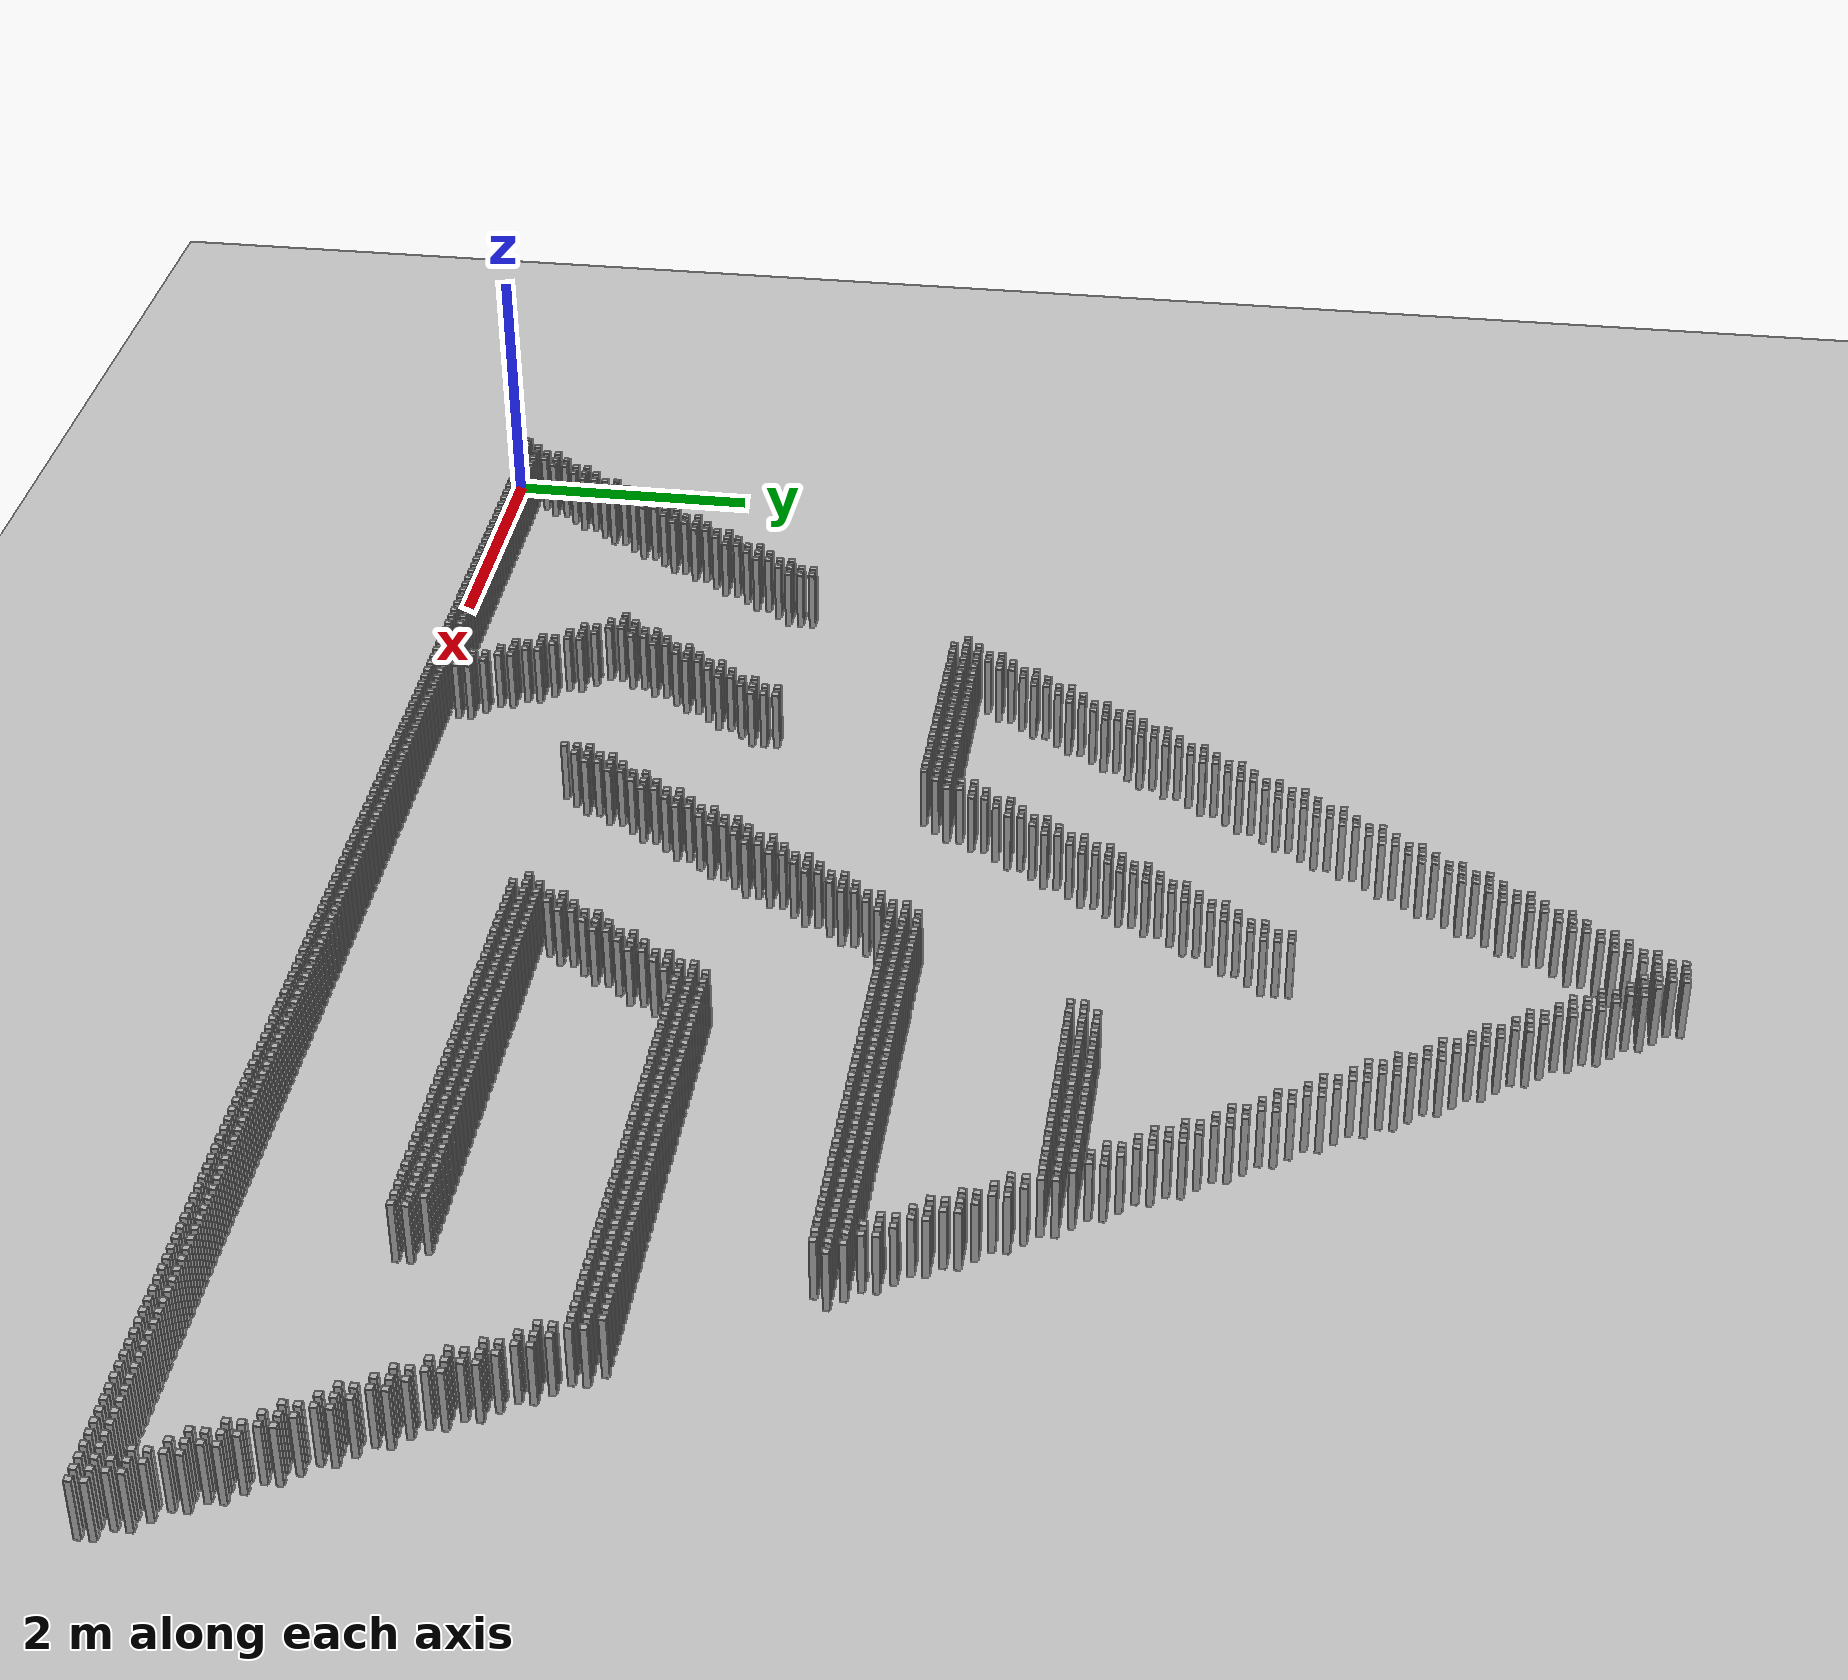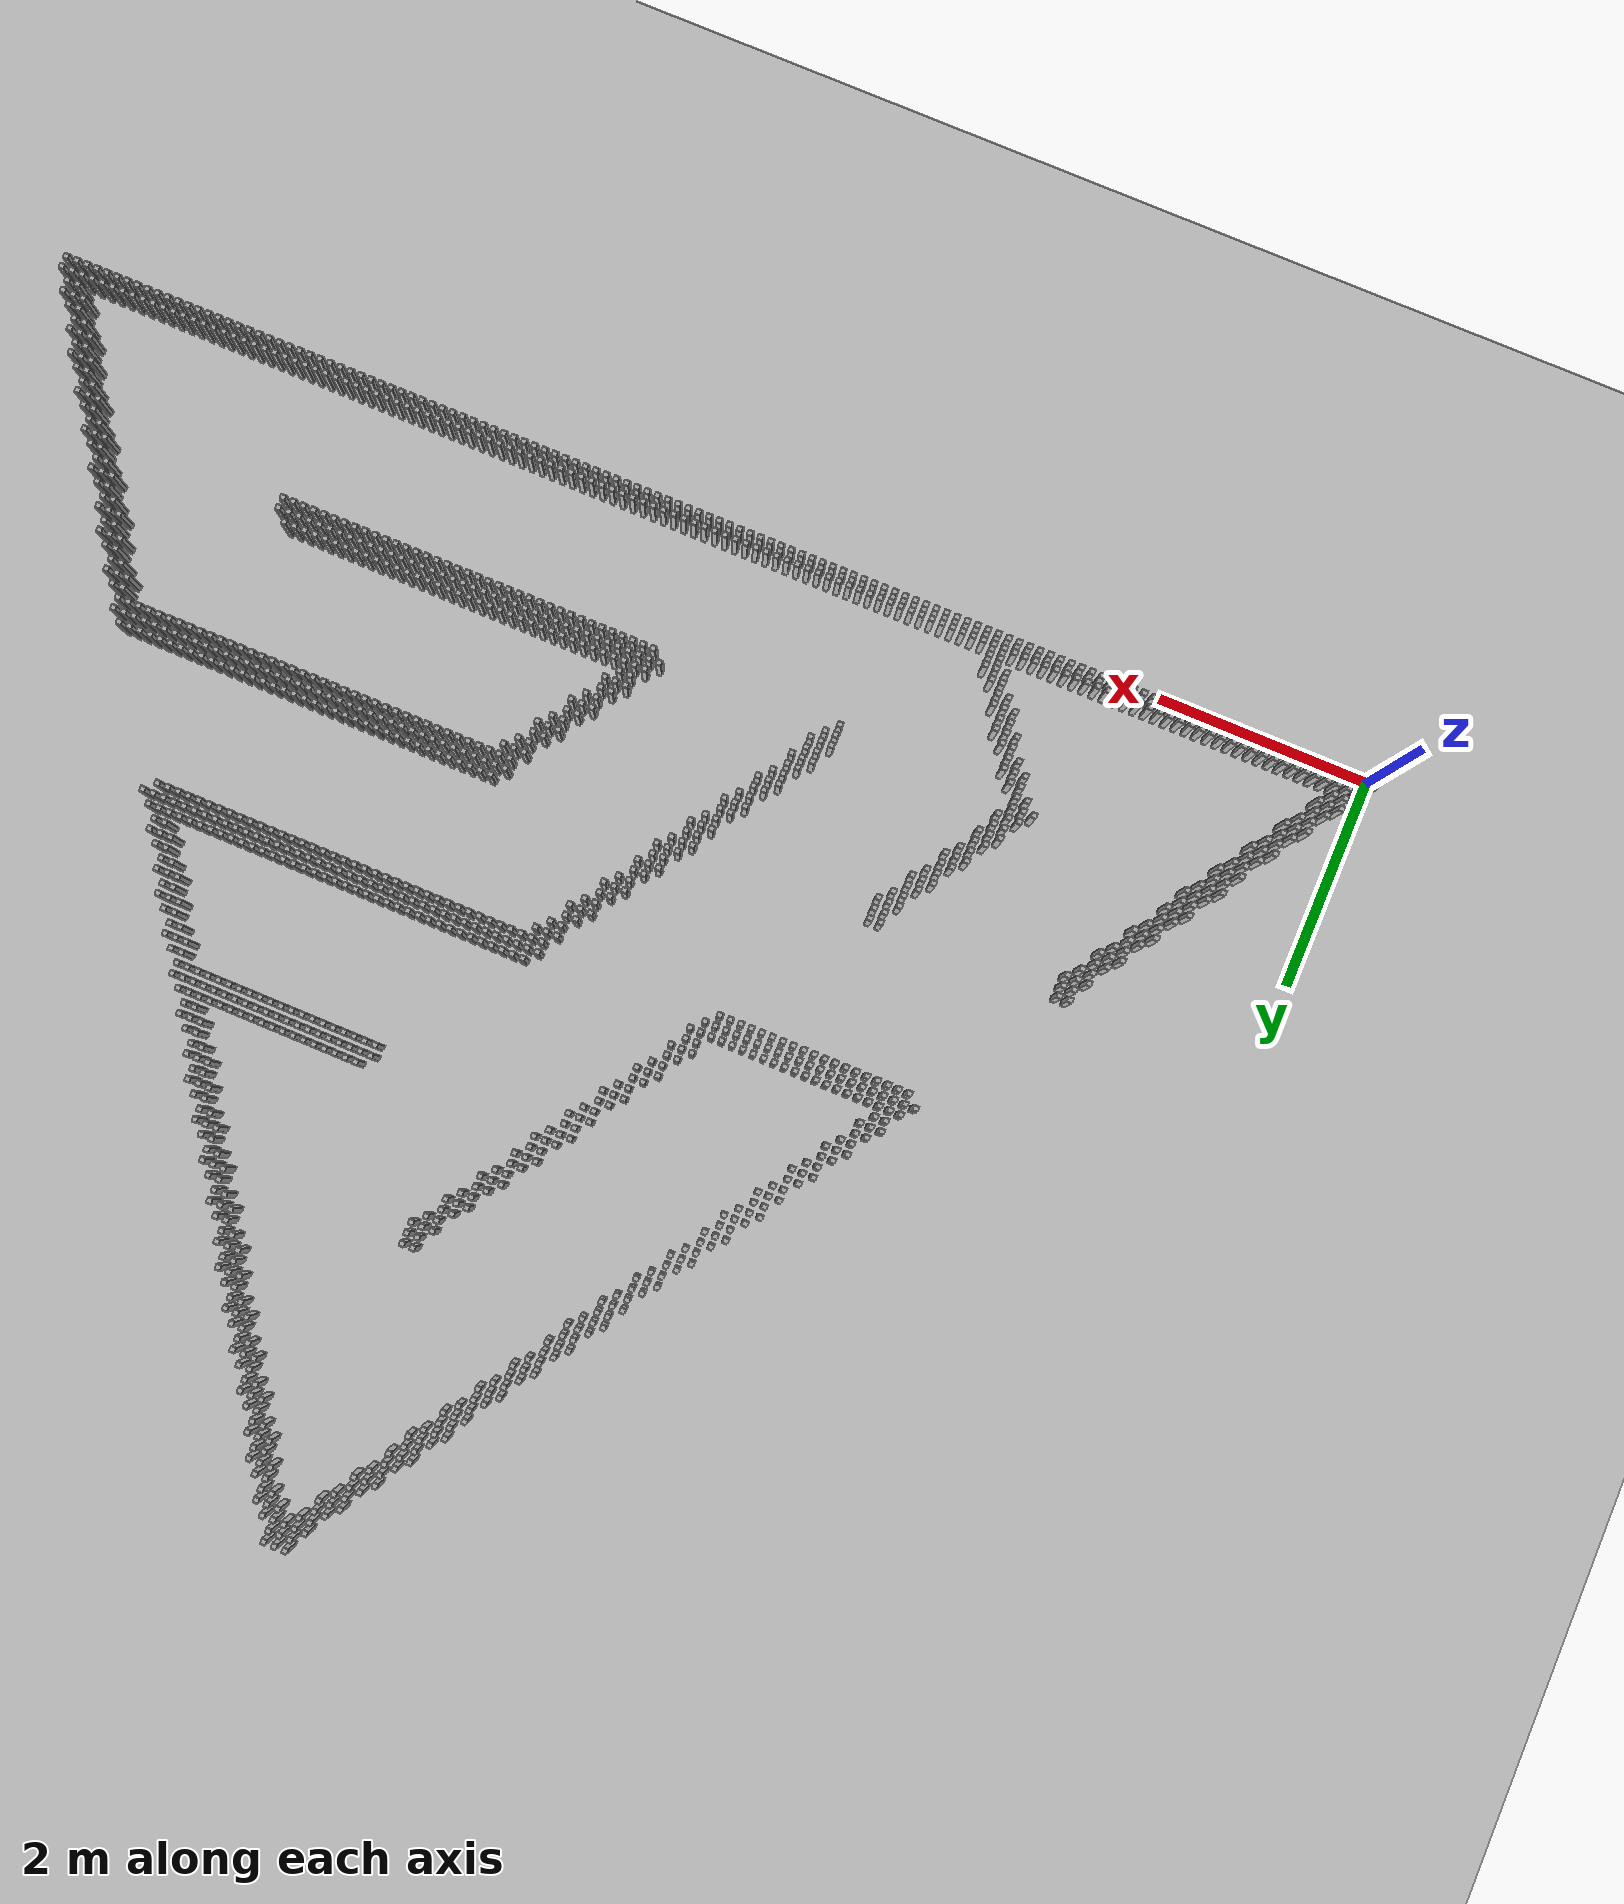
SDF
<?xml version="1.0"?>
<sdf version="1.6">
  <world name="default_world">

    <!-- Un cielo por defecto -->
    <include>
      <uri>model://sun</uri>
    </include>

    <!-- Un piso por defecto -->
    <include>
      <uri>model://ground_plane</uri>
    </include>

    <!-- Empieza la definición de obstáculos -->

    <model name="wall_0">
      <static>true</static>
      <link name="link">
        <collision name="collision">
          <geometry>
            <box>
              <size>0.05 0.05 0.5</size>
            </box>
          </geometry>
          <max_contacts>10</max_contacts>
          <surface>
            <friction>
              <ode/>
            </friction>
            <contact>
              <ode/>
            </contact>
          </surface>
        </collision>
        <visual name="visual">
          <geometry>
            <box>
              <size>0.05 0.05 0.5</size>
            </box>
          </geometry>
        </visual>
        <pose>6.300000000000001 9.9 0.25 0 0 0</pose>
      </link>
    </model>

    <model name="wall_1">
      <static>true</static>
      <link name="link">
        <collision name="collision">
          <geometry>
            <box>
              <size>0.05 0.05 0.5</size>
            </box>
          </geometry>
          <max_contacts>10</max_contacts>
          <surface>
            <friction>
              <ode/>
            </friction>
            <contact>
              <ode/>
            </contact>
          </surface>
        </collision>
        <visual name="visual">
          <geometry>
            <box>
              <size>0.05 0.05 0.5</size>
            </box>
          </geometry>
        </visual>
        <pose>6.4 9.9 0.25 0 0 0</pose>
      </link>
    </model>

    <model name="wall_2">
      <static>true</static>
      <link name="link">
        <collision name="collision">
          <geometry>
            <box>
              <size>0.05 0.05 0.5</size>
            </box>
          </geometry>
          <max_contacts>10</max_contacts>
          <surface>
            <friction>
              <ode/>
            </friction>
            <contact>
              <ode/>
            </contact>
          </surface>
        </collision>
        <visual name="visual">
          <geometry>
            <box>
              <size>0.05 0.05 0.5</size>
            </box>
          </geometry>
        </visual>
        <pose>6.5 9.9 0.25 0 0 0</pose>
      </link>
    </model>

    <model name="wall_3">
      <static>true</static>
      <link name="link">
        <collision name="collision">
          <geometry>
            <box>
              <size>0.05 0.05 0.5</size>
            </box>
          </geometry>
          <max_contacts>10</max_contacts>
          <surface>
            <friction>
              <ode/>
            </friction>
            <contact>
              <ode/>
            </contact>
          </surface>
        </collision>
        <visual name="visual">
          <geometry>
            <box>
              <size>0.05 0.05 0.5</size>
            </box>
          </geometry>
        </visual>
        <pose>6.300000000000001 9.8 0.25 0 0 0</pose>
      </link>
    </model>

    <model name="wall_4">
      <static>true</static>
      <link name="link">
        <collision name="collision">
          <geometry>
            <box>
              <size>0.05 0.05 0.5</size>
            </box>
          </geometry>
          <max_contacts>10</max_contacts>
          <surface>
            <friction>
              <ode/>
            </friction>
            <contact>
              <ode/>
            </contact>
          </surface>
        </collision>
        <visual name="visual">
          <geometry>
            <box>
              <size>0.05 0.05 0.5</size>
            </box>
          </geometry>
        </visual>
        <pose>6.4 9.8 0.25 0 0 0</pose>
      </link>
    </model>

    <model name="wall_5">
      <static>true</static>
      <link name="link">
        <collision name="collision">
          <geometry>
            <box>
              <size>0.05 0.05 0.5</size>
            </box>
          </geometry>
          <max_contacts>10</max_contacts>
          <surface>
            <friction>
              <ode/>
            </friction>
            <contact>
              <ode/>
            </contact>
          </surface>
        </collision>
        <visual name="visual">
          <geometry>
            <box>
              <size>0.05 0.05 0.5</size>
            </box>
          </geometry>
        </visual>
        <pose>6.5 9.8 0.25 0 0 0</pose>
      </link>
    </model>

    <model name="wall_6">
      <static>true</static>
      <link name="link">
        <collision name="collision">
          <geometry>
            <box>
              <size>0.05 0.05 0.5</size>
            </box>
          </geometry>
          <max_contacts>10</max_contacts>
          <surface>
            <friction>
              <ode/>
            </friction>
            <contact>
              <ode/>
            </contact>
          </surface>
        </collision>
        <visual name="visual">
          <geometry>
            <box>
              <size>0.05 0.05 0.5</size>
            </box>
          </geometry>
        </visual>
        <pose>6.2 9.700000000000001 0.25 0 0 0</pose>
      </link>
    </model>

    <model name="wall_7">
      <static>true</static>
      <link name="link">
        <collision name="collision">
          <geometry>
            <box>
              <size>0.05 0.05 0.5</size>
            </box>
          </geometry>
          <max_contacts>10</max_contacts>
          <surface>
            <friction>
              <ode/>
            </friction>
            <contact>
              <ode/>
            </contact>
          </surface>
        </collision>
        <visual name="visual">
          <geometry>
            <box>
              <size>0.05 0.05 0.5</size>
            </box>
          </geometry>
        </visual>
        <pose>6.300000000000001 9.700000000000001 0.25 0 0 0</pose>
      </link>
    </model>

    <model name="wall_8">
      <static>true</static>
      <link name="link">
        <collision name="collision">
          <geometry>
            <box>
              <size>0.05 0.05 0.5</size>
            </box>
          </geometry>
          <max_contacts>10</max_contacts>
          <surface>
            <friction>
              <ode/>
            </friction>
            <contact>
              <ode/>
            </contact>
          </surface>
        </collision>
        <visual name="visual">
          <geometry>
            <box>
              <size>0.05 0.05 0.5</size>
            </box>
          </geometry>
        </visual>
        <pose>6.4 9.700000000000001 0.25 0 0 0</pose>
      </link>
    </model>

    <model name="wall_9">
      <static>true</static>
      <link name="link">
        <collision name="collision">
          <geometry>
            <box>
              <size>0.05 0.05 0.5</size>
            </box>
          </geometry>
          <max_contacts>10</max_contacts>
          <surface>
            <friction>
              <ode/>
            </friction>
            <contact>
              <ode/>
            </contact>
          </surface>
        </collision>
        <visual name="visual">
          <geometry>
            <box>
              <size>0.05 0.05 0.5</size>
            </box>
          </geometry>
        </visual>
        <pose>6.5 9.700000000000001 0.25 0 0 0</pose>
      </link>
    </model>

    <model name="wall_10">
      <static>true</static>
      <link name="link">
        <collision name="collision">
          <geometry>
            <box>
              <size>0.05 0.05 0.5</size>
            </box>
          </geometry>
          <max_contacts>10</max_contacts>
          <surface>
            <friction>
              <ode/>
            </friction>
            <contact>
              <ode/>
            </contact>
          </surface>
        </collision>
        <visual name="visual">
          <geometry>
            <box>
              <size>0.05 0.05 0.5</size>
            </box>
          </geometry>
        </visual>
        <pose>6.6000000000000005 9.700000000000001 0.25 0 0 0</pose>
      </link>
    </model>

    <model name="wall_11">
      <static>true</static>
      <link name="link">
        <collision name="collision">
          <geometry>
            <box>
              <size>0.05 0.05 0.5</size>
            </box>
          </geometry>
          <max_contacts>10</max_contacts>
          <surface>
            <friction>
              <ode/>
            </friction>
            <contact>
              <ode/>
            </contact>
          </surface>
        </collision>
        <visual name="visual">
          <geometry>
            <box>
              <size>0.05 0.05 0.5</size>
            </box>
          </geometry>
        </visual>
        <pose>6.2 9.600000000000001 0.25 0 0 0</pose>
      </link>
    </model>

    <model name="wall_12">
      <static>true</static>
      <link name="link">
        <collision name="collision">
          <geometry>
            <box>
              <size>0.05 0.05 0.5</size>
            </box>
          </geometry>
          <max_contacts>10</max_contacts>
          <surface>
            <friction>
              <ode/>
            </friction>
            <contact>
              <ode/>
            </contact>
          </surface>
        </collision>
        <visual name="visual">
          <geometry>
            <box>
              <size>0.05 0.05 0.5</size>
            </box>
          </geometry>
        </visual>
        <pose>6.300000000000001 9.600000000000001 0.25 0 0 0</pose>
      </link>
    </model>

    <model name="wall_13">
      <static>true</static>
      <link name="link">
        <collision name="collision">
          <geometry>
            <box>
              <size>0.05 0.05 0.5</size>
            </box>
          </geometry>
          <max_contacts>10</max_contacts>
          <surface>
            <friction>
              <ode/>
            </friction>
            <contact>
              <ode/>
            </contact>
          </surface>
        </collision>
        <visual name="visual">
          <geometry>
            <box>
              <size>0.05 0.05 0.5</size>
            </box>
          </geometry>
        </visual>
        <pose>6.5 9.600000000000001 0.25 0 0 0</pose>
      </link>
    </model>

    <model name="wall_14">
      <static>true</static>
      <link name="link">
        <collision name="collision">
          <geometry>
            <box>
              <size>0.05 0.05 0.5</size>
            </box>
          </geometry>
          <max_contacts>10</max_contacts>
          <surface>
            <friction>
              <ode/>
            </friction>
            <contact>
              <ode/>
            </contact>
          </surface>
        </collision>
        <visual name="visual">
          <geometry>
            <box>
              <size>0.05 0.05 0.5</size>
            </box>
          </geometry>
        </visual>
        <pose>6.6000000000000005 9.600000000000001 0.25 0 0 0</pose>
      </link>
    </model>

    <model name="wall_15">
      <static>true</static>
      <link name="link">
        <collision name="collision">
          <geometry>
            <box>
              <size>0.05 0.05 0.5</size>
            </box>
          </geometry>
          <max_contacts>10</max_contacts>
          <surface>
            <friction>
              <ode/>
            </friction>
            <contact>
              <ode/>
            </contact>
          </surface>
        </collision>
        <visual name="visual">
          <geometry>
            <box>
              <size>0.05 0.05 0.5</size>
            </box>
          </geometry>
        </visual>
        <pose>6.7 9.600000000000001 0.25 0 0 0</pose>
      </link>
    </model>

    <model name="wall_16">
      <static>true</static>
      <link name="link">
        <collision name="collision">
          <geometry>
            <box>
              <size>0.05 0.05 0.5</size>
            </box>
          </geometry>
          <max_contacts>10</max_contacts>
          <surface>
            <friction>
              <ode/>
            </friction>
            <contact>
              <ode/>
            </contact>
          </surface>
        </collision>
        <visual name="visual">
          <geometry>
            <box>
              <size>0.05 0.05 0.5</size>
            </box>
          </geometry>
        </visual>
        <pose>6.1000000000000005 9.5 0.25 0 0 0</pose>
      </link>
    </model>

    <model name="wall_17">
      <static>true</static>
      <link name="link">
        <collision name="collision">
          <geometry>
            <box>
              <size>0.05 0.05 0.5</size>
            </box>
          </geometry>
          <max_contacts>10</max_contacts>
          <surface>
            <friction>
              <ode/>
            </friction>
            <contact>
              <ode/>
            </contact>
          </surface>
        </collision>
        <visual name="visual">
          <geometry>
            <box>
              <size>0.05 0.05 0.5</size>
            </box>
          </geometry>
        </visual>
        <pose>6.2 9.5 0.25 0 0 0</pose>
      </link>
    </model>

    <model name="wall_18">
      <static>true</static>
      <link name="link">
        <collision name="collision">
          <geometry>
            <box>
              <size>0.05 0.05 0.5</size>
            </box>
          </geometry>
          <max_contacts>10</max_contacts>
          <surface>
            <friction>
              <ode/>
            </friction>
            <contact>
              <ode/>
            </contact>
          </surface>
        </collision>
        <visual name="visual">
          <geometry>
            <box>
              <size>0.05 0.05 0.5</size>
            </box>
          </geometry>
        </visual>
        <pose>6.6000000000000005 9.5 0.25 0 0 0</pose>
      </link>
    </model>

    <model name="wall_19">
      <static>true</static>
      <link name="link">
        <collision name="collision">
          <geometry>
            <box>
              <size>0.05 0.05 0.5</size>
            </box>
          </geometry>
          <max_contacts>10</max_contacts>
          <surface>
            <friction>
              <ode/>
            </friction>
            <contact>
              <ode/>
            </contact>
          </surface>
        </collision>
        <visual name="visual">
          <geometry>
            <box>
              <size>0.05 0.05 0.5</size>
            </box>
          </geometry>
        </visual>
        <pose>6.7 9.5 0.25 0 0 0</pose>
      </link>
    </model>

    <model name="wall_20">
      <static>true</static>
      <link name="link">
        <collision name="collision">
          <geometry>
            <box>
              <size>0.05 0.05 0.5</size>
            </box>
          </geometry>
          <max_contacts>10</max_contacts>
          <surface>
            <friction>
              <ode/>
            </friction>
            <contact>
              <ode/>
            </contact>
          </surface>
        </collision>
        <visual name="visual">
          <geometry>
            <box>
              <size>0.05 0.05 0.5</size>
            </box>
          </geometry>
        </visual>
        <pose>6.0 9.4 0.25 0 0 0</pose>
      </link>
    </model>

    <model name="wall_21">
      <static>true</static>
      <link name="link">
        <collision name="collision">
          <geometry>
            <box>
              <size>0.05 0.05 0.5</size>
            </box>
          </geometry>
          <max_contacts>10</max_contacts>
          <surface>
            <friction>
              <ode/>
            </friction>
            <contact>
              <ode/>
            </contact>
          </surface>
        </collision>
        <visual name="visual">
          <geometry>
            <box>
              <size>0.05 0.05 0.5</size>
            </box>
          </geometry>
        </visual>
        <pose>6.1000000000000005 9.4 0.25 0 0 0</pose>
      </link>
    </model>

    <model name="wall_22">
      <static>true</static>
      <link name="link">
        <collision name="collision">
          <geometry>
            <box>
              <size>0.05 0.05 0.5</size>
            </box>
          </geometry>
          <max_contacts>10</max_contacts>
          <surface>
            <friction>
              <ode/>
            </friction>
            <contact>
              <ode/>
            </contact>
          </surface>
        </collision>
        <visual name="visual">
          <geometry>
            <box>
              <size>0.05 0.05 0.5</size>
            </box>
          </geometry>
        </visual>
        <pose>6.2 9.4 0.25 0 0 0</pose>
      </link>
    </model>

    <model name="wall_23">
      <static>true</static>
      <link name="link">
        <collision name="collision">
          <geometry>
            <box>
              <size>0.05 0.05 0.5</size>
            </box>
          </geometry>
          <max_contacts>10</max_contacts>
          <surface>
            <friction>
              <ode/>
            </friction>
            <contact>
              <ode/>
            </contact>
          </surface>
        </collision>
        <visual name="visual">
          <geometry>
            <box>
              <size>0.05 0.05 0.5</size>
            </box>
          </geometry>
        </visual>
        <pose>6.7 9.4 0.25 0 0 0</pose>
      </link>
    </model>

    <model name="wall_24">
      <static>true</static>
      <link name="link">
        <collision name="collision">
          <geometry>
            <box>
              <size>0.05 0.05 0.5</size>
            </box>
          </geometry>
          <max_contacts>10</max_contacts>
          <surface>
            <friction>
              <ode/>
            </friction>
            <contact>
              <ode/>
            </contact>
          </surface>
        </collision>
        <visual name="visual">
          <geometry>
            <box>
              <size>0.05 0.05 0.5</size>
            </box>
          </geometry>
        </visual>
        <pose>6.800000000000001 9.4 0.25 0 0 0</pose>
      </link>
    </model>

    <model name="wall_25">
      <static>true</static>
      <link name="link">
        <collision name="collision">
          <geometry>
            <box>
              <size>0.05 0.05 0.5</size>
            </box>
          </geometry>
          <max_contacts>10</max_contacts>
          <surface>
            <friction>
              <ode/>
            </friction>
            <contact>
              <ode/>
            </contact>
          </surface>
        </collision>
        <visual name="visual">
          <geometry>
            <box>
              <size>0.05 0.05 0.5</size>
            </box>
          </geometry>
        </visual>
        <pose>6.0 9.3 0.25 0 0 0</pose>
      </link>
    </model>

    <model name="wall_26">
      <static>true</static>
      <link name="link">
        <collision name="collision">
          <geometry>
            <box>
              <size>0.05 0.05 0.5</size>
            </box>
          </geometry>
          <max_contacts>10</max_contacts>
          <surface>
            <friction>
              <ode/>
            </friction>
            <contact>
              <ode/>
            </contact>
          </surface>
        </collision>
        <visual name="visual">
          <geometry>
            <box>
              <size>0.05 0.05 0.5</size>
            </box>
          </geometry>
        </visual>
        <pose>6.1000000000000005 9.3 0.25 0 0 0</pose>
      </link>
    </model>

    <model name="wall_27">
      <static>true</static>
      <link name="link">
        <collision name="collision">
          <geometry>
            <box>
              <size>0.05 0.05 0.5</size>
            </box>
          </geometry>
          <max_contacts>10</max_contacts>
          <surface>
            <friction>
              <ode/>
            </friction>
            <contact>
              <ode/>
            </contact>
          </surface>
        </collision>
        <visual name="visual">
          <geometry>
            <box>
              <size>0.05 0.05 0.5</size>
            </box>
          </geometry>
        </visual>
        <pose>6.7 9.3 0.25 0 0 0</pose>
      </link>
    </model>

    <model name="wall_28">
      <static>true</static>
      <link name="link">
        <collision name="collision">
          <geometry>
            <box>
              <size>0.05 0.05 0.5</size>
            </box>
          </geometry>
          <max_contacts>10</max_contacts>
          <surface>
            <friction>
              <ode/>
            </friction>
            <contact>
              <ode/>
            </contact>
          </surface>
        </collision>
        <visual name="visual">
          <geometry>
            <box>
              <size>0.05 0.05 0.5</size>
            </box>
          </geometry>
        </visual>
        <pose>6.800000000000001 9.3 0.25 0 0 0</pose>
      </link>
    </model>

    <model name="wall_29">
      <static>true</static>
      <link name="link">
        <collision name="collision">
          <geometry>
            <box>
              <size>0.05 0.05 0.5</size>
            </box>
          </geometry>
          <max_contacts>10</max_contacts>
          <surface>
            <friction>
              <ode/>
            </friction>
            <contact>
              <ode/>
            </contact>
          </surface>
        </collision>
        <visual name="visual">
          <geometry>
            <box>
              <size>0.05 0.05 0.5</size>
            </box>
          </geometry>
        </visual>
        <pose>6.9 9.3 0.25 0 0 0</pose>
      </link>
    </model>

    <model name="wall_30">
      <static>true</static>
      <link name="link">
        <collision name="collision">
          <geometry>
            <box>
              <size>0.05 0.05 0.5</size>
            </box>
          </geometry>
          <max_contacts>10</max_contacts>
          <surface>
            <friction>
              <ode/>
            </friction>
            <contact>
              <ode/>
            </contact>
          </surface>
        </collision>
        <visual name="visual">
          <geometry>
            <box>
              <size>0.05 0.05 0.5</size>
            </box>
          </geometry>
        </visual>
        <pose>5.9 9.200000000000001 0.25 0 0 0</pose>
      </link>
    </model>

    <model name="wall_31">
      <static>true</static>
      <link name="link">
        <collision name="collision">
          <geometry>
            <box>
              <size>0.05 0.05 0.5</size>
            </box>
          </geometry>
          <max_contacts>10</max_contacts>
          <surface>
            <friction>
              <ode/>
            </friction>
            <contact>
              <ode/>
            </contact>
          </surface>
        </collision>
        <visual name="visual">
          <geometry>
            <box>
              <size>0.05 0.05 0.5</size>
            </box>
          </geometry>
        </visual>
        <pose>6.0 9.200000000000001 0.25 0 0 0</pose>
      </link>
    </model>

    <model name="wall_32">
      <static>true</static>
      <link name="link">
        <collision name="collision">
          <geometry>
            <box>
              <size>0.05 0.05 0.5</size>
            </box>
          </geometry>
          <max_contacts>10</max_contacts>
          <surface>
            <friction>
              <ode/>
            </friction>
            <contact>
              <ode/>
            </contact>
          </surface>
        </collision>
        <visual name="visual">
          <geometry>
            <box>
              <size>0.05 0.05 0.5</size>
            </box>
          </geometry>
        </visual>
        <pose>6.800000000000001 9.200000000000001 0.25 0 0 0</pose>
      </link>
    </model>

    <model name="wall_33">
      <static>true</static>
      <link name="link">
        <collision name="collision">
          <geometry>
            <box>
              <size>0.05 0.05 0.5</size>
            </box>
          </geometry>
          <max_contacts>10</max_contacts>
          <surface>
            <friction>
              <ode/>
            </friction>
            <contact>
              <ode/>
            </contact>
          </surface>
        </collision>
        <visual name="visual">
          <geometry>
            <box>
              <size>0.05 0.05 0.5</size>
            </box>
          </geometry>
        </visual>
        <pose>6.9 9.200000000000001 0.25 0 0 0</pose>
      </link>
    </model>

    <model name="wall_34">
      <static>true</static>
      <link name="link">
        <collision name="collision">
          <geometry>
            <box>
              <size>0.05 0.05 0.5</size>
            </box>
          </geometry>
          <max_contacts>10</max_contacts>
          <surface>
            <friction>
              <ode/>
            </friction>
            <contact>
              <ode/>
            </contact>
          </surface>
        </collision>
        <visual name="visual">
          <geometry>
            <box>
              <size>0.05 0.05 0.5</size>
            </box>
          </geometry>
        </visual>
        <pose>5.800000000000001 9.1 0.25 0 0 0</pose>
      </link>
    </model>

    <model name="wall_35">
      <static>true</static>
      <link name="link">
        <collision name="collision">
          <geometry>
            <box>
              <size>0.05 0.05 0.5</size>
            </box>
          </geometry>
          <max_contacts>10</max_contacts>
          <surface>
            <friction>
              <ode/>
            </friction>
            <contact>
              <ode/>
            </contact>
          </surface>
        </collision>
        <visual name="visual">
          <geometry>
            <box>
              <size>0.05 0.05 0.5</size>
            </box>
          </geometry>
        </visual>
        <pose>5.9 9.1 0.25 0 0 0</pose>
      </link>
    </model>

    <model name="wall_36">
      <static>true</static>
      <link name="link">
        <collision name="collision">
          <geometry>
            <box>
              <size>0.05 0.05 0.5</size>
            </box>
          </geometry>
          <max_contacts>10</max_contacts>
          <surface>
            <friction>
              <ode/>
            </friction>
            <contact>
              <ode/>
            </contact>
          </surface>
        </collision>
        <visual name="visual">
          <geometry>
            <box>
              <size>0.05 0.05 0.5</size>
            </box>
          </geometry>
        </visual>
        <pose>6.0 9.1 0.25 0 0 0</pose>
      </link>
    </model>

    <model name="wall_37">
      <static>true</static>
      <link name="link">
        <collision name="collision">
          <geometry>
            <box>
              <size>0.05 0.05 0.5</size>
            </box>
          </geometry>
          <max_contacts>10</max_contacts>
          <surface>
            <friction>
              <ode/>
            </friction>
            <contact>
              <ode/>
            </contact>
          </surface>
        </collision>
        <visual name="visual">
          <geometry>
            <box>
              <size>0.05 0.05 0.5</size>
            </box>
          </geometry>
        </visual>
        <pose>6.800000000000001 9.1 0.25 0 0 0</pose>
      </link>
    </model>

    <model name="wall_38">
      <static>true</static>
      <link name="link">
        <collision name="collision">
          <geometry>
            <box>
              <size>0.05 0.05 0.5</size>
            </box>
          </geometry>
          <max_contacts>10</max_contacts>
          <surface>
            <friction>
              <ode/>
            </friction>
            <contact>
              <ode/>
            </contact>
          </surface>
        </collision>
        <visual name="visual">
          <geometry>
            <box>
              <size>0.05 0.05 0.5</size>
            </box>
          </geometry>
        </visual>
        <pose>6.9 9.1 0.25 0 0 0</pose>
      </link>
    </model>

    <model name="wall_39">
      <static>true</static>
      <link name="link">
        <collision name="collision">
          <geometry>
            <box>
              <size>0.05 0.05 0.5</size>
            </box>
          </geometry>
          <max_contacts>10</max_contacts>
          <surface>
            <friction>
              <ode/>
            </friction>
            <contact>
              <ode/>
            </contact>
          </surface>
        </collision>
        <visual name="visual">
          <geometry>
            <box>
              <size>0.05 0.05 0.5</size>
            </box>
          </geometry>
        </visual>
        <pose>7.0 9.1 0.25 0 0 0</pose>
      </link>
    </model>

    <model name="wall_40">
      <static>true</static>
      <link name="link">
        <collision name="collision">
          <geometry>
            <box>
              <size>0.05 0.05 0.5</size>
            </box>
          </geometry>
          <max_contacts>10</max_contacts>
          <surface>
            <friction>
              <ode/>
            </friction>
            <contact>
              <ode/>
            </contact>
          </surface>
        </collision>
        <visual name="visual">
          <geometry>
            <box>
              <size>0.05 0.05 0.5</size>
            </box>
          </geometry>
        </visual>
        <pose>5.800000000000001 9.0 0.25 0 0 0</pose>
      </link>
    </model>

    <model name="wall_41">
      <static>true</static>
      <link name="link">
        <collision name="collision">
          <geometry>
            <box>
              <size>0.05 0.05 0.5</size>
            </box>
          </geometry>
          <max_contacts>10</max_contacts>
          <surface>
            <friction>
              <ode/>
            </friction>
            <contact>
              <ode/>
            </contact>
          </surface>
        </collision>
        <visual name="visual">
          <geometry>
            <box>
              <size>0.05 0.05 0.5</size>
            </box>
          </geometry>
        </visual>
        <pose>5.9 9.0 0.25 0 0 0</pose>
      </link>
    </model>

    <model name="wall_42">
      <static>true</static>
      <link name="link">
        <collision name="collision">
          <geometry>
            <box>
              <size>0.05 0.05 0.5</size>
            </box>
          </geometry>
          <max_contacts>10</max_contacts>
          <surface>
            <friction>
              <ode/>
            </friction>
            <contact>
              <ode/>
            </contact>
          </surface>
        </collision>
        <visual name="visual">
          <geometry>
            <box>
              <size>0.05 0.05 0.5</size>
            </box>
          </geometry>
        </visual>
        <pose>6.9 9.0 0.25 0 0 0</pose>
      </link>
    </model>

    <model name="wall_43">
      <static>true</static>
      <link name="link">
        <collision name="collision">
          <geometry>
            <box>
              <size>0.05 0.05 0.5</size>
            </box>
          </geometry>
          <max_contacts>10</max_contacts>
          <surface>
            <friction>
              <ode/>
            </friction>
            <contact>
              <ode/>
            </contact>
          </surface>
        </collision>
        <visual name="visual">
          <geometry>
            <box>
              <size>0.05 0.05 0.5</size>
            </box>
          </geometry>
        </visual>
        <pose>7.0 9.0 0.25 0 0 0</pose>
      </link>
    </model>

    <model name="wall_44">
      <static>true</static>
      <link name="link">
        <collision name="collision">
          <geometry>
            <box>
              <size>0.05 0.05 0.5</size>
            </box>
          </geometry>
          <max_contacts>10</max_contacts>
          <surface>
            <friction>
              <ode/>
            </friction>
            <contact>
              <ode/>
            </contact>
          </surface>
        </collision>
        <visual name="visual">
          <geometry>
            <box>
              <size>0.05 0.05 0.5</size>
            </box>
          </geometry>
        </visual>
        <pose>5.7 8.9 0.25 0 0 0</pose>
      </link>
    </model>

    <model name="wall_45">
      <static>true</static>
      <link name="link">
        <collision name="collision">
          <geometry>
            <box>
              <size>0.05 0.05 0.5</size>
            </box>
          </geometry>
          <max_contacts>10</max_contacts>
          <surface>
            <friction>
              <ode/>
            </friction>
            <contact>
              <ode/>
            </contact>
          </surface>
        </collision>
        <visual name="visual">
          <geometry>
            <box>
              <size>0.05 0.05 0.5</size>
            </box>
          </geometry>
        </visual>
        <pose>5.800000000000001 8.9 0.25 0 0 0</pose>
      </link>
    </model>

    <model name="wall_46">
      <static>true</static>
      <link name="link">
        <collision name="collision">
          <geometry>
            <box>
              <size>0.05 0.05 0.5</size>
            </box>
          </geometry>
          <max_contacts>10</max_contacts>
          <surface>
            <friction>
              <ode/>
            </friction>
            <contact>
              <ode/>
            </contact>
          </surface>
        </collision>
        <visual name="visual">
          <geometry>
            <box>
              <size>0.05 0.05 0.5</size>
            </box>
          </geometry>
        </visual>
        <pose>7.0 8.9 0.25 0 0 0</pose>
      </link>
    </model>

    <model name="wall_47">
      <static>true</static>
      <link name="link">
        <collision name="collision">
          <geometry>
            <box>
              <size>0.05 0.05 0.5</size>
            </box>
          </geometry>
          <max_contacts>10</max_contacts>
          <surface>
            <friction>
              <ode/>
            </friction>
            <contact>
              <ode/>
            </contact>
          </surface>
        </collision>
        <visual name="visual">
          <geometry>
            <box>
              <size>0.05 0.05 0.5</size>
            </box>
          </geometry>
        </visual>
        <pose>7.1000000000000005 8.9 0.25 0 0 0</pose>
      </link>
    </model>

    <model name="wall_48">
      <static>true</static>
      <link name="link">
        <collision name="collision">
          <geometry>
            <box>
              <size>0.05 0.05 0.5</size>
            </box>
          </geometry>
          <max_contacts>10</max_contacts>
          <surface>
            <friction>
              <ode/>
            </friction>
            <contact>
              <ode/>
            </contact>
          </surface>
        </collision>
        <visual name="visual">
          <geometry>
            <box>
              <size>0.05 0.05 0.5</size>
            </box>
          </geometry>
        </visual>
        <pose>5.6000000000000005 8.8 0.25 0 0 0</pose>
      </link>
    </model>

    <model name="wall_49">
      <static>true</static>
      <link name="link">
        <collision name="collision">
          <geometry>
            <box>
              <size>0.05 0.05 0.5</size>
            </box>
          </geometry>
          <max_contacts>10</max_contacts>
          <surface>
            <friction>
              <ode/>
            </friction>
            <contact>
              <ode/>
            </contact>
          </surface>
        </collision>
        <visual name="visual">
          <geometry>
            <box>
              <size>0.05 0.05 0.5</size>
            </box>
          </geometry>
        </visual>
        <pose>5.7 8.8 0.25 0 0 0</pose>
      </link>
    </model>

    <model name="wall_50">
      <static>true</static>
      <link name="link">
        <collision name="collision">
          <geometry>
            <box>
              <size>0.05 0.05 0.5</size>
            </box>
          </geometry>
          <max_contacts>10</max_contacts>
          <surface>
            <friction>
              <ode/>
            </friction>
            <contact>
              <ode/>
            </contact>
          </surface>
        </collision>
        <visual name="visual">
          <geometry>
            <box>
              <size>0.05 0.05 0.5</size>
            </box>
          </geometry>
        </visual>
        <pose>5.800000000000001 8.8 0.25 0 0 0</pose>
      </link>
    </model>

    <model name="wall_51">
      <static>true</static>
      <link name="link">
        <collision name="collision">
          <geometry>
            <box>
              <size>0.05 0.05 0.5</size>
            </box>
          </geometry>
          <max_contacts>10</max_contacts>
          <surface>
            <friction>
              <ode/>
            </friction>
            <contact>
              <ode/>
            </contact>
          </surface>
        </collision>
        <visual name="visual">
          <geometry>
            <box>
              <size>0.05 0.05 0.5</size>
            </box>
          </geometry>
        </visual>
        <pose>7.0 8.8 0.25 0 0 0</pose>
      </link>
    </model>

    <model name="wall_52">
      <static>true</static>
      <link name="link">
        <collision name="collision">
          <geometry>
            <box>
              <size>0.05 0.05 0.5</size>
            </box>
          </geometry>
          <max_contacts>10</max_contacts>
          <surface>
            <friction>
              <ode/>
            </friction>
            <contact>
              <ode/>
            </contact>
          </surface>
        </collision>
        <visual name="visual">
          <geometry>
            <box>
              <size>0.05 0.05 0.5</size>
            </box>
          </geometry>
        </visual>
        <pose>7.1000000000000005 8.8 0.25 0 0 0</pose>
      </link>
    </model>

    <model name="wall_53">
      <static>true</static>
      <link name="link">
        <collision name="collision">
          <geometry>
            <box>
              <size>0.05 0.05 0.5</size>
            </box>
          </geometry>
          <max_contacts>10</max_contacts>
          <surface>
            <friction>
              <ode/>
            </friction>
            <contact>
              <ode/>
            </contact>
          </surface>
        </collision>
        <visual name="visual">
          <geometry>
            <box>
              <size>0.05 0.05 0.5</size>
            </box>
          </geometry>
        </visual>
        <pose>7.2 8.8 0.25 0 0 0</pose>
      </link>
    </model>

    <model name="wall_54">
      <static>true</static>
      <link name="link">
        <collision name="collision">
          <geometry>
            <box>
              <size>0.05 0.05 0.5</size>
            </box>
          </geometry>
          <max_contacts>10</max_contacts>
          <surface>
            <friction>
              <ode/>
            </friction>
            <contact>
              <ode/>
            </contact>
          </surface>
        </collision>
        <visual name="visual">
          <geometry>
            <box>
              <size>0.05 0.05 0.5</size>
            </box>
          </geometry>
        </visual>
        <pose>5.6000000000000005 8.700000000000001 0.25 0 0 0</pose>
      </link>
    </model>

    <model name="wall_55">
      <static>true</static>
      <link name="link">
        <collision name="collision">
          <geometry>
            <box>
              <size>0.05 0.05 0.5</size>
            </box>
          </geometry>
          <max_contacts>10</max_contacts>
          <surface>
            <friction>
              <ode/>
            </friction>
            <contact>
              <ode/>
            </contact>
          </surface>
        </collision>
        <visual name="visual">
          <geometry>
            <box>
              <size>0.05 0.05 0.5</size>
            </box>
          </geometry>
        </visual>
        <pose>5.7 8.700000000000001 0.25 0 0 0</pose>
      </link>
    </model>

    <model name="wall_56">
      <static>true</static>
      <link name="link">
        <collision name="collision">
          <geometry>
            <box>
              <size>0.05 0.05 0.5</size>
            </box>
          </geometry>
          <max_contacts>10</max_contacts>
          <surface>
            <friction>
              <ode/>
            </friction>
            <contact>
              <ode/>
            </contact>
          </surface>
        </collision>
        <visual name="visual">
          <geometry>
            <box>
              <size>0.05 0.05 0.5</size>
            </box>
          </geometry>
        </visual>
        <pose>7.1000000000000005 8.700000000000001 0.25 0 0 0</pose>
      </link>
    </model>

    <model name="wall_57">
      <static>true</static>
      <link name="link">
        <collision name="collision">
          <geometry>
            <box>
              <size>0.05 0.05 0.5</size>
            </box>
          </geometry>
          <max_contacts>10</max_contacts>
          <surface>
            <friction>
              <ode/>
            </friction>
            <contact>
              <ode/>
            </contact>
          </surface>
        </collision>
        <visual name="visual">
          <geometry>
            <box>
              <size>0.05 0.05 0.5</size>
            </box>
          </geometry>
        </visual>
        <pose>7.2 8.700000000000001 0.25 0 0 0</pose>
      </link>
    </model>

    <model name="wall_58">
      <static>true</static>
      <link name="link">
        <collision name="collision">
          <geometry>
            <box>
              <size>0.05 0.05 0.5</size>
            </box>
          </geometry>
          <max_contacts>10</max_contacts>
          <surface>
            <friction>
              <ode/>
            </friction>
            <contact>
              <ode/>
            </contact>
          </surface>
        </collision>
        <visual name="visual">
          <geometry>
            <box>
              <size>0.05 0.05 0.5</size>
            </box>
          </geometry>
        </visual>
        <pose>5.5 8.6 0.25 0 0 0</pose>
      </link>
    </model>

    <model name="wall_59">
      <static>true</static>
      <link name="link">
        <collision name="collision">
          <geometry>
            <box>
              <size>0.05 0.05 0.5</size>
            </box>
          </geometry>
          <max_contacts>10</max_contacts>
          <surface>
            <friction>
              <ode/>
            </friction>
            <contact>
              <ode/>
            </contact>
          </surface>
        </collision>
        <visual name="visual">
          <geometry>
            <box>
              <size>0.05 0.05 0.5</size>
            </box>
          </geometry>
        </visual>
        <pose>5.6000000000000005 8.6 0.25 0 0 0</pose>
      </link>
    </model>

    <model name="wall_60">
      <static>true</static>
      <link name="link">
        <collision name="collision">
          <geometry>
            <box>
              <size>0.05 0.05 0.5</size>
            </box>
          </geometry>
          <max_contacts>10</max_contacts>
          <surface>
            <friction>
              <ode/>
            </friction>
            <contact>
              <ode/>
            </contact>
          </surface>
        </collision>
        <visual name="visual">
          <geometry>
            <box>
              <size>0.05 0.05 0.5</size>
            </box>
          </geometry>
        </visual>
        <pose>5.7 8.6 0.25 0 0 0</pose>
      </link>
    </model>

    <model name="wall_61">
      <static>true</static>
      <link name="link">
        <collision name="collision">
          <geometry>
            <box>
              <size>0.05 0.05 0.5</size>
            </box>
          </geometry>
          <max_contacts>10</max_contacts>
          <surface>
            <friction>
              <ode/>
            </friction>
            <contact>
              <ode/>
            </contact>
          </surface>
        </collision>
        <visual name="visual">
          <geometry>
            <box>
              <size>0.05 0.05 0.5</size>
            </box>
          </geometry>
        </visual>
        <pose>7.2 8.6 0.25 0 0 0</pose>
      </link>
    </model>

    <model name="wall_62">
      <static>true</static>
      <link name="link">
        <collision name="collision">
          <geometry>
            <box>
              <size>0.05 0.05 0.5</size>
            </box>
          </geometry>
          <max_contacts>10</max_contacts>
          <surface>
            <friction>
              <ode/>
            </friction>
            <contact>
              <ode/>
            </contact>
          </surface>
        </collision>
        <visual name="visual">
          <geometry>
            <box>
              <size>0.05 0.05 0.5</size>
            </box>
          </geometry>
        </visual>
        <pose>7.300000000000001 8.6 0.25 0 0 0</pose>
      </link>
    </model>

    <model name="wall_63">
      <static>true</static>
      <link name="link">
        <collision name="collision">
          <geometry>
            <box>
              <size>0.05 0.05 0.5</size>
            </box>
          </geometry>
          <max_contacts>10</max_contacts>
          <surface>
            <friction>
              <ode/>
            </friction>
            <contact>
              <ode/>
            </contact>
          </surface>
        </collision>
        <visual name="visual">
          <geometry>
            <box>
              <size>0.05 0.05 0.5</size>
            </box>
          </geometry>
        </visual>
        <pose>5.4 8.5 0.25 0 0 0</pose>
      </link>
    </model>

    <model name="wall_64">
      <static>true</static>
      <link name="link">
        <collision name="collision">
          <geometry>
            <box>
              <size>0.05 0.05 0.5</size>
            </box>
          </geometry>
          <max_contacts>10</max_contacts>
          <surface>
            <friction>
              <ode/>
            </friction>
            <contact>
              <ode/>
            </contact>
          </surface>
        </collision>
        <visual name="visual">
          <geometry>
            <box>
              <size>0.05 0.05 0.5</size>
            </box>
          </geometry>
        </visual>
        <pose>5.5 8.5 0.25 0 0 0</pose>
      </link>
    </model>

    <model name="wall_65">
      <static>true</static>
      <link name="link">
        <collision name="collision">
          <geometry>
            <box>
              <size>0.05 0.05 0.5</size>
            </box>
          </geometry>
          <max_contacts>10</max_contacts>
          <surface>
            <friction>
              <ode/>
            </friction>
            <contact>
              <ode/>
            </contact>
          </surface>
        </collision>
        <visual name="visual">
          <geometry>
            <box>
              <size>0.05 0.05 0.5</size>
            </box>
          </geometry>
        </visual>
        <pose>5.6000000000000005 8.5 0.25 0 0 0</pose>
      </link>
    </model>

    <model name="wall_66">
      <static>true</static>
      <link name="link">
        <collision name="collision">
          <geometry>
            <box>
              <size>0.05 0.05 0.5</size>
            </box>
          </geometry>
          <max_contacts>10</max_contacts>
          <surface>
            <friction>
              <ode/>
            </friction>
            <contact>
              <ode/>
            </contact>
          </surface>
        </collision>
        <visual name="visual">
          <geometry>
            <box>
              <size>0.05 0.05 0.5</size>
            </box>
          </geometry>
        </visual>
        <pose>7.2 8.5 0.25 0 0 0</pose>
      </link>
    </model>

    <model name="wall_67">
      <static>true</static>
      <link name="link">
        <collision name="collision">
          <geometry>
            <box>
              <size>0.05 0.05 0.5</size>
            </box>
          </geometry>
          <max_contacts>10</max_contacts>
          <surface>
            <friction>
              <ode/>
            </friction>
            <contact>
              <ode/>
            </contact>
          </surface>
        </collision>
        <visual name="visual">
          <geometry>
            <box>
              <size>0.05 0.05 0.5</size>
            </box>
          </geometry>
        </visual>
        <pose>7.300000000000001 8.5 0.25 0 0 0</pose>
      </link>
    </model>

    <model name="wall_68">
      <static>true</static>
      <link name="link">
        <collision name="collision">
          <geometry>
            <box>
              <size>0.05 0.05 0.5</size>
            </box>
          </geometry>
          <max_contacts>10</max_contacts>
          <surface>
            <friction>
              <ode/>
            </friction>
            <contact>
              <ode/>
            </contact>
          </surface>
        </collision>
        <visual name="visual">
          <geometry>
            <box>
              <size>0.05 0.05 0.5</size>
            </box>
          </geometry>
        </visual>
        <pose>7.4 8.5 0.25 0 0 0</pose>
      </link>
    </model>

    <model name="wall_69">
      <static>true</static>
      <link name="link">
        <collision name="collision">
          <geometry>
            <box>
              <size>0.05 0.05 0.5</size>
            </box>
          </geometry>
          <max_contacts>10</max_contacts>
          <surface>
            <friction>
              <ode/>
            </friction>
            <contact>
              <ode/>
            </contact>
          </surface>
        </collision>
        <visual name="visual">
          <geometry>
            <box>
              <size>0.05 0.05 0.5</size>
            </box>
          </geometry>
        </visual>
        <pose>5.4 8.4 0.25 0 0 0</pose>
      </link>
    </model>

    <model name="wall_70">
      <static>true</static>
      <link name="link">
        <collision name="collision">
          <geometry>
            <box>
              <size>0.05 0.05 0.5</size>
            </box>
          </geometry>
          <max_contacts>10</max_contacts>
          <surface>
            <friction>
              <ode/>
            </friction>
            <contact>
              <ode/>
            </contact>
          </surface>
        </collision>
        <visual name="visual">
          <geometry>
            <box>
              <size>0.05 0.05 0.5</size>
            </box>
          </geometry>
        </visual>
        <pose>5.5 8.4 0.25 0 0 0</pose>
      </link>
    </model>

    <model name="wall_71">
      <static>true</static>
      <link name="link">
        <collision name="collision">
          <geometry>
            <box>
              <size>0.05 0.05 0.5</size>
            </box>
          </geometry>
          <max_contacts>10</max_contacts>
          <surface>
            <friction>
              <ode/>
            </friction>
            <contact>
              <ode/>
            </contact>
          </surface>
        </collision>
        <visual name="visual">
          <geometry>
            <box>
              <size>0.05 0.05 0.5</size>
            </box>
          </geometry>
        </visual>
        <pose>7.300000000000001 8.4 0.25 0 0 0</pose>
      </link>
    </model>

    <model name="wall_72">
      <static>true</static>
      <link name="link">
        <collision name="collision">
          <geometry>
            <box>
              <size>0.05 0.05 0.5</size>
            </box>
          </geometry>
          <max_contacts>10</max_contacts>
          <surface>
            <friction>
              <ode/>
            </friction>
            <contact>
              <ode/>
            </contact>
          </surface>
        </collision>
        <visual name="visual">
          <geometry>
            <box>
              <size>0.05 0.05 0.5</size>
            </box>
          </geometry>
        </visual>
        <pose>7.4 8.4 0.25 0 0 0</pose>
      </link>
    </model>

    <model name="wall_73">
      <static>true</static>
      <link name="link">
        <collision name="collision">
          <geometry>
            <box>
              <size>0.05 0.05 0.5</size>
            </box>
          </geometry>
          <max_contacts>10</max_contacts>
          <surface>
            <friction>
              <ode/>
            </friction>
            <contact>
              <ode/>
            </contact>
          </surface>
        </collision>
        <visual name="visual">
          <geometry>
            <box>
              <size>0.05 0.05 0.5</size>
            </box>
          </geometry>
        </visual>
        <pose>5.300000000000001 8.3 0.25 0 0 0</pose>
      </link>
    </model>

    <model name="wall_74">
      <static>true</static>
      <link name="link">
        <collision name="collision">
          <geometry>
            <box>
              <size>0.05 0.05 0.5</size>
            </box>
          </geometry>
          <max_contacts>10</max_contacts>
          <surface>
            <friction>
              <ode/>
            </friction>
            <contact>
              <ode/>
            </contact>
          </surface>
        </collision>
        <visual name="visual">
          <geometry>
            <box>
              <size>0.05 0.05 0.5</size>
            </box>
          </geometry>
        </visual>
        <pose>5.4 8.3 0.25 0 0 0</pose>
      </link>
    </model>

    <model name="wall_75">
      <static>true</static>
      <link name="link">
        <collision name="collision">
          <geometry>
            <box>
              <size>0.05 0.05 0.5</size>
            </box>
          </geometry>
          <max_contacts>10</max_contacts>
          <surface>
            <friction>
              <ode/>
            </friction>
            <contact>
              <ode/>
            </contact>
          </surface>
        </collision>
        <visual name="visual">
          <geometry>
            <box>
              <size>0.05 0.05 0.5</size>
            </box>
          </geometry>
        </visual>
        <pose>5.5 8.3 0.25 0 0 0</pose>
      </link>
    </model>

    <model name="wall_76">
      <static>true</static>
      <link name="link">
        <collision name="collision">
          <geometry>
            <box>
              <size>0.05 0.05 0.5</size>
            </box>
          </geometry>
          <max_contacts>10</max_contacts>
          <surface>
            <friction>
              <ode/>
            </friction>
            <contact>
              <ode/>
            </contact>
          </surface>
        </collision>
        <visual name="visual">
          <geometry>
            <box>
              <size>0.05 0.05 0.5</size>
            </box>
          </geometry>
        </visual>
        <pose>7.4 8.3 0.25 0 0 0</pose>
      </link>
    </model>

    <model name="wall_77">
      <static>true</static>
      <link name="link">
        <collision name="collision">
          <geometry>
            <box>
              <size>0.05 0.05 0.5</size>
            </box>
          </geometry>
          <max_contacts>10</max_contacts>
          <surface>
            <friction>
              <ode/>
            </friction>
            <contact>
              <ode/>
            </contact>
          </surface>
        </collision>
        <visual name="visual">
          <geometry>
            <box>
              <size>0.05 0.05 0.5</size>
            </box>
          </geometry>
        </visual>
        <pose>7.5 8.3 0.25 0 0 0</pose>
      </link>
    </model>

    <model name="wall_78">
      <static>true</static>
      <link name="link">
        <collision name="collision">
          <geometry>
            <box>
              <size>0.05 0.05 0.5</size>
            </box>
          </geometry>
          <max_contacts>10</max_contacts>
          <surface>
            <friction>
              <ode/>
            </friction>
            <contact>
              <ode/>
            </contact>
          </surface>
        </collision>
        <visual name="visual">
          <geometry>
            <box>
              <size>0.05 0.05 0.5</size>
            </box>
          </geometry>
        </visual>
        <pose>5.300000000000001 8.200000000000001 0.25 0 0 0</pose>
      </link>
    </model>

    <model name="wall_79">
      <static>true</static>
      <link name="link">
        <collision name="collision">
          <geometry>
            <box>
              <size>0.05 0.05 0.5</size>
            </box>
          </geometry>
          <max_contacts>10</max_contacts>
          <surface>
            <friction>
              <ode/>
            </friction>
            <contact>
              <ode/>
            </contact>
          </surface>
        </collision>
        <visual name="visual">
          <geometry>
            <box>
              <size>0.05 0.05 0.5</size>
            </box>
          </geometry>
        </visual>
        <pose>5.4 8.200000000000001 0.25 0 0 0</pose>
      </link>
    </model>

    <model name="wall_80">
      <static>true</static>
      <link name="link">
        <collision name="collision">
          <geometry>
            <box>
              <size>0.05 0.05 0.5</size>
            </box>
          </geometry>
          <max_contacts>10</max_contacts>
          <surface>
            <friction>
              <ode/>
            </friction>
            <contact>
              <ode/>
            </contact>
          </surface>
        </collision>
        <visual name="visual">
          <geometry>
            <box>
              <size>0.05 0.05 0.5</size>
            </box>
          </geometry>
        </visual>
        <pose>7.4 8.200000000000001 0.25 0 0 0</pose>
      </link>
    </model>

    <model name="wall_81">
      <static>true</static>
      <link name="link">
        <collision name="collision">
          <geometry>
            <box>
              <size>0.05 0.05 0.5</size>
            </box>
          </geometry>
          <max_contacts>10</max_contacts>
          <surface>
            <friction>
              <ode/>
            </friction>
            <contact>
              <ode/>
            </contact>
          </surface>
        </collision>
        <visual name="visual">
          <geometry>
            <box>
              <size>0.05 0.05 0.5</size>
            </box>
          </geometry>
        </visual>
        <pose>7.5 8.200000000000001 0.25 0 0 0</pose>
      </link>
    </model>

    <model name="wall_82">
      <static>true</static>
      <link name="link">
        <collision name="collision">
          <geometry>
            <box>
              <size>0.05 0.05 0.5</size>
            </box>
          </geometry>
          <max_contacts>10</max_contacts>
          <surface>
            <friction>
              <ode/>
            </friction>
            <contact>
              <ode/>
            </contact>
          </surface>
        </collision>
        <visual name="visual">
          <geometry>
            <box>
              <size>0.05 0.05 0.5</size>
            </box>
          </geometry>
        </visual>
        <pose>7.6000000000000005 8.200000000000001 0.25 0 0 0</pose>
      </link>
    </model>

    <model name="wall_83">
      <static>true</static>
      <link name="link">
        <collision name="collision">
          <geometry>
            <box>
              <size>0.05 0.05 0.5</size>
            </box>
          </geometry>
          <max_contacts>10</max_contacts>
          <surface>
            <friction>
              <ode/>
            </friction>
            <contact>
              <ode/>
            </contact>
          </surface>
        </collision>
        <visual name="visual">
          <geometry>
            <box>
              <size>0.05 0.05 0.5</size>
            </box>
          </geometry>
        </visual>
        <pose>5.2 8.1 0.25 0 0 0</pose>
      </link>
    </model>

    <model name="wall_84">
      <static>true</static>
      <link name="link">
        <collision name="collision">
          <geometry>
            <box>
              <size>0.05 0.05 0.5</size>
            </box>
          </geometry>
          <max_contacts>10</max_contacts>
          <surface>
            <friction>
              <ode/>
            </friction>
            <contact>
              <ode/>
            </contact>
          </surface>
        </collision>
        <visual name="visual">
          <geometry>
            <box>
              <size>0.05 0.05 0.5</size>
            </box>
          </geometry>
        </visual>
        <pose>5.300000000000001 8.1 0.25 0 0 0</pose>
      </link>
    </model>

    <model name="wall_85">
      <static>true</static>
      <link name="link">
        <collision name="collision">
          <geometry>
            <box>
              <size>0.05 0.05 0.5</size>
            </box>
          </geometry>
          <max_contacts>10</max_contacts>
          <surface>
            <friction>
              <ode/>
            </friction>
            <contact>
              <ode/>
            </contact>
          </surface>
        </collision>
        <visual name="visual">
          <geometry>
            <box>
              <size>0.05 0.05 0.5</size>
            </box>
          </geometry>
        </visual>
        <pose>7.5 8.1 0.25 0 0 0</pose>
      </link>
    </model>

    <model name="wall_86">
      <static>true</static>
      <link name="link">
        <collision name="collision">
          <geometry>
            <box>
              <size>0.05 0.05 0.5</size>
            </box>
          </geometry>
          <max_contacts>10</max_contacts>
          <surface>
            <friction>
              <ode/>
            </friction>
            <contact>
              <ode/>
            </contact>
          </surface>
        </collision>
        <visual name="visual">
          <geometry>
            <box>
              <size>0.05 0.05 0.5</size>
            </box>
          </geometry>
        </visual>
        <pose>7.6000000000000005 8.1 0.25 0 0 0</pose>
      </link>
    </model>

    <model name="wall_87">
      <static>true</static>
      <link name="link">
        <collision name="collision">
          <geometry>
            <box>
              <size>0.05 0.05 0.5</size>
            </box>
          </geometry>
          <max_contacts>10</max_contacts>
          <surface>
            <friction>
              <ode/>
            </friction>
            <contact>
              <ode/>
            </contact>
          </surface>
        </collision>
        <visual name="visual">
          <geometry>
            <box>
              <size>0.05 0.05 0.5</size>
            </box>
          </geometry>
        </visual>
        <pose>5.1000000000000005 8.0 0.25 0 0 0</pose>
      </link>
    </model>

    <model name="wall_88">
      <static>true</static>
      <link name="link">
        <collision name="collision">
          <geometry>
            <box>
              <size>0.05 0.05 0.5</size>
            </box>
          </geometry>
          <max_contacts>10</max_contacts>
          <surface>
            <friction>
              <ode/>
            </friction>
            <contact>
              <ode/>
            </contact>
          </surface>
        </collision>
        <visual name="visual">
          <geometry>
            <box>
              <size>0.05 0.05 0.5</size>
            </box>
          </geometry>
        </visual>
        <pose>5.2 8.0 0.25 0 0 0</pose>
      </link>
    </model>

    <model name="wall_89">
      <static>true</static>
      <link name="link">
        <collision name="collision">
          <geometry>
            <box>
              <size>0.05 0.05 0.5</size>
            </box>
          </geometry>
          <max_contacts>10</max_contacts>
          <surface>
            <friction>
              <ode/>
            </friction>
            <contact>
              <ode/>
            </contact>
          </surface>
        </collision>
        <visual name="visual">
          <geometry>
            <box>
              <size>0.05 0.05 0.5</size>
            </box>
          </geometry>
        </visual>
        <pose>5.300000000000001 8.0 0.25 0 0 0</pose>
      </link>
    </model>

    <model name="wall_90">
      <static>true</static>
      <link name="link">
        <collision name="collision">
          <geometry>
            <box>
              <size>0.05 0.05 0.5</size>
            </box>
          </geometry>
          <max_contacts>10</max_contacts>
          <surface>
            <friction>
              <ode/>
            </friction>
            <contact>
              <ode/>
            </contact>
          </surface>
        </collision>
        <visual name="visual">
          <geometry>
            <box>
              <size>0.05 0.05 0.5</size>
            </box>
          </geometry>
        </visual>
        <pose>7.6000000000000005 8.0 0.25 0 0 0</pose>
      </link>
    </model>

    <model name="wall_91">
      <static>true</static>
      <link name="link">
        <collision name="collision">
          <geometry>
            <box>
              <size>0.05 0.05 0.5</size>
            </box>
          </geometry>
          <max_contacts>10</max_contacts>
          <surface>
            <friction>
              <ode/>
            </friction>
            <contact>
              <ode/>
            </contact>
          </surface>
        </collision>
        <visual name="visual">
          <geometry>
            <box>
              <size>0.05 0.05 0.5</size>
            </box>
          </geometry>
        </visual>
        <pose>7.7 8.0 0.25 0 0 0</pose>
      </link>
    </model>

    <model name="wall_92">
      <static>true</static>
      <link name="link">
        <collision name="collision">
          <geometry>
            <box>
              <size>0.05 0.05 0.5</size>
            </box>
          </geometry>
          <max_contacts>10</max_contacts>
          <surface>
            <friction>
              <ode/>
            </friction>
            <contact>
              <ode/>
            </contact>
          </surface>
        </collision>
        <visual name="visual">
          <geometry>
            <box>
              <size>0.05 0.05 0.5</size>
            </box>
          </geometry>
        </visual>
        <pose>5.1000000000000005 7.9 0.25 0 0 0</pose>
      </link>
    </model>

    <model name="wall_93">
      <static>true</static>
      <link name="link">
        <collision name="collision">
          <geometry>
            <box>
              <size>0.05 0.05 0.5</size>
            </box>
          </geometry>
          <max_contacts>10</max_contacts>
          <surface>
            <friction>
              <ode/>
            </friction>
            <contact>
              <ode/>
            </contact>
          </surface>
        </collision>
        <visual name="visual">
          <geometry>
            <box>
              <size>0.05 0.05 0.5</size>
            </box>
          </geometry>
        </visual>
        <pose>5.2 7.9 0.25 0 0 0</pose>
      </link>
    </model>

    <model name="wall_94">
      <static>true</static>
      <link name="link">
        <collision name="collision">
          <geometry>
            <box>
              <size>0.05 0.05 0.5</size>
            </box>
          </geometry>
          <max_contacts>10</max_contacts>
          <surface>
            <friction>
              <ode/>
            </friction>
            <contact>
              <ode/>
            </contact>
          </surface>
        </collision>
        <visual name="visual">
          <geometry>
            <box>
              <size>0.05 0.05 0.5</size>
            </box>
          </geometry>
        </visual>
        <pose>7.6000000000000005 7.9 0.25 0 0 0</pose>
      </link>
    </model>

    <model name="wall_95">
      <static>true</static>
      <link name="link">
        <collision name="collision">
          <geometry>
            <box>
              <size>0.05 0.05 0.5</size>
            </box>
          </geometry>
          <max_contacts>10</max_contacts>
          <surface>
            <friction>
              <ode/>
            </friction>
            <contact>
              <ode/>
            </contact>
          </surface>
        </collision>
        <visual name="visual">
          <geometry>
            <box>
              <size>0.05 0.05 0.5</size>
            </box>
          </geometry>
        </visual>
        <pose>7.7 7.9 0.25 0 0 0</pose>
      </link>
    </model>

    <model name="wall_96">
      <static>true</static>
      <link name="link">
        <collision name="collision">
          <geometry>
            <box>
              <size>0.05 0.05 0.5</size>
            </box>
          </geometry>
          <max_contacts>10</max_contacts>
          <surface>
            <friction>
              <ode/>
            </friction>
            <contact>
              <ode/>
            </contact>
          </surface>
        </collision>
        <visual name="visual">
          <geometry>
            <box>
              <size>0.05 0.05 0.5</size>
            </box>
          </geometry>
        </visual>
        <pose>7.800000000000001 7.9 0.25 0 0 0</pose>
      </link>
    </model>

    <model name="wall_97">
      <static>true</static>
      <link name="link">
        <collision name="collision">
          <geometry>
            <box>
              <size>0.05 0.05 0.5</size>
            </box>
          </geometry>
          <max_contacts>10</max_contacts>
          <surface>
            <friction>
              <ode/>
            </friction>
            <contact>
              <ode/>
            </contact>
          </surface>
        </collision>
        <visual name="visual">
          <geometry>
            <box>
              <size>0.05 0.05 0.5</size>
            </box>
          </geometry>
        </visual>
        <pose>5.0 7.800000000000001 0.25 0 0 0</pose>
      </link>
    </model>

    <model name="wall_98">
      <static>true</static>
      <link name="link">
        <collision name="collision">
          <geometry>
            <box>
              <size>0.05 0.05 0.5</size>
            </box>
          </geometry>
          <max_contacts>10</max_contacts>
          <surface>
            <friction>
              <ode/>
            </friction>
            <contact>
              <ode/>
            </contact>
          </surface>
        </collision>
        <visual name="visual">
          <geometry>
            <box>
              <size>0.05 0.05 0.5</size>
            </box>
          </geometry>
        </visual>
        <pose>5.1000000000000005 7.800000000000001 0.25 0 0 0</pose>
      </link>
    </model>

    <model name="wall_99">
      <static>true</static>
      <link name="link">
        <collision name="collision">
          <geometry>
            <box>
              <size>0.05 0.05 0.5</size>
            </box>
          </geometry>
          <max_contacts>10</max_contacts>
          <surface>
            <friction>
              <ode/>
            </friction>
            <contact>
              <ode/>
            </contact>
          </surface>
        </collision>
        <visual name="visual">
          <geometry>
            <box>
              <size>0.05 0.05 0.5</size>
            </box>
          </geometry>
        </visual>
        <pose>7.7 7.800000000000001 0.25 0 0 0</pose>
      </link>
    </model>

    <model name="wall_100">
      <static>true</static>
      <link name="link">
        <collision name="collision">
          <geometry>
            <box>
              <size>0.05 0.05 0.5</size>
            </box>
          </geometry>
          <max_contacts>10</max_contacts>
          <surface>
            <friction>
              <ode/>
            </friction>
            <contact>
              <ode/>
            </contact>
          </surface>
        </collision>
        <visual name="visual">
          <geometry>
            <box>
              <size>0.05 0.05 0.5</size>
            </box>
          </geometry>
        </visual>
        <pose>7.800000000000001 7.800000000000001 0.25 0 0 0</pose>
      </link>
    </model>

    <model name="wall_101">
      <static>true</static>
      <link name="link">
        <collision name="collision">
          <geometry>
            <box>
              <size>0.05 0.05 0.5</size>
            </box>
          </geometry>
          <max_contacts>10</max_contacts>
          <surface>
            <friction>
              <ode/>
            </friction>
            <contact>
              <ode/>
            </contact>
          </surface>
        </collision>
        <visual name="visual">
          <geometry>
            <box>
              <size>0.05 0.05 0.5</size>
            </box>
          </geometry>
        </visual>
        <pose>4.9 7.7 0.25 0 0 0</pose>
      </link>
    </model>

    <model name="wall_102">
      <static>true</static>
      <link name="link">
        <collision name="collision">
          <geometry>
            <box>
              <size>0.05 0.05 0.5</size>
            </box>
          </geometry>
          <max_contacts>10</max_contacts>
          <surface>
            <friction>
              <ode/>
            </friction>
            <contact>
              <ode/>
            </contact>
          </surface>
        </collision>
        <visual name="visual">
          <geometry>
            <box>
              <size>0.05 0.05 0.5</size>
            </box>
          </geometry>
        </visual>
        <pose>5.0 7.7 0.25 0 0 0</pose>
      </link>
    </model>

    <model name="wall_103">
      <static>true</static>
      <link name="link">
        <collision name="collision">
          <geometry>
            <box>
              <size>0.05 0.05 0.5</size>
            </box>
          </geometry>
          <max_contacts>10</max_contacts>
          <surface>
            <friction>
              <ode/>
            </friction>
            <contact>
              <ode/>
            </contact>
          </surface>
        </collision>
        <visual name="visual">
          <geometry>
            <box>
              <size>0.05 0.05 0.5</size>
            </box>
          </geometry>
        </visual>
        <pose>5.1000000000000005 7.7 0.25 0 0 0</pose>
      </link>
    </model>

    <model name="wall_104">
      <static>true</static>
      <link name="link">
        <collision name="collision">
          <geometry>
            <box>
              <size>0.05 0.05 0.5</size>
            </box>
          </geometry>
          <max_contacts>10</max_contacts>
          <surface>
            <friction>
              <ode/>
            </friction>
            <contact>
              <ode/>
            </contact>
          </surface>
        </collision>
        <visual name="visual">
          <geometry>
            <box>
              <size>0.05 0.05 0.5</size>
            </box>
          </geometry>
        </visual>
        <pose>7.7 7.7 0.25 0 0 0</pose>
      </link>
    </model>

    <model name="wall_105">
      <static>true</static>
      <link name="link">
        <collision name="collision">
          <geometry>
            <box>
              <size>0.05 0.05 0.5</size>
            </box>
          </geometry>
          <max_contacts>10</max_contacts>
          <surface>
            <friction>
              <ode/>
            </friction>
            <contact>
              <ode/>
            </contact>
          </surface>
        </collision>
        <visual name="visual">
          <geometry>
            <box>
              <size>0.05 0.05 0.5</size>
            </box>
          </geometry>
        </visual>
        <pose>7.800000000000001 7.7 0.25 0 0 0</pose>
      </link>
    </model>

    <model name="wall_106">
      <static>true</static>
      <link name="link">
        <collision name="collision">
          <geometry>
            <box>
              <size>0.05 0.05 0.5</size>
            </box>
          </geometry>
          <max_contacts>10</max_contacts>
          <surface>
            <friction>
              <ode/>
            </friction>
            <contact>
              <ode/>
            </contact>
          </surface>
        </collision>
        <visual name="visual">
          <geometry>
            <box>
              <size>0.05 0.05 0.5</size>
            </box>
          </geometry>
        </visual>
        <pose>7.9 7.7 0.25 0 0 0</pose>
      </link>
    </model>

    <model name="wall_107">
      <static>true</static>
      <link name="link">
        <collision name="collision">
          <geometry>
            <box>
              <size>0.05 0.05 0.5</size>
            </box>
          </geometry>
          <max_contacts>10</max_contacts>
          <surface>
            <friction>
              <ode/>
            </friction>
            <contact>
              <ode/>
            </contact>
          </surface>
        </collision>
        <visual name="visual">
          <geometry>
            <box>
              <size>0.05 0.05 0.5</size>
            </box>
          </geometry>
        </visual>
        <pose>4.9 7.6000000000000005 0.25 0 0 0</pose>
      </link>
    </model>

    <model name="wall_108">
      <static>true</static>
      <link name="link">
        <collision name="collision">
          <geometry>
            <box>
              <size>0.05 0.05 0.5</size>
            </box>
          </geometry>
          <max_contacts>10</max_contacts>
          <surface>
            <friction>
              <ode/>
            </friction>
            <contact>
              <ode/>
            </contact>
          </surface>
        </collision>
        <visual name="visual">
          <geometry>
            <box>
              <size>0.05 0.05 0.5</size>
            </box>
          </geometry>
        </visual>
        <pose>5.0 7.6000000000000005 0.25 0 0 0</pose>
      </link>
    </model>

    <model name="wall_109">
      <static>true</static>
      <link name="link">
        <collision name="collision">
          <geometry>
            <box>
              <size>0.05 0.05 0.5</size>
            </box>
          </geometry>
          <max_contacts>10</max_contacts>
          <surface>
            <friction>
              <ode/>
            </friction>
            <contact>
              <ode/>
            </contact>
          </surface>
        </collision>
        <visual name="visual">
          <geometry>
            <box>
              <size>0.05 0.05 0.5</size>
            </box>
          </geometry>
        </visual>
        <pose>7.800000000000001 7.6000000000000005 0.25 0 0 0</pose>
      </link>
    </model>

    <model name="wall_110">
      <static>true</static>
      <link name="link">
        <collision name="collision">
          <geometry>
            <box>
              <size>0.05 0.05 0.5</size>
            </box>
          </geometry>
          <max_contacts>10</max_contacts>
          <surface>
            <friction>
              <ode/>
            </friction>
            <contact>
              <ode/>
            </contact>
          </surface>
        </collision>
        <visual name="visual">
          <geometry>
            <box>
              <size>0.05 0.05 0.5</size>
            </box>
          </geometry>
        </visual>
        <pose>7.9 7.6000000000000005 0.25 0 0 0</pose>
      </link>
    </model>

    <model name="wall_111">
      <static>true</static>
      <link name="link">
        <collision name="collision">
          <geometry>
            <box>
              <size>0.05 0.05 0.5</size>
            </box>
          </geometry>
          <max_contacts>10</max_contacts>
          <surface>
            <friction>
              <ode/>
            </friction>
            <contact>
              <ode/>
            </contact>
          </surface>
        </collision>
        <visual name="visual">
          <geometry>
            <box>
              <size>0.05 0.05 0.5</size>
            </box>
          </geometry>
        </visual>
        <pose>4.800000000000001 7.5 0.25 0 0 0</pose>
      </link>
    </model>

    <model name="wall_112">
      <static>true</static>
      <link name="link">
        <collision name="collision">
          <geometry>
            <box>
              <size>0.05 0.05 0.5</size>
            </box>
          </geometry>
          <max_contacts>10</max_contacts>
          <surface>
            <friction>
              <ode/>
            </friction>
            <contact>
              <ode/>
            </contact>
          </surface>
        </collision>
        <visual name="visual">
          <geometry>
            <box>
              <size>0.05 0.05 0.5</size>
            </box>
          </geometry>
        </visual>
        <pose>4.9 7.5 0.25 0 0 0</pose>
      </link>
    </model>

    <model name="wall_113">
      <static>true</static>
      <link name="link">
        <collision name="collision">
          <geometry>
            <box>
              <size>0.05 0.05 0.5</size>
            </box>
          </geometry>
          <max_contacts>10</max_contacts>
          <surface>
            <friction>
              <ode/>
            </friction>
            <contact>
              <ode/>
            </contact>
          </surface>
        </collision>
        <visual name="visual">
          <geometry>
            <box>
              <size>0.05 0.05 0.5</size>
            </box>
          </geometry>
        </visual>
        <pose>7.9 7.5 0.25 0 0 0</pose>
      </link>
    </model>

    <model name="wall_114">
      <static>true</static>
      <link name="link">
        <collision name="collision">
          <geometry>
            <box>
              <size>0.05 0.05 0.5</size>
            </box>
          </geometry>
          <max_contacts>10</max_contacts>
          <surface>
            <friction>
              <ode/>
            </friction>
            <contact>
              <ode/>
            </contact>
          </surface>
        </collision>
        <visual name="visual">
          <geometry>
            <box>
              <size>0.05 0.05 0.5</size>
            </box>
          </geometry>
        </visual>
        <pose>8.0 7.5 0.25 0 0 0</pose>
      </link>
    </model>

    <model name="wall_115">
      <static>true</static>
      <link name="link">
        <collision name="collision">
          <geometry>
            <box>
              <size>0.05 0.05 0.5</size>
            </box>
          </geometry>
          <max_contacts>10</max_contacts>
          <surface>
            <friction>
              <ode/>
            </friction>
            <contact>
              <ode/>
            </contact>
          </surface>
        </collision>
        <visual name="visual">
          <geometry>
            <box>
              <size>0.05 0.05 0.5</size>
            </box>
          </geometry>
        </visual>
        <pose>4.7 7.4 0.25 0 0 0</pose>
      </link>
    </model>

    <model name="wall_116">
      <static>true</static>
      <link name="link">
        <collision name="collision">
          <geometry>
            <box>
              <size>0.05 0.05 0.5</size>
            </box>
          </geometry>
          <max_contacts>10</max_contacts>
          <surface>
            <friction>
              <ode/>
            </friction>
            <contact>
              <ode/>
            </contact>
          </surface>
        </collision>
        <visual name="visual">
          <geometry>
            <box>
              <size>0.05 0.05 0.5</size>
            </box>
          </geometry>
        </visual>
        <pose>4.800000000000001 7.4 0.25 0 0 0</pose>
      </link>
    </model>

    <model name="wall_117">
      <static>true</static>
      <link name="link">
        <collision name="collision">
          <geometry>
            <box>
              <size>0.05 0.05 0.5</size>
            </box>
          </geometry>
          <max_contacts>10</max_contacts>
          <surface>
            <friction>
              <ode/>
            </friction>
            <contact>
              <ode/>
            </contact>
          </surface>
        </collision>
        <visual name="visual">
          <geometry>
            <box>
              <size>0.05 0.05 0.5</size>
            </box>
          </geometry>
        </visual>
        <pose>4.9 7.4 0.25 0 0 0</pose>
      </link>
    </model>

    <model name="wall_118">
      <static>true</static>
      <link name="link">
        <collision name="collision">
          <geometry>
            <box>
              <size>0.05 0.05 0.5</size>
            </box>
          </geometry>
          <max_contacts>10</max_contacts>
          <surface>
            <friction>
              <ode/>
            </friction>
            <contact>
              <ode/>
            </contact>
          </surface>
        </collision>
        <visual name="visual">
          <geometry>
            <box>
              <size>0.05 0.05 0.5</size>
            </box>
          </geometry>
        </visual>
        <pose>7.9 7.4 0.25 0 0 0</pose>
      </link>
    </model>

    <model name="wall_119">
      <static>true</static>
      <link name="link">
        <collision name="collision">
          <geometry>
            <box>
              <size>0.05 0.05 0.5</size>
            </box>
          </geometry>
          <max_contacts>10</max_contacts>
          <surface>
            <friction>
              <ode/>
            </friction>
            <contact>
              <ode/>
            </contact>
          </surface>
        </collision>
        <visual name="visual">
          <geometry>
            <box>
              <size>0.05 0.05 0.5</size>
            </box>
          </geometry>
        </visual>
        <pose>8.0 7.4 0.25 0 0 0</pose>
      </link>
    </model>

    <model name="wall_120">
      <static>true</static>
      <link name="link">
        <collision name="collision">
          <geometry>
            <box>
              <size>0.05 0.05 0.5</size>
            </box>
          </geometry>
          <max_contacts>10</max_contacts>
          <surface>
            <friction>
              <ode/>
            </friction>
            <contact>
              <ode/>
            </contact>
          </surface>
        </collision>
        <visual name="visual">
          <geometry>
            <box>
              <size>0.05 0.05 0.5</size>
            </box>
          </geometry>
        </visual>
        <pose>8.1 7.4 0.25 0 0 0</pose>
      </link>
    </model>

    <model name="wall_121">
      <static>true</static>
      <link name="link">
        <collision name="collision">
          <geometry>
            <box>
              <size>0.05 0.05 0.5</size>
            </box>
          </geometry>
          <max_contacts>10</max_contacts>
          <surface>
            <friction>
              <ode/>
            </friction>
            <contact>
              <ode/>
            </contact>
          </surface>
        </collision>
        <visual name="visual">
          <geometry>
            <box>
              <size>0.05 0.05 0.5</size>
            </box>
          </geometry>
        </visual>
        <pose>4.7 7.300000000000001 0.25 0 0 0</pose>
      </link>
    </model>

    <model name="wall_122">
      <static>true</static>
      <link name="link">
        <collision name="collision">
          <geometry>
            <box>
              <size>0.05 0.05 0.5</size>
            </box>
          </geometry>
          <max_contacts>10</max_contacts>
          <surface>
            <friction>
              <ode/>
            </friction>
            <contact>
              <ode/>
            </contact>
          </surface>
        </collision>
        <visual name="visual">
          <geometry>
            <box>
              <size>0.05 0.05 0.5</size>
            </box>
          </geometry>
        </visual>
        <pose>4.800000000000001 7.300000000000001 0.25 0 0 0</pose>
      </link>
    </model>

    <model name="wall_123">
      <static>true</static>
      <link name="link">
        <collision name="collision">
          <geometry>
            <box>
              <size>0.05 0.05 0.5</size>
            </box>
          </geometry>
          <max_contacts>10</max_contacts>
          <surface>
            <friction>
              <ode/>
            </friction>
            <contact>
              <ode/>
            </contact>
          </surface>
        </collision>
        <visual name="visual">
          <geometry>
            <box>
              <size>0.05 0.05 0.5</size>
            </box>
          </geometry>
        </visual>
        <pose>8.0 7.300000000000001 0.25 0 0 0</pose>
      </link>
    </model>

    <model name="wall_124">
      <static>true</static>
      <link name="link">
        <collision name="collision">
          <geometry>
            <box>
              <size>0.05 0.05 0.5</size>
            </box>
          </geometry>
          <max_contacts>10</max_contacts>
          <surface>
            <friction>
              <ode/>
            </friction>
            <contact>
              <ode/>
            </contact>
          </surface>
        </collision>
        <visual name="visual">
          <geometry>
            <box>
              <size>0.05 0.05 0.5</size>
            </box>
          </geometry>
        </visual>
        <pose>8.1 7.300000000000001 0.25 0 0 0</pose>
      </link>
    </model>

    <model name="wall_125">
      <static>true</static>
      <link name="link">
        <collision name="collision">
          <geometry>
            <box>
              <size>0.05 0.05 0.5</size>
            </box>
          </geometry>
          <max_contacts>10</max_contacts>
          <surface>
            <friction>
              <ode/>
            </friction>
            <contact>
              <ode/>
            </contact>
          </surface>
        </collision>
        <visual name="visual">
          <geometry>
            <box>
              <size>0.05 0.05 0.5</size>
            </box>
          </geometry>
        </visual>
        <pose>4.6000000000000005 7.2 0.25 0 0 0</pose>
      </link>
    </model>

    <model name="wall_126">
      <static>true</static>
      <link name="link">
        <collision name="collision">
          <geometry>
            <box>
              <size>0.05 0.05 0.5</size>
            </box>
          </geometry>
          <max_contacts>10</max_contacts>
          <surface>
            <friction>
              <ode/>
            </friction>
            <contact>
              <ode/>
            </contact>
          </surface>
        </collision>
        <visual name="visual">
          <geometry>
            <box>
              <size>0.05 0.05 0.5</size>
            </box>
          </geometry>
        </visual>
        <pose>4.7 7.2 0.25 0 0 0</pose>
      </link>
    </model>

    <model name="wall_127">
      <static>true</static>
      <link name="link">
        <collision name="collision">
          <geometry>
            <box>
              <size>0.05 0.05 0.5</size>
            </box>
          </geometry>
          <max_contacts>10</max_contacts>
          <surface>
            <friction>
              <ode/>
            </friction>
            <contact>
              <ode/>
            </contact>
          </surface>
        </collision>
        <visual name="visual">
          <geometry>
            <box>
              <size>0.05 0.05 0.5</size>
            </box>
          </geometry>
        </visual>
        <pose>4.800000000000001 7.2 0.25 0 0 0</pose>
      </link>
    </model>

    <model name="wall_128">
      <static>true</static>
      <link name="link">
        <collision name="collision">
          <geometry>
            <box>
              <size>0.05 0.05 0.5</size>
            </box>
          </geometry>
          <max_contacts>10</max_contacts>
          <surface>
            <friction>
              <ode/>
            </friction>
            <contact>
              <ode/>
            </contact>
          </surface>
        </collision>
        <visual name="visual">
          <geometry>
            <box>
              <size>0.05 0.05 0.5</size>
            </box>
          </geometry>
        </visual>
        <pose>8.1 7.2 0.25 0 0 0</pose>
      </link>
    </model>

    <model name="wall_129">
      <static>true</static>
      <link name="link">
        <collision name="collision">
          <geometry>
            <box>
              <size>0.05 0.05 0.5</size>
            </box>
          </geometry>
          <max_contacts>10</max_contacts>
          <surface>
            <friction>
              <ode/>
            </friction>
            <contact>
              <ode/>
            </contact>
          </surface>
        </collision>
        <visual name="visual">
          <geometry>
            <box>
              <size>0.05 0.05 0.5</size>
            </box>
          </geometry>
        </visual>
        <pose>8.200000000000001 7.2 0.25 0 0 0</pose>
      </link>
    </model>

    <model name="wall_130">
      <static>true</static>
      <link name="link">
        <collision name="collision">
          <geometry>
            <box>
              <size>0.05 0.05 0.5</size>
            </box>
          </geometry>
          <max_contacts>10</max_contacts>
          <surface>
            <friction>
              <ode/>
            </friction>
            <contact>
              <ode/>
            </contact>
          </surface>
        </collision>
        <visual name="visual">
          <geometry>
            <box>
              <size>0.05 0.05 0.5</size>
            </box>
          </geometry>
        </visual>
        <pose>4.5 7.1000000000000005 0.25 0 0 0</pose>
      </link>
    </model>

    <model name="wall_131">
      <static>true</static>
      <link name="link">
        <collision name="collision">
          <geometry>
            <box>
              <size>0.05 0.05 0.5</size>
            </box>
          </geometry>
          <max_contacts>10</max_contacts>
          <surface>
            <friction>
              <ode/>
            </friction>
            <contact>
              <ode/>
            </contact>
          </surface>
        </collision>
        <visual name="visual">
          <geometry>
            <box>
              <size>0.05 0.05 0.5</size>
            </box>
          </geometry>
        </visual>
        <pose>4.6000000000000005 7.1000000000000005 0.25 0 0 0</pose>
      </link>
    </model>

    <model name="wall_132">
      <static>true</static>
      <link name="link">
        <collision name="collision">
          <geometry>
            <box>
              <size>0.05 0.05 0.5</size>
            </box>
          </geometry>
          <max_contacts>10</max_contacts>
          <surface>
            <friction>
              <ode/>
            </friction>
            <contact>
              <ode/>
            </contact>
          </surface>
        </collision>
        <visual name="visual">
          <geometry>
            <box>
              <size>0.05 0.05 0.5</size>
            </box>
          </geometry>
        </visual>
        <pose>4.7 7.1000000000000005 0.25 0 0 0</pose>
      </link>
    </model>

    <model name="wall_133">
      <static>true</static>
      <link name="link">
        <collision name="collision">
          <geometry>
            <box>
              <size>0.05 0.05 0.5</size>
            </box>
          </geometry>
          <max_contacts>10</max_contacts>
          <surface>
            <friction>
              <ode/>
            </friction>
            <contact>
              <ode/>
            </contact>
          </surface>
        </collision>
        <visual name="visual">
          <geometry>
            <box>
              <size>0.05 0.05 0.5</size>
            </box>
          </geometry>
        </visual>
        <pose>6.300000000000001 7.1000000000000005 0.25 0 0 0</pose>
      </link>
    </model>

    <model name="wall_134">
      <static>true</static>
      <link name="link">
        <collision name="collision">
          <geometry>
            <box>
              <size>0.05 0.05 0.5</size>
            </box>
          </geometry>
          <max_contacts>10</max_contacts>
          <surface>
            <friction>
              <ode/>
            </friction>
            <contact>
              <ode/>
            </contact>
          </surface>
        </collision>
        <visual name="visual">
          <geometry>
            <box>
              <size>0.05 0.05 0.5</size>
            </box>
          </geometry>
        </visual>
        <pose>6.4 7.1000000000000005 0.25 0 0 0</pose>
      </link>
    </model>

    <model name="wall_135">
      <static>true</static>
      <link name="link">
        <collision name="collision">
          <geometry>
            <box>
              <size>0.05 0.05 0.5</size>
            </box>
          </geometry>
          <max_contacts>10</max_contacts>
          <surface>
            <friction>
              <ode/>
            </friction>
            <contact>
              <ode/>
            </contact>
          </surface>
        </collision>
        <visual name="visual">
          <geometry>
            <box>
              <size>0.05 0.05 0.5</size>
            </box>
          </geometry>
        </visual>
        <pose>8.1 7.1000000000000005 0.25 0 0 0</pose>
      </link>
    </model>

    <model name="wall_136">
      <static>true</static>
      <link name="link">
        <collision name="collision">
          <geometry>
            <box>
              <size>0.05 0.05 0.5</size>
            </box>
          </geometry>
          <max_contacts>10</max_contacts>
          <surface>
            <friction>
              <ode/>
            </friction>
            <contact>
              <ode/>
            </contact>
          </surface>
        </collision>
        <visual name="visual">
          <geometry>
            <box>
              <size>0.05 0.05 0.5</size>
            </box>
          </geometry>
        </visual>
        <pose>8.200000000000001 7.1000000000000005 0.25 0 0 0</pose>
      </link>
    </model>

    <model name="wall_137">
      <static>true</static>
      <link name="link">
        <collision name="collision">
          <geometry>
            <box>
              <size>0.05 0.05 0.5</size>
            </box>
          </geometry>
          <max_contacts>10</max_contacts>
          <surface>
            <friction>
              <ode/>
            </friction>
            <contact>
              <ode/>
            </contact>
          </surface>
        </collision>
        <visual name="visual">
          <geometry>
            <box>
              <size>0.05 0.05 0.5</size>
            </box>
          </geometry>
        </visual>
        <pose>8.3 7.1000000000000005 0.25 0 0 0</pose>
      </link>
    </model>

    <model name="wall_138">
      <static>true</static>
      <link name="link">
        <collision name="collision">
          <geometry>
            <box>
              <size>0.05 0.05 0.5</size>
            </box>
          </geometry>
          <max_contacts>10</max_contacts>
          <surface>
            <friction>
              <ode/>
            </friction>
            <contact>
              <ode/>
            </contact>
          </surface>
        </collision>
        <visual name="visual">
          <geometry>
            <box>
              <size>0.05 0.05 0.5</size>
            </box>
          </geometry>
        </visual>
        <pose>4.5 7.0 0.25 0 0 0</pose>
      </link>
    </model>

    <model name="wall_139">
      <static>true</static>
      <link name="link">
        <collision name="collision">
          <geometry>
            <box>
              <size>0.05 0.05 0.5</size>
            </box>
          </geometry>
          <max_contacts>10</max_contacts>
          <surface>
            <friction>
              <ode/>
            </friction>
            <contact>
              <ode/>
            </contact>
          </surface>
        </collision>
        <visual name="visual">
          <geometry>
            <box>
              <size>0.05 0.05 0.5</size>
            </box>
          </geometry>
        </visual>
        <pose>4.6000000000000005 7.0 0.25 0 0 0</pose>
      </link>
    </model>

    <model name="wall_140">
      <static>true</static>
      <link name="link">
        <collision name="collision">
          <geometry>
            <box>
              <size>0.05 0.05 0.5</size>
            </box>
          </geometry>
          <max_contacts>10</max_contacts>
          <surface>
            <friction>
              <ode/>
            </friction>
            <contact>
              <ode/>
            </contact>
          </surface>
        </collision>
        <visual name="visual">
          <geometry>
            <box>
              <size>0.05 0.05 0.5</size>
            </box>
          </geometry>
        </visual>
        <pose>6.300000000000001 7.0 0.25 0 0 0</pose>
      </link>
    </model>

    <model name="wall_141">
      <static>true</static>
      <link name="link">
        <collision name="collision">
          <geometry>
            <box>
              <size>0.05 0.05 0.5</size>
            </box>
          </geometry>
          <max_contacts>10</max_contacts>
          <surface>
            <friction>
              <ode/>
            </friction>
            <contact>
              <ode/>
            </contact>
          </surface>
        </collision>
        <visual name="visual">
          <geometry>
            <box>
              <size>0.05 0.05 0.5</size>
            </box>
          </geometry>
        </visual>
        <pose>6.4 7.0 0.25 0 0 0</pose>
      </link>
    </model>

    <model name="wall_142">
      <static>true</static>
      <link name="link">
        <collision name="collision">
          <geometry>
            <box>
              <size>0.05 0.05 0.5</size>
            </box>
          </geometry>
          <max_contacts>10</max_contacts>
          <surface>
            <friction>
              <ode/>
            </friction>
            <contact>
              <ode/>
            </contact>
          </surface>
        </collision>
        <visual name="visual">
          <geometry>
            <box>
              <size>0.05 0.05 0.5</size>
            </box>
          </geometry>
        </visual>
        <pose>8.200000000000001 7.0 0.25 0 0 0</pose>
      </link>
    </model>

    <model name="wall_143">
      <static>true</static>
      <link name="link">
        <collision name="collision">
          <geometry>
            <box>
              <size>0.05 0.05 0.5</size>
            </box>
          </geometry>
          <max_contacts>10</max_contacts>
          <surface>
            <friction>
              <ode/>
            </friction>
            <contact>
              <ode/>
            </contact>
          </surface>
        </collision>
        <visual name="visual">
          <geometry>
            <box>
              <size>0.05 0.05 0.5</size>
            </box>
          </geometry>
        </visual>
        <pose>8.3 7.0 0.25 0 0 0</pose>
      </link>
    </model>

    <model name="wall_144">
      <static>true</static>
      <link name="link">
        <collision name="collision">
          <geometry>
            <box>
              <size>0.05 0.05 0.5</size>
            </box>
          </geometry>
          <max_contacts>10</max_contacts>
          <surface>
            <friction>
              <ode/>
            </friction>
            <contact>
              <ode/>
            </contact>
          </surface>
        </collision>
        <visual name="visual">
          <geometry>
            <box>
              <size>0.05 0.05 0.5</size>
            </box>
          </geometry>
        </visual>
        <pose>4.4 6.9 0.25 0 0 0</pose>
      </link>
    </model>

    <model name="wall_145">
      <static>true</static>
      <link name="link">
        <collision name="collision">
          <geometry>
            <box>
              <size>0.05 0.05 0.5</size>
            </box>
          </geometry>
          <max_contacts>10</max_contacts>
          <surface>
            <friction>
              <ode/>
            </friction>
            <contact>
              <ode/>
            </contact>
          </surface>
        </collision>
        <visual name="visual">
          <geometry>
            <box>
              <size>0.05 0.05 0.5</size>
            </box>
          </geometry>
        </visual>
        <pose>4.5 6.9 0.25 0 0 0</pose>
      </link>
    </model>

    <model name="wall_146">
      <static>true</static>
      <link name="link">
        <collision name="collision">
          <geometry>
            <box>
              <size>0.05 0.05 0.5</size>
            </box>
          </geometry>
          <max_contacts>10</max_contacts>
          <surface>
            <friction>
              <ode/>
            </friction>
            <contact>
              <ode/>
            </contact>
          </surface>
        </collision>
        <visual name="visual">
          <geometry>
            <box>
              <size>0.05 0.05 0.5</size>
            </box>
          </geometry>
        </visual>
        <pose>4.6000000000000005 6.9 0.25 0 0 0</pose>
      </link>
    </model>

    <model name="wall_147">
      <static>true</static>
      <link name="link">
        <collision name="collision">
          <geometry>
            <box>
              <size>0.05 0.05 0.5</size>
            </box>
          </geometry>
          <max_contacts>10</max_contacts>
          <surface>
            <friction>
              <ode/>
            </friction>
            <contact>
              <ode/>
            </contact>
          </surface>
        </collision>
        <visual name="visual">
          <geometry>
            <box>
              <size>0.05 0.05 0.5</size>
            </box>
          </geometry>
        </visual>
        <pose>6.2 6.9 0.25 0 0 0</pose>
      </link>
    </model>

    <model name="wall_148">
      <static>true</static>
      <link name="link">
        <collision name="collision">
          <geometry>
            <box>
              <size>0.05 0.05 0.5</size>
            </box>
          </geometry>
          <max_contacts>10</max_contacts>
          <surface>
            <friction>
              <ode/>
            </friction>
            <contact>
              <ode/>
            </contact>
          </surface>
        </collision>
        <visual name="visual">
          <geometry>
            <box>
              <size>0.05 0.05 0.5</size>
            </box>
          </geometry>
        </visual>
        <pose>6.300000000000001 6.9 0.25 0 0 0</pose>
      </link>
    </model>

    <model name="wall_149">
      <static>true</static>
      <link name="link">
        <collision name="collision">
          <geometry>
            <box>
              <size>0.05 0.05 0.5</size>
            </box>
          </geometry>
          <max_contacts>10</max_contacts>
          <surface>
            <friction>
              <ode/>
            </friction>
            <contact>
              <ode/>
            </contact>
          </surface>
        </collision>
        <visual name="visual">
          <geometry>
            <box>
              <size>0.05 0.05 0.5</size>
            </box>
          </geometry>
        </visual>
        <pose>6.4 6.9 0.25 0 0 0</pose>
      </link>
    </model>

    <model name="wall_150">
      <static>true</static>
      <link name="link">
        <collision name="collision">
          <geometry>
            <box>
              <size>0.05 0.05 0.5</size>
            </box>
          </geometry>
          <max_contacts>10</max_contacts>
          <surface>
            <friction>
              <ode/>
            </friction>
            <contact>
              <ode/>
            </contact>
          </surface>
        </collision>
        <visual name="visual">
          <geometry>
            <box>
              <size>0.05 0.05 0.5</size>
            </box>
          </geometry>
        </visual>
        <pose>8.3 6.9 0.25 0 0 0</pose>
      </link>
    </model>

    <model name="wall_151">
      <static>true</static>
      <link name="link">
        <collision name="collision">
          <geometry>
            <box>
              <size>0.05 0.05 0.5</size>
            </box>
          </geometry>
          <max_contacts>10</max_contacts>
          <surface>
            <friction>
              <ode/>
            </friction>
            <contact>
              <ode/>
            </contact>
          </surface>
        </collision>
        <visual name="visual">
          <geometry>
            <box>
              <size>0.05 0.05 0.5</size>
            </box>
          </geometry>
        </visual>
        <pose>8.4 6.9 0.25 0 0 0</pose>
      </link>
    </model>

    <model name="wall_152">
      <static>true</static>
      <link name="link">
        <collision name="collision">
          <geometry>
            <box>
              <size>0.05 0.05 0.5</size>
            </box>
          </geometry>
          <max_contacts>10</max_contacts>
          <surface>
            <friction>
              <ode/>
            </friction>
            <contact>
              <ode/>
            </contact>
          </surface>
        </collision>
        <visual name="visual">
          <geometry>
            <box>
              <size>0.05 0.05 0.5</size>
            </box>
          </geometry>
        </visual>
        <pose>4.4 6.800000000000001 0.25 0 0 0</pose>
      </link>
    </model>

    <model name="wall_153">
      <static>true</static>
      <link name="link">
        <collision name="collision">
          <geometry>
            <box>
              <size>0.05 0.05 0.5</size>
            </box>
          </geometry>
          <max_contacts>10</max_contacts>
          <surface>
            <friction>
              <ode/>
            </friction>
            <contact>
              <ode/>
            </contact>
          </surface>
        </collision>
        <visual name="visual">
          <geometry>
            <box>
              <size>0.05 0.05 0.5</size>
            </box>
          </geometry>
        </visual>
        <pose>4.5 6.800000000000001 0.25 0 0 0</pose>
      </link>
    </model>

    <model name="wall_154">
      <static>true</static>
      <link name="link">
        <collision name="collision">
          <geometry>
            <box>
              <size>0.05 0.05 0.5</size>
            </box>
          </geometry>
          <max_contacts>10</max_contacts>
          <surface>
            <friction>
              <ode/>
            </friction>
            <contact>
              <ode/>
            </contact>
          </surface>
        </collision>
        <visual name="visual">
          <geometry>
            <box>
              <size>0.05 0.05 0.5</size>
            </box>
          </geometry>
        </visual>
        <pose>6.2 6.800000000000001 0.25 0 0 0</pose>
      </link>
    </model>

    <model name="wall_155">
      <static>true</static>
      <link name="link">
        <collision name="collision">
          <geometry>
            <box>
              <size>0.05 0.05 0.5</size>
            </box>
          </geometry>
          <max_contacts>10</max_contacts>
          <surface>
            <friction>
              <ode/>
            </friction>
            <contact>
              <ode/>
            </contact>
          </surface>
        </collision>
        <visual name="visual">
          <geometry>
            <box>
              <size>0.05 0.05 0.5</size>
            </box>
          </geometry>
        </visual>
        <pose>6.300000000000001 6.800000000000001 0.25 0 0 0</pose>
      </link>
    </model>

    <model name="wall_156">
      <static>true</static>
      <link name="link">
        <collision name="collision">
          <geometry>
            <box>
              <size>0.05 0.05 0.5</size>
            </box>
          </geometry>
          <max_contacts>10</max_contacts>
          <surface>
            <friction>
              <ode/>
            </friction>
            <contact>
              <ode/>
            </contact>
          </surface>
        </collision>
        <visual name="visual">
          <geometry>
            <box>
              <size>0.05 0.05 0.5</size>
            </box>
          </geometry>
        </visual>
        <pose>8.3 6.800000000000001 0.25 0 0 0</pose>
      </link>
    </model>

    <model name="wall_157">
      <static>true</static>
      <link name="link">
        <collision name="collision">
          <geometry>
            <box>
              <size>0.05 0.05 0.5</size>
            </box>
          </geometry>
          <max_contacts>10</max_contacts>
          <surface>
            <friction>
              <ode/>
            </friction>
            <contact>
              <ode/>
            </contact>
          </surface>
        </collision>
        <visual name="visual">
          <geometry>
            <box>
              <size>0.05 0.05 0.5</size>
            </box>
          </geometry>
        </visual>
        <pose>8.4 6.800000000000001 0.25 0 0 0</pose>
      </link>
    </model>

    <model name="wall_158">
      <static>true</static>
      <link name="link">
        <collision name="collision">
          <geometry>
            <box>
              <size>0.05 0.05 0.5</size>
            </box>
          </geometry>
          <max_contacts>10</max_contacts>
          <surface>
            <friction>
              <ode/>
            </friction>
            <contact>
              <ode/>
            </contact>
          </surface>
        </collision>
        <visual name="visual">
          <geometry>
            <box>
              <size>0.05 0.05 0.5</size>
            </box>
          </geometry>
        </visual>
        <pose>8.5 6.800000000000001 0.25 0 0 0</pose>
      </link>
    </model>

    <model name="wall_159">
      <static>true</static>
      <link name="link">
        <collision name="collision">
          <geometry>
            <box>
              <size>0.05 0.05 0.5</size>
            </box>
          </geometry>
          <max_contacts>10</max_contacts>
          <surface>
            <friction>
              <ode/>
            </friction>
            <contact>
              <ode/>
            </contact>
          </surface>
        </collision>
        <visual name="visual">
          <geometry>
            <box>
              <size>0.05 0.05 0.5</size>
            </box>
          </geometry>
        </visual>
        <pose>4.3 6.7 0.25 0 0 0</pose>
      </link>
    </model>

    <model name="wall_160">
      <static>true</static>
      <link name="link">
        <collision name="collision">
          <geometry>
            <box>
              <size>0.05 0.05 0.5</size>
            </box>
          </geometry>
          <max_contacts>10</max_contacts>
          <surface>
            <friction>
              <ode/>
            </friction>
            <contact>
              <ode/>
            </contact>
          </surface>
        </collision>
        <visual name="visual">
          <geometry>
            <box>
              <size>0.05 0.05 0.5</size>
            </box>
          </geometry>
        </visual>
        <pose>4.4 6.7 0.25 0 0 0</pose>
      </link>
    </model>

    <model name="wall_161">
      <static>true</static>
      <link name="link">
        <collision name="collision">
          <geometry>
            <box>
              <size>0.05 0.05 0.5</size>
            </box>
          </geometry>
          <max_contacts>10</max_contacts>
          <surface>
            <friction>
              <ode/>
            </friction>
            <contact>
              <ode/>
            </contact>
          </surface>
        </collision>
        <visual name="visual">
          <geometry>
            <box>
              <size>0.05 0.05 0.5</size>
            </box>
          </geometry>
        </visual>
        <pose>6.1000000000000005 6.7 0.25 0 0 0</pose>
      </link>
    </model>

    <model name="wall_162">
      <static>true</static>
      <link name="link">
        <collision name="collision">
          <geometry>
            <box>
              <size>0.05 0.05 0.5</size>
            </box>
          </geometry>
          <max_contacts>10</max_contacts>
          <surface>
            <friction>
              <ode/>
            </friction>
            <contact>
              <ode/>
            </contact>
          </surface>
        </collision>
        <visual name="visual">
          <geometry>
            <box>
              <size>0.05 0.05 0.5</size>
            </box>
          </geometry>
        </visual>
        <pose>6.2 6.7 0.25 0 0 0</pose>
      </link>
    </model>

    <model name="wall_163">
      <static>true</static>
      <link name="link">
        <collision name="collision">
          <geometry>
            <box>
              <size>0.05 0.05 0.5</size>
            </box>
          </geometry>
          <max_contacts>10</max_contacts>
          <surface>
            <friction>
              <ode/>
            </friction>
            <contact>
              <ode/>
            </contact>
          </surface>
        </collision>
        <visual name="visual">
          <geometry>
            <box>
              <size>0.05 0.05 0.5</size>
            </box>
          </geometry>
        </visual>
        <pose>8.4 6.7 0.25 0 0 0</pose>
      </link>
    </model>

    <model name="wall_164">
      <static>true</static>
      <link name="link">
        <collision name="collision">
          <geometry>
            <box>
              <size>0.05 0.05 0.5</size>
            </box>
          </geometry>
          <max_contacts>10</max_contacts>
          <surface>
            <friction>
              <ode/>
            </friction>
            <contact>
              <ode/>
            </contact>
          </surface>
        </collision>
        <visual name="visual">
          <geometry>
            <box>
              <size>0.05 0.05 0.5</size>
            </box>
          </geometry>
        </visual>
        <pose>8.5 6.7 0.25 0 0 0</pose>
      </link>
    </model>

    <model name="wall_165">
      <static>true</static>
      <link name="link">
        <collision name="collision">
          <geometry>
            <box>
              <size>0.05 0.05 0.5</size>
            </box>
          </geometry>
          <max_contacts>10</max_contacts>
          <surface>
            <friction>
              <ode/>
            </friction>
            <contact>
              <ode/>
            </contact>
          </surface>
        </collision>
        <visual name="visual">
          <geometry>
            <box>
              <size>0.05 0.05 0.5</size>
            </box>
          </geometry>
        </visual>
        <pose>4.2 6.6000000000000005 0.25 0 0 0</pose>
      </link>
    </model>

    <model name="wall_166">
      <static>true</static>
      <link name="link">
        <collision name="collision">
          <geometry>
            <box>
              <size>0.05 0.05 0.5</size>
            </box>
          </geometry>
          <max_contacts>10</max_contacts>
          <surface>
            <friction>
              <ode/>
            </friction>
            <contact>
              <ode/>
            </contact>
          </surface>
        </collision>
        <visual name="visual">
          <geometry>
            <box>
              <size>0.05 0.05 0.5</size>
            </box>
          </geometry>
        </visual>
        <pose>4.3 6.6000000000000005 0.25 0 0 0</pose>
      </link>
    </model>

    <model name="wall_167">
      <static>true</static>
      <link name="link">
        <collision name="collision">
          <geometry>
            <box>
              <size>0.05 0.05 0.5</size>
            </box>
          </geometry>
          <max_contacts>10</max_contacts>
          <surface>
            <friction>
              <ode/>
            </friction>
            <contact>
              <ode/>
            </contact>
          </surface>
        </collision>
        <visual name="visual">
          <geometry>
            <box>
              <size>0.05 0.05 0.5</size>
            </box>
          </geometry>
        </visual>
        <pose>4.4 6.6000000000000005 0.25 0 0 0</pose>
      </link>
    </model>

    <model name="wall_168">
      <static>true</static>
      <link name="link">
        <collision name="collision">
          <geometry>
            <box>
              <size>0.05 0.05 0.5</size>
            </box>
          </geometry>
          <max_contacts>10</max_contacts>
          <surface>
            <friction>
              <ode/>
            </friction>
            <contact>
              <ode/>
            </contact>
          </surface>
        </collision>
        <visual name="visual">
          <geometry>
            <box>
              <size>0.05 0.05 0.5</size>
            </box>
          </geometry>
        </visual>
        <pose>6.0 6.6000000000000005 0.25 0 0 0</pose>
      </link>
    </model>

    <model name="wall_169">
      <static>true</static>
      <link name="link">
        <collision name="collision">
          <geometry>
            <box>
              <size>0.05 0.05 0.5</size>
            </box>
          </geometry>
          <max_contacts>10</max_contacts>
          <surface>
            <friction>
              <ode/>
            </friction>
            <contact>
              <ode/>
            </contact>
          </surface>
        </collision>
        <visual name="visual">
          <geometry>
            <box>
              <size>0.05 0.05 0.5</size>
            </box>
          </geometry>
        </visual>
        <pose>6.1000000000000005 6.6000000000000005 0.25 0 0 0</pose>
      </link>
    </model>

    <model name="wall_170">
      <static>true</static>
      <link name="link">
        <collision name="collision">
          <geometry>
            <box>
              <size>0.05 0.05 0.5</size>
            </box>
          </geometry>
          <max_contacts>10</max_contacts>
          <surface>
            <friction>
              <ode/>
            </friction>
            <contact>
              <ode/>
            </contact>
          </surface>
        </collision>
        <visual name="visual">
          <geometry>
            <box>
              <size>0.05 0.05 0.5</size>
            </box>
          </geometry>
        </visual>
        <pose>6.2 6.6000000000000005 0.25 0 0 0</pose>
      </link>
    </model>

    <model name="wall_171">
      <static>true</static>
      <link name="link">
        <collision name="collision">
          <geometry>
            <box>
              <size>0.05 0.05 0.5</size>
            </box>
          </geometry>
          <max_contacts>10</max_contacts>
          <surface>
            <friction>
              <ode/>
            </friction>
            <contact>
              <ode/>
            </contact>
          </surface>
        </collision>
        <visual name="visual">
          <geometry>
            <box>
              <size>0.05 0.05 0.5</size>
            </box>
          </geometry>
        </visual>
        <pose>8.5 6.6000000000000005 0.25 0 0 0</pose>
      </link>
    </model>

    <model name="wall_172">
      <static>true</static>
      <link name="link">
        <collision name="collision">
          <geometry>
            <box>
              <size>0.05 0.05 0.5</size>
            </box>
          </geometry>
          <max_contacts>10</max_contacts>
          <surface>
            <friction>
              <ode/>
            </friction>
            <contact>
              <ode/>
            </contact>
          </surface>
        </collision>
        <visual name="visual">
          <geometry>
            <box>
              <size>0.05 0.05 0.5</size>
            </box>
          </geometry>
        </visual>
        <pose>8.6 6.6000000000000005 0.25 0 0 0</pose>
      </link>
    </model>

    <model name="wall_173">
      <static>true</static>
      <link name="link">
        <collision name="collision">
          <geometry>
            <box>
              <size>0.05 0.05 0.5</size>
            </box>
          </geometry>
          <max_contacts>10</max_contacts>
          <surface>
            <friction>
              <ode/>
            </friction>
            <contact>
              <ode/>
            </contact>
          </surface>
        </collision>
        <visual name="visual">
          <geometry>
            <box>
              <size>0.05 0.05 0.5</size>
            </box>
          </geometry>
        </visual>
        <pose>4.2 6.5 0.25 0 0 0</pose>
      </link>
    </model>

    <model name="wall_174">
      <static>true</static>
      <link name="link">
        <collision name="collision">
          <geometry>
            <box>
              <size>0.05 0.05 0.5</size>
            </box>
          </geometry>
          <max_contacts>10</max_contacts>
          <surface>
            <friction>
              <ode/>
            </friction>
            <contact>
              <ode/>
            </contact>
          </surface>
        </collision>
        <visual name="visual">
          <geometry>
            <box>
              <size>0.05 0.05 0.5</size>
            </box>
          </geometry>
        </visual>
        <pose>4.3 6.5 0.25 0 0 0</pose>
      </link>
    </model>

    <model name="wall_175">
      <static>true</static>
      <link name="link">
        <collision name="collision">
          <geometry>
            <box>
              <size>0.05 0.05 0.5</size>
            </box>
          </geometry>
          <max_contacts>10</max_contacts>
          <surface>
            <friction>
              <ode/>
            </friction>
            <contact>
              <ode/>
            </contact>
          </surface>
        </collision>
        <visual name="visual">
          <geometry>
            <box>
              <size>0.05 0.05 0.5</size>
            </box>
          </geometry>
        </visual>
        <pose>6.0 6.5 0.25 0 0 0</pose>
      </link>
    </model>

    <model name="wall_176">
      <static>true</static>
      <link name="link">
        <collision name="collision">
          <geometry>
            <box>
              <size>0.05 0.05 0.5</size>
            </box>
          </geometry>
          <max_contacts>10</max_contacts>
          <surface>
            <friction>
              <ode/>
            </friction>
            <contact>
              <ode/>
            </contact>
          </surface>
        </collision>
        <visual name="visual">
          <geometry>
            <box>
              <size>0.05 0.05 0.5</size>
            </box>
          </geometry>
        </visual>
        <pose>6.1000000000000005 6.5 0.25 0 0 0</pose>
      </link>
    </model>

    <model name="wall_177">
      <static>true</static>
      <link name="link">
        <collision name="collision">
          <geometry>
            <box>
              <size>0.05 0.05 0.5</size>
            </box>
          </geometry>
          <max_contacts>10</max_contacts>
          <surface>
            <friction>
              <ode/>
            </friction>
            <contact>
              <ode/>
            </contact>
          </surface>
        </collision>
        <visual name="visual">
          <geometry>
            <box>
              <size>0.05 0.05 0.5</size>
            </box>
          </geometry>
        </visual>
        <pose>8.5 6.5 0.25 0 0 0</pose>
      </link>
    </model>

    <model name="wall_178">
      <static>true</static>
      <link name="link">
        <collision name="collision">
          <geometry>
            <box>
              <size>0.05 0.05 0.5</size>
            </box>
          </geometry>
          <max_contacts>10</max_contacts>
          <surface>
            <friction>
              <ode/>
            </friction>
            <contact>
              <ode/>
            </contact>
          </surface>
        </collision>
        <visual name="visual">
          <geometry>
            <box>
              <size>0.05 0.05 0.5</size>
            </box>
          </geometry>
        </visual>
        <pose>8.6 6.5 0.25 0 0 0</pose>
      </link>
    </model>

    <model name="wall_179">
      <static>true</static>
      <link name="link">
        <collision name="collision">
          <geometry>
            <box>
              <size>0.05 0.05 0.5</size>
            </box>
          </geometry>
          <max_contacts>10</max_contacts>
          <surface>
            <friction>
              <ode/>
            </friction>
            <contact>
              <ode/>
            </contact>
          </surface>
        </collision>
        <visual name="visual">
          <geometry>
            <box>
              <size>0.05 0.05 0.5</size>
            </box>
          </geometry>
        </visual>
        <pose>8.700000000000001 6.5 0.25 0 0 0</pose>
      </link>
    </model>

    <model name="wall_180">
      <static>true</static>
      <link name="link">
        <collision name="collision">
          <geometry>
            <box>
              <size>0.05 0.05 0.5</size>
            </box>
          </geometry>
          <max_contacts>10</max_contacts>
          <surface>
            <friction>
              <ode/>
            </friction>
            <contact>
              <ode/>
            </contact>
          </surface>
        </collision>
        <visual name="visual">
          <geometry>
            <box>
              <size>0.05 0.05 0.5</size>
            </box>
          </geometry>
        </visual>
        <pose>4.1000000000000005 6.4 0.25 0 0 0</pose>
      </link>
    </model>

    <model name="wall_181">
      <static>true</static>
      <link name="link">
        <collision name="collision">
          <geometry>
            <box>
              <size>0.05 0.05 0.5</size>
            </box>
          </geometry>
          <max_contacts>10</max_contacts>
          <surface>
            <friction>
              <ode/>
            </friction>
            <contact>
              <ode/>
            </contact>
          </surface>
        </collision>
        <visual name="visual">
          <geometry>
            <box>
              <size>0.05 0.05 0.5</size>
            </box>
          </geometry>
        </visual>
        <pose>4.2 6.4 0.25 0 0 0</pose>
      </link>
    </model>

    <model name="wall_182">
      <static>true</static>
      <link name="link">
        <collision name="collision">
          <geometry>
            <box>
              <size>0.05 0.05 0.5</size>
            </box>
          </geometry>
          <max_contacts>10</max_contacts>
          <surface>
            <friction>
              <ode/>
            </friction>
            <contact>
              <ode/>
            </contact>
          </surface>
        </collision>
        <visual name="visual">
          <geometry>
            <box>
              <size>0.05 0.05 0.5</size>
            </box>
          </geometry>
        </visual>
        <pose>5.9 6.4 0.25 0 0 0</pose>
      </link>
    </model>

    <model name="wall_183">
      <static>true</static>
      <link name="link">
        <collision name="collision">
          <geometry>
            <box>
              <size>0.05 0.05 0.5</size>
            </box>
          </geometry>
          <max_contacts>10</max_contacts>
          <surface>
            <friction>
              <ode/>
            </friction>
            <contact>
              <ode/>
            </contact>
          </surface>
        </collision>
        <visual name="visual">
          <geometry>
            <box>
              <size>0.05 0.05 0.5</size>
            </box>
          </geometry>
        </visual>
        <pose>6.0 6.4 0.25 0 0 0</pose>
      </link>
    </model>

    <model name="wall_184">
      <static>true</static>
      <link name="link">
        <collision name="collision">
          <geometry>
            <box>
              <size>0.05 0.05 0.5</size>
            </box>
          </geometry>
          <max_contacts>10</max_contacts>
          <surface>
            <friction>
              <ode/>
            </friction>
            <contact>
              <ode/>
            </contact>
          </surface>
        </collision>
        <visual name="visual">
          <geometry>
            <box>
              <size>0.05 0.05 0.5</size>
            </box>
          </geometry>
        </visual>
        <pose>8.6 6.4 0.25 0 0 0</pose>
      </link>
    </model>

    <model name="wall_185">
      <static>true</static>
      <link name="link">
        <collision name="collision">
          <geometry>
            <box>
              <size>0.05 0.05 0.5</size>
            </box>
          </geometry>
          <max_contacts>10</max_contacts>
          <surface>
            <friction>
              <ode/>
            </friction>
            <contact>
              <ode/>
            </contact>
          </surface>
        </collision>
        <visual name="visual">
          <geometry>
            <box>
              <size>0.05 0.05 0.5</size>
            </box>
          </geometry>
        </visual>
        <pose>8.700000000000001 6.4 0.25 0 0 0</pose>
      </link>
    </model>

    <model name="wall_186">
      <static>true</static>
      <link name="link">
        <collision name="collision">
          <geometry>
            <box>
              <size>0.05 0.05 0.5</size>
            </box>
          </geometry>
          <max_contacts>10</max_contacts>
          <surface>
            <friction>
              <ode/>
            </friction>
            <contact>
              <ode/>
            </contact>
          </surface>
        </collision>
        <visual name="visual">
          <geometry>
            <box>
              <size>0.05 0.05 0.5</size>
            </box>
          </geometry>
        </visual>
        <pose>4.0 6.300000000000001 0.25 0 0 0</pose>
      </link>
    </model>

    <model name="wall_187">
      <static>true</static>
      <link name="link">
        <collision name="collision">
          <geometry>
            <box>
              <size>0.05 0.05 0.5</size>
            </box>
          </geometry>
          <max_contacts>10</max_contacts>
          <surface>
            <friction>
              <ode/>
            </friction>
            <contact>
              <ode/>
            </contact>
          </surface>
        </collision>
        <visual name="visual">
          <geometry>
            <box>
              <size>0.05 0.05 0.5</size>
            </box>
          </geometry>
        </visual>
        <pose>4.1000000000000005 6.300000000000001 0.25 0 0 0</pose>
      </link>
    </model>

    <model name="wall_188">
      <static>true</static>
      <link name="link">
        <collision name="collision">
          <geometry>
            <box>
              <size>0.05 0.05 0.5</size>
            </box>
          </geometry>
          <max_contacts>10</max_contacts>
          <surface>
            <friction>
              <ode/>
            </friction>
            <contact>
              <ode/>
            </contact>
          </surface>
        </collision>
        <visual name="visual">
          <geometry>
            <box>
              <size>0.05 0.05 0.5</size>
            </box>
          </geometry>
        </visual>
        <pose>4.2 6.300000000000001 0.25 0 0 0</pose>
      </link>
    </model>

    <model name="wall_189">
      <static>true</static>
      <link name="link">
        <collision name="collision">
          <geometry>
            <box>
              <size>0.05 0.05 0.5</size>
            </box>
          </geometry>
          <max_contacts>10</max_contacts>
          <surface>
            <friction>
              <ode/>
            </friction>
            <contact>
              <ode/>
            </contact>
          </surface>
        </collision>
        <visual name="visual">
          <geometry>
            <box>
              <size>0.05 0.05 0.5</size>
            </box>
          </geometry>
        </visual>
        <pose>5.800000000000001 6.300000000000001 0.25 0 0 0</pose>
      </link>
    </model>

    <model name="wall_190">
      <static>true</static>
      <link name="link">
        <collision name="collision">
          <geometry>
            <box>
              <size>0.05 0.05 0.5</size>
            </box>
          </geometry>
          <max_contacts>10</max_contacts>
          <surface>
            <friction>
              <ode/>
            </friction>
            <contact>
              <ode/>
            </contact>
          </surface>
        </collision>
        <visual name="visual">
          <geometry>
            <box>
              <size>0.05 0.05 0.5</size>
            </box>
          </geometry>
        </visual>
        <pose>5.9 6.300000000000001 0.25 0 0 0</pose>
      </link>
    </model>

    <model name="wall_191">
      <static>true</static>
      <link name="link">
        <collision name="collision">
          <geometry>
            <box>
              <size>0.05 0.05 0.5</size>
            </box>
          </geometry>
          <max_contacts>10</max_contacts>
          <surface>
            <friction>
              <ode/>
            </friction>
            <contact>
              <ode/>
            </contact>
          </surface>
        </collision>
        <visual name="visual">
          <geometry>
            <box>
              <size>0.05 0.05 0.5</size>
            </box>
          </geometry>
        </visual>
        <pose>6.0 6.300000000000001 0.25 0 0 0</pose>
      </link>
    </model>

    <model name="wall_192">
      <static>true</static>
      <link name="link">
        <collision name="collision">
          <geometry>
            <box>
              <size>0.05 0.05 0.5</size>
            </box>
          </geometry>
          <max_contacts>10</max_contacts>
          <surface>
            <friction>
              <ode/>
            </friction>
            <contact>
              <ode/>
            </contact>
          </surface>
        </collision>
        <visual name="visual">
          <geometry>
            <box>
              <size>0.05 0.05 0.5</size>
            </box>
          </geometry>
        </visual>
        <pose>8.6 6.300000000000001 0.25 0 0 0</pose>
      </link>
    </model>

    <model name="wall_193">
      <static>true</static>
      <link name="link">
        <collision name="collision">
          <geometry>
            <box>
              <size>0.05 0.05 0.5</size>
            </box>
          </geometry>
          <max_contacts>10</max_contacts>
          <surface>
            <friction>
              <ode/>
            </friction>
            <contact>
              <ode/>
            </contact>
          </surface>
        </collision>
        <visual name="visual">
          <geometry>
            <box>
              <size>0.05 0.05 0.5</size>
            </box>
          </geometry>
        </visual>
        <pose>8.700000000000001 6.300000000000001 0.25 0 0 0</pose>
      </link>
    </model>

    <model name="wall_194">
      <static>true</static>
      <link name="link">
        <collision name="collision">
          <geometry>
            <box>
              <size>0.05 0.05 0.5</size>
            </box>
          </geometry>
          <max_contacts>10</max_contacts>
          <surface>
            <friction>
              <ode/>
            </friction>
            <contact>
              <ode/>
            </contact>
          </surface>
        </collision>
        <visual name="visual">
          <geometry>
            <box>
              <size>0.05 0.05 0.5</size>
            </box>
          </geometry>
        </visual>
        <pose>8.8 6.300000000000001 0.25 0 0 0</pose>
      </link>
    </model>

    <model name="wall_195">
      <static>true</static>
      <link name="link">
        <collision name="collision">
          <geometry>
            <box>
              <size>0.05 0.05 0.5</size>
            </box>
          </geometry>
          <max_contacts>10</max_contacts>
          <surface>
            <friction>
              <ode/>
            </friction>
            <contact>
              <ode/>
            </contact>
          </surface>
        </collision>
        <visual name="visual">
          <geometry>
            <box>
              <size>0.05 0.05 0.5</size>
            </box>
          </geometry>
        </visual>
        <pose>4.0 6.2 0.25 0 0 0</pose>
      </link>
    </model>

    <model name="wall_196">
      <static>true</static>
      <link name="link">
        <collision name="collision">
          <geometry>
            <box>
              <size>0.05 0.05 0.5</size>
            </box>
          </geometry>
          <max_contacts>10</max_contacts>
          <surface>
            <friction>
              <ode/>
            </friction>
            <contact>
              <ode/>
            </contact>
          </surface>
        </collision>
        <visual name="visual">
          <geometry>
            <box>
              <size>0.05 0.05 0.5</size>
            </box>
          </geometry>
        </visual>
        <pose>4.1000000000000005 6.2 0.25 0 0 0</pose>
      </link>
    </model>

    <model name="wall_197">
      <static>true</static>
      <link name="link">
        <collision name="collision">
          <geometry>
            <box>
              <size>0.05 0.05 0.5</size>
            </box>
          </geometry>
          <max_contacts>10</max_contacts>
          <surface>
            <friction>
              <ode/>
            </friction>
            <contact>
              <ode/>
            </contact>
          </surface>
        </collision>
        <visual name="visual">
          <geometry>
            <box>
              <size>0.05 0.05 0.5</size>
            </box>
          </geometry>
        </visual>
        <pose>5.800000000000001 6.2 0.25 0 0 0</pose>
      </link>
    </model>

    <model name="wall_198">
      <static>true</static>
      <link name="link">
        <collision name="collision">
          <geometry>
            <box>
              <size>0.05 0.05 0.5</size>
            </box>
          </geometry>
          <max_contacts>10</max_contacts>
          <surface>
            <friction>
              <ode/>
            </friction>
            <contact>
              <ode/>
            </contact>
          </surface>
        </collision>
        <visual name="visual">
          <geometry>
            <box>
              <size>0.05 0.05 0.5</size>
            </box>
          </geometry>
        </visual>
        <pose>5.9 6.2 0.25 0 0 0</pose>
      </link>
    </model>

    <model name="wall_199">
      <static>true</static>
      <link name="link">
        <collision name="collision">
          <geometry>
            <box>
              <size>0.05 0.05 0.5</size>
            </box>
          </geometry>
          <max_contacts>10</max_contacts>
          <surface>
            <friction>
              <ode/>
            </friction>
            <contact>
              <ode/>
            </contact>
          </surface>
        </collision>
        <visual name="visual">
          <geometry>
            <box>
              <size>0.05 0.05 0.5</size>
            </box>
          </geometry>
        </visual>
        <pose>8.700000000000001 6.2 0.25 0 0 0</pose>
      </link>
    </model>

    <model name="wall_200">
      <static>true</static>
      <link name="link">
        <collision name="collision">
          <geometry>
            <box>
              <size>0.05 0.05 0.5</size>
            </box>
          </geometry>
          <max_contacts>10</max_contacts>
          <surface>
            <friction>
              <ode/>
            </friction>
            <contact>
              <ode/>
            </contact>
          </surface>
        </collision>
        <visual name="visual">
          <geometry>
            <box>
              <size>0.05 0.05 0.5</size>
            </box>
          </geometry>
        </visual>
        <pose>8.8 6.2 0.25 0 0 0</pose>
      </link>
    </model>

    <model name="wall_201">
      <static>true</static>
      <link name="link">
        <collision name="collision">
          <geometry>
            <box>
              <size>0.05 0.05 0.5</size>
            </box>
          </geometry>
          <max_contacts>10</max_contacts>
          <surface>
            <friction>
              <ode/>
            </friction>
            <contact>
              <ode/>
            </contact>
          </surface>
        </collision>
        <visual name="visual">
          <geometry>
            <box>
              <size>0.05 0.05 0.5</size>
            </box>
          </geometry>
        </visual>
        <pose>3.9000000000000004 6.1000000000000005 0.25 0 0 0</pose>
      </link>
    </model>

    <model name="wall_202">
      <static>true</static>
      <link name="link">
        <collision name="collision">
          <geometry>
            <box>
              <size>0.05 0.05 0.5</size>
            </box>
          </geometry>
          <max_contacts>10</max_contacts>
          <surface>
            <friction>
              <ode/>
            </friction>
            <contact>
              <ode/>
            </contact>
          </surface>
        </collision>
        <visual name="visual">
          <geometry>
            <box>
              <size>0.05 0.05 0.5</size>
            </box>
          </geometry>
        </visual>
        <pose>4.0 6.1000000000000005 0.25 0 0 0</pose>
      </link>
    </model>

    <model name="wall_203">
      <static>true</static>
      <link name="link">
        <collision name="collision">
          <geometry>
            <box>
              <size>0.05 0.05 0.5</size>
            </box>
          </geometry>
          <max_contacts>10</max_contacts>
          <surface>
            <friction>
              <ode/>
            </friction>
            <contact>
              <ode/>
            </contact>
          </surface>
        </collision>
        <visual name="visual">
          <geometry>
            <box>
              <size>0.05 0.05 0.5</size>
            </box>
          </geometry>
        </visual>
        <pose>5.7 6.1000000000000005 0.25 0 0 0</pose>
      </link>
    </model>

    <model name="wall_204">
      <static>true</static>
      <link name="link">
        <collision name="collision">
          <geometry>
            <box>
              <size>0.05 0.05 0.5</size>
            </box>
          </geometry>
          <max_contacts>10</max_contacts>
          <surface>
            <friction>
              <ode/>
            </friction>
            <contact>
              <ode/>
            </contact>
          </surface>
        </collision>
        <visual name="visual">
          <geometry>
            <box>
              <size>0.05 0.05 0.5</size>
            </box>
          </geometry>
        </visual>
        <pose>5.800000000000001 6.1000000000000005 0.25 0 0 0</pose>
      </link>
    </model>

    <model name="wall_205">
      <static>true</static>
      <link name="link">
        <collision name="collision">
          <geometry>
            <box>
              <size>0.05 0.05 0.5</size>
            </box>
          </geometry>
          <max_contacts>10</max_contacts>
          <surface>
            <friction>
              <ode/>
            </friction>
            <contact>
              <ode/>
            </contact>
          </surface>
        </collision>
        <visual name="visual">
          <geometry>
            <box>
              <size>0.05 0.05 0.5</size>
            </box>
          </geometry>
        </visual>
        <pose>8.8 6.1000000000000005 0.25 0 0 0</pose>
      </link>
    </model>

    <model name="wall_206">
      <static>true</static>
      <link name="link">
        <collision name="collision">
          <geometry>
            <box>
              <size>0.05 0.05 0.5</size>
            </box>
          </geometry>
          <max_contacts>10</max_contacts>
          <surface>
            <friction>
              <ode/>
            </friction>
            <contact>
              <ode/>
            </contact>
          </surface>
        </collision>
        <visual name="visual">
          <geometry>
            <box>
              <size>0.05 0.05 0.5</size>
            </box>
          </geometry>
        </visual>
        <pose>8.9 6.1000000000000005 0.25 0 0 0</pose>
      </link>
    </model>

    <model name="wall_207">
      <static>true</static>
      <link name="link">
        <collision name="collision">
          <geometry>
            <box>
              <size>0.05 0.05 0.5</size>
            </box>
          </geometry>
          <max_contacts>10</max_contacts>
          <surface>
            <friction>
              <ode/>
            </friction>
            <contact>
              <ode/>
            </contact>
          </surface>
        </collision>
        <visual name="visual">
          <geometry>
            <box>
              <size>0.05 0.05 0.5</size>
            </box>
          </geometry>
        </visual>
        <pose>3.8000000000000003 6.0 0.25 0 0 0</pose>
      </link>
    </model>

    <model name="wall_208">
      <static>true</static>
      <link name="link">
        <collision name="collision">
          <geometry>
            <box>
              <size>0.05 0.05 0.5</size>
            </box>
          </geometry>
          <max_contacts>10</max_contacts>
          <surface>
            <friction>
              <ode/>
            </friction>
            <contact>
              <ode/>
            </contact>
          </surface>
        </collision>
        <visual name="visual">
          <geometry>
            <box>
              <size>0.05 0.05 0.5</size>
            </box>
          </geometry>
        </visual>
        <pose>3.9000000000000004 6.0 0.25 0 0 0</pose>
      </link>
    </model>

    <model name="wall_209">
      <static>true</static>
      <link name="link">
        <collision name="collision">
          <geometry>
            <box>
              <size>0.05 0.05 0.5</size>
            </box>
          </geometry>
          <max_contacts>10</max_contacts>
          <surface>
            <friction>
              <ode/>
            </friction>
            <contact>
              <ode/>
            </contact>
          </surface>
        </collision>
        <visual name="visual">
          <geometry>
            <box>
              <size>0.05 0.05 0.5</size>
            </box>
          </geometry>
        </visual>
        <pose>4.0 6.0 0.25 0 0 0</pose>
      </link>
    </model>

    <model name="wall_210">
      <static>true</static>
      <link name="link">
        <collision name="collision">
          <geometry>
            <box>
              <size>0.05 0.05 0.5</size>
            </box>
          </geometry>
          <max_contacts>10</max_contacts>
          <surface>
            <friction>
              <ode/>
            </friction>
            <contact>
              <ode/>
            </contact>
          </surface>
        </collision>
        <visual name="visual">
          <geometry>
            <box>
              <size>0.05 0.05 0.5</size>
            </box>
          </geometry>
        </visual>
        <pose>5.6000000000000005 6.0 0.25 0 0 0</pose>
      </link>
    </model>

    <model name="wall_211">
      <static>true</static>
      <link name="link">
        <collision name="collision">
          <geometry>
            <box>
              <size>0.05 0.05 0.5</size>
            </box>
          </geometry>
          <max_contacts>10</max_contacts>
          <surface>
            <friction>
              <ode/>
            </friction>
            <contact>
              <ode/>
            </contact>
          </surface>
        </collision>
        <visual name="visual">
          <geometry>
            <box>
              <size>0.05 0.05 0.5</size>
            </box>
          </geometry>
        </visual>
        <pose>5.7 6.0 0.25 0 0 0</pose>
      </link>
    </model>

    <model name="wall_212">
      <static>true</static>
      <link name="link">
        <collision name="collision">
          <geometry>
            <box>
              <size>0.05 0.05 0.5</size>
            </box>
          </geometry>
          <max_contacts>10</max_contacts>
          <surface>
            <friction>
              <ode/>
            </friction>
            <contact>
              <ode/>
            </contact>
          </surface>
        </collision>
        <visual name="visual">
          <geometry>
            <box>
              <size>0.05 0.05 0.5</size>
            </box>
          </geometry>
        </visual>
        <pose>5.800000000000001 6.0 0.25 0 0 0</pose>
      </link>
    </model>

    <model name="wall_213">
      <static>true</static>
      <link name="link">
        <collision name="collision">
          <geometry>
            <box>
              <size>0.05 0.05 0.5</size>
            </box>
          </geometry>
          <max_contacts>10</max_contacts>
          <surface>
            <friction>
              <ode/>
            </friction>
            <contact>
              <ode/>
            </contact>
          </surface>
        </collision>
        <visual name="visual">
          <geometry>
            <box>
              <size>0.05 0.05 0.5</size>
            </box>
          </geometry>
        </visual>
        <pose>8.8 6.0 0.25 0 0 0</pose>
      </link>
    </model>

    <model name="wall_214">
      <static>true</static>
      <link name="link">
        <collision name="collision">
          <geometry>
            <box>
              <size>0.05 0.05 0.5</size>
            </box>
          </geometry>
          <max_contacts>10</max_contacts>
          <surface>
            <friction>
              <ode/>
            </friction>
            <contact>
              <ode/>
            </contact>
          </surface>
        </collision>
        <visual name="visual">
          <geometry>
            <box>
              <size>0.05 0.05 0.5</size>
            </box>
          </geometry>
        </visual>
        <pose>8.9 6.0 0.25 0 0 0</pose>
      </link>
    </model>

    <model name="wall_215">
      <static>true</static>
      <link name="link">
        <collision name="collision">
          <geometry>
            <box>
              <size>0.05 0.05 0.5</size>
            </box>
          </geometry>
          <max_contacts>10</max_contacts>
          <surface>
            <friction>
              <ode/>
            </friction>
            <contact>
              <ode/>
            </contact>
          </surface>
        </collision>
        <visual name="visual">
          <geometry>
            <box>
              <size>0.05 0.05 0.5</size>
            </box>
          </geometry>
        </visual>
        <pose>9.0 6.0 0.25 0 0 0</pose>
      </link>
    </model>

    <model name="wall_216">
      <static>true</static>
      <link name="link">
        <collision name="collision">
          <geometry>
            <box>
              <size>0.05 0.05 0.5</size>
            </box>
          </geometry>
          <max_contacts>10</max_contacts>
          <surface>
            <friction>
              <ode/>
            </friction>
            <contact>
              <ode/>
            </contact>
          </surface>
        </collision>
        <visual name="visual">
          <geometry>
            <box>
              <size>0.05 0.05 0.5</size>
            </box>
          </geometry>
        </visual>
        <pose>3.8000000000000003 5.9 0.25 0 0 0</pose>
      </link>
    </model>

    <model name="wall_217">
      <static>true</static>
      <link name="link">
        <collision name="collision">
          <geometry>
            <box>
              <size>0.05 0.05 0.5</size>
            </box>
          </geometry>
          <max_contacts>10</max_contacts>
          <surface>
            <friction>
              <ode/>
            </friction>
            <contact>
              <ode/>
            </contact>
          </surface>
        </collision>
        <visual name="visual">
          <geometry>
            <box>
              <size>0.05 0.05 0.5</size>
            </box>
          </geometry>
        </visual>
        <pose>3.9000000000000004 5.9 0.25 0 0 0</pose>
      </link>
    </model>

    <model name="wall_218">
      <static>true</static>
      <link name="link">
        <collision name="collision">
          <geometry>
            <box>
              <size>0.05 0.05 0.5</size>
            </box>
          </geometry>
          <max_contacts>10</max_contacts>
          <surface>
            <friction>
              <ode/>
            </friction>
            <contact>
              <ode/>
            </contact>
          </surface>
        </collision>
        <visual name="visual">
          <geometry>
            <box>
              <size>0.05 0.05 0.5</size>
            </box>
          </geometry>
        </visual>
        <pose>5.6000000000000005 5.9 0.25 0 0 0</pose>
      </link>
    </model>

    <model name="wall_219">
      <static>true</static>
      <link name="link">
        <collision name="collision">
          <geometry>
            <box>
              <size>0.05 0.05 0.5</size>
            </box>
          </geometry>
          <max_contacts>10</max_contacts>
          <surface>
            <friction>
              <ode/>
            </friction>
            <contact>
              <ode/>
            </contact>
          </surface>
        </collision>
        <visual name="visual">
          <geometry>
            <box>
              <size>0.05 0.05 0.5</size>
            </box>
          </geometry>
        </visual>
        <pose>5.7 5.9 0.25 0 0 0</pose>
      </link>
    </model>

    <model name="wall_220">
      <static>true</static>
      <link name="link">
        <collision name="collision">
          <geometry>
            <box>
              <size>0.05 0.05 0.5</size>
            </box>
          </geometry>
          <max_contacts>10</max_contacts>
          <surface>
            <friction>
              <ode/>
            </friction>
            <contact>
              <ode/>
            </contact>
          </surface>
        </collision>
        <visual name="visual">
          <geometry>
            <box>
              <size>0.05 0.05 0.5</size>
            </box>
          </geometry>
        </visual>
        <pose>8.9 5.9 0.25 0 0 0</pose>
      </link>
    </model>

    <model name="wall_221">
      <static>true</static>
      <link name="link">
        <collision name="collision">
          <geometry>
            <box>
              <size>0.05 0.05 0.5</size>
            </box>
          </geometry>
          <max_contacts>10</max_contacts>
          <surface>
            <friction>
              <ode/>
            </friction>
            <contact>
              <ode/>
            </contact>
          </surface>
        </collision>
        <visual name="visual">
          <geometry>
            <box>
              <size>0.05 0.05 0.5</size>
            </box>
          </geometry>
        </visual>
        <pose>9.0 5.9 0.25 0 0 0</pose>
      </link>
    </model>

    <model name="wall_222">
      <static>true</static>
      <link name="link">
        <collision name="collision">
          <geometry>
            <box>
              <size>0.05 0.05 0.5</size>
            </box>
          </geometry>
          <max_contacts>10</max_contacts>
          <surface>
            <friction>
              <ode/>
            </friction>
            <contact>
              <ode/>
            </contact>
          </surface>
        </collision>
        <visual name="visual">
          <geometry>
            <box>
              <size>0.05 0.05 0.5</size>
            </box>
          </geometry>
        </visual>
        <pose>3.7 5.800000000000001 0.25 0 0 0</pose>
      </link>
    </model>

    <model name="wall_223">
      <static>true</static>
      <link name="link">
        <collision name="collision">
          <geometry>
            <box>
              <size>0.05 0.05 0.5</size>
            </box>
          </geometry>
          <max_contacts>10</max_contacts>
          <surface>
            <friction>
              <ode/>
            </friction>
            <contact>
              <ode/>
            </contact>
          </surface>
        </collision>
        <visual name="visual">
          <geometry>
            <box>
              <size>0.05 0.05 0.5</size>
            </box>
          </geometry>
        </visual>
        <pose>3.8000000000000003 5.800000000000001 0.25 0 0 0</pose>
      </link>
    </model>

    <model name="wall_224">
      <static>true</static>
      <link name="link">
        <collision name="collision">
          <geometry>
            <box>
              <size>0.05 0.05 0.5</size>
            </box>
          </geometry>
          <max_contacts>10</max_contacts>
          <surface>
            <friction>
              <ode/>
            </friction>
            <contact>
              <ode/>
            </contact>
          </surface>
        </collision>
        <visual name="visual">
          <geometry>
            <box>
              <size>0.05 0.05 0.5</size>
            </box>
          </geometry>
        </visual>
        <pose>3.9000000000000004 5.800000000000001 0.25 0 0 0</pose>
      </link>
    </model>

    <model name="wall_225">
      <static>true</static>
      <link name="link">
        <collision name="collision">
          <geometry>
            <box>
              <size>0.05 0.05 0.5</size>
            </box>
          </geometry>
          <max_contacts>10</max_contacts>
          <surface>
            <friction>
              <ode/>
            </friction>
            <contact>
              <ode/>
            </contact>
          </surface>
        </collision>
        <visual name="visual">
          <geometry>
            <box>
              <size>0.05 0.05 0.5</size>
            </box>
          </geometry>
        </visual>
        <pose>5.5 5.800000000000001 0.25 0 0 0</pose>
      </link>
    </model>

    <model name="wall_226">
      <static>true</static>
      <link name="link">
        <collision name="collision">
          <geometry>
            <box>
              <size>0.05 0.05 0.5</size>
            </box>
          </geometry>
          <max_contacts>10</max_contacts>
          <surface>
            <friction>
              <ode/>
            </friction>
            <contact>
              <ode/>
            </contact>
          </surface>
        </collision>
        <visual name="visual">
          <geometry>
            <box>
              <size>0.05 0.05 0.5</size>
            </box>
          </geometry>
        </visual>
        <pose>5.6000000000000005 5.800000000000001 0.25 0 0 0</pose>
      </link>
    </model>

    <model name="wall_227">
      <static>true</static>
      <link name="link">
        <collision name="collision">
          <geometry>
            <box>
              <size>0.05 0.05 0.5</size>
            </box>
          </geometry>
          <max_contacts>10</max_contacts>
          <surface>
            <friction>
              <ode/>
            </friction>
            <contact>
              <ode/>
            </contact>
          </surface>
        </collision>
        <visual name="visual">
          <geometry>
            <box>
              <size>0.05 0.05 0.5</size>
            </box>
          </geometry>
        </visual>
        <pose>5.7 5.800000000000001 0.25 0 0 0</pose>
      </link>
    </model>

    <model name="wall_228">
      <static>true</static>
      <link name="link">
        <collision name="collision">
          <geometry>
            <box>
              <size>0.05 0.05 0.5</size>
            </box>
          </geometry>
          <max_contacts>10</max_contacts>
          <surface>
            <friction>
              <ode/>
            </friction>
            <contact>
              <ode/>
            </contact>
          </surface>
        </collision>
        <visual name="visual">
          <geometry>
            <box>
              <size>0.05 0.05 0.5</size>
            </box>
          </geometry>
        </visual>
        <pose>7.4 5.800000000000001 0.25 0 0 0</pose>
      </link>
    </model>

    <model name="wall_229">
      <static>true</static>
      <link name="link">
        <collision name="collision">
          <geometry>
            <box>
              <size>0.05 0.05 0.5</size>
            </box>
          </geometry>
          <max_contacts>10</max_contacts>
          <surface>
            <friction>
              <ode/>
            </friction>
            <contact>
              <ode/>
            </contact>
          </surface>
        </collision>
        <visual name="visual">
          <geometry>
            <box>
              <size>0.05 0.05 0.5</size>
            </box>
          </geometry>
        </visual>
        <pose>7.5 5.800000000000001 0.25 0 0 0</pose>
      </link>
    </model>

    <model name="wall_230">
      <static>true</static>
      <link name="link">
        <collision name="collision">
          <geometry>
            <box>
              <size>0.05 0.05 0.5</size>
            </box>
          </geometry>
          <max_contacts>10</max_contacts>
          <surface>
            <friction>
              <ode/>
            </friction>
            <contact>
              <ode/>
            </contact>
          </surface>
        </collision>
        <visual name="visual">
          <geometry>
            <box>
              <size>0.05 0.05 0.5</size>
            </box>
          </geometry>
        </visual>
        <pose>7.6000000000000005 5.800000000000001 0.25 0 0 0</pose>
      </link>
    </model>

    <model name="wall_231">
      <static>true</static>
      <link name="link">
        <collision name="collision">
          <geometry>
            <box>
              <size>0.05 0.05 0.5</size>
            </box>
          </geometry>
          <max_contacts>10</max_contacts>
          <surface>
            <friction>
              <ode/>
            </friction>
            <contact>
              <ode/>
            </contact>
          </surface>
        </collision>
        <visual name="visual">
          <geometry>
            <box>
              <size>0.05 0.05 0.5</size>
            </box>
          </geometry>
        </visual>
        <pose>7.7 5.800000000000001 0.25 0 0 0</pose>
      </link>
    </model>

    <model name="wall_232">
      <static>true</static>
      <link name="link">
        <collision name="collision">
          <geometry>
            <box>
              <size>0.05 0.05 0.5</size>
            </box>
          </geometry>
          <max_contacts>10</max_contacts>
          <surface>
            <friction>
              <ode/>
            </friction>
            <contact>
              <ode/>
            </contact>
          </surface>
        </collision>
        <visual name="visual">
          <geometry>
            <box>
              <size>0.05 0.05 0.5</size>
            </box>
          </geometry>
        </visual>
        <pose>7.800000000000001 5.800000000000001 0.25 0 0 0</pose>
      </link>
    </model>

    <model name="wall_233">
      <static>true</static>
      <link name="link">
        <collision name="collision">
          <geometry>
            <box>
              <size>0.05 0.05 0.5</size>
            </box>
          </geometry>
          <max_contacts>10</max_contacts>
          <surface>
            <friction>
              <ode/>
            </friction>
            <contact>
              <ode/>
            </contact>
          </surface>
        </collision>
        <visual name="visual">
          <geometry>
            <box>
              <size>0.05 0.05 0.5</size>
            </box>
          </geometry>
        </visual>
        <pose>7.9 5.800000000000001 0.25 0 0 0</pose>
      </link>
    </model>

    <model name="wall_234">
      <static>true</static>
      <link name="link">
        <collision name="collision">
          <geometry>
            <box>
              <size>0.05 0.05 0.5</size>
            </box>
          </geometry>
          <max_contacts>10</max_contacts>
          <surface>
            <friction>
              <ode/>
            </friction>
            <contact>
              <ode/>
            </contact>
          </surface>
        </collision>
        <visual name="visual">
          <geometry>
            <box>
              <size>0.05 0.05 0.5</size>
            </box>
          </geometry>
        </visual>
        <pose>8.0 5.800000000000001 0.25 0 0 0</pose>
      </link>
    </model>

    <model name="wall_235">
      <static>true</static>
      <link name="link">
        <collision name="collision">
          <geometry>
            <box>
              <size>0.05 0.05 0.5</size>
            </box>
          </geometry>
          <max_contacts>10</max_contacts>
          <surface>
            <friction>
              <ode/>
            </friction>
            <contact>
              <ode/>
            </contact>
          </surface>
        </collision>
        <visual name="visual">
          <geometry>
            <box>
              <size>0.05 0.05 0.5</size>
            </box>
          </geometry>
        </visual>
        <pose>8.1 5.800000000000001 0.25 0 0 0</pose>
      </link>
    </model>

    <model name="wall_236">
      <static>true</static>
      <link name="link">
        <collision name="collision">
          <geometry>
            <box>
              <size>0.05 0.05 0.5</size>
            </box>
          </geometry>
          <max_contacts>10</max_contacts>
          <surface>
            <friction>
              <ode/>
            </friction>
            <contact>
              <ode/>
            </contact>
          </surface>
        </collision>
        <visual name="visual">
          <geometry>
            <box>
              <size>0.05 0.05 0.5</size>
            </box>
          </geometry>
        </visual>
        <pose>8.200000000000001 5.800000000000001 0.25 0 0 0</pose>
      </link>
    </model>

    <model name="wall_237">
      <static>true</static>
      <link name="link">
        <collision name="collision">
          <geometry>
            <box>
              <size>0.05 0.05 0.5</size>
            </box>
          </geometry>
          <max_contacts>10</max_contacts>
          <surface>
            <friction>
              <ode/>
            </friction>
            <contact>
              <ode/>
            </contact>
          </surface>
        </collision>
        <visual name="visual">
          <geometry>
            <box>
              <size>0.05 0.05 0.5</size>
            </box>
          </geometry>
        </visual>
        <pose>8.3 5.800000000000001 0.25 0 0 0</pose>
      </link>
    </model>

    <model name="wall_238">
      <static>true</static>
      <link name="link">
        <collision name="collision">
          <geometry>
            <box>
              <size>0.05 0.05 0.5</size>
            </box>
          </geometry>
          <max_contacts>10</max_contacts>
          <surface>
            <friction>
              <ode/>
            </friction>
            <contact>
              <ode/>
            </contact>
          </surface>
        </collision>
        <visual name="visual">
          <geometry>
            <box>
              <size>0.05 0.05 0.5</size>
            </box>
          </geometry>
        </visual>
        <pose>8.4 5.800000000000001 0.25 0 0 0</pose>
      </link>
    </model>

    <model name="wall_239">
      <static>true</static>
      <link name="link">
        <collision name="collision">
          <geometry>
            <box>
              <size>0.05 0.05 0.5</size>
            </box>
          </geometry>
          <max_contacts>10</max_contacts>
          <surface>
            <friction>
              <ode/>
            </friction>
            <contact>
              <ode/>
            </contact>
          </surface>
        </collision>
        <visual name="visual">
          <geometry>
            <box>
              <size>0.05 0.05 0.5</size>
            </box>
          </geometry>
        </visual>
        <pose>8.5 5.800000000000001 0.25 0 0 0</pose>
      </link>
    </model>

    <model name="wall_240">
      <static>true</static>
      <link name="link">
        <collision name="collision">
          <geometry>
            <box>
              <size>0.05 0.05 0.5</size>
            </box>
          </geometry>
          <max_contacts>10</max_contacts>
          <surface>
            <friction>
              <ode/>
            </friction>
            <contact>
              <ode/>
            </contact>
          </surface>
        </collision>
        <visual name="visual">
          <geometry>
            <box>
              <size>0.05 0.05 0.5</size>
            </box>
          </geometry>
        </visual>
        <pose>8.6 5.800000000000001 0.25 0 0 0</pose>
      </link>
    </model>

    <model name="wall_241">
      <static>true</static>
      <link name="link">
        <collision name="collision">
          <geometry>
            <box>
              <size>0.05 0.05 0.5</size>
            </box>
          </geometry>
          <max_contacts>10</max_contacts>
          <surface>
            <friction>
              <ode/>
            </friction>
            <contact>
              <ode/>
            </contact>
          </surface>
        </collision>
        <visual name="visual">
          <geometry>
            <box>
              <size>0.05 0.05 0.5</size>
            </box>
          </geometry>
        </visual>
        <pose>8.700000000000001 5.800000000000001 0.25 0 0 0</pose>
      </link>
    </model>

    <model name="wall_242">
      <static>true</static>
      <link name="link">
        <collision name="collision">
          <geometry>
            <box>
              <size>0.05 0.05 0.5</size>
            </box>
          </geometry>
          <max_contacts>10</max_contacts>
          <surface>
            <friction>
              <ode/>
            </friction>
            <contact>
              <ode/>
            </contact>
          </surface>
        </collision>
        <visual name="visual">
          <geometry>
            <box>
              <size>0.05 0.05 0.5</size>
            </box>
          </geometry>
        </visual>
        <pose>8.8 5.800000000000001 0.25 0 0 0</pose>
      </link>
    </model>

    <model name="wall_243">
      <static>true</static>
      <link name="link">
        <collision name="collision">
          <geometry>
            <box>
              <size>0.05 0.05 0.5</size>
            </box>
          </geometry>
          <max_contacts>10</max_contacts>
          <surface>
            <friction>
              <ode/>
            </friction>
            <contact>
              <ode/>
            </contact>
          </surface>
        </collision>
        <visual name="visual">
          <geometry>
            <box>
              <size>0.05 0.05 0.5</size>
            </box>
          </geometry>
        </visual>
        <pose>8.9 5.800000000000001 0.25 0 0 0</pose>
      </link>
    </model>

    <model name="wall_244">
      <static>true</static>
      <link name="link">
        <collision name="collision">
          <geometry>
            <box>
              <size>0.05 0.05 0.5</size>
            </box>
          </geometry>
          <max_contacts>10</max_contacts>
          <surface>
            <friction>
              <ode/>
            </friction>
            <contact>
              <ode/>
            </contact>
          </surface>
        </collision>
        <visual name="visual">
          <geometry>
            <box>
              <size>0.05 0.05 0.5</size>
            </box>
          </geometry>
        </visual>
        <pose>9.0 5.800000000000001 0.25 0 0 0</pose>
      </link>
    </model>

    <model name="wall_245">
      <static>true</static>
      <link name="link">
        <collision name="collision">
          <geometry>
            <box>
              <size>0.05 0.05 0.5</size>
            </box>
          </geometry>
          <max_contacts>10</max_contacts>
          <surface>
            <friction>
              <ode/>
            </friction>
            <contact>
              <ode/>
            </contact>
          </surface>
        </collision>
        <visual name="visual">
          <geometry>
            <box>
              <size>0.05 0.05 0.5</size>
            </box>
          </geometry>
        </visual>
        <pose>9.1 5.800000000000001 0.25 0 0 0</pose>
      </link>
    </model>

    <model name="wall_246">
      <static>true</static>
      <link name="link">
        <collision name="collision">
          <geometry>
            <box>
              <size>0.05 0.05 0.5</size>
            </box>
          </geometry>
          <max_contacts>10</max_contacts>
          <surface>
            <friction>
              <ode/>
            </friction>
            <contact>
              <ode/>
            </contact>
          </surface>
        </collision>
        <visual name="visual">
          <geometry>
            <box>
              <size>0.05 0.05 0.5</size>
            </box>
          </geometry>
        </visual>
        <pose>3.6 5.7 0.25 0 0 0</pose>
      </link>
    </model>

    <model name="wall_247">
      <static>true</static>
      <link name="link">
        <collision name="collision">
          <geometry>
            <box>
              <size>0.05 0.05 0.5</size>
            </box>
          </geometry>
          <max_contacts>10</max_contacts>
          <surface>
            <friction>
              <ode/>
            </friction>
            <contact>
              <ode/>
            </contact>
          </surface>
        </collision>
        <visual name="visual">
          <geometry>
            <box>
              <size>0.05 0.05 0.5</size>
            </box>
          </geometry>
        </visual>
        <pose>3.7 5.7 0.25 0 0 0</pose>
      </link>
    </model>

    <model name="wall_248">
      <static>true</static>
      <link name="link">
        <collision name="collision">
          <geometry>
            <box>
              <size>0.05 0.05 0.5</size>
            </box>
          </geometry>
          <max_contacts>10</max_contacts>
          <surface>
            <friction>
              <ode/>
            </friction>
            <contact>
              <ode/>
            </contact>
          </surface>
        </collision>
        <visual name="visual">
          <geometry>
            <box>
              <size>0.05 0.05 0.5</size>
            </box>
          </geometry>
        </visual>
        <pose>3.8000000000000003 5.7 0.25 0 0 0</pose>
      </link>
    </model>

    <model name="wall_249">
      <static>true</static>
      <link name="link">
        <collision name="collision">
          <geometry>
            <box>
              <size>0.05 0.05 0.5</size>
            </box>
          </geometry>
          <max_contacts>10</max_contacts>
          <surface>
            <friction>
              <ode/>
            </friction>
            <contact>
              <ode/>
            </contact>
          </surface>
        </collision>
        <visual name="visual">
          <geometry>
            <box>
              <size>0.05 0.05 0.5</size>
            </box>
          </geometry>
        </visual>
        <pose>5.4 5.7 0.25 0 0 0</pose>
      </link>
    </model>

    <model name="wall_250">
      <static>true</static>
      <link name="link">
        <collision name="collision">
          <geometry>
            <box>
              <size>0.05 0.05 0.5</size>
            </box>
          </geometry>
          <max_contacts>10</max_contacts>
          <surface>
            <friction>
              <ode/>
            </friction>
            <contact>
              <ode/>
            </contact>
          </surface>
        </collision>
        <visual name="visual">
          <geometry>
            <box>
              <size>0.05 0.05 0.5</size>
            </box>
          </geometry>
        </visual>
        <pose>5.5 5.7 0.25 0 0 0</pose>
      </link>
    </model>

    <model name="wall_251">
      <static>true</static>
      <link name="link">
        <collision name="collision">
          <geometry>
            <box>
              <size>0.05 0.05 0.5</size>
            </box>
          </geometry>
          <max_contacts>10</max_contacts>
          <surface>
            <friction>
              <ode/>
            </friction>
            <contact>
              <ode/>
            </contact>
          </surface>
        </collision>
        <visual name="visual">
          <geometry>
            <box>
              <size>0.05 0.05 0.5</size>
            </box>
          </geometry>
        </visual>
        <pose>5.6000000000000005 5.7 0.25 0 0 0</pose>
      </link>
    </model>

    <model name="wall_252">
      <static>true</static>
      <link name="link">
        <collision name="collision">
          <geometry>
            <box>
              <size>0.05 0.05 0.5</size>
            </box>
          </geometry>
          <max_contacts>10</max_contacts>
          <surface>
            <friction>
              <ode/>
            </friction>
            <contact>
              <ode/>
            </contact>
          </surface>
        </collision>
        <visual name="visual">
          <geometry>
            <box>
              <size>0.05 0.05 0.5</size>
            </box>
          </geometry>
        </visual>
        <pose>7.300000000000001 5.7 0.25 0 0 0</pose>
      </link>
    </model>

    <model name="wall_253">
      <static>true</static>
      <link name="link">
        <collision name="collision">
          <geometry>
            <box>
              <size>0.05 0.05 0.5</size>
            </box>
          </geometry>
          <max_contacts>10</max_contacts>
          <surface>
            <friction>
              <ode/>
            </friction>
            <contact>
              <ode/>
            </contact>
          </surface>
        </collision>
        <visual name="visual">
          <geometry>
            <box>
              <size>0.05 0.05 0.5</size>
            </box>
          </geometry>
        </visual>
        <pose>7.4 5.7 0.25 0 0 0</pose>
      </link>
    </model>

    <model name="wall_254">
      <static>true</static>
      <link name="link">
        <collision name="collision">
          <geometry>
            <box>
              <size>0.05 0.05 0.5</size>
            </box>
          </geometry>
          <max_contacts>10</max_contacts>
          <surface>
            <friction>
              <ode/>
            </friction>
            <contact>
              <ode/>
            </contact>
          </surface>
        </collision>
        <visual name="visual">
          <geometry>
            <box>
              <size>0.05 0.05 0.5</size>
            </box>
          </geometry>
        </visual>
        <pose>7.5 5.7 0.25 0 0 0</pose>
      </link>
    </model>

    <model name="wall_255">
      <static>true</static>
      <link name="link">
        <collision name="collision">
          <geometry>
            <box>
              <size>0.05 0.05 0.5</size>
            </box>
          </geometry>
          <max_contacts>10</max_contacts>
          <surface>
            <friction>
              <ode/>
            </friction>
            <contact>
              <ode/>
            </contact>
          </surface>
        </collision>
        <visual name="visual">
          <geometry>
            <box>
              <size>0.05 0.05 0.5</size>
            </box>
          </geometry>
        </visual>
        <pose>7.6000000000000005 5.7 0.25 0 0 0</pose>
      </link>
    </model>

    <model name="wall_256">
      <static>true</static>
      <link name="link">
        <collision name="collision">
          <geometry>
            <box>
              <size>0.05 0.05 0.5</size>
            </box>
          </geometry>
          <max_contacts>10</max_contacts>
          <surface>
            <friction>
              <ode/>
            </friction>
            <contact>
              <ode/>
            </contact>
          </surface>
        </collision>
        <visual name="visual">
          <geometry>
            <box>
              <size>0.05 0.05 0.5</size>
            </box>
          </geometry>
        </visual>
        <pose>7.7 5.7 0.25 0 0 0</pose>
      </link>
    </model>

    <model name="wall_257">
      <static>true</static>
      <link name="link">
        <collision name="collision">
          <geometry>
            <box>
              <size>0.05 0.05 0.5</size>
            </box>
          </geometry>
          <max_contacts>10</max_contacts>
          <surface>
            <friction>
              <ode/>
            </friction>
            <contact>
              <ode/>
            </contact>
          </surface>
        </collision>
        <visual name="visual">
          <geometry>
            <box>
              <size>0.05 0.05 0.5</size>
            </box>
          </geometry>
        </visual>
        <pose>7.800000000000001 5.7 0.25 0 0 0</pose>
      </link>
    </model>

    <model name="wall_258">
      <static>true</static>
      <link name="link">
        <collision name="collision">
          <geometry>
            <box>
              <size>0.05 0.05 0.5</size>
            </box>
          </geometry>
          <max_contacts>10</max_contacts>
          <surface>
            <friction>
              <ode/>
            </friction>
            <contact>
              <ode/>
            </contact>
          </surface>
        </collision>
        <visual name="visual">
          <geometry>
            <box>
              <size>0.05 0.05 0.5</size>
            </box>
          </geometry>
        </visual>
        <pose>7.9 5.7 0.25 0 0 0</pose>
      </link>
    </model>

    <model name="wall_259">
      <static>true</static>
      <link name="link">
        <collision name="collision">
          <geometry>
            <box>
              <size>0.05 0.05 0.5</size>
            </box>
          </geometry>
          <max_contacts>10</max_contacts>
          <surface>
            <friction>
              <ode/>
            </friction>
            <contact>
              <ode/>
            </contact>
          </surface>
        </collision>
        <visual name="visual">
          <geometry>
            <box>
              <size>0.05 0.05 0.5</size>
            </box>
          </geometry>
        </visual>
        <pose>8.0 5.7 0.25 0 0 0</pose>
      </link>
    </model>

    <model name="wall_260">
      <static>true</static>
      <link name="link">
        <collision name="collision">
          <geometry>
            <box>
              <size>0.05 0.05 0.5</size>
            </box>
          </geometry>
          <max_contacts>10</max_contacts>
          <surface>
            <friction>
              <ode/>
            </friction>
            <contact>
              <ode/>
            </contact>
          </surface>
        </collision>
        <visual name="visual">
          <geometry>
            <box>
              <size>0.05 0.05 0.5</size>
            </box>
          </geometry>
        </visual>
        <pose>8.1 5.7 0.25 0 0 0</pose>
      </link>
    </model>

    <model name="wall_261">
      <static>true</static>
      <link name="link">
        <collision name="collision">
          <geometry>
            <box>
              <size>0.05 0.05 0.5</size>
            </box>
          </geometry>
          <max_contacts>10</max_contacts>
          <surface>
            <friction>
              <ode/>
            </friction>
            <contact>
              <ode/>
            </contact>
          </surface>
        </collision>
        <visual name="visual">
          <geometry>
            <box>
              <size>0.05 0.05 0.5</size>
            </box>
          </geometry>
        </visual>
        <pose>8.200000000000001 5.7 0.25 0 0 0</pose>
      </link>
    </model>

    <model name="wall_262">
      <static>true</static>
      <link name="link">
        <collision name="collision">
          <geometry>
            <box>
              <size>0.05 0.05 0.5</size>
            </box>
          </geometry>
          <max_contacts>10</max_contacts>
          <surface>
            <friction>
              <ode/>
            </friction>
            <contact>
              <ode/>
            </contact>
          </surface>
        </collision>
        <visual name="visual">
          <geometry>
            <box>
              <size>0.05 0.05 0.5</size>
            </box>
          </geometry>
        </visual>
        <pose>8.3 5.7 0.25 0 0 0</pose>
      </link>
    </model>

    <model name="wall_263">
      <static>true</static>
      <link name="link">
        <collision name="collision">
          <geometry>
            <box>
              <size>0.05 0.05 0.5</size>
            </box>
          </geometry>
          <max_contacts>10</max_contacts>
          <surface>
            <friction>
              <ode/>
            </friction>
            <contact>
              <ode/>
            </contact>
          </surface>
        </collision>
        <visual name="visual">
          <geometry>
            <box>
              <size>0.05 0.05 0.5</size>
            </box>
          </geometry>
        </visual>
        <pose>8.4 5.7 0.25 0 0 0</pose>
      </link>
    </model>

    <model name="wall_264">
      <static>true</static>
      <link name="link">
        <collision name="collision">
          <geometry>
            <box>
              <size>0.05 0.05 0.5</size>
            </box>
          </geometry>
          <max_contacts>10</max_contacts>
          <surface>
            <friction>
              <ode/>
            </friction>
            <contact>
              <ode/>
            </contact>
          </surface>
        </collision>
        <visual name="visual">
          <geometry>
            <box>
              <size>0.05 0.05 0.5</size>
            </box>
          </geometry>
        </visual>
        <pose>8.5 5.7 0.25 0 0 0</pose>
      </link>
    </model>

    <model name="wall_265">
      <static>true</static>
      <link name="link">
        <collision name="collision">
          <geometry>
            <box>
              <size>0.05 0.05 0.5</size>
            </box>
          </geometry>
          <max_contacts>10</max_contacts>
          <surface>
            <friction>
              <ode/>
            </friction>
            <contact>
              <ode/>
            </contact>
          </surface>
        </collision>
        <visual name="visual">
          <geometry>
            <box>
              <size>0.05 0.05 0.5</size>
            </box>
          </geometry>
        </visual>
        <pose>8.6 5.7 0.25 0 0 0</pose>
      </link>
    </model>

    <model name="wall_266">
      <static>true</static>
      <link name="link">
        <collision name="collision">
          <geometry>
            <box>
              <size>0.05 0.05 0.5</size>
            </box>
          </geometry>
          <max_contacts>10</max_contacts>
          <surface>
            <friction>
              <ode/>
            </friction>
            <contact>
              <ode/>
            </contact>
          </surface>
        </collision>
        <visual name="visual">
          <geometry>
            <box>
              <size>0.05 0.05 0.5</size>
            </box>
          </geometry>
        </visual>
        <pose>8.700000000000001 5.7 0.25 0 0 0</pose>
      </link>
    </model>

    <model name="wall_267">
      <static>true</static>
      <link name="link">
        <collision name="collision">
          <geometry>
            <box>
              <size>0.05 0.05 0.5</size>
            </box>
          </geometry>
          <max_contacts>10</max_contacts>
          <surface>
            <friction>
              <ode/>
            </friction>
            <contact>
              <ode/>
            </contact>
          </surface>
        </collision>
        <visual name="visual">
          <geometry>
            <box>
              <size>0.05 0.05 0.5</size>
            </box>
          </geometry>
        </visual>
        <pose>8.8 5.7 0.25 0 0 0</pose>
      </link>
    </model>

    <model name="wall_268">
      <static>true</static>
      <link name="link">
        <collision name="collision">
          <geometry>
            <box>
              <size>0.05 0.05 0.5</size>
            </box>
          </geometry>
          <max_contacts>10</max_contacts>
          <surface>
            <friction>
              <ode/>
            </friction>
            <contact>
              <ode/>
            </contact>
          </surface>
        </collision>
        <visual name="visual">
          <geometry>
            <box>
              <size>0.05 0.05 0.5</size>
            </box>
          </geometry>
        </visual>
        <pose>8.9 5.7 0.25 0 0 0</pose>
      </link>
    </model>

    <model name="wall_269">
      <static>true</static>
      <link name="link">
        <collision name="collision">
          <geometry>
            <box>
              <size>0.05 0.05 0.5</size>
            </box>
          </geometry>
          <max_contacts>10</max_contacts>
          <surface>
            <friction>
              <ode/>
            </friction>
            <contact>
              <ode/>
            </contact>
          </surface>
        </collision>
        <visual name="visual">
          <geometry>
            <box>
              <size>0.05 0.05 0.5</size>
            </box>
          </geometry>
        </visual>
        <pose>9.0 5.7 0.25 0 0 0</pose>
      </link>
    </model>

    <model name="wall_270">
      <static>true</static>
      <link name="link">
        <collision name="collision">
          <geometry>
            <box>
              <size>0.05 0.05 0.5</size>
            </box>
          </geometry>
          <max_contacts>10</max_contacts>
          <surface>
            <friction>
              <ode/>
            </friction>
            <contact>
              <ode/>
            </contact>
          </surface>
        </collision>
        <visual name="visual">
          <geometry>
            <box>
              <size>0.05 0.05 0.5</size>
            </box>
          </geometry>
        </visual>
        <pose>9.1 5.7 0.25 0 0 0</pose>
      </link>
    </model>

    <model name="wall_271">
      <static>true</static>
      <link name="link">
        <collision name="collision">
          <geometry>
            <box>
              <size>0.05 0.05 0.5</size>
            </box>
          </geometry>
          <max_contacts>10</max_contacts>
          <surface>
            <friction>
              <ode/>
            </friction>
            <contact>
              <ode/>
            </contact>
          </surface>
        </collision>
        <visual name="visual">
          <geometry>
            <box>
              <size>0.05 0.05 0.5</size>
            </box>
          </geometry>
        </visual>
        <pose>9.200000000000001 5.7 0.25 0 0 0</pose>
      </link>
    </model>

    <model name="wall_272">
      <static>true</static>
      <link name="link">
        <collision name="collision">
          <geometry>
            <box>
              <size>0.05 0.05 0.5</size>
            </box>
          </geometry>
          <max_contacts>10</max_contacts>
          <surface>
            <friction>
              <ode/>
            </friction>
            <contact>
              <ode/>
            </contact>
          </surface>
        </collision>
        <visual name="visual">
          <geometry>
            <box>
              <size>0.05 0.05 0.5</size>
            </box>
          </geometry>
        </visual>
        <pose>3.6 5.6000000000000005 0.25 0 0 0</pose>
      </link>
    </model>

    <model name="wall_273">
      <static>true</static>
      <link name="link">
        <collision name="collision">
          <geometry>
            <box>
              <size>0.05 0.05 0.5</size>
            </box>
          </geometry>
          <max_contacts>10</max_contacts>
          <surface>
            <friction>
              <ode/>
            </friction>
            <contact>
              <ode/>
            </contact>
          </surface>
        </collision>
        <visual name="visual">
          <geometry>
            <box>
              <size>0.05 0.05 0.5</size>
            </box>
          </geometry>
        </visual>
        <pose>3.7 5.6000000000000005 0.25 0 0 0</pose>
      </link>
    </model>

    <model name="wall_274">
      <static>true</static>
      <link name="link">
        <collision name="collision">
          <geometry>
            <box>
              <size>0.05 0.05 0.5</size>
            </box>
          </geometry>
          <max_contacts>10</max_contacts>
          <surface>
            <friction>
              <ode/>
            </friction>
            <contact>
              <ode/>
            </contact>
          </surface>
        </collision>
        <visual name="visual">
          <geometry>
            <box>
              <size>0.05 0.05 0.5</size>
            </box>
          </geometry>
        </visual>
        <pose>5.4 5.6000000000000005 0.25 0 0 0</pose>
      </link>
    </model>

    <model name="wall_275">
      <static>true</static>
      <link name="link">
        <collision name="collision">
          <geometry>
            <box>
              <size>0.05 0.05 0.5</size>
            </box>
          </geometry>
          <max_contacts>10</max_contacts>
          <surface>
            <friction>
              <ode/>
            </friction>
            <contact>
              <ode/>
            </contact>
          </surface>
        </collision>
        <visual name="visual">
          <geometry>
            <box>
              <size>0.05 0.05 0.5</size>
            </box>
          </geometry>
        </visual>
        <pose>5.5 5.6000000000000005 0.25 0 0 0</pose>
      </link>
    </model>

    <model name="wall_276">
      <static>true</static>
      <link name="link">
        <collision name="collision">
          <geometry>
            <box>
              <size>0.05 0.05 0.5</size>
            </box>
          </geometry>
          <max_contacts>10</max_contacts>
          <surface>
            <friction>
              <ode/>
            </friction>
            <contact>
              <ode/>
            </contact>
          </surface>
        </collision>
        <visual name="visual">
          <geometry>
            <box>
              <size>0.05 0.05 0.5</size>
            </box>
          </geometry>
        </visual>
        <pose>7.300000000000001 5.6000000000000005 0.25 0 0 0</pose>
      </link>
    </model>

    <model name="wall_277">
      <static>true</static>
      <link name="link">
        <collision name="collision">
          <geometry>
            <box>
              <size>0.05 0.05 0.5</size>
            </box>
          </geometry>
          <max_contacts>10</max_contacts>
          <surface>
            <friction>
              <ode/>
            </friction>
            <contact>
              <ode/>
            </contact>
          </surface>
        </collision>
        <visual name="visual">
          <geometry>
            <box>
              <size>0.05 0.05 0.5</size>
            </box>
          </geometry>
        </visual>
        <pose>7.4 5.6000000000000005 0.25 0 0 0</pose>
      </link>
    </model>

    <model name="wall_278">
      <static>true</static>
      <link name="link">
        <collision name="collision">
          <geometry>
            <box>
              <size>0.05 0.05 0.5</size>
            </box>
          </geometry>
          <max_contacts>10</max_contacts>
          <surface>
            <friction>
              <ode/>
            </friction>
            <contact>
              <ode/>
            </contact>
          </surface>
        </collision>
        <visual name="visual">
          <geometry>
            <box>
              <size>0.05 0.05 0.5</size>
            </box>
          </geometry>
        </visual>
        <pose>7.5 5.6000000000000005 0.25 0 0 0</pose>
      </link>
    </model>

    <model name="wall_279">
      <static>true</static>
      <link name="link">
        <collision name="collision">
          <geometry>
            <box>
              <size>0.05 0.05 0.5</size>
            </box>
          </geometry>
          <max_contacts>10</max_contacts>
          <surface>
            <friction>
              <ode/>
            </friction>
            <contact>
              <ode/>
            </contact>
          </surface>
        </collision>
        <visual name="visual">
          <geometry>
            <box>
              <size>0.05 0.05 0.5</size>
            </box>
          </geometry>
        </visual>
        <pose>7.6000000000000005 5.6000000000000005 0.25 0 0 0</pose>
      </link>
    </model>

    <model name="wall_280">
      <static>true</static>
      <link name="link">
        <collision name="collision">
          <geometry>
            <box>
              <size>0.05 0.05 0.5</size>
            </box>
          </geometry>
          <max_contacts>10</max_contacts>
          <surface>
            <friction>
              <ode/>
            </friction>
            <contact>
              <ode/>
            </contact>
          </surface>
        </collision>
        <visual name="visual">
          <geometry>
            <box>
              <size>0.05 0.05 0.5</size>
            </box>
          </geometry>
        </visual>
        <pose>7.7 5.6000000000000005 0.25 0 0 0</pose>
      </link>
    </model>

    <model name="wall_281">
      <static>true</static>
      <link name="link">
        <collision name="collision">
          <geometry>
            <box>
              <size>0.05 0.05 0.5</size>
            </box>
          </geometry>
          <max_contacts>10</max_contacts>
          <surface>
            <friction>
              <ode/>
            </friction>
            <contact>
              <ode/>
            </contact>
          </surface>
        </collision>
        <visual name="visual">
          <geometry>
            <box>
              <size>0.05 0.05 0.5</size>
            </box>
          </geometry>
        </visual>
        <pose>7.800000000000001 5.6000000000000005 0.25 0 0 0</pose>
      </link>
    </model>

    <model name="wall_282">
      <static>true</static>
      <link name="link">
        <collision name="collision">
          <geometry>
            <box>
              <size>0.05 0.05 0.5</size>
            </box>
          </geometry>
          <max_contacts>10</max_contacts>
          <surface>
            <friction>
              <ode/>
            </friction>
            <contact>
              <ode/>
            </contact>
          </surface>
        </collision>
        <visual name="visual">
          <geometry>
            <box>
              <size>0.05 0.05 0.5</size>
            </box>
          </geometry>
        </visual>
        <pose>7.9 5.6000000000000005 0.25 0 0 0</pose>
      </link>
    </model>

    <model name="wall_283">
      <static>true</static>
      <link name="link">
        <collision name="collision">
          <geometry>
            <box>
              <size>0.05 0.05 0.5</size>
            </box>
          </geometry>
          <max_contacts>10</max_contacts>
          <surface>
            <friction>
              <ode/>
            </friction>
            <contact>
              <ode/>
            </contact>
          </surface>
        </collision>
        <visual name="visual">
          <geometry>
            <box>
              <size>0.05 0.05 0.5</size>
            </box>
          </geometry>
        </visual>
        <pose>8.0 5.6000000000000005 0.25 0 0 0</pose>
      </link>
    </model>

    <model name="wall_284">
      <static>true</static>
      <link name="link">
        <collision name="collision">
          <geometry>
            <box>
              <size>0.05 0.05 0.5</size>
            </box>
          </geometry>
          <max_contacts>10</max_contacts>
          <surface>
            <friction>
              <ode/>
            </friction>
            <contact>
              <ode/>
            </contact>
          </surface>
        </collision>
        <visual name="visual">
          <geometry>
            <box>
              <size>0.05 0.05 0.5</size>
            </box>
          </geometry>
        </visual>
        <pose>8.1 5.6000000000000005 0.25 0 0 0</pose>
      </link>
    </model>

    <model name="wall_285">
      <static>true</static>
      <link name="link">
        <collision name="collision">
          <geometry>
            <box>
              <size>0.05 0.05 0.5</size>
            </box>
          </geometry>
          <max_contacts>10</max_contacts>
          <surface>
            <friction>
              <ode/>
            </friction>
            <contact>
              <ode/>
            </contact>
          </surface>
        </collision>
        <visual name="visual">
          <geometry>
            <box>
              <size>0.05 0.05 0.5</size>
            </box>
          </geometry>
        </visual>
        <pose>8.200000000000001 5.6000000000000005 0.25 0 0 0</pose>
      </link>
    </model>

    <model name="wall_286">
      <static>true</static>
      <link name="link">
        <collision name="collision">
          <geometry>
            <box>
              <size>0.05 0.05 0.5</size>
            </box>
          </geometry>
          <max_contacts>10</max_contacts>
          <surface>
            <friction>
              <ode/>
            </friction>
            <contact>
              <ode/>
            </contact>
          </surface>
        </collision>
        <visual name="visual">
          <geometry>
            <box>
              <size>0.05 0.05 0.5</size>
            </box>
          </geometry>
        </visual>
        <pose>8.3 5.6000000000000005 0.25 0 0 0</pose>
      </link>
    </model>

    <model name="wall_287">
      <static>true</static>
      <link name="link">
        <collision name="collision">
          <geometry>
            <box>
              <size>0.05 0.05 0.5</size>
            </box>
          </geometry>
          <max_contacts>10</max_contacts>
          <surface>
            <friction>
              <ode/>
            </friction>
            <contact>
              <ode/>
            </contact>
          </surface>
        </collision>
        <visual name="visual">
          <geometry>
            <box>
              <size>0.05 0.05 0.5</size>
            </box>
          </geometry>
        </visual>
        <pose>8.4 5.6000000000000005 0.25 0 0 0</pose>
      </link>
    </model>

    <model name="wall_288">
      <static>true</static>
      <link name="link">
        <collision name="collision">
          <geometry>
            <box>
              <size>0.05 0.05 0.5</size>
            </box>
          </geometry>
          <max_contacts>10</max_contacts>
          <surface>
            <friction>
              <ode/>
            </friction>
            <contact>
              <ode/>
            </contact>
          </surface>
        </collision>
        <visual name="visual">
          <geometry>
            <box>
              <size>0.05 0.05 0.5</size>
            </box>
          </geometry>
        </visual>
        <pose>8.5 5.6000000000000005 0.25 0 0 0</pose>
      </link>
    </model>

    <model name="wall_289">
      <static>true</static>
      <link name="link">
        <collision name="collision">
          <geometry>
            <box>
              <size>0.05 0.05 0.5</size>
            </box>
          </geometry>
          <max_contacts>10</max_contacts>
          <surface>
            <friction>
              <ode/>
            </friction>
            <contact>
              <ode/>
            </contact>
          </surface>
        </collision>
        <visual name="visual">
          <geometry>
            <box>
              <size>0.05 0.05 0.5</size>
            </box>
          </geometry>
        </visual>
        <pose>8.6 5.6000000000000005 0.25 0 0 0</pose>
      </link>
    </model>

    <model name="wall_290">
      <static>true</static>
      <link name="link">
        <collision name="collision">
          <geometry>
            <box>
              <size>0.05 0.05 0.5</size>
            </box>
          </geometry>
          <max_contacts>10</max_contacts>
          <surface>
            <friction>
              <ode/>
            </friction>
            <contact>
              <ode/>
            </contact>
          </surface>
        </collision>
        <visual name="visual">
          <geometry>
            <box>
              <size>0.05 0.05 0.5</size>
            </box>
          </geometry>
        </visual>
        <pose>8.700000000000001 5.6000000000000005 0.25 0 0 0</pose>
      </link>
    </model>

    <model name="wall_291">
      <static>true</static>
      <link name="link">
        <collision name="collision">
          <geometry>
            <box>
              <size>0.05 0.05 0.5</size>
            </box>
          </geometry>
          <max_contacts>10</max_contacts>
          <surface>
            <friction>
              <ode/>
            </friction>
            <contact>
              <ode/>
            </contact>
          </surface>
        </collision>
        <visual name="visual">
          <geometry>
            <box>
              <size>0.05 0.05 0.5</size>
            </box>
          </geometry>
        </visual>
        <pose>8.8 5.6000000000000005 0.25 0 0 0</pose>
      </link>
    </model>

    <model name="wall_292">
      <static>true</static>
      <link name="link">
        <collision name="collision">
          <geometry>
            <box>
              <size>0.05 0.05 0.5</size>
            </box>
          </geometry>
          <max_contacts>10</max_contacts>
          <surface>
            <friction>
              <ode/>
            </friction>
            <contact>
              <ode/>
            </contact>
          </surface>
        </collision>
        <visual name="visual">
          <geometry>
            <box>
              <size>0.05 0.05 0.5</size>
            </box>
          </geometry>
        </visual>
        <pose>8.9 5.6000000000000005 0.25 0 0 0</pose>
      </link>
    </model>

    <model name="wall_293">
      <static>true</static>
      <link name="link">
        <collision name="collision">
          <geometry>
            <box>
              <size>0.05 0.05 0.5</size>
            </box>
          </geometry>
          <max_contacts>10</max_contacts>
          <surface>
            <friction>
              <ode/>
            </friction>
            <contact>
              <ode/>
            </contact>
          </surface>
        </collision>
        <visual name="visual">
          <geometry>
            <box>
              <size>0.05 0.05 0.5</size>
            </box>
          </geometry>
        </visual>
        <pose>9.0 5.6000000000000005 0.25 0 0 0</pose>
      </link>
    </model>

    <model name="wall_294">
      <static>true</static>
      <link name="link">
        <collision name="collision">
          <geometry>
            <box>
              <size>0.05 0.05 0.5</size>
            </box>
          </geometry>
          <max_contacts>10</max_contacts>
          <surface>
            <friction>
              <ode/>
            </friction>
            <contact>
              <ode/>
            </contact>
          </surface>
        </collision>
        <visual name="visual">
          <geometry>
            <box>
              <size>0.05 0.05 0.5</size>
            </box>
          </geometry>
        </visual>
        <pose>9.1 5.6000000000000005 0.25 0 0 0</pose>
      </link>
    </model>

    <model name="wall_295">
      <static>true</static>
      <link name="link">
        <collision name="collision">
          <geometry>
            <box>
              <size>0.05 0.05 0.5</size>
            </box>
          </geometry>
          <max_contacts>10</max_contacts>
          <surface>
            <friction>
              <ode/>
            </friction>
            <contact>
              <ode/>
            </contact>
          </surface>
        </collision>
        <visual name="visual">
          <geometry>
            <box>
              <size>0.05 0.05 0.5</size>
            </box>
          </geometry>
        </visual>
        <pose>9.200000000000001 5.6000000000000005 0.25 0 0 0</pose>
      </link>
    </model>

    <model name="wall_296">
      <static>true</static>
      <link name="link">
        <collision name="collision">
          <geometry>
            <box>
              <size>0.05 0.05 0.5</size>
            </box>
          </geometry>
          <max_contacts>10</max_contacts>
          <surface>
            <friction>
              <ode/>
            </friction>
            <contact>
              <ode/>
            </contact>
          </surface>
        </collision>
        <visual name="visual">
          <geometry>
            <box>
              <size>0.05 0.05 0.5</size>
            </box>
          </geometry>
        </visual>
        <pose>3.5 5.5 0.25 0 0 0</pose>
      </link>
    </model>

    <model name="wall_297">
      <static>true</static>
      <link name="link">
        <collision name="collision">
          <geometry>
            <box>
              <size>0.05 0.05 0.5</size>
            </box>
          </geometry>
          <max_contacts>10</max_contacts>
          <surface>
            <friction>
              <ode/>
            </friction>
            <contact>
              <ode/>
            </contact>
          </surface>
        </collision>
        <visual name="visual">
          <geometry>
            <box>
              <size>0.05 0.05 0.5</size>
            </box>
          </geometry>
        </visual>
        <pose>3.6 5.5 0.25 0 0 0</pose>
      </link>
    </model>

    <model name="wall_298">
      <static>true</static>
      <link name="link">
        <collision name="collision">
          <geometry>
            <box>
              <size>0.05 0.05 0.5</size>
            </box>
          </geometry>
          <max_contacts>10</max_contacts>
          <surface>
            <friction>
              <ode/>
            </friction>
            <contact>
              <ode/>
            </contact>
          </surface>
        </collision>
        <visual name="visual">
          <geometry>
            <box>
              <size>0.05 0.05 0.5</size>
            </box>
          </geometry>
        </visual>
        <pose>3.7 5.5 0.25 0 0 0</pose>
      </link>
    </model>

    <model name="wall_299">
      <static>true</static>
      <link name="link">
        <collision name="collision">
          <geometry>
            <box>
              <size>0.05 0.05 0.5</size>
            </box>
          </geometry>
          <max_contacts>10</max_contacts>
          <surface>
            <friction>
              <ode/>
            </friction>
            <contact>
              <ode/>
            </contact>
          </surface>
        </collision>
        <visual name="visual">
          <geometry>
            <box>
              <size>0.05 0.05 0.5</size>
            </box>
          </geometry>
        </visual>
        <pose>5.300000000000001 5.5 0.25 0 0 0</pose>
      </link>
    </model>

    <model name="wall_300">
      <static>true</static>
      <link name="link">
        <collision name="collision">
          <geometry>
            <box>
              <size>0.05 0.05 0.5</size>
            </box>
          </geometry>
          <max_contacts>10</max_contacts>
          <surface>
            <friction>
              <ode/>
            </friction>
            <contact>
              <ode/>
            </contact>
          </surface>
        </collision>
        <visual name="visual">
          <geometry>
            <box>
              <size>0.05 0.05 0.5</size>
            </box>
          </geometry>
        </visual>
        <pose>5.4 5.5 0.25 0 0 0</pose>
      </link>
    </model>

    <model name="wall_301">
      <static>true</static>
      <link name="link">
        <collision name="collision">
          <geometry>
            <box>
              <size>0.05 0.05 0.5</size>
            </box>
          </geometry>
          <max_contacts>10</max_contacts>
          <surface>
            <friction>
              <ode/>
            </friction>
            <contact>
              <ode/>
            </contact>
          </surface>
        </collision>
        <visual name="visual">
          <geometry>
            <box>
              <size>0.05 0.05 0.5</size>
            </box>
          </geometry>
        </visual>
        <pose>5.5 5.5 0.25 0 0 0</pose>
      </link>
    </model>

    <model name="wall_302">
      <static>true</static>
      <link name="link">
        <collision name="collision">
          <geometry>
            <box>
              <size>0.05 0.05 0.5</size>
            </box>
          </geometry>
          <max_contacts>10</max_contacts>
          <surface>
            <friction>
              <ode/>
            </friction>
            <contact>
              <ode/>
            </contact>
          </surface>
        </collision>
        <visual name="visual">
          <geometry>
            <box>
              <size>0.05 0.05 0.5</size>
            </box>
          </geometry>
        </visual>
        <pose>9.200000000000001 5.5 0.25 0 0 0</pose>
      </link>
    </model>

    <model name="wall_303">
      <static>true</static>
      <link name="link">
        <collision name="collision">
          <geometry>
            <box>
              <size>0.05 0.05 0.5</size>
            </box>
          </geometry>
          <max_contacts>10</max_contacts>
          <surface>
            <friction>
              <ode/>
            </friction>
            <contact>
              <ode/>
            </contact>
          </surface>
        </collision>
        <visual name="visual">
          <geometry>
            <box>
              <size>0.05 0.05 0.5</size>
            </box>
          </geometry>
        </visual>
        <pose>9.3 5.5 0.25 0 0 0</pose>
      </link>
    </model>

    <model name="wall_304">
      <static>true</static>
      <link name="link">
        <collision name="collision">
          <geometry>
            <box>
              <size>0.05 0.05 0.5</size>
            </box>
          </geometry>
          <max_contacts>10</max_contacts>
          <surface>
            <friction>
              <ode/>
            </friction>
            <contact>
              <ode/>
            </contact>
          </surface>
        </collision>
        <visual name="visual">
          <geometry>
            <box>
              <size>0.05 0.05 0.5</size>
            </box>
          </geometry>
        </visual>
        <pose>3.5 5.4 0.25 0 0 0</pose>
      </link>
    </model>

    <model name="wall_305">
      <static>true</static>
      <link name="link">
        <collision name="collision">
          <geometry>
            <box>
              <size>0.05 0.05 0.5</size>
            </box>
          </geometry>
          <max_contacts>10</max_contacts>
          <surface>
            <friction>
              <ode/>
            </friction>
            <contact>
              <ode/>
            </contact>
          </surface>
        </collision>
        <visual name="visual">
          <geometry>
            <box>
              <size>0.05 0.05 0.5</size>
            </box>
          </geometry>
        </visual>
        <pose>3.6 5.4 0.25 0 0 0</pose>
      </link>
    </model>

    <model name="wall_306">
      <static>true</static>
      <link name="link">
        <collision name="collision">
          <geometry>
            <box>
              <size>0.05 0.05 0.5</size>
            </box>
          </geometry>
          <max_contacts>10</max_contacts>
          <surface>
            <friction>
              <ode/>
            </friction>
            <contact>
              <ode/>
            </contact>
          </surface>
        </collision>
        <visual name="visual">
          <geometry>
            <box>
              <size>0.05 0.05 0.5</size>
            </box>
          </geometry>
        </visual>
        <pose>5.300000000000001 5.4 0.25 0 0 0</pose>
      </link>
    </model>

    <model name="wall_307">
      <static>true</static>
      <link name="link">
        <collision name="collision">
          <geometry>
            <box>
              <size>0.05 0.05 0.5</size>
            </box>
          </geometry>
          <max_contacts>10</max_contacts>
          <surface>
            <friction>
              <ode/>
            </friction>
            <contact>
              <ode/>
            </contact>
          </surface>
        </collision>
        <visual name="visual">
          <geometry>
            <box>
              <size>0.05 0.05 0.5</size>
            </box>
          </geometry>
        </visual>
        <pose>5.4 5.4 0.25 0 0 0</pose>
      </link>
    </model>

    <model name="wall_308">
      <static>true</static>
      <link name="link">
        <collision name="collision">
          <geometry>
            <box>
              <size>0.05 0.05 0.5</size>
            </box>
          </geometry>
          <max_contacts>10</max_contacts>
          <surface>
            <friction>
              <ode/>
            </friction>
            <contact>
              <ode/>
            </contact>
          </surface>
        </collision>
        <visual name="visual">
          <geometry>
            <box>
              <size>0.05 0.05 0.5</size>
            </box>
          </geometry>
        </visual>
        <pose>9.200000000000001 5.4 0.25 0 0 0</pose>
      </link>
    </model>

    <model name="wall_309">
      <static>true</static>
      <link name="link">
        <collision name="collision">
          <geometry>
            <box>
              <size>0.05 0.05 0.5</size>
            </box>
          </geometry>
          <max_contacts>10</max_contacts>
          <surface>
            <friction>
              <ode/>
            </friction>
            <contact>
              <ode/>
            </contact>
          </surface>
        </collision>
        <visual name="visual">
          <geometry>
            <box>
              <size>0.05 0.05 0.5</size>
            </box>
          </geometry>
        </visual>
        <pose>9.3 5.4 0.25 0 0 0</pose>
      </link>
    </model>

    <model name="wall_310">
      <static>true</static>
      <link name="link">
        <collision name="collision">
          <geometry>
            <box>
              <size>0.05 0.05 0.5</size>
            </box>
          </geometry>
          <max_contacts>10</max_contacts>
          <surface>
            <friction>
              <ode/>
            </friction>
            <contact>
              <ode/>
            </contact>
          </surface>
        </collision>
        <visual name="visual">
          <geometry>
            <box>
              <size>0.05 0.05 0.5</size>
            </box>
          </geometry>
        </visual>
        <pose>9.4 5.4 0.25 0 0 0</pose>
      </link>
    </model>

    <model name="wall_311">
      <static>true</static>
      <link name="link">
        <collision name="collision">
          <geometry>
            <box>
              <size>0.05 0.05 0.5</size>
            </box>
          </geometry>
          <max_contacts>10</max_contacts>
          <surface>
            <friction>
              <ode/>
            </friction>
            <contact>
              <ode/>
            </contact>
          </surface>
        </collision>
        <visual name="visual">
          <geometry>
            <box>
              <size>0.05 0.05 0.5</size>
            </box>
          </geometry>
        </visual>
        <pose>3.4000000000000004 5.300000000000001 0.25 0 0 0</pose>
      </link>
    </model>

    <model name="wall_312">
      <static>true</static>
      <link name="link">
        <collision name="collision">
          <geometry>
            <box>
              <size>0.05 0.05 0.5</size>
            </box>
          </geometry>
          <max_contacts>10</max_contacts>
          <surface>
            <friction>
              <ode/>
            </friction>
            <contact>
              <ode/>
            </contact>
          </surface>
        </collision>
        <visual name="visual">
          <geometry>
            <box>
              <size>0.05 0.05 0.5</size>
            </box>
          </geometry>
        </visual>
        <pose>3.5 5.300000000000001 0.25 0 0 0</pose>
      </link>
    </model>

    <model name="wall_313">
      <static>true</static>
      <link name="link">
        <collision name="collision">
          <geometry>
            <box>
              <size>0.05 0.05 0.5</size>
            </box>
          </geometry>
          <max_contacts>10</max_contacts>
          <surface>
            <friction>
              <ode/>
            </friction>
            <contact>
              <ode/>
            </contact>
          </surface>
        </collision>
        <visual name="visual">
          <geometry>
            <box>
              <size>0.05 0.05 0.5</size>
            </box>
          </geometry>
        </visual>
        <pose>5.2 5.300000000000001 0.25 0 0 0</pose>
      </link>
    </model>

    <model name="wall_314">
      <static>true</static>
      <link name="link">
        <collision name="collision">
          <geometry>
            <box>
              <size>0.05 0.05 0.5</size>
            </box>
          </geometry>
          <max_contacts>10</max_contacts>
          <surface>
            <friction>
              <ode/>
            </friction>
            <contact>
              <ode/>
            </contact>
          </surface>
        </collision>
        <visual name="visual">
          <geometry>
            <box>
              <size>0.05 0.05 0.5</size>
            </box>
          </geometry>
        </visual>
        <pose>5.300000000000001 5.300000000000001 0.25 0 0 0</pose>
      </link>
    </model>

    <model name="wall_315">
      <static>true</static>
      <link name="link">
        <collision name="collision">
          <geometry>
            <box>
              <size>0.05 0.05 0.5</size>
            </box>
          </geometry>
          <max_contacts>10</max_contacts>
          <surface>
            <friction>
              <ode/>
            </friction>
            <contact>
              <ode/>
            </contact>
          </surface>
        </collision>
        <visual name="visual">
          <geometry>
            <box>
              <size>0.05 0.05 0.5</size>
            </box>
          </geometry>
        </visual>
        <pose>9.3 5.300000000000001 0.25 0 0 0</pose>
      </link>
    </model>

    <model name="wall_316">
      <static>true</static>
      <link name="link">
        <collision name="collision">
          <geometry>
            <box>
              <size>0.05 0.05 0.5</size>
            </box>
          </geometry>
          <max_contacts>10</max_contacts>
          <surface>
            <friction>
              <ode/>
            </friction>
            <contact>
              <ode/>
            </contact>
          </surface>
        </collision>
        <visual name="visual">
          <geometry>
            <box>
              <size>0.05 0.05 0.5</size>
            </box>
          </geometry>
        </visual>
        <pose>9.4 5.300000000000001 0.25 0 0 0</pose>
      </link>
    </model>

    <model name="wall_317">
      <static>true</static>
      <link name="link">
        <collision name="collision">
          <geometry>
            <box>
              <size>0.05 0.05 0.5</size>
            </box>
          </geometry>
          <max_contacts>10</max_contacts>
          <surface>
            <friction>
              <ode/>
            </friction>
            <contact>
              <ode/>
            </contact>
          </surface>
        </collision>
        <visual name="visual">
          <geometry>
            <box>
              <size>0.05 0.05 0.5</size>
            </box>
          </geometry>
        </visual>
        <pose>3.3000000000000003 5.2 0.25 0 0 0</pose>
      </link>
    </model>

    <model name="wall_318">
      <static>true</static>
      <link name="link">
        <collision name="collision">
          <geometry>
            <box>
              <size>0.05 0.05 0.5</size>
            </box>
          </geometry>
          <max_contacts>10</max_contacts>
          <surface>
            <friction>
              <ode/>
            </friction>
            <contact>
              <ode/>
            </contact>
          </surface>
        </collision>
        <visual name="visual">
          <geometry>
            <box>
              <size>0.05 0.05 0.5</size>
            </box>
          </geometry>
        </visual>
        <pose>3.4000000000000004 5.2 0.25 0 0 0</pose>
      </link>
    </model>

    <model name="wall_319">
      <static>true</static>
      <link name="link">
        <collision name="collision">
          <geometry>
            <box>
              <size>0.05 0.05 0.5</size>
            </box>
          </geometry>
          <max_contacts>10</max_contacts>
          <surface>
            <friction>
              <ode/>
            </friction>
            <contact>
              <ode/>
            </contact>
          </surface>
        </collision>
        <visual name="visual">
          <geometry>
            <box>
              <size>0.05 0.05 0.5</size>
            </box>
          </geometry>
        </visual>
        <pose>3.5 5.2 0.25 0 0 0</pose>
      </link>
    </model>

    <model name="wall_320">
      <static>true</static>
      <link name="link">
        <collision name="collision">
          <geometry>
            <box>
              <size>0.05 0.05 0.5</size>
            </box>
          </geometry>
          <max_contacts>10</max_contacts>
          <surface>
            <friction>
              <ode/>
            </friction>
            <contact>
              <ode/>
            </contact>
          </surface>
        </collision>
        <visual name="visual">
          <geometry>
            <box>
              <size>0.05 0.05 0.5</size>
            </box>
          </geometry>
        </visual>
        <pose>5.1000000000000005 5.2 0.25 0 0 0</pose>
      </link>
    </model>

    <model name="wall_321">
      <static>true</static>
      <link name="link">
        <collision name="collision">
          <geometry>
            <box>
              <size>0.05 0.05 0.5</size>
            </box>
          </geometry>
          <max_contacts>10</max_contacts>
          <surface>
            <friction>
              <ode/>
            </friction>
            <contact>
              <ode/>
            </contact>
          </surface>
        </collision>
        <visual name="visual">
          <geometry>
            <box>
              <size>0.05 0.05 0.5</size>
            </box>
          </geometry>
        </visual>
        <pose>5.2 5.2 0.25 0 0 0</pose>
      </link>
    </model>

    <model name="wall_322">
      <static>true</static>
      <link name="link">
        <collision name="collision">
          <geometry>
            <box>
              <size>0.05 0.05 0.5</size>
            </box>
          </geometry>
          <max_contacts>10</max_contacts>
          <surface>
            <friction>
              <ode/>
            </friction>
            <contact>
              <ode/>
            </contact>
          </surface>
        </collision>
        <visual name="visual">
          <geometry>
            <box>
              <size>0.05 0.05 0.5</size>
            </box>
          </geometry>
        </visual>
        <pose>5.300000000000001 5.2 0.25 0 0 0</pose>
      </link>
    </model>

    <model name="wall_323">
      <static>true</static>
      <link name="link">
        <collision name="collision">
          <geometry>
            <box>
              <size>0.05 0.05 0.5</size>
            </box>
          </geometry>
          <max_contacts>10</max_contacts>
          <surface>
            <friction>
              <ode/>
            </friction>
            <contact>
              <ode/>
            </contact>
          </surface>
        </collision>
        <visual name="visual">
          <geometry>
            <box>
              <size>0.05 0.05 0.5</size>
            </box>
          </geometry>
        </visual>
        <pose>9.4 5.2 0.25 0 0 0</pose>
      </link>
    </model>

    <model name="wall_324">
      <static>true</static>
      <link name="link">
        <collision name="collision">
          <geometry>
            <box>
              <size>0.05 0.05 0.5</size>
            </box>
          </geometry>
          <max_contacts>10</max_contacts>
          <surface>
            <friction>
              <ode/>
            </friction>
            <contact>
              <ode/>
            </contact>
          </surface>
        </collision>
        <visual name="visual">
          <geometry>
            <box>
              <size>0.05 0.05 0.5</size>
            </box>
          </geometry>
        </visual>
        <pose>9.5 5.2 0.25 0 0 0</pose>
      </link>
    </model>

    <model name="wall_325">
      <static>true</static>
      <link name="link">
        <collision name="collision">
          <geometry>
            <box>
              <size>0.05 0.05 0.5</size>
            </box>
          </geometry>
          <max_contacts>10</max_contacts>
          <surface>
            <friction>
              <ode/>
            </friction>
            <contact>
              <ode/>
            </contact>
          </surface>
        </collision>
        <visual name="visual">
          <geometry>
            <box>
              <size>0.05 0.05 0.5</size>
            </box>
          </geometry>
        </visual>
        <pose>3.3000000000000003 5.1000000000000005 0.25 0 0 0</pose>
      </link>
    </model>

    <model name="wall_326">
      <static>true</static>
      <link name="link">
        <collision name="collision">
          <geometry>
            <box>
              <size>0.05 0.05 0.5</size>
            </box>
          </geometry>
          <max_contacts>10</max_contacts>
          <surface>
            <friction>
              <ode/>
            </friction>
            <contact>
              <ode/>
            </contact>
          </surface>
        </collision>
        <visual name="visual">
          <geometry>
            <box>
              <size>0.05 0.05 0.5</size>
            </box>
          </geometry>
        </visual>
        <pose>3.4000000000000004 5.1000000000000005 0.25 0 0 0</pose>
      </link>
    </model>

    <model name="wall_327">
      <static>true</static>
      <link name="link">
        <collision name="collision">
          <geometry>
            <box>
              <size>0.05 0.05 0.5</size>
            </box>
          </geometry>
          <max_contacts>10</max_contacts>
          <surface>
            <friction>
              <ode/>
            </friction>
            <contact>
              <ode/>
            </contact>
          </surface>
        </collision>
        <visual name="visual">
          <geometry>
            <box>
              <size>0.05 0.05 0.5</size>
            </box>
          </geometry>
        </visual>
        <pose>5.1000000000000005 5.1000000000000005 0.25 0 0 0</pose>
      </link>
    </model>

    <model name="wall_328">
      <static>true</static>
      <link name="link">
        <collision name="collision">
          <geometry>
            <box>
              <size>0.05 0.05 0.5</size>
            </box>
          </geometry>
          <max_contacts>10</max_contacts>
          <surface>
            <friction>
              <ode/>
            </friction>
            <contact>
              <ode/>
            </contact>
          </surface>
        </collision>
        <visual name="visual">
          <geometry>
            <box>
              <size>0.05 0.05 0.5</size>
            </box>
          </geometry>
        </visual>
        <pose>5.2 5.1000000000000005 0.25 0 0 0</pose>
      </link>
    </model>

    <model name="wall_329">
      <static>true</static>
      <link name="link">
        <collision name="collision">
          <geometry>
            <box>
              <size>0.05 0.05 0.5</size>
            </box>
          </geometry>
          <max_contacts>10</max_contacts>
          <surface>
            <friction>
              <ode/>
            </friction>
            <contact>
              <ode/>
            </contact>
          </surface>
        </collision>
        <visual name="visual">
          <geometry>
            <box>
              <size>0.05 0.05 0.5</size>
            </box>
          </geometry>
        </visual>
        <pose>9.4 5.1000000000000005 0.25 0 0 0</pose>
      </link>
    </model>

    <model name="wall_330">
      <static>true</static>
      <link name="link">
        <collision name="collision">
          <geometry>
            <box>
              <size>0.05 0.05 0.5</size>
            </box>
          </geometry>
          <max_contacts>10</max_contacts>
          <surface>
            <friction>
              <ode/>
            </friction>
            <contact>
              <ode/>
            </contact>
          </surface>
        </collision>
        <visual name="visual">
          <geometry>
            <box>
              <size>0.05 0.05 0.5</size>
            </box>
          </geometry>
        </visual>
        <pose>9.5 5.1000000000000005 0.25 0 0 0</pose>
      </link>
    </model>

    <model name="wall_331">
      <static>true</static>
      <link name="link">
        <collision name="collision">
          <geometry>
            <box>
              <size>0.05 0.05 0.5</size>
            </box>
          </geometry>
          <max_contacts>10</max_contacts>
          <surface>
            <friction>
              <ode/>
            </friction>
            <contact>
              <ode/>
            </contact>
          </surface>
        </collision>
        <visual name="visual">
          <geometry>
            <box>
              <size>0.05 0.05 0.5</size>
            </box>
          </geometry>
        </visual>
        <pose>9.600000000000001 5.1000000000000005 0.25 0 0 0</pose>
      </link>
    </model>

    <model name="wall_332">
      <static>true</static>
      <link name="link">
        <collision name="collision">
          <geometry>
            <box>
              <size>0.05 0.05 0.5</size>
            </box>
          </geometry>
          <max_contacts>10</max_contacts>
          <surface>
            <friction>
              <ode/>
            </friction>
            <contact>
              <ode/>
            </contact>
          </surface>
        </collision>
        <visual name="visual">
          <geometry>
            <box>
              <size>0.05 0.05 0.5</size>
            </box>
          </geometry>
        </visual>
        <pose>3.2 5.0 0.25 0 0 0</pose>
      </link>
    </model>

    <model name="wall_333">
      <static>true</static>
      <link name="link">
        <collision name="collision">
          <geometry>
            <box>
              <size>0.05 0.05 0.5</size>
            </box>
          </geometry>
          <max_contacts>10</max_contacts>
          <surface>
            <friction>
              <ode/>
            </friction>
            <contact>
              <ode/>
            </contact>
          </surface>
        </collision>
        <visual name="visual">
          <geometry>
            <box>
              <size>0.05 0.05 0.5</size>
            </box>
          </geometry>
        </visual>
        <pose>3.3000000000000003 5.0 0.25 0 0 0</pose>
      </link>
    </model>

    <model name="wall_334">
      <static>true</static>
      <link name="link">
        <collision name="collision">
          <geometry>
            <box>
              <size>0.05 0.05 0.5</size>
            </box>
          </geometry>
          <max_contacts>10</max_contacts>
          <surface>
            <friction>
              <ode/>
            </friction>
            <contact>
              <ode/>
            </contact>
          </surface>
        </collision>
        <visual name="visual">
          <geometry>
            <box>
              <size>0.05 0.05 0.5</size>
            </box>
          </geometry>
        </visual>
        <pose>5.0 5.0 0.25 0 0 0</pose>
      </link>
    </model>

    <model name="wall_335">
      <static>true</static>
      <link name="link">
        <collision name="collision">
          <geometry>
            <box>
              <size>0.05 0.05 0.5</size>
            </box>
          </geometry>
          <max_contacts>10</max_contacts>
          <surface>
            <friction>
              <ode/>
            </friction>
            <contact>
              <ode/>
            </contact>
          </surface>
        </collision>
        <visual name="visual">
          <geometry>
            <box>
              <size>0.05 0.05 0.5</size>
            </box>
          </geometry>
        </visual>
        <pose>5.1000000000000005 5.0 0.25 0 0 0</pose>
      </link>
    </model>

    <model name="wall_336">
      <static>true</static>
      <link name="link">
        <collision name="collision">
          <geometry>
            <box>
              <size>0.05 0.05 0.5</size>
            </box>
          </geometry>
          <max_contacts>10</max_contacts>
          <surface>
            <friction>
              <ode/>
            </friction>
            <contact>
              <ode/>
            </contact>
          </surface>
        </collision>
        <visual name="visual">
          <geometry>
            <box>
              <size>0.05 0.05 0.5</size>
            </box>
          </geometry>
        </visual>
        <pose>9.5 5.0 0.25 0 0 0</pose>
      </link>
    </model>

    <model name="wall_337">
      <static>true</static>
      <link name="link">
        <collision name="collision">
          <geometry>
            <box>
              <size>0.05 0.05 0.5</size>
            </box>
          </geometry>
          <max_contacts>10</max_contacts>
          <surface>
            <friction>
              <ode/>
            </friction>
            <contact>
              <ode/>
            </contact>
          </surface>
        </collision>
        <visual name="visual">
          <geometry>
            <box>
              <size>0.05 0.05 0.5</size>
            </box>
          </geometry>
        </visual>
        <pose>9.600000000000001 5.0 0.25 0 0 0</pose>
      </link>
    </model>

    <model name="wall_338">
      <static>true</static>
      <link name="link">
        <collision name="collision">
          <geometry>
            <box>
              <size>0.05 0.05 0.5</size>
            </box>
          </geometry>
          <max_contacts>10</max_contacts>
          <surface>
            <friction>
              <ode/>
            </friction>
            <contact>
              <ode/>
            </contact>
          </surface>
        </collision>
        <visual name="visual">
          <geometry>
            <box>
              <size>0.05 0.05 0.5</size>
            </box>
          </geometry>
        </visual>
        <pose>3.1 4.9 0.25 0 0 0</pose>
      </link>
    </model>

    <model name="wall_339">
      <static>true</static>
      <link name="link">
        <collision name="collision">
          <geometry>
            <box>
              <size>0.05 0.05 0.5</size>
            </box>
          </geometry>
          <max_contacts>10</max_contacts>
          <surface>
            <friction>
              <ode/>
            </friction>
            <contact>
              <ode/>
            </contact>
          </surface>
        </collision>
        <visual name="visual">
          <geometry>
            <box>
              <size>0.05 0.05 0.5</size>
            </box>
          </geometry>
        </visual>
        <pose>3.2 4.9 0.25 0 0 0</pose>
      </link>
    </model>

    <model name="wall_340">
      <static>true</static>
      <link name="link">
        <collision name="collision">
          <geometry>
            <box>
              <size>0.05 0.05 0.5</size>
            </box>
          </geometry>
          <max_contacts>10</max_contacts>
          <surface>
            <friction>
              <ode/>
            </friction>
            <contact>
              <ode/>
            </contact>
          </surface>
        </collision>
        <visual name="visual">
          <geometry>
            <box>
              <size>0.05 0.05 0.5</size>
            </box>
          </geometry>
        </visual>
        <pose>3.3000000000000003 4.9 0.25 0 0 0</pose>
      </link>
    </model>

    <model name="wall_341">
      <static>true</static>
      <link name="link">
        <collision name="collision">
          <geometry>
            <box>
              <size>0.05 0.05 0.5</size>
            </box>
          </geometry>
          <max_contacts>10</max_contacts>
          <surface>
            <friction>
              <ode/>
            </friction>
            <contact>
              <ode/>
            </contact>
          </surface>
        </collision>
        <visual name="visual">
          <geometry>
            <box>
              <size>0.05 0.05 0.5</size>
            </box>
          </geometry>
        </visual>
        <pose>4.9 4.9 0.25 0 0 0</pose>
      </link>
    </model>

    <model name="wall_342">
      <static>true</static>
      <link name="link">
        <collision name="collision">
          <geometry>
            <box>
              <size>0.05 0.05 0.5</size>
            </box>
          </geometry>
          <max_contacts>10</max_contacts>
          <surface>
            <friction>
              <ode/>
            </friction>
            <contact>
              <ode/>
            </contact>
          </surface>
        </collision>
        <visual name="visual">
          <geometry>
            <box>
              <size>0.05 0.05 0.5</size>
            </box>
          </geometry>
        </visual>
        <pose>5.0 4.9 0.25 0 0 0</pose>
      </link>
    </model>

    <model name="wall_343">
      <static>true</static>
      <link name="link">
        <collision name="collision">
          <geometry>
            <box>
              <size>0.05 0.05 0.5</size>
            </box>
          </geometry>
          <max_contacts>10</max_contacts>
          <surface>
            <friction>
              <ode/>
            </friction>
            <contact>
              <ode/>
            </contact>
          </surface>
        </collision>
        <visual name="visual">
          <geometry>
            <box>
              <size>0.05 0.05 0.5</size>
            </box>
          </geometry>
        </visual>
        <pose>5.1000000000000005 4.9 0.25 0 0 0</pose>
      </link>
    </model>

    <model name="wall_344">
      <static>true</static>
      <link name="link">
        <collision name="collision">
          <geometry>
            <box>
              <size>0.05 0.05 0.5</size>
            </box>
          </geometry>
          <max_contacts>10</max_contacts>
          <surface>
            <friction>
              <ode/>
            </friction>
            <contact>
              <ode/>
            </contact>
          </surface>
        </collision>
        <visual name="visual">
          <geometry>
            <box>
              <size>0.05 0.05 0.5</size>
            </box>
          </geometry>
        </visual>
        <pose>9.5 4.9 0.25 0 0 0</pose>
      </link>
    </model>

    <model name="wall_345">
      <static>true</static>
      <link name="link">
        <collision name="collision">
          <geometry>
            <box>
              <size>0.05 0.05 0.5</size>
            </box>
          </geometry>
          <max_contacts>10</max_contacts>
          <surface>
            <friction>
              <ode/>
            </friction>
            <contact>
              <ode/>
            </contact>
          </surface>
        </collision>
        <visual name="visual">
          <geometry>
            <box>
              <size>0.05 0.05 0.5</size>
            </box>
          </geometry>
        </visual>
        <pose>9.600000000000001 4.9 0.25 0 0 0</pose>
      </link>
    </model>

    <model name="wall_346">
      <static>true</static>
      <link name="link">
        <collision name="collision">
          <geometry>
            <box>
              <size>0.05 0.05 0.5</size>
            </box>
          </geometry>
          <max_contacts>10</max_contacts>
          <surface>
            <friction>
              <ode/>
            </friction>
            <contact>
              <ode/>
            </contact>
          </surface>
        </collision>
        <visual name="visual">
          <geometry>
            <box>
              <size>0.05 0.05 0.5</size>
            </box>
          </geometry>
        </visual>
        <pose>9.700000000000001 4.9 0.25 0 0 0</pose>
      </link>
    </model>

    <model name="wall_347">
      <static>true</static>
      <link name="link">
        <collision name="collision">
          <geometry>
            <box>
              <size>0.05 0.05 0.5</size>
            </box>
          </geometry>
          <max_contacts>10</max_contacts>
          <surface>
            <friction>
              <ode/>
            </friction>
            <contact>
              <ode/>
            </contact>
          </surface>
        </collision>
        <visual name="visual">
          <geometry>
            <box>
              <size>0.05 0.05 0.5</size>
            </box>
          </geometry>
        </visual>
        <pose>3.1 4.800000000000001 0.25 0 0 0</pose>
      </link>
    </model>

    <model name="wall_348">
      <static>true</static>
      <link name="link">
        <collision name="collision">
          <geometry>
            <box>
              <size>0.05 0.05 0.5</size>
            </box>
          </geometry>
          <max_contacts>10</max_contacts>
          <surface>
            <friction>
              <ode/>
            </friction>
            <contact>
              <ode/>
            </contact>
          </surface>
        </collision>
        <visual name="visual">
          <geometry>
            <box>
              <size>0.05 0.05 0.5</size>
            </box>
          </geometry>
        </visual>
        <pose>3.2 4.800000000000001 0.25 0 0 0</pose>
      </link>
    </model>

    <model name="wall_349">
      <static>true</static>
      <link name="link">
        <collision name="collision">
          <geometry>
            <box>
              <size>0.05 0.05 0.5</size>
            </box>
          </geometry>
          <max_contacts>10</max_contacts>
          <surface>
            <friction>
              <ode/>
            </friction>
            <contact>
              <ode/>
            </contact>
          </surface>
        </collision>
        <visual name="visual">
          <geometry>
            <box>
              <size>0.05 0.05 0.5</size>
            </box>
          </geometry>
        </visual>
        <pose>4.9 4.800000000000001 0.25 0 0 0</pose>
      </link>
    </model>

    <model name="wall_350">
      <static>true</static>
      <link name="link">
        <collision name="collision">
          <geometry>
            <box>
              <size>0.05 0.05 0.5</size>
            </box>
          </geometry>
          <max_contacts>10</max_contacts>
          <surface>
            <friction>
              <ode/>
            </friction>
            <contact>
              <ode/>
            </contact>
          </surface>
        </collision>
        <visual name="visual">
          <geometry>
            <box>
              <size>0.05 0.05 0.5</size>
            </box>
          </geometry>
        </visual>
        <pose>5.0 4.800000000000001 0.25 0 0 0</pose>
      </link>
    </model>

    <model name="wall_351">
      <static>true</static>
      <link name="link">
        <collision name="collision">
          <geometry>
            <box>
              <size>0.05 0.05 0.5</size>
            </box>
          </geometry>
          <max_contacts>10</max_contacts>
          <surface>
            <friction>
              <ode/>
            </friction>
            <contact>
              <ode/>
            </contact>
          </surface>
        </collision>
        <visual name="visual">
          <geometry>
            <box>
              <size>0.05 0.05 0.5</size>
            </box>
          </geometry>
        </visual>
        <pose>9.600000000000001 4.800000000000001 0.25 0 0 0</pose>
      </link>
    </model>

    <model name="wall_352">
      <static>true</static>
      <link name="link">
        <collision name="collision">
          <geometry>
            <box>
              <size>0.05 0.05 0.5</size>
            </box>
          </geometry>
          <max_contacts>10</max_contacts>
          <surface>
            <friction>
              <ode/>
            </friction>
            <contact>
              <ode/>
            </contact>
          </surface>
        </collision>
        <visual name="visual">
          <geometry>
            <box>
              <size>0.05 0.05 0.5</size>
            </box>
          </geometry>
        </visual>
        <pose>9.700000000000001 4.800000000000001 0.25 0 0 0</pose>
      </link>
    </model>

    <model name="wall_353">
      <static>true</static>
      <link name="link">
        <collision name="collision">
          <geometry>
            <box>
              <size>0.05 0.05 0.5</size>
            </box>
          </geometry>
          <max_contacts>10</max_contacts>
          <surface>
            <friction>
              <ode/>
            </friction>
            <contact>
              <ode/>
            </contact>
          </surface>
        </collision>
        <visual name="visual">
          <geometry>
            <box>
              <size>0.05 0.05 0.5</size>
            </box>
          </geometry>
        </visual>
        <pose>3.0 4.7 0.25 0 0 0</pose>
      </link>
    </model>

    <model name="wall_354">
      <static>true</static>
      <link name="link">
        <collision name="collision">
          <geometry>
            <box>
              <size>0.05 0.05 0.5</size>
            </box>
          </geometry>
          <max_contacts>10</max_contacts>
          <surface>
            <friction>
              <ode/>
            </friction>
            <contact>
              <ode/>
            </contact>
          </surface>
        </collision>
        <visual name="visual">
          <geometry>
            <box>
              <size>0.05 0.05 0.5</size>
            </box>
          </geometry>
        </visual>
        <pose>3.1 4.7 0.25 0 0 0</pose>
      </link>
    </model>

    <model name="wall_355">
      <static>true</static>
      <link name="link">
        <collision name="collision">
          <geometry>
            <box>
              <size>0.05 0.05 0.5</size>
            </box>
          </geometry>
          <max_contacts>10</max_contacts>
          <surface>
            <friction>
              <ode/>
            </friction>
            <contact>
              <ode/>
            </contact>
          </surface>
        </collision>
        <visual name="visual">
          <geometry>
            <box>
              <size>0.05 0.05 0.5</size>
            </box>
          </geometry>
        </visual>
        <pose>4.800000000000001 4.7 0.25 0 0 0</pose>
      </link>
    </model>

    <model name="wall_356">
      <static>true</static>
      <link name="link">
        <collision name="collision">
          <geometry>
            <box>
              <size>0.05 0.05 0.5</size>
            </box>
          </geometry>
          <max_contacts>10</max_contacts>
          <surface>
            <friction>
              <ode/>
            </friction>
            <contact>
              <ode/>
            </contact>
          </surface>
        </collision>
        <visual name="visual">
          <geometry>
            <box>
              <size>0.05 0.05 0.5</size>
            </box>
          </geometry>
        </visual>
        <pose>4.9 4.7 0.25 0 0 0</pose>
      </link>
    </model>

    <model name="wall_357">
      <static>true</static>
      <link name="link">
        <collision name="collision">
          <geometry>
            <box>
              <size>0.05 0.05 0.5</size>
            </box>
          </geometry>
          <max_contacts>10</max_contacts>
          <surface>
            <friction>
              <ode/>
            </friction>
            <contact>
              <ode/>
            </contact>
          </surface>
        </collision>
        <visual name="visual">
          <geometry>
            <box>
              <size>0.05 0.05 0.5</size>
            </box>
          </geometry>
        </visual>
        <pose>9.700000000000001 4.7 0.25 0 0 0</pose>
      </link>
    </model>

    <model name="wall_358">
      <static>true</static>
      <link name="link">
        <collision name="collision">
          <geometry>
            <box>
              <size>0.05 0.05 0.5</size>
            </box>
          </geometry>
          <max_contacts>10</max_contacts>
          <surface>
            <friction>
              <ode/>
            </friction>
            <contact>
              <ode/>
            </contact>
          </surface>
        </collision>
        <visual name="visual">
          <geometry>
            <box>
              <size>0.05 0.05 0.5</size>
            </box>
          </geometry>
        </visual>
        <pose>9.8 4.7 0.25 0 0 0</pose>
      </link>
    </model>

    <model name="wall_359">
      <static>true</static>
      <link name="link">
        <collision name="collision">
          <geometry>
            <box>
              <size>0.05 0.05 0.5</size>
            </box>
          </geometry>
          <max_contacts>10</max_contacts>
          <surface>
            <friction>
              <ode/>
            </friction>
            <contact>
              <ode/>
            </contact>
          </surface>
        </collision>
        <visual name="visual">
          <geometry>
            <box>
              <size>0.05 0.05 0.5</size>
            </box>
          </geometry>
        </visual>
        <pose>2.9000000000000004 4.6000000000000005 0.25 0 0 0</pose>
      </link>
    </model>

    <model name="wall_360">
      <static>true</static>
      <link name="link">
        <collision name="collision">
          <geometry>
            <box>
              <size>0.05 0.05 0.5</size>
            </box>
          </geometry>
          <max_contacts>10</max_contacts>
          <surface>
            <friction>
              <ode/>
            </friction>
            <contact>
              <ode/>
            </contact>
          </surface>
        </collision>
        <visual name="visual">
          <geometry>
            <box>
              <size>0.05 0.05 0.5</size>
            </box>
          </geometry>
        </visual>
        <pose>3.0 4.6000000000000005 0.25 0 0 0</pose>
      </link>
    </model>

    <model name="wall_361">
      <static>true</static>
      <link name="link">
        <collision name="collision">
          <geometry>
            <box>
              <size>0.05 0.05 0.5</size>
            </box>
          </geometry>
          <max_contacts>10</max_contacts>
          <surface>
            <friction>
              <ode/>
            </friction>
            <contact>
              <ode/>
            </contact>
          </surface>
        </collision>
        <visual name="visual">
          <geometry>
            <box>
              <size>0.05 0.05 0.5</size>
            </box>
          </geometry>
        </visual>
        <pose>3.1 4.6000000000000005 0.25 0 0 0</pose>
      </link>
    </model>

    <model name="wall_362">
      <static>true</static>
      <link name="link">
        <collision name="collision">
          <geometry>
            <box>
              <size>0.05 0.05 0.5</size>
            </box>
          </geometry>
          <max_contacts>10</max_contacts>
          <surface>
            <friction>
              <ode/>
            </friction>
            <contact>
              <ode/>
            </contact>
          </surface>
        </collision>
        <visual name="visual">
          <geometry>
            <box>
              <size>0.05 0.05 0.5</size>
            </box>
          </geometry>
        </visual>
        <pose>4.7 4.6000000000000005 0.25 0 0 0</pose>
      </link>
    </model>

    <model name="wall_363">
      <static>true</static>
      <link name="link">
        <collision name="collision">
          <geometry>
            <box>
              <size>0.05 0.05 0.5</size>
            </box>
          </geometry>
          <max_contacts>10</max_contacts>
          <surface>
            <friction>
              <ode/>
            </friction>
            <contact>
              <ode/>
            </contact>
          </surface>
        </collision>
        <visual name="visual">
          <geometry>
            <box>
              <size>0.05 0.05 0.5</size>
            </box>
          </geometry>
        </visual>
        <pose>4.800000000000001 4.6000000000000005 0.25 0 0 0</pose>
      </link>
    </model>

    <model name="wall_364">
      <static>true</static>
      <link name="link">
        <collision name="collision">
          <geometry>
            <box>
              <size>0.05 0.05 0.5</size>
            </box>
          </geometry>
          <max_contacts>10</max_contacts>
          <surface>
            <friction>
              <ode/>
            </friction>
            <contact>
              <ode/>
            </contact>
          </surface>
        </collision>
        <visual name="visual">
          <geometry>
            <box>
              <size>0.05 0.05 0.5</size>
            </box>
          </geometry>
        </visual>
        <pose>4.9 4.6000000000000005 0.25 0 0 0</pose>
      </link>
    </model>

    <model name="wall_365">
      <static>true</static>
      <link name="link">
        <collision name="collision">
          <geometry>
            <box>
              <size>0.05 0.05 0.5</size>
            </box>
          </geometry>
          <max_contacts>10</max_contacts>
          <surface>
            <friction>
              <ode/>
            </friction>
            <contact>
              <ode/>
            </contact>
          </surface>
        </collision>
        <visual name="visual">
          <geometry>
            <box>
              <size>0.05 0.05 0.5</size>
            </box>
          </geometry>
        </visual>
        <pose>9.700000000000001 4.6000000000000005 0.25 0 0 0</pose>
      </link>
    </model>

    <model name="wall_366">
      <static>true</static>
      <link name="link">
        <collision name="collision">
          <geometry>
            <box>
              <size>0.05 0.05 0.5</size>
            </box>
          </geometry>
          <max_contacts>10</max_contacts>
          <surface>
            <friction>
              <ode/>
            </friction>
            <contact>
              <ode/>
            </contact>
          </surface>
        </collision>
        <visual name="visual">
          <geometry>
            <box>
              <size>0.05 0.05 0.5</size>
            </box>
          </geometry>
        </visual>
        <pose>9.8 4.6000000000000005 0.25 0 0 0</pose>
      </link>
    </model>

    <model name="wall_367">
      <static>true</static>
      <link name="link">
        <collision name="collision">
          <geometry>
            <box>
              <size>0.05 0.05 0.5</size>
            </box>
          </geometry>
          <max_contacts>10</max_contacts>
          <surface>
            <friction>
              <ode/>
            </friction>
            <contact>
              <ode/>
            </contact>
          </surface>
        </collision>
        <visual name="visual">
          <geometry>
            <box>
              <size>0.05 0.05 0.5</size>
            </box>
          </geometry>
        </visual>
        <pose>9.9 4.6000000000000005 0.25 0 0 0</pose>
      </link>
    </model>

    <model name="wall_368">
      <static>true</static>
      <link name="link">
        <collision name="collision">
          <geometry>
            <box>
              <size>0.05 0.05 0.5</size>
            </box>
          </geometry>
          <max_contacts>10</max_contacts>
          <surface>
            <friction>
              <ode/>
            </friction>
            <contact>
              <ode/>
            </contact>
          </surface>
        </collision>
        <visual name="visual">
          <geometry>
            <box>
              <size>0.05 0.05 0.5</size>
            </box>
          </geometry>
        </visual>
        <pose>2.9000000000000004 4.5 0.25 0 0 0</pose>
      </link>
    </model>

    <model name="wall_369">
      <static>true</static>
      <link name="link">
        <collision name="collision">
          <geometry>
            <box>
              <size>0.05 0.05 0.5</size>
            </box>
          </geometry>
          <max_contacts>10</max_contacts>
          <surface>
            <friction>
              <ode/>
            </friction>
            <contact>
              <ode/>
            </contact>
          </surface>
        </collision>
        <visual name="visual">
          <geometry>
            <box>
              <size>0.05 0.05 0.5</size>
            </box>
          </geometry>
        </visual>
        <pose>3.0 4.5 0.25 0 0 0</pose>
      </link>
    </model>

    <model name="wall_370">
      <static>true</static>
      <link name="link">
        <collision name="collision">
          <geometry>
            <box>
              <size>0.05 0.05 0.5</size>
            </box>
          </geometry>
          <max_contacts>10</max_contacts>
          <surface>
            <friction>
              <ode/>
            </friction>
            <contact>
              <ode/>
            </contact>
          </surface>
        </collision>
        <visual name="visual">
          <geometry>
            <box>
              <size>0.05 0.05 0.5</size>
            </box>
          </geometry>
        </visual>
        <pose>4.7 4.5 0.25 0 0 0</pose>
      </link>
    </model>

    <model name="wall_371">
      <static>true</static>
      <link name="link">
        <collision name="collision">
          <geometry>
            <box>
              <size>0.05 0.05 0.5</size>
            </box>
          </geometry>
          <max_contacts>10</max_contacts>
          <surface>
            <friction>
              <ode/>
            </friction>
            <contact>
              <ode/>
            </contact>
          </surface>
        </collision>
        <visual name="visual">
          <geometry>
            <box>
              <size>0.05 0.05 0.5</size>
            </box>
          </geometry>
        </visual>
        <pose>4.800000000000001 4.5 0.25 0 0 0</pose>
      </link>
    </model>

    <model name="wall_372">
      <static>true</static>
      <link name="link">
        <collision name="collision">
          <geometry>
            <box>
              <size>0.05 0.05 0.5</size>
            </box>
          </geometry>
          <max_contacts>10</max_contacts>
          <surface>
            <friction>
              <ode/>
            </friction>
            <contact>
              <ode/>
            </contact>
          </surface>
        </collision>
        <visual name="visual">
          <geometry>
            <box>
              <size>0.05 0.05 0.5</size>
            </box>
          </geometry>
        </visual>
        <pose>9.8 4.5 0.25 0 0 0</pose>
      </link>
    </model>

    <model name="wall_373">
      <static>true</static>
      <link name="link">
        <collision name="collision">
          <geometry>
            <box>
              <size>0.05 0.05 0.5</size>
            </box>
          </geometry>
          <max_contacts>10</max_contacts>
          <surface>
            <friction>
              <ode/>
            </friction>
            <contact>
              <ode/>
            </contact>
          </surface>
        </collision>
        <visual name="visual">
          <geometry>
            <box>
              <size>0.05 0.05 0.5</size>
            </box>
          </geometry>
        </visual>
        <pose>9.9 4.5 0.25 0 0 0</pose>
      </link>
    </model>

    <model name="wall_374">
      <static>true</static>
      <link name="link">
        <collision name="collision">
          <geometry>
            <box>
              <size>0.05 0.05 0.5</size>
            </box>
          </geometry>
          <max_contacts>10</max_contacts>
          <surface>
            <friction>
              <ode/>
            </friction>
            <contact>
              <ode/>
            </contact>
          </surface>
        </collision>
        <visual name="visual">
          <geometry>
            <box>
              <size>0.05 0.05 0.5</size>
            </box>
          </geometry>
        </visual>
        <pose>2.8000000000000003 4.4 0.25 0 0 0</pose>
      </link>
    </model>

    <model name="wall_375">
      <static>true</static>
      <link name="link">
        <collision name="collision">
          <geometry>
            <box>
              <size>0.05 0.05 0.5</size>
            </box>
          </geometry>
          <max_contacts>10</max_contacts>
          <surface>
            <friction>
              <ode/>
            </friction>
            <contact>
              <ode/>
            </contact>
          </surface>
        </collision>
        <visual name="visual">
          <geometry>
            <box>
              <size>0.05 0.05 0.5</size>
            </box>
          </geometry>
        </visual>
        <pose>2.9000000000000004 4.4 0.25 0 0 0</pose>
      </link>
    </model>

    <model name="wall_376">
      <static>true</static>
      <link name="link">
        <collision name="collision">
          <geometry>
            <box>
              <size>0.05 0.05 0.5</size>
            </box>
          </geometry>
          <max_contacts>10</max_contacts>
          <surface>
            <friction>
              <ode/>
            </friction>
            <contact>
              <ode/>
            </contact>
          </surface>
        </collision>
        <visual name="visual">
          <geometry>
            <box>
              <size>0.05 0.05 0.5</size>
            </box>
          </geometry>
        </visual>
        <pose>3.0 4.4 0.25 0 0 0</pose>
      </link>
    </model>

    <model name="wall_377">
      <static>true</static>
      <link name="link">
        <collision name="collision">
          <geometry>
            <box>
              <size>0.05 0.05 0.5</size>
            </box>
          </geometry>
          <max_contacts>10</max_contacts>
          <surface>
            <friction>
              <ode/>
            </friction>
            <contact>
              <ode/>
            </contact>
          </surface>
        </collision>
        <visual name="visual">
          <geometry>
            <box>
              <size>0.05 0.05 0.5</size>
            </box>
          </geometry>
        </visual>
        <pose>3.1 4.4 0.25 0 0 0</pose>
      </link>
    </model>

    <model name="wall_378">
      <static>true</static>
      <link name="link">
        <collision name="collision">
          <geometry>
            <box>
              <size>0.05 0.05 0.5</size>
            </box>
          </geometry>
          <max_contacts>10</max_contacts>
          <surface>
            <friction>
              <ode/>
            </friction>
            <contact>
              <ode/>
            </contact>
          </surface>
        </collision>
        <visual name="visual">
          <geometry>
            <box>
              <size>0.05 0.05 0.5</size>
            </box>
          </geometry>
        </visual>
        <pose>3.2 4.4 0.25 0 0 0</pose>
      </link>
    </model>

    <model name="wall_379">
      <static>true</static>
      <link name="link">
        <collision name="collision">
          <geometry>
            <box>
              <size>0.05 0.05 0.5</size>
            </box>
          </geometry>
          <max_contacts>10</max_contacts>
          <surface>
            <friction>
              <ode/>
            </friction>
            <contact>
              <ode/>
            </contact>
          </surface>
        </collision>
        <visual name="visual">
          <geometry>
            <box>
              <size>0.05 0.05 0.5</size>
            </box>
          </geometry>
        </visual>
        <pose>3.3000000000000003 4.4 0.25 0 0 0</pose>
      </link>
    </model>

    <model name="wall_380">
      <static>true</static>
      <link name="link">
        <collision name="collision">
          <geometry>
            <box>
              <size>0.05 0.05 0.5</size>
            </box>
          </geometry>
          <max_contacts>10</max_contacts>
          <surface>
            <friction>
              <ode/>
            </friction>
            <contact>
              <ode/>
            </contact>
          </surface>
        </collision>
        <visual name="visual">
          <geometry>
            <box>
              <size>0.05 0.05 0.5</size>
            </box>
          </geometry>
        </visual>
        <pose>3.4000000000000004 4.4 0.25 0 0 0</pose>
      </link>
    </model>

    <model name="wall_381">
      <static>true</static>
      <link name="link">
        <collision name="collision">
          <geometry>
            <box>
              <size>0.05 0.05 0.5</size>
            </box>
          </geometry>
          <max_contacts>10</max_contacts>
          <surface>
            <friction>
              <ode/>
            </friction>
            <contact>
              <ode/>
            </contact>
          </surface>
        </collision>
        <visual name="visual">
          <geometry>
            <box>
              <size>0.05 0.05 0.5</size>
            </box>
          </geometry>
        </visual>
        <pose>3.5 4.4 0.25 0 0 0</pose>
      </link>
    </model>

    <model name="wall_382">
      <static>true</static>
      <link name="link">
        <collision name="collision">
          <geometry>
            <box>
              <size>0.05 0.05 0.5</size>
            </box>
          </geometry>
          <max_contacts>10</max_contacts>
          <surface>
            <friction>
              <ode/>
            </friction>
            <contact>
              <ode/>
            </contact>
          </surface>
        </collision>
        <visual name="visual">
          <geometry>
            <box>
              <size>0.05 0.05 0.5</size>
            </box>
          </geometry>
        </visual>
        <pose>3.6 4.4 0.25 0 0 0</pose>
      </link>
    </model>

    <model name="wall_383">
      <static>true</static>
      <link name="link">
        <collision name="collision">
          <geometry>
            <box>
              <size>0.05 0.05 0.5</size>
            </box>
          </geometry>
          <max_contacts>10</max_contacts>
          <surface>
            <friction>
              <ode/>
            </friction>
            <contact>
              <ode/>
            </contact>
          </surface>
        </collision>
        <visual name="visual">
          <geometry>
            <box>
              <size>0.05 0.05 0.5</size>
            </box>
          </geometry>
        </visual>
        <pose>3.7 4.4 0.25 0 0 0</pose>
      </link>
    </model>

    <model name="wall_384">
      <static>true</static>
      <link name="link">
        <collision name="collision">
          <geometry>
            <box>
              <size>0.05 0.05 0.5</size>
            </box>
          </geometry>
          <max_contacts>10</max_contacts>
          <surface>
            <friction>
              <ode/>
            </friction>
            <contact>
              <ode/>
            </contact>
          </surface>
        </collision>
        <visual name="visual">
          <geometry>
            <box>
              <size>0.05 0.05 0.5</size>
            </box>
          </geometry>
        </visual>
        <pose>3.8000000000000003 4.4 0.25 0 0 0</pose>
      </link>
    </model>

    <model name="wall_385">
      <static>true</static>
      <link name="link">
        <collision name="collision">
          <geometry>
            <box>
              <size>0.05 0.05 0.5</size>
            </box>
          </geometry>
          <max_contacts>10</max_contacts>
          <surface>
            <friction>
              <ode/>
            </friction>
            <contact>
              <ode/>
            </contact>
          </surface>
        </collision>
        <visual name="visual">
          <geometry>
            <box>
              <size>0.05 0.05 0.5</size>
            </box>
          </geometry>
        </visual>
        <pose>3.9000000000000004 4.4 0.25 0 0 0</pose>
      </link>
    </model>

    <model name="wall_386">
      <static>true</static>
      <link name="link">
        <collision name="collision">
          <geometry>
            <box>
              <size>0.05 0.05 0.5</size>
            </box>
          </geometry>
          <max_contacts>10</max_contacts>
          <surface>
            <friction>
              <ode/>
            </friction>
            <contact>
              <ode/>
            </contact>
          </surface>
        </collision>
        <visual name="visual">
          <geometry>
            <box>
              <size>0.05 0.05 0.5</size>
            </box>
          </geometry>
        </visual>
        <pose>4.0 4.4 0.25 0 0 0</pose>
      </link>
    </model>

    <model name="wall_387">
      <static>true</static>
      <link name="link">
        <collision name="collision">
          <geometry>
            <box>
              <size>0.05 0.05 0.5</size>
            </box>
          </geometry>
          <max_contacts>10</max_contacts>
          <surface>
            <friction>
              <ode/>
            </friction>
            <contact>
              <ode/>
            </contact>
          </surface>
        </collision>
        <visual name="visual">
          <geometry>
            <box>
              <size>0.05 0.05 0.5</size>
            </box>
          </geometry>
        </visual>
        <pose>4.1000000000000005 4.4 0.25 0 0 0</pose>
      </link>
    </model>

    <model name="wall_388">
      <static>true</static>
      <link name="link">
        <collision name="collision">
          <geometry>
            <box>
              <size>0.05 0.05 0.5</size>
            </box>
          </geometry>
          <max_contacts>10</max_contacts>
          <surface>
            <friction>
              <ode/>
            </friction>
            <contact>
              <ode/>
            </contact>
          </surface>
        </collision>
        <visual name="visual">
          <geometry>
            <box>
              <size>0.05 0.05 0.5</size>
            </box>
          </geometry>
        </visual>
        <pose>4.2 4.4 0.25 0 0 0</pose>
      </link>
    </model>

    <model name="wall_389">
      <static>true</static>
      <link name="link">
        <collision name="collision">
          <geometry>
            <box>
              <size>0.05 0.05 0.5</size>
            </box>
          </geometry>
          <max_contacts>10</max_contacts>
          <surface>
            <friction>
              <ode/>
            </friction>
            <contact>
              <ode/>
            </contact>
          </surface>
        </collision>
        <visual name="visual">
          <geometry>
            <box>
              <size>0.05 0.05 0.5</size>
            </box>
          </geometry>
        </visual>
        <pose>4.3 4.4 0.25 0 0 0</pose>
      </link>
    </model>

    <model name="wall_390">
      <static>true</static>
      <link name="link">
        <collision name="collision">
          <geometry>
            <box>
              <size>0.05 0.05 0.5</size>
            </box>
          </geometry>
          <max_contacts>10</max_contacts>
          <surface>
            <friction>
              <ode/>
            </friction>
            <contact>
              <ode/>
            </contact>
          </surface>
        </collision>
        <visual name="visual">
          <geometry>
            <box>
              <size>0.05 0.05 0.5</size>
            </box>
          </geometry>
        </visual>
        <pose>4.4 4.4 0.25 0 0 0</pose>
      </link>
    </model>

    <model name="wall_391">
      <static>true</static>
      <link name="link">
        <collision name="collision">
          <geometry>
            <box>
              <size>0.05 0.05 0.5</size>
            </box>
          </geometry>
          <max_contacts>10</max_contacts>
          <surface>
            <friction>
              <ode/>
            </friction>
            <contact>
              <ode/>
            </contact>
          </surface>
        </collision>
        <visual name="visual">
          <geometry>
            <box>
              <size>0.05 0.05 0.5</size>
            </box>
          </geometry>
        </visual>
        <pose>4.5 4.4 0.25 0 0 0</pose>
      </link>
    </model>

    <model name="wall_392">
      <static>true</static>
      <link name="link">
        <collision name="collision">
          <geometry>
            <box>
              <size>0.05 0.05 0.5</size>
            </box>
          </geometry>
          <max_contacts>10</max_contacts>
          <surface>
            <friction>
              <ode/>
            </friction>
            <contact>
              <ode/>
            </contact>
          </surface>
        </collision>
        <visual name="visual">
          <geometry>
            <box>
              <size>0.05 0.05 0.5</size>
            </box>
          </geometry>
        </visual>
        <pose>4.6000000000000005 4.4 0.25 0 0 0</pose>
      </link>
    </model>

    <model name="wall_393">
      <static>true</static>
      <link name="link">
        <collision name="collision">
          <geometry>
            <box>
              <size>0.05 0.05 0.5</size>
            </box>
          </geometry>
          <max_contacts>10</max_contacts>
          <surface>
            <friction>
              <ode/>
            </friction>
            <contact>
              <ode/>
            </contact>
          </surface>
        </collision>
        <visual name="visual">
          <geometry>
            <box>
              <size>0.05 0.05 0.5</size>
            </box>
          </geometry>
        </visual>
        <pose>4.7 4.4 0.25 0 0 0</pose>
      </link>
    </model>

    <model name="wall_394">
      <static>true</static>
      <link name="link">
        <collision name="collision">
          <geometry>
            <box>
              <size>0.05 0.05 0.5</size>
            </box>
          </geometry>
          <max_contacts>10</max_contacts>
          <surface>
            <friction>
              <ode/>
            </friction>
            <contact>
              <ode/>
            </contact>
          </surface>
        </collision>
        <visual name="visual">
          <geometry>
            <box>
              <size>0.05 0.05 0.5</size>
            </box>
          </geometry>
        </visual>
        <pose>4.800000000000001 4.4 0.25 0 0 0</pose>
      </link>
    </model>

    <model name="wall_395">
      <static>true</static>
      <link name="link">
        <collision name="collision">
          <geometry>
            <box>
              <size>0.05 0.05 0.5</size>
            </box>
          </geometry>
          <max_contacts>10</max_contacts>
          <surface>
            <friction>
              <ode/>
            </friction>
            <contact>
              <ode/>
            </contact>
          </surface>
        </collision>
        <visual name="visual">
          <geometry>
            <box>
              <size>0.05 0.05 0.5</size>
            </box>
          </geometry>
        </visual>
        <pose>6.4 4.4 0.25 0 0 0</pose>
      </link>
    </model>

    <model name="wall_396">
      <static>true</static>
      <link name="link">
        <collision name="collision">
          <geometry>
            <box>
              <size>0.05 0.05 0.5</size>
            </box>
          </geometry>
          <max_contacts>10</max_contacts>
          <surface>
            <friction>
              <ode/>
            </friction>
            <contact>
              <ode/>
            </contact>
          </surface>
        </collision>
        <visual name="visual">
          <geometry>
            <box>
              <size>0.05 0.05 0.5</size>
            </box>
          </geometry>
        </visual>
        <pose>6.5 4.4 0.25 0 0 0</pose>
      </link>
    </model>

    <model name="wall_397">
      <static>true</static>
      <link name="link">
        <collision name="collision">
          <geometry>
            <box>
              <size>0.05 0.05 0.5</size>
            </box>
          </geometry>
          <max_contacts>10</max_contacts>
          <surface>
            <friction>
              <ode/>
            </friction>
            <contact>
              <ode/>
            </contact>
          </surface>
        </collision>
        <visual name="visual">
          <geometry>
            <box>
              <size>0.05 0.05 0.5</size>
            </box>
          </geometry>
        </visual>
        <pose>6.6000000000000005 4.4 0.25 0 0 0</pose>
      </link>
    </model>

    <model name="wall_398">
      <static>true</static>
      <link name="link">
        <collision name="collision">
          <geometry>
            <box>
              <size>0.05 0.05 0.5</size>
            </box>
          </geometry>
          <max_contacts>10</max_contacts>
          <surface>
            <friction>
              <ode/>
            </friction>
            <contact>
              <ode/>
            </contact>
          </surface>
        </collision>
        <visual name="visual">
          <geometry>
            <box>
              <size>0.05 0.05 0.5</size>
            </box>
          </geometry>
        </visual>
        <pose>6.7 4.4 0.25 0 0 0</pose>
      </link>
    </model>

    <model name="wall_399">
      <static>true</static>
      <link name="link">
        <collision name="collision">
          <geometry>
            <box>
              <size>0.05 0.05 0.5</size>
            </box>
          </geometry>
          <max_contacts>10</max_contacts>
          <surface>
            <friction>
              <ode/>
            </friction>
            <contact>
              <ode/>
            </contact>
          </surface>
        </collision>
        <visual name="visual">
          <geometry>
            <box>
              <size>0.05 0.05 0.5</size>
            </box>
          </geometry>
        </visual>
        <pose>6.800000000000001 4.4 0.25 0 0 0</pose>
      </link>
    </model>

    <model name="wall_400">
      <static>true</static>
      <link name="link">
        <collision name="collision">
          <geometry>
            <box>
              <size>0.05 0.05 0.5</size>
            </box>
          </geometry>
          <max_contacts>10</max_contacts>
          <surface>
            <friction>
              <ode/>
            </friction>
            <contact>
              <ode/>
            </contact>
          </surface>
        </collision>
        <visual name="visual">
          <geometry>
            <box>
              <size>0.05 0.05 0.5</size>
            </box>
          </geometry>
        </visual>
        <pose>6.9 4.4 0.25 0 0 0</pose>
      </link>
    </model>

    <model name="wall_401">
      <static>true</static>
      <link name="link">
        <collision name="collision">
          <geometry>
            <box>
              <size>0.05 0.05 0.5</size>
            </box>
          </geometry>
          <max_contacts>10</max_contacts>
          <surface>
            <friction>
              <ode/>
            </friction>
            <contact>
              <ode/>
            </contact>
          </surface>
        </collision>
        <visual name="visual">
          <geometry>
            <box>
              <size>0.05 0.05 0.5</size>
            </box>
          </geometry>
        </visual>
        <pose>7.0 4.4 0.25 0 0 0</pose>
      </link>
    </model>

    <model name="wall_402">
      <static>true</static>
      <link name="link">
        <collision name="collision">
          <geometry>
            <box>
              <size>0.05 0.05 0.5</size>
            </box>
          </geometry>
          <max_contacts>10</max_contacts>
          <surface>
            <friction>
              <ode/>
            </friction>
            <contact>
              <ode/>
            </contact>
          </surface>
        </collision>
        <visual name="visual">
          <geometry>
            <box>
              <size>0.05 0.05 0.5</size>
            </box>
          </geometry>
        </visual>
        <pose>7.1000000000000005 4.4 0.25 0 0 0</pose>
      </link>
    </model>

    <model name="wall_403">
      <static>true</static>
      <link name="link">
        <collision name="collision">
          <geometry>
            <box>
              <size>0.05 0.05 0.5</size>
            </box>
          </geometry>
          <max_contacts>10</max_contacts>
          <surface>
            <friction>
              <ode/>
            </friction>
            <contact>
              <ode/>
            </contact>
          </surface>
        </collision>
        <visual name="visual">
          <geometry>
            <box>
              <size>0.05 0.05 0.5</size>
            </box>
          </geometry>
        </visual>
        <pose>7.2 4.4 0.25 0 0 0</pose>
      </link>
    </model>

    <model name="wall_404">
      <static>true</static>
      <link name="link">
        <collision name="collision">
          <geometry>
            <box>
              <size>0.05 0.05 0.5</size>
            </box>
          </geometry>
          <max_contacts>10</max_contacts>
          <surface>
            <friction>
              <ode/>
            </friction>
            <contact>
              <ode/>
            </contact>
          </surface>
        </collision>
        <visual name="visual">
          <geometry>
            <box>
              <size>0.05 0.05 0.5</size>
            </box>
          </geometry>
        </visual>
        <pose>7.300000000000001 4.4 0.25 0 0 0</pose>
      </link>
    </model>

    <model name="wall_405">
      <static>true</static>
      <link name="link">
        <collision name="collision">
          <geometry>
            <box>
              <size>0.05 0.05 0.5</size>
            </box>
          </geometry>
          <max_contacts>10</max_contacts>
          <surface>
            <friction>
              <ode/>
            </friction>
            <contact>
              <ode/>
            </contact>
          </surface>
        </collision>
        <visual name="visual">
          <geometry>
            <box>
              <size>0.05 0.05 0.5</size>
            </box>
          </geometry>
        </visual>
        <pose>7.4 4.4 0.25 0 0 0</pose>
      </link>
    </model>

    <model name="wall_406">
      <static>true</static>
      <link name="link">
        <collision name="collision">
          <geometry>
            <box>
              <size>0.05 0.05 0.5</size>
            </box>
          </geometry>
          <max_contacts>10</max_contacts>
          <surface>
            <friction>
              <ode/>
            </friction>
            <contact>
              <ode/>
            </contact>
          </surface>
        </collision>
        <visual name="visual">
          <geometry>
            <box>
              <size>0.05 0.05 0.5</size>
            </box>
          </geometry>
        </visual>
        <pose>7.5 4.4 0.25 0 0 0</pose>
      </link>
    </model>

    <model name="wall_407">
      <static>true</static>
      <link name="link">
        <collision name="collision">
          <geometry>
            <box>
              <size>0.05 0.05 0.5</size>
            </box>
          </geometry>
          <max_contacts>10</max_contacts>
          <surface>
            <friction>
              <ode/>
            </friction>
            <contact>
              <ode/>
            </contact>
          </surface>
        </collision>
        <visual name="visual">
          <geometry>
            <box>
              <size>0.05 0.05 0.5</size>
            </box>
          </geometry>
        </visual>
        <pose>7.6000000000000005 4.4 0.25 0 0 0</pose>
      </link>
    </model>

    <model name="wall_408">
      <static>true</static>
      <link name="link">
        <collision name="collision">
          <geometry>
            <box>
              <size>0.05 0.05 0.5</size>
            </box>
          </geometry>
          <max_contacts>10</max_contacts>
          <surface>
            <friction>
              <ode/>
            </friction>
            <contact>
              <ode/>
            </contact>
          </surface>
        </collision>
        <visual name="visual">
          <geometry>
            <box>
              <size>0.05 0.05 0.5</size>
            </box>
          </geometry>
        </visual>
        <pose>7.7 4.4 0.25 0 0 0</pose>
      </link>
    </model>

    <model name="wall_409">
      <static>true</static>
      <link name="link">
        <collision name="collision">
          <geometry>
            <box>
              <size>0.05 0.05 0.5</size>
            </box>
          </geometry>
          <max_contacts>10</max_contacts>
          <surface>
            <friction>
              <ode/>
            </friction>
            <contact>
              <ode/>
            </contact>
          </surface>
        </collision>
        <visual name="visual">
          <geometry>
            <box>
              <size>0.05 0.05 0.5</size>
            </box>
          </geometry>
        </visual>
        <pose>7.800000000000001 4.4 0.25 0 0 0</pose>
      </link>
    </model>

    <model name="wall_410">
      <static>true</static>
      <link name="link">
        <collision name="collision">
          <geometry>
            <box>
              <size>0.05 0.05 0.5</size>
            </box>
          </geometry>
          <max_contacts>10</max_contacts>
          <surface>
            <friction>
              <ode/>
            </friction>
            <contact>
              <ode/>
            </contact>
          </surface>
        </collision>
        <visual name="visual">
          <geometry>
            <box>
              <size>0.05 0.05 0.5</size>
            </box>
          </geometry>
        </visual>
        <pose>7.9 4.4 0.25 0 0 0</pose>
      </link>
    </model>

    <model name="wall_411">
      <static>true</static>
      <link name="link">
        <collision name="collision">
          <geometry>
            <box>
              <size>0.05 0.05 0.5</size>
            </box>
          </geometry>
          <max_contacts>10</max_contacts>
          <surface>
            <friction>
              <ode/>
            </friction>
            <contact>
              <ode/>
            </contact>
          </surface>
        </collision>
        <visual name="visual">
          <geometry>
            <box>
              <size>0.05 0.05 0.5</size>
            </box>
          </geometry>
        </visual>
        <pose>8.0 4.4 0.25 0 0 0</pose>
      </link>
    </model>

    <model name="wall_412">
      <static>true</static>
      <link name="link">
        <collision name="collision">
          <geometry>
            <box>
              <size>0.05 0.05 0.5</size>
            </box>
          </geometry>
          <max_contacts>10</max_contacts>
          <surface>
            <friction>
              <ode/>
            </friction>
            <contact>
              <ode/>
            </contact>
          </surface>
        </collision>
        <visual name="visual">
          <geometry>
            <box>
              <size>0.05 0.05 0.5</size>
            </box>
          </geometry>
        </visual>
        <pose>8.1 4.4 0.25 0 0 0</pose>
      </link>
    </model>

    <model name="wall_413">
      <static>true</static>
      <link name="link">
        <collision name="collision">
          <geometry>
            <box>
              <size>0.05 0.05 0.5</size>
            </box>
          </geometry>
          <max_contacts>10</max_contacts>
          <surface>
            <friction>
              <ode/>
            </friction>
            <contact>
              <ode/>
            </contact>
          </surface>
        </collision>
        <visual name="visual">
          <geometry>
            <box>
              <size>0.05 0.05 0.5</size>
            </box>
          </geometry>
        </visual>
        <pose>8.200000000000001 4.4 0.25 0 0 0</pose>
      </link>
    </model>

    <model name="wall_414">
      <static>true</static>
      <link name="link">
        <collision name="collision">
          <geometry>
            <box>
              <size>0.05 0.05 0.5</size>
            </box>
          </geometry>
          <max_contacts>10</max_contacts>
          <surface>
            <friction>
              <ode/>
            </friction>
            <contact>
              <ode/>
            </contact>
          </surface>
        </collision>
        <visual name="visual">
          <geometry>
            <box>
              <size>0.05 0.05 0.5</size>
            </box>
          </geometry>
        </visual>
        <pose>8.3 4.4 0.25 0 0 0</pose>
      </link>
    </model>

    <model name="wall_415">
      <static>true</static>
      <link name="link">
        <collision name="collision">
          <geometry>
            <box>
              <size>0.05 0.05 0.5</size>
            </box>
          </geometry>
          <max_contacts>10</max_contacts>
          <surface>
            <friction>
              <ode/>
            </friction>
            <contact>
              <ode/>
            </contact>
          </surface>
        </collision>
        <visual name="visual">
          <geometry>
            <box>
              <size>0.05 0.05 0.5</size>
            </box>
          </geometry>
        </visual>
        <pose>8.4 4.4 0.25 0 0 0</pose>
      </link>
    </model>

    <model name="wall_416">
      <static>true</static>
      <link name="link">
        <collision name="collision">
          <geometry>
            <box>
              <size>0.05 0.05 0.5</size>
            </box>
          </geometry>
          <max_contacts>10</max_contacts>
          <surface>
            <friction>
              <ode/>
            </friction>
            <contact>
              <ode/>
            </contact>
          </surface>
        </collision>
        <visual name="visual">
          <geometry>
            <box>
              <size>0.05 0.05 0.5</size>
            </box>
          </geometry>
        </visual>
        <pose>8.5 4.4 0.25 0 0 0</pose>
      </link>
    </model>

    <model name="wall_417">
      <static>true</static>
      <link name="link">
        <collision name="collision">
          <geometry>
            <box>
              <size>0.05 0.05 0.5</size>
            </box>
          </geometry>
          <max_contacts>10</max_contacts>
          <surface>
            <friction>
              <ode/>
            </friction>
            <contact>
              <ode/>
            </contact>
          </surface>
        </collision>
        <visual name="visual">
          <geometry>
            <box>
              <size>0.05 0.05 0.5</size>
            </box>
          </geometry>
        </visual>
        <pose>8.6 4.4 0.25 0 0 0</pose>
      </link>
    </model>

    <model name="wall_418">
      <static>true</static>
      <link name="link">
        <collision name="collision">
          <geometry>
            <box>
              <size>0.05 0.05 0.5</size>
            </box>
          </geometry>
          <max_contacts>10</max_contacts>
          <surface>
            <friction>
              <ode/>
            </friction>
            <contact>
              <ode/>
            </contact>
          </surface>
        </collision>
        <visual name="visual">
          <geometry>
            <box>
              <size>0.05 0.05 0.5</size>
            </box>
          </geometry>
        </visual>
        <pose>8.700000000000001 4.4 0.25 0 0 0</pose>
      </link>
    </model>

    <model name="wall_419">
      <static>true</static>
      <link name="link">
        <collision name="collision">
          <geometry>
            <box>
              <size>0.05 0.05 0.5</size>
            </box>
          </geometry>
          <max_contacts>10</max_contacts>
          <surface>
            <friction>
              <ode/>
            </friction>
            <contact>
              <ode/>
            </contact>
          </surface>
        </collision>
        <visual name="visual">
          <geometry>
            <box>
              <size>0.05 0.05 0.5</size>
            </box>
          </geometry>
        </visual>
        <pose>8.8 4.4 0.25 0 0 0</pose>
      </link>
    </model>

    <model name="wall_420">
      <static>true</static>
      <link name="link">
        <collision name="collision">
          <geometry>
            <box>
              <size>0.05 0.05 0.5</size>
            </box>
          </geometry>
          <max_contacts>10</max_contacts>
          <surface>
            <friction>
              <ode/>
            </friction>
            <contact>
              <ode/>
            </contact>
          </surface>
        </collision>
        <visual name="visual">
          <geometry>
            <box>
              <size>0.05 0.05 0.5</size>
            </box>
          </geometry>
        </visual>
        <pose>8.9 4.4 0.25 0 0 0</pose>
      </link>
    </model>

    <model name="wall_421">
      <static>true</static>
      <link name="link">
        <collision name="collision">
          <geometry>
            <box>
              <size>0.05 0.05 0.5</size>
            </box>
          </geometry>
          <max_contacts>10</max_contacts>
          <surface>
            <friction>
              <ode/>
            </friction>
            <contact>
              <ode/>
            </contact>
          </surface>
        </collision>
        <visual name="visual">
          <geometry>
            <box>
              <size>0.05 0.05 0.5</size>
            </box>
          </geometry>
        </visual>
        <pose>9.0 4.4 0.25 0 0 0</pose>
      </link>
    </model>

    <model name="wall_422">
      <static>true</static>
      <link name="link">
        <collision name="collision">
          <geometry>
            <box>
              <size>0.05 0.05 0.5</size>
            </box>
          </geometry>
          <max_contacts>10</max_contacts>
          <surface>
            <friction>
              <ode/>
            </friction>
            <contact>
              <ode/>
            </contact>
          </surface>
        </collision>
        <visual name="visual">
          <geometry>
            <box>
              <size>0.05 0.05 0.5</size>
            </box>
          </geometry>
        </visual>
        <pose>9.1 4.4 0.25 0 0 0</pose>
      </link>
    </model>

    <model name="wall_423">
      <static>true</static>
      <link name="link">
        <collision name="collision">
          <geometry>
            <box>
              <size>0.05 0.05 0.5</size>
            </box>
          </geometry>
          <max_contacts>10</max_contacts>
          <surface>
            <friction>
              <ode/>
            </friction>
            <contact>
              <ode/>
            </contact>
          </surface>
        </collision>
        <visual name="visual">
          <geometry>
            <box>
              <size>0.05 0.05 0.5</size>
            </box>
          </geometry>
        </visual>
        <pose>9.200000000000001 4.4 0.25 0 0 0</pose>
      </link>
    </model>

    <model name="wall_424">
      <static>true</static>
      <link name="link">
        <collision name="collision">
          <geometry>
            <box>
              <size>0.05 0.05 0.5</size>
            </box>
          </geometry>
          <max_contacts>10</max_contacts>
          <surface>
            <friction>
              <ode/>
            </friction>
            <contact>
              <ode/>
            </contact>
          </surface>
        </collision>
        <visual name="visual">
          <geometry>
            <box>
              <size>0.05 0.05 0.5</size>
            </box>
          </geometry>
        </visual>
        <pose>9.3 4.4 0.25 0 0 0</pose>
      </link>
    </model>

    <model name="wall_425">
      <static>true</static>
      <link name="link">
        <collision name="collision">
          <geometry>
            <box>
              <size>0.05 0.05 0.5</size>
            </box>
          </geometry>
          <max_contacts>10</max_contacts>
          <surface>
            <friction>
              <ode/>
            </friction>
            <contact>
              <ode/>
            </contact>
          </surface>
        </collision>
        <visual name="visual">
          <geometry>
            <box>
              <size>0.05 0.05 0.5</size>
            </box>
          </geometry>
        </visual>
        <pose>9.4 4.4 0.25 0 0 0</pose>
      </link>
    </model>

    <model name="wall_426">
      <static>true</static>
      <link name="link">
        <collision name="collision">
          <geometry>
            <box>
              <size>0.05 0.05 0.5</size>
            </box>
          </geometry>
          <max_contacts>10</max_contacts>
          <surface>
            <friction>
              <ode/>
            </friction>
            <contact>
              <ode/>
            </contact>
          </surface>
        </collision>
        <visual name="visual">
          <geometry>
            <box>
              <size>0.05 0.05 0.5</size>
            </box>
          </geometry>
        </visual>
        <pose>9.5 4.4 0.25 0 0 0</pose>
      </link>
    </model>

    <model name="wall_427">
      <static>true</static>
      <link name="link">
        <collision name="collision">
          <geometry>
            <box>
              <size>0.05 0.05 0.5</size>
            </box>
          </geometry>
          <max_contacts>10</max_contacts>
          <surface>
            <friction>
              <ode/>
            </friction>
            <contact>
              <ode/>
            </contact>
          </surface>
        </collision>
        <visual name="visual">
          <geometry>
            <box>
              <size>0.05 0.05 0.5</size>
            </box>
          </geometry>
        </visual>
        <pose>9.600000000000001 4.4 0.25 0 0 0</pose>
      </link>
    </model>

    <model name="wall_428">
      <static>true</static>
      <link name="link">
        <collision name="collision">
          <geometry>
            <box>
              <size>0.05 0.05 0.5</size>
            </box>
          </geometry>
          <max_contacts>10</max_contacts>
          <surface>
            <friction>
              <ode/>
            </friction>
            <contact>
              <ode/>
            </contact>
          </surface>
        </collision>
        <visual name="visual">
          <geometry>
            <box>
              <size>0.05 0.05 0.5</size>
            </box>
          </geometry>
        </visual>
        <pose>9.700000000000001 4.4 0.25 0 0 0</pose>
      </link>
    </model>

    <model name="wall_429">
      <static>true</static>
      <link name="link">
        <collision name="collision">
          <geometry>
            <box>
              <size>0.05 0.05 0.5</size>
            </box>
          </geometry>
          <max_contacts>10</max_contacts>
          <surface>
            <friction>
              <ode/>
            </friction>
            <contact>
              <ode/>
            </contact>
          </surface>
        </collision>
        <visual name="visual">
          <geometry>
            <box>
              <size>0.05 0.05 0.5</size>
            </box>
          </geometry>
        </visual>
        <pose>9.8 4.4 0.25 0 0 0</pose>
      </link>
    </model>

    <model name="wall_430">
      <static>true</static>
      <link name="link">
        <collision name="collision">
          <geometry>
            <box>
              <size>0.05 0.05 0.5</size>
            </box>
          </geometry>
          <max_contacts>10</max_contacts>
          <surface>
            <friction>
              <ode/>
            </friction>
            <contact>
              <ode/>
            </contact>
          </surface>
        </collision>
        <visual name="visual">
          <geometry>
            <box>
              <size>0.05 0.05 0.5</size>
            </box>
          </geometry>
        </visual>
        <pose>9.9 4.4 0.25 0 0 0</pose>
      </link>
    </model>

    <model name="wall_431">
      <static>true</static>
      <link name="link">
        <collision name="collision">
          <geometry>
            <box>
              <size>0.05 0.05 0.5</size>
            </box>
          </geometry>
          <max_contacts>10</max_contacts>
          <surface>
            <friction>
              <ode/>
            </friction>
            <contact>
              <ode/>
            </contact>
          </surface>
        </collision>
        <visual name="visual">
          <geometry>
            <box>
              <size>0.05 0.05 0.5</size>
            </box>
          </geometry>
        </visual>
        <pose>10.0 4.4 0.25 0 0 0</pose>
      </link>
    </model>

    <model name="wall_432">
      <static>true</static>
      <link name="link">
        <collision name="collision">
          <geometry>
            <box>
              <size>0.05 0.05 0.5</size>
            </box>
          </geometry>
          <max_contacts>10</max_contacts>
          <surface>
            <friction>
              <ode/>
            </friction>
            <contact>
              <ode/>
            </contact>
          </surface>
        </collision>
        <visual name="visual">
          <geometry>
            <box>
              <size>0.05 0.05 0.5</size>
            </box>
          </geometry>
        </visual>
        <pose>2.7 4.3 0.25 0 0 0</pose>
      </link>
    </model>

    <model name="wall_433">
      <static>true</static>
      <link name="link">
        <collision name="collision">
          <geometry>
            <box>
              <size>0.05 0.05 0.5</size>
            </box>
          </geometry>
          <max_contacts>10</max_contacts>
          <surface>
            <friction>
              <ode/>
            </friction>
            <contact>
              <ode/>
            </contact>
          </surface>
        </collision>
        <visual name="visual">
          <geometry>
            <box>
              <size>0.05 0.05 0.5</size>
            </box>
          </geometry>
        </visual>
        <pose>2.8000000000000003 4.3 0.25 0 0 0</pose>
      </link>
    </model>

    <model name="wall_434">
      <static>true</static>
      <link name="link">
        <collision name="collision">
          <geometry>
            <box>
              <size>0.05 0.05 0.5</size>
            </box>
          </geometry>
          <max_contacts>10</max_contacts>
          <surface>
            <friction>
              <ode/>
            </friction>
            <contact>
              <ode/>
            </contact>
          </surface>
        </collision>
        <visual name="visual">
          <geometry>
            <box>
              <size>0.05 0.05 0.5</size>
            </box>
          </geometry>
        </visual>
        <pose>2.9000000000000004 4.3 0.25 0 0 0</pose>
      </link>
    </model>

    <model name="wall_435">
      <static>true</static>
      <link name="link">
        <collision name="collision">
          <geometry>
            <box>
              <size>0.05 0.05 0.5</size>
            </box>
          </geometry>
          <max_contacts>10</max_contacts>
          <surface>
            <friction>
              <ode/>
            </friction>
            <contact>
              <ode/>
            </contact>
          </surface>
        </collision>
        <visual name="visual">
          <geometry>
            <box>
              <size>0.05 0.05 0.5</size>
            </box>
          </geometry>
        </visual>
        <pose>3.0 4.3 0.25 0 0 0</pose>
      </link>
    </model>

    <model name="wall_436">
      <static>true</static>
      <link name="link">
        <collision name="collision">
          <geometry>
            <box>
              <size>0.05 0.05 0.5</size>
            </box>
          </geometry>
          <max_contacts>10</max_contacts>
          <surface>
            <friction>
              <ode/>
            </friction>
            <contact>
              <ode/>
            </contact>
          </surface>
        </collision>
        <visual name="visual">
          <geometry>
            <box>
              <size>0.05 0.05 0.5</size>
            </box>
          </geometry>
        </visual>
        <pose>3.1 4.3 0.25 0 0 0</pose>
      </link>
    </model>

    <model name="wall_437">
      <static>true</static>
      <link name="link">
        <collision name="collision">
          <geometry>
            <box>
              <size>0.05 0.05 0.5</size>
            </box>
          </geometry>
          <max_contacts>10</max_contacts>
          <surface>
            <friction>
              <ode/>
            </friction>
            <contact>
              <ode/>
            </contact>
          </surface>
        </collision>
        <visual name="visual">
          <geometry>
            <box>
              <size>0.05 0.05 0.5</size>
            </box>
          </geometry>
        </visual>
        <pose>3.2 4.3 0.25 0 0 0</pose>
      </link>
    </model>

    <model name="wall_438">
      <static>true</static>
      <link name="link">
        <collision name="collision">
          <geometry>
            <box>
              <size>0.05 0.05 0.5</size>
            </box>
          </geometry>
          <max_contacts>10</max_contacts>
          <surface>
            <friction>
              <ode/>
            </friction>
            <contact>
              <ode/>
            </contact>
          </surface>
        </collision>
        <visual name="visual">
          <geometry>
            <box>
              <size>0.05 0.05 0.5</size>
            </box>
          </geometry>
        </visual>
        <pose>3.3000000000000003 4.3 0.25 0 0 0</pose>
      </link>
    </model>

    <model name="wall_439">
      <static>true</static>
      <link name="link">
        <collision name="collision">
          <geometry>
            <box>
              <size>0.05 0.05 0.5</size>
            </box>
          </geometry>
          <max_contacts>10</max_contacts>
          <surface>
            <friction>
              <ode/>
            </friction>
            <contact>
              <ode/>
            </contact>
          </surface>
        </collision>
        <visual name="visual">
          <geometry>
            <box>
              <size>0.05 0.05 0.5</size>
            </box>
          </geometry>
        </visual>
        <pose>3.4000000000000004 4.3 0.25 0 0 0</pose>
      </link>
    </model>

    <model name="wall_440">
      <static>true</static>
      <link name="link">
        <collision name="collision">
          <geometry>
            <box>
              <size>0.05 0.05 0.5</size>
            </box>
          </geometry>
          <max_contacts>10</max_contacts>
          <surface>
            <friction>
              <ode/>
            </friction>
            <contact>
              <ode/>
            </contact>
          </surface>
        </collision>
        <visual name="visual">
          <geometry>
            <box>
              <size>0.05 0.05 0.5</size>
            </box>
          </geometry>
        </visual>
        <pose>3.5 4.3 0.25 0 0 0</pose>
      </link>
    </model>

    <model name="wall_441">
      <static>true</static>
      <link name="link">
        <collision name="collision">
          <geometry>
            <box>
              <size>0.05 0.05 0.5</size>
            </box>
          </geometry>
          <max_contacts>10</max_contacts>
          <surface>
            <friction>
              <ode/>
            </friction>
            <contact>
              <ode/>
            </contact>
          </surface>
        </collision>
        <visual name="visual">
          <geometry>
            <box>
              <size>0.05 0.05 0.5</size>
            </box>
          </geometry>
        </visual>
        <pose>3.6 4.3 0.25 0 0 0</pose>
      </link>
    </model>

    <model name="wall_442">
      <static>true</static>
      <link name="link">
        <collision name="collision">
          <geometry>
            <box>
              <size>0.05 0.05 0.5</size>
            </box>
          </geometry>
          <max_contacts>10</max_contacts>
          <surface>
            <friction>
              <ode/>
            </friction>
            <contact>
              <ode/>
            </contact>
          </surface>
        </collision>
        <visual name="visual">
          <geometry>
            <box>
              <size>0.05 0.05 0.5</size>
            </box>
          </geometry>
        </visual>
        <pose>3.7 4.3 0.25 0 0 0</pose>
      </link>
    </model>

    <model name="wall_443">
      <static>true</static>
      <link name="link">
        <collision name="collision">
          <geometry>
            <box>
              <size>0.05 0.05 0.5</size>
            </box>
          </geometry>
          <max_contacts>10</max_contacts>
          <surface>
            <friction>
              <ode/>
            </friction>
            <contact>
              <ode/>
            </contact>
          </surface>
        </collision>
        <visual name="visual">
          <geometry>
            <box>
              <size>0.05 0.05 0.5</size>
            </box>
          </geometry>
        </visual>
        <pose>3.8000000000000003 4.3 0.25 0 0 0</pose>
      </link>
    </model>

    <model name="wall_444">
      <static>true</static>
      <link name="link">
        <collision name="collision">
          <geometry>
            <box>
              <size>0.05 0.05 0.5</size>
            </box>
          </geometry>
          <max_contacts>10</max_contacts>
          <surface>
            <friction>
              <ode/>
            </friction>
            <contact>
              <ode/>
            </contact>
          </surface>
        </collision>
        <visual name="visual">
          <geometry>
            <box>
              <size>0.05 0.05 0.5</size>
            </box>
          </geometry>
        </visual>
        <pose>3.9000000000000004 4.3 0.25 0 0 0</pose>
      </link>
    </model>

    <model name="wall_445">
      <static>true</static>
      <link name="link">
        <collision name="collision">
          <geometry>
            <box>
              <size>0.05 0.05 0.5</size>
            </box>
          </geometry>
          <max_contacts>10</max_contacts>
          <surface>
            <friction>
              <ode/>
            </friction>
            <contact>
              <ode/>
            </contact>
          </surface>
        </collision>
        <visual name="visual">
          <geometry>
            <box>
              <size>0.05 0.05 0.5</size>
            </box>
          </geometry>
        </visual>
        <pose>4.0 4.3 0.25 0 0 0</pose>
      </link>
    </model>

    <model name="wall_446">
      <static>true</static>
      <link name="link">
        <collision name="collision">
          <geometry>
            <box>
              <size>0.05 0.05 0.5</size>
            </box>
          </geometry>
          <max_contacts>10</max_contacts>
          <surface>
            <friction>
              <ode/>
            </friction>
            <contact>
              <ode/>
            </contact>
          </surface>
        </collision>
        <visual name="visual">
          <geometry>
            <box>
              <size>0.05 0.05 0.5</size>
            </box>
          </geometry>
        </visual>
        <pose>4.1000000000000005 4.3 0.25 0 0 0</pose>
      </link>
    </model>

    <model name="wall_447">
      <static>true</static>
      <link name="link">
        <collision name="collision">
          <geometry>
            <box>
              <size>0.05 0.05 0.5</size>
            </box>
          </geometry>
          <max_contacts>10</max_contacts>
          <surface>
            <friction>
              <ode/>
            </friction>
            <contact>
              <ode/>
            </contact>
          </surface>
        </collision>
        <visual name="visual">
          <geometry>
            <box>
              <size>0.05 0.05 0.5</size>
            </box>
          </geometry>
        </visual>
        <pose>4.2 4.3 0.25 0 0 0</pose>
      </link>
    </model>

    <model name="wall_448">
      <static>true</static>
      <link name="link">
        <collision name="collision">
          <geometry>
            <box>
              <size>0.05 0.05 0.5</size>
            </box>
          </geometry>
          <max_contacts>10</max_contacts>
          <surface>
            <friction>
              <ode/>
            </friction>
            <contact>
              <ode/>
            </contact>
          </surface>
        </collision>
        <visual name="visual">
          <geometry>
            <box>
              <size>0.05 0.05 0.5</size>
            </box>
          </geometry>
        </visual>
        <pose>4.3 4.3 0.25 0 0 0</pose>
      </link>
    </model>

    <model name="wall_449">
      <static>true</static>
      <link name="link">
        <collision name="collision">
          <geometry>
            <box>
              <size>0.05 0.05 0.5</size>
            </box>
          </geometry>
          <max_contacts>10</max_contacts>
          <surface>
            <friction>
              <ode/>
            </friction>
            <contact>
              <ode/>
            </contact>
          </surface>
        </collision>
        <visual name="visual">
          <geometry>
            <box>
              <size>0.05 0.05 0.5</size>
            </box>
          </geometry>
        </visual>
        <pose>4.4 4.3 0.25 0 0 0</pose>
      </link>
    </model>

    <model name="wall_450">
      <static>true</static>
      <link name="link">
        <collision name="collision">
          <geometry>
            <box>
              <size>0.05 0.05 0.5</size>
            </box>
          </geometry>
          <max_contacts>10</max_contacts>
          <surface>
            <friction>
              <ode/>
            </friction>
            <contact>
              <ode/>
            </contact>
          </surface>
        </collision>
        <visual name="visual">
          <geometry>
            <box>
              <size>0.05 0.05 0.5</size>
            </box>
          </geometry>
        </visual>
        <pose>4.5 4.3 0.25 0 0 0</pose>
      </link>
    </model>

    <model name="wall_451">
      <static>true</static>
      <link name="link">
        <collision name="collision">
          <geometry>
            <box>
              <size>0.05 0.05 0.5</size>
            </box>
          </geometry>
          <max_contacts>10</max_contacts>
          <surface>
            <friction>
              <ode/>
            </friction>
            <contact>
              <ode/>
            </contact>
          </surface>
        </collision>
        <visual name="visual">
          <geometry>
            <box>
              <size>0.05 0.05 0.5</size>
            </box>
          </geometry>
        </visual>
        <pose>4.6000000000000005 4.3 0.25 0 0 0</pose>
      </link>
    </model>

    <model name="wall_452">
      <static>true</static>
      <link name="link">
        <collision name="collision">
          <geometry>
            <box>
              <size>0.05 0.05 0.5</size>
            </box>
          </geometry>
          <max_contacts>10</max_contacts>
          <surface>
            <friction>
              <ode/>
            </friction>
            <contact>
              <ode/>
            </contact>
          </surface>
        </collision>
        <visual name="visual">
          <geometry>
            <box>
              <size>0.05 0.05 0.5</size>
            </box>
          </geometry>
        </visual>
        <pose>4.7 4.3 0.25 0 0 0</pose>
      </link>
    </model>

    <model name="wall_453">
      <static>true</static>
      <link name="link">
        <collision name="collision">
          <geometry>
            <box>
              <size>0.05 0.05 0.5</size>
            </box>
          </geometry>
          <max_contacts>10</max_contacts>
          <surface>
            <friction>
              <ode/>
            </friction>
            <contact>
              <ode/>
            </contact>
          </surface>
        </collision>
        <visual name="visual">
          <geometry>
            <box>
              <size>0.05 0.05 0.5</size>
            </box>
          </geometry>
        </visual>
        <pose>6.300000000000001 4.3 0.25 0 0 0</pose>
      </link>
    </model>

    <model name="wall_454">
      <static>true</static>
      <link name="link">
        <collision name="collision">
          <geometry>
            <box>
              <size>0.05 0.05 0.5</size>
            </box>
          </geometry>
          <max_contacts>10</max_contacts>
          <surface>
            <friction>
              <ode/>
            </friction>
            <contact>
              <ode/>
            </contact>
          </surface>
        </collision>
        <visual name="visual">
          <geometry>
            <box>
              <size>0.05 0.05 0.5</size>
            </box>
          </geometry>
        </visual>
        <pose>6.4 4.3 0.25 0 0 0</pose>
      </link>
    </model>

    <model name="wall_455">
      <static>true</static>
      <link name="link">
        <collision name="collision">
          <geometry>
            <box>
              <size>0.05 0.05 0.5</size>
            </box>
          </geometry>
          <max_contacts>10</max_contacts>
          <surface>
            <friction>
              <ode/>
            </friction>
            <contact>
              <ode/>
            </contact>
          </surface>
        </collision>
        <visual name="visual">
          <geometry>
            <box>
              <size>0.05 0.05 0.5</size>
            </box>
          </geometry>
        </visual>
        <pose>6.5 4.3 0.25 0 0 0</pose>
      </link>
    </model>

    <model name="wall_456">
      <static>true</static>
      <link name="link">
        <collision name="collision">
          <geometry>
            <box>
              <size>0.05 0.05 0.5</size>
            </box>
          </geometry>
          <max_contacts>10</max_contacts>
          <surface>
            <friction>
              <ode/>
            </friction>
            <contact>
              <ode/>
            </contact>
          </surface>
        </collision>
        <visual name="visual">
          <geometry>
            <box>
              <size>0.05 0.05 0.5</size>
            </box>
          </geometry>
        </visual>
        <pose>6.6000000000000005 4.3 0.25 0 0 0</pose>
      </link>
    </model>

    <model name="wall_457">
      <static>true</static>
      <link name="link">
        <collision name="collision">
          <geometry>
            <box>
              <size>0.05 0.05 0.5</size>
            </box>
          </geometry>
          <max_contacts>10</max_contacts>
          <surface>
            <friction>
              <ode/>
            </friction>
            <contact>
              <ode/>
            </contact>
          </surface>
        </collision>
        <visual name="visual">
          <geometry>
            <box>
              <size>0.05 0.05 0.5</size>
            </box>
          </geometry>
        </visual>
        <pose>6.7 4.3 0.25 0 0 0</pose>
      </link>
    </model>

    <model name="wall_458">
      <static>true</static>
      <link name="link">
        <collision name="collision">
          <geometry>
            <box>
              <size>0.05 0.05 0.5</size>
            </box>
          </geometry>
          <max_contacts>10</max_contacts>
          <surface>
            <friction>
              <ode/>
            </friction>
            <contact>
              <ode/>
            </contact>
          </surface>
        </collision>
        <visual name="visual">
          <geometry>
            <box>
              <size>0.05 0.05 0.5</size>
            </box>
          </geometry>
        </visual>
        <pose>6.800000000000001 4.3 0.25 0 0 0</pose>
      </link>
    </model>

    <model name="wall_459">
      <static>true</static>
      <link name="link">
        <collision name="collision">
          <geometry>
            <box>
              <size>0.05 0.05 0.5</size>
            </box>
          </geometry>
          <max_contacts>10</max_contacts>
          <surface>
            <friction>
              <ode/>
            </friction>
            <contact>
              <ode/>
            </contact>
          </surface>
        </collision>
        <visual name="visual">
          <geometry>
            <box>
              <size>0.05 0.05 0.5</size>
            </box>
          </geometry>
        </visual>
        <pose>6.9 4.3 0.25 0 0 0</pose>
      </link>
    </model>

    <model name="wall_460">
      <static>true</static>
      <link name="link">
        <collision name="collision">
          <geometry>
            <box>
              <size>0.05 0.05 0.5</size>
            </box>
          </geometry>
          <max_contacts>10</max_contacts>
          <surface>
            <friction>
              <ode/>
            </friction>
            <contact>
              <ode/>
            </contact>
          </surface>
        </collision>
        <visual name="visual">
          <geometry>
            <box>
              <size>0.05 0.05 0.5</size>
            </box>
          </geometry>
        </visual>
        <pose>7.0 4.3 0.25 0 0 0</pose>
      </link>
    </model>

    <model name="wall_461">
      <static>true</static>
      <link name="link">
        <collision name="collision">
          <geometry>
            <box>
              <size>0.05 0.05 0.5</size>
            </box>
          </geometry>
          <max_contacts>10</max_contacts>
          <surface>
            <friction>
              <ode/>
            </friction>
            <contact>
              <ode/>
            </contact>
          </surface>
        </collision>
        <visual name="visual">
          <geometry>
            <box>
              <size>0.05 0.05 0.5</size>
            </box>
          </geometry>
        </visual>
        <pose>7.1000000000000005 4.3 0.25 0 0 0</pose>
      </link>
    </model>

    <model name="wall_462">
      <static>true</static>
      <link name="link">
        <collision name="collision">
          <geometry>
            <box>
              <size>0.05 0.05 0.5</size>
            </box>
          </geometry>
          <max_contacts>10</max_contacts>
          <surface>
            <friction>
              <ode/>
            </friction>
            <contact>
              <ode/>
            </contact>
          </surface>
        </collision>
        <visual name="visual">
          <geometry>
            <box>
              <size>0.05 0.05 0.5</size>
            </box>
          </geometry>
        </visual>
        <pose>7.2 4.3 0.25 0 0 0</pose>
      </link>
    </model>

    <model name="wall_463">
      <static>true</static>
      <link name="link">
        <collision name="collision">
          <geometry>
            <box>
              <size>0.05 0.05 0.5</size>
            </box>
          </geometry>
          <max_contacts>10</max_contacts>
          <surface>
            <friction>
              <ode/>
            </friction>
            <contact>
              <ode/>
            </contact>
          </surface>
        </collision>
        <visual name="visual">
          <geometry>
            <box>
              <size>0.05 0.05 0.5</size>
            </box>
          </geometry>
        </visual>
        <pose>7.300000000000001 4.3 0.25 0 0 0</pose>
      </link>
    </model>

    <model name="wall_464">
      <static>true</static>
      <link name="link">
        <collision name="collision">
          <geometry>
            <box>
              <size>0.05 0.05 0.5</size>
            </box>
          </geometry>
          <max_contacts>10</max_contacts>
          <surface>
            <friction>
              <ode/>
            </friction>
            <contact>
              <ode/>
            </contact>
          </surface>
        </collision>
        <visual name="visual">
          <geometry>
            <box>
              <size>0.05 0.05 0.5</size>
            </box>
          </geometry>
        </visual>
        <pose>7.4 4.3 0.25 0 0 0</pose>
      </link>
    </model>

    <model name="wall_465">
      <static>true</static>
      <link name="link">
        <collision name="collision">
          <geometry>
            <box>
              <size>0.05 0.05 0.5</size>
            </box>
          </geometry>
          <max_contacts>10</max_contacts>
          <surface>
            <friction>
              <ode/>
            </friction>
            <contact>
              <ode/>
            </contact>
          </surface>
        </collision>
        <visual name="visual">
          <geometry>
            <box>
              <size>0.05 0.05 0.5</size>
            </box>
          </geometry>
        </visual>
        <pose>7.5 4.3 0.25 0 0 0</pose>
      </link>
    </model>

    <model name="wall_466">
      <static>true</static>
      <link name="link">
        <collision name="collision">
          <geometry>
            <box>
              <size>0.05 0.05 0.5</size>
            </box>
          </geometry>
          <max_contacts>10</max_contacts>
          <surface>
            <friction>
              <ode/>
            </friction>
            <contact>
              <ode/>
            </contact>
          </surface>
        </collision>
        <visual name="visual">
          <geometry>
            <box>
              <size>0.05 0.05 0.5</size>
            </box>
          </geometry>
        </visual>
        <pose>7.6000000000000005 4.3 0.25 0 0 0</pose>
      </link>
    </model>

    <model name="wall_467">
      <static>true</static>
      <link name="link">
        <collision name="collision">
          <geometry>
            <box>
              <size>0.05 0.05 0.5</size>
            </box>
          </geometry>
          <max_contacts>10</max_contacts>
          <surface>
            <friction>
              <ode/>
            </friction>
            <contact>
              <ode/>
            </contact>
          </surface>
        </collision>
        <visual name="visual">
          <geometry>
            <box>
              <size>0.05 0.05 0.5</size>
            </box>
          </geometry>
        </visual>
        <pose>7.7 4.3 0.25 0 0 0</pose>
      </link>
    </model>

    <model name="wall_468">
      <static>true</static>
      <link name="link">
        <collision name="collision">
          <geometry>
            <box>
              <size>0.05 0.05 0.5</size>
            </box>
          </geometry>
          <max_contacts>10</max_contacts>
          <surface>
            <friction>
              <ode/>
            </friction>
            <contact>
              <ode/>
            </contact>
          </surface>
        </collision>
        <visual name="visual">
          <geometry>
            <box>
              <size>0.05 0.05 0.5</size>
            </box>
          </geometry>
        </visual>
        <pose>7.800000000000001 4.3 0.25 0 0 0</pose>
      </link>
    </model>

    <model name="wall_469">
      <static>true</static>
      <link name="link">
        <collision name="collision">
          <geometry>
            <box>
              <size>0.05 0.05 0.5</size>
            </box>
          </geometry>
          <max_contacts>10</max_contacts>
          <surface>
            <friction>
              <ode/>
            </friction>
            <contact>
              <ode/>
            </contact>
          </surface>
        </collision>
        <visual name="visual">
          <geometry>
            <box>
              <size>0.05 0.05 0.5</size>
            </box>
          </geometry>
        </visual>
        <pose>7.9 4.3 0.25 0 0 0</pose>
      </link>
    </model>

    <model name="wall_470">
      <static>true</static>
      <link name="link">
        <collision name="collision">
          <geometry>
            <box>
              <size>0.05 0.05 0.5</size>
            </box>
          </geometry>
          <max_contacts>10</max_contacts>
          <surface>
            <friction>
              <ode/>
            </friction>
            <contact>
              <ode/>
            </contact>
          </surface>
        </collision>
        <visual name="visual">
          <geometry>
            <box>
              <size>0.05 0.05 0.5</size>
            </box>
          </geometry>
        </visual>
        <pose>8.0 4.3 0.25 0 0 0</pose>
      </link>
    </model>

    <model name="wall_471">
      <static>true</static>
      <link name="link">
        <collision name="collision">
          <geometry>
            <box>
              <size>0.05 0.05 0.5</size>
            </box>
          </geometry>
          <max_contacts>10</max_contacts>
          <surface>
            <friction>
              <ode/>
            </friction>
            <contact>
              <ode/>
            </contact>
          </surface>
        </collision>
        <visual name="visual">
          <geometry>
            <box>
              <size>0.05 0.05 0.5</size>
            </box>
          </geometry>
        </visual>
        <pose>8.1 4.3 0.25 0 0 0</pose>
      </link>
    </model>

    <model name="wall_472">
      <static>true</static>
      <link name="link">
        <collision name="collision">
          <geometry>
            <box>
              <size>0.05 0.05 0.5</size>
            </box>
          </geometry>
          <max_contacts>10</max_contacts>
          <surface>
            <friction>
              <ode/>
            </friction>
            <contact>
              <ode/>
            </contact>
          </surface>
        </collision>
        <visual name="visual">
          <geometry>
            <box>
              <size>0.05 0.05 0.5</size>
            </box>
          </geometry>
        </visual>
        <pose>8.200000000000001 4.3 0.25 0 0 0</pose>
      </link>
    </model>

    <model name="wall_473">
      <static>true</static>
      <link name="link">
        <collision name="collision">
          <geometry>
            <box>
              <size>0.05 0.05 0.5</size>
            </box>
          </geometry>
          <max_contacts>10</max_contacts>
          <surface>
            <friction>
              <ode/>
            </friction>
            <contact>
              <ode/>
            </contact>
          </surface>
        </collision>
        <visual name="visual">
          <geometry>
            <box>
              <size>0.05 0.05 0.5</size>
            </box>
          </geometry>
        </visual>
        <pose>8.3 4.3 0.25 0 0 0</pose>
      </link>
    </model>

    <model name="wall_474">
      <static>true</static>
      <link name="link">
        <collision name="collision">
          <geometry>
            <box>
              <size>0.05 0.05 0.5</size>
            </box>
          </geometry>
          <max_contacts>10</max_contacts>
          <surface>
            <friction>
              <ode/>
            </friction>
            <contact>
              <ode/>
            </contact>
          </surface>
        </collision>
        <visual name="visual">
          <geometry>
            <box>
              <size>0.05 0.05 0.5</size>
            </box>
          </geometry>
        </visual>
        <pose>8.4 4.3 0.25 0 0 0</pose>
      </link>
    </model>

    <model name="wall_475">
      <static>true</static>
      <link name="link">
        <collision name="collision">
          <geometry>
            <box>
              <size>0.05 0.05 0.5</size>
            </box>
          </geometry>
          <max_contacts>10</max_contacts>
          <surface>
            <friction>
              <ode/>
            </friction>
            <contact>
              <ode/>
            </contact>
          </surface>
        </collision>
        <visual name="visual">
          <geometry>
            <box>
              <size>0.05 0.05 0.5</size>
            </box>
          </geometry>
        </visual>
        <pose>8.5 4.3 0.25 0 0 0</pose>
      </link>
    </model>

    <model name="wall_476">
      <static>true</static>
      <link name="link">
        <collision name="collision">
          <geometry>
            <box>
              <size>0.05 0.05 0.5</size>
            </box>
          </geometry>
          <max_contacts>10</max_contacts>
          <surface>
            <friction>
              <ode/>
            </friction>
            <contact>
              <ode/>
            </contact>
          </surface>
        </collision>
        <visual name="visual">
          <geometry>
            <box>
              <size>0.05 0.05 0.5</size>
            </box>
          </geometry>
        </visual>
        <pose>8.6 4.3 0.25 0 0 0</pose>
      </link>
    </model>

    <model name="wall_477">
      <static>true</static>
      <link name="link">
        <collision name="collision">
          <geometry>
            <box>
              <size>0.05 0.05 0.5</size>
            </box>
          </geometry>
          <max_contacts>10</max_contacts>
          <surface>
            <friction>
              <ode/>
            </friction>
            <contact>
              <ode/>
            </contact>
          </surface>
        </collision>
        <visual name="visual">
          <geometry>
            <box>
              <size>0.05 0.05 0.5</size>
            </box>
          </geometry>
        </visual>
        <pose>8.700000000000001 4.3 0.25 0 0 0</pose>
      </link>
    </model>

    <model name="wall_478">
      <static>true</static>
      <link name="link">
        <collision name="collision">
          <geometry>
            <box>
              <size>0.05 0.05 0.5</size>
            </box>
          </geometry>
          <max_contacts>10</max_contacts>
          <surface>
            <friction>
              <ode/>
            </friction>
            <contact>
              <ode/>
            </contact>
          </surface>
        </collision>
        <visual name="visual">
          <geometry>
            <box>
              <size>0.05 0.05 0.5</size>
            </box>
          </geometry>
        </visual>
        <pose>8.8 4.3 0.25 0 0 0</pose>
      </link>
    </model>

    <model name="wall_479">
      <static>true</static>
      <link name="link">
        <collision name="collision">
          <geometry>
            <box>
              <size>0.05 0.05 0.5</size>
            </box>
          </geometry>
          <max_contacts>10</max_contacts>
          <surface>
            <friction>
              <ode/>
            </friction>
            <contact>
              <ode/>
            </contact>
          </surface>
        </collision>
        <visual name="visual">
          <geometry>
            <box>
              <size>0.05 0.05 0.5</size>
            </box>
          </geometry>
        </visual>
        <pose>8.9 4.3 0.25 0 0 0</pose>
      </link>
    </model>

    <model name="wall_480">
      <static>true</static>
      <link name="link">
        <collision name="collision">
          <geometry>
            <box>
              <size>0.05 0.05 0.5</size>
            </box>
          </geometry>
          <max_contacts>10</max_contacts>
          <surface>
            <friction>
              <ode/>
            </friction>
            <contact>
              <ode/>
            </contact>
          </surface>
        </collision>
        <visual name="visual">
          <geometry>
            <box>
              <size>0.05 0.05 0.5</size>
            </box>
          </geometry>
        </visual>
        <pose>9.0 4.3 0.25 0 0 0</pose>
      </link>
    </model>

    <model name="wall_481">
      <static>true</static>
      <link name="link">
        <collision name="collision">
          <geometry>
            <box>
              <size>0.05 0.05 0.5</size>
            </box>
          </geometry>
          <max_contacts>10</max_contacts>
          <surface>
            <friction>
              <ode/>
            </friction>
            <contact>
              <ode/>
            </contact>
          </surface>
        </collision>
        <visual name="visual">
          <geometry>
            <box>
              <size>0.05 0.05 0.5</size>
            </box>
          </geometry>
        </visual>
        <pose>9.1 4.3 0.25 0 0 0</pose>
      </link>
    </model>

    <model name="wall_482">
      <static>true</static>
      <link name="link">
        <collision name="collision">
          <geometry>
            <box>
              <size>0.05 0.05 0.5</size>
            </box>
          </geometry>
          <max_contacts>10</max_contacts>
          <surface>
            <friction>
              <ode/>
            </friction>
            <contact>
              <ode/>
            </contact>
          </surface>
        </collision>
        <visual name="visual">
          <geometry>
            <box>
              <size>0.05 0.05 0.5</size>
            </box>
          </geometry>
        </visual>
        <pose>9.200000000000001 4.3 0.25 0 0 0</pose>
      </link>
    </model>

    <model name="wall_483">
      <static>true</static>
      <link name="link">
        <collision name="collision">
          <geometry>
            <box>
              <size>0.05 0.05 0.5</size>
            </box>
          </geometry>
          <max_contacts>10</max_contacts>
          <surface>
            <friction>
              <ode/>
            </friction>
            <contact>
              <ode/>
            </contact>
          </surface>
        </collision>
        <visual name="visual">
          <geometry>
            <box>
              <size>0.05 0.05 0.5</size>
            </box>
          </geometry>
        </visual>
        <pose>9.3 4.3 0.25 0 0 0</pose>
      </link>
    </model>

    <model name="wall_484">
      <static>true</static>
      <link name="link">
        <collision name="collision">
          <geometry>
            <box>
              <size>0.05 0.05 0.5</size>
            </box>
          </geometry>
          <max_contacts>10</max_contacts>
          <surface>
            <friction>
              <ode/>
            </friction>
            <contact>
              <ode/>
            </contact>
          </surface>
        </collision>
        <visual name="visual">
          <geometry>
            <box>
              <size>0.05 0.05 0.5</size>
            </box>
          </geometry>
        </visual>
        <pose>9.4 4.3 0.25 0 0 0</pose>
      </link>
    </model>

    <model name="wall_485">
      <static>true</static>
      <link name="link">
        <collision name="collision">
          <geometry>
            <box>
              <size>0.05 0.05 0.5</size>
            </box>
          </geometry>
          <max_contacts>10</max_contacts>
          <surface>
            <friction>
              <ode/>
            </friction>
            <contact>
              <ode/>
            </contact>
          </surface>
        </collision>
        <visual name="visual">
          <geometry>
            <box>
              <size>0.05 0.05 0.5</size>
            </box>
          </geometry>
        </visual>
        <pose>9.5 4.3 0.25 0 0 0</pose>
      </link>
    </model>

    <model name="wall_486">
      <static>true</static>
      <link name="link">
        <collision name="collision">
          <geometry>
            <box>
              <size>0.05 0.05 0.5</size>
            </box>
          </geometry>
          <max_contacts>10</max_contacts>
          <surface>
            <friction>
              <ode/>
            </friction>
            <contact>
              <ode/>
            </contact>
          </surface>
        </collision>
        <visual name="visual">
          <geometry>
            <box>
              <size>0.05 0.05 0.5</size>
            </box>
          </geometry>
        </visual>
        <pose>9.600000000000001 4.3 0.25 0 0 0</pose>
      </link>
    </model>

    <model name="wall_487">
      <static>true</static>
      <link name="link">
        <collision name="collision">
          <geometry>
            <box>
              <size>0.05 0.05 0.5</size>
            </box>
          </geometry>
          <max_contacts>10</max_contacts>
          <surface>
            <friction>
              <ode/>
            </friction>
            <contact>
              <ode/>
            </contact>
          </surface>
        </collision>
        <visual name="visual">
          <geometry>
            <box>
              <size>0.05 0.05 0.5</size>
            </box>
          </geometry>
        </visual>
        <pose>9.700000000000001 4.3 0.25 0 0 0</pose>
      </link>
    </model>

    <model name="wall_488">
      <static>true</static>
      <link name="link">
        <collision name="collision">
          <geometry>
            <box>
              <size>0.05 0.05 0.5</size>
            </box>
          </geometry>
          <max_contacts>10</max_contacts>
          <surface>
            <friction>
              <ode/>
            </friction>
            <contact>
              <ode/>
            </contact>
          </surface>
        </collision>
        <visual name="visual">
          <geometry>
            <box>
              <size>0.05 0.05 0.5</size>
            </box>
          </geometry>
        </visual>
        <pose>9.8 4.3 0.25 0 0 0</pose>
      </link>
    </model>

    <model name="wall_489">
      <static>true</static>
      <link name="link">
        <collision name="collision">
          <geometry>
            <box>
              <size>0.05 0.05 0.5</size>
            </box>
          </geometry>
          <max_contacts>10</max_contacts>
          <surface>
            <friction>
              <ode/>
            </friction>
            <contact>
              <ode/>
            </contact>
          </surface>
        </collision>
        <visual name="visual">
          <geometry>
            <box>
              <size>0.05 0.05 0.5</size>
            </box>
          </geometry>
        </visual>
        <pose>9.9 4.3 0.25 0 0 0</pose>
      </link>
    </model>

    <model name="wall_490">
      <static>true</static>
      <link name="link">
        <collision name="collision">
          <geometry>
            <box>
              <size>0.05 0.05 0.5</size>
            </box>
          </geometry>
          <max_contacts>10</max_contacts>
          <surface>
            <friction>
              <ode/>
            </friction>
            <contact>
              <ode/>
            </contact>
          </surface>
        </collision>
        <visual name="visual">
          <geometry>
            <box>
              <size>0.05 0.05 0.5</size>
            </box>
          </geometry>
        </visual>
        <pose>10.0 4.3 0.25 0 0 0</pose>
      </link>
    </model>

    <model name="wall_491">
      <static>true</static>
      <link name="link">
        <collision name="collision">
          <geometry>
            <box>
              <size>0.05 0.05 0.5</size>
            </box>
          </geometry>
          <max_contacts>10</max_contacts>
          <surface>
            <friction>
              <ode/>
            </friction>
            <contact>
              <ode/>
            </contact>
          </surface>
        </collision>
        <visual name="visual">
          <geometry>
            <box>
              <size>0.05 0.05 0.5</size>
            </box>
          </geometry>
        </visual>
        <pose>10.100000000000001 4.3 0.25 0 0 0</pose>
      </link>
    </model>

    <model name="wall_492">
      <static>true</static>
      <link name="link">
        <collision name="collision">
          <geometry>
            <box>
              <size>0.05 0.05 0.5</size>
            </box>
          </geometry>
          <max_contacts>10</max_contacts>
          <surface>
            <friction>
              <ode/>
            </friction>
            <contact>
              <ode/>
            </contact>
          </surface>
        </collision>
        <visual name="visual">
          <geometry>
            <box>
              <size>0.05 0.05 0.5</size>
            </box>
          </geometry>
        </visual>
        <pose>2.8000000000000003 4.2 0.25 0 0 0</pose>
      </link>
    </model>

    <model name="wall_493">
      <static>true</static>
      <link name="link">
        <collision name="collision">
          <geometry>
            <box>
              <size>0.05 0.05 0.5</size>
            </box>
          </geometry>
          <max_contacts>10</max_contacts>
          <surface>
            <friction>
              <ode/>
            </friction>
            <contact>
              <ode/>
            </contact>
          </surface>
        </collision>
        <visual name="visual">
          <geometry>
            <box>
              <size>0.05 0.05 0.5</size>
            </box>
          </geometry>
        </visual>
        <pose>2.9000000000000004 4.2 0.25 0 0 0</pose>
      </link>
    </model>

    <model name="wall_494">
      <static>true</static>
      <link name="link">
        <collision name="collision">
          <geometry>
            <box>
              <size>0.05 0.05 0.5</size>
            </box>
          </geometry>
          <max_contacts>10</max_contacts>
          <surface>
            <friction>
              <ode/>
            </friction>
            <contact>
              <ode/>
            </contact>
          </surface>
        </collision>
        <visual name="visual">
          <geometry>
            <box>
              <size>0.05 0.05 0.5</size>
            </box>
          </geometry>
        </visual>
        <pose>3.0 4.2 0.25 0 0 0</pose>
      </link>
    </model>

    <model name="wall_495">
      <static>true</static>
      <link name="link">
        <collision name="collision">
          <geometry>
            <box>
              <size>0.05 0.05 0.5</size>
            </box>
          </geometry>
          <max_contacts>10</max_contacts>
          <surface>
            <friction>
              <ode/>
            </friction>
            <contact>
              <ode/>
            </contact>
          </surface>
        </collision>
        <visual name="visual">
          <geometry>
            <box>
              <size>0.05 0.05 0.5</size>
            </box>
          </geometry>
        </visual>
        <pose>3.1 4.2 0.25 0 0 0</pose>
      </link>
    </model>

    <model name="wall_496">
      <static>true</static>
      <link name="link">
        <collision name="collision">
          <geometry>
            <box>
              <size>0.05 0.05 0.5</size>
            </box>
          </geometry>
          <max_contacts>10</max_contacts>
          <surface>
            <friction>
              <ode/>
            </friction>
            <contact>
              <ode/>
            </contact>
          </surface>
        </collision>
        <visual name="visual">
          <geometry>
            <box>
              <size>0.05 0.05 0.5</size>
            </box>
          </geometry>
        </visual>
        <pose>3.2 4.2 0.25 0 0 0</pose>
      </link>
    </model>

    <model name="wall_497">
      <static>true</static>
      <link name="link">
        <collision name="collision">
          <geometry>
            <box>
              <size>0.05 0.05 0.5</size>
            </box>
          </geometry>
          <max_contacts>10</max_contacts>
          <surface>
            <friction>
              <ode/>
            </friction>
            <contact>
              <ode/>
            </contact>
          </surface>
        </collision>
        <visual name="visual">
          <geometry>
            <box>
              <size>0.05 0.05 0.5</size>
            </box>
          </geometry>
        </visual>
        <pose>3.3000000000000003 4.2 0.25 0 0 0</pose>
      </link>
    </model>

    <model name="wall_498">
      <static>true</static>
      <link name="link">
        <collision name="collision">
          <geometry>
            <box>
              <size>0.05 0.05 0.5</size>
            </box>
          </geometry>
          <max_contacts>10</max_contacts>
          <surface>
            <friction>
              <ode/>
            </friction>
            <contact>
              <ode/>
            </contact>
          </surface>
        </collision>
        <visual name="visual">
          <geometry>
            <box>
              <size>0.05 0.05 0.5</size>
            </box>
          </geometry>
        </visual>
        <pose>3.4000000000000004 4.2 0.25 0 0 0</pose>
      </link>
    </model>

    <model name="wall_499">
      <static>true</static>
      <link name="link">
        <collision name="collision">
          <geometry>
            <box>
              <size>0.05 0.05 0.5</size>
            </box>
          </geometry>
          <max_contacts>10</max_contacts>
          <surface>
            <friction>
              <ode/>
            </friction>
            <contact>
              <ode/>
            </contact>
          </surface>
        </collision>
        <visual name="visual">
          <geometry>
            <box>
              <size>0.05 0.05 0.5</size>
            </box>
          </geometry>
        </visual>
        <pose>3.5 4.2 0.25 0 0 0</pose>
      </link>
    </model>

    <model name="wall_500">
      <static>true</static>
      <link name="link">
        <collision name="collision">
          <geometry>
            <box>
              <size>0.05 0.05 0.5</size>
            </box>
          </geometry>
          <max_contacts>10</max_contacts>
          <surface>
            <friction>
              <ode/>
            </friction>
            <contact>
              <ode/>
            </contact>
          </surface>
        </collision>
        <visual name="visual">
          <geometry>
            <box>
              <size>0.05 0.05 0.5</size>
            </box>
          </geometry>
        </visual>
        <pose>3.6 4.2 0.25 0 0 0</pose>
      </link>
    </model>

    <model name="wall_501">
      <static>true</static>
      <link name="link">
        <collision name="collision">
          <geometry>
            <box>
              <size>0.05 0.05 0.5</size>
            </box>
          </geometry>
          <max_contacts>10</max_contacts>
          <surface>
            <friction>
              <ode/>
            </friction>
            <contact>
              <ode/>
            </contact>
          </surface>
        </collision>
        <visual name="visual">
          <geometry>
            <box>
              <size>0.05 0.05 0.5</size>
            </box>
          </geometry>
        </visual>
        <pose>3.7 4.2 0.25 0 0 0</pose>
      </link>
    </model>

    <model name="wall_502">
      <static>true</static>
      <link name="link">
        <collision name="collision">
          <geometry>
            <box>
              <size>0.05 0.05 0.5</size>
            </box>
          </geometry>
          <max_contacts>10</max_contacts>
          <surface>
            <friction>
              <ode/>
            </friction>
            <contact>
              <ode/>
            </contact>
          </surface>
        </collision>
        <visual name="visual">
          <geometry>
            <box>
              <size>0.05 0.05 0.5</size>
            </box>
          </geometry>
        </visual>
        <pose>3.8000000000000003 4.2 0.25 0 0 0</pose>
      </link>
    </model>

    <model name="wall_503">
      <static>true</static>
      <link name="link">
        <collision name="collision">
          <geometry>
            <box>
              <size>0.05 0.05 0.5</size>
            </box>
          </geometry>
          <max_contacts>10</max_contacts>
          <surface>
            <friction>
              <ode/>
            </friction>
            <contact>
              <ode/>
            </contact>
          </surface>
        </collision>
        <visual name="visual">
          <geometry>
            <box>
              <size>0.05 0.05 0.5</size>
            </box>
          </geometry>
        </visual>
        <pose>3.9000000000000004 4.2 0.25 0 0 0</pose>
      </link>
    </model>

    <model name="wall_504">
      <static>true</static>
      <link name="link">
        <collision name="collision">
          <geometry>
            <box>
              <size>0.05 0.05 0.5</size>
            </box>
          </geometry>
          <max_contacts>10</max_contacts>
          <surface>
            <friction>
              <ode/>
            </friction>
            <contact>
              <ode/>
            </contact>
          </surface>
        </collision>
        <visual name="visual">
          <geometry>
            <box>
              <size>0.05 0.05 0.5</size>
            </box>
          </geometry>
        </visual>
        <pose>4.0 4.2 0.25 0 0 0</pose>
      </link>
    </model>

    <model name="wall_505">
      <static>true</static>
      <link name="link">
        <collision name="collision">
          <geometry>
            <box>
              <size>0.05 0.05 0.5</size>
            </box>
          </geometry>
          <max_contacts>10</max_contacts>
          <surface>
            <friction>
              <ode/>
            </friction>
            <contact>
              <ode/>
            </contact>
          </surface>
        </collision>
        <visual name="visual">
          <geometry>
            <box>
              <size>0.05 0.05 0.5</size>
            </box>
          </geometry>
        </visual>
        <pose>4.1000000000000005 4.2 0.25 0 0 0</pose>
      </link>
    </model>

    <model name="wall_506">
      <static>true</static>
      <link name="link">
        <collision name="collision">
          <geometry>
            <box>
              <size>0.05 0.05 0.5</size>
            </box>
          </geometry>
          <max_contacts>10</max_contacts>
          <surface>
            <friction>
              <ode/>
            </friction>
            <contact>
              <ode/>
            </contact>
          </surface>
        </collision>
        <visual name="visual">
          <geometry>
            <box>
              <size>0.05 0.05 0.5</size>
            </box>
          </geometry>
        </visual>
        <pose>4.2 4.2 0.25 0 0 0</pose>
      </link>
    </model>

    <model name="wall_507">
      <static>true</static>
      <link name="link">
        <collision name="collision">
          <geometry>
            <box>
              <size>0.05 0.05 0.5</size>
            </box>
          </geometry>
          <max_contacts>10</max_contacts>
          <surface>
            <friction>
              <ode/>
            </friction>
            <contact>
              <ode/>
            </contact>
          </surface>
        </collision>
        <visual name="visual">
          <geometry>
            <box>
              <size>0.05 0.05 0.5</size>
            </box>
          </geometry>
        </visual>
        <pose>4.3 4.2 0.25 0 0 0</pose>
      </link>
    </model>

    <model name="wall_508">
      <static>true</static>
      <link name="link">
        <collision name="collision">
          <geometry>
            <box>
              <size>0.05 0.05 0.5</size>
            </box>
          </geometry>
          <max_contacts>10</max_contacts>
          <surface>
            <friction>
              <ode/>
            </friction>
            <contact>
              <ode/>
            </contact>
          </surface>
        </collision>
        <visual name="visual">
          <geometry>
            <box>
              <size>0.05 0.05 0.5</size>
            </box>
          </geometry>
        </visual>
        <pose>4.4 4.2 0.25 0 0 0</pose>
      </link>
    </model>

    <model name="wall_509">
      <static>true</static>
      <link name="link">
        <collision name="collision">
          <geometry>
            <box>
              <size>0.05 0.05 0.5</size>
            </box>
          </geometry>
          <max_contacts>10</max_contacts>
          <surface>
            <friction>
              <ode/>
            </friction>
            <contact>
              <ode/>
            </contact>
          </surface>
        </collision>
        <visual name="visual">
          <geometry>
            <box>
              <size>0.05 0.05 0.5</size>
            </box>
          </geometry>
        </visual>
        <pose>4.5 4.2 0.25 0 0 0</pose>
      </link>
    </model>

    <model name="wall_510">
      <static>true</static>
      <link name="link">
        <collision name="collision">
          <geometry>
            <box>
              <size>0.05 0.05 0.5</size>
            </box>
          </geometry>
          <max_contacts>10</max_contacts>
          <surface>
            <friction>
              <ode/>
            </friction>
            <contact>
              <ode/>
            </contact>
          </surface>
        </collision>
        <visual name="visual">
          <geometry>
            <box>
              <size>0.05 0.05 0.5</size>
            </box>
          </geometry>
        </visual>
        <pose>4.6000000000000005 4.2 0.25 0 0 0</pose>
      </link>
    </model>

    <model name="wall_511">
      <static>true</static>
      <link name="link">
        <collision name="collision">
          <geometry>
            <box>
              <size>0.05 0.05 0.5</size>
            </box>
          </geometry>
          <max_contacts>10</max_contacts>
          <surface>
            <friction>
              <ode/>
            </friction>
            <contact>
              <ode/>
            </contact>
          </surface>
        </collision>
        <visual name="visual">
          <geometry>
            <box>
              <size>0.05 0.05 0.5</size>
            </box>
          </geometry>
        </visual>
        <pose>6.300000000000001 4.2 0.25 0 0 0</pose>
      </link>
    </model>

    <model name="wall_512">
      <static>true</static>
      <link name="link">
        <collision name="collision">
          <geometry>
            <box>
              <size>0.05 0.05 0.5</size>
            </box>
          </geometry>
          <max_contacts>10</max_contacts>
          <surface>
            <friction>
              <ode/>
            </friction>
            <contact>
              <ode/>
            </contact>
          </surface>
        </collision>
        <visual name="visual">
          <geometry>
            <box>
              <size>0.05 0.05 0.5</size>
            </box>
          </geometry>
        </visual>
        <pose>6.4 4.2 0.25 0 0 0</pose>
      </link>
    </model>

    <model name="wall_513">
      <static>true</static>
      <link name="link">
        <collision name="collision">
          <geometry>
            <box>
              <size>0.05 0.05 0.5</size>
            </box>
          </geometry>
          <max_contacts>10</max_contacts>
          <surface>
            <friction>
              <ode/>
            </friction>
            <contact>
              <ode/>
            </contact>
          </surface>
        </collision>
        <visual name="visual">
          <geometry>
            <box>
              <size>0.05 0.05 0.5</size>
            </box>
          </geometry>
        </visual>
        <pose>6.5 4.2 0.25 0 0 0</pose>
      </link>
    </model>

    <model name="wall_514">
      <static>true</static>
      <link name="link">
        <collision name="collision">
          <geometry>
            <box>
              <size>0.05 0.05 0.5</size>
            </box>
          </geometry>
          <max_contacts>10</max_contacts>
          <surface>
            <friction>
              <ode/>
            </friction>
            <contact>
              <ode/>
            </contact>
          </surface>
        </collision>
        <visual name="visual">
          <geometry>
            <box>
              <size>0.05 0.05 0.5</size>
            </box>
          </geometry>
        </visual>
        <pose>6.6000000000000005 4.2 0.25 0 0 0</pose>
      </link>
    </model>

    <model name="wall_515">
      <static>true</static>
      <link name="link">
        <collision name="collision">
          <geometry>
            <box>
              <size>0.05 0.05 0.5</size>
            </box>
          </geometry>
          <max_contacts>10</max_contacts>
          <surface>
            <friction>
              <ode/>
            </friction>
            <contact>
              <ode/>
            </contact>
          </surface>
        </collision>
        <visual name="visual">
          <geometry>
            <box>
              <size>0.05 0.05 0.5</size>
            </box>
          </geometry>
        </visual>
        <pose>6.7 4.2 0.25 0 0 0</pose>
      </link>
    </model>

    <model name="wall_516">
      <static>true</static>
      <link name="link">
        <collision name="collision">
          <geometry>
            <box>
              <size>0.05 0.05 0.5</size>
            </box>
          </geometry>
          <max_contacts>10</max_contacts>
          <surface>
            <friction>
              <ode/>
            </friction>
            <contact>
              <ode/>
            </contact>
          </surface>
        </collision>
        <visual name="visual">
          <geometry>
            <box>
              <size>0.05 0.05 0.5</size>
            </box>
          </geometry>
        </visual>
        <pose>6.800000000000001 4.2 0.25 0 0 0</pose>
      </link>
    </model>

    <model name="wall_517">
      <static>true</static>
      <link name="link">
        <collision name="collision">
          <geometry>
            <box>
              <size>0.05 0.05 0.5</size>
            </box>
          </geometry>
          <max_contacts>10</max_contacts>
          <surface>
            <friction>
              <ode/>
            </friction>
            <contact>
              <ode/>
            </contact>
          </surface>
        </collision>
        <visual name="visual">
          <geometry>
            <box>
              <size>0.05 0.05 0.5</size>
            </box>
          </geometry>
        </visual>
        <pose>6.9 4.2 0.25 0 0 0</pose>
      </link>
    </model>

    <model name="wall_518">
      <static>true</static>
      <link name="link">
        <collision name="collision">
          <geometry>
            <box>
              <size>0.05 0.05 0.5</size>
            </box>
          </geometry>
          <max_contacts>10</max_contacts>
          <surface>
            <friction>
              <ode/>
            </friction>
            <contact>
              <ode/>
            </contact>
          </surface>
        </collision>
        <visual name="visual">
          <geometry>
            <box>
              <size>0.05 0.05 0.5</size>
            </box>
          </geometry>
        </visual>
        <pose>7.0 4.2 0.25 0 0 0</pose>
      </link>
    </model>

    <model name="wall_519">
      <static>true</static>
      <link name="link">
        <collision name="collision">
          <geometry>
            <box>
              <size>0.05 0.05 0.5</size>
            </box>
          </geometry>
          <max_contacts>10</max_contacts>
          <surface>
            <friction>
              <ode/>
            </friction>
            <contact>
              <ode/>
            </contact>
          </surface>
        </collision>
        <visual name="visual">
          <geometry>
            <box>
              <size>0.05 0.05 0.5</size>
            </box>
          </geometry>
        </visual>
        <pose>7.1000000000000005 4.2 0.25 0 0 0</pose>
      </link>
    </model>

    <model name="wall_520">
      <static>true</static>
      <link name="link">
        <collision name="collision">
          <geometry>
            <box>
              <size>0.05 0.05 0.5</size>
            </box>
          </geometry>
          <max_contacts>10</max_contacts>
          <surface>
            <friction>
              <ode/>
            </friction>
            <contact>
              <ode/>
            </contact>
          </surface>
        </collision>
        <visual name="visual">
          <geometry>
            <box>
              <size>0.05 0.05 0.5</size>
            </box>
          </geometry>
        </visual>
        <pose>7.2 4.2 0.25 0 0 0</pose>
      </link>
    </model>

    <model name="wall_521">
      <static>true</static>
      <link name="link">
        <collision name="collision">
          <geometry>
            <box>
              <size>0.05 0.05 0.5</size>
            </box>
          </geometry>
          <max_contacts>10</max_contacts>
          <surface>
            <friction>
              <ode/>
            </friction>
            <contact>
              <ode/>
            </contact>
          </surface>
        </collision>
        <visual name="visual">
          <geometry>
            <box>
              <size>0.05 0.05 0.5</size>
            </box>
          </geometry>
        </visual>
        <pose>7.300000000000001 4.2 0.25 0 0 0</pose>
      </link>
    </model>

    <model name="wall_522">
      <static>true</static>
      <link name="link">
        <collision name="collision">
          <geometry>
            <box>
              <size>0.05 0.05 0.5</size>
            </box>
          </geometry>
          <max_contacts>10</max_contacts>
          <surface>
            <friction>
              <ode/>
            </friction>
            <contact>
              <ode/>
            </contact>
          </surface>
        </collision>
        <visual name="visual">
          <geometry>
            <box>
              <size>0.05 0.05 0.5</size>
            </box>
          </geometry>
        </visual>
        <pose>7.4 4.2 0.25 0 0 0</pose>
      </link>
    </model>

    <model name="wall_523">
      <static>true</static>
      <link name="link">
        <collision name="collision">
          <geometry>
            <box>
              <size>0.05 0.05 0.5</size>
            </box>
          </geometry>
          <max_contacts>10</max_contacts>
          <surface>
            <friction>
              <ode/>
            </friction>
            <contact>
              <ode/>
            </contact>
          </surface>
        </collision>
        <visual name="visual">
          <geometry>
            <box>
              <size>0.05 0.05 0.5</size>
            </box>
          </geometry>
        </visual>
        <pose>7.5 4.2 0.25 0 0 0</pose>
      </link>
    </model>

    <model name="wall_524">
      <static>true</static>
      <link name="link">
        <collision name="collision">
          <geometry>
            <box>
              <size>0.05 0.05 0.5</size>
            </box>
          </geometry>
          <max_contacts>10</max_contacts>
          <surface>
            <friction>
              <ode/>
            </friction>
            <contact>
              <ode/>
            </contact>
          </surface>
        </collision>
        <visual name="visual">
          <geometry>
            <box>
              <size>0.05 0.05 0.5</size>
            </box>
          </geometry>
        </visual>
        <pose>7.6000000000000005 4.2 0.25 0 0 0</pose>
      </link>
    </model>

    <model name="wall_525">
      <static>true</static>
      <link name="link">
        <collision name="collision">
          <geometry>
            <box>
              <size>0.05 0.05 0.5</size>
            </box>
          </geometry>
          <max_contacts>10</max_contacts>
          <surface>
            <friction>
              <ode/>
            </friction>
            <contact>
              <ode/>
            </contact>
          </surface>
        </collision>
        <visual name="visual">
          <geometry>
            <box>
              <size>0.05 0.05 0.5</size>
            </box>
          </geometry>
        </visual>
        <pose>7.7 4.2 0.25 0 0 0</pose>
      </link>
    </model>

    <model name="wall_526">
      <static>true</static>
      <link name="link">
        <collision name="collision">
          <geometry>
            <box>
              <size>0.05 0.05 0.5</size>
            </box>
          </geometry>
          <max_contacts>10</max_contacts>
          <surface>
            <friction>
              <ode/>
            </friction>
            <contact>
              <ode/>
            </contact>
          </surface>
        </collision>
        <visual name="visual">
          <geometry>
            <box>
              <size>0.05 0.05 0.5</size>
            </box>
          </geometry>
        </visual>
        <pose>7.800000000000001 4.2 0.25 0 0 0</pose>
      </link>
    </model>

    <model name="wall_527">
      <static>true</static>
      <link name="link">
        <collision name="collision">
          <geometry>
            <box>
              <size>0.05 0.05 0.5</size>
            </box>
          </geometry>
          <max_contacts>10</max_contacts>
          <surface>
            <friction>
              <ode/>
            </friction>
            <contact>
              <ode/>
            </contact>
          </surface>
        </collision>
        <visual name="visual">
          <geometry>
            <box>
              <size>0.05 0.05 0.5</size>
            </box>
          </geometry>
        </visual>
        <pose>7.9 4.2 0.25 0 0 0</pose>
      </link>
    </model>

    <model name="wall_528">
      <static>true</static>
      <link name="link">
        <collision name="collision">
          <geometry>
            <box>
              <size>0.05 0.05 0.5</size>
            </box>
          </geometry>
          <max_contacts>10</max_contacts>
          <surface>
            <friction>
              <ode/>
            </friction>
            <contact>
              <ode/>
            </contact>
          </surface>
        </collision>
        <visual name="visual">
          <geometry>
            <box>
              <size>0.05 0.05 0.5</size>
            </box>
          </geometry>
        </visual>
        <pose>8.0 4.2 0.25 0 0 0</pose>
      </link>
    </model>

    <model name="wall_529">
      <static>true</static>
      <link name="link">
        <collision name="collision">
          <geometry>
            <box>
              <size>0.05 0.05 0.5</size>
            </box>
          </geometry>
          <max_contacts>10</max_contacts>
          <surface>
            <friction>
              <ode/>
            </friction>
            <contact>
              <ode/>
            </contact>
          </surface>
        </collision>
        <visual name="visual">
          <geometry>
            <box>
              <size>0.05 0.05 0.5</size>
            </box>
          </geometry>
        </visual>
        <pose>8.1 4.2 0.25 0 0 0</pose>
      </link>
    </model>

    <model name="wall_530">
      <static>true</static>
      <link name="link">
        <collision name="collision">
          <geometry>
            <box>
              <size>0.05 0.05 0.5</size>
            </box>
          </geometry>
          <max_contacts>10</max_contacts>
          <surface>
            <friction>
              <ode/>
            </friction>
            <contact>
              <ode/>
            </contact>
          </surface>
        </collision>
        <visual name="visual">
          <geometry>
            <box>
              <size>0.05 0.05 0.5</size>
            </box>
          </geometry>
        </visual>
        <pose>8.200000000000001 4.2 0.25 0 0 0</pose>
      </link>
    </model>

    <model name="wall_531">
      <static>true</static>
      <link name="link">
        <collision name="collision">
          <geometry>
            <box>
              <size>0.05 0.05 0.5</size>
            </box>
          </geometry>
          <max_contacts>10</max_contacts>
          <surface>
            <friction>
              <ode/>
            </friction>
            <contact>
              <ode/>
            </contact>
          </surface>
        </collision>
        <visual name="visual">
          <geometry>
            <box>
              <size>0.05 0.05 0.5</size>
            </box>
          </geometry>
        </visual>
        <pose>8.3 4.2 0.25 0 0 0</pose>
      </link>
    </model>

    <model name="wall_532">
      <static>true</static>
      <link name="link">
        <collision name="collision">
          <geometry>
            <box>
              <size>0.05 0.05 0.5</size>
            </box>
          </geometry>
          <max_contacts>10</max_contacts>
          <surface>
            <friction>
              <ode/>
            </friction>
            <contact>
              <ode/>
            </contact>
          </surface>
        </collision>
        <visual name="visual">
          <geometry>
            <box>
              <size>0.05 0.05 0.5</size>
            </box>
          </geometry>
        </visual>
        <pose>8.4 4.2 0.25 0 0 0</pose>
      </link>
    </model>

    <model name="wall_533">
      <static>true</static>
      <link name="link">
        <collision name="collision">
          <geometry>
            <box>
              <size>0.05 0.05 0.5</size>
            </box>
          </geometry>
          <max_contacts>10</max_contacts>
          <surface>
            <friction>
              <ode/>
            </friction>
            <contact>
              <ode/>
            </contact>
          </surface>
        </collision>
        <visual name="visual">
          <geometry>
            <box>
              <size>0.05 0.05 0.5</size>
            </box>
          </geometry>
        </visual>
        <pose>8.5 4.2 0.25 0 0 0</pose>
      </link>
    </model>

    <model name="wall_534">
      <static>true</static>
      <link name="link">
        <collision name="collision">
          <geometry>
            <box>
              <size>0.05 0.05 0.5</size>
            </box>
          </geometry>
          <max_contacts>10</max_contacts>
          <surface>
            <friction>
              <ode/>
            </friction>
            <contact>
              <ode/>
            </contact>
          </surface>
        </collision>
        <visual name="visual">
          <geometry>
            <box>
              <size>0.05 0.05 0.5</size>
            </box>
          </geometry>
        </visual>
        <pose>8.6 4.2 0.25 0 0 0</pose>
      </link>
    </model>

    <model name="wall_535">
      <static>true</static>
      <link name="link">
        <collision name="collision">
          <geometry>
            <box>
              <size>0.05 0.05 0.5</size>
            </box>
          </geometry>
          <max_contacts>10</max_contacts>
          <surface>
            <friction>
              <ode/>
            </friction>
            <contact>
              <ode/>
            </contact>
          </surface>
        </collision>
        <visual name="visual">
          <geometry>
            <box>
              <size>0.05 0.05 0.5</size>
            </box>
          </geometry>
        </visual>
        <pose>8.700000000000001 4.2 0.25 0 0 0</pose>
      </link>
    </model>

    <model name="wall_536">
      <static>true</static>
      <link name="link">
        <collision name="collision">
          <geometry>
            <box>
              <size>0.05 0.05 0.5</size>
            </box>
          </geometry>
          <max_contacts>10</max_contacts>
          <surface>
            <friction>
              <ode/>
            </friction>
            <contact>
              <ode/>
            </contact>
          </surface>
        </collision>
        <visual name="visual">
          <geometry>
            <box>
              <size>0.05 0.05 0.5</size>
            </box>
          </geometry>
        </visual>
        <pose>8.8 4.2 0.25 0 0 0</pose>
      </link>
    </model>

    <model name="wall_537">
      <static>true</static>
      <link name="link">
        <collision name="collision">
          <geometry>
            <box>
              <size>0.05 0.05 0.5</size>
            </box>
          </geometry>
          <max_contacts>10</max_contacts>
          <surface>
            <friction>
              <ode/>
            </friction>
            <contact>
              <ode/>
            </contact>
          </surface>
        </collision>
        <visual name="visual">
          <geometry>
            <box>
              <size>0.05 0.05 0.5</size>
            </box>
          </geometry>
        </visual>
        <pose>8.9 4.2 0.25 0 0 0</pose>
      </link>
    </model>

    <model name="wall_538">
      <static>true</static>
      <link name="link">
        <collision name="collision">
          <geometry>
            <box>
              <size>0.05 0.05 0.5</size>
            </box>
          </geometry>
          <max_contacts>10</max_contacts>
          <surface>
            <friction>
              <ode/>
            </friction>
            <contact>
              <ode/>
            </contact>
          </surface>
        </collision>
        <visual name="visual">
          <geometry>
            <box>
              <size>0.05 0.05 0.5</size>
            </box>
          </geometry>
        </visual>
        <pose>9.0 4.2 0.25 0 0 0</pose>
      </link>
    </model>

    <model name="wall_539">
      <static>true</static>
      <link name="link">
        <collision name="collision">
          <geometry>
            <box>
              <size>0.05 0.05 0.5</size>
            </box>
          </geometry>
          <max_contacts>10</max_contacts>
          <surface>
            <friction>
              <ode/>
            </friction>
            <contact>
              <ode/>
            </contact>
          </surface>
        </collision>
        <visual name="visual">
          <geometry>
            <box>
              <size>0.05 0.05 0.5</size>
            </box>
          </geometry>
        </visual>
        <pose>9.1 4.2 0.25 0 0 0</pose>
      </link>
    </model>

    <model name="wall_540">
      <static>true</static>
      <link name="link">
        <collision name="collision">
          <geometry>
            <box>
              <size>0.05 0.05 0.5</size>
            </box>
          </geometry>
          <max_contacts>10</max_contacts>
          <surface>
            <friction>
              <ode/>
            </friction>
            <contact>
              <ode/>
            </contact>
          </surface>
        </collision>
        <visual name="visual">
          <geometry>
            <box>
              <size>0.05 0.05 0.5</size>
            </box>
          </geometry>
        </visual>
        <pose>9.200000000000001 4.2 0.25 0 0 0</pose>
      </link>
    </model>

    <model name="wall_541">
      <static>true</static>
      <link name="link">
        <collision name="collision">
          <geometry>
            <box>
              <size>0.05 0.05 0.5</size>
            </box>
          </geometry>
          <max_contacts>10</max_contacts>
          <surface>
            <friction>
              <ode/>
            </friction>
            <contact>
              <ode/>
            </contact>
          </surface>
        </collision>
        <visual name="visual">
          <geometry>
            <box>
              <size>0.05 0.05 0.5</size>
            </box>
          </geometry>
        </visual>
        <pose>9.3 4.2 0.25 0 0 0</pose>
      </link>
    </model>

    <model name="wall_542">
      <static>true</static>
      <link name="link">
        <collision name="collision">
          <geometry>
            <box>
              <size>0.05 0.05 0.5</size>
            </box>
          </geometry>
          <max_contacts>10</max_contacts>
          <surface>
            <friction>
              <ode/>
            </friction>
            <contact>
              <ode/>
            </contact>
          </surface>
        </collision>
        <visual name="visual">
          <geometry>
            <box>
              <size>0.05 0.05 0.5</size>
            </box>
          </geometry>
        </visual>
        <pose>9.4 4.2 0.25 0 0 0</pose>
      </link>
    </model>

    <model name="wall_543">
      <static>true</static>
      <link name="link">
        <collision name="collision">
          <geometry>
            <box>
              <size>0.05 0.05 0.5</size>
            </box>
          </geometry>
          <max_contacts>10</max_contacts>
          <surface>
            <friction>
              <ode/>
            </friction>
            <contact>
              <ode/>
            </contact>
          </surface>
        </collision>
        <visual name="visual">
          <geometry>
            <box>
              <size>0.05 0.05 0.5</size>
            </box>
          </geometry>
        </visual>
        <pose>9.5 4.2 0.25 0 0 0</pose>
      </link>
    </model>

    <model name="wall_544">
      <static>true</static>
      <link name="link">
        <collision name="collision">
          <geometry>
            <box>
              <size>0.05 0.05 0.5</size>
            </box>
          </geometry>
          <max_contacts>10</max_contacts>
          <surface>
            <friction>
              <ode/>
            </friction>
            <contact>
              <ode/>
            </contact>
          </surface>
        </collision>
        <visual name="visual">
          <geometry>
            <box>
              <size>0.05 0.05 0.5</size>
            </box>
          </geometry>
        </visual>
        <pose>9.600000000000001 4.2 0.25 0 0 0</pose>
      </link>
    </model>

    <model name="wall_545">
      <static>true</static>
      <link name="link">
        <collision name="collision">
          <geometry>
            <box>
              <size>0.05 0.05 0.5</size>
            </box>
          </geometry>
          <max_contacts>10</max_contacts>
          <surface>
            <friction>
              <ode/>
            </friction>
            <contact>
              <ode/>
            </contact>
          </surface>
        </collision>
        <visual name="visual">
          <geometry>
            <box>
              <size>0.05 0.05 0.5</size>
            </box>
          </geometry>
        </visual>
        <pose>9.700000000000001 4.2 0.25 0 0 0</pose>
      </link>
    </model>

    <model name="wall_546">
      <static>true</static>
      <link name="link">
        <collision name="collision">
          <geometry>
            <box>
              <size>0.05 0.05 0.5</size>
            </box>
          </geometry>
          <max_contacts>10</max_contacts>
          <surface>
            <friction>
              <ode/>
            </friction>
            <contact>
              <ode/>
            </contact>
          </surface>
        </collision>
        <visual name="visual">
          <geometry>
            <box>
              <size>0.05 0.05 0.5</size>
            </box>
          </geometry>
        </visual>
        <pose>9.8 4.2 0.25 0 0 0</pose>
      </link>
    </model>

    <model name="wall_547">
      <static>true</static>
      <link name="link">
        <collision name="collision">
          <geometry>
            <box>
              <size>0.05 0.05 0.5</size>
            </box>
          </geometry>
          <max_contacts>10</max_contacts>
          <surface>
            <friction>
              <ode/>
            </friction>
            <contact>
              <ode/>
            </contact>
          </surface>
        </collision>
        <visual name="visual">
          <geometry>
            <box>
              <size>0.05 0.05 0.5</size>
            </box>
          </geometry>
        </visual>
        <pose>9.9 4.2 0.25 0 0 0</pose>
      </link>
    </model>

    <model name="wall_548">
      <static>true</static>
      <link name="link">
        <collision name="collision">
          <geometry>
            <box>
              <size>0.05 0.05 0.5</size>
            </box>
          </geometry>
          <max_contacts>10</max_contacts>
          <surface>
            <friction>
              <ode/>
            </friction>
            <contact>
              <ode/>
            </contact>
          </surface>
        </collision>
        <visual name="visual">
          <geometry>
            <box>
              <size>0.05 0.05 0.5</size>
            </box>
          </geometry>
        </visual>
        <pose>10.0 4.2 0.25 0 0 0</pose>
      </link>
    </model>

    <model name="wall_549">
      <static>true</static>
      <link name="link">
        <collision name="collision">
          <geometry>
            <box>
              <size>0.05 0.05 0.5</size>
            </box>
          </geometry>
          <max_contacts>10</max_contacts>
          <surface>
            <friction>
              <ode/>
            </friction>
            <contact>
              <ode/>
            </contact>
          </surface>
        </collision>
        <visual name="visual">
          <geometry>
            <box>
              <size>0.05 0.05 0.5</size>
            </box>
          </geometry>
        </visual>
        <pose>6.2 4.1000000000000005 0.25 0 0 0</pose>
      </link>
    </model>

    <model name="wall_550">
      <static>true</static>
      <link name="link">
        <collision name="collision">
          <geometry>
            <box>
              <size>0.05 0.05 0.5</size>
            </box>
          </geometry>
          <max_contacts>10</max_contacts>
          <surface>
            <friction>
              <ode/>
            </friction>
            <contact>
              <ode/>
            </contact>
          </surface>
        </collision>
        <visual name="visual">
          <geometry>
            <box>
              <size>0.05 0.05 0.5</size>
            </box>
          </geometry>
        </visual>
        <pose>6.300000000000001 4.1000000000000005 0.25 0 0 0</pose>
      </link>
    </model>

    <model name="wall_551">
      <static>true</static>
      <link name="link">
        <collision name="collision">
          <geometry>
            <box>
              <size>0.05 0.05 0.5</size>
            </box>
          </geometry>
          <max_contacts>10</max_contacts>
          <surface>
            <friction>
              <ode/>
            </friction>
            <contact>
              <ode/>
            </contact>
          </surface>
        </collision>
        <visual name="visual">
          <geometry>
            <box>
              <size>0.05 0.05 0.5</size>
            </box>
          </geometry>
        </visual>
        <pose>6.4 4.1000000000000005 0.25 0 0 0</pose>
      </link>
    </model>

    <model name="wall_552">
      <static>true</static>
      <link name="link">
        <collision name="collision">
          <geometry>
            <box>
              <size>0.05 0.05 0.5</size>
            </box>
          </geometry>
          <max_contacts>10</max_contacts>
          <surface>
            <friction>
              <ode/>
            </friction>
            <contact>
              <ode/>
            </contact>
          </surface>
        </collision>
        <visual name="visual">
          <geometry>
            <box>
              <size>0.05 0.05 0.5</size>
            </box>
          </geometry>
        </visual>
        <pose>6.2 4.0 0.25 0 0 0</pose>
      </link>
    </model>

    <model name="wall_553">
      <static>true</static>
      <link name="link">
        <collision name="collision">
          <geometry>
            <box>
              <size>0.05 0.05 0.5</size>
            </box>
          </geometry>
          <max_contacts>10</max_contacts>
          <surface>
            <friction>
              <ode/>
            </friction>
            <contact>
              <ode/>
            </contact>
          </surface>
        </collision>
        <visual name="visual">
          <geometry>
            <box>
              <size>0.05 0.05 0.5</size>
            </box>
          </geometry>
        </visual>
        <pose>6.300000000000001 4.0 0.25 0 0 0</pose>
      </link>
    </model>

    <model name="wall_554">
      <static>true</static>
      <link name="link">
        <collision name="collision">
          <geometry>
            <box>
              <size>0.05 0.05 0.5</size>
            </box>
          </geometry>
          <max_contacts>10</max_contacts>
          <surface>
            <friction>
              <ode/>
            </friction>
            <contact>
              <ode/>
            </contact>
          </surface>
        </collision>
        <visual name="visual">
          <geometry>
            <box>
              <size>0.05 0.05 0.5</size>
            </box>
          </geometry>
        </visual>
        <pose>6.1000000000000005 3.9000000000000004 0.25 0 0 0</pose>
      </link>
    </model>

    <model name="wall_555">
      <static>true</static>
      <link name="link">
        <collision name="collision">
          <geometry>
            <box>
              <size>0.05 0.05 0.5</size>
            </box>
          </geometry>
          <max_contacts>10</max_contacts>
          <surface>
            <friction>
              <ode/>
            </friction>
            <contact>
              <ode/>
            </contact>
          </surface>
        </collision>
        <visual name="visual">
          <geometry>
            <box>
              <size>0.05 0.05 0.5</size>
            </box>
          </geometry>
        </visual>
        <pose>6.2 3.9000000000000004 0.25 0 0 0</pose>
      </link>
    </model>

    <model name="wall_556">
      <static>true</static>
      <link name="link">
        <collision name="collision">
          <geometry>
            <box>
              <size>0.05 0.05 0.5</size>
            </box>
          </geometry>
          <max_contacts>10</max_contacts>
          <surface>
            <friction>
              <ode/>
            </friction>
            <contact>
              <ode/>
            </contact>
          </surface>
        </collision>
        <visual name="visual">
          <geometry>
            <box>
              <size>0.05 0.05 0.5</size>
            </box>
          </geometry>
        </visual>
        <pose>6.0 3.8000000000000003 0.25 0 0 0</pose>
      </link>
    </model>

    <model name="wall_557">
      <static>true</static>
      <link name="link">
        <collision name="collision">
          <geometry>
            <box>
              <size>0.05 0.05 0.5</size>
            </box>
          </geometry>
          <max_contacts>10</max_contacts>
          <surface>
            <friction>
              <ode/>
            </friction>
            <contact>
              <ode/>
            </contact>
          </surface>
        </collision>
        <visual name="visual">
          <geometry>
            <box>
              <size>0.05 0.05 0.5</size>
            </box>
          </geometry>
        </visual>
        <pose>6.1000000000000005 3.8000000000000003 0.25 0 0 0</pose>
      </link>
    </model>

    <model name="wall_558">
      <static>true</static>
      <link name="link">
        <collision name="collision">
          <geometry>
            <box>
              <size>0.05 0.05 0.5</size>
            </box>
          </geometry>
          <max_contacts>10</max_contacts>
          <surface>
            <friction>
              <ode/>
            </friction>
            <contact>
              <ode/>
            </contact>
          </surface>
        </collision>
        <visual name="visual">
          <geometry>
            <box>
              <size>0.05 0.05 0.5</size>
            </box>
          </geometry>
        </visual>
        <pose>6.2 3.8000000000000003 0.25 0 0 0</pose>
      </link>
    </model>

    <model name="wall_559">
      <static>true</static>
      <link name="link">
        <collision name="collision">
          <geometry>
            <box>
              <size>0.05 0.05 0.5</size>
            </box>
          </geometry>
          <max_contacts>10</max_contacts>
          <surface>
            <friction>
              <ode/>
            </friction>
            <contact>
              <ode/>
            </contact>
          </surface>
        </collision>
        <visual name="visual">
          <geometry>
            <box>
              <size>0.05 0.05 0.5</size>
            </box>
          </geometry>
        </visual>
        <pose>6.0 3.7 0.25 0 0 0</pose>
      </link>
    </model>

    <model name="wall_560">
      <static>true</static>
      <link name="link">
        <collision name="collision">
          <geometry>
            <box>
              <size>0.05 0.05 0.5</size>
            </box>
          </geometry>
          <max_contacts>10</max_contacts>
          <surface>
            <friction>
              <ode/>
            </friction>
            <contact>
              <ode/>
            </contact>
          </surface>
        </collision>
        <visual name="visual">
          <geometry>
            <box>
              <size>0.05 0.05 0.5</size>
            </box>
          </geometry>
        </visual>
        <pose>6.1000000000000005 3.7 0.25 0 0 0</pose>
      </link>
    </model>

    <model name="wall_561">
      <static>true</static>
      <link name="link">
        <collision name="collision">
          <geometry>
            <box>
              <size>0.05 0.05 0.5</size>
            </box>
          </geometry>
          <max_contacts>10</max_contacts>
          <surface>
            <friction>
              <ode/>
            </friction>
            <contact>
              <ode/>
            </contact>
          </surface>
        </collision>
        <visual name="visual">
          <geometry>
            <box>
              <size>0.05 0.05 0.5</size>
            </box>
          </geometry>
        </visual>
        <pose>5.9 3.6 0.25 0 0 0</pose>
      </link>
    </model>

    <model name="wall_562">
      <static>true</static>
      <link name="link">
        <collision name="collision">
          <geometry>
            <box>
              <size>0.05 0.05 0.5</size>
            </box>
          </geometry>
          <max_contacts>10</max_contacts>
          <surface>
            <friction>
              <ode/>
            </friction>
            <contact>
              <ode/>
            </contact>
          </surface>
        </collision>
        <visual name="visual">
          <geometry>
            <box>
              <size>0.05 0.05 0.5</size>
            </box>
          </geometry>
        </visual>
        <pose>6.0 3.6 0.25 0 0 0</pose>
      </link>
    </model>

    <model name="wall_563">
      <static>true</static>
      <link name="link">
        <collision name="collision">
          <geometry>
            <box>
              <size>0.05 0.05 0.5</size>
            </box>
          </geometry>
          <max_contacts>10</max_contacts>
          <surface>
            <friction>
              <ode/>
            </friction>
            <contact>
              <ode/>
            </contact>
          </surface>
        </collision>
        <visual name="visual">
          <geometry>
            <box>
              <size>0.05 0.05 0.5</size>
            </box>
          </geometry>
        </visual>
        <pose>5.800000000000001 3.5 0.25 0 0 0</pose>
      </link>
    </model>

    <model name="wall_564">
      <static>true</static>
      <link name="link">
        <collision name="collision">
          <geometry>
            <box>
              <size>0.05 0.05 0.5</size>
            </box>
          </geometry>
          <max_contacts>10</max_contacts>
          <surface>
            <friction>
              <ode/>
            </friction>
            <contact>
              <ode/>
            </contact>
          </surface>
        </collision>
        <visual name="visual">
          <geometry>
            <box>
              <size>0.05 0.05 0.5</size>
            </box>
          </geometry>
        </visual>
        <pose>5.9 3.5 0.25 0 0 0</pose>
      </link>
    </model>

    <model name="wall_565">
      <static>true</static>
      <link name="link">
        <collision name="collision">
          <geometry>
            <box>
              <size>0.05 0.05 0.5</size>
            </box>
          </geometry>
          <max_contacts>10</max_contacts>
          <surface>
            <friction>
              <ode/>
            </friction>
            <contact>
              <ode/>
            </contact>
          </surface>
        </collision>
        <visual name="visual">
          <geometry>
            <box>
              <size>0.05 0.05 0.5</size>
            </box>
          </geometry>
        </visual>
        <pose>6.0 3.5 0.25 0 0 0</pose>
      </link>
    </model>

    <model name="wall_566">
      <static>true</static>
      <link name="link">
        <collision name="collision">
          <geometry>
            <box>
              <size>0.05 0.05 0.5</size>
            </box>
          </geometry>
          <max_contacts>10</max_contacts>
          <surface>
            <friction>
              <ode/>
            </friction>
            <contact>
              <ode/>
            </contact>
          </surface>
        </collision>
        <visual name="visual">
          <geometry>
            <box>
              <size>0.05 0.05 0.5</size>
            </box>
          </geometry>
        </visual>
        <pose>5.800000000000001 3.4000000000000004 0.25 0 0 0</pose>
      </link>
    </model>

    <model name="wall_567">
      <static>true</static>
      <link name="link">
        <collision name="collision">
          <geometry>
            <box>
              <size>0.05 0.05 0.5</size>
            </box>
          </geometry>
          <max_contacts>10</max_contacts>
          <surface>
            <friction>
              <ode/>
            </friction>
            <contact>
              <ode/>
            </contact>
          </surface>
        </collision>
        <visual name="visual">
          <geometry>
            <box>
              <size>0.05 0.05 0.5</size>
            </box>
          </geometry>
        </visual>
        <pose>5.9 3.4000000000000004 0.25 0 0 0</pose>
      </link>
    </model>

    <model name="wall_568">
      <static>true</static>
      <link name="link">
        <collision name="collision">
          <geometry>
            <box>
              <size>0.05 0.05 0.5</size>
            </box>
          </geometry>
          <max_contacts>10</max_contacts>
          <surface>
            <friction>
              <ode/>
            </friction>
            <contact>
              <ode/>
            </contact>
          </surface>
        </collision>
        <visual name="visual">
          <geometry>
            <box>
              <size>0.05 0.05 0.5</size>
            </box>
          </geometry>
        </visual>
        <pose>5.7 3.3000000000000003 0.25 0 0 0</pose>
      </link>
    </model>

    <model name="wall_569">
      <static>true</static>
      <link name="link">
        <collision name="collision">
          <geometry>
            <box>
              <size>0.05 0.05 0.5</size>
            </box>
          </geometry>
          <max_contacts>10</max_contacts>
          <surface>
            <friction>
              <ode/>
            </friction>
            <contact>
              <ode/>
            </contact>
          </surface>
        </collision>
        <visual name="visual">
          <geometry>
            <box>
              <size>0.05 0.05 0.5</size>
            </box>
          </geometry>
        </visual>
        <pose>5.800000000000001 3.3000000000000003 0.25 0 0 0</pose>
      </link>
    </model>

    <model name="wall_570">
      <static>true</static>
      <link name="link">
        <collision name="collision">
          <geometry>
            <box>
              <size>0.05 0.05 0.5</size>
            </box>
          </geometry>
          <max_contacts>10</max_contacts>
          <surface>
            <friction>
              <ode/>
            </friction>
            <contact>
              <ode/>
            </contact>
          </surface>
        </collision>
        <visual name="visual">
          <geometry>
            <box>
              <size>0.05 0.05 0.5</size>
            </box>
          </geometry>
        </visual>
        <pose>5.6000000000000005 3.2 0.25 0 0 0</pose>
      </link>
    </model>

    <model name="wall_571">
      <static>true</static>
      <link name="link">
        <collision name="collision">
          <geometry>
            <box>
              <size>0.05 0.05 0.5</size>
            </box>
          </geometry>
          <max_contacts>10</max_contacts>
          <surface>
            <friction>
              <ode/>
            </friction>
            <contact>
              <ode/>
            </contact>
          </surface>
        </collision>
        <visual name="visual">
          <geometry>
            <box>
              <size>0.05 0.05 0.5</size>
            </box>
          </geometry>
        </visual>
        <pose>5.7 3.2 0.25 0 0 0</pose>
      </link>
    </model>

    <model name="wall_572">
      <static>true</static>
      <link name="link">
        <collision name="collision">
          <geometry>
            <box>
              <size>0.05 0.05 0.5</size>
            </box>
          </geometry>
          <max_contacts>10</max_contacts>
          <surface>
            <friction>
              <ode/>
            </friction>
            <contact>
              <ode/>
            </contact>
          </surface>
        </collision>
        <visual name="visual">
          <geometry>
            <box>
              <size>0.05 0.05 0.5</size>
            </box>
          </geometry>
        </visual>
        <pose>5.800000000000001 3.2 0.25 0 0 0</pose>
      </link>
    </model>

    <model name="wall_573">
      <static>true</static>
      <link name="link">
        <collision name="collision">
          <geometry>
            <box>
              <size>0.05 0.05 0.5</size>
            </box>
          </geometry>
          <max_contacts>10</max_contacts>
          <surface>
            <friction>
              <ode/>
            </friction>
            <contact>
              <ode/>
            </contact>
          </surface>
        </collision>
        <visual name="visual">
          <geometry>
            <box>
              <size>0.05 0.05 0.5</size>
            </box>
          </geometry>
        </visual>
        <pose>5.6000000000000005 3.1 0.25 0 0 0</pose>
      </link>
    </model>

    <model name="wall_574">
      <static>true</static>
      <link name="link">
        <collision name="collision">
          <geometry>
            <box>
              <size>0.05 0.05 0.5</size>
            </box>
          </geometry>
          <max_contacts>10</max_contacts>
          <surface>
            <friction>
              <ode/>
            </friction>
            <contact>
              <ode/>
            </contact>
          </surface>
        </collision>
        <visual name="visual">
          <geometry>
            <box>
              <size>0.05 0.05 0.5</size>
            </box>
          </geometry>
        </visual>
        <pose>5.7 3.1 0.25 0 0 0</pose>
      </link>
    </model>

    <model name="wall_575">
      <static>true</static>
      <link name="link">
        <collision name="collision">
          <geometry>
            <box>
              <size>0.05 0.05 0.5</size>
            </box>
          </geometry>
          <max_contacts>10</max_contacts>
          <surface>
            <friction>
              <ode/>
            </friction>
            <contact>
              <ode/>
            </contact>
          </surface>
        </collision>
        <visual name="visual">
          <geometry>
            <box>
              <size>0.05 0.05 0.5</size>
            </box>
          </geometry>
        </visual>
        <pose>5.5 3.0 0.25 0 0 0</pose>
      </link>
    </model>

    <model name="wall_576">
      <static>true</static>
      <link name="link">
        <collision name="collision">
          <geometry>
            <box>
              <size>0.05 0.05 0.5</size>
            </box>
          </geometry>
          <max_contacts>10</max_contacts>
          <surface>
            <friction>
              <ode/>
            </friction>
            <contact>
              <ode/>
            </contact>
          </surface>
        </collision>
        <visual name="visual">
          <geometry>
            <box>
              <size>0.05 0.05 0.5</size>
            </box>
          </geometry>
        </visual>
        <pose>5.6000000000000005 3.0 0.25 0 0 0</pose>
      </link>
    </model>

    <model name="wall_577">
      <static>true</static>
      <link name="link">
        <collision name="collision">
          <geometry>
            <box>
              <size>0.05 0.05 0.5</size>
            </box>
          </geometry>
          <max_contacts>10</max_contacts>
          <surface>
            <friction>
              <ode/>
            </friction>
            <contact>
              <ode/>
            </contact>
          </surface>
        </collision>
        <visual name="visual">
          <geometry>
            <box>
              <size>0.05 0.05 0.5</size>
            </box>
          </geometry>
        </visual>
        <pose>5.7 3.0 0.25 0 0 0</pose>
      </link>
    </model>

    <model name="wall_578">
      <static>true</static>
      <link name="link">
        <collision name="collision">
          <geometry>
            <box>
              <size>0.05 0.05 0.5</size>
            </box>
          </geometry>
          <max_contacts>10</max_contacts>
          <surface>
            <friction>
              <ode/>
            </friction>
            <contact>
              <ode/>
            </contact>
          </surface>
        </collision>
        <visual name="visual">
          <geometry>
            <box>
              <size>0.05 0.05 0.5</size>
            </box>
          </geometry>
        </visual>
        <pose>7.300000000000001 3.0 0.25 0 0 0</pose>
      </link>
    </model>

    <model name="wall_579">
      <static>true</static>
      <link name="link">
        <collision name="collision">
          <geometry>
            <box>
              <size>0.05 0.05 0.5</size>
            </box>
          </geometry>
          <max_contacts>10</max_contacts>
          <surface>
            <friction>
              <ode/>
            </friction>
            <contact>
              <ode/>
            </contact>
          </surface>
        </collision>
        <visual name="visual">
          <geometry>
            <box>
              <size>0.05 0.05 0.5</size>
            </box>
          </geometry>
        </visual>
        <pose>7.4 3.0 0.25 0 0 0</pose>
      </link>
    </model>

    <model name="wall_580">
      <static>true</static>
      <link name="link">
        <collision name="collision">
          <geometry>
            <box>
              <size>0.05 0.05 0.5</size>
            </box>
          </geometry>
          <max_contacts>10</max_contacts>
          <surface>
            <friction>
              <ode/>
            </friction>
            <contact>
              <ode/>
            </contact>
          </surface>
        </collision>
        <visual name="visual">
          <geometry>
            <box>
              <size>0.05 0.05 0.5</size>
            </box>
          </geometry>
        </visual>
        <pose>7.5 3.0 0.25 0 0 0</pose>
      </link>
    </model>

    <model name="wall_581">
      <static>true</static>
      <link name="link">
        <collision name="collision">
          <geometry>
            <box>
              <size>0.05 0.05 0.5</size>
            </box>
          </geometry>
          <max_contacts>10</max_contacts>
          <surface>
            <friction>
              <ode/>
            </friction>
            <contact>
              <ode/>
            </contact>
          </surface>
        </collision>
        <visual name="visual">
          <geometry>
            <box>
              <size>0.05 0.05 0.5</size>
            </box>
          </geometry>
        </visual>
        <pose>7.6000000000000005 3.0 0.25 0 0 0</pose>
      </link>
    </model>

    <model name="wall_582">
      <static>true</static>
      <link name="link">
        <collision name="collision">
          <geometry>
            <box>
              <size>0.05 0.05 0.5</size>
            </box>
          </geometry>
          <max_contacts>10</max_contacts>
          <surface>
            <friction>
              <ode/>
            </friction>
            <contact>
              <ode/>
            </contact>
          </surface>
        </collision>
        <visual name="visual">
          <geometry>
            <box>
              <size>0.05 0.05 0.5</size>
            </box>
          </geometry>
        </visual>
        <pose>7.7 3.0 0.25 0 0 0</pose>
      </link>
    </model>

    <model name="wall_583">
      <static>true</static>
      <link name="link">
        <collision name="collision">
          <geometry>
            <box>
              <size>0.05 0.05 0.5</size>
            </box>
          </geometry>
          <max_contacts>10</max_contacts>
          <surface>
            <friction>
              <ode/>
            </friction>
            <contact>
              <ode/>
            </contact>
          </surface>
        </collision>
        <visual name="visual">
          <geometry>
            <box>
              <size>0.05 0.05 0.5</size>
            </box>
          </geometry>
        </visual>
        <pose>7.800000000000001 3.0 0.25 0 0 0</pose>
      </link>
    </model>

    <model name="wall_584">
      <static>true</static>
      <link name="link">
        <collision name="collision">
          <geometry>
            <box>
              <size>0.05 0.05 0.5</size>
            </box>
          </geometry>
          <max_contacts>10</max_contacts>
          <surface>
            <friction>
              <ode/>
            </friction>
            <contact>
              <ode/>
            </contact>
          </surface>
        </collision>
        <visual name="visual">
          <geometry>
            <box>
              <size>0.05 0.05 0.5</size>
            </box>
          </geometry>
        </visual>
        <pose>7.9 3.0 0.25 0 0 0</pose>
      </link>
    </model>

    <model name="wall_585">
      <static>true</static>
      <link name="link">
        <collision name="collision">
          <geometry>
            <box>
              <size>0.05 0.05 0.5</size>
            </box>
          </geometry>
          <max_contacts>10</max_contacts>
          <surface>
            <friction>
              <ode/>
            </friction>
            <contact>
              <ode/>
            </contact>
          </surface>
        </collision>
        <visual name="visual">
          <geometry>
            <box>
              <size>0.05 0.05 0.5</size>
            </box>
          </geometry>
        </visual>
        <pose>8.0 3.0 0.25 0 0 0</pose>
      </link>
    </model>

    <model name="wall_586">
      <static>true</static>
      <link name="link">
        <collision name="collision">
          <geometry>
            <box>
              <size>0.05 0.05 0.5</size>
            </box>
          </geometry>
          <max_contacts>10</max_contacts>
          <surface>
            <friction>
              <ode/>
            </friction>
            <contact>
              <ode/>
            </contact>
          </surface>
        </collision>
        <visual name="visual">
          <geometry>
            <box>
              <size>0.05 0.05 0.5</size>
            </box>
          </geometry>
        </visual>
        <pose>8.1 3.0 0.25 0 0 0</pose>
      </link>
    </model>

    <model name="wall_587">
      <static>true</static>
      <link name="link">
        <collision name="collision">
          <geometry>
            <box>
              <size>0.05 0.05 0.5</size>
            </box>
          </geometry>
          <max_contacts>10</max_contacts>
          <surface>
            <friction>
              <ode/>
            </friction>
            <contact>
              <ode/>
            </contact>
          </surface>
        </collision>
        <visual name="visual">
          <geometry>
            <box>
              <size>0.05 0.05 0.5</size>
            </box>
          </geometry>
        </visual>
        <pose>8.200000000000001 3.0 0.25 0 0 0</pose>
      </link>
    </model>

    <model name="wall_588">
      <static>true</static>
      <link name="link">
        <collision name="collision">
          <geometry>
            <box>
              <size>0.05 0.05 0.5</size>
            </box>
          </geometry>
          <max_contacts>10</max_contacts>
          <surface>
            <friction>
              <ode/>
            </friction>
            <contact>
              <ode/>
            </contact>
          </surface>
        </collision>
        <visual name="visual">
          <geometry>
            <box>
              <size>0.05 0.05 0.5</size>
            </box>
          </geometry>
        </visual>
        <pose>8.3 3.0 0.25 0 0 0</pose>
      </link>
    </model>

    <model name="wall_589">
      <static>true</static>
      <link name="link">
        <collision name="collision">
          <geometry>
            <box>
              <size>0.05 0.05 0.5</size>
            </box>
          </geometry>
          <max_contacts>10</max_contacts>
          <surface>
            <friction>
              <ode/>
            </friction>
            <contact>
              <ode/>
            </contact>
          </surface>
        </collision>
        <visual name="visual">
          <geometry>
            <box>
              <size>0.05 0.05 0.5</size>
            </box>
          </geometry>
        </visual>
        <pose>8.4 3.0 0.25 0 0 0</pose>
      </link>
    </model>

    <model name="wall_590">
      <static>true</static>
      <link name="link">
        <collision name="collision">
          <geometry>
            <box>
              <size>0.05 0.05 0.5</size>
            </box>
          </geometry>
          <max_contacts>10</max_contacts>
          <surface>
            <friction>
              <ode/>
            </friction>
            <contact>
              <ode/>
            </contact>
          </surface>
        </collision>
        <visual name="visual">
          <geometry>
            <box>
              <size>0.05 0.05 0.5</size>
            </box>
          </geometry>
        </visual>
        <pose>8.5 3.0 0.25 0 0 0</pose>
      </link>
    </model>

    <model name="wall_591">
      <static>true</static>
      <link name="link">
        <collision name="collision">
          <geometry>
            <box>
              <size>0.05 0.05 0.5</size>
            </box>
          </geometry>
          <max_contacts>10</max_contacts>
          <surface>
            <friction>
              <ode/>
            </friction>
            <contact>
              <ode/>
            </contact>
          </surface>
        </collision>
        <visual name="visual">
          <geometry>
            <box>
              <size>0.05 0.05 0.5</size>
            </box>
          </geometry>
        </visual>
        <pose>8.6 3.0 0.25 0 0 0</pose>
      </link>
    </model>

    <model name="wall_592">
      <static>true</static>
      <link name="link">
        <collision name="collision">
          <geometry>
            <box>
              <size>0.05 0.05 0.5</size>
            </box>
          </geometry>
          <max_contacts>10</max_contacts>
          <surface>
            <friction>
              <ode/>
            </friction>
            <contact>
              <ode/>
            </contact>
          </surface>
        </collision>
        <visual name="visual">
          <geometry>
            <box>
              <size>0.05 0.05 0.5</size>
            </box>
          </geometry>
        </visual>
        <pose>8.700000000000001 3.0 0.25 0 0 0</pose>
      </link>
    </model>

    <model name="wall_593">
      <static>true</static>
      <link name="link">
        <collision name="collision">
          <geometry>
            <box>
              <size>0.05 0.05 0.5</size>
            </box>
          </geometry>
          <max_contacts>10</max_contacts>
          <surface>
            <friction>
              <ode/>
            </friction>
            <contact>
              <ode/>
            </contact>
          </surface>
        </collision>
        <visual name="visual">
          <geometry>
            <box>
              <size>0.05 0.05 0.5</size>
            </box>
          </geometry>
        </visual>
        <pose>8.8 3.0 0.25 0 0 0</pose>
      </link>
    </model>

    <model name="wall_594">
      <static>true</static>
      <link name="link">
        <collision name="collision">
          <geometry>
            <box>
              <size>0.05 0.05 0.5</size>
            </box>
          </geometry>
          <max_contacts>10</max_contacts>
          <surface>
            <friction>
              <ode/>
            </friction>
            <contact>
              <ode/>
            </contact>
          </surface>
        </collision>
        <visual name="visual">
          <geometry>
            <box>
              <size>0.05 0.05 0.5</size>
            </box>
          </geometry>
        </visual>
        <pose>8.9 3.0 0.25 0 0 0</pose>
      </link>
    </model>

    <model name="wall_595">
      <static>true</static>
      <link name="link">
        <collision name="collision">
          <geometry>
            <box>
              <size>0.05 0.05 0.5</size>
            </box>
          </geometry>
          <max_contacts>10</max_contacts>
          <surface>
            <friction>
              <ode/>
            </friction>
            <contact>
              <ode/>
            </contact>
          </surface>
        </collision>
        <visual name="visual">
          <geometry>
            <box>
              <size>0.05 0.05 0.5</size>
            </box>
          </geometry>
        </visual>
        <pose>9.0 3.0 0.25 0 0 0</pose>
      </link>
    </model>

    <model name="wall_596">
      <static>true</static>
      <link name="link">
        <collision name="collision">
          <geometry>
            <box>
              <size>0.05 0.05 0.5</size>
            </box>
          </geometry>
          <max_contacts>10</max_contacts>
          <surface>
            <friction>
              <ode/>
            </friction>
            <contact>
              <ode/>
            </contact>
          </surface>
        </collision>
        <visual name="visual">
          <geometry>
            <box>
              <size>0.05 0.05 0.5</size>
            </box>
          </geometry>
        </visual>
        <pose>9.1 3.0 0.25 0 0 0</pose>
      </link>
    </model>

    <model name="wall_597">
      <static>true</static>
      <link name="link">
        <collision name="collision">
          <geometry>
            <box>
              <size>0.05 0.05 0.5</size>
            </box>
          </geometry>
          <max_contacts>10</max_contacts>
          <surface>
            <friction>
              <ode/>
            </friction>
            <contact>
              <ode/>
            </contact>
          </surface>
        </collision>
        <visual name="visual">
          <geometry>
            <box>
              <size>0.05 0.05 0.5</size>
            </box>
          </geometry>
        </visual>
        <pose>9.200000000000001 3.0 0.25 0 0 0</pose>
      </link>
    </model>

    <model name="wall_598">
      <static>true</static>
      <link name="link">
        <collision name="collision">
          <geometry>
            <box>
              <size>0.05 0.05 0.5</size>
            </box>
          </geometry>
          <max_contacts>10</max_contacts>
          <surface>
            <friction>
              <ode/>
            </friction>
            <contact>
              <ode/>
            </contact>
          </surface>
        </collision>
        <visual name="visual">
          <geometry>
            <box>
              <size>0.05 0.05 0.5</size>
            </box>
          </geometry>
        </visual>
        <pose>9.3 3.0 0.25 0 0 0</pose>
      </link>
    </model>

    <model name="wall_599">
      <static>true</static>
      <link name="link">
        <collision name="collision">
          <geometry>
            <box>
              <size>0.05 0.05 0.5</size>
            </box>
          </geometry>
          <max_contacts>10</max_contacts>
          <surface>
            <friction>
              <ode/>
            </friction>
            <contact>
              <ode/>
            </contact>
          </surface>
        </collision>
        <visual name="visual">
          <geometry>
            <box>
              <size>0.05 0.05 0.5</size>
            </box>
          </geometry>
        </visual>
        <pose>9.4 3.0 0.25 0 0 0</pose>
      </link>
    </model>

    <model name="wall_600">
      <static>true</static>
      <link name="link">
        <collision name="collision">
          <geometry>
            <box>
              <size>0.05 0.05 0.5</size>
            </box>
          </geometry>
          <max_contacts>10</max_contacts>
          <surface>
            <friction>
              <ode/>
            </friction>
            <contact>
              <ode/>
            </contact>
          </surface>
        </collision>
        <visual name="visual">
          <geometry>
            <box>
              <size>0.05 0.05 0.5</size>
            </box>
          </geometry>
        </visual>
        <pose>9.5 3.0 0.25 0 0 0</pose>
      </link>
    </model>

    <model name="wall_601">
      <static>true</static>
      <link name="link">
        <collision name="collision">
          <geometry>
            <box>
              <size>0.05 0.05 0.5</size>
            </box>
          </geometry>
          <max_contacts>10</max_contacts>
          <surface>
            <friction>
              <ode/>
            </friction>
            <contact>
              <ode/>
            </contact>
          </surface>
        </collision>
        <visual name="visual">
          <geometry>
            <box>
              <size>0.05 0.05 0.5</size>
            </box>
          </geometry>
        </visual>
        <pose>9.600000000000001 3.0 0.25 0 0 0</pose>
      </link>
    </model>

    <model name="wall_602">
      <static>true</static>
      <link name="link">
        <collision name="collision">
          <geometry>
            <box>
              <size>0.05 0.05 0.5</size>
            </box>
          </geometry>
          <max_contacts>10</max_contacts>
          <surface>
            <friction>
              <ode/>
            </friction>
            <contact>
              <ode/>
            </contact>
          </surface>
        </collision>
        <visual name="visual">
          <geometry>
            <box>
              <size>0.05 0.05 0.5</size>
            </box>
          </geometry>
        </visual>
        <pose>9.700000000000001 3.0 0.25 0 0 0</pose>
      </link>
    </model>

    <model name="wall_603">
      <static>true</static>
      <link name="link">
        <collision name="collision">
          <geometry>
            <box>
              <size>0.05 0.05 0.5</size>
            </box>
          </geometry>
          <max_contacts>10</max_contacts>
          <surface>
            <friction>
              <ode/>
            </friction>
            <contact>
              <ode/>
            </contact>
          </surface>
        </collision>
        <visual name="visual">
          <geometry>
            <box>
              <size>0.05 0.05 0.5</size>
            </box>
          </geometry>
        </visual>
        <pose>9.8 3.0 0.25 0 0 0</pose>
      </link>
    </model>

    <model name="wall_604">
      <static>true</static>
      <link name="link">
        <collision name="collision">
          <geometry>
            <box>
              <size>0.05 0.05 0.5</size>
            </box>
          </geometry>
          <max_contacts>10</max_contacts>
          <surface>
            <friction>
              <ode/>
            </friction>
            <contact>
              <ode/>
            </contact>
          </surface>
        </collision>
        <visual name="visual">
          <geometry>
            <box>
              <size>0.05 0.05 0.5</size>
            </box>
          </geometry>
        </visual>
        <pose>9.9 3.0 0.25 0 0 0</pose>
      </link>
    </model>

    <model name="wall_605">
      <static>true</static>
      <link name="link">
        <collision name="collision">
          <geometry>
            <box>
              <size>0.05 0.05 0.5</size>
            </box>
          </geometry>
          <max_contacts>10</max_contacts>
          <surface>
            <friction>
              <ode/>
            </friction>
            <contact>
              <ode/>
            </contact>
          </surface>
        </collision>
        <visual name="visual">
          <geometry>
            <box>
              <size>0.05 0.05 0.5</size>
            </box>
          </geometry>
        </visual>
        <pose>10.0 3.0 0.25 0 0 0</pose>
      </link>
    </model>

    <model name="wall_606">
      <static>true</static>
      <link name="link">
        <collision name="collision">
          <geometry>
            <box>
              <size>0.05 0.05 0.5</size>
            </box>
          </geometry>
          <max_contacts>10</max_contacts>
          <surface>
            <friction>
              <ode/>
            </friction>
            <contact>
              <ode/>
            </contact>
          </surface>
        </collision>
        <visual name="visual">
          <geometry>
            <box>
              <size>0.05 0.05 0.5</size>
            </box>
          </geometry>
        </visual>
        <pose>10.100000000000001 3.0 0.25 0 0 0</pose>
      </link>
    </model>

    <model name="wall_607">
      <static>true</static>
      <link name="link">
        <collision name="collision">
          <geometry>
            <box>
              <size>0.05 0.05 0.5</size>
            </box>
          </geometry>
          <max_contacts>10</max_contacts>
          <surface>
            <friction>
              <ode/>
            </friction>
            <contact>
              <ode/>
            </contact>
          </surface>
        </collision>
        <visual name="visual">
          <geometry>
            <box>
              <size>0.05 0.05 0.5</size>
            </box>
          </geometry>
        </visual>
        <pose>10.200000000000001 3.0 0.25 0 0 0</pose>
      </link>
    </model>

    <model name="wall_608">
      <static>true</static>
      <link name="link">
        <collision name="collision">
          <geometry>
            <box>
              <size>0.05 0.05 0.5</size>
            </box>
          </geometry>
          <max_contacts>10</max_contacts>
          <surface>
            <friction>
              <ode/>
            </friction>
            <contact>
              <ode/>
            </contact>
          </surface>
        </collision>
        <visual name="visual">
          <geometry>
            <box>
              <size>0.05 0.05 0.5</size>
            </box>
          </geometry>
        </visual>
        <pose>10.3 3.0 0.25 0 0 0</pose>
      </link>
    </model>

    <model name="wall_609">
      <static>true</static>
      <link name="link">
        <collision name="collision">
          <geometry>
            <box>
              <size>0.05 0.05 0.5</size>
            </box>
          </geometry>
          <max_contacts>10</max_contacts>
          <surface>
            <friction>
              <ode/>
            </friction>
            <contact>
              <ode/>
            </contact>
          </surface>
        </collision>
        <visual name="visual">
          <geometry>
            <box>
              <size>0.05 0.05 0.5</size>
            </box>
          </geometry>
        </visual>
        <pose>10.4 3.0 0.25 0 0 0</pose>
      </link>
    </model>

    <model name="wall_610">
      <static>true</static>
      <link name="link">
        <collision name="collision">
          <geometry>
            <box>
              <size>0.05 0.05 0.5</size>
            </box>
          </geometry>
          <max_contacts>10</max_contacts>
          <surface>
            <friction>
              <ode/>
            </friction>
            <contact>
              <ode/>
            </contact>
          </surface>
        </collision>
        <visual name="visual">
          <geometry>
            <box>
              <size>0.05 0.05 0.5</size>
            </box>
          </geometry>
        </visual>
        <pose>10.5 3.0 0.25 0 0 0</pose>
      </link>
    </model>

    <model name="wall_611">
      <static>true</static>
      <link name="link">
        <collision name="collision">
          <geometry>
            <box>
              <size>0.05 0.05 0.5</size>
            </box>
          </geometry>
          <max_contacts>10</max_contacts>
          <surface>
            <friction>
              <ode/>
            </friction>
            <contact>
              <ode/>
            </contact>
          </surface>
        </collision>
        <visual name="visual">
          <geometry>
            <box>
              <size>0.05 0.05 0.5</size>
            </box>
          </geometry>
        </visual>
        <pose>10.600000000000001 3.0 0.25 0 0 0</pose>
      </link>
    </model>

    <model name="wall_612">
      <static>true</static>
      <link name="link">
        <collision name="collision">
          <geometry>
            <box>
              <size>0.05 0.05 0.5</size>
            </box>
          </geometry>
          <max_contacts>10</max_contacts>
          <surface>
            <friction>
              <ode/>
            </friction>
            <contact>
              <ode/>
            </contact>
          </surface>
        </collision>
        <visual name="visual">
          <geometry>
            <box>
              <size>0.05 0.05 0.5</size>
            </box>
          </geometry>
        </visual>
        <pose>10.700000000000001 3.0 0.25 0 0 0</pose>
      </link>
    </model>

    <model name="wall_613">
      <static>true</static>
      <link name="link">
        <collision name="collision">
          <geometry>
            <box>
              <size>0.05 0.05 0.5</size>
            </box>
          </geometry>
          <max_contacts>10</max_contacts>
          <surface>
            <friction>
              <ode/>
            </friction>
            <contact>
              <ode/>
            </contact>
          </surface>
        </collision>
        <visual name="visual">
          <geometry>
            <box>
              <size>0.05 0.05 0.5</size>
            </box>
          </geometry>
        </visual>
        <pose>10.8 3.0 0.25 0 0 0</pose>
      </link>
    </model>

    <model name="wall_614">
      <static>true</static>
      <link name="link">
        <collision name="collision">
          <geometry>
            <box>
              <size>0.05 0.05 0.5</size>
            </box>
          </geometry>
          <max_contacts>10</max_contacts>
          <surface>
            <friction>
              <ode/>
            </friction>
            <contact>
              <ode/>
            </contact>
          </surface>
        </collision>
        <visual name="visual">
          <geometry>
            <box>
              <size>0.05 0.05 0.5</size>
            </box>
          </geometry>
        </visual>
        <pose>10.9 3.0 0.25 0 0 0</pose>
      </link>
    </model>

    <model name="wall_615">
      <static>true</static>
      <link name="link">
        <collision name="collision">
          <geometry>
            <box>
              <size>0.05 0.05 0.5</size>
            </box>
          </geometry>
          <max_contacts>10</max_contacts>
          <surface>
            <friction>
              <ode/>
            </friction>
            <contact>
              <ode/>
            </contact>
          </surface>
        </collision>
        <visual name="visual">
          <geometry>
            <box>
              <size>0.05 0.05 0.5</size>
            </box>
          </geometry>
        </visual>
        <pose>1.8 2.9000000000000004 0.25 0 0 0</pose>
      </link>
    </model>

    <model name="wall_616">
      <static>true</static>
      <link name="link">
        <collision name="collision">
          <geometry>
            <box>
              <size>0.05 0.05 0.5</size>
            </box>
          </geometry>
          <max_contacts>10</max_contacts>
          <surface>
            <friction>
              <ode/>
            </friction>
            <contact>
              <ode/>
            </contact>
          </surface>
        </collision>
        <visual name="visual">
          <geometry>
            <box>
              <size>0.05 0.05 0.5</size>
            </box>
          </geometry>
        </visual>
        <pose>1.9000000000000001 2.9000000000000004 0.25 0 0 0</pose>
      </link>
    </model>

    <model name="wall_617">
      <static>true</static>
      <link name="link">
        <collision name="collision">
          <geometry>
            <box>
              <size>0.05 0.05 0.5</size>
            </box>
          </geometry>
          <max_contacts>10</max_contacts>
          <surface>
            <friction>
              <ode/>
            </friction>
            <contact>
              <ode/>
            </contact>
          </surface>
        </collision>
        <visual name="visual">
          <geometry>
            <box>
              <size>0.05 0.05 0.5</size>
            </box>
          </geometry>
        </visual>
        <pose>3.6 2.9000000000000004 0.25 0 0 0</pose>
      </link>
    </model>

    <model name="wall_618">
      <static>true</static>
      <link name="link">
        <collision name="collision">
          <geometry>
            <box>
              <size>0.05 0.05 0.5</size>
            </box>
          </geometry>
          <max_contacts>10</max_contacts>
          <surface>
            <friction>
              <ode/>
            </friction>
            <contact>
              <ode/>
            </contact>
          </surface>
        </collision>
        <visual name="visual">
          <geometry>
            <box>
              <size>0.05 0.05 0.5</size>
            </box>
          </geometry>
        </visual>
        <pose>3.7 2.9000000000000004 0.25 0 0 0</pose>
      </link>
    </model>

    <model name="wall_619">
      <static>true</static>
      <link name="link">
        <collision name="collision">
          <geometry>
            <box>
              <size>0.05 0.05 0.5</size>
            </box>
          </geometry>
          <max_contacts>10</max_contacts>
          <surface>
            <friction>
              <ode/>
            </friction>
            <contact>
              <ode/>
            </contact>
          </surface>
        </collision>
        <visual name="visual">
          <geometry>
            <box>
              <size>0.05 0.05 0.5</size>
            </box>
          </geometry>
        </visual>
        <pose>5.4 2.9000000000000004 0.25 0 0 0</pose>
      </link>
    </model>

    <model name="wall_620">
      <static>true</static>
      <link name="link">
        <collision name="collision">
          <geometry>
            <box>
              <size>0.05 0.05 0.5</size>
            </box>
          </geometry>
          <max_contacts>10</max_contacts>
          <surface>
            <friction>
              <ode/>
            </friction>
            <contact>
              <ode/>
            </contact>
          </surface>
        </collision>
        <visual name="visual">
          <geometry>
            <box>
              <size>0.05 0.05 0.5</size>
            </box>
          </geometry>
        </visual>
        <pose>5.5 2.9000000000000004 0.25 0 0 0</pose>
      </link>
    </model>

    <model name="wall_621">
      <static>true</static>
      <link name="link">
        <collision name="collision">
          <geometry>
            <box>
              <size>0.05 0.05 0.5</size>
            </box>
          </geometry>
          <max_contacts>10</max_contacts>
          <surface>
            <friction>
              <ode/>
            </friction>
            <contact>
              <ode/>
            </contact>
          </surface>
        </collision>
        <visual name="visual">
          <geometry>
            <box>
              <size>0.05 0.05 0.5</size>
            </box>
          </geometry>
        </visual>
        <pose>5.6000000000000005 2.9000000000000004 0.25 0 0 0</pose>
      </link>
    </model>

    <model name="wall_622">
      <static>true</static>
      <link name="link">
        <collision name="collision">
          <geometry>
            <box>
              <size>0.05 0.05 0.5</size>
            </box>
          </geometry>
          <max_contacts>10</max_contacts>
          <surface>
            <friction>
              <ode/>
            </friction>
            <contact>
              <ode/>
            </contact>
          </surface>
        </collision>
        <visual name="visual">
          <geometry>
            <box>
              <size>0.05 0.05 0.5</size>
            </box>
          </geometry>
        </visual>
        <pose>7.2 2.9000000000000004 0.25 0 0 0</pose>
      </link>
    </model>

    <model name="wall_623">
      <static>true</static>
      <link name="link">
        <collision name="collision">
          <geometry>
            <box>
              <size>0.05 0.05 0.5</size>
            </box>
          </geometry>
          <max_contacts>10</max_contacts>
          <surface>
            <friction>
              <ode/>
            </friction>
            <contact>
              <ode/>
            </contact>
          </surface>
        </collision>
        <visual name="visual">
          <geometry>
            <box>
              <size>0.05 0.05 0.5</size>
            </box>
          </geometry>
        </visual>
        <pose>7.300000000000001 2.9000000000000004 0.25 0 0 0</pose>
      </link>
    </model>

    <model name="wall_624">
      <static>true</static>
      <link name="link">
        <collision name="collision">
          <geometry>
            <box>
              <size>0.05 0.05 0.5</size>
            </box>
          </geometry>
          <max_contacts>10</max_contacts>
          <surface>
            <friction>
              <ode/>
            </friction>
            <contact>
              <ode/>
            </contact>
          </surface>
        </collision>
        <visual name="visual">
          <geometry>
            <box>
              <size>0.05 0.05 0.5</size>
            </box>
          </geometry>
        </visual>
        <pose>7.4 2.9000000000000004 0.25 0 0 0</pose>
      </link>
    </model>

    <model name="wall_625">
      <static>true</static>
      <link name="link">
        <collision name="collision">
          <geometry>
            <box>
              <size>0.05 0.05 0.5</size>
            </box>
          </geometry>
          <max_contacts>10</max_contacts>
          <surface>
            <friction>
              <ode/>
            </friction>
            <contact>
              <ode/>
            </contact>
          </surface>
        </collision>
        <visual name="visual">
          <geometry>
            <box>
              <size>0.05 0.05 0.5</size>
            </box>
          </geometry>
        </visual>
        <pose>7.5 2.9000000000000004 0.25 0 0 0</pose>
      </link>
    </model>

    <model name="wall_626">
      <static>true</static>
      <link name="link">
        <collision name="collision">
          <geometry>
            <box>
              <size>0.05 0.05 0.5</size>
            </box>
          </geometry>
          <max_contacts>10</max_contacts>
          <surface>
            <friction>
              <ode/>
            </friction>
            <contact>
              <ode/>
            </contact>
          </surface>
        </collision>
        <visual name="visual">
          <geometry>
            <box>
              <size>0.05 0.05 0.5</size>
            </box>
          </geometry>
        </visual>
        <pose>7.6000000000000005 2.9000000000000004 0.25 0 0 0</pose>
      </link>
    </model>

    <model name="wall_627">
      <static>true</static>
      <link name="link">
        <collision name="collision">
          <geometry>
            <box>
              <size>0.05 0.05 0.5</size>
            </box>
          </geometry>
          <max_contacts>10</max_contacts>
          <surface>
            <friction>
              <ode/>
            </friction>
            <contact>
              <ode/>
            </contact>
          </surface>
        </collision>
        <visual name="visual">
          <geometry>
            <box>
              <size>0.05 0.05 0.5</size>
            </box>
          </geometry>
        </visual>
        <pose>7.7 2.9000000000000004 0.25 0 0 0</pose>
      </link>
    </model>

    <model name="wall_628">
      <static>true</static>
      <link name="link">
        <collision name="collision">
          <geometry>
            <box>
              <size>0.05 0.05 0.5</size>
            </box>
          </geometry>
          <max_contacts>10</max_contacts>
          <surface>
            <friction>
              <ode/>
            </friction>
            <contact>
              <ode/>
            </contact>
          </surface>
        </collision>
        <visual name="visual">
          <geometry>
            <box>
              <size>0.05 0.05 0.5</size>
            </box>
          </geometry>
        </visual>
        <pose>7.800000000000001 2.9000000000000004 0.25 0 0 0</pose>
      </link>
    </model>

    <model name="wall_629">
      <static>true</static>
      <link name="link">
        <collision name="collision">
          <geometry>
            <box>
              <size>0.05 0.05 0.5</size>
            </box>
          </geometry>
          <max_contacts>10</max_contacts>
          <surface>
            <friction>
              <ode/>
            </friction>
            <contact>
              <ode/>
            </contact>
          </surface>
        </collision>
        <visual name="visual">
          <geometry>
            <box>
              <size>0.05 0.05 0.5</size>
            </box>
          </geometry>
        </visual>
        <pose>7.9 2.9000000000000004 0.25 0 0 0</pose>
      </link>
    </model>

    <model name="wall_630">
      <static>true</static>
      <link name="link">
        <collision name="collision">
          <geometry>
            <box>
              <size>0.05 0.05 0.5</size>
            </box>
          </geometry>
          <max_contacts>10</max_contacts>
          <surface>
            <friction>
              <ode/>
            </friction>
            <contact>
              <ode/>
            </contact>
          </surface>
        </collision>
        <visual name="visual">
          <geometry>
            <box>
              <size>0.05 0.05 0.5</size>
            </box>
          </geometry>
        </visual>
        <pose>8.0 2.9000000000000004 0.25 0 0 0</pose>
      </link>
    </model>

    <model name="wall_631">
      <static>true</static>
      <link name="link">
        <collision name="collision">
          <geometry>
            <box>
              <size>0.05 0.05 0.5</size>
            </box>
          </geometry>
          <max_contacts>10</max_contacts>
          <surface>
            <friction>
              <ode/>
            </friction>
            <contact>
              <ode/>
            </contact>
          </surface>
        </collision>
        <visual name="visual">
          <geometry>
            <box>
              <size>0.05 0.05 0.5</size>
            </box>
          </geometry>
        </visual>
        <pose>8.1 2.9000000000000004 0.25 0 0 0</pose>
      </link>
    </model>

    <model name="wall_632">
      <static>true</static>
      <link name="link">
        <collision name="collision">
          <geometry>
            <box>
              <size>0.05 0.05 0.5</size>
            </box>
          </geometry>
          <max_contacts>10</max_contacts>
          <surface>
            <friction>
              <ode/>
            </friction>
            <contact>
              <ode/>
            </contact>
          </surface>
        </collision>
        <visual name="visual">
          <geometry>
            <box>
              <size>0.05 0.05 0.5</size>
            </box>
          </geometry>
        </visual>
        <pose>8.200000000000001 2.9000000000000004 0.25 0 0 0</pose>
      </link>
    </model>

    <model name="wall_633">
      <static>true</static>
      <link name="link">
        <collision name="collision">
          <geometry>
            <box>
              <size>0.05 0.05 0.5</size>
            </box>
          </geometry>
          <max_contacts>10</max_contacts>
          <surface>
            <friction>
              <ode/>
            </friction>
            <contact>
              <ode/>
            </contact>
          </surface>
        </collision>
        <visual name="visual">
          <geometry>
            <box>
              <size>0.05 0.05 0.5</size>
            </box>
          </geometry>
        </visual>
        <pose>8.3 2.9000000000000004 0.25 0 0 0</pose>
      </link>
    </model>

    <model name="wall_634">
      <static>true</static>
      <link name="link">
        <collision name="collision">
          <geometry>
            <box>
              <size>0.05 0.05 0.5</size>
            </box>
          </geometry>
          <max_contacts>10</max_contacts>
          <surface>
            <friction>
              <ode/>
            </friction>
            <contact>
              <ode/>
            </contact>
          </surface>
        </collision>
        <visual name="visual">
          <geometry>
            <box>
              <size>0.05 0.05 0.5</size>
            </box>
          </geometry>
        </visual>
        <pose>8.4 2.9000000000000004 0.25 0 0 0</pose>
      </link>
    </model>

    <model name="wall_635">
      <static>true</static>
      <link name="link">
        <collision name="collision">
          <geometry>
            <box>
              <size>0.05 0.05 0.5</size>
            </box>
          </geometry>
          <max_contacts>10</max_contacts>
          <surface>
            <friction>
              <ode/>
            </friction>
            <contact>
              <ode/>
            </contact>
          </surface>
        </collision>
        <visual name="visual">
          <geometry>
            <box>
              <size>0.05 0.05 0.5</size>
            </box>
          </geometry>
        </visual>
        <pose>8.5 2.9000000000000004 0.25 0 0 0</pose>
      </link>
    </model>

    <model name="wall_636">
      <static>true</static>
      <link name="link">
        <collision name="collision">
          <geometry>
            <box>
              <size>0.05 0.05 0.5</size>
            </box>
          </geometry>
          <max_contacts>10</max_contacts>
          <surface>
            <friction>
              <ode/>
            </friction>
            <contact>
              <ode/>
            </contact>
          </surface>
        </collision>
        <visual name="visual">
          <geometry>
            <box>
              <size>0.05 0.05 0.5</size>
            </box>
          </geometry>
        </visual>
        <pose>8.6 2.9000000000000004 0.25 0 0 0</pose>
      </link>
    </model>

    <model name="wall_637">
      <static>true</static>
      <link name="link">
        <collision name="collision">
          <geometry>
            <box>
              <size>0.05 0.05 0.5</size>
            </box>
          </geometry>
          <max_contacts>10</max_contacts>
          <surface>
            <friction>
              <ode/>
            </friction>
            <contact>
              <ode/>
            </contact>
          </surface>
        </collision>
        <visual name="visual">
          <geometry>
            <box>
              <size>0.05 0.05 0.5</size>
            </box>
          </geometry>
        </visual>
        <pose>8.700000000000001 2.9000000000000004 0.25 0 0 0</pose>
      </link>
    </model>

    <model name="wall_638">
      <static>true</static>
      <link name="link">
        <collision name="collision">
          <geometry>
            <box>
              <size>0.05 0.05 0.5</size>
            </box>
          </geometry>
          <max_contacts>10</max_contacts>
          <surface>
            <friction>
              <ode/>
            </friction>
            <contact>
              <ode/>
            </contact>
          </surface>
        </collision>
        <visual name="visual">
          <geometry>
            <box>
              <size>0.05 0.05 0.5</size>
            </box>
          </geometry>
        </visual>
        <pose>8.8 2.9000000000000004 0.25 0 0 0</pose>
      </link>
    </model>

    <model name="wall_639">
      <static>true</static>
      <link name="link">
        <collision name="collision">
          <geometry>
            <box>
              <size>0.05 0.05 0.5</size>
            </box>
          </geometry>
          <max_contacts>10</max_contacts>
          <surface>
            <friction>
              <ode/>
            </friction>
            <contact>
              <ode/>
            </contact>
          </surface>
        </collision>
        <visual name="visual">
          <geometry>
            <box>
              <size>0.05 0.05 0.5</size>
            </box>
          </geometry>
        </visual>
        <pose>8.9 2.9000000000000004 0.25 0 0 0</pose>
      </link>
    </model>

    <model name="wall_640">
      <static>true</static>
      <link name="link">
        <collision name="collision">
          <geometry>
            <box>
              <size>0.05 0.05 0.5</size>
            </box>
          </geometry>
          <max_contacts>10</max_contacts>
          <surface>
            <friction>
              <ode/>
            </friction>
            <contact>
              <ode/>
            </contact>
          </surface>
        </collision>
        <visual name="visual">
          <geometry>
            <box>
              <size>0.05 0.05 0.5</size>
            </box>
          </geometry>
        </visual>
        <pose>9.0 2.9000000000000004 0.25 0 0 0</pose>
      </link>
    </model>

    <model name="wall_641">
      <static>true</static>
      <link name="link">
        <collision name="collision">
          <geometry>
            <box>
              <size>0.05 0.05 0.5</size>
            </box>
          </geometry>
          <max_contacts>10</max_contacts>
          <surface>
            <friction>
              <ode/>
            </friction>
            <contact>
              <ode/>
            </contact>
          </surface>
        </collision>
        <visual name="visual">
          <geometry>
            <box>
              <size>0.05 0.05 0.5</size>
            </box>
          </geometry>
        </visual>
        <pose>9.1 2.9000000000000004 0.25 0 0 0</pose>
      </link>
    </model>

    <model name="wall_642">
      <static>true</static>
      <link name="link">
        <collision name="collision">
          <geometry>
            <box>
              <size>0.05 0.05 0.5</size>
            </box>
          </geometry>
          <max_contacts>10</max_contacts>
          <surface>
            <friction>
              <ode/>
            </friction>
            <contact>
              <ode/>
            </contact>
          </surface>
        </collision>
        <visual name="visual">
          <geometry>
            <box>
              <size>0.05 0.05 0.5</size>
            </box>
          </geometry>
        </visual>
        <pose>9.200000000000001 2.9000000000000004 0.25 0 0 0</pose>
      </link>
    </model>

    <model name="wall_643">
      <static>true</static>
      <link name="link">
        <collision name="collision">
          <geometry>
            <box>
              <size>0.05 0.05 0.5</size>
            </box>
          </geometry>
          <max_contacts>10</max_contacts>
          <surface>
            <friction>
              <ode/>
            </friction>
            <contact>
              <ode/>
            </contact>
          </surface>
        </collision>
        <visual name="visual">
          <geometry>
            <box>
              <size>0.05 0.05 0.5</size>
            </box>
          </geometry>
        </visual>
        <pose>9.3 2.9000000000000004 0.25 0 0 0</pose>
      </link>
    </model>

    <model name="wall_644">
      <static>true</static>
      <link name="link">
        <collision name="collision">
          <geometry>
            <box>
              <size>0.05 0.05 0.5</size>
            </box>
          </geometry>
          <max_contacts>10</max_contacts>
          <surface>
            <friction>
              <ode/>
            </friction>
            <contact>
              <ode/>
            </contact>
          </surface>
        </collision>
        <visual name="visual">
          <geometry>
            <box>
              <size>0.05 0.05 0.5</size>
            </box>
          </geometry>
        </visual>
        <pose>9.4 2.9000000000000004 0.25 0 0 0</pose>
      </link>
    </model>

    <model name="wall_645">
      <static>true</static>
      <link name="link">
        <collision name="collision">
          <geometry>
            <box>
              <size>0.05 0.05 0.5</size>
            </box>
          </geometry>
          <max_contacts>10</max_contacts>
          <surface>
            <friction>
              <ode/>
            </friction>
            <contact>
              <ode/>
            </contact>
          </surface>
        </collision>
        <visual name="visual">
          <geometry>
            <box>
              <size>0.05 0.05 0.5</size>
            </box>
          </geometry>
        </visual>
        <pose>9.5 2.9000000000000004 0.25 0 0 0</pose>
      </link>
    </model>

    <model name="wall_646">
      <static>true</static>
      <link name="link">
        <collision name="collision">
          <geometry>
            <box>
              <size>0.05 0.05 0.5</size>
            </box>
          </geometry>
          <max_contacts>10</max_contacts>
          <surface>
            <friction>
              <ode/>
            </friction>
            <contact>
              <ode/>
            </contact>
          </surface>
        </collision>
        <visual name="visual">
          <geometry>
            <box>
              <size>0.05 0.05 0.5</size>
            </box>
          </geometry>
        </visual>
        <pose>9.600000000000001 2.9000000000000004 0.25 0 0 0</pose>
      </link>
    </model>

    <model name="wall_647">
      <static>true</static>
      <link name="link">
        <collision name="collision">
          <geometry>
            <box>
              <size>0.05 0.05 0.5</size>
            </box>
          </geometry>
          <max_contacts>10</max_contacts>
          <surface>
            <friction>
              <ode/>
            </friction>
            <contact>
              <ode/>
            </contact>
          </surface>
        </collision>
        <visual name="visual">
          <geometry>
            <box>
              <size>0.05 0.05 0.5</size>
            </box>
          </geometry>
        </visual>
        <pose>9.700000000000001 2.9000000000000004 0.25 0 0 0</pose>
      </link>
    </model>

    <model name="wall_648">
      <static>true</static>
      <link name="link">
        <collision name="collision">
          <geometry>
            <box>
              <size>0.05 0.05 0.5</size>
            </box>
          </geometry>
          <max_contacts>10</max_contacts>
          <surface>
            <friction>
              <ode/>
            </friction>
            <contact>
              <ode/>
            </contact>
          </surface>
        </collision>
        <visual name="visual">
          <geometry>
            <box>
              <size>0.05 0.05 0.5</size>
            </box>
          </geometry>
        </visual>
        <pose>9.8 2.9000000000000004 0.25 0 0 0</pose>
      </link>
    </model>

    <model name="wall_649">
      <static>true</static>
      <link name="link">
        <collision name="collision">
          <geometry>
            <box>
              <size>0.05 0.05 0.5</size>
            </box>
          </geometry>
          <max_contacts>10</max_contacts>
          <surface>
            <friction>
              <ode/>
            </friction>
            <contact>
              <ode/>
            </contact>
          </surface>
        </collision>
        <visual name="visual">
          <geometry>
            <box>
              <size>0.05 0.05 0.5</size>
            </box>
          </geometry>
        </visual>
        <pose>9.9 2.9000000000000004 0.25 0 0 0</pose>
      </link>
    </model>

    <model name="wall_650">
      <static>true</static>
      <link name="link">
        <collision name="collision">
          <geometry>
            <box>
              <size>0.05 0.05 0.5</size>
            </box>
          </geometry>
          <max_contacts>10</max_contacts>
          <surface>
            <friction>
              <ode/>
            </friction>
            <contact>
              <ode/>
            </contact>
          </surface>
        </collision>
        <visual name="visual">
          <geometry>
            <box>
              <size>0.05 0.05 0.5</size>
            </box>
          </geometry>
        </visual>
        <pose>10.0 2.9000000000000004 0.25 0 0 0</pose>
      </link>
    </model>

    <model name="wall_651">
      <static>true</static>
      <link name="link">
        <collision name="collision">
          <geometry>
            <box>
              <size>0.05 0.05 0.5</size>
            </box>
          </geometry>
          <max_contacts>10</max_contacts>
          <surface>
            <friction>
              <ode/>
            </friction>
            <contact>
              <ode/>
            </contact>
          </surface>
        </collision>
        <visual name="visual">
          <geometry>
            <box>
              <size>0.05 0.05 0.5</size>
            </box>
          </geometry>
        </visual>
        <pose>10.100000000000001 2.9000000000000004 0.25 0 0 0</pose>
      </link>
    </model>

    <model name="wall_652">
      <static>true</static>
      <link name="link">
        <collision name="collision">
          <geometry>
            <box>
              <size>0.05 0.05 0.5</size>
            </box>
          </geometry>
          <max_contacts>10</max_contacts>
          <surface>
            <friction>
              <ode/>
            </friction>
            <contact>
              <ode/>
            </contact>
          </surface>
        </collision>
        <visual name="visual">
          <geometry>
            <box>
              <size>0.05 0.05 0.5</size>
            </box>
          </geometry>
        </visual>
        <pose>10.200000000000001 2.9000000000000004 0.25 0 0 0</pose>
      </link>
    </model>

    <model name="wall_653">
      <static>true</static>
      <link name="link">
        <collision name="collision">
          <geometry>
            <box>
              <size>0.05 0.05 0.5</size>
            </box>
          </geometry>
          <max_contacts>10</max_contacts>
          <surface>
            <friction>
              <ode/>
            </friction>
            <contact>
              <ode/>
            </contact>
          </surface>
        </collision>
        <visual name="visual">
          <geometry>
            <box>
              <size>0.05 0.05 0.5</size>
            </box>
          </geometry>
        </visual>
        <pose>10.3 2.9000000000000004 0.25 0 0 0</pose>
      </link>
    </model>

    <model name="wall_654">
      <static>true</static>
      <link name="link">
        <collision name="collision">
          <geometry>
            <box>
              <size>0.05 0.05 0.5</size>
            </box>
          </geometry>
          <max_contacts>10</max_contacts>
          <surface>
            <friction>
              <ode/>
            </friction>
            <contact>
              <ode/>
            </contact>
          </surface>
        </collision>
        <visual name="visual">
          <geometry>
            <box>
              <size>0.05 0.05 0.5</size>
            </box>
          </geometry>
        </visual>
        <pose>10.4 2.9000000000000004 0.25 0 0 0</pose>
      </link>
    </model>

    <model name="wall_655">
      <static>true</static>
      <link name="link">
        <collision name="collision">
          <geometry>
            <box>
              <size>0.05 0.05 0.5</size>
            </box>
          </geometry>
          <max_contacts>10</max_contacts>
          <surface>
            <friction>
              <ode/>
            </friction>
            <contact>
              <ode/>
            </contact>
          </surface>
        </collision>
        <visual name="visual">
          <geometry>
            <box>
              <size>0.05 0.05 0.5</size>
            </box>
          </geometry>
        </visual>
        <pose>10.5 2.9000000000000004 0.25 0 0 0</pose>
      </link>
    </model>

    <model name="wall_656">
      <static>true</static>
      <link name="link">
        <collision name="collision">
          <geometry>
            <box>
              <size>0.05 0.05 0.5</size>
            </box>
          </geometry>
          <max_contacts>10</max_contacts>
          <surface>
            <friction>
              <ode/>
            </friction>
            <contact>
              <ode/>
            </contact>
          </surface>
        </collision>
        <visual name="visual">
          <geometry>
            <box>
              <size>0.05 0.05 0.5</size>
            </box>
          </geometry>
        </visual>
        <pose>10.600000000000001 2.9000000000000004 0.25 0 0 0</pose>
      </link>
    </model>

    <model name="wall_657">
      <static>true</static>
      <link name="link">
        <collision name="collision">
          <geometry>
            <box>
              <size>0.05 0.05 0.5</size>
            </box>
          </geometry>
          <max_contacts>10</max_contacts>
          <surface>
            <friction>
              <ode/>
            </friction>
            <contact>
              <ode/>
            </contact>
          </surface>
        </collision>
        <visual name="visual">
          <geometry>
            <box>
              <size>0.05 0.05 0.5</size>
            </box>
          </geometry>
        </visual>
        <pose>10.700000000000001 2.9000000000000004 0.25 0 0 0</pose>
      </link>
    </model>

    <model name="wall_658">
      <static>true</static>
      <link name="link">
        <collision name="collision">
          <geometry>
            <box>
              <size>0.05 0.05 0.5</size>
            </box>
          </geometry>
          <max_contacts>10</max_contacts>
          <surface>
            <friction>
              <ode/>
            </friction>
            <contact>
              <ode/>
            </contact>
          </surface>
        </collision>
        <visual name="visual">
          <geometry>
            <box>
              <size>0.05 0.05 0.5</size>
            </box>
          </geometry>
        </visual>
        <pose>10.8 2.9000000000000004 0.25 0 0 0</pose>
      </link>
    </model>

    <model name="wall_659">
      <static>true</static>
      <link name="link">
        <collision name="collision">
          <geometry>
            <box>
              <size>0.05 0.05 0.5</size>
            </box>
          </geometry>
          <max_contacts>10</max_contacts>
          <surface>
            <friction>
              <ode/>
            </friction>
            <contact>
              <ode/>
            </contact>
          </surface>
        </collision>
        <visual name="visual">
          <geometry>
            <box>
              <size>0.05 0.05 0.5</size>
            </box>
          </geometry>
        </visual>
        <pose>10.9 2.9000000000000004 0.25 0 0 0</pose>
      </link>
    </model>

    <model name="wall_660">
      <static>true</static>
      <link name="link">
        <collision name="collision">
          <geometry>
            <box>
              <size>0.05 0.05 0.5</size>
            </box>
          </geometry>
          <max_contacts>10</max_contacts>
          <surface>
            <friction>
              <ode/>
            </friction>
            <contact>
              <ode/>
            </contact>
          </surface>
        </collision>
        <visual name="visual">
          <geometry>
            <box>
              <size>0.05 0.05 0.5</size>
            </box>
          </geometry>
        </visual>
        <pose>11.0 2.9000000000000004 0.25 0 0 0</pose>
      </link>
    </model>

    <model name="wall_661">
      <static>true</static>
      <link name="link">
        <collision name="collision">
          <geometry>
            <box>
              <size>0.05 0.05 0.5</size>
            </box>
          </geometry>
          <max_contacts>10</max_contacts>
          <surface>
            <friction>
              <ode/>
            </friction>
            <contact>
              <ode/>
            </contact>
          </surface>
        </collision>
        <visual name="visual">
          <geometry>
            <box>
              <size>0.05 0.05 0.5</size>
            </box>
          </geometry>
        </visual>
        <pose>1.8 2.8000000000000003 0.25 0 0 0</pose>
      </link>
    </model>

    <model name="wall_662">
      <static>true</static>
      <link name="link">
        <collision name="collision">
          <geometry>
            <box>
              <size>0.05 0.05 0.5</size>
            </box>
          </geometry>
          <max_contacts>10</max_contacts>
          <surface>
            <friction>
              <ode/>
            </friction>
            <contact>
              <ode/>
            </contact>
          </surface>
        </collision>
        <visual name="visual">
          <geometry>
            <box>
              <size>0.05 0.05 0.5</size>
            </box>
          </geometry>
        </visual>
        <pose>1.9000000000000001 2.8000000000000003 0.25 0 0 0</pose>
      </link>
    </model>

    <model name="wall_663">
      <static>true</static>
      <link name="link">
        <collision name="collision">
          <geometry>
            <box>
              <size>0.05 0.05 0.5</size>
            </box>
          </geometry>
          <max_contacts>10</max_contacts>
          <surface>
            <friction>
              <ode/>
            </friction>
            <contact>
              <ode/>
            </contact>
          </surface>
        </collision>
        <visual name="visual">
          <geometry>
            <box>
              <size>0.05 0.05 0.5</size>
            </box>
          </geometry>
        </visual>
        <pose>3.6 2.8000000000000003 0.25 0 0 0</pose>
      </link>
    </model>

    <model name="wall_664">
      <static>true</static>
      <link name="link">
        <collision name="collision">
          <geometry>
            <box>
              <size>0.05 0.05 0.5</size>
            </box>
          </geometry>
          <max_contacts>10</max_contacts>
          <surface>
            <friction>
              <ode/>
            </friction>
            <contact>
              <ode/>
            </contact>
          </surface>
        </collision>
        <visual name="visual">
          <geometry>
            <box>
              <size>0.05 0.05 0.5</size>
            </box>
          </geometry>
        </visual>
        <pose>3.7 2.8000000000000003 0.25 0 0 0</pose>
      </link>
    </model>

    <model name="wall_665">
      <static>true</static>
      <link name="link">
        <collision name="collision">
          <geometry>
            <box>
              <size>0.05 0.05 0.5</size>
            </box>
          </geometry>
          <max_contacts>10</max_contacts>
          <surface>
            <friction>
              <ode/>
            </friction>
            <contact>
              <ode/>
            </contact>
          </surface>
        </collision>
        <visual name="visual">
          <geometry>
            <box>
              <size>0.05 0.05 0.5</size>
            </box>
          </geometry>
        </visual>
        <pose>5.4 2.8000000000000003 0.25 0 0 0</pose>
      </link>
    </model>

    <model name="wall_666">
      <static>true</static>
      <link name="link">
        <collision name="collision">
          <geometry>
            <box>
              <size>0.05 0.05 0.5</size>
            </box>
          </geometry>
          <max_contacts>10</max_contacts>
          <surface>
            <friction>
              <ode/>
            </friction>
            <contact>
              <ode/>
            </contact>
          </surface>
        </collision>
        <visual name="visual">
          <geometry>
            <box>
              <size>0.05 0.05 0.5</size>
            </box>
          </geometry>
        </visual>
        <pose>5.5 2.8000000000000003 0.25 0 0 0</pose>
      </link>
    </model>

    <model name="wall_667">
      <static>true</static>
      <link name="link">
        <collision name="collision">
          <geometry>
            <box>
              <size>0.05 0.05 0.5</size>
            </box>
          </geometry>
          <max_contacts>10</max_contacts>
          <surface>
            <friction>
              <ode/>
            </friction>
            <contact>
              <ode/>
            </contact>
          </surface>
        </collision>
        <visual name="visual">
          <geometry>
            <box>
              <size>0.05 0.05 0.5</size>
            </box>
          </geometry>
        </visual>
        <pose>7.2 2.8000000000000003 0.25 0 0 0</pose>
      </link>
    </model>

    <model name="wall_668">
      <static>true</static>
      <link name="link">
        <collision name="collision">
          <geometry>
            <box>
              <size>0.05 0.05 0.5</size>
            </box>
          </geometry>
          <max_contacts>10</max_contacts>
          <surface>
            <friction>
              <ode/>
            </friction>
            <contact>
              <ode/>
            </contact>
          </surface>
        </collision>
        <visual name="visual">
          <geometry>
            <box>
              <size>0.05 0.05 0.5</size>
            </box>
          </geometry>
        </visual>
        <pose>7.300000000000001 2.8000000000000003 0.25 0 0 0</pose>
      </link>
    </model>

    <model name="wall_669">
      <static>true</static>
      <link name="link">
        <collision name="collision">
          <geometry>
            <box>
              <size>0.05 0.05 0.5</size>
            </box>
          </geometry>
          <max_contacts>10</max_contacts>
          <surface>
            <friction>
              <ode/>
            </friction>
            <contact>
              <ode/>
            </contact>
          </surface>
        </collision>
        <visual name="visual">
          <geometry>
            <box>
              <size>0.05 0.05 0.5</size>
            </box>
          </geometry>
        </visual>
        <pose>7.4 2.8000000000000003 0.25 0 0 0</pose>
      </link>
    </model>

    <model name="wall_670">
      <static>true</static>
      <link name="link">
        <collision name="collision">
          <geometry>
            <box>
              <size>0.05 0.05 0.5</size>
            </box>
          </geometry>
          <max_contacts>10</max_contacts>
          <surface>
            <friction>
              <ode/>
            </friction>
            <contact>
              <ode/>
            </contact>
          </surface>
        </collision>
        <visual name="visual">
          <geometry>
            <box>
              <size>0.05 0.05 0.5</size>
            </box>
          </geometry>
        </visual>
        <pose>7.5 2.8000000000000003 0.25 0 0 0</pose>
      </link>
    </model>

    <model name="wall_671">
      <static>true</static>
      <link name="link">
        <collision name="collision">
          <geometry>
            <box>
              <size>0.05 0.05 0.5</size>
            </box>
          </geometry>
          <max_contacts>10</max_contacts>
          <surface>
            <friction>
              <ode/>
            </friction>
            <contact>
              <ode/>
            </contact>
          </surface>
        </collision>
        <visual name="visual">
          <geometry>
            <box>
              <size>0.05 0.05 0.5</size>
            </box>
          </geometry>
        </visual>
        <pose>7.6000000000000005 2.8000000000000003 0.25 0 0 0</pose>
      </link>
    </model>

    <model name="wall_672">
      <static>true</static>
      <link name="link">
        <collision name="collision">
          <geometry>
            <box>
              <size>0.05 0.05 0.5</size>
            </box>
          </geometry>
          <max_contacts>10</max_contacts>
          <surface>
            <friction>
              <ode/>
            </friction>
            <contact>
              <ode/>
            </contact>
          </surface>
        </collision>
        <visual name="visual">
          <geometry>
            <box>
              <size>0.05 0.05 0.5</size>
            </box>
          </geometry>
        </visual>
        <pose>7.7 2.8000000000000003 0.25 0 0 0</pose>
      </link>
    </model>

    <model name="wall_673">
      <static>true</static>
      <link name="link">
        <collision name="collision">
          <geometry>
            <box>
              <size>0.05 0.05 0.5</size>
            </box>
          </geometry>
          <max_contacts>10</max_contacts>
          <surface>
            <friction>
              <ode/>
            </friction>
            <contact>
              <ode/>
            </contact>
          </surface>
        </collision>
        <visual name="visual">
          <geometry>
            <box>
              <size>0.05 0.05 0.5</size>
            </box>
          </geometry>
        </visual>
        <pose>7.800000000000001 2.8000000000000003 0.25 0 0 0</pose>
      </link>
    </model>

    <model name="wall_674">
      <static>true</static>
      <link name="link">
        <collision name="collision">
          <geometry>
            <box>
              <size>0.05 0.05 0.5</size>
            </box>
          </geometry>
          <max_contacts>10</max_contacts>
          <surface>
            <friction>
              <ode/>
            </friction>
            <contact>
              <ode/>
            </contact>
          </surface>
        </collision>
        <visual name="visual">
          <geometry>
            <box>
              <size>0.05 0.05 0.5</size>
            </box>
          </geometry>
        </visual>
        <pose>7.9 2.8000000000000003 0.25 0 0 0</pose>
      </link>
    </model>

    <model name="wall_675">
      <static>true</static>
      <link name="link">
        <collision name="collision">
          <geometry>
            <box>
              <size>0.05 0.05 0.5</size>
            </box>
          </geometry>
          <max_contacts>10</max_contacts>
          <surface>
            <friction>
              <ode/>
            </friction>
            <contact>
              <ode/>
            </contact>
          </surface>
        </collision>
        <visual name="visual">
          <geometry>
            <box>
              <size>0.05 0.05 0.5</size>
            </box>
          </geometry>
        </visual>
        <pose>8.0 2.8000000000000003 0.25 0 0 0</pose>
      </link>
    </model>

    <model name="wall_676">
      <static>true</static>
      <link name="link">
        <collision name="collision">
          <geometry>
            <box>
              <size>0.05 0.05 0.5</size>
            </box>
          </geometry>
          <max_contacts>10</max_contacts>
          <surface>
            <friction>
              <ode/>
            </friction>
            <contact>
              <ode/>
            </contact>
          </surface>
        </collision>
        <visual name="visual">
          <geometry>
            <box>
              <size>0.05 0.05 0.5</size>
            </box>
          </geometry>
        </visual>
        <pose>8.1 2.8000000000000003 0.25 0 0 0</pose>
      </link>
    </model>

    <model name="wall_677">
      <static>true</static>
      <link name="link">
        <collision name="collision">
          <geometry>
            <box>
              <size>0.05 0.05 0.5</size>
            </box>
          </geometry>
          <max_contacts>10</max_contacts>
          <surface>
            <friction>
              <ode/>
            </friction>
            <contact>
              <ode/>
            </contact>
          </surface>
        </collision>
        <visual name="visual">
          <geometry>
            <box>
              <size>0.05 0.05 0.5</size>
            </box>
          </geometry>
        </visual>
        <pose>8.200000000000001 2.8000000000000003 0.25 0 0 0</pose>
      </link>
    </model>

    <model name="wall_678">
      <static>true</static>
      <link name="link">
        <collision name="collision">
          <geometry>
            <box>
              <size>0.05 0.05 0.5</size>
            </box>
          </geometry>
          <max_contacts>10</max_contacts>
          <surface>
            <friction>
              <ode/>
            </friction>
            <contact>
              <ode/>
            </contact>
          </surface>
        </collision>
        <visual name="visual">
          <geometry>
            <box>
              <size>0.05 0.05 0.5</size>
            </box>
          </geometry>
        </visual>
        <pose>8.3 2.8000000000000003 0.25 0 0 0</pose>
      </link>
    </model>

    <model name="wall_679">
      <static>true</static>
      <link name="link">
        <collision name="collision">
          <geometry>
            <box>
              <size>0.05 0.05 0.5</size>
            </box>
          </geometry>
          <max_contacts>10</max_contacts>
          <surface>
            <friction>
              <ode/>
            </friction>
            <contact>
              <ode/>
            </contact>
          </surface>
        </collision>
        <visual name="visual">
          <geometry>
            <box>
              <size>0.05 0.05 0.5</size>
            </box>
          </geometry>
        </visual>
        <pose>8.4 2.8000000000000003 0.25 0 0 0</pose>
      </link>
    </model>

    <model name="wall_680">
      <static>true</static>
      <link name="link">
        <collision name="collision">
          <geometry>
            <box>
              <size>0.05 0.05 0.5</size>
            </box>
          </geometry>
          <max_contacts>10</max_contacts>
          <surface>
            <friction>
              <ode/>
            </friction>
            <contact>
              <ode/>
            </contact>
          </surface>
        </collision>
        <visual name="visual">
          <geometry>
            <box>
              <size>0.05 0.05 0.5</size>
            </box>
          </geometry>
        </visual>
        <pose>8.5 2.8000000000000003 0.25 0 0 0</pose>
      </link>
    </model>

    <model name="wall_681">
      <static>true</static>
      <link name="link">
        <collision name="collision">
          <geometry>
            <box>
              <size>0.05 0.05 0.5</size>
            </box>
          </geometry>
          <max_contacts>10</max_contacts>
          <surface>
            <friction>
              <ode/>
            </friction>
            <contact>
              <ode/>
            </contact>
          </surface>
        </collision>
        <visual name="visual">
          <geometry>
            <box>
              <size>0.05 0.05 0.5</size>
            </box>
          </geometry>
        </visual>
        <pose>8.6 2.8000000000000003 0.25 0 0 0</pose>
      </link>
    </model>

    <model name="wall_682">
      <static>true</static>
      <link name="link">
        <collision name="collision">
          <geometry>
            <box>
              <size>0.05 0.05 0.5</size>
            </box>
          </geometry>
          <max_contacts>10</max_contacts>
          <surface>
            <friction>
              <ode/>
            </friction>
            <contact>
              <ode/>
            </contact>
          </surface>
        </collision>
        <visual name="visual">
          <geometry>
            <box>
              <size>0.05 0.05 0.5</size>
            </box>
          </geometry>
        </visual>
        <pose>8.700000000000001 2.8000000000000003 0.25 0 0 0</pose>
      </link>
    </model>

    <model name="wall_683">
      <static>true</static>
      <link name="link">
        <collision name="collision">
          <geometry>
            <box>
              <size>0.05 0.05 0.5</size>
            </box>
          </geometry>
          <max_contacts>10</max_contacts>
          <surface>
            <friction>
              <ode/>
            </friction>
            <contact>
              <ode/>
            </contact>
          </surface>
        </collision>
        <visual name="visual">
          <geometry>
            <box>
              <size>0.05 0.05 0.5</size>
            </box>
          </geometry>
        </visual>
        <pose>8.8 2.8000000000000003 0.25 0 0 0</pose>
      </link>
    </model>

    <model name="wall_684">
      <static>true</static>
      <link name="link">
        <collision name="collision">
          <geometry>
            <box>
              <size>0.05 0.05 0.5</size>
            </box>
          </geometry>
          <max_contacts>10</max_contacts>
          <surface>
            <friction>
              <ode/>
            </friction>
            <contact>
              <ode/>
            </contact>
          </surface>
        </collision>
        <visual name="visual">
          <geometry>
            <box>
              <size>0.05 0.05 0.5</size>
            </box>
          </geometry>
        </visual>
        <pose>8.9 2.8000000000000003 0.25 0 0 0</pose>
      </link>
    </model>

    <model name="wall_685">
      <static>true</static>
      <link name="link">
        <collision name="collision">
          <geometry>
            <box>
              <size>0.05 0.05 0.5</size>
            </box>
          </geometry>
          <max_contacts>10</max_contacts>
          <surface>
            <friction>
              <ode/>
            </friction>
            <contact>
              <ode/>
            </contact>
          </surface>
        </collision>
        <visual name="visual">
          <geometry>
            <box>
              <size>0.05 0.05 0.5</size>
            </box>
          </geometry>
        </visual>
        <pose>9.0 2.8000000000000003 0.25 0 0 0</pose>
      </link>
    </model>

    <model name="wall_686">
      <static>true</static>
      <link name="link">
        <collision name="collision">
          <geometry>
            <box>
              <size>0.05 0.05 0.5</size>
            </box>
          </geometry>
          <max_contacts>10</max_contacts>
          <surface>
            <friction>
              <ode/>
            </friction>
            <contact>
              <ode/>
            </contact>
          </surface>
        </collision>
        <visual name="visual">
          <geometry>
            <box>
              <size>0.05 0.05 0.5</size>
            </box>
          </geometry>
        </visual>
        <pose>9.1 2.8000000000000003 0.25 0 0 0</pose>
      </link>
    </model>

    <model name="wall_687">
      <static>true</static>
      <link name="link">
        <collision name="collision">
          <geometry>
            <box>
              <size>0.05 0.05 0.5</size>
            </box>
          </geometry>
          <max_contacts>10</max_contacts>
          <surface>
            <friction>
              <ode/>
            </friction>
            <contact>
              <ode/>
            </contact>
          </surface>
        </collision>
        <visual name="visual">
          <geometry>
            <box>
              <size>0.05 0.05 0.5</size>
            </box>
          </geometry>
        </visual>
        <pose>9.200000000000001 2.8000000000000003 0.25 0 0 0</pose>
      </link>
    </model>

    <model name="wall_688">
      <static>true</static>
      <link name="link">
        <collision name="collision">
          <geometry>
            <box>
              <size>0.05 0.05 0.5</size>
            </box>
          </geometry>
          <max_contacts>10</max_contacts>
          <surface>
            <friction>
              <ode/>
            </friction>
            <contact>
              <ode/>
            </contact>
          </surface>
        </collision>
        <visual name="visual">
          <geometry>
            <box>
              <size>0.05 0.05 0.5</size>
            </box>
          </geometry>
        </visual>
        <pose>9.3 2.8000000000000003 0.25 0 0 0</pose>
      </link>
    </model>

    <model name="wall_689">
      <static>true</static>
      <link name="link">
        <collision name="collision">
          <geometry>
            <box>
              <size>0.05 0.05 0.5</size>
            </box>
          </geometry>
          <max_contacts>10</max_contacts>
          <surface>
            <friction>
              <ode/>
            </friction>
            <contact>
              <ode/>
            </contact>
          </surface>
        </collision>
        <visual name="visual">
          <geometry>
            <box>
              <size>0.05 0.05 0.5</size>
            </box>
          </geometry>
        </visual>
        <pose>9.4 2.8000000000000003 0.25 0 0 0</pose>
      </link>
    </model>

    <model name="wall_690">
      <static>true</static>
      <link name="link">
        <collision name="collision">
          <geometry>
            <box>
              <size>0.05 0.05 0.5</size>
            </box>
          </geometry>
          <max_contacts>10</max_contacts>
          <surface>
            <friction>
              <ode/>
            </friction>
            <contact>
              <ode/>
            </contact>
          </surface>
        </collision>
        <visual name="visual">
          <geometry>
            <box>
              <size>0.05 0.05 0.5</size>
            </box>
          </geometry>
        </visual>
        <pose>9.5 2.8000000000000003 0.25 0 0 0</pose>
      </link>
    </model>

    <model name="wall_691">
      <static>true</static>
      <link name="link">
        <collision name="collision">
          <geometry>
            <box>
              <size>0.05 0.05 0.5</size>
            </box>
          </geometry>
          <max_contacts>10</max_contacts>
          <surface>
            <friction>
              <ode/>
            </friction>
            <contact>
              <ode/>
            </contact>
          </surface>
        </collision>
        <visual name="visual">
          <geometry>
            <box>
              <size>0.05 0.05 0.5</size>
            </box>
          </geometry>
        </visual>
        <pose>9.600000000000001 2.8000000000000003 0.25 0 0 0</pose>
      </link>
    </model>

    <model name="wall_692">
      <static>true</static>
      <link name="link">
        <collision name="collision">
          <geometry>
            <box>
              <size>0.05 0.05 0.5</size>
            </box>
          </geometry>
          <max_contacts>10</max_contacts>
          <surface>
            <friction>
              <ode/>
            </friction>
            <contact>
              <ode/>
            </contact>
          </surface>
        </collision>
        <visual name="visual">
          <geometry>
            <box>
              <size>0.05 0.05 0.5</size>
            </box>
          </geometry>
        </visual>
        <pose>9.700000000000001 2.8000000000000003 0.25 0 0 0</pose>
      </link>
    </model>

    <model name="wall_693">
      <static>true</static>
      <link name="link">
        <collision name="collision">
          <geometry>
            <box>
              <size>0.05 0.05 0.5</size>
            </box>
          </geometry>
          <max_contacts>10</max_contacts>
          <surface>
            <friction>
              <ode/>
            </friction>
            <contact>
              <ode/>
            </contact>
          </surface>
        </collision>
        <visual name="visual">
          <geometry>
            <box>
              <size>0.05 0.05 0.5</size>
            </box>
          </geometry>
        </visual>
        <pose>9.8 2.8000000000000003 0.25 0 0 0</pose>
      </link>
    </model>

    <model name="wall_694">
      <static>true</static>
      <link name="link">
        <collision name="collision">
          <geometry>
            <box>
              <size>0.05 0.05 0.5</size>
            </box>
          </geometry>
          <max_contacts>10</max_contacts>
          <surface>
            <friction>
              <ode/>
            </friction>
            <contact>
              <ode/>
            </contact>
          </surface>
        </collision>
        <visual name="visual">
          <geometry>
            <box>
              <size>0.05 0.05 0.5</size>
            </box>
          </geometry>
        </visual>
        <pose>9.9 2.8000000000000003 0.25 0 0 0</pose>
      </link>
    </model>

    <model name="wall_695">
      <static>true</static>
      <link name="link">
        <collision name="collision">
          <geometry>
            <box>
              <size>0.05 0.05 0.5</size>
            </box>
          </geometry>
          <max_contacts>10</max_contacts>
          <surface>
            <friction>
              <ode/>
            </friction>
            <contact>
              <ode/>
            </contact>
          </surface>
        </collision>
        <visual name="visual">
          <geometry>
            <box>
              <size>0.05 0.05 0.5</size>
            </box>
          </geometry>
        </visual>
        <pose>10.0 2.8000000000000003 0.25 0 0 0</pose>
      </link>
    </model>

    <model name="wall_696">
      <static>true</static>
      <link name="link">
        <collision name="collision">
          <geometry>
            <box>
              <size>0.05 0.05 0.5</size>
            </box>
          </geometry>
          <max_contacts>10</max_contacts>
          <surface>
            <friction>
              <ode/>
            </friction>
            <contact>
              <ode/>
            </contact>
          </surface>
        </collision>
        <visual name="visual">
          <geometry>
            <box>
              <size>0.05 0.05 0.5</size>
            </box>
          </geometry>
        </visual>
        <pose>10.100000000000001 2.8000000000000003 0.25 0 0 0</pose>
      </link>
    </model>

    <model name="wall_697">
      <static>true</static>
      <link name="link">
        <collision name="collision">
          <geometry>
            <box>
              <size>0.05 0.05 0.5</size>
            </box>
          </geometry>
          <max_contacts>10</max_contacts>
          <surface>
            <friction>
              <ode/>
            </friction>
            <contact>
              <ode/>
            </contact>
          </surface>
        </collision>
        <visual name="visual">
          <geometry>
            <box>
              <size>0.05 0.05 0.5</size>
            </box>
          </geometry>
        </visual>
        <pose>10.200000000000001 2.8000000000000003 0.25 0 0 0</pose>
      </link>
    </model>

    <model name="wall_698">
      <static>true</static>
      <link name="link">
        <collision name="collision">
          <geometry>
            <box>
              <size>0.05 0.05 0.5</size>
            </box>
          </geometry>
          <max_contacts>10</max_contacts>
          <surface>
            <friction>
              <ode/>
            </friction>
            <contact>
              <ode/>
            </contact>
          </surface>
        </collision>
        <visual name="visual">
          <geometry>
            <box>
              <size>0.05 0.05 0.5</size>
            </box>
          </geometry>
        </visual>
        <pose>10.3 2.8000000000000003 0.25 0 0 0</pose>
      </link>
    </model>

    <model name="wall_699">
      <static>true</static>
      <link name="link">
        <collision name="collision">
          <geometry>
            <box>
              <size>0.05 0.05 0.5</size>
            </box>
          </geometry>
          <max_contacts>10</max_contacts>
          <surface>
            <friction>
              <ode/>
            </friction>
            <contact>
              <ode/>
            </contact>
          </surface>
        </collision>
        <visual name="visual">
          <geometry>
            <box>
              <size>0.05 0.05 0.5</size>
            </box>
          </geometry>
        </visual>
        <pose>10.4 2.8000000000000003 0.25 0 0 0</pose>
      </link>
    </model>

    <model name="wall_700">
      <static>true</static>
      <link name="link">
        <collision name="collision">
          <geometry>
            <box>
              <size>0.05 0.05 0.5</size>
            </box>
          </geometry>
          <max_contacts>10</max_contacts>
          <surface>
            <friction>
              <ode/>
            </friction>
            <contact>
              <ode/>
            </contact>
          </surface>
        </collision>
        <visual name="visual">
          <geometry>
            <box>
              <size>0.05 0.05 0.5</size>
            </box>
          </geometry>
        </visual>
        <pose>10.5 2.8000000000000003 0.25 0 0 0</pose>
      </link>
    </model>

    <model name="wall_701">
      <static>true</static>
      <link name="link">
        <collision name="collision">
          <geometry>
            <box>
              <size>0.05 0.05 0.5</size>
            </box>
          </geometry>
          <max_contacts>10</max_contacts>
          <surface>
            <friction>
              <ode/>
            </friction>
            <contact>
              <ode/>
            </contact>
          </surface>
        </collision>
        <visual name="visual">
          <geometry>
            <box>
              <size>0.05 0.05 0.5</size>
            </box>
          </geometry>
        </visual>
        <pose>10.600000000000001 2.8000000000000003 0.25 0 0 0</pose>
      </link>
    </model>

    <model name="wall_702">
      <static>true</static>
      <link name="link">
        <collision name="collision">
          <geometry>
            <box>
              <size>0.05 0.05 0.5</size>
            </box>
          </geometry>
          <max_contacts>10</max_contacts>
          <surface>
            <friction>
              <ode/>
            </friction>
            <contact>
              <ode/>
            </contact>
          </surface>
        </collision>
        <visual name="visual">
          <geometry>
            <box>
              <size>0.05 0.05 0.5</size>
            </box>
          </geometry>
        </visual>
        <pose>10.700000000000001 2.8000000000000003 0.25 0 0 0</pose>
      </link>
    </model>

    <model name="wall_703">
      <static>true</static>
      <link name="link">
        <collision name="collision">
          <geometry>
            <box>
              <size>0.05 0.05 0.5</size>
            </box>
          </geometry>
          <max_contacts>10</max_contacts>
          <surface>
            <friction>
              <ode/>
            </friction>
            <contact>
              <ode/>
            </contact>
          </surface>
        </collision>
        <visual name="visual">
          <geometry>
            <box>
              <size>0.05 0.05 0.5</size>
            </box>
          </geometry>
        </visual>
        <pose>10.8 2.8000000000000003 0.25 0 0 0</pose>
      </link>
    </model>

    <model name="wall_704">
      <static>true</static>
      <link name="link">
        <collision name="collision">
          <geometry>
            <box>
              <size>0.05 0.05 0.5</size>
            </box>
          </geometry>
          <max_contacts>10</max_contacts>
          <surface>
            <friction>
              <ode/>
            </friction>
            <contact>
              <ode/>
            </contact>
          </surface>
        </collision>
        <visual name="visual">
          <geometry>
            <box>
              <size>0.05 0.05 0.5</size>
            </box>
          </geometry>
        </visual>
        <pose>10.9 2.8000000000000003 0.25 0 0 0</pose>
      </link>
    </model>

    <model name="wall_705">
      <static>true</static>
      <link name="link">
        <collision name="collision">
          <geometry>
            <box>
              <size>0.05 0.05 0.5</size>
            </box>
          </geometry>
          <max_contacts>10</max_contacts>
          <surface>
            <friction>
              <ode/>
            </friction>
            <contact>
              <ode/>
            </contact>
          </surface>
        </collision>
        <visual name="visual">
          <geometry>
            <box>
              <size>0.05 0.05 0.5</size>
            </box>
          </geometry>
        </visual>
        <pose>11.0 2.8000000000000003 0.25 0 0 0</pose>
      </link>
    </model>

    <model name="wall_706">
      <static>true</static>
      <link name="link">
        <collision name="collision">
          <geometry>
            <box>
              <size>0.05 0.05 0.5</size>
            </box>
          </geometry>
          <max_contacts>10</max_contacts>
          <surface>
            <friction>
              <ode/>
            </friction>
            <contact>
              <ode/>
            </contact>
          </surface>
        </collision>
        <visual name="visual">
          <geometry>
            <box>
              <size>0.05 0.05 0.5</size>
            </box>
          </geometry>
        </visual>
        <pose>1.7000000000000002 2.7 0.25 0 0 0</pose>
      </link>
    </model>

    <model name="wall_707">
      <static>true</static>
      <link name="link">
        <collision name="collision">
          <geometry>
            <box>
              <size>0.05 0.05 0.5</size>
            </box>
          </geometry>
          <max_contacts>10</max_contacts>
          <surface>
            <friction>
              <ode/>
            </friction>
            <contact>
              <ode/>
            </contact>
          </surface>
        </collision>
        <visual name="visual">
          <geometry>
            <box>
              <size>0.05 0.05 0.5</size>
            </box>
          </geometry>
        </visual>
        <pose>1.8 2.7 0.25 0 0 0</pose>
      </link>
    </model>

    <model name="wall_708">
      <static>true</static>
      <link name="link">
        <collision name="collision">
          <geometry>
            <box>
              <size>0.05 0.05 0.5</size>
            </box>
          </geometry>
          <max_contacts>10</max_contacts>
          <surface>
            <friction>
              <ode/>
            </friction>
            <contact>
              <ode/>
            </contact>
          </surface>
        </collision>
        <visual name="visual">
          <geometry>
            <box>
              <size>0.05 0.05 0.5</size>
            </box>
          </geometry>
        </visual>
        <pose>1.9000000000000001 2.7 0.25 0 0 0</pose>
      </link>
    </model>

    <model name="wall_709">
      <static>true</static>
      <link name="link">
        <collision name="collision">
          <geometry>
            <box>
              <size>0.05 0.05 0.5</size>
            </box>
          </geometry>
          <max_contacts>10</max_contacts>
          <surface>
            <friction>
              <ode/>
            </friction>
            <contact>
              <ode/>
            </contact>
          </surface>
        </collision>
        <visual name="visual">
          <geometry>
            <box>
              <size>0.05 0.05 0.5</size>
            </box>
          </geometry>
        </visual>
        <pose>3.5 2.7 0.25 0 0 0</pose>
      </link>
    </model>

    <model name="wall_710">
      <static>true</static>
      <link name="link">
        <collision name="collision">
          <geometry>
            <box>
              <size>0.05 0.05 0.5</size>
            </box>
          </geometry>
          <max_contacts>10</max_contacts>
          <surface>
            <friction>
              <ode/>
            </friction>
            <contact>
              <ode/>
            </contact>
          </surface>
        </collision>
        <visual name="visual">
          <geometry>
            <box>
              <size>0.05 0.05 0.5</size>
            </box>
          </geometry>
        </visual>
        <pose>3.6 2.7 0.25 0 0 0</pose>
      </link>
    </model>

    <model name="wall_711">
      <static>true</static>
      <link name="link">
        <collision name="collision">
          <geometry>
            <box>
              <size>0.05 0.05 0.5</size>
            </box>
          </geometry>
          <max_contacts>10</max_contacts>
          <surface>
            <friction>
              <ode/>
            </friction>
            <contact>
              <ode/>
            </contact>
          </surface>
        </collision>
        <visual name="visual">
          <geometry>
            <box>
              <size>0.05 0.05 0.5</size>
            </box>
          </geometry>
        </visual>
        <pose>3.7 2.7 0.25 0 0 0</pose>
      </link>
    </model>

    <model name="wall_712">
      <static>true</static>
      <link name="link">
        <collision name="collision">
          <geometry>
            <box>
              <size>0.05 0.05 0.5</size>
            </box>
          </geometry>
          <max_contacts>10</max_contacts>
          <surface>
            <friction>
              <ode/>
            </friction>
            <contact>
              <ode/>
            </contact>
          </surface>
        </collision>
        <visual name="visual">
          <geometry>
            <box>
              <size>0.05 0.05 0.5</size>
            </box>
          </geometry>
        </visual>
        <pose>5.300000000000001 2.7 0.25 0 0 0</pose>
      </link>
    </model>

    <model name="wall_713">
      <static>true</static>
      <link name="link">
        <collision name="collision">
          <geometry>
            <box>
              <size>0.05 0.05 0.5</size>
            </box>
          </geometry>
          <max_contacts>10</max_contacts>
          <surface>
            <friction>
              <ode/>
            </friction>
            <contact>
              <ode/>
            </contact>
          </surface>
        </collision>
        <visual name="visual">
          <geometry>
            <box>
              <size>0.05 0.05 0.5</size>
            </box>
          </geometry>
        </visual>
        <pose>5.4 2.7 0.25 0 0 0</pose>
      </link>
    </model>

    <model name="wall_714">
      <static>true</static>
      <link name="link">
        <collision name="collision">
          <geometry>
            <box>
              <size>0.05 0.05 0.5</size>
            </box>
          </geometry>
          <max_contacts>10</max_contacts>
          <surface>
            <friction>
              <ode/>
            </friction>
            <contact>
              <ode/>
            </contact>
          </surface>
        </collision>
        <visual name="visual">
          <geometry>
            <box>
              <size>0.05 0.05 0.5</size>
            </box>
          </geometry>
        </visual>
        <pose>5.5 2.7 0.25 0 0 0</pose>
      </link>
    </model>

    <model name="wall_715">
      <static>true</static>
      <link name="link">
        <collision name="collision">
          <geometry>
            <box>
              <size>0.05 0.05 0.5</size>
            </box>
          </geometry>
          <max_contacts>10</max_contacts>
          <surface>
            <friction>
              <ode/>
            </friction>
            <contact>
              <ode/>
            </contact>
          </surface>
        </collision>
        <visual name="visual">
          <geometry>
            <box>
              <size>0.05 0.05 0.5</size>
            </box>
          </geometry>
        </visual>
        <pose>7.1000000000000005 2.7 0.25 0 0 0</pose>
      </link>
    </model>

    <model name="wall_716">
      <static>true</static>
      <link name="link">
        <collision name="collision">
          <geometry>
            <box>
              <size>0.05 0.05 0.5</size>
            </box>
          </geometry>
          <max_contacts>10</max_contacts>
          <surface>
            <friction>
              <ode/>
            </friction>
            <contact>
              <ode/>
            </contact>
          </surface>
        </collision>
        <visual name="visual">
          <geometry>
            <box>
              <size>0.05 0.05 0.5</size>
            </box>
          </geometry>
        </visual>
        <pose>7.2 2.7 0.25 0 0 0</pose>
      </link>
    </model>

    <model name="wall_717">
      <static>true</static>
      <link name="link">
        <collision name="collision">
          <geometry>
            <box>
              <size>0.05 0.05 0.5</size>
            </box>
          </geometry>
          <max_contacts>10</max_contacts>
          <surface>
            <friction>
              <ode/>
            </friction>
            <contact>
              <ode/>
            </contact>
          </surface>
        </collision>
        <visual name="visual">
          <geometry>
            <box>
              <size>0.05 0.05 0.5</size>
            </box>
          </geometry>
        </visual>
        <pose>7.300000000000001 2.7 0.25 0 0 0</pose>
      </link>
    </model>

    <model name="wall_718">
      <static>true</static>
      <link name="link">
        <collision name="collision">
          <geometry>
            <box>
              <size>0.05 0.05 0.5</size>
            </box>
          </geometry>
          <max_contacts>10</max_contacts>
          <surface>
            <friction>
              <ode/>
            </friction>
            <contact>
              <ode/>
            </contact>
          </surface>
        </collision>
        <visual name="visual">
          <geometry>
            <box>
              <size>0.05 0.05 0.5</size>
            </box>
          </geometry>
        </visual>
        <pose>11.0 2.7 0.25 0 0 0</pose>
      </link>
    </model>

    <model name="wall_719">
      <static>true</static>
      <link name="link">
        <collision name="collision">
          <geometry>
            <box>
              <size>0.05 0.05 0.5</size>
            </box>
          </geometry>
          <max_contacts>10</max_contacts>
          <surface>
            <friction>
              <ode/>
            </friction>
            <contact>
              <ode/>
            </contact>
          </surface>
        </collision>
        <visual name="visual">
          <geometry>
            <box>
              <size>0.05 0.05 0.5</size>
            </box>
          </geometry>
        </visual>
        <pose>11.100000000000001 2.7 0.25 0 0 0</pose>
      </link>
    </model>

    <model name="wall_720">
      <static>true</static>
      <link name="link">
        <collision name="collision">
          <geometry>
            <box>
              <size>0.05 0.05 0.5</size>
            </box>
          </geometry>
          <max_contacts>10</max_contacts>
          <surface>
            <friction>
              <ode/>
            </friction>
            <contact>
              <ode/>
            </contact>
          </surface>
        </collision>
        <visual name="visual">
          <geometry>
            <box>
              <size>0.05 0.05 0.5</size>
            </box>
          </geometry>
        </visual>
        <pose>1.7000000000000002 2.6 0.25 0 0 0</pose>
      </link>
    </model>

    <model name="wall_721">
      <static>true</static>
      <link name="link">
        <collision name="collision">
          <geometry>
            <box>
              <size>0.05 0.05 0.5</size>
            </box>
          </geometry>
          <max_contacts>10</max_contacts>
          <surface>
            <friction>
              <ode/>
            </friction>
            <contact>
              <ode/>
            </contact>
          </surface>
        </collision>
        <visual name="visual">
          <geometry>
            <box>
              <size>0.05 0.05 0.5</size>
            </box>
          </geometry>
        </visual>
        <pose>1.8 2.6 0.25 0 0 0</pose>
      </link>
    </model>

    <model name="wall_722">
      <static>true</static>
      <link name="link">
        <collision name="collision">
          <geometry>
            <box>
              <size>0.05 0.05 0.5</size>
            </box>
          </geometry>
          <max_contacts>10</max_contacts>
          <surface>
            <friction>
              <ode/>
            </friction>
            <contact>
              <ode/>
            </contact>
          </surface>
        </collision>
        <visual name="visual">
          <geometry>
            <box>
              <size>0.05 0.05 0.5</size>
            </box>
          </geometry>
        </visual>
        <pose>3.5 2.6 0.25 0 0 0</pose>
      </link>
    </model>

    <model name="wall_723">
      <static>true</static>
      <link name="link">
        <collision name="collision">
          <geometry>
            <box>
              <size>0.05 0.05 0.5</size>
            </box>
          </geometry>
          <max_contacts>10</max_contacts>
          <surface>
            <friction>
              <ode/>
            </friction>
            <contact>
              <ode/>
            </contact>
          </surface>
        </collision>
        <visual name="visual">
          <geometry>
            <box>
              <size>0.05 0.05 0.5</size>
            </box>
          </geometry>
        </visual>
        <pose>3.6 2.6 0.25 0 0 0</pose>
      </link>
    </model>

    <model name="wall_724">
      <static>true</static>
      <link name="link">
        <collision name="collision">
          <geometry>
            <box>
              <size>0.05 0.05 0.5</size>
            </box>
          </geometry>
          <max_contacts>10</max_contacts>
          <surface>
            <friction>
              <ode/>
            </friction>
            <contact>
              <ode/>
            </contact>
          </surface>
        </collision>
        <visual name="visual">
          <geometry>
            <box>
              <size>0.05 0.05 0.5</size>
            </box>
          </geometry>
        </visual>
        <pose>5.300000000000001 2.6 0.25 0 0 0</pose>
      </link>
    </model>

    <model name="wall_725">
      <static>true</static>
      <link name="link">
        <collision name="collision">
          <geometry>
            <box>
              <size>0.05 0.05 0.5</size>
            </box>
          </geometry>
          <max_contacts>10</max_contacts>
          <surface>
            <friction>
              <ode/>
            </friction>
            <contact>
              <ode/>
            </contact>
          </surface>
        </collision>
        <visual name="visual">
          <geometry>
            <box>
              <size>0.05 0.05 0.5</size>
            </box>
          </geometry>
        </visual>
        <pose>5.4 2.6 0.25 0 0 0</pose>
      </link>
    </model>

    <model name="wall_726">
      <static>true</static>
      <link name="link">
        <collision name="collision">
          <geometry>
            <box>
              <size>0.05 0.05 0.5</size>
            </box>
          </geometry>
          <max_contacts>10</max_contacts>
          <surface>
            <friction>
              <ode/>
            </friction>
            <contact>
              <ode/>
            </contact>
          </surface>
        </collision>
        <visual name="visual">
          <geometry>
            <box>
              <size>0.05 0.05 0.5</size>
            </box>
          </geometry>
        </visual>
        <pose>7.1000000000000005 2.6 0.25 0 0 0</pose>
      </link>
    </model>

    <model name="wall_727">
      <static>true</static>
      <link name="link">
        <collision name="collision">
          <geometry>
            <box>
              <size>0.05 0.05 0.5</size>
            </box>
          </geometry>
          <max_contacts>10</max_contacts>
          <surface>
            <friction>
              <ode/>
            </friction>
            <contact>
              <ode/>
            </contact>
          </surface>
        </collision>
        <visual name="visual">
          <geometry>
            <box>
              <size>0.05 0.05 0.5</size>
            </box>
          </geometry>
        </visual>
        <pose>7.2 2.6 0.25 0 0 0</pose>
      </link>
    </model>

    <model name="wall_728">
      <static>true</static>
      <link name="link">
        <collision name="collision">
          <geometry>
            <box>
              <size>0.05 0.05 0.5</size>
            </box>
          </geometry>
          <max_contacts>10</max_contacts>
          <surface>
            <friction>
              <ode/>
            </friction>
            <contact>
              <ode/>
            </contact>
          </surface>
        </collision>
        <visual name="visual">
          <geometry>
            <box>
              <size>0.05 0.05 0.5</size>
            </box>
          </geometry>
        </visual>
        <pose>11.0 2.6 0.25 0 0 0</pose>
      </link>
    </model>

    <model name="wall_729">
      <static>true</static>
      <link name="link">
        <collision name="collision">
          <geometry>
            <box>
              <size>0.05 0.05 0.5</size>
            </box>
          </geometry>
          <max_contacts>10</max_contacts>
          <surface>
            <friction>
              <ode/>
            </friction>
            <contact>
              <ode/>
            </contact>
          </surface>
        </collision>
        <visual name="visual">
          <geometry>
            <box>
              <size>0.05 0.05 0.5</size>
            </box>
          </geometry>
        </visual>
        <pose>11.100000000000001 2.6 0.25 0 0 0</pose>
      </link>
    </model>

    <model name="wall_730">
      <static>true</static>
      <link name="link">
        <collision name="collision">
          <geometry>
            <box>
              <size>0.05 0.05 0.5</size>
            </box>
          </geometry>
          <max_contacts>10</max_contacts>
          <surface>
            <friction>
              <ode/>
            </friction>
            <contact>
              <ode/>
            </contact>
          </surface>
        </collision>
        <visual name="visual">
          <geometry>
            <box>
              <size>0.05 0.05 0.5</size>
            </box>
          </geometry>
        </visual>
        <pose>11.200000000000001 2.6 0.25 0 0 0</pose>
      </link>
    </model>

    <model name="wall_731">
      <static>true</static>
      <link name="link">
        <collision name="collision">
          <geometry>
            <box>
              <size>0.05 0.05 0.5</size>
            </box>
          </geometry>
          <max_contacts>10</max_contacts>
          <surface>
            <friction>
              <ode/>
            </friction>
            <contact>
              <ode/>
            </contact>
          </surface>
        </collision>
        <visual name="visual">
          <geometry>
            <box>
              <size>0.05 0.05 0.5</size>
            </box>
          </geometry>
        </visual>
        <pose>1.6 2.5 0.25 0 0 0</pose>
      </link>
    </model>

    <model name="wall_732">
      <static>true</static>
      <link name="link">
        <collision name="collision">
          <geometry>
            <box>
              <size>0.05 0.05 0.5</size>
            </box>
          </geometry>
          <max_contacts>10</max_contacts>
          <surface>
            <friction>
              <ode/>
            </friction>
            <contact>
              <ode/>
            </contact>
          </surface>
        </collision>
        <visual name="visual">
          <geometry>
            <box>
              <size>0.05 0.05 0.5</size>
            </box>
          </geometry>
        </visual>
        <pose>1.7000000000000002 2.5 0.25 0 0 0</pose>
      </link>
    </model>

    <model name="wall_733">
      <static>true</static>
      <link name="link">
        <collision name="collision">
          <geometry>
            <box>
              <size>0.05 0.05 0.5</size>
            </box>
          </geometry>
          <max_contacts>10</max_contacts>
          <surface>
            <friction>
              <ode/>
            </friction>
            <contact>
              <ode/>
            </contact>
          </surface>
        </collision>
        <visual name="visual">
          <geometry>
            <box>
              <size>0.05 0.05 0.5</size>
            </box>
          </geometry>
        </visual>
        <pose>3.4000000000000004 2.5 0.25 0 0 0</pose>
      </link>
    </model>

    <model name="wall_734">
      <static>true</static>
      <link name="link">
        <collision name="collision">
          <geometry>
            <box>
              <size>0.05 0.05 0.5</size>
            </box>
          </geometry>
          <max_contacts>10</max_contacts>
          <surface>
            <friction>
              <ode/>
            </friction>
            <contact>
              <ode/>
            </contact>
          </surface>
        </collision>
        <visual name="visual">
          <geometry>
            <box>
              <size>0.05 0.05 0.5</size>
            </box>
          </geometry>
        </visual>
        <pose>3.5 2.5 0.25 0 0 0</pose>
      </link>
    </model>

    <model name="wall_735">
      <static>true</static>
      <link name="link">
        <collision name="collision">
          <geometry>
            <box>
              <size>0.05 0.05 0.5</size>
            </box>
          </geometry>
          <max_contacts>10</max_contacts>
          <surface>
            <friction>
              <ode/>
            </friction>
            <contact>
              <ode/>
            </contact>
          </surface>
        </collision>
        <visual name="visual">
          <geometry>
            <box>
              <size>0.05 0.05 0.5</size>
            </box>
          </geometry>
        </visual>
        <pose>5.2 2.5 0.25 0 0 0</pose>
      </link>
    </model>

    <model name="wall_736">
      <static>true</static>
      <link name="link">
        <collision name="collision">
          <geometry>
            <box>
              <size>0.05 0.05 0.5</size>
            </box>
          </geometry>
          <max_contacts>10</max_contacts>
          <surface>
            <friction>
              <ode/>
            </friction>
            <contact>
              <ode/>
            </contact>
          </surface>
        </collision>
        <visual name="visual">
          <geometry>
            <box>
              <size>0.05 0.05 0.5</size>
            </box>
          </geometry>
        </visual>
        <pose>5.300000000000001 2.5 0.25 0 0 0</pose>
      </link>
    </model>

    <model name="wall_737">
      <static>true</static>
      <link name="link">
        <collision name="collision">
          <geometry>
            <box>
              <size>0.05 0.05 0.5</size>
            </box>
          </geometry>
          <max_contacts>10</max_contacts>
          <surface>
            <friction>
              <ode/>
            </friction>
            <contact>
              <ode/>
            </contact>
          </surface>
        </collision>
        <visual name="visual">
          <geometry>
            <box>
              <size>0.05 0.05 0.5</size>
            </box>
          </geometry>
        </visual>
        <pose>7.0 2.5 0.25 0 0 0</pose>
      </link>
    </model>

    <model name="wall_738">
      <static>true</static>
      <link name="link">
        <collision name="collision">
          <geometry>
            <box>
              <size>0.05 0.05 0.5</size>
            </box>
          </geometry>
          <max_contacts>10</max_contacts>
          <surface>
            <friction>
              <ode/>
            </friction>
            <contact>
              <ode/>
            </contact>
          </surface>
        </collision>
        <visual name="visual">
          <geometry>
            <box>
              <size>0.05 0.05 0.5</size>
            </box>
          </geometry>
        </visual>
        <pose>7.1000000000000005 2.5 0.25 0 0 0</pose>
      </link>
    </model>

    <model name="wall_739">
      <static>true</static>
      <link name="link">
        <collision name="collision">
          <geometry>
            <box>
              <size>0.05 0.05 0.5</size>
            </box>
          </geometry>
          <max_contacts>10</max_contacts>
          <surface>
            <friction>
              <ode/>
            </friction>
            <contact>
              <ode/>
            </contact>
          </surface>
        </collision>
        <visual name="visual">
          <geometry>
            <box>
              <size>0.05 0.05 0.5</size>
            </box>
          </geometry>
        </visual>
        <pose>11.100000000000001 2.5 0.25 0 0 0</pose>
      </link>
    </model>

    <model name="wall_740">
      <static>true</static>
      <link name="link">
        <collision name="collision">
          <geometry>
            <box>
              <size>0.05 0.05 0.5</size>
            </box>
          </geometry>
          <max_contacts>10</max_contacts>
          <surface>
            <friction>
              <ode/>
            </friction>
            <contact>
              <ode/>
            </contact>
          </surface>
        </collision>
        <visual name="visual">
          <geometry>
            <box>
              <size>0.05 0.05 0.5</size>
            </box>
          </geometry>
        </visual>
        <pose>11.200000000000001 2.5 0.25 0 0 0</pose>
      </link>
    </model>

    <model name="wall_741">
      <static>true</static>
      <link name="link">
        <collision name="collision">
          <geometry>
            <box>
              <size>0.05 0.05 0.5</size>
            </box>
          </geometry>
          <max_contacts>10</max_contacts>
          <surface>
            <friction>
              <ode/>
            </friction>
            <contact>
              <ode/>
            </contact>
          </surface>
        </collision>
        <visual name="visual">
          <geometry>
            <box>
              <size>0.05 0.05 0.5</size>
            </box>
          </geometry>
        </visual>
        <pose>1.5 2.4000000000000004 0.25 0 0 0</pose>
      </link>
    </model>

    <model name="wall_742">
      <static>true</static>
      <link name="link">
        <collision name="collision">
          <geometry>
            <box>
              <size>0.05 0.05 0.5</size>
            </box>
          </geometry>
          <max_contacts>10</max_contacts>
          <surface>
            <friction>
              <ode/>
            </friction>
            <contact>
              <ode/>
            </contact>
          </surface>
        </collision>
        <visual name="visual">
          <geometry>
            <box>
              <size>0.05 0.05 0.5</size>
            </box>
          </geometry>
        </visual>
        <pose>1.6 2.4000000000000004 0.25 0 0 0</pose>
      </link>
    </model>

    <model name="wall_743">
      <static>true</static>
      <link name="link">
        <collision name="collision">
          <geometry>
            <box>
              <size>0.05 0.05 0.5</size>
            </box>
          </geometry>
          <max_contacts>10</max_contacts>
          <surface>
            <friction>
              <ode/>
            </friction>
            <contact>
              <ode/>
            </contact>
          </surface>
        </collision>
        <visual name="visual">
          <geometry>
            <box>
              <size>0.05 0.05 0.5</size>
            </box>
          </geometry>
        </visual>
        <pose>1.7000000000000002 2.4000000000000004 0.25 0 0 0</pose>
      </link>
    </model>

    <model name="wall_744">
      <static>true</static>
      <link name="link">
        <collision name="collision">
          <geometry>
            <box>
              <size>0.05 0.05 0.5</size>
            </box>
          </geometry>
          <max_contacts>10</max_contacts>
          <surface>
            <friction>
              <ode/>
            </friction>
            <contact>
              <ode/>
            </contact>
          </surface>
        </collision>
        <visual name="visual">
          <geometry>
            <box>
              <size>0.05 0.05 0.5</size>
            </box>
          </geometry>
        </visual>
        <pose>3.3000000000000003 2.4000000000000004 0.25 0 0 0</pose>
      </link>
    </model>

    <model name="wall_745">
      <static>true</static>
      <link name="link">
        <collision name="collision">
          <geometry>
            <box>
              <size>0.05 0.05 0.5</size>
            </box>
          </geometry>
          <max_contacts>10</max_contacts>
          <surface>
            <friction>
              <ode/>
            </friction>
            <contact>
              <ode/>
            </contact>
          </surface>
        </collision>
        <visual name="visual">
          <geometry>
            <box>
              <size>0.05 0.05 0.5</size>
            </box>
          </geometry>
        </visual>
        <pose>3.4000000000000004 2.4000000000000004 0.25 0 0 0</pose>
      </link>
    </model>

    <model name="wall_746">
      <static>true</static>
      <link name="link">
        <collision name="collision">
          <geometry>
            <box>
              <size>0.05 0.05 0.5</size>
            </box>
          </geometry>
          <max_contacts>10</max_contacts>
          <surface>
            <friction>
              <ode/>
            </friction>
            <contact>
              <ode/>
            </contact>
          </surface>
        </collision>
        <visual name="visual">
          <geometry>
            <box>
              <size>0.05 0.05 0.5</size>
            </box>
          </geometry>
        </visual>
        <pose>3.5 2.4000000000000004 0.25 0 0 0</pose>
      </link>
    </model>

    <model name="wall_747">
      <static>true</static>
      <link name="link">
        <collision name="collision">
          <geometry>
            <box>
              <size>0.05 0.05 0.5</size>
            </box>
          </geometry>
          <max_contacts>10</max_contacts>
          <surface>
            <friction>
              <ode/>
            </friction>
            <contact>
              <ode/>
            </contact>
          </surface>
        </collision>
        <visual name="visual">
          <geometry>
            <box>
              <size>0.05 0.05 0.5</size>
            </box>
          </geometry>
        </visual>
        <pose>5.1000000000000005 2.4000000000000004 0.25 0 0 0</pose>
      </link>
    </model>

    <model name="wall_748">
      <static>true</static>
      <link name="link">
        <collision name="collision">
          <geometry>
            <box>
              <size>0.05 0.05 0.5</size>
            </box>
          </geometry>
          <max_contacts>10</max_contacts>
          <surface>
            <friction>
              <ode/>
            </friction>
            <contact>
              <ode/>
            </contact>
          </surface>
        </collision>
        <visual name="visual">
          <geometry>
            <box>
              <size>0.05 0.05 0.5</size>
            </box>
          </geometry>
        </visual>
        <pose>5.2 2.4000000000000004 0.25 0 0 0</pose>
      </link>
    </model>

    <model name="wall_749">
      <static>true</static>
      <link name="link">
        <collision name="collision">
          <geometry>
            <box>
              <size>0.05 0.05 0.5</size>
            </box>
          </geometry>
          <max_contacts>10</max_contacts>
          <surface>
            <friction>
              <ode/>
            </friction>
            <contact>
              <ode/>
            </contact>
          </surface>
        </collision>
        <visual name="visual">
          <geometry>
            <box>
              <size>0.05 0.05 0.5</size>
            </box>
          </geometry>
        </visual>
        <pose>5.300000000000001 2.4000000000000004 0.25 0 0 0</pose>
      </link>
    </model>

    <model name="wall_750">
      <static>true</static>
      <link name="link">
        <collision name="collision">
          <geometry>
            <box>
              <size>0.05 0.05 0.5</size>
            </box>
          </geometry>
          <max_contacts>10</max_contacts>
          <surface>
            <friction>
              <ode/>
            </friction>
            <contact>
              <ode/>
            </contact>
          </surface>
        </collision>
        <visual name="visual">
          <geometry>
            <box>
              <size>0.05 0.05 0.5</size>
            </box>
          </geometry>
        </visual>
        <pose>6.9 2.4000000000000004 0.25 0 0 0</pose>
      </link>
    </model>

    <model name="wall_751">
      <static>true</static>
      <link name="link">
        <collision name="collision">
          <geometry>
            <box>
              <size>0.05 0.05 0.5</size>
            </box>
          </geometry>
          <max_contacts>10</max_contacts>
          <surface>
            <friction>
              <ode/>
            </friction>
            <contact>
              <ode/>
            </contact>
          </surface>
        </collision>
        <visual name="visual">
          <geometry>
            <box>
              <size>0.05 0.05 0.5</size>
            </box>
          </geometry>
        </visual>
        <pose>7.0 2.4000000000000004 0.25 0 0 0</pose>
      </link>
    </model>

    <model name="wall_752">
      <static>true</static>
      <link name="link">
        <collision name="collision">
          <geometry>
            <box>
              <size>0.05 0.05 0.5</size>
            </box>
          </geometry>
          <max_contacts>10</max_contacts>
          <surface>
            <friction>
              <ode/>
            </friction>
            <contact>
              <ode/>
            </contact>
          </surface>
        </collision>
        <visual name="visual">
          <geometry>
            <box>
              <size>0.05 0.05 0.5</size>
            </box>
          </geometry>
        </visual>
        <pose>7.1000000000000005 2.4000000000000004 0.25 0 0 0</pose>
      </link>
    </model>

    <model name="wall_753">
      <static>true</static>
      <link name="link">
        <collision name="collision">
          <geometry>
            <box>
              <size>0.05 0.05 0.5</size>
            </box>
          </geometry>
          <max_contacts>10</max_contacts>
          <surface>
            <friction>
              <ode/>
            </friction>
            <contact>
              <ode/>
            </contact>
          </surface>
        </collision>
        <visual name="visual">
          <geometry>
            <box>
              <size>0.05 0.05 0.5</size>
            </box>
          </geometry>
        </visual>
        <pose>11.200000000000001 2.4000000000000004 0.25 0 0 0</pose>
      </link>
    </model>

    <model name="wall_754">
      <static>true</static>
      <link name="link">
        <collision name="collision">
          <geometry>
            <box>
              <size>0.05 0.05 0.5</size>
            </box>
          </geometry>
          <max_contacts>10</max_contacts>
          <surface>
            <friction>
              <ode/>
            </friction>
            <contact>
              <ode/>
            </contact>
          </surface>
        </collision>
        <visual name="visual">
          <geometry>
            <box>
              <size>0.05 0.05 0.5</size>
            </box>
          </geometry>
        </visual>
        <pose>11.3 2.4000000000000004 0.25 0 0 0</pose>
      </link>
    </model>

    <model name="wall_755">
      <static>true</static>
      <link name="link">
        <collision name="collision">
          <geometry>
            <box>
              <size>0.05 0.05 0.5</size>
            </box>
          </geometry>
          <max_contacts>10</max_contacts>
          <surface>
            <friction>
              <ode/>
            </friction>
            <contact>
              <ode/>
            </contact>
          </surface>
        </collision>
        <visual name="visual">
          <geometry>
            <box>
              <size>0.05 0.05 0.5</size>
            </box>
          </geometry>
        </visual>
        <pose>1.5 2.3000000000000003 0.25 0 0 0</pose>
      </link>
    </model>

    <model name="wall_756">
      <static>true</static>
      <link name="link">
        <collision name="collision">
          <geometry>
            <box>
              <size>0.05 0.05 0.5</size>
            </box>
          </geometry>
          <max_contacts>10</max_contacts>
          <surface>
            <friction>
              <ode/>
            </friction>
            <contact>
              <ode/>
            </contact>
          </surface>
        </collision>
        <visual name="visual">
          <geometry>
            <box>
              <size>0.05 0.05 0.5</size>
            </box>
          </geometry>
        </visual>
        <pose>1.6 2.3000000000000003 0.25 0 0 0</pose>
      </link>
    </model>

    <model name="wall_757">
      <static>true</static>
      <link name="link">
        <collision name="collision">
          <geometry>
            <box>
              <size>0.05 0.05 0.5</size>
            </box>
          </geometry>
          <max_contacts>10</max_contacts>
          <surface>
            <friction>
              <ode/>
            </friction>
            <contact>
              <ode/>
            </contact>
          </surface>
        </collision>
        <visual name="visual">
          <geometry>
            <box>
              <size>0.05 0.05 0.5</size>
            </box>
          </geometry>
        </visual>
        <pose>3.3000000000000003 2.3000000000000003 0.25 0 0 0</pose>
      </link>
    </model>

    <model name="wall_758">
      <static>true</static>
      <link name="link">
        <collision name="collision">
          <geometry>
            <box>
              <size>0.05 0.05 0.5</size>
            </box>
          </geometry>
          <max_contacts>10</max_contacts>
          <surface>
            <friction>
              <ode/>
            </friction>
            <contact>
              <ode/>
            </contact>
          </surface>
        </collision>
        <visual name="visual">
          <geometry>
            <box>
              <size>0.05 0.05 0.5</size>
            </box>
          </geometry>
        </visual>
        <pose>3.4000000000000004 2.3000000000000003 0.25 0 0 0</pose>
      </link>
    </model>

    <model name="wall_759">
      <static>true</static>
      <link name="link">
        <collision name="collision">
          <geometry>
            <box>
              <size>0.05 0.05 0.5</size>
            </box>
          </geometry>
          <max_contacts>10</max_contacts>
          <surface>
            <friction>
              <ode/>
            </friction>
            <contact>
              <ode/>
            </contact>
          </surface>
        </collision>
        <visual name="visual">
          <geometry>
            <box>
              <size>0.05 0.05 0.5</size>
            </box>
          </geometry>
        </visual>
        <pose>5.1000000000000005 2.3000000000000003 0.25 0 0 0</pose>
      </link>
    </model>

    <model name="wall_760">
      <static>true</static>
      <link name="link">
        <collision name="collision">
          <geometry>
            <box>
              <size>0.05 0.05 0.5</size>
            </box>
          </geometry>
          <max_contacts>10</max_contacts>
          <surface>
            <friction>
              <ode/>
            </friction>
            <contact>
              <ode/>
            </contact>
          </surface>
        </collision>
        <visual name="visual">
          <geometry>
            <box>
              <size>0.05 0.05 0.5</size>
            </box>
          </geometry>
        </visual>
        <pose>5.2 2.3000000000000003 0.25 0 0 0</pose>
      </link>
    </model>

    <model name="wall_761">
      <static>true</static>
      <link name="link">
        <collision name="collision">
          <geometry>
            <box>
              <size>0.05 0.05 0.5</size>
            </box>
          </geometry>
          <max_contacts>10</max_contacts>
          <surface>
            <friction>
              <ode/>
            </friction>
            <contact>
              <ode/>
            </contact>
          </surface>
        </collision>
        <visual name="visual">
          <geometry>
            <box>
              <size>0.05 0.05 0.5</size>
            </box>
          </geometry>
        </visual>
        <pose>6.9 2.3000000000000003 0.25 0 0 0</pose>
      </link>
    </model>

    <model name="wall_762">
      <static>true</static>
      <link name="link">
        <collision name="collision">
          <geometry>
            <box>
              <size>0.05 0.05 0.5</size>
            </box>
          </geometry>
          <max_contacts>10</max_contacts>
          <surface>
            <friction>
              <ode/>
            </friction>
            <contact>
              <ode/>
            </contact>
          </surface>
        </collision>
        <visual name="visual">
          <geometry>
            <box>
              <size>0.05 0.05 0.5</size>
            </box>
          </geometry>
        </visual>
        <pose>7.0 2.3000000000000003 0.25 0 0 0</pose>
      </link>
    </model>

    <model name="wall_763">
      <static>true</static>
      <link name="link">
        <collision name="collision">
          <geometry>
            <box>
              <size>0.05 0.05 0.5</size>
            </box>
          </geometry>
          <max_contacts>10</max_contacts>
          <surface>
            <friction>
              <ode/>
            </friction>
            <contact>
              <ode/>
            </contact>
          </surface>
        </collision>
        <visual name="visual">
          <geometry>
            <box>
              <size>0.05 0.05 0.5</size>
            </box>
          </geometry>
        </visual>
        <pose>11.200000000000001 2.3000000000000003 0.25 0 0 0</pose>
      </link>
    </model>

    <model name="wall_764">
      <static>true</static>
      <link name="link">
        <collision name="collision">
          <geometry>
            <box>
              <size>0.05 0.05 0.5</size>
            </box>
          </geometry>
          <max_contacts>10</max_contacts>
          <surface>
            <friction>
              <ode/>
            </friction>
            <contact>
              <ode/>
            </contact>
          </surface>
        </collision>
        <visual name="visual">
          <geometry>
            <box>
              <size>0.05 0.05 0.5</size>
            </box>
          </geometry>
        </visual>
        <pose>11.3 2.3000000000000003 0.25 0 0 0</pose>
      </link>
    </model>

    <model name="wall_765">
      <static>true</static>
      <link name="link">
        <collision name="collision">
          <geometry>
            <box>
              <size>0.05 0.05 0.5</size>
            </box>
          </geometry>
          <max_contacts>10</max_contacts>
          <surface>
            <friction>
              <ode/>
            </friction>
            <contact>
              <ode/>
            </contact>
          </surface>
        </collision>
        <visual name="visual">
          <geometry>
            <box>
              <size>0.05 0.05 0.5</size>
            </box>
          </geometry>
        </visual>
        <pose>11.4 2.3000000000000003 0.25 0 0 0</pose>
      </link>
    </model>

    <model name="wall_766">
      <static>true</static>
      <link name="link">
        <collision name="collision">
          <geometry>
            <box>
              <size>0.05 0.05 0.5</size>
            </box>
          </geometry>
          <max_contacts>10</max_contacts>
          <surface>
            <friction>
              <ode/>
            </friction>
            <contact>
              <ode/>
            </contact>
          </surface>
        </collision>
        <visual name="visual">
          <geometry>
            <box>
              <size>0.05 0.05 0.5</size>
            </box>
          </geometry>
        </visual>
        <pose>1.4000000000000001 2.2 0.25 0 0 0</pose>
      </link>
    </model>

    <model name="wall_767">
      <static>true</static>
      <link name="link">
        <collision name="collision">
          <geometry>
            <box>
              <size>0.05 0.05 0.5</size>
            </box>
          </geometry>
          <max_contacts>10</max_contacts>
          <surface>
            <friction>
              <ode/>
            </friction>
            <contact>
              <ode/>
            </contact>
          </surface>
        </collision>
        <visual name="visual">
          <geometry>
            <box>
              <size>0.05 0.05 0.5</size>
            </box>
          </geometry>
        </visual>
        <pose>1.5 2.2 0.25 0 0 0</pose>
      </link>
    </model>

    <model name="wall_768">
      <static>true</static>
      <link name="link">
        <collision name="collision">
          <geometry>
            <box>
              <size>0.05 0.05 0.5</size>
            </box>
          </geometry>
          <max_contacts>10</max_contacts>
          <surface>
            <friction>
              <ode/>
            </friction>
            <contact>
              <ode/>
            </contact>
          </surface>
        </collision>
        <visual name="visual">
          <geometry>
            <box>
              <size>0.05 0.05 0.5</size>
            </box>
          </geometry>
        </visual>
        <pose>3.2 2.2 0.25 0 0 0</pose>
      </link>
    </model>

    <model name="wall_769">
      <static>true</static>
      <link name="link">
        <collision name="collision">
          <geometry>
            <box>
              <size>0.05 0.05 0.5</size>
            </box>
          </geometry>
          <max_contacts>10</max_contacts>
          <surface>
            <friction>
              <ode/>
            </friction>
            <contact>
              <ode/>
            </contact>
          </surface>
        </collision>
        <visual name="visual">
          <geometry>
            <box>
              <size>0.05 0.05 0.5</size>
            </box>
          </geometry>
        </visual>
        <pose>3.3000000000000003 2.2 0.25 0 0 0</pose>
      </link>
    </model>

    <model name="wall_770">
      <static>true</static>
      <link name="link">
        <collision name="collision">
          <geometry>
            <box>
              <size>0.05 0.05 0.5</size>
            </box>
          </geometry>
          <max_contacts>10</max_contacts>
          <surface>
            <friction>
              <ode/>
            </friction>
            <contact>
              <ode/>
            </contact>
          </surface>
        </collision>
        <visual name="visual">
          <geometry>
            <box>
              <size>0.05 0.05 0.5</size>
            </box>
          </geometry>
        </visual>
        <pose>5.0 2.2 0.25 0 0 0</pose>
      </link>
    </model>

    <model name="wall_771">
      <static>true</static>
      <link name="link">
        <collision name="collision">
          <geometry>
            <box>
              <size>0.05 0.05 0.5</size>
            </box>
          </geometry>
          <max_contacts>10</max_contacts>
          <surface>
            <friction>
              <ode/>
            </friction>
            <contact>
              <ode/>
            </contact>
          </surface>
        </collision>
        <visual name="visual">
          <geometry>
            <box>
              <size>0.05 0.05 0.5</size>
            </box>
          </geometry>
        </visual>
        <pose>5.1000000000000005 2.2 0.25 0 0 0</pose>
      </link>
    </model>

    <model name="wall_772">
      <static>true</static>
      <link name="link">
        <collision name="collision">
          <geometry>
            <box>
              <size>0.05 0.05 0.5</size>
            </box>
          </geometry>
          <max_contacts>10</max_contacts>
          <surface>
            <friction>
              <ode/>
            </friction>
            <contact>
              <ode/>
            </contact>
          </surface>
        </collision>
        <visual name="visual">
          <geometry>
            <box>
              <size>0.05 0.05 0.5</size>
            </box>
          </geometry>
        </visual>
        <pose>6.800000000000001 2.2 0.25 0 0 0</pose>
      </link>
    </model>

    <model name="wall_773">
      <static>true</static>
      <link name="link">
        <collision name="collision">
          <geometry>
            <box>
              <size>0.05 0.05 0.5</size>
            </box>
          </geometry>
          <max_contacts>10</max_contacts>
          <surface>
            <friction>
              <ode/>
            </friction>
            <contact>
              <ode/>
            </contact>
          </surface>
        </collision>
        <visual name="visual">
          <geometry>
            <box>
              <size>0.05 0.05 0.5</size>
            </box>
          </geometry>
        </visual>
        <pose>6.9 2.2 0.25 0 0 0</pose>
      </link>
    </model>

    <model name="wall_774">
      <static>true</static>
      <link name="link">
        <collision name="collision">
          <geometry>
            <box>
              <size>0.05 0.05 0.5</size>
            </box>
          </geometry>
          <max_contacts>10</max_contacts>
          <surface>
            <friction>
              <ode/>
            </friction>
            <contact>
              <ode/>
            </contact>
          </surface>
        </collision>
        <visual name="visual">
          <geometry>
            <box>
              <size>0.05 0.05 0.5</size>
            </box>
          </geometry>
        </visual>
        <pose>11.3 2.2 0.25 0 0 0</pose>
      </link>
    </model>

    <model name="wall_775">
      <static>true</static>
      <link name="link">
        <collision name="collision">
          <geometry>
            <box>
              <size>0.05 0.05 0.5</size>
            </box>
          </geometry>
          <max_contacts>10</max_contacts>
          <surface>
            <friction>
              <ode/>
            </friction>
            <contact>
              <ode/>
            </contact>
          </surface>
        </collision>
        <visual name="visual">
          <geometry>
            <box>
              <size>0.05 0.05 0.5</size>
            </box>
          </geometry>
        </visual>
        <pose>11.4 2.2 0.25 0 0 0</pose>
      </link>
    </model>

    <model name="wall_776">
      <static>true</static>
      <link name="link">
        <collision name="collision">
          <geometry>
            <box>
              <size>0.05 0.05 0.5</size>
            </box>
          </geometry>
          <max_contacts>10</max_contacts>
          <surface>
            <friction>
              <ode/>
            </friction>
            <contact>
              <ode/>
            </contact>
          </surface>
        </collision>
        <visual name="visual">
          <geometry>
            <box>
              <size>0.05 0.05 0.5</size>
            </box>
          </geometry>
        </visual>
        <pose>1.3 2.1 0.25 0 0 0</pose>
      </link>
    </model>

    <model name="wall_777">
      <static>true</static>
      <link name="link">
        <collision name="collision">
          <geometry>
            <box>
              <size>0.05 0.05 0.5</size>
            </box>
          </geometry>
          <max_contacts>10</max_contacts>
          <surface>
            <friction>
              <ode/>
            </friction>
            <contact>
              <ode/>
            </contact>
          </surface>
        </collision>
        <visual name="visual">
          <geometry>
            <box>
              <size>0.05 0.05 0.5</size>
            </box>
          </geometry>
        </visual>
        <pose>1.4000000000000001 2.1 0.25 0 0 0</pose>
      </link>
    </model>

    <model name="wall_778">
      <static>true</static>
      <link name="link">
        <collision name="collision">
          <geometry>
            <box>
              <size>0.05 0.05 0.5</size>
            </box>
          </geometry>
          <max_contacts>10</max_contacts>
          <surface>
            <friction>
              <ode/>
            </friction>
            <contact>
              <ode/>
            </contact>
          </surface>
        </collision>
        <visual name="visual">
          <geometry>
            <box>
              <size>0.05 0.05 0.5</size>
            </box>
          </geometry>
        </visual>
        <pose>1.5 2.1 0.25 0 0 0</pose>
      </link>
    </model>

    <model name="wall_779">
      <static>true</static>
      <link name="link">
        <collision name="collision">
          <geometry>
            <box>
              <size>0.05 0.05 0.5</size>
            </box>
          </geometry>
          <max_contacts>10</max_contacts>
          <surface>
            <friction>
              <ode/>
            </friction>
            <contact>
              <ode/>
            </contact>
          </surface>
        </collision>
        <visual name="visual">
          <geometry>
            <box>
              <size>0.05 0.05 0.5</size>
            </box>
          </geometry>
        </visual>
        <pose>3.1 2.1 0.25 0 0 0</pose>
      </link>
    </model>

    <model name="wall_780">
      <static>true</static>
      <link name="link">
        <collision name="collision">
          <geometry>
            <box>
              <size>0.05 0.05 0.5</size>
            </box>
          </geometry>
          <max_contacts>10</max_contacts>
          <surface>
            <friction>
              <ode/>
            </friction>
            <contact>
              <ode/>
            </contact>
          </surface>
        </collision>
        <visual name="visual">
          <geometry>
            <box>
              <size>0.05 0.05 0.5</size>
            </box>
          </geometry>
        </visual>
        <pose>3.2 2.1 0.25 0 0 0</pose>
      </link>
    </model>

    <model name="wall_781">
      <static>true</static>
      <link name="link">
        <collision name="collision">
          <geometry>
            <box>
              <size>0.05 0.05 0.5</size>
            </box>
          </geometry>
          <max_contacts>10</max_contacts>
          <surface>
            <friction>
              <ode/>
            </friction>
            <contact>
              <ode/>
            </contact>
          </surface>
        </collision>
        <visual name="visual">
          <geometry>
            <box>
              <size>0.05 0.05 0.5</size>
            </box>
          </geometry>
        </visual>
        <pose>3.3000000000000003 2.1 0.25 0 0 0</pose>
      </link>
    </model>

    <model name="wall_782">
      <static>true</static>
      <link name="link">
        <collision name="collision">
          <geometry>
            <box>
              <size>0.05 0.05 0.5</size>
            </box>
          </geometry>
          <max_contacts>10</max_contacts>
          <surface>
            <friction>
              <ode/>
            </friction>
            <contact>
              <ode/>
            </contact>
          </surface>
        </collision>
        <visual name="visual">
          <geometry>
            <box>
              <size>0.05 0.05 0.5</size>
            </box>
          </geometry>
        </visual>
        <pose>4.9 2.1 0.25 0 0 0</pose>
      </link>
    </model>

    <model name="wall_783">
      <static>true</static>
      <link name="link">
        <collision name="collision">
          <geometry>
            <box>
              <size>0.05 0.05 0.5</size>
            </box>
          </geometry>
          <max_contacts>10</max_contacts>
          <surface>
            <friction>
              <ode/>
            </friction>
            <contact>
              <ode/>
            </contact>
          </surface>
        </collision>
        <visual name="visual">
          <geometry>
            <box>
              <size>0.05 0.05 0.5</size>
            </box>
          </geometry>
        </visual>
        <pose>5.0 2.1 0.25 0 0 0</pose>
      </link>
    </model>

    <model name="wall_784">
      <static>true</static>
      <link name="link">
        <collision name="collision">
          <geometry>
            <box>
              <size>0.05 0.05 0.5</size>
            </box>
          </geometry>
          <max_contacts>10</max_contacts>
          <surface>
            <friction>
              <ode/>
            </friction>
            <contact>
              <ode/>
            </contact>
          </surface>
        </collision>
        <visual name="visual">
          <geometry>
            <box>
              <size>0.05 0.05 0.5</size>
            </box>
          </geometry>
        </visual>
        <pose>5.1000000000000005 2.1 0.25 0 0 0</pose>
      </link>
    </model>

    <model name="wall_785">
      <static>true</static>
      <link name="link">
        <collision name="collision">
          <geometry>
            <box>
              <size>0.05 0.05 0.5</size>
            </box>
          </geometry>
          <max_contacts>10</max_contacts>
          <surface>
            <friction>
              <ode/>
            </friction>
            <contact>
              <ode/>
            </contact>
          </surface>
        </collision>
        <visual name="visual">
          <geometry>
            <box>
              <size>0.05 0.05 0.5</size>
            </box>
          </geometry>
        </visual>
        <pose>6.7 2.1 0.25 0 0 0</pose>
      </link>
    </model>

    <model name="wall_786">
      <static>true</static>
      <link name="link">
        <collision name="collision">
          <geometry>
            <box>
              <size>0.05 0.05 0.5</size>
            </box>
          </geometry>
          <max_contacts>10</max_contacts>
          <surface>
            <friction>
              <ode/>
            </friction>
            <contact>
              <ode/>
            </contact>
          </surface>
        </collision>
        <visual name="visual">
          <geometry>
            <box>
              <size>0.05 0.05 0.5</size>
            </box>
          </geometry>
        </visual>
        <pose>6.800000000000001 2.1 0.25 0 0 0</pose>
      </link>
    </model>

    <model name="wall_787">
      <static>true</static>
      <link name="link">
        <collision name="collision">
          <geometry>
            <box>
              <size>0.05 0.05 0.5</size>
            </box>
          </geometry>
          <max_contacts>10</max_contacts>
          <surface>
            <friction>
              <ode/>
            </friction>
            <contact>
              <ode/>
            </contact>
          </surface>
        </collision>
        <visual name="visual">
          <geometry>
            <box>
              <size>0.05 0.05 0.5</size>
            </box>
          </geometry>
        </visual>
        <pose>6.9 2.1 0.25 0 0 0</pose>
      </link>
    </model>

    <model name="wall_788">
      <static>true</static>
      <link name="link">
        <collision name="collision">
          <geometry>
            <box>
              <size>0.05 0.05 0.5</size>
            </box>
          </geometry>
          <max_contacts>10</max_contacts>
          <surface>
            <friction>
              <ode/>
            </friction>
            <contact>
              <ode/>
            </contact>
          </surface>
        </collision>
        <visual name="visual">
          <geometry>
            <box>
              <size>0.05 0.05 0.5</size>
            </box>
          </geometry>
        </visual>
        <pose>11.3 2.1 0.25 0 0 0</pose>
      </link>
    </model>

    <model name="wall_789">
      <static>true</static>
      <link name="link">
        <collision name="collision">
          <geometry>
            <box>
              <size>0.05 0.05 0.5</size>
            </box>
          </geometry>
          <max_contacts>10</max_contacts>
          <surface>
            <friction>
              <ode/>
            </friction>
            <contact>
              <ode/>
            </contact>
          </surface>
        </collision>
        <visual name="visual">
          <geometry>
            <box>
              <size>0.05 0.05 0.5</size>
            </box>
          </geometry>
        </visual>
        <pose>11.4 2.1 0.25 0 0 0</pose>
      </link>
    </model>

    <model name="wall_790">
      <static>true</static>
      <link name="link">
        <collision name="collision">
          <geometry>
            <box>
              <size>0.05 0.05 0.5</size>
            </box>
          </geometry>
          <max_contacts>10</max_contacts>
          <surface>
            <friction>
              <ode/>
            </friction>
            <contact>
              <ode/>
            </contact>
          </surface>
        </collision>
        <visual name="visual">
          <geometry>
            <box>
              <size>0.05 0.05 0.5</size>
            </box>
          </geometry>
        </visual>
        <pose>11.5 2.1 0.25 0 0 0</pose>
      </link>
    </model>

    <model name="wall_791">
      <static>true</static>
      <link name="link">
        <collision name="collision">
          <geometry>
            <box>
              <size>0.05 0.05 0.5</size>
            </box>
          </geometry>
          <max_contacts>10</max_contacts>
          <surface>
            <friction>
              <ode/>
            </friction>
            <contact>
              <ode/>
            </contact>
          </surface>
        </collision>
        <visual name="visual">
          <geometry>
            <box>
              <size>0.05 0.05 0.5</size>
            </box>
          </geometry>
        </visual>
        <pose>1.3 2.0 0.25 0 0 0</pose>
      </link>
    </model>

    <model name="wall_792">
      <static>true</static>
      <link name="link">
        <collision name="collision">
          <geometry>
            <box>
              <size>0.05 0.05 0.5</size>
            </box>
          </geometry>
          <max_contacts>10</max_contacts>
          <surface>
            <friction>
              <ode/>
            </friction>
            <contact>
              <ode/>
            </contact>
          </surface>
        </collision>
        <visual name="visual">
          <geometry>
            <box>
              <size>0.05 0.05 0.5</size>
            </box>
          </geometry>
        </visual>
        <pose>1.4000000000000001 2.0 0.25 0 0 0</pose>
      </link>
    </model>

    <model name="wall_793">
      <static>true</static>
      <link name="link">
        <collision name="collision">
          <geometry>
            <box>
              <size>0.05 0.05 0.5</size>
            </box>
          </geometry>
          <max_contacts>10</max_contacts>
          <surface>
            <friction>
              <ode/>
            </friction>
            <contact>
              <ode/>
            </contact>
          </surface>
        </collision>
        <visual name="visual">
          <geometry>
            <box>
              <size>0.05 0.05 0.5</size>
            </box>
          </geometry>
        </visual>
        <pose>3.1 2.0 0.25 0 0 0</pose>
      </link>
    </model>

    <model name="wall_794">
      <static>true</static>
      <link name="link">
        <collision name="collision">
          <geometry>
            <box>
              <size>0.05 0.05 0.5</size>
            </box>
          </geometry>
          <max_contacts>10</max_contacts>
          <surface>
            <friction>
              <ode/>
            </friction>
            <contact>
              <ode/>
            </contact>
          </surface>
        </collision>
        <visual name="visual">
          <geometry>
            <box>
              <size>0.05 0.05 0.5</size>
            </box>
          </geometry>
        </visual>
        <pose>3.2 2.0 0.25 0 0 0</pose>
      </link>
    </model>

    <model name="wall_795">
      <static>true</static>
      <link name="link">
        <collision name="collision">
          <geometry>
            <box>
              <size>0.05 0.05 0.5</size>
            </box>
          </geometry>
          <max_contacts>10</max_contacts>
          <surface>
            <friction>
              <ode/>
            </friction>
            <contact>
              <ode/>
            </contact>
          </surface>
        </collision>
        <visual name="visual">
          <geometry>
            <box>
              <size>0.05 0.05 0.5</size>
            </box>
          </geometry>
        </visual>
        <pose>4.9 2.0 0.25 0 0 0</pose>
      </link>
    </model>

    <model name="wall_796">
      <static>true</static>
      <link name="link">
        <collision name="collision">
          <geometry>
            <box>
              <size>0.05 0.05 0.5</size>
            </box>
          </geometry>
          <max_contacts>10</max_contacts>
          <surface>
            <friction>
              <ode/>
            </friction>
            <contact>
              <ode/>
            </contact>
          </surface>
        </collision>
        <visual name="visual">
          <geometry>
            <box>
              <size>0.05 0.05 0.5</size>
            </box>
          </geometry>
        </visual>
        <pose>5.0 2.0 0.25 0 0 0</pose>
      </link>
    </model>

    <model name="wall_797">
      <static>true</static>
      <link name="link">
        <collision name="collision">
          <geometry>
            <box>
              <size>0.05 0.05 0.5</size>
            </box>
          </geometry>
          <max_contacts>10</max_contacts>
          <surface>
            <friction>
              <ode/>
            </friction>
            <contact>
              <ode/>
            </contact>
          </surface>
        </collision>
        <visual name="visual">
          <geometry>
            <box>
              <size>0.05 0.05 0.5</size>
            </box>
          </geometry>
        </visual>
        <pose>6.7 2.0 0.25 0 0 0</pose>
      </link>
    </model>

    <model name="wall_798">
      <static>true</static>
      <link name="link">
        <collision name="collision">
          <geometry>
            <box>
              <size>0.05 0.05 0.5</size>
            </box>
          </geometry>
          <max_contacts>10</max_contacts>
          <surface>
            <friction>
              <ode/>
            </friction>
            <contact>
              <ode/>
            </contact>
          </surface>
        </collision>
        <visual name="visual">
          <geometry>
            <box>
              <size>0.05 0.05 0.5</size>
            </box>
          </geometry>
        </visual>
        <pose>6.800000000000001 2.0 0.25 0 0 0</pose>
      </link>
    </model>

    <model name="wall_799">
      <static>true</static>
      <link name="link">
        <collision name="collision">
          <geometry>
            <box>
              <size>0.05 0.05 0.5</size>
            </box>
          </geometry>
          <max_contacts>10</max_contacts>
          <surface>
            <friction>
              <ode/>
            </friction>
            <contact>
              <ode/>
            </contact>
          </surface>
        </collision>
        <visual name="visual">
          <geometry>
            <box>
              <size>0.05 0.05 0.5</size>
            </box>
          </geometry>
        </visual>
        <pose>11.4 2.0 0.25 0 0 0</pose>
      </link>
    </model>

    <model name="wall_800">
      <static>true</static>
      <link name="link">
        <collision name="collision">
          <geometry>
            <box>
              <size>0.05 0.05 0.5</size>
            </box>
          </geometry>
          <max_contacts>10</max_contacts>
          <surface>
            <friction>
              <ode/>
            </friction>
            <contact>
              <ode/>
            </contact>
          </surface>
        </collision>
        <visual name="visual">
          <geometry>
            <box>
              <size>0.05 0.05 0.5</size>
            </box>
          </geometry>
        </visual>
        <pose>11.5 2.0 0.25 0 0 0</pose>
      </link>
    </model>

    <model name="wall_801">
      <static>true</static>
      <link name="link">
        <collision name="collision">
          <geometry>
            <box>
              <size>0.05 0.05 0.5</size>
            </box>
          </geometry>
          <max_contacts>10</max_contacts>
          <surface>
            <friction>
              <ode/>
            </friction>
            <contact>
              <ode/>
            </contact>
          </surface>
        </collision>
        <visual name="visual">
          <geometry>
            <box>
              <size>0.05 0.05 0.5</size>
            </box>
          </geometry>
        </visual>
        <pose>1.2000000000000002 1.9000000000000001 0.25 0 0 0</pose>
      </link>
    </model>

    <model name="wall_802">
      <static>true</static>
      <link name="link">
        <collision name="collision">
          <geometry>
            <box>
              <size>0.05 0.05 0.5</size>
            </box>
          </geometry>
          <max_contacts>10</max_contacts>
          <surface>
            <friction>
              <ode/>
            </friction>
            <contact>
              <ode/>
            </contact>
          </surface>
        </collision>
        <visual name="visual">
          <geometry>
            <box>
              <size>0.05 0.05 0.5</size>
            </box>
          </geometry>
        </visual>
        <pose>1.3 1.9000000000000001 0.25 0 0 0</pose>
      </link>
    </model>

    <model name="wall_803">
      <static>true</static>
      <link name="link">
        <collision name="collision">
          <geometry>
            <box>
              <size>0.05 0.05 0.5</size>
            </box>
          </geometry>
          <max_contacts>10</max_contacts>
          <surface>
            <friction>
              <ode/>
            </friction>
            <contact>
              <ode/>
            </contact>
          </surface>
        </collision>
        <visual name="visual">
          <geometry>
            <box>
              <size>0.05 0.05 0.5</size>
            </box>
          </geometry>
        </visual>
        <pose>3.0 1.9000000000000001 0.25 0 0 0</pose>
      </link>
    </model>

    <model name="wall_804">
      <static>true</static>
      <link name="link">
        <collision name="collision">
          <geometry>
            <box>
              <size>0.05 0.05 0.5</size>
            </box>
          </geometry>
          <max_contacts>10</max_contacts>
          <surface>
            <friction>
              <ode/>
            </friction>
            <contact>
              <ode/>
            </contact>
          </surface>
        </collision>
        <visual name="visual">
          <geometry>
            <box>
              <size>0.05 0.05 0.5</size>
            </box>
          </geometry>
        </visual>
        <pose>3.1 1.9000000000000001 0.25 0 0 0</pose>
      </link>
    </model>

    <model name="wall_805">
      <static>true</static>
      <link name="link">
        <collision name="collision">
          <geometry>
            <box>
              <size>0.05 0.05 0.5</size>
            </box>
          </geometry>
          <max_contacts>10</max_contacts>
          <surface>
            <friction>
              <ode/>
            </friction>
            <contact>
              <ode/>
            </contact>
          </surface>
        </collision>
        <visual name="visual">
          <geometry>
            <box>
              <size>0.05 0.05 0.5</size>
            </box>
          </geometry>
        </visual>
        <pose>4.800000000000001 1.9000000000000001 0.25 0 0 0</pose>
      </link>
    </model>

    <model name="wall_806">
      <static>true</static>
      <link name="link">
        <collision name="collision">
          <geometry>
            <box>
              <size>0.05 0.05 0.5</size>
            </box>
          </geometry>
          <max_contacts>10</max_contacts>
          <surface>
            <friction>
              <ode/>
            </friction>
            <contact>
              <ode/>
            </contact>
          </surface>
        </collision>
        <visual name="visual">
          <geometry>
            <box>
              <size>0.05 0.05 0.5</size>
            </box>
          </geometry>
        </visual>
        <pose>4.9 1.9000000000000001 0.25 0 0 0</pose>
      </link>
    </model>

    <model name="wall_807">
      <static>true</static>
      <link name="link">
        <collision name="collision">
          <geometry>
            <box>
              <size>0.05 0.05 0.5</size>
            </box>
          </geometry>
          <max_contacts>10</max_contacts>
          <surface>
            <friction>
              <ode/>
            </friction>
            <contact>
              <ode/>
            </contact>
          </surface>
        </collision>
        <visual name="visual">
          <geometry>
            <box>
              <size>0.05 0.05 0.5</size>
            </box>
          </geometry>
        </visual>
        <pose>6.6000000000000005 1.9000000000000001 0.25 0 0 0</pose>
      </link>
    </model>

    <model name="wall_808">
      <static>true</static>
      <link name="link">
        <collision name="collision">
          <geometry>
            <box>
              <size>0.05 0.05 0.5</size>
            </box>
          </geometry>
          <max_contacts>10</max_contacts>
          <surface>
            <friction>
              <ode/>
            </friction>
            <contact>
              <ode/>
            </contact>
          </surface>
        </collision>
        <visual name="visual">
          <geometry>
            <box>
              <size>0.05 0.05 0.5</size>
            </box>
          </geometry>
        </visual>
        <pose>6.7 1.9000000000000001 0.25 0 0 0</pose>
      </link>
    </model>

    <model name="wall_809">
      <static>true</static>
      <link name="link">
        <collision name="collision">
          <geometry>
            <box>
              <size>0.05 0.05 0.5</size>
            </box>
          </geometry>
          <max_contacts>10</max_contacts>
          <surface>
            <friction>
              <ode/>
            </friction>
            <contact>
              <ode/>
            </contact>
          </surface>
        </collision>
        <visual name="visual">
          <geometry>
            <box>
              <size>0.05 0.05 0.5</size>
            </box>
          </geometry>
        </visual>
        <pose>11.5 1.9000000000000001 0.25 0 0 0</pose>
      </link>
    </model>

    <model name="wall_810">
      <static>true</static>
      <link name="link">
        <collision name="collision">
          <geometry>
            <box>
              <size>0.05 0.05 0.5</size>
            </box>
          </geometry>
          <max_contacts>10</max_contacts>
          <surface>
            <friction>
              <ode/>
            </friction>
            <contact>
              <ode/>
            </contact>
          </surface>
        </collision>
        <visual name="visual">
          <geometry>
            <box>
              <size>0.05 0.05 0.5</size>
            </box>
          </geometry>
        </visual>
        <pose>11.600000000000001 1.9000000000000001 0.25 0 0 0</pose>
      </link>
    </model>

    <model name="wall_811">
      <static>true</static>
      <link name="link">
        <collision name="collision">
          <geometry>
            <box>
              <size>0.05 0.05 0.5</size>
            </box>
          </geometry>
          <max_contacts>10</max_contacts>
          <surface>
            <friction>
              <ode/>
            </friction>
            <contact>
              <ode/>
            </contact>
          </surface>
        </collision>
        <visual name="visual">
          <geometry>
            <box>
              <size>0.05 0.05 0.5</size>
            </box>
          </geometry>
        </visual>
        <pose>1.1 1.8 0.25 0 0 0</pose>
      </link>
    </model>

    <model name="wall_812">
      <static>true</static>
      <link name="link">
        <collision name="collision">
          <geometry>
            <box>
              <size>0.05 0.05 0.5</size>
            </box>
          </geometry>
          <max_contacts>10</max_contacts>
          <surface>
            <friction>
              <ode/>
            </friction>
            <contact>
              <ode/>
            </contact>
          </surface>
        </collision>
        <visual name="visual">
          <geometry>
            <box>
              <size>0.05 0.05 0.5</size>
            </box>
          </geometry>
        </visual>
        <pose>1.2000000000000002 1.8 0.25 0 0 0</pose>
      </link>
    </model>

    <model name="wall_813">
      <static>true</static>
      <link name="link">
        <collision name="collision">
          <geometry>
            <box>
              <size>0.05 0.05 0.5</size>
            </box>
          </geometry>
          <max_contacts>10</max_contacts>
          <surface>
            <friction>
              <ode/>
            </friction>
            <contact>
              <ode/>
            </contact>
          </surface>
        </collision>
        <visual name="visual">
          <geometry>
            <box>
              <size>0.05 0.05 0.5</size>
            </box>
          </geometry>
        </visual>
        <pose>1.3 1.8 0.25 0 0 0</pose>
      </link>
    </model>

    <model name="wall_814">
      <static>true</static>
      <link name="link">
        <collision name="collision">
          <geometry>
            <box>
              <size>0.05 0.05 0.5</size>
            </box>
          </geometry>
          <max_contacts>10</max_contacts>
          <surface>
            <friction>
              <ode/>
            </friction>
            <contact>
              <ode/>
            </contact>
          </surface>
        </collision>
        <visual name="visual">
          <geometry>
            <box>
              <size>0.05 0.05 0.5</size>
            </box>
          </geometry>
        </visual>
        <pose>2.9000000000000004 1.8 0.25 0 0 0</pose>
      </link>
    </model>

    <model name="wall_815">
      <static>true</static>
      <link name="link">
        <collision name="collision">
          <geometry>
            <box>
              <size>0.05 0.05 0.5</size>
            </box>
          </geometry>
          <max_contacts>10</max_contacts>
          <surface>
            <friction>
              <ode/>
            </friction>
            <contact>
              <ode/>
            </contact>
          </surface>
        </collision>
        <visual name="visual">
          <geometry>
            <box>
              <size>0.05 0.05 0.5</size>
            </box>
          </geometry>
        </visual>
        <pose>3.0 1.8 0.25 0 0 0</pose>
      </link>
    </model>

    <model name="wall_816">
      <static>true</static>
      <link name="link">
        <collision name="collision">
          <geometry>
            <box>
              <size>0.05 0.05 0.5</size>
            </box>
          </geometry>
          <max_contacts>10</max_contacts>
          <surface>
            <friction>
              <ode/>
            </friction>
            <contact>
              <ode/>
            </contact>
          </surface>
        </collision>
        <visual name="visual">
          <geometry>
            <box>
              <size>0.05 0.05 0.5</size>
            </box>
          </geometry>
        </visual>
        <pose>3.1 1.8 0.25 0 0 0</pose>
      </link>
    </model>

    <model name="wall_817">
      <static>true</static>
      <link name="link">
        <collision name="collision">
          <geometry>
            <box>
              <size>0.05 0.05 0.5</size>
            </box>
          </geometry>
          <max_contacts>10</max_contacts>
          <surface>
            <friction>
              <ode/>
            </friction>
            <contact>
              <ode/>
            </contact>
          </surface>
        </collision>
        <visual name="visual">
          <geometry>
            <box>
              <size>0.05 0.05 0.5</size>
            </box>
          </geometry>
        </visual>
        <pose>4.7 1.8 0.25 0 0 0</pose>
      </link>
    </model>

    <model name="wall_818">
      <static>true</static>
      <link name="link">
        <collision name="collision">
          <geometry>
            <box>
              <size>0.05 0.05 0.5</size>
            </box>
          </geometry>
          <max_contacts>10</max_contacts>
          <surface>
            <friction>
              <ode/>
            </friction>
            <contact>
              <ode/>
            </contact>
          </surface>
        </collision>
        <visual name="visual">
          <geometry>
            <box>
              <size>0.05 0.05 0.5</size>
            </box>
          </geometry>
        </visual>
        <pose>4.800000000000001 1.8 0.25 0 0 0</pose>
      </link>
    </model>

    <model name="wall_819">
      <static>true</static>
      <link name="link">
        <collision name="collision">
          <geometry>
            <box>
              <size>0.05 0.05 0.5</size>
            </box>
          </geometry>
          <max_contacts>10</max_contacts>
          <surface>
            <friction>
              <ode/>
            </friction>
            <contact>
              <ode/>
            </contact>
          </surface>
        </collision>
        <visual name="visual">
          <geometry>
            <box>
              <size>0.05 0.05 0.5</size>
            </box>
          </geometry>
        </visual>
        <pose>4.9 1.8 0.25 0 0 0</pose>
      </link>
    </model>

    <model name="wall_820">
      <static>true</static>
      <link name="link">
        <collision name="collision">
          <geometry>
            <box>
              <size>0.05 0.05 0.5</size>
            </box>
          </geometry>
          <max_contacts>10</max_contacts>
          <surface>
            <friction>
              <ode/>
            </friction>
            <contact>
              <ode/>
            </contact>
          </surface>
        </collision>
        <visual name="visual">
          <geometry>
            <box>
              <size>0.05 0.05 0.5</size>
            </box>
          </geometry>
        </visual>
        <pose>6.5 1.8 0.25 0 0 0</pose>
      </link>
    </model>

    <model name="wall_821">
      <static>true</static>
      <link name="link">
        <collision name="collision">
          <geometry>
            <box>
              <size>0.05 0.05 0.5</size>
            </box>
          </geometry>
          <max_contacts>10</max_contacts>
          <surface>
            <friction>
              <ode/>
            </friction>
            <contact>
              <ode/>
            </contact>
          </surface>
        </collision>
        <visual name="visual">
          <geometry>
            <box>
              <size>0.05 0.05 0.5</size>
            </box>
          </geometry>
        </visual>
        <pose>6.6000000000000005 1.8 0.25 0 0 0</pose>
      </link>
    </model>

    <model name="wall_822">
      <static>true</static>
      <link name="link">
        <collision name="collision">
          <geometry>
            <box>
              <size>0.05 0.05 0.5</size>
            </box>
          </geometry>
          <max_contacts>10</max_contacts>
          <surface>
            <friction>
              <ode/>
            </friction>
            <contact>
              <ode/>
            </contact>
          </surface>
        </collision>
        <visual name="visual">
          <geometry>
            <box>
              <size>0.05 0.05 0.5</size>
            </box>
          </geometry>
        </visual>
        <pose>6.7 1.8 0.25 0 0 0</pose>
      </link>
    </model>

    <model name="wall_823">
      <static>true</static>
      <link name="link">
        <collision name="collision">
          <geometry>
            <box>
              <size>0.05 0.05 0.5</size>
            </box>
          </geometry>
          <max_contacts>10</max_contacts>
          <surface>
            <friction>
              <ode/>
            </friction>
            <contact>
              <ode/>
            </contact>
          </surface>
        </collision>
        <visual name="visual">
          <geometry>
            <box>
              <size>0.05 0.05 0.5</size>
            </box>
          </geometry>
        </visual>
        <pose>11.5 1.8 0.25 0 0 0</pose>
      </link>
    </model>

    <model name="wall_824">
      <static>true</static>
      <link name="link">
        <collision name="collision">
          <geometry>
            <box>
              <size>0.05 0.05 0.5</size>
            </box>
          </geometry>
          <max_contacts>10</max_contacts>
          <surface>
            <friction>
              <ode/>
            </friction>
            <contact>
              <ode/>
            </contact>
          </surface>
        </collision>
        <visual name="visual">
          <geometry>
            <box>
              <size>0.05 0.05 0.5</size>
            </box>
          </geometry>
        </visual>
        <pose>11.600000000000001 1.8 0.25 0 0 0</pose>
      </link>
    </model>

    <model name="wall_825">
      <static>true</static>
      <link name="link">
        <collision name="collision">
          <geometry>
            <box>
              <size>0.05 0.05 0.5</size>
            </box>
          </geometry>
          <max_contacts>10</max_contacts>
          <surface>
            <friction>
              <ode/>
            </friction>
            <contact>
              <ode/>
            </contact>
          </surface>
        </collision>
        <visual name="visual">
          <geometry>
            <box>
              <size>0.05 0.05 0.5</size>
            </box>
          </geometry>
        </visual>
        <pose>11.700000000000001 1.8 0.25 0 0 0</pose>
      </link>
    </model>

    <model name="wall_826">
      <static>true</static>
      <link name="link">
        <collision name="collision">
          <geometry>
            <box>
              <size>0.05 0.05 0.5</size>
            </box>
          </geometry>
          <max_contacts>10</max_contacts>
          <surface>
            <friction>
              <ode/>
            </friction>
            <contact>
              <ode/>
            </contact>
          </surface>
        </collision>
        <visual name="visual">
          <geometry>
            <box>
              <size>0.05 0.05 0.5</size>
            </box>
          </geometry>
        </visual>
        <pose>1.1 1.7000000000000002 0.25 0 0 0</pose>
      </link>
    </model>

    <model name="wall_827">
      <static>true</static>
      <link name="link">
        <collision name="collision">
          <geometry>
            <box>
              <size>0.05 0.05 0.5</size>
            </box>
          </geometry>
          <max_contacts>10</max_contacts>
          <surface>
            <friction>
              <ode/>
            </friction>
            <contact>
              <ode/>
            </contact>
          </surface>
        </collision>
        <visual name="visual">
          <geometry>
            <box>
              <size>0.05 0.05 0.5</size>
            </box>
          </geometry>
        </visual>
        <pose>1.2000000000000002 1.7000000000000002 0.25 0 0 0</pose>
      </link>
    </model>

    <model name="wall_828">
      <static>true</static>
      <link name="link">
        <collision name="collision">
          <geometry>
            <box>
              <size>0.05 0.05 0.5</size>
            </box>
          </geometry>
          <max_contacts>10</max_contacts>
          <surface>
            <friction>
              <ode/>
            </friction>
            <contact>
              <ode/>
            </contact>
          </surface>
        </collision>
        <visual name="visual">
          <geometry>
            <box>
              <size>0.05 0.05 0.5</size>
            </box>
          </geometry>
        </visual>
        <pose>2.9000000000000004 1.7000000000000002 0.25 0 0 0</pose>
      </link>
    </model>

    <model name="wall_829">
      <static>true</static>
      <link name="link">
        <collision name="collision">
          <geometry>
            <box>
              <size>0.05 0.05 0.5</size>
            </box>
          </geometry>
          <max_contacts>10</max_contacts>
          <surface>
            <friction>
              <ode/>
            </friction>
            <contact>
              <ode/>
            </contact>
          </surface>
        </collision>
        <visual name="visual">
          <geometry>
            <box>
              <size>0.05 0.05 0.5</size>
            </box>
          </geometry>
        </visual>
        <pose>3.0 1.7000000000000002 0.25 0 0 0</pose>
      </link>
    </model>

    <model name="wall_830">
      <static>true</static>
      <link name="link">
        <collision name="collision">
          <geometry>
            <box>
              <size>0.05 0.05 0.5</size>
            </box>
          </geometry>
          <max_contacts>10</max_contacts>
          <surface>
            <friction>
              <ode/>
            </friction>
            <contact>
              <ode/>
            </contact>
          </surface>
        </collision>
        <visual name="visual">
          <geometry>
            <box>
              <size>0.05 0.05 0.5</size>
            </box>
          </geometry>
        </visual>
        <pose>4.7 1.7000000000000002 0.25 0 0 0</pose>
      </link>
    </model>

    <model name="wall_831">
      <static>true</static>
      <link name="link">
        <collision name="collision">
          <geometry>
            <box>
              <size>0.05 0.05 0.5</size>
            </box>
          </geometry>
          <max_contacts>10</max_contacts>
          <surface>
            <friction>
              <ode/>
            </friction>
            <contact>
              <ode/>
            </contact>
          </surface>
        </collision>
        <visual name="visual">
          <geometry>
            <box>
              <size>0.05 0.05 0.5</size>
            </box>
          </geometry>
        </visual>
        <pose>4.800000000000001 1.7000000000000002 0.25 0 0 0</pose>
      </link>
    </model>

    <model name="wall_832">
      <static>true</static>
      <link name="link">
        <collision name="collision">
          <geometry>
            <box>
              <size>0.05 0.05 0.5</size>
            </box>
          </geometry>
          <max_contacts>10</max_contacts>
          <surface>
            <friction>
              <ode/>
            </friction>
            <contact>
              <ode/>
            </contact>
          </surface>
        </collision>
        <visual name="visual">
          <geometry>
            <box>
              <size>0.05 0.05 0.5</size>
            </box>
          </geometry>
        </visual>
        <pose>6.5 1.7000000000000002 0.25 0 0 0</pose>
      </link>
    </model>

    <model name="wall_833">
      <static>true</static>
      <link name="link">
        <collision name="collision">
          <geometry>
            <box>
              <size>0.05 0.05 0.5</size>
            </box>
          </geometry>
          <max_contacts>10</max_contacts>
          <surface>
            <friction>
              <ode/>
            </friction>
            <contact>
              <ode/>
            </contact>
          </surface>
        </collision>
        <visual name="visual">
          <geometry>
            <box>
              <size>0.05 0.05 0.5</size>
            </box>
          </geometry>
        </visual>
        <pose>6.6000000000000005 1.7000000000000002 0.25 0 0 0</pose>
      </link>
    </model>

    <model name="wall_834">
      <static>true</static>
      <link name="link">
        <collision name="collision">
          <geometry>
            <box>
              <size>0.05 0.05 0.5</size>
            </box>
          </geometry>
          <max_contacts>10</max_contacts>
          <surface>
            <friction>
              <ode/>
            </friction>
            <contact>
              <ode/>
            </contact>
          </surface>
        </collision>
        <visual name="visual">
          <geometry>
            <box>
              <size>0.05 0.05 0.5</size>
            </box>
          </geometry>
        </visual>
        <pose>11.600000000000001 1.7000000000000002 0.25 0 0 0</pose>
      </link>
    </model>

    <model name="wall_835">
      <static>true</static>
      <link name="link">
        <collision name="collision">
          <geometry>
            <box>
              <size>0.05 0.05 0.5</size>
            </box>
          </geometry>
          <max_contacts>10</max_contacts>
          <surface>
            <friction>
              <ode/>
            </friction>
            <contact>
              <ode/>
            </contact>
          </surface>
        </collision>
        <visual name="visual">
          <geometry>
            <box>
              <size>0.05 0.05 0.5</size>
            </box>
          </geometry>
        </visual>
        <pose>11.700000000000001 1.7000000000000002 0.25 0 0 0</pose>
      </link>
    </model>

    <model name="wall_836">
      <static>true</static>
      <link name="link">
        <collision name="collision">
          <geometry>
            <box>
              <size>0.05 0.05 0.5</size>
            </box>
          </geometry>
          <max_contacts>10</max_contacts>
          <surface>
            <friction>
              <ode/>
            </friction>
            <contact>
              <ode/>
            </contact>
          </surface>
        </collision>
        <visual name="visual">
          <geometry>
            <box>
              <size>0.05 0.05 0.5</size>
            </box>
          </geometry>
        </visual>
        <pose>1.0 1.6 0.25 0 0 0</pose>
      </link>
    </model>

    <model name="wall_837">
      <static>true</static>
      <link name="link">
        <collision name="collision">
          <geometry>
            <box>
              <size>0.05 0.05 0.5</size>
            </box>
          </geometry>
          <max_contacts>10</max_contacts>
          <surface>
            <friction>
              <ode/>
            </friction>
            <contact>
              <ode/>
            </contact>
          </surface>
        </collision>
        <visual name="visual">
          <geometry>
            <box>
              <size>0.05 0.05 0.5</size>
            </box>
          </geometry>
        </visual>
        <pose>1.1 1.6 0.25 0 0 0</pose>
      </link>
    </model>

    <model name="wall_838">
      <static>true</static>
      <link name="link">
        <collision name="collision">
          <geometry>
            <box>
              <size>0.05 0.05 0.5</size>
            </box>
          </geometry>
          <max_contacts>10</max_contacts>
          <surface>
            <friction>
              <ode/>
            </friction>
            <contact>
              <ode/>
            </contact>
          </surface>
        </collision>
        <visual name="visual">
          <geometry>
            <box>
              <size>0.05 0.05 0.5</size>
            </box>
          </geometry>
        </visual>
        <pose>1.2000000000000002 1.6 0.25 0 0 0</pose>
      </link>
    </model>

    <model name="wall_839">
      <static>true</static>
      <link name="link">
        <collision name="collision">
          <geometry>
            <box>
              <size>0.05 0.05 0.5</size>
            </box>
          </geometry>
          <max_contacts>10</max_contacts>
          <surface>
            <friction>
              <ode/>
            </friction>
            <contact>
              <ode/>
            </contact>
          </surface>
        </collision>
        <visual name="visual">
          <geometry>
            <box>
              <size>0.05 0.05 0.5</size>
            </box>
          </geometry>
        </visual>
        <pose>2.8000000000000003 1.6 0.25 0 0 0</pose>
      </link>
    </model>

    <model name="wall_840">
      <static>true</static>
      <link name="link">
        <collision name="collision">
          <geometry>
            <box>
              <size>0.05 0.05 0.5</size>
            </box>
          </geometry>
          <max_contacts>10</max_contacts>
          <surface>
            <friction>
              <ode/>
            </friction>
            <contact>
              <ode/>
            </contact>
          </surface>
        </collision>
        <visual name="visual">
          <geometry>
            <box>
              <size>0.05 0.05 0.5</size>
            </box>
          </geometry>
        </visual>
        <pose>2.9000000000000004 1.6 0.25 0 0 0</pose>
      </link>
    </model>

    <model name="wall_841">
      <static>true</static>
      <link name="link">
        <collision name="collision">
          <geometry>
            <box>
              <size>0.05 0.05 0.5</size>
            </box>
          </geometry>
          <max_contacts>10</max_contacts>
          <surface>
            <friction>
              <ode/>
            </friction>
            <contact>
              <ode/>
            </contact>
          </surface>
        </collision>
        <visual name="visual">
          <geometry>
            <box>
              <size>0.05 0.05 0.5</size>
            </box>
          </geometry>
        </visual>
        <pose>3.0 1.6 0.25 0 0 0</pose>
      </link>
    </model>

    <model name="wall_842">
      <static>true</static>
      <link name="link">
        <collision name="collision">
          <geometry>
            <box>
              <size>0.05 0.05 0.5</size>
            </box>
          </geometry>
          <max_contacts>10</max_contacts>
          <surface>
            <friction>
              <ode/>
            </friction>
            <contact>
              <ode/>
            </contact>
          </surface>
        </collision>
        <visual name="visual">
          <geometry>
            <box>
              <size>0.05 0.05 0.5</size>
            </box>
          </geometry>
        </visual>
        <pose>4.6000000000000005 1.6 0.25 0 0 0</pose>
      </link>
    </model>

    <model name="wall_843">
      <static>true</static>
      <link name="link">
        <collision name="collision">
          <geometry>
            <box>
              <size>0.05 0.05 0.5</size>
            </box>
          </geometry>
          <max_contacts>10</max_contacts>
          <surface>
            <friction>
              <ode/>
            </friction>
            <contact>
              <ode/>
            </contact>
          </surface>
        </collision>
        <visual name="visual">
          <geometry>
            <box>
              <size>0.05 0.05 0.5</size>
            </box>
          </geometry>
        </visual>
        <pose>4.7 1.6 0.25 0 0 0</pose>
      </link>
    </model>

    <model name="wall_844">
      <static>true</static>
      <link name="link">
        <collision name="collision">
          <geometry>
            <box>
              <size>0.05 0.05 0.5</size>
            </box>
          </geometry>
          <max_contacts>10</max_contacts>
          <surface>
            <friction>
              <ode/>
            </friction>
            <contact>
              <ode/>
            </contact>
          </surface>
        </collision>
        <visual name="visual">
          <geometry>
            <box>
              <size>0.05 0.05 0.5</size>
            </box>
          </geometry>
        </visual>
        <pose>4.800000000000001 1.6 0.25 0 0 0</pose>
      </link>
    </model>

    <model name="wall_845">
      <static>true</static>
      <link name="link">
        <collision name="collision">
          <geometry>
            <box>
              <size>0.05 0.05 0.5</size>
            </box>
          </geometry>
          <max_contacts>10</max_contacts>
          <surface>
            <friction>
              <ode/>
            </friction>
            <contact>
              <ode/>
            </contact>
          </surface>
        </collision>
        <visual name="visual">
          <geometry>
            <box>
              <size>0.05 0.05 0.5</size>
            </box>
          </geometry>
        </visual>
        <pose>6.4 1.6 0.25 0 0 0</pose>
      </link>
    </model>

    <model name="wall_846">
      <static>true</static>
      <link name="link">
        <collision name="collision">
          <geometry>
            <box>
              <size>0.05 0.05 0.5</size>
            </box>
          </geometry>
          <max_contacts>10</max_contacts>
          <surface>
            <friction>
              <ode/>
            </friction>
            <contact>
              <ode/>
            </contact>
          </surface>
        </collision>
        <visual name="visual">
          <geometry>
            <box>
              <size>0.05 0.05 0.5</size>
            </box>
          </geometry>
        </visual>
        <pose>6.5 1.6 0.25 0 0 0</pose>
      </link>
    </model>

    <model name="wall_847">
      <static>true</static>
      <link name="link">
        <collision name="collision">
          <geometry>
            <box>
              <size>0.05 0.05 0.5</size>
            </box>
          </geometry>
          <max_contacts>10</max_contacts>
          <surface>
            <friction>
              <ode/>
            </friction>
            <contact>
              <ode/>
            </contact>
          </surface>
        </collision>
        <visual name="visual">
          <geometry>
            <box>
              <size>0.05 0.05 0.5</size>
            </box>
          </geometry>
        </visual>
        <pose>6.6000000000000005 1.6 0.25 0 0 0</pose>
      </link>
    </model>

    <model name="wall_848">
      <static>true</static>
      <link name="link">
        <collision name="collision">
          <geometry>
            <box>
              <size>0.05 0.05 0.5</size>
            </box>
          </geometry>
          <max_contacts>10</max_contacts>
          <surface>
            <friction>
              <ode/>
            </friction>
            <contact>
              <ode/>
            </contact>
          </surface>
        </collision>
        <visual name="visual">
          <geometry>
            <box>
              <size>0.05 0.05 0.5</size>
            </box>
          </geometry>
        </visual>
        <pose>6.7 1.6 0.25 0 0 0</pose>
      </link>
    </model>

    <model name="wall_849">
      <static>true</static>
      <link name="link">
        <collision name="collision">
          <geometry>
            <box>
              <size>0.05 0.05 0.5</size>
            </box>
          </geometry>
          <max_contacts>10</max_contacts>
          <surface>
            <friction>
              <ode/>
            </friction>
            <contact>
              <ode/>
            </contact>
          </surface>
        </collision>
        <visual name="visual">
          <geometry>
            <box>
              <size>0.05 0.05 0.5</size>
            </box>
          </geometry>
        </visual>
        <pose>6.800000000000001 1.6 0.25 0 0 0</pose>
      </link>
    </model>

    <model name="wall_850">
      <static>true</static>
      <link name="link">
        <collision name="collision">
          <geometry>
            <box>
              <size>0.05 0.05 0.5</size>
            </box>
          </geometry>
          <max_contacts>10</max_contacts>
          <surface>
            <friction>
              <ode/>
            </friction>
            <contact>
              <ode/>
            </contact>
          </surface>
        </collision>
        <visual name="visual">
          <geometry>
            <box>
              <size>0.05 0.05 0.5</size>
            </box>
          </geometry>
        </visual>
        <pose>6.9 1.6 0.25 0 0 0</pose>
      </link>
    </model>

    <model name="wall_851">
      <static>true</static>
      <link name="link">
        <collision name="collision">
          <geometry>
            <box>
              <size>0.05 0.05 0.5</size>
            </box>
          </geometry>
          <max_contacts>10</max_contacts>
          <surface>
            <friction>
              <ode/>
            </friction>
            <contact>
              <ode/>
            </contact>
          </surface>
        </collision>
        <visual name="visual">
          <geometry>
            <box>
              <size>0.05 0.05 0.5</size>
            </box>
          </geometry>
        </visual>
        <pose>7.0 1.6 0.25 0 0 0</pose>
      </link>
    </model>

    <model name="wall_852">
      <static>true</static>
      <link name="link">
        <collision name="collision">
          <geometry>
            <box>
              <size>0.05 0.05 0.5</size>
            </box>
          </geometry>
          <max_contacts>10</max_contacts>
          <surface>
            <friction>
              <ode/>
            </friction>
            <contact>
              <ode/>
            </contact>
          </surface>
        </collision>
        <visual name="visual">
          <geometry>
            <box>
              <size>0.05 0.05 0.5</size>
            </box>
          </geometry>
        </visual>
        <pose>7.1000000000000005 1.6 0.25 0 0 0</pose>
      </link>
    </model>

    <model name="wall_853">
      <static>true</static>
      <link name="link">
        <collision name="collision">
          <geometry>
            <box>
              <size>0.05 0.05 0.5</size>
            </box>
          </geometry>
          <max_contacts>10</max_contacts>
          <surface>
            <friction>
              <ode/>
            </friction>
            <contact>
              <ode/>
            </contact>
          </surface>
        </collision>
        <visual name="visual">
          <geometry>
            <box>
              <size>0.05 0.05 0.5</size>
            </box>
          </geometry>
        </visual>
        <pose>7.2 1.6 0.25 0 0 0</pose>
      </link>
    </model>

    <model name="wall_854">
      <static>true</static>
      <link name="link">
        <collision name="collision">
          <geometry>
            <box>
              <size>0.05 0.05 0.5</size>
            </box>
          </geometry>
          <max_contacts>10</max_contacts>
          <surface>
            <friction>
              <ode/>
            </friction>
            <contact>
              <ode/>
            </contact>
          </surface>
        </collision>
        <visual name="visual">
          <geometry>
            <box>
              <size>0.05 0.05 0.5</size>
            </box>
          </geometry>
        </visual>
        <pose>7.300000000000001 1.6 0.25 0 0 0</pose>
      </link>
    </model>

    <model name="wall_855">
      <static>true</static>
      <link name="link">
        <collision name="collision">
          <geometry>
            <box>
              <size>0.05 0.05 0.5</size>
            </box>
          </geometry>
          <max_contacts>10</max_contacts>
          <surface>
            <friction>
              <ode/>
            </friction>
            <contact>
              <ode/>
            </contact>
          </surface>
        </collision>
        <visual name="visual">
          <geometry>
            <box>
              <size>0.05 0.05 0.5</size>
            </box>
          </geometry>
        </visual>
        <pose>7.4 1.6 0.25 0 0 0</pose>
      </link>
    </model>

    <model name="wall_856">
      <static>true</static>
      <link name="link">
        <collision name="collision">
          <geometry>
            <box>
              <size>0.05 0.05 0.5</size>
            </box>
          </geometry>
          <max_contacts>10</max_contacts>
          <surface>
            <friction>
              <ode/>
            </friction>
            <contact>
              <ode/>
            </contact>
          </surface>
        </collision>
        <visual name="visual">
          <geometry>
            <box>
              <size>0.05 0.05 0.5</size>
            </box>
          </geometry>
        </visual>
        <pose>7.5 1.6 0.25 0 0 0</pose>
      </link>
    </model>

    <model name="wall_857">
      <static>true</static>
      <link name="link">
        <collision name="collision">
          <geometry>
            <box>
              <size>0.05 0.05 0.5</size>
            </box>
          </geometry>
          <max_contacts>10</max_contacts>
          <surface>
            <friction>
              <ode/>
            </friction>
            <contact>
              <ode/>
            </contact>
          </surface>
        </collision>
        <visual name="visual">
          <geometry>
            <box>
              <size>0.05 0.05 0.5</size>
            </box>
          </geometry>
        </visual>
        <pose>7.6000000000000005 1.6 0.25 0 0 0</pose>
      </link>
    </model>

    <model name="wall_858">
      <static>true</static>
      <link name="link">
        <collision name="collision">
          <geometry>
            <box>
              <size>0.05 0.05 0.5</size>
            </box>
          </geometry>
          <max_contacts>10</max_contacts>
          <surface>
            <friction>
              <ode/>
            </friction>
            <contact>
              <ode/>
            </contact>
          </surface>
        </collision>
        <visual name="visual">
          <geometry>
            <box>
              <size>0.05 0.05 0.5</size>
            </box>
          </geometry>
        </visual>
        <pose>7.7 1.6 0.25 0 0 0</pose>
      </link>
    </model>

    <model name="wall_859">
      <static>true</static>
      <link name="link">
        <collision name="collision">
          <geometry>
            <box>
              <size>0.05 0.05 0.5</size>
            </box>
          </geometry>
          <max_contacts>10</max_contacts>
          <surface>
            <friction>
              <ode/>
            </friction>
            <contact>
              <ode/>
            </contact>
          </surface>
        </collision>
        <visual name="visual">
          <geometry>
            <box>
              <size>0.05 0.05 0.5</size>
            </box>
          </geometry>
        </visual>
        <pose>7.800000000000001 1.6 0.25 0 0 0</pose>
      </link>
    </model>

    <model name="wall_860">
      <static>true</static>
      <link name="link">
        <collision name="collision">
          <geometry>
            <box>
              <size>0.05 0.05 0.5</size>
            </box>
          </geometry>
          <max_contacts>10</max_contacts>
          <surface>
            <friction>
              <ode/>
            </friction>
            <contact>
              <ode/>
            </contact>
          </surface>
        </collision>
        <visual name="visual">
          <geometry>
            <box>
              <size>0.05 0.05 0.5</size>
            </box>
          </geometry>
        </visual>
        <pose>7.9 1.6 0.25 0 0 0</pose>
      </link>
    </model>

    <model name="wall_861">
      <static>true</static>
      <link name="link">
        <collision name="collision">
          <geometry>
            <box>
              <size>0.05 0.05 0.5</size>
            </box>
          </geometry>
          <max_contacts>10</max_contacts>
          <surface>
            <friction>
              <ode/>
            </friction>
            <contact>
              <ode/>
            </contact>
          </surface>
        </collision>
        <visual name="visual">
          <geometry>
            <box>
              <size>0.05 0.05 0.5</size>
            </box>
          </geometry>
        </visual>
        <pose>8.0 1.6 0.25 0 0 0</pose>
      </link>
    </model>

    <model name="wall_862">
      <static>true</static>
      <link name="link">
        <collision name="collision">
          <geometry>
            <box>
              <size>0.05 0.05 0.5</size>
            </box>
          </geometry>
          <max_contacts>10</max_contacts>
          <surface>
            <friction>
              <ode/>
            </friction>
            <contact>
              <ode/>
            </contact>
          </surface>
        </collision>
        <visual name="visual">
          <geometry>
            <box>
              <size>0.05 0.05 0.5</size>
            </box>
          </geometry>
        </visual>
        <pose>8.1 1.6 0.25 0 0 0</pose>
      </link>
    </model>

    <model name="wall_863">
      <static>true</static>
      <link name="link">
        <collision name="collision">
          <geometry>
            <box>
              <size>0.05 0.05 0.5</size>
            </box>
          </geometry>
          <max_contacts>10</max_contacts>
          <surface>
            <friction>
              <ode/>
            </friction>
            <contact>
              <ode/>
            </contact>
          </surface>
        </collision>
        <visual name="visual">
          <geometry>
            <box>
              <size>0.05 0.05 0.5</size>
            </box>
          </geometry>
        </visual>
        <pose>8.200000000000001 1.6 0.25 0 0 0</pose>
      </link>
    </model>

    <model name="wall_864">
      <static>true</static>
      <link name="link">
        <collision name="collision">
          <geometry>
            <box>
              <size>0.05 0.05 0.5</size>
            </box>
          </geometry>
          <max_contacts>10</max_contacts>
          <surface>
            <friction>
              <ode/>
            </friction>
            <contact>
              <ode/>
            </contact>
          </surface>
        </collision>
        <visual name="visual">
          <geometry>
            <box>
              <size>0.05 0.05 0.5</size>
            </box>
          </geometry>
        </visual>
        <pose>8.3 1.6 0.25 0 0 0</pose>
      </link>
    </model>

    <model name="wall_865">
      <static>true</static>
      <link name="link">
        <collision name="collision">
          <geometry>
            <box>
              <size>0.05 0.05 0.5</size>
            </box>
          </geometry>
          <max_contacts>10</max_contacts>
          <surface>
            <friction>
              <ode/>
            </friction>
            <contact>
              <ode/>
            </contact>
          </surface>
        </collision>
        <visual name="visual">
          <geometry>
            <box>
              <size>0.05 0.05 0.5</size>
            </box>
          </geometry>
        </visual>
        <pose>8.4 1.6 0.25 0 0 0</pose>
      </link>
    </model>

    <model name="wall_866">
      <static>true</static>
      <link name="link">
        <collision name="collision">
          <geometry>
            <box>
              <size>0.05 0.05 0.5</size>
            </box>
          </geometry>
          <max_contacts>10</max_contacts>
          <surface>
            <friction>
              <ode/>
            </friction>
            <contact>
              <ode/>
            </contact>
          </surface>
        </collision>
        <visual name="visual">
          <geometry>
            <box>
              <size>0.05 0.05 0.5</size>
            </box>
          </geometry>
        </visual>
        <pose>8.5 1.6 0.25 0 0 0</pose>
      </link>
    </model>

    <model name="wall_867">
      <static>true</static>
      <link name="link">
        <collision name="collision">
          <geometry>
            <box>
              <size>0.05 0.05 0.5</size>
            </box>
          </geometry>
          <max_contacts>10</max_contacts>
          <surface>
            <friction>
              <ode/>
            </friction>
            <contact>
              <ode/>
            </contact>
          </surface>
        </collision>
        <visual name="visual">
          <geometry>
            <box>
              <size>0.05 0.05 0.5</size>
            </box>
          </geometry>
        </visual>
        <pose>8.6 1.6 0.25 0 0 0</pose>
      </link>
    </model>

    <model name="wall_868">
      <static>true</static>
      <link name="link">
        <collision name="collision">
          <geometry>
            <box>
              <size>0.05 0.05 0.5</size>
            </box>
          </geometry>
          <max_contacts>10</max_contacts>
          <surface>
            <friction>
              <ode/>
            </friction>
            <contact>
              <ode/>
            </contact>
          </surface>
        </collision>
        <visual name="visual">
          <geometry>
            <box>
              <size>0.05 0.05 0.5</size>
            </box>
          </geometry>
        </visual>
        <pose>8.700000000000001 1.6 0.25 0 0 0</pose>
      </link>
    </model>

    <model name="wall_869">
      <static>true</static>
      <link name="link">
        <collision name="collision">
          <geometry>
            <box>
              <size>0.05 0.05 0.5</size>
            </box>
          </geometry>
          <max_contacts>10</max_contacts>
          <surface>
            <friction>
              <ode/>
            </friction>
            <contact>
              <ode/>
            </contact>
          </surface>
        </collision>
        <visual name="visual">
          <geometry>
            <box>
              <size>0.05 0.05 0.5</size>
            </box>
          </geometry>
        </visual>
        <pose>8.8 1.6 0.25 0 0 0</pose>
      </link>
    </model>

    <model name="wall_870">
      <static>true</static>
      <link name="link">
        <collision name="collision">
          <geometry>
            <box>
              <size>0.05 0.05 0.5</size>
            </box>
          </geometry>
          <max_contacts>10</max_contacts>
          <surface>
            <friction>
              <ode/>
            </friction>
            <contact>
              <ode/>
            </contact>
          </surface>
        </collision>
        <visual name="visual">
          <geometry>
            <box>
              <size>0.05 0.05 0.5</size>
            </box>
          </geometry>
        </visual>
        <pose>8.9 1.6 0.25 0 0 0</pose>
      </link>
    </model>

    <model name="wall_871">
      <static>true</static>
      <link name="link">
        <collision name="collision">
          <geometry>
            <box>
              <size>0.05 0.05 0.5</size>
            </box>
          </geometry>
          <max_contacts>10</max_contacts>
          <surface>
            <friction>
              <ode/>
            </friction>
            <contact>
              <ode/>
            </contact>
          </surface>
        </collision>
        <visual name="visual">
          <geometry>
            <box>
              <size>0.05 0.05 0.5</size>
            </box>
          </geometry>
        </visual>
        <pose>9.0 1.6 0.25 0 0 0</pose>
      </link>
    </model>

    <model name="wall_872">
      <static>true</static>
      <link name="link">
        <collision name="collision">
          <geometry>
            <box>
              <size>0.05 0.05 0.5</size>
            </box>
          </geometry>
          <max_contacts>10</max_contacts>
          <surface>
            <friction>
              <ode/>
            </friction>
            <contact>
              <ode/>
            </contact>
          </surface>
        </collision>
        <visual name="visual">
          <geometry>
            <box>
              <size>0.05 0.05 0.5</size>
            </box>
          </geometry>
        </visual>
        <pose>9.1 1.6 0.25 0 0 0</pose>
      </link>
    </model>

    <model name="wall_873">
      <static>true</static>
      <link name="link">
        <collision name="collision">
          <geometry>
            <box>
              <size>0.05 0.05 0.5</size>
            </box>
          </geometry>
          <max_contacts>10</max_contacts>
          <surface>
            <friction>
              <ode/>
            </friction>
            <contact>
              <ode/>
            </contact>
          </surface>
        </collision>
        <visual name="visual">
          <geometry>
            <box>
              <size>0.05 0.05 0.5</size>
            </box>
          </geometry>
        </visual>
        <pose>9.200000000000001 1.6 0.25 0 0 0</pose>
      </link>
    </model>

    <model name="wall_874">
      <static>true</static>
      <link name="link">
        <collision name="collision">
          <geometry>
            <box>
              <size>0.05 0.05 0.5</size>
            </box>
          </geometry>
          <max_contacts>10</max_contacts>
          <surface>
            <friction>
              <ode/>
            </friction>
            <contact>
              <ode/>
            </contact>
          </surface>
        </collision>
        <visual name="visual">
          <geometry>
            <box>
              <size>0.05 0.05 0.5</size>
            </box>
          </geometry>
        </visual>
        <pose>9.3 1.6 0.25 0 0 0</pose>
      </link>
    </model>

    <model name="wall_875">
      <static>true</static>
      <link name="link">
        <collision name="collision">
          <geometry>
            <box>
              <size>0.05 0.05 0.5</size>
            </box>
          </geometry>
          <max_contacts>10</max_contacts>
          <surface>
            <friction>
              <ode/>
            </friction>
            <contact>
              <ode/>
            </contact>
          </surface>
        </collision>
        <visual name="visual">
          <geometry>
            <box>
              <size>0.05 0.05 0.5</size>
            </box>
          </geometry>
        </visual>
        <pose>9.4 1.6 0.25 0 0 0</pose>
      </link>
    </model>

    <model name="wall_876">
      <static>true</static>
      <link name="link">
        <collision name="collision">
          <geometry>
            <box>
              <size>0.05 0.05 0.5</size>
            </box>
          </geometry>
          <max_contacts>10</max_contacts>
          <surface>
            <friction>
              <ode/>
            </friction>
            <contact>
              <ode/>
            </contact>
          </surface>
        </collision>
        <visual name="visual">
          <geometry>
            <box>
              <size>0.05 0.05 0.5</size>
            </box>
          </geometry>
        </visual>
        <pose>9.5 1.6 0.25 0 0 0</pose>
      </link>
    </model>

    <model name="wall_877">
      <static>true</static>
      <link name="link">
        <collision name="collision">
          <geometry>
            <box>
              <size>0.05 0.05 0.5</size>
            </box>
          </geometry>
          <max_contacts>10</max_contacts>
          <surface>
            <friction>
              <ode/>
            </friction>
            <contact>
              <ode/>
            </contact>
          </surface>
        </collision>
        <visual name="visual">
          <geometry>
            <box>
              <size>0.05 0.05 0.5</size>
            </box>
          </geometry>
        </visual>
        <pose>9.600000000000001 1.6 0.25 0 0 0</pose>
      </link>
    </model>

    <model name="wall_878">
      <static>true</static>
      <link name="link">
        <collision name="collision">
          <geometry>
            <box>
              <size>0.05 0.05 0.5</size>
            </box>
          </geometry>
          <max_contacts>10</max_contacts>
          <surface>
            <friction>
              <ode/>
            </friction>
            <contact>
              <ode/>
            </contact>
          </surface>
        </collision>
        <visual name="visual">
          <geometry>
            <box>
              <size>0.05 0.05 0.5</size>
            </box>
          </geometry>
        </visual>
        <pose>9.700000000000001 1.6 0.25 0 0 0</pose>
      </link>
    </model>

    <model name="wall_879">
      <static>true</static>
      <link name="link">
        <collision name="collision">
          <geometry>
            <box>
              <size>0.05 0.05 0.5</size>
            </box>
          </geometry>
          <max_contacts>10</max_contacts>
          <surface>
            <friction>
              <ode/>
            </friction>
            <contact>
              <ode/>
            </contact>
          </surface>
        </collision>
        <visual name="visual">
          <geometry>
            <box>
              <size>0.05 0.05 0.5</size>
            </box>
          </geometry>
        </visual>
        <pose>9.8 1.6 0.25 0 0 0</pose>
      </link>
    </model>

    <model name="wall_880">
      <static>true</static>
      <link name="link">
        <collision name="collision">
          <geometry>
            <box>
              <size>0.05 0.05 0.5</size>
            </box>
          </geometry>
          <max_contacts>10</max_contacts>
          <surface>
            <friction>
              <ode/>
            </friction>
            <contact>
              <ode/>
            </contact>
          </surface>
        </collision>
        <visual name="visual">
          <geometry>
            <box>
              <size>0.05 0.05 0.5</size>
            </box>
          </geometry>
        </visual>
        <pose>9.9 1.6 0.25 0 0 0</pose>
      </link>
    </model>

    <model name="wall_881">
      <static>true</static>
      <link name="link">
        <collision name="collision">
          <geometry>
            <box>
              <size>0.05 0.05 0.5</size>
            </box>
          </geometry>
          <max_contacts>10</max_contacts>
          <surface>
            <friction>
              <ode/>
            </friction>
            <contact>
              <ode/>
            </contact>
          </surface>
        </collision>
        <visual name="visual">
          <geometry>
            <box>
              <size>0.05 0.05 0.5</size>
            </box>
          </geometry>
        </visual>
        <pose>11.700000000000001 1.6 0.25 0 0 0</pose>
      </link>
    </model>

    <model name="wall_882">
      <static>true</static>
      <link name="link">
        <collision name="collision">
          <geometry>
            <box>
              <size>0.05 0.05 0.5</size>
            </box>
          </geometry>
          <max_contacts>10</max_contacts>
          <surface>
            <friction>
              <ode/>
            </friction>
            <contact>
              <ode/>
            </contact>
          </surface>
        </collision>
        <visual name="visual">
          <geometry>
            <box>
              <size>0.05 0.05 0.5</size>
            </box>
          </geometry>
        </visual>
        <pose>11.8 1.6 0.25 0 0 0</pose>
      </link>
    </model>

    <model name="wall_883">
      <static>true</static>
      <link name="link">
        <collision name="collision">
          <geometry>
            <box>
              <size>0.05 0.05 0.5</size>
            </box>
          </geometry>
          <max_contacts>10</max_contacts>
          <surface>
            <friction>
              <ode/>
            </friction>
            <contact>
              <ode/>
            </contact>
          </surface>
        </collision>
        <visual name="visual">
          <geometry>
            <box>
              <size>0.05 0.05 0.5</size>
            </box>
          </geometry>
        </visual>
        <pose>0.9 1.5 0.25 0 0 0</pose>
      </link>
    </model>

    <model name="wall_884">
      <static>true</static>
      <link name="link">
        <collision name="collision">
          <geometry>
            <box>
              <size>0.05 0.05 0.5</size>
            </box>
          </geometry>
          <max_contacts>10</max_contacts>
          <surface>
            <friction>
              <ode/>
            </friction>
            <contact>
              <ode/>
            </contact>
          </surface>
        </collision>
        <visual name="visual">
          <geometry>
            <box>
              <size>0.05 0.05 0.5</size>
            </box>
          </geometry>
        </visual>
        <pose>1.0 1.5 0.25 0 0 0</pose>
      </link>
    </model>

    <model name="wall_885">
      <static>true</static>
      <link name="link">
        <collision name="collision">
          <geometry>
            <box>
              <size>0.05 0.05 0.5</size>
            </box>
          </geometry>
          <max_contacts>10</max_contacts>
          <surface>
            <friction>
              <ode/>
            </friction>
            <contact>
              <ode/>
            </contact>
          </surface>
        </collision>
        <visual name="visual">
          <geometry>
            <box>
              <size>0.05 0.05 0.5</size>
            </box>
          </geometry>
        </visual>
        <pose>1.1 1.5 0.25 0 0 0</pose>
      </link>
    </model>

    <model name="wall_886">
      <static>true</static>
      <link name="link">
        <collision name="collision">
          <geometry>
            <box>
              <size>0.05 0.05 0.5</size>
            </box>
          </geometry>
          <max_contacts>10</max_contacts>
          <surface>
            <friction>
              <ode/>
            </friction>
            <contact>
              <ode/>
            </contact>
          </surface>
        </collision>
        <visual name="visual">
          <geometry>
            <box>
              <size>0.05 0.05 0.5</size>
            </box>
          </geometry>
        </visual>
        <pose>2.7 1.5 0.25 0 0 0</pose>
      </link>
    </model>

    <model name="wall_887">
      <static>true</static>
      <link name="link">
        <collision name="collision">
          <geometry>
            <box>
              <size>0.05 0.05 0.5</size>
            </box>
          </geometry>
          <max_contacts>10</max_contacts>
          <surface>
            <friction>
              <ode/>
            </friction>
            <contact>
              <ode/>
            </contact>
          </surface>
        </collision>
        <visual name="visual">
          <geometry>
            <box>
              <size>0.05 0.05 0.5</size>
            </box>
          </geometry>
        </visual>
        <pose>2.8000000000000003 1.5 0.25 0 0 0</pose>
      </link>
    </model>

    <model name="wall_888">
      <static>true</static>
      <link name="link">
        <collision name="collision">
          <geometry>
            <box>
              <size>0.05 0.05 0.5</size>
            </box>
          </geometry>
          <max_contacts>10</max_contacts>
          <surface>
            <friction>
              <ode/>
            </friction>
            <contact>
              <ode/>
            </contact>
          </surface>
        </collision>
        <visual name="visual">
          <geometry>
            <box>
              <size>0.05 0.05 0.5</size>
            </box>
          </geometry>
        </visual>
        <pose>2.9000000000000004 1.5 0.25 0 0 0</pose>
      </link>
    </model>

    <model name="wall_889">
      <static>true</static>
      <link name="link">
        <collision name="collision">
          <geometry>
            <box>
              <size>0.05 0.05 0.5</size>
            </box>
          </geometry>
          <max_contacts>10</max_contacts>
          <surface>
            <friction>
              <ode/>
            </friction>
            <contact>
              <ode/>
            </contact>
          </surface>
        </collision>
        <visual name="visual">
          <geometry>
            <box>
              <size>0.05 0.05 0.5</size>
            </box>
          </geometry>
        </visual>
        <pose>4.6000000000000005 1.5 0.25 0 0 0</pose>
      </link>
    </model>

    <model name="wall_890">
      <static>true</static>
      <link name="link">
        <collision name="collision">
          <geometry>
            <box>
              <size>0.05 0.05 0.5</size>
            </box>
          </geometry>
          <max_contacts>10</max_contacts>
          <surface>
            <friction>
              <ode/>
            </friction>
            <contact>
              <ode/>
            </contact>
          </surface>
        </collision>
        <visual name="visual">
          <geometry>
            <box>
              <size>0.05 0.05 0.5</size>
            </box>
          </geometry>
        </visual>
        <pose>4.7 1.5 0.25 0 0 0</pose>
      </link>
    </model>

    <model name="wall_891">
      <static>true</static>
      <link name="link">
        <collision name="collision">
          <geometry>
            <box>
              <size>0.05 0.05 0.5</size>
            </box>
          </geometry>
          <max_contacts>10</max_contacts>
          <surface>
            <friction>
              <ode/>
            </friction>
            <contact>
              <ode/>
            </contact>
          </surface>
        </collision>
        <visual name="visual">
          <geometry>
            <box>
              <size>0.05 0.05 0.5</size>
            </box>
          </geometry>
        </visual>
        <pose>6.300000000000001 1.5 0.25 0 0 0</pose>
      </link>
    </model>

    <model name="wall_892">
      <static>true</static>
      <link name="link">
        <collision name="collision">
          <geometry>
            <box>
              <size>0.05 0.05 0.5</size>
            </box>
          </geometry>
          <max_contacts>10</max_contacts>
          <surface>
            <friction>
              <ode/>
            </friction>
            <contact>
              <ode/>
            </contact>
          </surface>
        </collision>
        <visual name="visual">
          <geometry>
            <box>
              <size>0.05 0.05 0.5</size>
            </box>
          </geometry>
        </visual>
        <pose>6.4 1.5 0.25 0 0 0</pose>
      </link>
    </model>

    <model name="wall_893">
      <static>true</static>
      <link name="link">
        <collision name="collision">
          <geometry>
            <box>
              <size>0.05 0.05 0.5</size>
            </box>
          </geometry>
          <max_contacts>10</max_contacts>
          <surface>
            <friction>
              <ode/>
            </friction>
            <contact>
              <ode/>
            </contact>
          </surface>
        </collision>
        <visual name="visual">
          <geometry>
            <box>
              <size>0.05 0.05 0.5</size>
            </box>
          </geometry>
        </visual>
        <pose>6.5 1.5 0.25 0 0 0</pose>
      </link>
    </model>

    <model name="wall_894">
      <static>true</static>
      <link name="link">
        <collision name="collision">
          <geometry>
            <box>
              <size>0.05 0.05 0.5</size>
            </box>
          </geometry>
          <max_contacts>10</max_contacts>
          <surface>
            <friction>
              <ode/>
            </friction>
            <contact>
              <ode/>
            </contact>
          </surface>
        </collision>
        <visual name="visual">
          <geometry>
            <box>
              <size>0.05 0.05 0.5</size>
            </box>
          </geometry>
        </visual>
        <pose>6.6000000000000005 1.5 0.25 0 0 0</pose>
      </link>
    </model>

    <model name="wall_895">
      <static>true</static>
      <link name="link">
        <collision name="collision">
          <geometry>
            <box>
              <size>0.05 0.05 0.5</size>
            </box>
          </geometry>
          <max_contacts>10</max_contacts>
          <surface>
            <friction>
              <ode/>
            </friction>
            <contact>
              <ode/>
            </contact>
          </surface>
        </collision>
        <visual name="visual">
          <geometry>
            <box>
              <size>0.05 0.05 0.5</size>
            </box>
          </geometry>
        </visual>
        <pose>6.7 1.5 0.25 0 0 0</pose>
      </link>
    </model>

    <model name="wall_896">
      <static>true</static>
      <link name="link">
        <collision name="collision">
          <geometry>
            <box>
              <size>0.05 0.05 0.5</size>
            </box>
          </geometry>
          <max_contacts>10</max_contacts>
          <surface>
            <friction>
              <ode/>
            </friction>
            <contact>
              <ode/>
            </contact>
          </surface>
        </collision>
        <visual name="visual">
          <geometry>
            <box>
              <size>0.05 0.05 0.5</size>
            </box>
          </geometry>
        </visual>
        <pose>6.800000000000001 1.5 0.25 0 0 0</pose>
      </link>
    </model>

    <model name="wall_897">
      <static>true</static>
      <link name="link">
        <collision name="collision">
          <geometry>
            <box>
              <size>0.05 0.05 0.5</size>
            </box>
          </geometry>
          <max_contacts>10</max_contacts>
          <surface>
            <friction>
              <ode/>
            </friction>
            <contact>
              <ode/>
            </contact>
          </surface>
        </collision>
        <visual name="visual">
          <geometry>
            <box>
              <size>0.05 0.05 0.5</size>
            </box>
          </geometry>
        </visual>
        <pose>6.9 1.5 0.25 0 0 0</pose>
      </link>
    </model>

    <model name="wall_898">
      <static>true</static>
      <link name="link">
        <collision name="collision">
          <geometry>
            <box>
              <size>0.05 0.05 0.5</size>
            </box>
          </geometry>
          <max_contacts>10</max_contacts>
          <surface>
            <friction>
              <ode/>
            </friction>
            <contact>
              <ode/>
            </contact>
          </surface>
        </collision>
        <visual name="visual">
          <geometry>
            <box>
              <size>0.05 0.05 0.5</size>
            </box>
          </geometry>
        </visual>
        <pose>7.0 1.5 0.25 0 0 0</pose>
      </link>
    </model>

    <model name="wall_899">
      <static>true</static>
      <link name="link">
        <collision name="collision">
          <geometry>
            <box>
              <size>0.05 0.05 0.5</size>
            </box>
          </geometry>
          <max_contacts>10</max_contacts>
          <surface>
            <friction>
              <ode/>
            </friction>
            <contact>
              <ode/>
            </contact>
          </surface>
        </collision>
        <visual name="visual">
          <geometry>
            <box>
              <size>0.05 0.05 0.5</size>
            </box>
          </geometry>
        </visual>
        <pose>7.1000000000000005 1.5 0.25 0 0 0</pose>
      </link>
    </model>

    <model name="wall_900">
      <static>true</static>
      <link name="link">
        <collision name="collision">
          <geometry>
            <box>
              <size>0.05 0.05 0.5</size>
            </box>
          </geometry>
          <max_contacts>10</max_contacts>
          <surface>
            <friction>
              <ode/>
            </friction>
            <contact>
              <ode/>
            </contact>
          </surface>
        </collision>
        <visual name="visual">
          <geometry>
            <box>
              <size>0.05 0.05 0.5</size>
            </box>
          </geometry>
        </visual>
        <pose>7.2 1.5 0.25 0 0 0</pose>
      </link>
    </model>

    <model name="wall_901">
      <static>true</static>
      <link name="link">
        <collision name="collision">
          <geometry>
            <box>
              <size>0.05 0.05 0.5</size>
            </box>
          </geometry>
          <max_contacts>10</max_contacts>
          <surface>
            <friction>
              <ode/>
            </friction>
            <contact>
              <ode/>
            </contact>
          </surface>
        </collision>
        <visual name="visual">
          <geometry>
            <box>
              <size>0.05 0.05 0.5</size>
            </box>
          </geometry>
        </visual>
        <pose>7.300000000000001 1.5 0.25 0 0 0</pose>
      </link>
    </model>

    <model name="wall_902">
      <static>true</static>
      <link name="link">
        <collision name="collision">
          <geometry>
            <box>
              <size>0.05 0.05 0.5</size>
            </box>
          </geometry>
          <max_contacts>10</max_contacts>
          <surface>
            <friction>
              <ode/>
            </friction>
            <contact>
              <ode/>
            </contact>
          </surface>
        </collision>
        <visual name="visual">
          <geometry>
            <box>
              <size>0.05 0.05 0.5</size>
            </box>
          </geometry>
        </visual>
        <pose>7.4 1.5 0.25 0 0 0</pose>
      </link>
    </model>

    <model name="wall_903">
      <static>true</static>
      <link name="link">
        <collision name="collision">
          <geometry>
            <box>
              <size>0.05 0.05 0.5</size>
            </box>
          </geometry>
          <max_contacts>10</max_contacts>
          <surface>
            <friction>
              <ode/>
            </friction>
            <contact>
              <ode/>
            </contact>
          </surface>
        </collision>
        <visual name="visual">
          <geometry>
            <box>
              <size>0.05 0.05 0.5</size>
            </box>
          </geometry>
        </visual>
        <pose>7.5 1.5 0.25 0 0 0</pose>
      </link>
    </model>

    <model name="wall_904">
      <static>true</static>
      <link name="link">
        <collision name="collision">
          <geometry>
            <box>
              <size>0.05 0.05 0.5</size>
            </box>
          </geometry>
          <max_contacts>10</max_contacts>
          <surface>
            <friction>
              <ode/>
            </friction>
            <contact>
              <ode/>
            </contact>
          </surface>
        </collision>
        <visual name="visual">
          <geometry>
            <box>
              <size>0.05 0.05 0.5</size>
            </box>
          </geometry>
        </visual>
        <pose>7.6000000000000005 1.5 0.25 0 0 0</pose>
      </link>
    </model>

    <model name="wall_905">
      <static>true</static>
      <link name="link">
        <collision name="collision">
          <geometry>
            <box>
              <size>0.05 0.05 0.5</size>
            </box>
          </geometry>
          <max_contacts>10</max_contacts>
          <surface>
            <friction>
              <ode/>
            </friction>
            <contact>
              <ode/>
            </contact>
          </surface>
        </collision>
        <visual name="visual">
          <geometry>
            <box>
              <size>0.05 0.05 0.5</size>
            </box>
          </geometry>
        </visual>
        <pose>7.7 1.5 0.25 0 0 0</pose>
      </link>
    </model>

    <model name="wall_906">
      <static>true</static>
      <link name="link">
        <collision name="collision">
          <geometry>
            <box>
              <size>0.05 0.05 0.5</size>
            </box>
          </geometry>
          <max_contacts>10</max_contacts>
          <surface>
            <friction>
              <ode/>
            </friction>
            <contact>
              <ode/>
            </contact>
          </surface>
        </collision>
        <visual name="visual">
          <geometry>
            <box>
              <size>0.05 0.05 0.5</size>
            </box>
          </geometry>
        </visual>
        <pose>7.800000000000001 1.5 0.25 0 0 0</pose>
      </link>
    </model>

    <model name="wall_907">
      <static>true</static>
      <link name="link">
        <collision name="collision">
          <geometry>
            <box>
              <size>0.05 0.05 0.5</size>
            </box>
          </geometry>
          <max_contacts>10</max_contacts>
          <surface>
            <friction>
              <ode/>
            </friction>
            <contact>
              <ode/>
            </contact>
          </surface>
        </collision>
        <visual name="visual">
          <geometry>
            <box>
              <size>0.05 0.05 0.5</size>
            </box>
          </geometry>
        </visual>
        <pose>7.9 1.5 0.25 0 0 0</pose>
      </link>
    </model>

    <model name="wall_908">
      <static>true</static>
      <link name="link">
        <collision name="collision">
          <geometry>
            <box>
              <size>0.05 0.05 0.5</size>
            </box>
          </geometry>
          <max_contacts>10</max_contacts>
          <surface>
            <friction>
              <ode/>
            </friction>
            <contact>
              <ode/>
            </contact>
          </surface>
        </collision>
        <visual name="visual">
          <geometry>
            <box>
              <size>0.05 0.05 0.5</size>
            </box>
          </geometry>
        </visual>
        <pose>8.0 1.5 0.25 0 0 0</pose>
      </link>
    </model>

    <model name="wall_909">
      <static>true</static>
      <link name="link">
        <collision name="collision">
          <geometry>
            <box>
              <size>0.05 0.05 0.5</size>
            </box>
          </geometry>
          <max_contacts>10</max_contacts>
          <surface>
            <friction>
              <ode/>
            </friction>
            <contact>
              <ode/>
            </contact>
          </surface>
        </collision>
        <visual name="visual">
          <geometry>
            <box>
              <size>0.05 0.05 0.5</size>
            </box>
          </geometry>
        </visual>
        <pose>8.1 1.5 0.25 0 0 0</pose>
      </link>
    </model>

    <model name="wall_910">
      <static>true</static>
      <link name="link">
        <collision name="collision">
          <geometry>
            <box>
              <size>0.05 0.05 0.5</size>
            </box>
          </geometry>
          <max_contacts>10</max_contacts>
          <surface>
            <friction>
              <ode/>
            </friction>
            <contact>
              <ode/>
            </contact>
          </surface>
        </collision>
        <visual name="visual">
          <geometry>
            <box>
              <size>0.05 0.05 0.5</size>
            </box>
          </geometry>
        </visual>
        <pose>8.200000000000001 1.5 0.25 0 0 0</pose>
      </link>
    </model>

    <model name="wall_911">
      <static>true</static>
      <link name="link">
        <collision name="collision">
          <geometry>
            <box>
              <size>0.05 0.05 0.5</size>
            </box>
          </geometry>
          <max_contacts>10</max_contacts>
          <surface>
            <friction>
              <ode/>
            </friction>
            <contact>
              <ode/>
            </contact>
          </surface>
        </collision>
        <visual name="visual">
          <geometry>
            <box>
              <size>0.05 0.05 0.5</size>
            </box>
          </geometry>
        </visual>
        <pose>8.3 1.5 0.25 0 0 0</pose>
      </link>
    </model>

    <model name="wall_912">
      <static>true</static>
      <link name="link">
        <collision name="collision">
          <geometry>
            <box>
              <size>0.05 0.05 0.5</size>
            </box>
          </geometry>
          <max_contacts>10</max_contacts>
          <surface>
            <friction>
              <ode/>
            </friction>
            <contact>
              <ode/>
            </contact>
          </surface>
        </collision>
        <visual name="visual">
          <geometry>
            <box>
              <size>0.05 0.05 0.5</size>
            </box>
          </geometry>
        </visual>
        <pose>8.4 1.5 0.25 0 0 0</pose>
      </link>
    </model>

    <model name="wall_913">
      <static>true</static>
      <link name="link">
        <collision name="collision">
          <geometry>
            <box>
              <size>0.05 0.05 0.5</size>
            </box>
          </geometry>
          <max_contacts>10</max_contacts>
          <surface>
            <friction>
              <ode/>
            </friction>
            <contact>
              <ode/>
            </contact>
          </surface>
        </collision>
        <visual name="visual">
          <geometry>
            <box>
              <size>0.05 0.05 0.5</size>
            </box>
          </geometry>
        </visual>
        <pose>8.5 1.5 0.25 0 0 0</pose>
      </link>
    </model>

    <model name="wall_914">
      <static>true</static>
      <link name="link">
        <collision name="collision">
          <geometry>
            <box>
              <size>0.05 0.05 0.5</size>
            </box>
          </geometry>
          <max_contacts>10</max_contacts>
          <surface>
            <friction>
              <ode/>
            </friction>
            <contact>
              <ode/>
            </contact>
          </surface>
        </collision>
        <visual name="visual">
          <geometry>
            <box>
              <size>0.05 0.05 0.5</size>
            </box>
          </geometry>
        </visual>
        <pose>8.6 1.5 0.25 0 0 0</pose>
      </link>
    </model>

    <model name="wall_915">
      <static>true</static>
      <link name="link">
        <collision name="collision">
          <geometry>
            <box>
              <size>0.05 0.05 0.5</size>
            </box>
          </geometry>
          <max_contacts>10</max_contacts>
          <surface>
            <friction>
              <ode/>
            </friction>
            <contact>
              <ode/>
            </contact>
          </surface>
        </collision>
        <visual name="visual">
          <geometry>
            <box>
              <size>0.05 0.05 0.5</size>
            </box>
          </geometry>
        </visual>
        <pose>8.700000000000001 1.5 0.25 0 0 0</pose>
      </link>
    </model>

    <model name="wall_916">
      <static>true</static>
      <link name="link">
        <collision name="collision">
          <geometry>
            <box>
              <size>0.05 0.05 0.5</size>
            </box>
          </geometry>
          <max_contacts>10</max_contacts>
          <surface>
            <friction>
              <ode/>
            </friction>
            <contact>
              <ode/>
            </contact>
          </surface>
        </collision>
        <visual name="visual">
          <geometry>
            <box>
              <size>0.05 0.05 0.5</size>
            </box>
          </geometry>
        </visual>
        <pose>8.8 1.5 0.25 0 0 0</pose>
      </link>
    </model>

    <model name="wall_917">
      <static>true</static>
      <link name="link">
        <collision name="collision">
          <geometry>
            <box>
              <size>0.05 0.05 0.5</size>
            </box>
          </geometry>
          <max_contacts>10</max_contacts>
          <surface>
            <friction>
              <ode/>
            </friction>
            <contact>
              <ode/>
            </contact>
          </surface>
        </collision>
        <visual name="visual">
          <geometry>
            <box>
              <size>0.05 0.05 0.5</size>
            </box>
          </geometry>
        </visual>
        <pose>8.9 1.5 0.25 0 0 0</pose>
      </link>
    </model>

    <model name="wall_918">
      <static>true</static>
      <link name="link">
        <collision name="collision">
          <geometry>
            <box>
              <size>0.05 0.05 0.5</size>
            </box>
          </geometry>
          <max_contacts>10</max_contacts>
          <surface>
            <friction>
              <ode/>
            </friction>
            <contact>
              <ode/>
            </contact>
          </surface>
        </collision>
        <visual name="visual">
          <geometry>
            <box>
              <size>0.05 0.05 0.5</size>
            </box>
          </geometry>
        </visual>
        <pose>9.0 1.5 0.25 0 0 0</pose>
      </link>
    </model>

    <model name="wall_919">
      <static>true</static>
      <link name="link">
        <collision name="collision">
          <geometry>
            <box>
              <size>0.05 0.05 0.5</size>
            </box>
          </geometry>
          <max_contacts>10</max_contacts>
          <surface>
            <friction>
              <ode/>
            </friction>
            <contact>
              <ode/>
            </contact>
          </surface>
        </collision>
        <visual name="visual">
          <geometry>
            <box>
              <size>0.05 0.05 0.5</size>
            </box>
          </geometry>
        </visual>
        <pose>9.1 1.5 0.25 0 0 0</pose>
      </link>
    </model>

    <model name="wall_920">
      <static>true</static>
      <link name="link">
        <collision name="collision">
          <geometry>
            <box>
              <size>0.05 0.05 0.5</size>
            </box>
          </geometry>
          <max_contacts>10</max_contacts>
          <surface>
            <friction>
              <ode/>
            </friction>
            <contact>
              <ode/>
            </contact>
          </surface>
        </collision>
        <visual name="visual">
          <geometry>
            <box>
              <size>0.05 0.05 0.5</size>
            </box>
          </geometry>
        </visual>
        <pose>9.200000000000001 1.5 0.25 0 0 0</pose>
      </link>
    </model>

    <model name="wall_921">
      <static>true</static>
      <link name="link">
        <collision name="collision">
          <geometry>
            <box>
              <size>0.05 0.05 0.5</size>
            </box>
          </geometry>
          <max_contacts>10</max_contacts>
          <surface>
            <friction>
              <ode/>
            </friction>
            <contact>
              <ode/>
            </contact>
          </surface>
        </collision>
        <visual name="visual">
          <geometry>
            <box>
              <size>0.05 0.05 0.5</size>
            </box>
          </geometry>
        </visual>
        <pose>9.3 1.5 0.25 0 0 0</pose>
      </link>
    </model>

    <model name="wall_922">
      <static>true</static>
      <link name="link">
        <collision name="collision">
          <geometry>
            <box>
              <size>0.05 0.05 0.5</size>
            </box>
          </geometry>
          <max_contacts>10</max_contacts>
          <surface>
            <friction>
              <ode/>
            </friction>
            <contact>
              <ode/>
            </contact>
          </surface>
        </collision>
        <visual name="visual">
          <geometry>
            <box>
              <size>0.05 0.05 0.5</size>
            </box>
          </geometry>
        </visual>
        <pose>9.4 1.5 0.25 0 0 0</pose>
      </link>
    </model>

    <model name="wall_923">
      <static>true</static>
      <link name="link">
        <collision name="collision">
          <geometry>
            <box>
              <size>0.05 0.05 0.5</size>
            </box>
          </geometry>
          <max_contacts>10</max_contacts>
          <surface>
            <friction>
              <ode/>
            </friction>
            <contact>
              <ode/>
            </contact>
          </surface>
        </collision>
        <visual name="visual">
          <geometry>
            <box>
              <size>0.05 0.05 0.5</size>
            </box>
          </geometry>
        </visual>
        <pose>9.5 1.5 0.25 0 0 0</pose>
      </link>
    </model>

    <model name="wall_924">
      <static>true</static>
      <link name="link">
        <collision name="collision">
          <geometry>
            <box>
              <size>0.05 0.05 0.5</size>
            </box>
          </geometry>
          <max_contacts>10</max_contacts>
          <surface>
            <friction>
              <ode/>
            </friction>
            <contact>
              <ode/>
            </contact>
          </surface>
        </collision>
        <visual name="visual">
          <geometry>
            <box>
              <size>0.05 0.05 0.5</size>
            </box>
          </geometry>
        </visual>
        <pose>9.600000000000001 1.5 0.25 0 0 0</pose>
      </link>
    </model>

    <model name="wall_925">
      <static>true</static>
      <link name="link">
        <collision name="collision">
          <geometry>
            <box>
              <size>0.05 0.05 0.5</size>
            </box>
          </geometry>
          <max_contacts>10</max_contacts>
          <surface>
            <friction>
              <ode/>
            </friction>
            <contact>
              <ode/>
            </contact>
          </surface>
        </collision>
        <visual name="visual">
          <geometry>
            <box>
              <size>0.05 0.05 0.5</size>
            </box>
          </geometry>
        </visual>
        <pose>9.700000000000001 1.5 0.25 0 0 0</pose>
      </link>
    </model>

    <model name="wall_926">
      <static>true</static>
      <link name="link">
        <collision name="collision">
          <geometry>
            <box>
              <size>0.05 0.05 0.5</size>
            </box>
          </geometry>
          <max_contacts>10</max_contacts>
          <surface>
            <friction>
              <ode/>
            </friction>
            <contact>
              <ode/>
            </contact>
          </surface>
        </collision>
        <visual name="visual">
          <geometry>
            <box>
              <size>0.05 0.05 0.5</size>
            </box>
          </geometry>
        </visual>
        <pose>9.8 1.5 0.25 0 0 0</pose>
      </link>
    </model>

    <model name="wall_927">
      <static>true</static>
      <link name="link">
        <collision name="collision">
          <geometry>
            <box>
              <size>0.05 0.05 0.5</size>
            </box>
          </geometry>
          <max_contacts>10</max_contacts>
          <surface>
            <friction>
              <ode/>
            </friction>
            <contact>
              <ode/>
            </contact>
          </surface>
        </collision>
        <visual name="visual">
          <geometry>
            <box>
              <size>0.05 0.05 0.5</size>
            </box>
          </geometry>
        </visual>
        <pose>9.9 1.5 0.25 0 0 0</pose>
      </link>
    </model>

    <model name="wall_928">
      <static>true</static>
      <link name="link">
        <collision name="collision">
          <geometry>
            <box>
              <size>0.05 0.05 0.5</size>
            </box>
          </geometry>
          <max_contacts>10</max_contacts>
          <surface>
            <friction>
              <ode/>
            </friction>
            <contact>
              <ode/>
            </contact>
          </surface>
        </collision>
        <visual name="visual">
          <geometry>
            <box>
              <size>0.05 0.05 0.5</size>
            </box>
          </geometry>
        </visual>
        <pose>10.0 1.5 0.25 0 0 0</pose>
      </link>
    </model>

    <model name="wall_929">
      <static>true</static>
      <link name="link">
        <collision name="collision">
          <geometry>
            <box>
              <size>0.05 0.05 0.5</size>
            </box>
          </geometry>
          <max_contacts>10</max_contacts>
          <surface>
            <friction>
              <ode/>
            </friction>
            <contact>
              <ode/>
            </contact>
          </surface>
        </collision>
        <visual name="visual">
          <geometry>
            <box>
              <size>0.05 0.05 0.5</size>
            </box>
          </geometry>
        </visual>
        <pose>11.700000000000001 1.5 0.25 0 0 0</pose>
      </link>
    </model>

    <model name="wall_930">
      <static>true</static>
      <link name="link">
        <collision name="collision">
          <geometry>
            <box>
              <size>0.05 0.05 0.5</size>
            </box>
          </geometry>
          <max_contacts>10</max_contacts>
          <surface>
            <friction>
              <ode/>
            </friction>
            <contact>
              <ode/>
            </contact>
          </surface>
        </collision>
        <visual name="visual">
          <geometry>
            <box>
              <size>0.05 0.05 0.5</size>
            </box>
          </geometry>
        </visual>
        <pose>11.8 1.5 0.25 0 0 0</pose>
      </link>
    </model>

    <model name="wall_931">
      <static>true</static>
      <link name="link">
        <collision name="collision">
          <geometry>
            <box>
              <size>0.05 0.05 0.5</size>
            </box>
          </geometry>
          <max_contacts>10</max_contacts>
          <surface>
            <friction>
              <ode/>
            </friction>
            <contact>
              <ode/>
            </contact>
          </surface>
        </collision>
        <visual name="visual">
          <geometry>
            <box>
              <size>0.05 0.05 0.5</size>
            </box>
          </geometry>
        </visual>
        <pose>11.9 1.5 0.25 0 0 0</pose>
      </link>
    </model>

    <model name="wall_932">
      <static>true</static>
      <link name="link">
        <collision name="collision">
          <geometry>
            <box>
              <size>0.05 0.05 0.5</size>
            </box>
          </geometry>
          <max_contacts>10</max_contacts>
          <surface>
            <friction>
              <ode/>
            </friction>
            <contact>
              <ode/>
            </contact>
          </surface>
        </collision>
        <visual name="visual">
          <geometry>
            <box>
              <size>0.05 0.05 0.5</size>
            </box>
          </geometry>
        </visual>
        <pose>0.9 1.4000000000000001 0.25 0 0 0</pose>
      </link>
    </model>

    <model name="wall_933">
      <static>true</static>
      <link name="link">
        <collision name="collision">
          <geometry>
            <box>
              <size>0.05 0.05 0.5</size>
            </box>
          </geometry>
          <max_contacts>10</max_contacts>
          <surface>
            <friction>
              <ode/>
            </friction>
            <contact>
              <ode/>
            </contact>
          </surface>
        </collision>
        <visual name="visual">
          <geometry>
            <box>
              <size>0.05 0.05 0.5</size>
            </box>
          </geometry>
        </visual>
        <pose>1.0 1.4000000000000001 0.25 0 0 0</pose>
      </link>
    </model>

    <model name="wall_934">
      <static>true</static>
      <link name="link">
        <collision name="collision">
          <geometry>
            <box>
              <size>0.05 0.05 0.5</size>
            </box>
          </geometry>
          <max_contacts>10</max_contacts>
          <surface>
            <friction>
              <ode/>
            </friction>
            <contact>
              <ode/>
            </contact>
          </surface>
        </collision>
        <visual name="visual">
          <geometry>
            <box>
              <size>0.05 0.05 0.5</size>
            </box>
          </geometry>
        </visual>
        <pose>2.8000000000000003 1.4000000000000001 0.25 0 0 0</pose>
      </link>
    </model>

    <model name="wall_935">
      <static>true</static>
      <link name="link">
        <collision name="collision">
          <geometry>
            <box>
              <size>0.05 0.05 0.5</size>
            </box>
          </geometry>
          <max_contacts>10</max_contacts>
          <surface>
            <friction>
              <ode/>
            </friction>
            <contact>
              <ode/>
            </contact>
          </surface>
        </collision>
        <visual name="visual">
          <geometry>
            <box>
              <size>0.05 0.05 0.5</size>
            </box>
          </geometry>
        </visual>
        <pose>2.9000000000000004 1.4000000000000001 0.25 0 0 0</pose>
      </link>
    </model>

    <model name="wall_936">
      <static>true</static>
      <link name="link">
        <collision name="collision">
          <geometry>
            <box>
              <size>0.05 0.05 0.5</size>
            </box>
          </geometry>
          <max_contacts>10</max_contacts>
          <surface>
            <friction>
              <ode/>
            </friction>
            <contact>
              <ode/>
            </contact>
          </surface>
        </collision>
        <visual name="visual">
          <geometry>
            <box>
              <size>0.05 0.05 0.5</size>
            </box>
          </geometry>
        </visual>
        <pose>4.6000000000000005 1.4000000000000001 0.25 0 0 0</pose>
      </link>
    </model>

    <model name="wall_937">
      <static>true</static>
      <link name="link">
        <collision name="collision">
          <geometry>
            <box>
              <size>0.05 0.05 0.5</size>
            </box>
          </geometry>
          <max_contacts>10</max_contacts>
          <surface>
            <friction>
              <ode/>
            </friction>
            <contact>
              <ode/>
            </contact>
          </surface>
        </collision>
        <visual name="visual">
          <geometry>
            <box>
              <size>0.05 0.05 0.5</size>
            </box>
          </geometry>
        </visual>
        <pose>6.4 1.4000000000000001 0.25 0 0 0</pose>
      </link>
    </model>

    <model name="wall_938">
      <static>true</static>
      <link name="link">
        <collision name="collision">
          <geometry>
            <box>
              <size>0.05 0.05 0.5</size>
            </box>
          </geometry>
          <max_contacts>10</max_contacts>
          <surface>
            <friction>
              <ode/>
            </friction>
            <contact>
              <ode/>
            </contact>
          </surface>
        </collision>
        <visual name="visual">
          <geometry>
            <box>
              <size>0.05 0.05 0.5</size>
            </box>
          </geometry>
        </visual>
        <pose>6.5 1.4000000000000001 0.25 0 0 0</pose>
      </link>
    </model>

    <model name="wall_939">
      <static>true</static>
      <link name="link">
        <collision name="collision">
          <geometry>
            <box>
              <size>0.05 0.05 0.5</size>
            </box>
          </geometry>
          <max_contacts>10</max_contacts>
          <surface>
            <friction>
              <ode/>
            </friction>
            <contact>
              <ode/>
            </contact>
          </surface>
        </collision>
        <visual name="visual">
          <geometry>
            <box>
              <size>0.05 0.05 0.5</size>
            </box>
          </geometry>
        </visual>
        <pose>6.6000000000000005 1.4000000000000001 0.25 0 0 0</pose>
      </link>
    </model>

    <model name="wall_940">
      <static>true</static>
      <link name="link">
        <collision name="collision">
          <geometry>
            <box>
              <size>0.05 0.05 0.5</size>
            </box>
          </geometry>
          <max_contacts>10</max_contacts>
          <surface>
            <friction>
              <ode/>
            </friction>
            <contact>
              <ode/>
            </contact>
          </surface>
        </collision>
        <visual name="visual">
          <geometry>
            <box>
              <size>0.05 0.05 0.5</size>
            </box>
          </geometry>
        </visual>
        <pose>6.7 1.4000000000000001 0.25 0 0 0</pose>
      </link>
    </model>

    <model name="wall_941">
      <static>true</static>
      <link name="link">
        <collision name="collision">
          <geometry>
            <box>
              <size>0.05 0.05 0.5</size>
            </box>
          </geometry>
          <max_contacts>10</max_contacts>
          <surface>
            <friction>
              <ode/>
            </friction>
            <contact>
              <ode/>
            </contact>
          </surface>
        </collision>
        <visual name="visual">
          <geometry>
            <box>
              <size>0.05 0.05 0.5</size>
            </box>
          </geometry>
        </visual>
        <pose>6.800000000000001 1.4000000000000001 0.25 0 0 0</pose>
      </link>
    </model>

    <model name="wall_942">
      <static>true</static>
      <link name="link">
        <collision name="collision">
          <geometry>
            <box>
              <size>0.05 0.05 0.5</size>
            </box>
          </geometry>
          <max_contacts>10</max_contacts>
          <surface>
            <friction>
              <ode/>
            </friction>
            <contact>
              <ode/>
            </contact>
          </surface>
        </collision>
        <visual name="visual">
          <geometry>
            <box>
              <size>0.05 0.05 0.5</size>
            </box>
          </geometry>
        </visual>
        <pose>6.9 1.4000000000000001 0.25 0 0 0</pose>
      </link>
    </model>

    <model name="wall_943">
      <static>true</static>
      <link name="link">
        <collision name="collision">
          <geometry>
            <box>
              <size>0.05 0.05 0.5</size>
            </box>
          </geometry>
          <max_contacts>10</max_contacts>
          <surface>
            <friction>
              <ode/>
            </friction>
            <contact>
              <ode/>
            </contact>
          </surface>
        </collision>
        <visual name="visual">
          <geometry>
            <box>
              <size>0.05 0.05 0.5</size>
            </box>
          </geometry>
        </visual>
        <pose>7.0 1.4000000000000001 0.25 0 0 0</pose>
      </link>
    </model>

    <model name="wall_944">
      <static>true</static>
      <link name="link">
        <collision name="collision">
          <geometry>
            <box>
              <size>0.05 0.05 0.5</size>
            </box>
          </geometry>
          <max_contacts>10</max_contacts>
          <surface>
            <friction>
              <ode/>
            </friction>
            <contact>
              <ode/>
            </contact>
          </surface>
        </collision>
        <visual name="visual">
          <geometry>
            <box>
              <size>0.05 0.05 0.5</size>
            </box>
          </geometry>
        </visual>
        <pose>7.1000000000000005 1.4000000000000001 0.25 0 0 0</pose>
      </link>
    </model>

    <model name="wall_945">
      <static>true</static>
      <link name="link">
        <collision name="collision">
          <geometry>
            <box>
              <size>0.05 0.05 0.5</size>
            </box>
          </geometry>
          <max_contacts>10</max_contacts>
          <surface>
            <friction>
              <ode/>
            </friction>
            <contact>
              <ode/>
            </contact>
          </surface>
        </collision>
        <visual name="visual">
          <geometry>
            <box>
              <size>0.05 0.05 0.5</size>
            </box>
          </geometry>
        </visual>
        <pose>7.2 1.4000000000000001 0.25 0 0 0</pose>
      </link>
    </model>

    <model name="wall_946">
      <static>true</static>
      <link name="link">
        <collision name="collision">
          <geometry>
            <box>
              <size>0.05 0.05 0.5</size>
            </box>
          </geometry>
          <max_contacts>10</max_contacts>
          <surface>
            <friction>
              <ode/>
            </friction>
            <contact>
              <ode/>
            </contact>
          </surface>
        </collision>
        <visual name="visual">
          <geometry>
            <box>
              <size>0.05 0.05 0.5</size>
            </box>
          </geometry>
        </visual>
        <pose>7.300000000000001 1.4000000000000001 0.25 0 0 0</pose>
      </link>
    </model>

    <model name="wall_947">
      <static>true</static>
      <link name="link">
        <collision name="collision">
          <geometry>
            <box>
              <size>0.05 0.05 0.5</size>
            </box>
          </geometry>
          <max_contacts>10</max_contacts>
          <surface>
            <friction>
              <ode/>
            </friction>
            <contact>
              <ode/>
            </contact>
          </surface>
        </collision>
        <visual name="visual">
          <geometry>
            <box>
              <size>0.05 0.05 0.5</size>
            </box>
          </geometry>
        </visual>
        <pose>7.4 1.4000000000000001 0.25 0 0 0</pose>
      </link>
    </model>

    <model name="wall_948">
      <static>true</static>
      <link name="link">
        <collision name="collision">
          <geometry>
            <box>
              <size>0.05 0.05 0.5</size>
            </box>
          </geometry>
          <max_contacts>10</max_contacts>
          <surface>
            <friction>
              <ode/>
            </friction>
            <contact>
              <ode/>
            </contact>
          </surface>
        </collision>
        <visual name="visual">
          <geometry>
            <box>
              <size>0.05 0.05 0.5</size>
            </box>
          </geometry>
        </visual>
        <pose>7.5 1.4000000000000001 0.25 0 0 0</pose>
      </link>
    </model>

    <model name="wall_949">
      <static>true</static>
      <link name="link">
        <collision name="collision">
          <geometry>
            <box>
              <size>0.05 0.05 0.5</size>
            </box>
          </geometry>
          <max_contacts>10</max_contacts>
          <surface>
            <friction>
              <ode/>
            </friction>
            <contact>
              <ode/>
            </contact>
          </surface>
        </collision>
        <visual name="visual">
          <geometry>
            <box>
              <size>0.05 0.05 0.5</size>
            </box>
          </geometry>
        </visual>
        <pose>7.6000000000000005 1.4000000000000001 0.25 0 0 0</pose>
      </link>
    </model>

    <model name="wall_950">
      <static>true</static>
      <link name="link">
        <collision name="collision">
          <geometry>
            <box>
              <size>0.05 0.05 0.5</size>
            </box>
          </geometry>
          <max_contacts>10</max_contacts>
          <surface>
            <friction>
              <ode/>
            </friction>
            <contact>
              <ode/>
            </contact>
          </surface>
        </collision>
        <visual name="visual">
          <geometry>
            <box>
              <size>0.05 0.05 0.5</size>
            </box>
          </geometry>
        </visual>
        <pose>7.7 1.4000000000000001 0.25 0 0 0</pose>
      </link>
    </model>

    <model name="wall_951">
      <static>true</static>
      <link name="link">
        <collision name="collision">
          <geometry>
            <box>
              <size>0.05 0.05 0.5</size>
            </box>
          </geometry>
          <max_contacts>10</max_contacts>
          <surface>
            <friction>
              <ode/>
            </friction>
            <contact>
              <ode/>
            </contact>
          </surface>
        </collision>
        <visual name="visual">
          <geometry>
            <box>
              <size>0.05 0.05 0.5</size>
            </box>
          </geometry>
        </visual>
        <pose>7.800000000000001 1.4000000000000001 0.25 0 0 0</pose>
      </link>
    </model>

    <model name="wall_952">
      <static>true</static>
      <link name="link">
        <collision name="collision">
          <geometry>
            <box>
              <size>0.05 0.05 0.5</size>
            </box>
          </geometry>
          <max_contacts>10</max_contacts>
          <surface>
            <friction>
              <ode/>
            </friction>
            <contact>
              <ode/>
            </contact>
          </surface>
        </collision>
        <visual name="visual">
          <geometry>
            <box>
              <size>0.05 0.05 0.5</size>
            </box>
          </geometry>
        </visual>
        <pose>7.9 1.4000000000000001 0.25 0 0 0</pose>
      </link>
    </model>

    <model name="wall_953">
      <static>true</static>
      <link name="link">
        <collision name="collision">
          <geometry>
            <box>
              <size>0.05 0.05 0.5</size>
            </box>
          </geometry>
          <max_contacts>10</max_contacts>
          <surface>
            <friction>
              <ode/>
            </friction>
            <contact>
              <ode/>
            </contact>
          </surface>
        </collision>
        <visual name="visual">
          <geometry>
            <box>
              <size>0.05 0.05 0.5</size>
            </box>
          </geometry>
        </visual>
        <pose>8.0 1.4000000000000001 0.25 0 0 0</pose>
      </link>
    </model>

    <model name="wall_954">
      <static>true</static>
      <link name="link">
        <collision name="collision">
          <geometry>
            <box>
              <size>0.05 0.05 0.5</size>
            </box>
          </geometry>
          <max_contacts>10</max_contacts>
          <surface>
            <friction>
              <ode/>
            </friction>
            <contact>
              <ode/>
            </contact>
          </surface>
        </collision>
        <visual name="visual">
          <geometry>
            <box>
              <size>0.05 0.05 0.5</size>
            </box>
          </geometry>
        </visual>
        <pose>8.1 1.4000000000000001 0.25 0 0 0</pose>
      </link>
    </model>

    <model name="wall_955">
      <static>true</static>
      <link name="link">
        <collision name="collision">
          <geometry>
            <box>
              <size>0.05 0.05 0.5</size>
            </box>
          </geometry>
          <max_contacts>10</max_contacts>
          <surface>
            <friction>
              <ode/>
            </friction>
            <contact>
              <ode/>
            </contact>
          </surface>
        </collision>
        <visual name="visual">
          <geometry>
            <box>
              <size>0.05 0.05 0.5</size>
            </box>
          </geometry>
        </visual>
        <pose>8.200000000000001 1.4000000000000001 0.25 0 0 0</pose>
      </link>
    </model>

    <model name="wall_956">
      <static>true</static>
      <link name="link">
        <collision name="collision">
          <geometry>
            <box>
              <size>0.05 0.05 0.5</size>
            </box>
          </geometry>
          <max_contacts>10</max_contacts>
          <surface>
            <friction>
              <ode/>
            </friction>
            <contact>
              <ode/>
            </contact>
          </surface>
        </collision>
        <visual name="visual">
          <geometry>
            <box>
              <size>0.05 0.05 0.5</size>
            </box>
          </geometry>
        </visual>
        <pose>8.3 1.4000000000000001 0.25 0 0 0</pose>
      </link>
    </model>

    <model name="wall_957">
      <static>true</static>
      <link name="link">
        <collision name="collision">
          <geometry>
            <box>
              <size>0.05 0.05 0.5</size>
            </box>
          </geometry>
          <max_contacts>10</max_contacts>
          <surface>
            <friction>
              <ode/>
            </friction>
            <contact>
              <ode/>
            </contact>
          </surface>
        </collision>
        <visual name="visual">
          <geometry>
            <box>
              <size>0.05 0.05 0.5</size>
            </box>
          </geometry>
        </visual>
        <pose>8.4 1.4000000000000001 0.25 0 0 0</pose>
      </link>
    </model>

    <model name="wall_958">
      <static>true</static>
      <link name="link">
        <collision name="collision">
          <geometry>
            <box>
              <size>0.05 0.05 0.5</size>
            </box>
          </geometry>
          <max_contacts>10</max_contacts>
          <surface>
            <friction>
              <ode/>
            </friction>
            <contact>
              <ode/>
            </contact>
          </surface>
        </collision>
        <visual name="visual">
          <geometry>
            <box>
              <size>0.05 0.05 0.5</size>
            </box>
          </geometry>
        </visual>
        <pose>8.5 1.4000000000000001 0.25 0 0 0</pose>
      </link>
    </model>

    <model name="wall_959">
      <static>true</static>
      <link name="link">
        <collision name="collision">
          <geometry>
            <box>
              <size>0.05 0.05 0.5</size>
            </box>
          </geometry>
          <max_contacts>10</max_contacts>
          <surface>
            <friction>
              <ode/>
            </friction>
            <contact>
              <ode/>
            </contact>
          </surface>
        </collision>
        <visual name="visual">
          <geometry>
            <box>
              <size>0.05 0.05 0.5</size>
            </box>
          </geometry>
        </visual>
        <pose>8.6 1.4000000000000001 0.25 0 0 0</pose>
      </link>
    </model>

    <model name="wall_960">
      <static>true</static>
      <link name="link">
        <collision name="collision">
          <geometry>
            <box>
              <size>0.05 0.05 0.5</size>
            </box>
          </geometry>
          <max_contacts>10</max_contacts>
          <surface>
            <friction>
              <ode/>
            </friction>
            <contact>
              <ode/>
            </contact>
          </surface>
        </collision>
        <visual name="visual">
          <geometry>
            <box>
              <size>0.05 0.05 0.5</size>
            </box>
          </geometry>
        </visual>
        <pose>8.700000000000001 1.4000000000000001 0.25 0 0 0</pose>
      </link>
    </model>

    <model name="wall_961">
      <static>true</static>
      <link name="link">
        <collision name="collision">
          <geometry>
            <box>
              <size>0.05 0.05 0.5</size>
            </box>
          </geometry>
          <max_contacts>10</max_contacts>
          <surface>
            <friction>
              <ode/>
            </friction>
            <contact>
              <ode/>
            </contact>
          </surface>
        </collision>
        <visual name="visual">
          <geometry>
            <box>
              <size>0.05 0.05 0.5</size>
            </box>
          </geometry>
        </visual>
        <pose>8.8 1.4000000000000001 0.25 0 0 0</pose>
      </link>
    </model>

    <model name="wall_962">
      <static>true</static>
      <link name="link">
        <collision name="collision">
          <geometry>
            <box>
              <size>0.05 0.05 0.5</size>
            </box>
          </geometry>
          <max_contacts>10</max_contacts>
          <surface>
            <friction>
              <ode/>
            </friction>
            <contact>
              <ode/>
            </contact>
          </surface>
        </collision>
        <visual name="visual">
          <geometry>
            <box>
              <size>0.05 0.05 0.5</size>
            </box>
          </geometry>
        </visual>
        <pose>8.9 1.4000000000000001 0.25 0 0 0</pose>
      </link>
    </model>

    <model name="wall_963">
      <static>true</static>
      <link name="link">
        <collision name="collision">
          <geometry>
            <box>
              <size>0.05 0.05 0.5</size>
            </box>
          </geometry>
          <max_contacts>10</max_contacts>
          <surface>
            <friction>
              <ode/>
            </friction>
            <contact>
              <ode/>
            </contact>
          </surface>
        </collision>
        <visual name="visual">
          <geometry>
            <box>
              <size>0.05 0.05 0.5</size>
            </box>
          </geometry>
        </visual>
        <pose>9.0 1.4000000000000001 0.25 0 0 0</pose>
      </link>
    </model>

    <model name="wall_964">
      <static>true</static>
      <link name="link">
        <collision name="collision">
          <geometry>
            <box>
              <size>0.05 0.05 0.5</size>
            </box>
          </geometry>
          <max_contacts>10</max_contacts>
          <surface>
            <friction>
              <ode/>
            </friction>
            <contact>
              <ode/>
            </contact>
          </surface>
        </collision>
        <visual name="visual">
          <geometry>
            <box>
              <size>0.05 0.05 0.5</size>
            </box>
          </geometry>
        </visual>
        <pose>9.1 1.4000000000000001 0.25 0 0 0</pose>
      </link>
    </model>

    <model name="wall_965">
      <static>true</static>
      <link name="link">
        <collision name="collision">
          <geometry>
            <box>
              <size>0.05 0.05 0.5</size>
            </box>
          </geometry>
          <max_contacts>10</max_contacts>
          <surface>
            <friction>
              <ode/>
            </friction>
            <contact>
              <ode/>
            </contact>
          </surface>
        </collision>
        <visual name="visual">
          <geometry>
            <box>
              <size>0.05 0.05 0.5</size>
            </box>
          </geometry>
        </visual>
        <pose>9.200000000000001 1.4000000000000001 0.25 0 0 0</pose>
      </link>
    </model>

    <model name="wall_966">
      <static>true</static>
      <link name="link">
        <collision name="collision">
          <geometry>
            <box>
              <size>0.05 0.05 0.5</size>
            </box>
          </geometry>
          <max_contacts>10</max_contacts>
          <surface>
            <friction>
              <ode/>
            </friction>
            <contact>
              <ode/>
            </contact>
          </surface>
        </collision>
        <visual name="visual">
          <geometry>
            <box>
              <size>0.05 0.05 0.5</size>
            </box>
          </geometry>
        </visual>
        <pose>9.3 1.4000000000000001 0.25 0 0 0</pose>
      </link>
    </model>

    <model name="wall_967">
      <static>true</static>
      <link name="link">
        <collision name="collision">
          <geometry>
            <box>
              <size>0.05 0.05 0.5</size>
            </box>
          </geometry>
          <max_contacts>10</max_contacts>
          <surface>
            <friction>
              <ode/>
            </friction>
            <contact>
              <ode/>
            </contact>
          </surface>
        </collision>
        <visual name="visual">
          <geometry>
            <box>
              <size>0.05 0.05 0.5</size>
            </box>
          </geometry>
        </visual>
        <pose>9.4 1.4000000000000001 0.25 0 0 0</pose>
      </link>
    </model>

    <model name="wall_968">
      <static>true</static>
      <link name="link">
        <collision name="collision">
          <geometry>
            <box>
              <size>0.05 0.05 0.5</size>
            </box>
          </geometry>
          <max_contacts>10</max_contacts>
          <surface>
            <friction>
              <ode/>
            </friction>
            <contact>
              <ode/>
            </contact>
          </surface>
        </collision>
        <visual name="visual">
          <geometry>
            <box>
              <size>0.05 0.05 0.5</size>
            </box>
          </geometry>
        </visual>
        <pose>9.5 1.4000000000000001 0.25 0 0 0</pose>
      </link>
    </model>

    <model name="wall_969">
      <static>true</static>
      <link name="link">
        <collision name="collision">
          <geometry>
            <box>
              <size>0.05 0.05 0.5</size>
            </box>
          </geometry>
          <max_contacts>10</max_contacts>
          <surface>
            <friction>
              <ode/>
            </friction>
            <contact>
              <ode/>
            </contact>
          </surface>
        </collision>
        <visual name="visual">
          <geometry>
            <box>
              <size>0.05 0.05 0.5</size>
            </box>
          </geometry>
        </visual>
        <pose>9.600000000000001 1.4000000000000001 0.25 0 0 0</pose>
      </link>
    </model>

    <model name="wall_970">
      <static>true</static>
      <link name="link">
        <collision name="collision">
          <geometry>
            <box>
              <size>0.05 0.05 0.5</size>
            </box>
          </geometry>
          <max_contacts>10</max_contacts>
          <surface>
            <friction>
              <ode/>
            </friction>
            <contact>
              <ode/>
            </contact>
          </surface>
        </collision>
        <visual name="visual">
          <geometry>
            <box>
              <size>0.05 0.05 0.5</size>
            </box>
          </geometry>
        </visual>
        <pose>9.700000000000001 1.4000000000000001 0.25 0 0 0</pose>
      </link>
    </model>

    <model name="wall_971">
      <static>true</static>
      <link name="link">
        <collision name="collision">
          <geometry>
            <box>
              <size>0.05 0.05 0.5</size>
            </box>
          </geometry>
          <max_contacts>10</max_contacts>
          <surface>
            <friction>
              <ode/>
            </friction>
            <contact>
              <ode/>
            </contact>
          </surface>
        </collision>
        <visual name="visual">
          <geometry>
            <box>
              <size>0.05 0.05 0.5</size>
            </box>
          </geometry>
        </visual>
        <pose>9.8 1.4000000000000001 0.25 0 0 0</pose>
      </link>
    </model>

    <model name="wall_972">
      <static>true</static>
      <link name="link">
        <collision name="collision">
          <geometry>
            <box>
              <size>0.05 0.05 0.5</size>
            </box>
          </geometry>
          <max_contacts>10</max_contacts>
          <surface>
            <friction>
              <ode/>
            </friction>
            <contact>
              <ode/>
            </contact>
          </surface>
        </collision>
        <visual name="visual">
          <geometry>
            <box>
              <size>0.05 0.05 0.5</size>
            </box>
          </geometry>
        </visual>
        <pose>9.9 1.4000000000000001 0.25 0 0 0</pose>
      </link>
    </model>

    <model name="wall_973">
      <static>true</static>
      <link name="link">
        <collision name="collision">
          <geometry>
            <box>
              <size>0.05 0.05 0.5</size>
            </box>
          </geometry>
          <max_contacts>10</max_contacts>
          <surface>
            <friction>
              <ode/>
            </friction>
            <contact>
              <ode/>
            </contact>
          </surface>
        </collision>
        <visual name="visual">
          <geometry>
            <box>
              <size>0.05 0.05 0.5</size>
            </box>
          </geometry>
        </visual>
        <pose>10.0 1.4000000000000001 0.25 0 0 0</pose>
      </link>
    </model>

    <model name="wall_974">
      <static>true</static>
      <link name="link">
        <collision name="collision">
          <geometry>
            <box>
              <size>0.05 0.05 0.5</size>
            </box>
          </geometry>
          <max_contacts>10</max_contacts>
          <surface>
            <friction>
              <ode/>
            </friction>
            <contact>
              <ode/>
            </contact>
          </surface>
        </collision>
        <visual name="visual">
          <geometry>
            <box>
              <size>0.05 0.05 0.5</size>
            </box>
          </geometry>
        </visual>
        <pose>11.8 1.4000000000000001 0.25 0 0 0</pose>
      </link>
    </model>

    <model name="wall_975">
      <static>true</static>
      <link name="link">
        <collision name="collision">
          <geometry>
            <box>
              <size>0.05 0.05 0.5</size>
            </box>
          </geometry>
          <max_contacts>10</max_contacts>
          <surface>
            <friction>
              <ode/>
            </friction>
            <contact>
              <ode/>
            </contact>
          </surface>
        </collision>
        <visual name="visual">
          <geometry>
            <box>
              <size>0.05 0.05 0.5</size>
            </box>
          </geometry>
        </visual>
        <pose>11.9 1.4000000000000001 0.25 0 0 0</pose>
      </link>
    </model>

    <model name="wall_976">
      <static>true</static>
      <link name="link">
        <collision name="collision">
          <geometry>
            <box>
              <size>0.05 0.05 0.5</size>
            </box>
          </geometry>
          <max_contacts>10</max_contacts>
          <surface>
            <friction>
              <ode/>
            </friction>
            <contact>
              <ode/>
            </contact>
          </surface>
        </collision>
        <visual name="visual">
          <geometry>
            <box>
              <size>0.05 0.05 0.5</size>
            </box>
          </geometry>
        </visual>
        <pose>0.8 1.3 0.25 0 0 0</pose>
      </link>
    </model>

    <model name="wall_977">
      <static>true</static>
      <link name="link">
        <collision name="collision">
          <geometry>
            <box>
              <size>0.05 0.05 0.5</size>
            </box>
          </geometry>
          <max_contacts>10</max_contacts>
          <surface>
            <friction>
              <ode/>
            </friction>
            <contact>
              <ode/>
            </contact>
          </surface>
        </collision>
        <visual name="visual">
          <geometry>
            <box>
              <size>0.05 0.05 0.5</size>
            </box>
          </geometry>
        </visual>
        <pose>0.9 1.3 0.25 0 0 0</pose>
      </link>
    </model>

    <model name="wall_978">
      <static>true</static>
      <link name="link">
        <collision name="collision">
          <geometry>
            <box>
              <size>0.05 0.05 0.5</size>
            </box>
          </geometry>
          <max_contacts>10</max_contacts>
          <surface>
            <friction>
              <ode/>
            </friction>
            <contact>
              <ode/>
            </contact>
          </surface>
        </collision>
        <visual name="visual">
          <geometry>
            <box>
              <size>0.05 0.05 0.5</size>
            </box>
          </geometry>
        </visual>
        <pose>1.0 1.3 0.25 0 0 0</pose>
      </link>
    </model>

    <model name="wall_979">
      <static>true</static>
      <link name="link">
        <collision name="collision">
          <geometry>
            <box>
              <size>0.05 0.05 0.5</size>
            </box>
          </geometry>
          <max_contacts>10</max_contacts>
          <surface>
            <friction>
              <ode/>
            </friction>
            <contact>
              <ode/>
            </contact>
          </surface>
        </collision>
        <visual name="visual">
          <geometry>
            <box>
              <size>0.05 0.05 0.5</size>
            </box>
          </geometry>
        </visual>
        <pose>2.9000000000000004 1.3 0.25 0 0 0</pose>
      </link>
    </model>

    <model name="wall_980">
      <static>true</static>
      <link name="link">
        <collision name="collision">
          <geometry>
            <box>
              <size>0.05 0.05 0.5</size>
            </box>
          </geometry>
          <max_contacts>10</max_contacts>
          <surface>
            <friction>
              <ode/>
            </friction>
            <contact>
              <ode/>
            </contact>
          </surface>
        </collision>
        <visual name="visual">
          <geometry>
            <box>
              <size>0.05 0.05 0.5</size>
            </box>
          </geometry>
        </visual>
        <pose>3.0 1.3 0.25 0 0 0</pose>
      </link>
    </model>

    <model name="wall_981">
      <static>true</static>
      <link name="link">
        <collision name="collision">
          <geometry>
            <box>
              <size>0.05 0.05 0.5</size>
            </box>
          </geometry>
          <max_contacts>10</max_contacts>
          <surface>
            <friction>
              <ode/>
            </friction>
            <contact>
              <ode/>
            </contact>
          </surface>
        </collision>
        <visual name="visual">
          <geometry>
            <box>
              <size>0.05 0.05 0.5</size>
            </box>
          </geometry>
        </visual>
        <pose>11.9 1.3 0.25 0 0 0</pose>
      </link>
    </model>

    <model name="wall_982">
      <static>true</static>
      <link name="link">
        <collision name="collision">
          <geometry>
            <box>
              <size>0.05 0.05 0.5</size>
            </box>
          </geometry>
          <max_contacts>10</max_contacts>
          <surface>
            <friction>
              <ode/>
            </friction>
            <contact>
              <ode/>
            </contact>
          </surface>
        </collision>
        <visual name="visual">
          <geometry>
            <box>
              <size>0.05 0.05 0.5</size>
            </box>
          </geometry>
        </visual>
        <pose>12.0 1.3 0.25 0 0 0</pose>
      </link>
    </model>

    <model name="wall_983">
      <static>true</static>
      <link name="link">
        <collision name="collision">
          <geometry>
            <box>
              <size>0.05 0.05 0.5</size>
            </box>
          </geometry>
          <max_contacts>10</max_contacts>
          <surface>
            <friction>
              <ode/>
            </friction>
            <contact>
              <ode/>
            </contact>
          </surface>
        </collision>
        <visual name="visual">
          <geometry>
            <box>
              <size>0.05 0.05 0.5</size>
            </box>
          </geometry>
        </visual>
        <pose>0.8 1.2000000000000002 0.25 0 0 0</pose>
      </link>
    </model>

    <model name="wall_984">
      <static>true</static>
      <link name="link">
        <collision name="collision">
          <geometry>
            <box>
              <size>0.05 0.05 0.5</size>
            </box>
          </geometry>
          <max_contacts>10</max_contacts>
          <surface>
            <friction>
              <ode/>
            </friction>
            <contact>
              <ode/>
            </contact>
          </surface>
        </collision>
        <visual name="visual">
          <geometry>
            <box>
              <size>0.05 0.05 0.5</size>
            </box>
          </geometry>
        </visual>
        <pose>0.9 1.2000000000000002 0.25 0 0 0</pose>
      </link>
    </model>

    <model name="wall_985">
      <static>true</static>
      <link name="link">
        <collision name="collision">
          <geometry>
            <box>
              <size>0.05 0.05 0.5</size>
            </box>
          </geometry>
          <max_contacts>10</max_contacts>
          <surface>
            <friction>
              <ode/>
            </friction>
            <contact>
              <ode/>
            </contact>
          </surface>
        </collision>
        <visual name="visual">
          <geometry>
            <box>
              <size>0.05 0.05 0.5</size>
            </box>
          </geometry>
        </visual>
        <pose>2.9000000000000004 1.2000000000000002 0.25 0 0 0</pose>
      </link>
    </model>

    <model name="wall_986">
      <static>true</static>
      <link name="link">
        <collision name="collision">
          <geometry>
            <box>
              <size>0.05 0.05 0.5</size>
            </box>
          </geometry>
          <max_contacts>10</max_contacts>
          <surface>
            <friction>
              <ode/>
            </friction>
            <contact>
              <ode/>
            </contact>
          </surface>
        </collision>
        <visual name="visual">
          <geometry>
            <box>
              <size>0.05 0.05 0.5</size>
            </box>
          </geometry>
        </visual>
        <pose>3.0 1.2000000000000002 0.25 0 0 0</pose>
      </link>
    </model>

    <model name="wall_987">
      <static>true</static>
      <link name="link">
        <collision name="collision">
          <geometry>
            <box>
              <size>0.05 0.05 0.5</size>
            </box>
          </geometry>
          <max_contacts>10</max_contacts>
          <surface>
            <friction>
              <ode/>
            </friction>
            <contact>
              <ode/>
            </contact>
          </surface>
        </collision>
        <visual name="visual">
          <geometry>
            <box>
              <size>0.05 0.05 0.5</size>
            </box>
          </geometry>
        </visual>
        <pose>3.1 1.2000000000000002 0.25 0 0 0</pose>
      </link>
    </model>

    <model name="wall_988">
      <static>true</static>
      <link name="link">
        <collision name="collision">
          <geometry>
            <box>
              <size>0.05 0.05 0.5</size>
            </box>
          </geometry>
          <max_contacts>10</max_contacts>
          <surface>
            <friction>
              <ode/>
            </friction>
            <contact>
              <ode/>
            </contact>
          </surface>
        </collision>
        <visual name="visual">
          <geometry>
            <box>
              <size>0.05 0.05 0.5</size>
            </box>
          </geometry>
        </visual>
        <pose>11.9 1.2000000000000002 0.25 0 0 0</pose>
      </link>
    </model>

    <model name="wall_989">
      <static>true</static>
      <link name="link">
        <collision name="collision">
          <geometry>
            <box>
              <size>0.05 0.05 0.5</size>
            </box>
          </geometry>
          <max_contacts>10</max_contacts>
          <surface>
            <friction>
              <ode/>
            </friction>
            <contact>
              <ode/>
            </contact>
          </surface>
        </collision>
        <visual name="visual">
          <geometry>
            <box>
              <size>0.05 0.05 0.5</size>
            </box>
          </geometry>
        </visual>
        <pose>12.0 1.2000000000000002 0.25 0 0 0</pose>
      </link>
    </model>

    <model name="wall_990">
      <static>true</static>
      <link name="link">
        <collision name="collision">
          <geometry>
            <box>
              <size>0.05 0.05 0.5</size>
            </box>
          </geometry>
          <max_contacts>10</max_contacts>
          <surface>
            <friction>
              <ode/>
            </friction>
            <contact>
              <ode/>
            </contact>
          </surface>
        </collision>
        <visual name="visual">
          <geometry>
            <box>
              <size>0.05 0.05 0.5</size>
            </box>
          </geometry>
        </visual>
        <pose>12.100000000000001 1.2000000000000002 0.25 0 0 0</pose>
      </link>
    </model>

    <model name="wall_991">
      <static>true</static>
      <link name="link">
        <collision name="collision">
          <geometry>
            <box>
              <size>0.05 0.05 0.5</size>
            </box>
          </geometry>
          <max_contacts>10</max_contacts>
          <surface>
            <friction>
              <ode/>
            </friction>
            <contact>
              <ode/>
            </contact>
          </surface>
        </collision>
        <visual name="visual">
          <geometry>
            <box>
              <size>0.05 0.05 0.5</size>
            </box>
          </geometry>
        </visual>
        <pose>0.7000000000000001 1.1 0.25 0 0 0</pose>
      </link>
    </model>

    <model name="wall_992">
      <static>true</static>
      <link name="link">
        <collision name="collision">
          <geometry>
            <box>
              <size>0.05 0.05 0.5</size>
            </box>
          </geometry>
          <max_contacts>10</max_contacts>
          <surface>
            <friction>
              <ode/>
            </friction>
            <contact>
              <ode/>
            </contact>
          </surface>
        </collision>
        <visual name="visual">
          <geometry>
            <box>
              <size>0.05 0.05 0.5</size>
            </box>
          </geometry>
        </visual>
        <pose>0.8 1.1 0.25 0 0 0</pose>
      </link>
    </model>

    <model name="wall_993">
      <static>true</static>
      <link name="link">
        <collision name="collision">
          <geometry>
            <box>
              <size>0.05 0.05 0.5</size>
            </box>
          </geometry>
          <max_contacts>10</max_contacts>
          <surface>
            <friction>
              <ode/>
            </friction>
            <contact>
              <ode/>
            </contact>
          </surface>
        </collision>
        <visual name="visual">
          <geometry>
            <box>
              <size>0.05 0.05 0.5</size>
            </box>
          </geometry>
        </visual>
        <pose>3.0 1.1 0.25 0 0 0</pose>
      </link>
    </model>

    <model name="wall_994">
      <static>true</static>
      <link name="link">
        <collision name="collision">
          <geometry>
            <box>
              <size>0.05 0.05 0.5</size>
            </box>
          </geometry>
          <max_contacts>10</max_contacts>
          <surface>
            <friction>
              <ode/>
            </friction>
            <contact>
              <ode/>
            </contact>
          </surface>
        </collision>
        <visual name="visual">
          <geometry>
            <box>
              <size>0.05 0.05 0.5</size>
            </box>
          </geometry>
        </visual>
        <pose>3.1 1.1 0.25 0 0 0</pose>
      </link>
    </model>

    <model name="wall_995">
      <static>true</static>
      <link name="link">
        <collision name="collision">
          <geometry>
            <box>
              <size>0.05 0.05 0.5</size>
            </box>
          </geometry>
          <max_contacts>10</max_contacts>
          <surface>
            <friction>
              <ode/>
            </friction>
            <contact>
              <ode/>
            </contact>
          </surface>
        </collision>
        <visual name="visual">
          <geometry>
            <box>
              <size>0.05 0.05 0.5</size>
            </box>
          </geometry>
        </visual>
        <pose>12.0 1.1 0.25 0 0 0</pose>
      </link>
    </model>

    <model name="wall_996">
      <static>true</static>
      <link name="link">
        <collision name="collision">
          <geometry>
            <box>
              <size>0.05 0.05 0.5</size>
            </box>
          </geometry>
          <max_contacts>10</max_contacts>
          <surface>
            <friction>
              <ode/>
            </friction>
            <contact>
              <ode/>
            </contact>
          </surface>
        </collision>
        <visual name="visual">
          <geometry>
            <box>
              <size>0.05 0.05 0.5</size>
            </box>
          </geometry>
        </visual>
        <pose>12.100000000000001 1.1 0.25 0 0 0</pose>
      </link>
    </model>

    <model name="wall_997">
      <static>true</static>
      <link name="link">
        <collision name="collision">
          <geometry>
            <box>
              <size>0.05 0.05 0.5</size>
            </box>
          </geometry>
          <max_contacts>10</max_contacts>
          <surface>
            <friction>
              <ode/>
            </friction>
            <contact>
              <ode/>
            </contact>
          </surface>
        </collision>
        <visual name="visual">
          <geometry>
            <box>
              <size>0.05 0.05 0.5</size>
            </box>
          </geometry>
        </visual>
        <pose>0.6000000000000001 1.0 0.25 0 0 0</pose>
      </link>
    </model>

    <model name="wall_998">
      <static>true</static>
      <link name="link">
        <collision name="collision">
          <geometry>
            <box>
              <size>0.05 0.05 0.5</size>
            </box>
          </geometry>
          <max_contacts>10</max_contacts>
          <surface>
            <friction>
              <ode/>
            </friction>
            <contact>
              <ode/>
            </contact>
          </surface>
        </collision>
        <visual name="visual">
          <geometry>
            <box>
              <size>0.05 0.05 0.5</size>
            </box>
          </geometry>
        </visual>
        <pose>0.7000000000000001 1.0 0.25 0 0 0</pose>
      </link>
    </model>

    <model name="wall_999">
      <static>true</static>
      <link name="link">
        <collision name="collision">
          <geometry>
            <box>
              <size>0.05 0.05 0.5</size>
            </box>
          </geometry>
          <max_contacts>10</max_contacts>
          <surface>
            <friction>
              <ode/>
            </friction>
            <contact>
              <ode/>
            </contact>
          </surface>
        </collision>
        <visual name="visual">
          <geometry>
            <box>
              <size>0.05 0.05 0.5</size>
            </box>
          </geometry>
        </visual>
        <pose>0.8 1.0 0.25 0 0 0</pose>
      </link>
    </model>

    <model name="wall_1000">
      <static>true</static>
      <link name="link">
        <collision name="collision">
          <geometry>
            <box>
              <size>0.05 0.05 0.5</size>
            </box>
          </geometry>
          <max_contacts>10</max_contacts>
          <surface>
            <friction>
              <ode/>
            </friction>
            <contact>
              <ode/>
            </contact>
          </surface>
        </collision>
        <visual name="visual">
          <geometry>
            <box>
              <size>0.05 0.05 0.5</size>
            </box>
          </geometry>
        </visual>
        <pose>3.1 1.0 0.25 0 0 0</pose>
      </link>
    </model>

    <model name="wall_1001">
      <static>true</static>
      <link name="link">
        <collision name="collision">
          <geometry>
            <box>
              <size>0.05 0.05 0.5</size>
            </box>
          </geometry>
          <max_contacts>10</max_contacts>
          <surface>
            <friction>
              <ode/>
            </friction>
            <contact>
              <ode/>
            </contact>
          </surface>
        </collision>
        <visual name="visual">
          <geometry>
            <box>
              <size>0.05 0.05 0.5</size>
            </box>
          </geometry>
        </visual>
        <pose>3.2 1.0 0.25 0 0 0</pose>
      </link>
    </model>

    <model name="wall_1002">
      <static>true</static>
      <link name="link">
        <collision name="collision">
          <geometry>
            <box>
              <size>0.05 0.05 0.5</size>
            </box>
          </geometry>
          <max_contacts>10</max_contacts>
          <surface>
            <friction>
              <ode/>
            </friction>
            <contact>
              <ode/>
            </contact>
          </surface>
        </collision>
        <visual name="visual">
          <geometry>
            <box>
              <size>0.05 0.05 0.5</size>
            </box>
          </geometry>
        </visual>
        <pose>12.100000000000001 1.0 0.25 0 0 0</pose>
      </link>
    </model>

    <model name="wall_1003">
      <static>true</static>
      <link name="link">
        <collision name="collision">
          <geometry>
            <box>
              <size>0.05 0.05 0.5</size>
            </box>
          </geometry>
          <max_contacts>10</max_contacts>
          <surface>
            <friction>
              <ode/>
            </friction>
            <contact>
              <ode/>
            </contact>
          </surface>
        </collision>
        <visual name="visual">
          <geometry>
            <box>
              <size>0.05 0.05 0.5</size>
            </box>
          </geometry>
        </visual>
        <pose>12.200000000000001 1.0 0.25 0 0 0</pose>
      </link>
    </model>

    <model name="wall_1004">
      <static>true</static>
      <link name="link">
        <collision name="collision">
          <geometry>
            <box>
              <size>0.05 0.05 0.5</size>
            </box>
          </geometry>
          <max_contacts>10</max_contacts>
          <surface>
            <friction>
              <ode/>
            </friction>
            <contact>
              <ode/>
            </contact>
          </surface>
        </collision>
        <visual name="visual">
          <geometry>
            <box>
              <size>0.05 0.05 0.5</size>
            </box>
          </geometry>
        </visual>
        <pose>0.6000000000000001 0.9 0.25 0 0 0</pose>
      </link>
    </model>

    <model name="wall_1005">
      <static>true</static>
      <link name="link">
        <collision name="collision">
          <geometry>
            <box>
              <size>0.05 0.05 0.5</size>
            </box>
          </geometry>
          <max_contacts>10</max_contacts>
          <surface>
            <friction>
              <ode/>
            </friction>
            <contact>
              <ode/>
            </contact>
          </surface>
        </collision>
        <visual name="visual">
          <geometry>
            <box>
              <size>0.05 0.05 0.5</size>
            </box>
          </geometry>
        </visual>
        <pose>0.7000000000000001 0.9 0.25 0 0 0</pose>
      </link>
    </model>

    <model name="wall_1006">
      <static>true</static>
      <link name="link">
        <collision name="collision">
          <geometry>
            <box>
              <size>0.05 0.05 0.5</size>
            </box>
          </geometry>
          <max_contacts>10</max_contacts>
          <surface>
            <friction>
              <ode/>
            </friction>
            <contact>
              <ode/>
            </contact>
          </surface>
        </collision>
        <visual name="visual">
          <geometry>
            <box>
              <size>0.05 0.05 0.5</size>
            </box>
          </geometry>
        </visual>
        <pose>3.1 0.9 0.25 0 0 0</pose>
      </link>
    </model>

    <model name="wall_1007">
      <static>true</static>
      <link name="link">
        <collision name="collision">
          <geometry>
            <box>
              <size>0.05 0.05 0.5</size>
            </box>
          </geometry>
          <max_contacts>10</max_contacts>
          <surface>
            <friction>
              <ode/>
            </friction>
            <contact>
              <ode/>
            </contact>
          </surface>
        </collision>
        <visual name="visual">
          <geometry>
            <box>
              <size>0.05 0.05 0.5</size>
            </box>
          </geometry>
        </visual>
        <pose>3.2 0.9 0.25 0 0 0</pose>
      </link>
    </model>

    <model name="wall_1008">
      <static>true</static>
      <link name="link">
        <collision name="collision">
          <geometry>
            <box>
              <size>0.05 0.05 0.5</size>
            </box>
          </geometry>
          <max_contacts>10</max_contacts>
          <surface>
            <friction>
              <ode/>
            </friction>
            <contact>
              <ode/>
            </contact>
          </surface>
        </collision>
        <visual name="visual">
          <geometry>
            <box>
              <size>0.05 0.05 0.5</size>
            </box>
          </geometry>
        </visual>
        <pose>3.3000000000000003 0.9 0.25 0 0 0</pose>
      </link>
    </model>

    <model name="wall_1009">
      <static>true</static>
      <link name="link">
        <collision name="collision">
          <geometry>
            <box>
              <size>0.05 0.05 0.5</size>
            </box>
          </geometry>
          <max_contacts>10</max_contacts>
          <surface>
            <friction>
              <ode/>
            </friction>
            <contact>
              <ode/>
            </contact>
          </surface>
        </collision>
        <visual name="visual">
          <geometry>
            <box>
              <size>0.05 0.05 0.5</size>
            </box>
          </geometry>
        </visual>
        <pose>12.100000000000001 0.9 0.25 0 0 0</pose>
      </link>
    </model>

    <model name="wall_1010">
      <static>true</static>
      <link name="link">
        <collision name="collision">
          <geometry>
            <box>
              <size>0.05 0.05 0.5</size>
            </box>
          </geometry>
          <max_contacts>10</max_contacts>
          <surface>
            <friction>
              <ode/>
            </friction>
            <contact>
              <ode/>
            </contact>
          </surface>
        </collision>
        <visual name="visual">
          <geometry>
            <box>
              <size>0.05 0.05 0.5</size>
            </box>
          </geometry>
        </visual>
        <pose>12.200000000000001 0.9 0.25 0 0 0</pose>
      </link>
    </model>

    <model name="wall_1011">
      <static>true</static>
      <link name="link">
        <collision name="collision">
          <geometry>
            <box>
              <size>0.05 0.05 0.5</size>
            </box>
          </geometry>
          <max_contacts>10</max_contacts>
          <surface>
            <friction>
              <ode/>
            </friction>
            <contact>
              <ode/>
            </contact>
          </surface>
        </collision>
        <visual name="visual">
          <geometry>
            <box>
              <size>0.05 0.05 0.5</size>
            </box>
          </geometry>
        </visual>
        <pose>12.3 0.9 0.25 0 0 0</pose>
      </link>
    </model>

    <model name="wall_1012">
      <static>true</static>
      <link name="link">
        <collision name="collision">
          <geometry>
            <box>
              <size>0.05 0.05 0.5</size>
            </box>
          </geometry>
          <max_contacts>10</max_contacts>
          <surface>
            <friction>
              <ode/>
            </friction>
            <contact>
              <ode/>
            </contact>
          </surface>
        </collision>
        <visual name="visual">
          <geometry>
            <box>
              <size>0.05 0.05 0.5</size>
            </box>
          </geometry>
        </visual>
        <pose>0.5 0.8 0.25 0 0 0</pose>
      </link>
    </model>

    <model name="wall_1013">
      <static>true</static>
      <link name="link">
        <collision name="collision">
          <geometry>
            <box>
              <size>0.05 0.05 0.5</size>
            </box>
          </geometry>
          <max_contacts>10</max_contacts>
          <surface>
            <friction>
              <ode/>
            </friction>
            <contact>
              <ode/>
            </contact>
          </surface>
        </collision>
        <visual name="visual">
          <geometry>
            <box>
              <size>0.05 0.05 0.5</size>
            </box>
          </geometry>
        </visual>
        <pose>0.6000000000000001 0.8 0.25 0 0 0</pose>
      </link>
    </model>

    <model name="wall_1014">
      <static>true</static>
      <link name="link">
        <collision name="collision">
          <geometry>
            <box>
              <size>0.05 0.05 0.5</size>
            </box>
          </geometry>
          <max_contacts>10</max_contacts>
          <surface>
            <friction>
              <ode/>
            </friction>
            <contact>
              <ode/>
            </contact>
          </surface>
        </collision>
        <visual name="visual">
          <geometry>
            <box>
              <size>0.05 0.05 0.5</size>
            </box>
          </geometry>
        </visual>
        <pose>3.2 0.8 0.25 0 0 0</pose>
      </link>
    </model>

    <model name="wall_1015">
      <static>true</static>
      <link name="link">
        <collision name="collision">
          <geometry>
            <box>
              <size>0.05 0.05 0.5</size>
            </box>
          </geometry>
          <max_contacts>10</max_contacts>
          <surface>
            <friction>
              <ode/>
            </friction>
            <contact>
              <ode/>
            </contact>
          </surface>
        </collision>
        <visual name="visual">
          <geometry>
            <box>
              <size>0.05 0.05 0.5</size>
            </box>
          </geometry>
        </visual>
        <pose>3.3000000000000003 0.8 0.25 0 0 0</pose>
      </link>
    </model>

    <model name="wall_1016">
      <static>true</static>
      <link name="link">
        <collision name="collision">
          <geometry>
            <box>
              <size>0.05 0.05 0.5</size>
            </box>
          </geometry>
          <max_contacts>10</max_contacts>
          <surface>
            <friction>
              <ode/>
            </friction>
            <contact>
              <ode/>
            </contact>
          </surface>
        </collision>
        <visual name="visual">
          <geometry>
            <box>
              <size>0.05 0.05 0.5</size>
            </box>
          </geometry>
        </visual>
        <pose>12.200000000000001 0.8 0.25 0 0 0</pose>
      </link>
    </model>

    <model name="wall_1017">
      <static>true</static>
      <link name="link">
        <collision name="collision">
          <geometry>
            <box>
              <size>0.05 0.05 0.5</size>
            </box>
          </geometry>
          <max_contacts>10</max_contacts>
          <surface>
            <friction>
              <ode/>
            </friction>
            <contact>
              <ode/>
            </contact>
          </surface>
        </collision>
        <visual name="visual">
          <geometry>
            <box>
              <size>0.05 0.05 0.5</size>
            </box>
          </geometry>
        </visual>
        <pose>12.3 0.8 0.25 0 0 0</pose>
      </link>
    </model>

    <model name="wall_1018">
      <static>true</static>
      <link name="link">
        <collision name="collision">
          <geometry>
            <box>
              <size>0.05 0.05 0.5</size>
            </box>
          </geometry>
          <max_contacts>10</max_contacts>
          <surface>
            <friction>
              <ode/>
            </friction>
            <contact>
              <ode/>
            </contact>
          </surface>
        </collision>
        <visual name="visual">
          <geometry>
            <box>
              <size>0.05 0.05 0.5</size>
            </box>
          </geometry>
        </visual>
        <pose>0.4 0.7000000000000001 0.25 0 0 0</pose>
      </link>
    </model>

    <model name="wall_1019">
      <static>true</static>
      <link name="link">
        <collision name="collision">
          <geometry>
            <box>
              <size>0.05 0.05 0.5</size>
            </box>
          </geometry>
          <max_contacts>10</max_contacts>
          <surface>
            <friction>
              <ode/>
            </friction>
            <contact>
              <ode/>
            </contact>
          </surface>
        </collision>
        <visual name="visual">
          <geometry>
            <box>
              <size>0.05 0.05 0.5</size>
            </box>
          </geometry>
        </visual>
        <pose>0.5 0.7000000000000001 0.25 0 0 0</pose>
      </link>
    </model>

    <model name="wall_1020">
      <static>true</static>
      <link name="link">
        <collision name="collision">
          <geometry>
            <box>
              <size>0.05 0.05 0.5</size>
            </box>
          </geometry>
          <max_contacts>10</max_contacts>
          <surface>
            <friction>
              <ode/>
            </friction>
            <contact>
              <ode/>
            </contact>
          </surface>
        </collision>
        <visual name="visual">
          <geometry>
            <box>
              <size>0.05 0.05 0.5</size>
            </box>
          </geometry>
        </visual>
        <pose>0.6000000000000001 0.7000000000000001 0.25 0 0 0</pose>
      </link>
    </model>

    <model name="wall_1021">
      <static>true</static>
      <link name="link">
        <collision name="collision">
          <geometry>
            <box>
              <size>0.05 0.05 0.5</size>
            </box>
          </geometry>
          <max_contacts>10</max_contacts>
          <surface>
            <friction>
              <ode/>
            </friction>
            <contact>
              <ode/>
            </contact>
          </surface>
        </collision>
        <visual name="visual">
          <geometry>
            <box>
              <size>0.05 0.05 0.5</size>
            </box>
          </geometry>
        </visual>
        <pose>3.2 0.7000000000000001 0.25 0 0 0</pose>
      </link>
    </model>

    <model name="wall_1022">
      <static>true</static>
      <link name="link">
        <collision name="collision">
          <geometry>
            <box>
              <size>0.05 0.05 0.5</size>
            </box>
          </geometry>
          <max_contacts>10</max_contacts>
          <surface>
            <friction>
              <ode/>
            </friction>
            <contact>
              <ode/>
            </contact>
          </surface>
        </collision>
        <visual name="visual">
          <geometry>
            <box>
              <size>0.05 0.05 0.5</size>
            </box>
          </geometry>
        </visual>
        <pose>3.3000000000000003 0.7000000000000001 0.25 0 0 0</pose>
      </link>
    </model>

    <model name="wall_1023">
      <static>true</static>
      <link name="link">
        <collision name="collision">
          <geometry>
            <box>
              <size>0.05 0.05 0.5</size>
            </box>
          </geometry>
          <max_contacts>10</max_contacts>
          <surface>
            <friction>
              <ode/>
            </friction>
            <contact>
              <ode/>
            </contact>
          </surface>
        </collision>
        <visual name="visual">
          <geometry>
            <box>
              <size>0.05 0.05 0.5</size>
            </box>
          </geometry>
        </visual>
        <pose>3.4000000000000004 0.7000000000000001 0.25 0 0 0</pose>
      </link>
    </model>

    <model name="wall_1024">
      <static>true</static>
      <link name="link">
        <collision name="collision">
          <geometry>
            <box>
              <size>0.05 0.05 0.5</size>
            </box>
          </geometry>
          <max_contacts>10</max_contacts>
          <surface>
            <friction>
              <ode/>
            </friction>
            <contact>
              <ode/>
            </contact>
          </surface>
        </collision>
        <visual name="visual">
          <geometry>
            <box>
              <size>0.05 0.05 0.5</size>
            </box>
          </geometry>
        </visual>
        <pose>12.200000000000001 0.7000000000000001 0.25 0 0 0</pose>
      </link>
    </model>

    <model name="wall_1025">
      <static>true</static>
      <link name="link">
        <collision name="collision">
          <geometry>
            <box>
              <size>0.05 0.05 0.5</size>
            </box>
          </geometry>
          <max_contacts>10</max_contacts>
          <surface>
            <friction>
              <ode/>
            </friction>
            <contact>
              <ode/>
            </contact>
          </surface>
        </collision>
        <visual name="visual">
          <geometry>
            <box>
              <size>0.05 0.05 0.5</size>
            </box>
          </geometry>
        </visual>
        <pose>12.3 0.7000000000000001 0.25 0 0 0</pose>
      </link>
    </model>

    <model name="wall_1026">
      <static>true</static>
      <link name="link">
        <collision name="collision">
          <geometry>
            <box>
              <size>0.05 0.05 0.5</size>
            </box>
          </geometry>
          <max_contacts>10</max_contacts>
          <surface>
            <friction>
              <ode/>
            </friction>
            <contact>
              <ode/>
            </contact>
          </surface>
        </collision>
        <visual name="visual">
          <geometry>
            <box>
              <size>0.05 0.05 0.5</size>
            </box>
          </geometry>
        </visual>
        <pose>12.4 0.7000000000000001 0.25 0 0 0</pose>
      </link>
    </model>

    <model name="wall_1027">
      <static>true</static>
      <link name="link">
        <collision name="collision">
          <geometry>
            <box>
              <size>0.05 0.05 0.5</size>
            </box>
          </geometry>
          <max_contacts>10</max_contacts>
          <surface>
            <friction>
              <ode/>
            </friction>
            <contact>
              <ode/>
            </contact>
          </surface>
        </collision>
        <visual name="visual">
          <geometry>
            <box>
              <size>0.05 0.05 0.5</size>
            </box>
          </geometry>
        </visual>
        <pose>0.4 0.6000000000000001 0.25 0 0 0</pose>
      </link>
    </model>

    <model name="wall_1028">
      <static>true</static>
      <link name="link">
        <collision name="collision">
          <geometry>
            <box>
              <size>0.05 0.05 0.5</size>
            </box>
          </geometry>
          <max_contacts>10</max_contacts>
          <surface>
            <friction>
              <ode/>
            </friction>
            <contact>
              <ode/>
            </contact>
          </surface>
        </collision>
        <visual name="visual">
          <geometry>
            <box>
              <size>0.05 0.05 0.5</size>
            </box>
          </geometry>
        </visual>
        <pose>0.5 0.6000000000000001 0.25 0 0 0</pose>
      </link>
    </model>

    <model name="wall_1029">
      <static>true</static>
      <link name="link">
        <collision name="collision">
          <geometry>
            <box>
              <size>0.05 0.05 0.5</size>
            </box>
          </geometry>
          <max_contacts>10</max_contacts>
          <surface>
            <friction>
              <ode/>
            </friction>
            <contact>
              <ode/>
            </contact>
          </surface>
        </collision>
        <visual name="visual">
          <geometry>
            <box>
              <size>0.05 0.05 0.5</size>
            </box>
          </geometry>
        </visual>
        <pose>3.3000000000000003 0.6000000000000001 0.25 0 0 0</pose>
      </link>
    </model>

    <model name="wall_1030">
      <static>true</static>
      <link name="link">
        <collision name="collision">
          <geometry>
            <box>
              <size>0.05 0.05 0.5</size>
            </box>
          </geometry>
          <max_contacts>10</max_contacts>
          <surface>
            <friction>
              <ode/>
            </friction>
            <contact>
              <ode/>
            </contact>
          </surface>
        </collision>
        <visual name="visual">
          <geometry>
            <box>
              <size>0.05 0.05 0.5</size>
            </box>
          </geometry>
        </visual>
        <pose>3.4000000000000004 0.6000000000000001 0.25 0 0 0</pose>
      </link>
    </model>

    <model name="wall_1031">
      <static>true</static>
      <link name="link">
        <collision name="collision">
          <geometry>
            <box>
              <size>0.05 0.05 0.5</size>
            </box>
          </geometry>
          <max_contacts>10</max_contacts>
          <surface>
            <friction>
              <ode/>
            </friction>
            <contact>
              <ode/>
            </contact>
          </surface>
        </collision>
        <visual name="visual">
          <geometry>
            <box>
              <size>0.05 0.05 0.5</size>
            </box>
          </geometry>
        </visual>
        <pose>12.3 0.6000000000000001 0.25 0 0 0</pose>
      </link>
    </model>

    <model name="wall_1032">
      <static>true</static>
      <link name="link">
        <collision name="collision">
          <geometry>
            <box>
              <size>0.05 0.05 0.5</size>
            </box>
          </geometry>
          <max_contacts>10</max_contacts>
          <surface>
            <friction>
              <ode/>
            </friction>
            <contact>
              <ode/>
            </contact>
          </surface>
        </collision>
        <visual name="visual">
          <geometry>
            <box>
              <size>0.05 0.05 0.5</size>
            </box>
          </geometry>
        </visual>
        <pose>12.4 0.6000000000000001 0.25 0 0 0</pose>
      </link>
    </model>

    <model name="wall_1033">
      <static>true</static>
      <link name="link">
        <collision name="collision">
          <geometry>
            <box>
              <size>0.05 0.05 0.5</size>
            </box>
          </geometry>
          <max_contacts>10</max_contacts>
          <surface>
            <friction>
              <ode/>
            </friction>
            <contact>
              <ode/>
            </contact>
          </surface>
        </collision>
        <visual name="visual">
          <geometry>
            <box>
              <size>0.05 0.05 0.5</size>
            </box>
          </geometry>
        </visual>
        <pose>0.30000000000000004 0.5 0.25 0 0 0</pose>
      </link>
    </model>

    <model name="wall_1034">
      <static>true</static>
      <link name="link">
        <collision name="collision">
          <geometry>
            <box>
              <size>0.05 0.05 0.5</size>
            </box>
          </geometry>
          <max_contacts>10</max_contacts>
          <surface>
            <friction>
              <ode/>
            </friction>
            <contact>
              <ode/>
            </contact>
          </surface>
        </collision>
        <visual name="visual">
          <geometry>
            <box>
              <size>0.05 0.05 0.5</size>
            </box>
          </geometry>
        </visual>
        <pose>0.4 0.5 0.25 0 0 0</pose>
      </link>
    </model>

    <model name="wall_1035">
      <static>true</static>
      <link name="link">
        <collision name="collision">
          <geometry>
            <box>
              <size>0.05 0.05 0.5</size>
            </box>
          </geometry>
          <max_contacts>10</max_contacts>
          <surface>
            <friction>
              <ode/>
            </friction>
            <contact>
              <ode/>
            </contact>
          </surface>
        </collision>
        <visual name="visual">
          <geometry>
            <box>
              <size>0.05 0.05 0.5</size>
            </box>
          </geometry>
        </visual>
        <pose>3.4000000000000004 0.5 0.25 0 0 0</pose>
      </link>
    </model>

    <model name="wall_1036">
      <static>true</static>
      <link name="link">
        <collision name="collision">
          <geometry>
            <box>
              <size>0.05 0.05 0.5</size>
            </box>
          </geometry>
          <max_contacts>10</max_contacts>
          <surface>
            <friction>
              <ode/>
            </friction>
            <contact>
              <ode/>
            </contact>
          </surface>
        </collision>
        <visual name="visual">
          <geometry>
            <box>
              <size>0.05 0.05 0.5</size>
            </box>
          </geometry>
        </visual>
        <pose>3.5 0.5 0.25 0 0 0</pose>
      </link>
    </model>

    <model name="wall_1037">
      <static>true</static>
      <link name="link">
        <collision name="collision">
          <geometry>
            <box>
              <size>0.05 0.05 0.5</size>
            </box>
          </geometry>
          <max_contacts>10</max_contacts>
          <surface>
            <friction>
              <ode/>
            </friction>
            <contact>
              <ode/>
            </contact>
          </surface>
        </collision>
        <visual name="visual">
          <geometry>
            <box>
              <size>0.05 0.05 0.5</size>
            </box>
          </geometry>
        </visual>
        <pose>12.4 0.5 0.25 0 0 0</pose>
      </link>
    </model>

    <model name="wall_1038">
      <static>true</static>
      <link name="link">
        <collision name="collision">
          <geometry>
            <box>
              <size>0.05 0.05 0.5</size>
            </box>
          </geometry>
          <max_contacts>10</max_contacts>
          <surface>
            <friction>
              <ode/>
            </friction>
            <contact>
              <ode/>
            </contact>
          </surface>
        </collision>
        <visual name="visual">
          <geometry>
            <box>
              <size>0.05 0.05 0.5</size>
            </box>
          </geometry>
        </visual>
        <pose>12.5 0.5 0.25 0 0 0</pose>
      </link>
    </model>

    <model name="wall_1039">
      <static>true</static>
      <link name="link">
        <collision name="collision">
          <geometry>
            <box>
              <size>0.05 0.05 0.5</size>
            </box>
          </geometry>
          <max_contacts>10</max_contacts>
          <surface>
            <friction>
              <ode/>
            </friction>
            <contact>
              <ode/>
            </contact>
          </surface>
        </collision>
        <visual name="visual">
          <geometry>
            <box>
              <size>0.05 0.05 0.5</size>
            </box>
          </geometry>
        </visual>
        <pose>0.2 0.4 0.25 0 0 0</pose>
      </link>
    </model>

    <model name="wall_1040">
      <static>true</static>
      <link name="link">
        <collision name="collision">
          <geometry>
            <box>
              <size>0.05 0.05 0.5</size>
            </box>
          </geometry>
          <max_contacts>10</max_contacts>
          <surface>
            <friction>
              <ode/>
            </friction>
            <contact>
              <ode/>
            </contact>
          </surface>
        </collision>
        <visual name="visual">
          <geometry>
            <box>
              <size>0.05 0.05 0.5</size>
            </box>
          </geometry>
        </visual>
        <pose>0.30000000000000004 0.4 0.25 0 0 0</pose>
      </link>
    </model>

    <model name="wall_1041">
      <static>true</static>
      <link name="link">
        <collision name="collision">
          <geometry>
            <box>
              <size>0.05 0.05 0.5</size>
            </box>
          </geometry>
          <max_contacts>10</max_contacts>
          <surface>
            <friction>
              <ode/>
            </friction>
            <contact>
              <ode/>
            </contact>
          </surface>
        </collision>
        <visual name="visual">
          <geometry>
            <box>
              <size>0.05 0.05 0.5</size>
            </box>
          </geometry>
        </visual>
        <pose>0.4 0.4 0.25 0 0 0</pose>
      </link>
    </model>

    <model name="wall_1042">
      <static>true</static>
      <link name="link">
        <collision name="collision">
          <geometry>
            <box>
              <size>0.05 0.05 0.5</size>
            </box>
          </geometry>
          <max_contacts>10</max_contacts>
          <surface>
            <friction>
              <ode/>
            </friction>
            <contact>
              <ode/>
            </contact>
          </surface>
        </collision>
        <visual name="visual">
          <geometry>
            <box>
              <size>0.05 0.05 0.5</size>
            </box>
          </geometry>
        </visual>
        <pose>3.4000000000000004 0.4 0.25 0 0 0</pose>
      </link>
    </model>

    <model name="wall_1043">
      <static>true</static>
      <link name="link">
        <collision name="collision">
          <geometry>
            <box>
              <size>0.05 0.05 0.5</size>
            </box>
          </geometry>
          <max_contacts>10</max_contacts>
          <surface>
            <friction>
              <ode/>
            </friction>
            <contact>
              <ode/>
            </contact>
          </surface>
        </collision>
        <visual name="visual">
          <geometry>
            <box>
              <size>0.05 0.05 0.5</size>
            </box>
          </geometry>
        </visual>
        <pose>3.5 0.4 0.25 0 0 0</pose>
      </link>
    </model>

    <model name="wall_1044">
      <static>true</static>
      <link name="link">
        <collision name="collision">
          <geometry>
            <box>
              <size>0.05 0.05 0.5</size>
            </box>
          </geometry>
          <max_contacts>10</max_contacts>
          <surface>
            <friction>
              <ode/>
            </friction>
            <contact>
              <ode/>
            </contact>
          </surface>
        </collision>
        <visual name="visual">
          <geometry>
            <box>
              <size>0.05 0.05 0.5</size>
            </box>
          </geometry>
        </visual>
        <pose>3.6 0.4 0.25 0 0 0</pose>
      </link>
    </model>

    <model name="wall_1045">
      <static>true</static>
      <link name="link">
        <collision name="collision">
          <geometry>
            <box>
              <size>0.05 0.05 0.5</size>
            </box>
          </geometry>
          <max_contacts>10</max_contacts>
          <surface>
            <friction>
              <ode/>
            </friction>
            <contact>
              <ode/>
            </contact>
          </surface>
        </collision>
        <visual name="visual">
          <geometry>
            <box>
              <size>0.05 0.05 0.5</size>
            </box>
          </geometry>
        </visual>
        <pose>12.4 0.4 0.25 0 0 0</pose>
      </link>
    </model>

    <model name="wall_1046">
      <static>true</static>
      <link name="link">
        <collision name="collision">
          <geometry>
            <box>
              <size>0.05 0.05 0.5</size>
            </box>
          </geometry>
          <max_contacts>10</max_contacts>
          <surface>
            <friction>
              <ode/>
            </friction>
            <contact>
              <ode/>
            </contact>
          </surface>
        </collision>
        <visual name="visual">
          <geometry>
            <box>
              <size>0.05 0.05 0.5</size>
            </box>
          </geometry>
        </visual>
        <pose>12.5 0.4 0.25 0 0 0</pose>
      </link>
    </model>

    <model name="wall_1047">
      <static>true</static>
      <link name="link">
        <collision name="collision">
          <geometry>
            <box>
              <size>0.05 0.05 0.5</size>
            </box>
          </geometry>
          <max_contacts>10</max_contacts>
          <surface>
            <friction>
              <ode/>
            </friction>
            <contact>
              <ode/>
            </contact>
          </surface>
        </collision>
        <visual name="visual">
          <geometry>
            <box>
              <size>0.05 0.05 0.5</size>
            </box>
          </geometry>
        </visual>
        <pose>12.600000000000001 0.4 0.25 0 0 0</pose>
      </link>
    </model>

    <model name="wall_1048">
      <static>true</static>
      <link name="link">
        <collision name="collision">
          <geometry>
            <box>
              <size>0.05 0.05 0.5</size>
            </box>
          </geometry>
          <max_contacts>10</max_contacts>
          <surface>
            <friction>
              <ode/>
            </friction>
            <contact>
              <ode/>
            </contact>
          </surface>
        </collision>
        <visual name="visual">
          <geometry>
            <box>
              <size>0.05 0.05 0.5</size>
            </box>
          </geometry>
        </visual>
        <pose>0.2 0.30000000000000004 0.25 0 0 0</pose>
      </link>
    </model>

    <model name="wall_1049">
      <static>true</static>
      <link name="link">
        <collision name="collision">
          <geometry>
            <box>
              <size>0.05 0.05 0.5</size>
            </box>
          </geometry>
          <max_contacts>10</max_contacts>
          <surface>
            <friction>
              <ode/>
            </friction>
            <contact>
              <ode/>
            </contact>
          </surface>
        </collision>
        <visual name="visual">
          <geometry>
            <box>
              <size>0.05 0.05 0.5</size>
            </box>
          </geometry>
        </visual>
        <pose>0.30000000000000004 0.30000000000000004 0.25 0 0 0</pose>
      </link>
    </model>

    <model name="wall_1050">
      <static>true</static>
      <link name="link">
        <collision name="collision">
          <geometry>
            <box>
              <size>0.05 0.05 0.5</size>
            </box>
          </geometry>
          <max_contacts>10</max_contacts>
          <surface>
            <friction>
              <ode/>
            </friction>
            <contact>
              <ode/>
            </contact>
          </surface>
        </collision>
        <visual name="visual">
          <geometry>
            <box>
              <size>0.05 0.05 0.5</size>
            </box>
          </geometry>
        </visual>
        <pose>3.5 0.30000000000000004 0.25 0 0 0</pose>
      </link>
    </model>

    <model name="wall_1051">
      <static>true</static>
      <link name="link">
        <collision name="collision">
          <geometry>
            <box>
              <size>0.05 0.05 0.5</size>
            </box>
          </geometry>
          <max_contacts>10</max_contacts>
          <surface>
            <friction>
              <ode/>
            </friction>
            <contact>
              <ode/>
            </contact>
          </surface>
        </collision>
        <visual name="visual">
          <geometry>
            <box>
              <size>0.05 0.05 0.5</size>
            </box>
          </geometry>
        </visual>
        <pose>3.6 0.30000000000000004 0.25 0 0 0</pose>
      </link>
    </model>

    <model name="wall_1052">
      <static>true</static>
      <link name="link">
        <collision name="collision">
          <geometry>
            <box>
              <size>0.05 0.05 0.5</size>
            </box>
          </geometry>
          <max_contacts>10</max_contacts>
          <surface>
            <friction>
              <ode/>
            </friction>
            <contact>
              <ode/>
            </contact>
          </surface>
        </collision>
        <visual name="visual">
          <geometry>
            <box>
              <size>0.05 0.05 0.5</size>
            </box>
          </geometry>
        </visual>
        <pose>12.5 0.30000000000000004 0.25 0 0 0</pose>
      </link>
    </model>

    <model name="wall_1053">
      <static>true</static>
      <link name="link">
        <collision name="collision">
          <geometry>
            <box>
              <size>0.05 0.05 0.5</size>
            </box>
          </geometry>
          <max_contacts>10</max_contacts>
          <surface>
            <friction>
              <ode/>
            </friction>
            <contact>
              <ode/>
            </contact>
          </surface>
        </collision>
        <visual name="visual">
          <geometry>
            <box>
              <size>0.05 0.05 0.5</size>
            </box>
          </geometry>
        </visual>
        <pose>12.600000000000001 0.30000000000000004 0.25 0 0 0</pose>
      </link>
    </model>

    <model name="wall_1054">
      <static>true</static>
      <link name="link">
        <collision name="collision">
          <geometry>
            <box>
              <size>0.05 0.05 0.5</size>
            </box>
          </geometry>
          <max_contacts>10</max_contacts>
          <surface>
            <friction>
              <ode/>
            </friction>
            <contact>
              <ode/>
            </contact>
          </surface>
        </collision>
        <visual name="visual">
          <geometry>
            <box>
              <size>0.05 0.05 0.5</size>
            </box>
          </geometry>
        </visual>
        <pose>0.1 0.2 0.25 0 0 0</pose>
      </link>
    </model>

    <model name="wall_1055">
      <static>true</static>
      <link name="link">
        <collision name="collision">
          <geometry>
            <box>
              <size>0.05 0.05 0.5</size>
            </box>
          </geometry>
          <max_contacts>10</max_contacts>
          <surface>
            <friction>
              <ode/>
            </friction>
            <contact>
              <ode/>
            </contact>
          </surface>
        </collision>
        <visual name="visual">
          <geometry>
            <box>
              <size>0.05 0.05 0.5</size>
            </box>
          </geometry>
        </visual>
        <pose>0.2 0.2 0.25 0 0 0</pose>
      </link>
    </model>

    <model name="wall_1056">
      <static>true</static>
      <link name="link">
        <collision name="collision">
          <geometry>
            <box>
              <size>0.05 0.05 0.5</size>
            </box>
          </geometry>
          <max_contacts>10</max_contacts>
          <surface>
            <friction>
              <ode/>
            </friction>
            <contact>
              <ode/>
            </contact>
          </surface>
        </collision>
        <visual name="visual">
          <geometry>
            <box>
              <size>0.05 0.05 0.5</size>
            </box>
          </geometry>
        </visual>
        <pose>0.30000000000000004 0.2 0.25 0 0 0</pose>
      </link>
    </model>

    <model name="wall_1057">
      <static>true</static>
      <link name="link">
        <collision name="collision">
          <geometry>
            <box>
              <size>0.05 0.05 0.5</size>
            </box>
          </geometry>
          <max_contacts>10</max_contacts>
          <surface>
            <friction>
              <ode/>
            </friction>
            <contact>
              <ode/>
            </contact>
          </surface>
        </collision>
        <visual name="visual">
          <geometry>
            <box>
              <size>0.05 0.05 0.5</size>
            </box>
          </geometry>
        </visual>
        <pose>0.4 0.2 0.25 0 0 0</pose>
      </link>
    </model>

    <model name="wall_1058">
      <static>true</static>
      <link name="link">
        <collision name="collision">
          <geometry>
            <box>
              <size>0.05 0.05 0.5</size>
            </box>
          </geometry>
          <max_contacts>10</max_contacts>
          <surface>
            <friction>
              <ode/>
            </friction>
            <contact>
              <ode/>
            </contact>
          </surface>
        </collision>
        <visual name="visual">
          <geometry>
            <box>
              <size>0.05 0.05 0.5</size>
            </box>
          </geometry>
        </visual>
        <pose>0.5 0.2 0.25 0 0 0</pose>
      </link>
    </model>

    <model name="wall_1059">
      <static>true</static>
      <link name="link">
        <collision name="collision">
          <geometry>
            <box>
              <size>0.05 0.05 0.5</size>
            </box>
          </geometry>
          <max_contacts>10</max_contacts>
          <surface>
            <friction>
              <ode/>
            </friction>
            <contact>
              <ode/>
            </contact>
          </surface>
        </collision>
        <visual name="visual">
          <geometry>
            <box>
              <size>0.05 0.05 0.5</size>
            </box>
          </geometry>
        </visual>
        <pose>0.6000000000000001 0.2 0.25 0 0 0</pose>
      </link>
    </model>

    <model name="wall_1060">
      <static>true</static>
      <link name="link">
        <collision name="collision">
          <geometry>
            <box>
              <size>0.05 0.05 0.5</size>
            </box>
          </geometry>
          <max_contacts>10</max_contacts>
          <surface>
            <friction>
              <ode/>
            </friction>
            <contact>
              <ode/>
            </contact>
          </surface>
        </collision>
        <visual name="visual">
          <geometry>
            <box>
              <size>0.05 0.05 0.5</size>
            </box>
          </geometry>
        </visual>
        <pose>0.7000000000000001 0.2 0.25 0 0 0</pose>
      </link>
    </model>

    <model name="wall_1061">
      <static>true</static>
      <link name="link">
        <collision name="collision">
          <geometry>
            <box>
              <size>0.05 0.05 0.5</size>
            </box>
          </geometry>
          <max_contacts>10</max_contacts>
          <surface>
            <friction>
              <ode/>
            </friction>
            <contact>
              <ode/>
            </contact>
          </surface>
        </collision>
        <visual name="visual">
          <geometry>
            <box>
              <size>0.05 0.05 0.5</size>
            </box>
          </geometry>
        </visual>
        <pose>0.8 0.2 0.25 0 0 0</pose>
      </link>
    </model>

    <model name="wall_1062">
      <static>true</static>
      <link name="link">
        <collision name="collision">
          <geometry>
            <box>
              <size>0.05 0.05 0.5</size>
            </box>
          </geometry>
          <max_contacts>10</max_contacts>
          <surface>
            <friction>
              <ode/>
            </friction>
            <contact>
              <ode/>
            </contact>
          </surface>
        </collision>
        <visual name="visual">
          <geometry>
            <box>
              <size>0.05 0.05 0.5</size>
            </box>
          </geometry>
        </visual>
        <pose>0.9 0.2 0.25 0 0 0</pose>
      </link>
    </model>

    <model name="wall_1063">
      <static>true</static>
      <link name="link">
        <collision name="collision">
          <geometry>
            <box>
              <size>0.05 0.05 0.5</size>
            </box>
          </geometry>
          <max_contacts>10</max_contacts>
          <surface>
            <friction>
              <ode/>
            </friction>
            <contact>
              <ode/>
            </contact>
          </surface>
        </collision>
        <visual name="visual">
          <geometry>
            <box>
              <size>0.05 0.05 0.5</size>
            </box>
          </geometry>
        </visual>
        <pose>1.0 0.2 0.25 0 0 0</pose>
      </link>
    </model>

    <model name="wall_1064">
      <static>true</static>
      <link name="link">
        <collision name="collision">
          <geometry>
            <box>
              <size>0.05 0.05 0.5</size>
            </box>
          </geometry>
          <max_contacts>10</max_contacts>
          <surface>
            <friction>
              <ode/>
            </friction>
            <contact>
              <ode/>
            </contact>
          </surface>
        </collision>
        <visual name="visual">
          <geometry>
            <box>
              <size>0.05 0.05 0.5</size>
            </box>
          </geometry>
        </visual>
        <pose>1.1 0.2 0.25 0 0 0</pose>
      </link>
    </model>

    <model name="wall_1065">
      <static>true</static>
      <link name="link">
        <collision name="collision">
          <geometry>
            <box>
              <size>0.05 0.05 0.5</size>
            </box>
          </geometry>
          <max_contacts>10</max_contacts>
          <surface>
            <friction>
              <ode/>
            </friction>
            <contact>
              <ode/>
            </contact>
          </surface>
        </collision>
        <visual name="visual">
          <geometry>
            <box>
              <size>0.05 0.05 0.5</size>
            </box>
          </geometry>
        </visual>
        <pose>1.2000000000000002 0.2 0.25 0 0 0</pose>
      </link>
    </model>

    <model name="wall_1066">
      <static>true</static>
      <link name="link">
        <collision name="collision">
          <geometry>
            <box>
              <size>0.05 0.05 0.5</size>
            </box>
          </geometry>
          <max_contacts>10</max_contacts>
          <surface>
            <friction>
              <ode/>
            </friction>
            <contact>
              <ode/>
            </contact>
          </surface>
        </collision>
        <visual name="visual">
          <geometry>
            <box>
              <size>0.05 0.05 0.5</size>
            </box>
          </geometry>
        </visual>
        <pose>1.3 0.2 0.25 0 0 0</pose>
      </link>
    </model>

    <model name="wall_1067">
      <static>true</static>
      <link name="link">
        <collision name="collision">
          <geometry>
            <box>
              <size>0.05 0.05 0.5</size>
            </box>
          </geometry>
          <max_contacts>10</max_contacts>
          <surface>
            <friction>
              <ode/>
            </friction>
            <contact>
              <ode/>
            </contact>
          </surface>
        </collision>
        <visual name="visual">
          <geometry>
            <box>
              <size>0.05 0.05 0.5</size>
            </box>
          </geometry>
        </visual>
        <pose>1.4000000000000001 0.2 0.25 0 0 0</pose>
      </link>
    </model>

    <model name="wall_1068">
      <static>true</static>
      <link name="link">
        <collision name="collision">
          <geometry>
            <box>
              <size>0.05 0.05 0.5</size>
            </box>
          </geometry>
          <max_contacts>10</max_contacts>
          <surface>
            <friction>
              <ode/>
            </friction>
            <contact>
              <ode/>
            </contact>
          </surface>
        </collision>
        <visual name="visual">
          <geometry>
            <box>
              <size>0.05 0.05 0.5</size>
            </box>
          </geometry>
        </visual>
        <pose>1.5 0.2 0.25 0 0 0</pose>
      </link>
    </model>

    <model name="wall_1069">
      <static>true</static>
      <link name="link">
        <collision name="collision">
          <geometry>
            <box>
              <size>0.05 0.05 0.5</size>
            </box>
          </geometry>
          <max_contacts>10</max_contacts>
          <surface>
            <friction>
              <ode/>
            </friction>
            <contact>
              <ode/>
            </contact>
          </surface>
        </collision>
        <visual name="visual">
          <geometry>
            <box>
              <size>0.05 0.05 0.5</size>
            </box>
          </geometry>
        </visual>
        <pose>1.6 0.2 0.25 0 0 0</pose>
      </link>
    </model>

    <model name="wall_1070">
      <static>true</static>
      <link name="link">
        <collision name="collision">
          <geometry>
            <box>
              <size>0.05 0.05 0.5</size>
            </box>
          </geometry>
          <max_contacts>10</max_contacts>
          <surface>
            <friction>
              <ode/>
            </friction>
            <contact>
              <ode/>
            </contact>
          </surface>
        </collision>
        <visual name="visual">
          <geometry>
            <box>
              <size>0.05 0.05 0.5</size>
            </box>
          </geometry>
        </visual>
        <pose>1.7000000000000002 0.2 0.25 0 0 0</pose>
      </link>
    </model>

    <model name="wall_1071">
      <static>true</static>
      <link name="link">
        <collision name="collision">
          <geometry>
            <box>
              <size>0.05 0.05 0.5</size>
            </box>
          </geometry>
          <max_contacts>10</max_contacts>
          <surface>
            <friction>
              <ode/>
            </friction>
            <contact>
              <ode/>
            </contact>
          </surface>
        </collision>
        <visual name="visual">
          <geometry>
            <box>
              <size>0.05 0.05 0.5</size>
            </box>
          </geometry>
        </visual>
        <pose>1.8 0.2 0.25 0 0 0</pose>
      </link>
    </model>

    <model name="wall_1072">
      <static>true</static>
      <link name="link">
        <collision name="collision">
          <geometry>
            <box>
              <size>0.05 0.05 0.5</size>
            </box>
          </geometry>
          <max_contacts>10</max_contacts>
          <surface>
            <friction>
              <ode/>
            </friction>
            <contact>
              <ode/>
            </contact>
          </surface>
        </collision>
        <visual name="visual">
          <geometry>
            <box>
              <size>0.05 0.05 0.5</size>
            </box>
          </geometry>
        </visual>
        <pose>1.9000000000000001 0.2 0.25 0 0 0</pose>
      </link>
    </model>

    <model name="wall_1073">
      <static>true</static>
      <link name="link">
        <collision name="collision">
          <geometry>
            <box>
              <size>0.05 0.05 0.5</size>
            </box>
          </geometry>
          <max_contacts>10</max_contacts>
          <surface>
            <friction>
              <ode/>
            </friction>
            <contact>
              <ode/>
            </contact>
          </surface>
        </collision>
        <visual name="visual">
          <geometry>
            <box>
              <size>0.05 0.05 0.5</size>
            </box>
          </geometry>
        </visual>
        <pose>2.0 0.2 0.25 0 0 0</pose>
      </link>
    </model>

    <model name="wall_1074">
      <static>true</static>
      <link name="link">
        <collision name="collision">
          <geometry>
            <box>
              <size>0.05 0.05 0.5</size>
            </box>
          </geometry>
          <max_contacts>10</max_contacts>
          <surface>
            <friction>
              <ode/>
            </friction>
            <contact>
              <ode/>
            </contact>
          </surface>
        </collision>
        <visual name="visual">
          <geometry>
            <box>
              <size>0.05 0.05 0.5</size>
            </box>
          </geometry>
        </visual>
        <pose>2.1 0.2 0.25 0 0 0</pose>
      </link>
    </model>

    <model name="wall_1075">
      <static>true</static>
      <link name="link">
        <collision name="collision">
          <geometry>
            <box>
              <size>0.05 0.05 0.5</size>
            </box>
          </geometry>
          <max_contacts>10</max_contacts>
          <surface>
            <friction>
              <ode/>
            </friction>
            <contact>
              <ode/>
            </contact>
          </surface>
        </collision>
        <visual name="visual">
          <geometry>
            <box>
              <size>0.05 0.05 0.5</size>
            </box>
          </geometry>
        </visual>
        <pose>2.2 0.2 0.25 0 0 0</pose>
      </link>
    </model>

    <model name="wall_1076">
      <static>true</static>
      <link name="link">
        <collision name="collision">
          <geometry>
            <box>
              <size>0.05 0.05 0.5</size>
            </box>
          </geometry>
          <max_contacts>10</max_contacts>
          <surface>
            <friction>
              <ode/>
            </friction>
            <contact>
              <ode/>
            </contact>
          </surface>
        </collision>
        <visual name="visual">
          <geometry>
            <box>
              <size>0.05 0.05 0.5</size>
            </box>
          </geometry>
        </visual>
        <pose>2.3000000000000003 0.2 0.25 0 0 0</pose>
      </link>
    </model>

    <model name="wall_1077">
      <static>true</static>
      <link name="link">
        <collision name="collision">
          <geometry>
            <box>
              <size>0.05 0.05 0.5</size>
            </box>
          </geometry>
          <max_contacts>10</max_contacts>
          <surface>
            <friction>
              <ode/>
            </friction>
            <contact>
              <ode/>
            </contact>
          </surface>
        </collision>
        <visual name="visual">
          <geometry>
            <box>
              <size>0.05 0.05 0.5</size>
            </box>
          </geometry>
        </visual>
        <pose>2.4000000000000004 0.2 0.25 0 0 0</pose>
      </link>
    </model>

    <model name="wall_1078">
      <static>true</static>
      <link name="link">
        <collision name="collision">
          <geometry>
            <box>
              <size>0.05 0.05 0.5</size>
            </box>
          </geometry>
          <max_contacts>10</max_contacts>
          <surface>
            <friction>
              <ode/>
            </friction>
            <contact>
              <ode/>
            </contact>
          </surface>
        </collision>
        <visual name="visual">
          <geometry>
            <box>
              <size>0.05 0.05 0.5</size>
            </box>
          </geometry>
        </visual>
        <pose>2.5 0.2 0.25 0 0 0</pose>
      </link>
    </model>

    <model name="wall_1079">
      <static>true</static>
      <link name="link">
        <collision name="collision">
          <geometry>
            <box>
              <size>0.05 0.05 0.5</size>
            </box>
          </geometry>
          <max_contacts>10</max_contacts>
          <surface>
            <friction>
              <ode/>
            </friction>
            <contact>
              <ode/>
            </contact>
          </surface>
        </collision>
        <visual name="visual">
          <geometry>
            <box>
              <size>0.05 0.05 0.5</size>
            </box>
          </geometry>
        </visual>
        <pose>2.6 0.2 0.25 0 0 0</pose>
      </link>
    </model>

    <model name="wall_1080">
      <static>true</static>
      <link name="link">
        <collision name="collision">
          <geometry>
            <box>
              <size>0.05 0.05 0.5</size>
            </box>
          </geometry>
          <max_contacts>10</max_contacts>
          <surface>
            <friction>
              <ode/>
            </friction>
            <contact>
              <ode/>
            </contact>
          </surface>
        </collision>
        <visual name="visual">
          <geometry>
            <box>
              <size>0.05 0.05 0.5</size>
            </box>
          </geometry>
        </visual>
        <pose>2.7 0.2 0.25 0 0 0</pose>
      </link>
    </model>

    <model name="wall_1081">
      <static>true</static>
      <link name="link">
        <collision name="collision">
          <geometry>
            <box>
              <size>0.05 0.05 0.5</size>
            </box>
          </geometry>
          <max_contacts>10</max_contacts>
          <surface>
            <friction>
              <ode/>
            </friction>
            <contact>
              <ode/>
            </contact>
          </surface>
        </collision>
        <visual name="visual">
          <geometry>
            <box>
              <size>0.05 0.05 0.5</size>
            </box>
          </geometry>
        </visual>
        <pose>2.8000000000000003 0.2 0.25 0 0 0</pose>
      </link>
    </model>

    <model name="wall_1082">
      <static>true</static>
      <link name="link">
        <collision name="collision">
          <geometry>
            <box>
              <size>0.05 0.05 0.5</size>
            </box>
          </geometry>
          <max_contacts>10</max_contacts>
          <surface>
            <friction>
              <ode/>
            </friction>
            <contact>
              <ode/>
            </contact>
          </surface>
        </collision>
        <visual name="visual">
          <geometry>
            <box>
              <size>0.05 0.05 0.5</size>
            </box>
          </geometry>
        </visual>
        <pose>2.9000000000000004 0.2 0.25 0 0 0</pose>
      </link>
    </model>

    <model name="wall_1083">
      <static>true</static>
      <link name="link">
        <collision name="collision">
          <geometry>
            <box>
              <size>0.05 0.05 0.5</size>
            </box>
          </geometry>
          <max_contacts>10</max_contacts>
          <surface>
            <friction>
              <ode/>
            </friction>
            <contact>
              <ode/>
            </contact>
          </surface>
        </collision>
        <visual name="visual">
          <geometry>
            <box>
              <size>0.05 0.05 0.5</size>
            </box>
          </geometry>
        </visual>
        <pose>3.0 0.2 0.25 0 0 0</pose>
      </link>
    </model>

    <model name="wall_1084">
      <static>true</static>
      <link name="link">
        <collision name="collision">
          <geometry>
            <box>
              <size>0.05 0.05 0.5</size>
            </box>
          </geometry>
          <max_contacts>10</max_contacts>
          <surface>
            <friction>
              <ode/>
            </friction>
            <contact>
              <ode/>
            </contact>
          </surface>
        </collision>
        <visual name="visual">
          <geometry>
            <box>
              <size>0.05 0.05 0.5</size>
            </box>
          </geometry>
        </visual>
        <pose>3.1 0.2 0.25 0 0 0</pose>
      </link>
    </model>

    <model name="wall_1085">
      <static>true</static>
      <link name="link">
        <collision name="collision">
          <geometry>
            <box>
              <size>0.05 0.05 0.5</size>
            </box>
          </geometry>
          <max_contacts>10</max_contacts>
          <surface>
            <friction>
              <ode/>
            </friction>
            <contact>
              <ode/>
            </contact>
          </surface>
        </collision>
        <visual name="visual">
          <geometry>
            <box>
              <size>0.05 0.05 0.5</size>
            </box>
          </geometry>
        </visual>
        <pose>3.2 0.2 0.25 0 0 0</pose>
      </link>
    </model>

    <model name="wall_1086">
      <static>true</static>
      <link name="link">
        <collision name="collision">
          <geometry>
            <box>
              <size>0.05 0.05 0.5</size>
            </box>
          </geometry>
          <max_contacts>10</max_contacts>
          <surface>
            <friction>
              <ode/>
            </friction>
            <contact>
              <ode/>
            </contact>
          </surface>
        </collision>
        <visual name="visual">
          <geometry>
            <box>
              <size>0.05 0.05 0.5</size>
            </box>
          </geometry>
        </visual>
        <pose>3.3000000000000003 0.2 0.25 0 0 0</pose>
      </link>
    </model>

    <model name="wall_1087">
      <static>true</static>
      <link name="link">
        <collision name="collision">
          <geometry>
            <box>
              <size>0.05 0.05 0.5</size>
            </box>
          </geometry>
          <max_contacts>10</max_contacts>
          <surface>
            <friction>
              <ode/>
            </friction>
            <contact>
              <ode/>
            </contact>
          </surface>
        </collision>
        <visual name="visual">
          <geometry>
            <box>
              <size>0.05 0.05 0.5</size>
            </box>
          </geometry>
        </visual>
        <pose>3.4000000000000004 0.2 0.25 0 0 0</pose>
      </link>
    </model>

    <model name="wall_1088">
      <static>true</static>
      <link name="link">
        <collision name="collision">
          <geometry>
            <box>
              <size>0.05 0.05 0.5</size>
            </box>
          </geometry>
          <max_contacts>10</max_contacts>
          <surface>
            <friction>
              <ode/>
            </friction>
            <contact>
              <ode/>
            </contact>
          </surface>
        </collision>
        <visual name="visual">
          <geometry>
            <box>
              <size>0.05 0.05 0.5</size>
            </box>
          </geometry>
        </visual>
        <pose>3.5 0.2 0.25 0 0 0</pose>
      </link>
    </model>

    <model name="wall_1089">
      <static>true</static>
      <link name="link">
        <collision name="collision">
          <geometry>
            <box>
              <size>0.05 0.05 0.5</size>
            </box>
          </geometry>
          <max_contacts>10</max_contacts>
          <surface>
            <friction>
              <ode/>
            </friction>
            <contact>
              <ode/>
            </contact>
          </surface>
        </collision>
        <visual name="visual">
          <geometry>
            <box>
              <size>0.05 0.05 0.5</size>
            </box>
          </geometry>
        </visual>
        <pose>3.6 0.2 0.25 0 0 0</pose>
      </link>
    </model>

    <model name="wall_1090">
      <static>true</static>
      <link name="link">
        <collision name="collision">
          <geometry>
            <box>
              <size>0.05 0.05 0.5</size>
            </box>
          </geometry>
          <max_contacts>10</max_contacts>
          <surface>
            <friction>
              <ode/>
            </friction>
            <contact>
              <ode/>
            </contact>
          </surface>
        </collision>
        <visual name="visual">
          <geometry>
            <box>
              <size>0.05 0.05 0.5</size>
            </box>
          </geometry>
        </visual>
        <pose>3.7 0.2 0.25 0 0 0</pose>
      </link>
    </model>

    <model name="wall_1091">
      <static>true</static>
      <link name="link">
        <collision name="collision">
          <geometry>
            <box>
              <size>0.05 0.05 0.5</size>
            </box>
          </geometry>
          <max_contacts>10</max_contacts>
          <surface>
            <friction>
              <ode/>
            </friction>
            <contact>
              <ode/>
            </contact>
          </surface>
        </collision>
        <visual name="visual">
          <geometry>
            <box>
              <size>0.05 0.05 0.5</size>
            </box>
          </geometry>
        </visual>
        <pose>3.8000000000000003 0.2 0.25 0 0 0</pose>
      </link>
    </model>

    <model name="wall_1092">
      <static>true</static>
      <link name="link">
        <collision name="collision">
          <geometry>
            <box>
              <size>0.05 0.05 0.5</size>
            </box>
          </geometry>
          <max_contacts>10</max_contacts>
          <surface>
            <friction>
              <ode/>
            </friction>
            <contact>
              <ode/>
            </contact>
          </surface>
        </collision>
        <visual name="visual">
          <geometry>
            <box>
              <size>0.05 0.05 0.5</size>
            </box>
          </geometry>
        </visual>
        <pose>3.9000000000000004 0.2 0.25 0 0 0</pose>
      </link>
    </model>

    <model name="wall_1093">
      <static>true</static>
      <link name="link">
        <collision name="collision">
          <geometry>
            <box>
              <size>0.05 0.05 0.5</size>
            </box>
          </geometry>
          <max_contacts>10</max_contacts>
          <surface>
            <friction>
              <ode/>
            </friction>
            <contact>
              <ode/>
            </contact>
          </surface>
        </collision>
        <visual name="visual">
          <geometry>
            <box>
              <size>0.05 0.05 0.5</size>
            </box>
          </geometry>
        </visual>
        <pose>4.0 0.2 0.25 0 0 0</pose>
      </link>
    </model>

    <model name="wall_1094">
      <static>true</static>
      <link name="link">
        <collision name="collision">
          <geometry>
            <box>
              <size>0.05 0.05 0.5</size>
            </box>
          </geometry>
          <max_contacts>10</max_contacts>
          <surface>
            <friction>
              <ode/>
            </friction>
            <contact>
              <ode/>
            </contact>
          </surface>
        </collision>
        <visual name="visual">
          <geometry>
            <box>
              <size>0.05 0.05 0.5</size>
            </box>
          </geometry>
        </visual>
        <pose>4.1000000000000005 0.2 0.25 0 0 0</pose>
      </link>
    </model>

    <model name="wall_1095">
      <static>true</static>
      <link name="link">
        <collision name="collision">
          <geometry>
            <box>
              <size>0.05 0.05 0.5</size>
            </box>
          </geometry>
          <max_contacts>10</max_contacts>
          <surface>
            <friction>
              <ode/>
            </friction>
            <contact>
              <ode/>
            </contact>
          </surface>
        </collision>
        <visual name="visual">
          <geometry>
            <box>
              <size>0.05 0.05 0.5</size>
            </box>
          </geometry>
        </visual>
        <pose>4.2 0.2 0.25 0 0 0</pose>
      </link>
    </model>

    <model name="wall_1096">
      <static>true</static>
      <link name="link">
        <collision name="collision">
          <geometry>
            <box>
              <size>0.05 0.05 0.5</size>
            </box>
          </geometry>
          <max_contacts>10</max_contacts>
          <surface>
            <friction>
              <ode/>
            </friction>
            <contact>
              <ode/>
            </contact>
          </surface>
        </collision>
        <visual name="visual">
          <geometry>
            <box>
              <size>0.05 0.05 0.5</size>
            </box>
          </geometry>
        </visual>
        <pose>4.3 0.2 0.25 0 0 0</pose>
      </link>
    </model>

    <model name="wall_1097">
      <static>true</static>
      <link name="link">
        <collision name="collision">
          <geometry>
            <box>
              <size>0.05 0.05 0.5</size>
            </box>
          </geometry>
          <max_contacts>10</max_contacts>
          <surface>
            <friction>
              <ode/>
            </friction>
            <contact>
              <ode/>
            </contact>
          </surface>
        </collision>
        <visual name="visual">
          <geometry>
            <box>
              <size>0.05 0.05 0.5</size>
            </box>
          </geometry>
        </visual>
        <pose>4.4 0.2 0.25 0 0 0</pose>
      </link>
    </model>

    <model name="wall_1098">
      <static>true</static>
      <link name="link">
        <collision name="collision">
          <geometry>
            <box>
              <size>0.05 0.05 0.5</size>
            </box>
          </geometry>
          <max_contacts>10</max_contacts>
          <surface>
            <friction>
              <ode/>
            </friction>
            <contact>
              <ode/>
            </contact>
          </surface>
        </collision>
        <visual name="visual">
          <geometry>
            <box>
              <size>0.05 0.05 0.5</size>
            </box>
          </geometry>
        </visual>
        <pose>4.5 0.2 0.25 0 0 0</pose>
      </link>
    </model>

    <model name="wall_1099">
      <static>true</static>
      <link name="link">
        <collision name="collision">
          <geometry>
            <box>
              <size>0.05 0.05 0.5</size>
            </box>
          </geometry>
          <max_contacts>10</max_contacts>
          <surface>
            <friction>
              <ode/>
            </friction>
            <contact>
              <ode/>
            </contact>
          </surface>
        </collision>
        <visual name="visual">
          <geometry>
            <box>
              <size>0.05 0.05 0.5</size>
            </box>
          </geometry>
        </visual>
        <pose>4.6000000000000005 0.2 0.25 0 0 0</pose>
      </link>
    </model>

    <model name="wall_1100">
      <static>true</static>
      <link name="link">
        <collision name="collision">
          <geometry>
            <box>
              <size>0.05 0.05 0.5</size>
            </box>
          </geometry>
          <max_contacts>10</max_contacts>
          <surface>
            <friction>
              <ode/>
            </friction>
            <contact>
              <ode/>
            </contact>
          </surface>
        </collision>
        <visual name="visual">
          <geometry>
            <box>
              <size>0.05 0.05 0.5</size>
            </box>
          </geometry>
        </visual>
        <pose>4.7 0.2 0.25 0 0 0</pose>
      </link>
    </model>

    <model name="wall_1101">
      <static>true</static>
      <link name="link">
        <collision name="collision">
          <geometry>
            <box>
              <size>0.05 0.05 0.5</size>
            </box>
          </geometry>
          <max_contacts>10</max_contacts>
          <surface>
            <friction>
              <ode/>
            </friction>
            <contact>
              <ode/>
            </contact>
          </surface>
        </collision>
        <visual name="visual">
          <geometry>
            <box>
              <size>0.05 0.05 0.5</size>
            </box>
          </geometry>
        </visual>
        <pose>4.800000000000001 0.2 0.25 0 0 0</pose>
      </link>
    </model>

    <model name="wall_1102">
      <static>true</static>
      <link name="link">
        <collision name="collision">
          <geometry>
            <box>
              <size>0.05 0.05 0.5</size>
            </box>
          </geometry>
          <max_contacts>10</max_contacts>
          <surface>
            <friction>
              <ode/>
            </friction>
            <contact>
              <ode/>
            </contact>
          </surface>
        </collision>
        <visual name="visual">
          <geometry>
            <box>
              <size>0.05 0.05 0.5</size>
            </box>
          </geometry>
        </visual>
        <pose>4.9 0.2 0.25 0 0 0</pose>
      </link>
    </model>

    <model name="wall_1103">
      <static>true</static>
      <link name="link">
        <collision name="collision">
          <geometry>
            <box>
              <size>0.05 0.05 0.5</size>
            </box>
          </geometry>
          <max_contacts>10</max_contacts>
          <surface>
            <friction>
              <ode/>
            </friction>
            <contact>
              <ode/>
            </contact>
          </surface>
        </collision>
        <visual name="visual">
          <geometry>
            <box>
              <size>0.05 0.05 0.5</size>
            </box>
          </geometry>
        </visual>
        <pose>5.0 0.2 0.25 0 0 0</pose>
      </link>
    </model>

    <model name="wall_1104">
      <static>true</static>
      <link name="link">
        <collision name="collision">
          <geometry>
            <box>
              <size>0.05 0.05 0.5</size>
            </box>
          </geometry>
          <max_contacts>10</max_contacts>
          <surface>
            <friction>
              <ode/>
            </friction>
            <contact>
              <ode/>
            </contact>
          </surface>
        </collision>
        <visual name="visual">
          <geometry>
            <box>
              <size>0.05 0.05 0.5</size>
            </box>
          </geometry>
        </visual>
        <pose>5.1000000000000005 0.2 0.25 0 0 0</pose>
      </link>
    </model>

    <model name="wall_1105">
      <static>true</static>
      <link name="link">
        <collision name="collision">
          <geometry>
            <box>
              <size>0.05 0.05 0.5</size>
            </box>
          </geometry>
          <max_contacts>10</max_contacts>
          <surface>
            <friction>
              <ode/>
            </friction>
            <contact>
              <ode/>
            </contact>
          </surface>
        </collision>
        <visual name="visual">
          <geometry>
            <box>
              <size>0.05 0.05 0.5</size>
            </box>
          </geometry>
        </visual>
        <pose>5.2 0.2 0.25 0 0 0</pose>
      </link>
    </model>

    <model name="wall_1106">
      <static>true</static>
      <link name="link">
        <collision name="collision">
          <geometry>
            <box>
              <size>0.05 0.05 0.5</size>
            </box>
          </geometry>
          <max_contacts>10</max_contacts>
          <surface>
            <friction>
              <ode/>
            </friction>
            <contact>
              <ode/>
            </contact>
          </surface>
        </collision>
        <visual name="visual">
          <geometry>
            <box>
              <size>0.05 0.05 0.5</size>
            </box>
          </geometry>
        </visual>
        <pose>5.300000000000001 0.2 0.25 0 0 0</pose>
      </link>
    </model>

    <model name="wall_1107">
      <static>true</static>
      <link name="link">
        <collision name="collision">
          <geometry>
            <box>
              <size>0.05 0.05 0.5</size>
            </box>
          </geometry>
          <max_contacts>10</max_contacts>
          <surface>
            <friction>
              <ode/>
            </friction>
            <contact>
              <ode/>
            </contact>
          </surface>
        </collision>
        <visual name="visual">
          <geometry>
            <box>
              <size>0.05 0.05 0.5</size>
            </box>
          </geometry>
        </visual>
        <pose>5.4 0.2 0.25 0 0 0</pose>
      </link>
    </model>

    <model name="wall_1108">
      <static>true</static>
      <link name="link">
        <collision name="collision">
          <geometry>
            <box>
              <size>0.05 0.05 0.5</size>
            </box>
          </geometry>
          <max_contacts>10</max_contacts>
          <surface>
            <friction>
              <ode/>
            </friction>
            <contact>
              <ode/>
            </contact>
          </surface>
        </collision>
        <visual name="visual">
          <geometry>
            <box>
              <size>0.05 0.05 0.5</size>
            </box>
          </geometry>
        </visual>
        <pose>5.5 0.2 0.25 0 0 0</pose>
      </link>
    </model>

    <model name="wall_1109">
      <static>true</static>
      <link name="link">
        <collision name="collision">
          <geometry>
            <box>
              <size>0.05 0.05 0.5</size>
            </box>
          </geometry>
          <max_contacts>10</max_contacts>
          <surface>
            <friction>
              <ode/>
            </friction>
            <contact>
              <ode/>
            </contact>
          </surface>
        </collision>
        <visual name="visual">
          <geometry>
            <box>
              <size>0.05 0.05 0.5</size>
            </box>
          </geometry>
        </visual>
        <pose>5.6000000000000005 0.2 0.25 0 0 0</pose>
      </link>
    </model>

    <model name="wall_1110">
      <static>true</static>
      <link name="link">
        <collision name="collision">
          <geometry>
            <box>
              <size>0.05 0.05 0.5</size>
            </box>
          </geometry>
          <max_contacts>10</max_contacts>
          <surface>
            <friction>
              <ode/>
            </friction>
            <contact>
              <ode/>
            </contact>
          </surface>
        </collision>
        <visual name="visual">
          <geometry>
            <box>
              <size>0.05 0.05 0.5</size>
            </box>
          </geometry>
        </visual>
        <pose>5.7 0.2 0.25 0 0 0</pose>
      </link>
    </model>

    <model name="wall_1111">
      <static>true</static>
      <link name="link">
        <collision name="collision">
          <geometry>
            <box>
              <size>0.05 0.05 0.5</size>
            </box>
          </geometry>
          <max_contacts>10</max_contacts>
          <surface>
            <friction>
              <ode/>
            </friction>
            <contact>
              <ode/>
            </contact>
          </surface>
        </collision>
        <visual name="visual">
          <geometry>
            <box>
              <size>0.05 0.05 0.5</size>
            </box>
          </geometry>
        </visual>
        <pose>5.800000000000001 0.2 0.25 0 0 0</pose>
      </link>
    </model>

    <model name="wall_1112">
      <static>true</static>
      <link name="link">
        <collision name="collision">
          <geometry>
            <box>
              <size>0.05 0.05 0.5</size>
            </box>
          </geometry>
          <max_contacts>10</max_contacts>
          <surface>
            <friction>
              <ode/>
            </friction>
            <contact>
              <ode/>
            </contact>
          </surface>
        </collision>
        <visual name="visual">
          <geometry>
            <box>
              <size>0.05 0.05 0.5</size>
            </box>
          </geometry>
        </visual>
        <pose>5.9 0.2 0.25 0 0 0</pose>
      </link>
    </model>

    <model name="wall_1113">
      <static>true</static>
      <link name="link">
        <collision name="collision">
          <geometry>
            <box>
              <size>0.05 0.05 0.5</size>
            </box>
          </geometry>
          <max_contacts>10</max_contacts>
          <surface>
            <friction>
              <ode/>
            </friction>
            <contact>
              <ode/>
            </contact>
          </surface>
        </collision>
        <visual name="visual">
          <geometry>
            <box>
              <size>0.05 0.05 0.5</size>
            </box>
          </geometry>
        </visual>
        <pose>6.0 0.2 0.25 0 0 0</pose>
      </link>
    </model>

    <model name="wall_1114">
      <static>true</static>
      <link name="link">
        <collision name="collision">
          <geometry>
            <box>
              <size>0.05 0.05 0.5</size>
            </box>
          </geometry>
          <max_contacts>10</max_contacts>
          <surface>
            <friction>
              <ode/>
            </friction>
            <contact>
              <ode/>
            </contact>
          </surface>
        </collision>
        <visual name="visual">
          <geometry>
            <box>
              <size>0.05 0.05 0.5</size>
            </box>
          </geometry>
        </visual>
        <pose>6.1000000000000005 0.2 0.25 0 0 0</pose>
      </link>
    </model>

    <model name="wall_1115">
      <static>true</static>
      <link name="link">
        <collision name="collision">
          <geometry>
            <box>
              <size>0.05 0.05 0.5</size>
            </box>
          </geometry>
          <max_contacts>10</max_contacts>
          <surface>
            <friction>
              <ode/>
            </friction>
            <contact>
              <ode/>
            </contact>
          </surface>
        </collision>
        <visual name="visual">
          <geometry>
            <box>
              <size>0.05 0.05 0.5</size>
            </box>
          </geometry>
        </visual>
        <pose>6.2 0.2 0.25 0 0 0</pose>
      </link>
    </model>

    <model name="wall_1116">
      <static>true</static>
      <link name="link">
        <collision name="collision">
          <geometry>
            <box>
              <size>0.05 0.05 0.5</size>
            </box>
          </geometry>
          <max_contacts>10</max_contacts>
          <surface>
            <friction>
              <ode/>
            </friction>
            <contact>
              <ode/>
            </contact>
          </surface>
        </collision>
        <visual name="visual">
          <geometry>
            <box>
              <size>0.05 0.05 0.5</size>
            </box>
          </geometry>
        </visual>
        <pose>6.300000000000001 0.2 0.25 0 0 0</pose>
      </link>
    </model>

    <model name="wall_1117">
      <static>true</static>
      <link name="link">
        <collision name="collision">
          <geometry>
            <box>
              <size>0.05 0.05 0.5</size>
            </box>
          </geometry>
          <max_contacts>10</max_contacts>
          <surface>
            <friction>
              <ode/>
            </friction>
            <contact>
              <ode/>
            </contact>
          </surface>
        </collision>
        <visual name="visual">
          <geometry>
            <box>
              <size>0.05 0.05 0.5</size>
            </box>
          </geometry>
        </visual>
        <pose>6.4 0.2 0.25 0 0 0</pose>
      </link>
    </model>

    <model name="wall_1118">
      <static>true</static>
      <link name="link">
        <collision name="collision">
          <geometry>
            <box>
              <size>0.05 0.05 0.5</size>
            </box>
          </geometry>
          <max_contacts>10</max_contacts>
          <surface>
            <friction>
              <ode/>
            </friction>
            <contact>
              <ode/>
            </contact>
          </surface>
        </collision>
        <visual name="visual">
          <geometry>
            <box>
              <size>0.05 0.05 0.5</size>
            </box>
          </geometry>
        </visual>
        <pose>6.5 0.2 0.25 0 0 0</pose>
      </link>
    </model>

    <model name="wall_1119">
      <static>true</static>
      <link name="link">
        <collision name="collision">
          <geometry>
            <box>
              <size>0.05 0.05 0.5</size>
            </box>
          </geometry>
          <max_contacts>10</max_contacts>
          <surface>
            <friction>
              <ode/>
            </friction>
            <contact>
              <ode/>
            </contact>
          </surface>
        </collision>
        <visual name="visual">
          <geometry>
            <box>
              <size>0.05 0.05 0.5</size>
            </box>
          </geometry>
        </visual>
        <pose>6.6000000000000005 0.2 0.25 0 0 0</pose>
      </link>
    </model>

    <model name="wall_1120">
      <static>true</static>
      <link name="link">
        <collision name="collision">
          <geometry>
            <box>
              <size>0.05 0.05 0.5</size>
            </box>
          </geometry>
          <max_contacts>10</max_contacts>
          <surface>
            <friction>
              <ode/>
            </friction>
            <contact>
              <ode/>
            </contact>
          </surface>
        </collision>
        <visual name="visual">
          <geometry>
            <box>
              <size>0.05 0.05 0.5</size>
            </box>
          </geometry>
        </visual>
        <pose>6.7 0.2 0.25 0 0 0</pose>
      </link>
    </model>

    <model name="wall_1121">
      <static>true</static>
      <link name="link">
        <collision name="collision">
          <geometry>
            <box>
              <size>0.05 0.05 0.5</size>
            </box>
          </geometry>
          <max_contacts>10</max_contacts>
          <surface>
            <friction>
              <ode/>
            </friction>
            <contact>
              <ode/>
            </contact>
          </surface>
        </collision>
        <visual name="visual">
          <geometry>
            <box>
              <size>0.05 0.05 0.5</size>
            </box>
          </geometry>
        </visual>
        <pose>6.800000000000001 0.2 0.25 0 0 0</pose>
      </link>
    </model>

    <model name="wall_1122">
      <static>true</static>
      <link name="link">
        <collision name="collision">
          <geometry>
            <box>
              <size>0.05 0.05 0.5</size>
            </box>
          </geometry>
          <max_contacts>10</max_contacts>
          <surface>
            <friction>
              <ode/>
            </friction>
            <contact>
              <ode/>
            </contact>
          </surface>
        </collision>
        <visual name="visual">
          <geometry>
            <box>
              <size>0.05 0.05 0.5</size>
            </box>
          </geometry>
        </visual>
        <pose>6.9 0.2 0.25 0 0 0</pose>
      </link>
    </model>

    <model name="wall_1123">
      <static>true</static>
      <link name="link">
        <collision name="collision">
          <geometry>
            <box>
              <size>0.05 0.05 0.5</size>
            </box>
          </geometry>
          <max_contacts>10</max_contacts>
          <surface>
            <friction>
              <ode/>
            </friction>
            <contact>
              <ode/>
            </contact>
          </surface>
        </collision>
        <visual name="visual">
          <geometry>
            <box>
              <size>0.05 0.05 0.5</size>
            </box>
          </geometry>
        </visual>
        <pose>7.0 0.2 0.25 0 0 0</pose>
      </link>
    </model>

    <model name="wall_1124">
      <static>true</static>
      <link name="link">
        <collision name="collision">
          <geometry>
            <box>
              <size>0.05 0.05 0.5</size>
            </box>
          </geometry>
          <max_contacts>10</max_contacts>
          <surface>
            <friction>
              <ode/>
            </friction>
            <contact>
              <ode/>
            </contact>
          </surface>
        </collision>
        <visual name="visual">
          <geometry>
            <box>
              <size>0.05 0.05 0.5</size>
            </box>
          </geometry>
        </visual>
        <pose>7.1000000000000005 0.2 0.25 0 0 0</pose>
      </link>
    </model>

    <model name="wall_1125">
      <static>true</static>
      <link name="link">
        <collision name="collision">
          <geometry>
            <box>
              <size>0.05 0.05 0.5</size>
            </box>
          </geometry>
          <max_contacts>10</max_contacts>
          <surface>
            <friction>
              <ode/>
            </friction>
            <contact>
              <ode/>
            </contact>
          </surface>
        </collision>
        <visual name="visual">
          <geometry>
            <box>
              <size>0.05 0.05 0.5</size>
            </box>
          </geometry>
        </visual>
        <pose>7.2 0.2 0.25 0 0 0</pose>
      </link>
    </model>

    <model name="wall_1126">
      <static>true</static>
      <link name="link">
        <collision name="collision">
          <geometry>
            <box>
              <size>0.05 0.05 0.5</size>
            </box>
          </geometry>
          <max_contacts>10</max_contacts>
          <surface>
            <friction>
              <ode/>
            </friction>
            <contact>
              <ode/>
            </contact>
          </surface>
        </collision>
        <visual name="visual">
          <geometry>
            <box>
              <size>0.05 0.05 0.5</size>
            </box>
          </geometry>
        </visual>
        <pose>7.300000000000001 0.2 0.25 0 0 0</pose>
      </link>
    </model>

    <model name="wall_1127">
      <static>true</static>
      <link name="link">
        <collision name="collision">
          <geometry>
            <box>
              <size>0.05 0.05 0.5</size>
            </box>
          </geometry>
          <max_contacts>10</max_contacts>
          <surface>
            <friction>
              <ode/>
            </friction>
            <contact>
              <ode/>
            </contact>
          </surface>
        </collision>
        <visual name="visual">
          <geometry>
            <box>
              <size>0.05 0.05 0.5</size>
            </box>
          </geometry>
        </visual>
        <pose>7.4 0.2 0.25 0 0 0</pose>
      </link>
    </model>

    <model name="wall_1128">
      <static>true</static>
      <link name="link">
        <collision name="collision">
          <geometry>
            <box>
              <size>0.05 0.05 0.5</size>
            </box>
          </geometry>
          <max_contacts>10</max_contacts>
          <surface>
            <friction>
              <ode/>
            </friction>
            <contact>
              <ode/>
            </contact>
          </surface>
        </collision>
        <visual name="visual">
          <geometry>
            <box>
              <size>0.05 0.05 0.5</size>
            </box>
          </geometry>
        </visual>
        <pose>7.5 0.2 0.25 0 0 0</pose>
      </link>
    </model>

    <model name="wall_1129">
      <static>true</static>
      <link name="link">
        <collision name="collision">
          <geometry>
            <box>
              <size>0.05 0.05 0.5</size>
            </box>
          </geometry>
          <max_contacts>10</max_contacts>
          <surface>
            <friction>
              <ode/>
            </friction>
            <contact>
              <ode/>
            </contact>
          </surface>
        </collision>
        <visual name="visual">
          <geometry>
            <box>
              <size>0.05 0.05 0.5</size>
            </box>
          </geometry>
        </visual>
        <pose>7.6000000000000005 0.2 0.25 0 0 0</pose>
      </link>
    </model>

    <model name="wall_1130">
      <static>true</static>
      <link name="link">
        <collision name="collision">
          <geometry>
            <box>
              <size>0.05 0.05 0.5</size>
            </box>
          </geometry>
          <max_contacts>10</max_contacts>
          <surface>
            <friction>
              <ode/>
            </friction>
            <contact>
              <ode/>
            </contact>
          </surface>
        </collision>
        <visual name="visual">
          <geometry>
            <box>
              <size>0.05 0.05 0.5</size>
            </box>
          </geometry>
        </visual>
        <pose>7.7 0.2 0.25 0 0 0</pose>
      </link>
    </model>

    <model name="wall_1131">
      <static>true</static>
      <link name="link">
        <collision name="collision">
          <geometry>
            <box>
              <size>0.05 0.05 0.5</size>
            </box>
          </geometry>
          <max_contacts>10</max_contacts>
          <surface>
            <friction>
              <ode/>
            </friction>
            <contact>
              <ode/>
            </contact>
          </surface>
        </collision>
        <visual name="visual">
          <geometry>
            <box>
              <size>0.05 0.05 0.5</size>
            </box>
          </geometry>
        </visual>
        <pose>7.800000000000001 0.2 0.25 0 0 0</pose>
      </link>
    </model>

    <model name="wall_1132">
      <static>true</static>
      <link name="link">
        <collision name="collision">
          <geometry>
            <box>
              <size>0.05 0.05 0.5</size>
            </box>
          </geometry>
          <max_contacts>10</max_contacts>
          <surface>
            <friction>
              <ode/>
            </friction>
            <contact>
              <ode/>
            </contact>
          </surface>
        </collision>
        <visual name="visual">
          <geometry>
            <box>
              <size>0.05 0.05 0.5</size>
            </box>
          </geometry>
        </visual>
        <pose>7.9 0.2 0.25 0 0 0</pose>
      </link>
    </model>

    <model name="wall_1133">
      <static>true</static>
      <link name="link">
        <collision name="collision">
          <geometry>
            <box>
              <size>0.05 0.05 0.5</size>
            </box>
          </geometry>
          <max_contacts>10</max_contacts>
          <surface>
            <friction>
              <ode/>
            </friction>
            <contact>
              <ode/>
            </contact>
          </surface>
        </collision>
        <visual name="visual">
          <geometry>
            <box>
              <size>0.05 0.05 0.5</size>
            </box>
          </geometry>
        </visual>
        <pose>8.0 0.2 0.25 0 0 0</pose>
      </link>
    </model>

    <model name="wall_1134">
      <static>true</static>
      <link name="link">
        <collision name="collision">
          <geometry>
            <box>
              <size>0.05 0.05 0.5</size>
            </box>
          </geometry>
          <max_contacts>10</max_contacts>
          <surface>
            <friction>
              <ode/>
            </friction>
            <contact>
              <ode/>
            </contact>
          </surface>
        </collision>
        <visual name="visual">
          <geometry>
            <box>
              <size>0.05 0.05 0.5</size>
            </box>
          </geometry>
        </visual>
        <pose>8.1 0.2 0.25 0 0 0</pose>
      </link>
    </model>

    <model name="wall_1135">
      <static>true</static>
      <link name="link">
        <collision name="collision">
          <geometry>
            <box>
              <size>0.05 0.05 0.5</size>
            </box>
          </geometry>
          <max_contacts>10</max_contacts>
          <surface>
            <friction>
              <ode/>
            </friction>
            <contact>
              <ode/>
            </contact>
          </surface>
        </collision>
        <visual name="visual">
          <geometry>
            <box>
              <size>0.05 0.05 0.5</size>
            </box>
          </geometry>
        </visual>
        <pose>8.200000000000001 0.2 0.25 0 0 0</pose>
      </link>
    </model>

    <model name="wall_1136">
      <static>true</static>
      <link name="link">
        <collision name="collision">
          <geometry>
            <box>
              <size>0.05 0.05 0.5</size>
            </box>
          </geometry>
          <max_contacts>10</max_contacts>
          <surface>
            <friction>
              <ode/>
            </friction>
            <contact>
              <ode/>
            </contact>
          </surface>
        </collision>
        <visual name="visual">
          <geometry>
            <box>
              <size>0.05 0.05 0.5</size>
            </box>
          </geometry>
        </visual>
        <pose>8.3 0.2 0.25 0 0 0</pose>
      </link>
    </model>

    <model name="wall_1137">
      <static>true</static>
      <link name="link">
        <collision name="collision">
          <geometry>
            <box>
              <size>0.05 0.05 0.5</size>
            </box>
          </geometry>
          <max_contacts>10</max_contacts>
          <surface>
            <friction>
              <ode/>
            </friction>
            <contact>
              <ode/>
            </contact>
          </surface>
        </collision>
        <visual name="visual">
          <geometry>
            <box>
              <size>0.05 0.05 0.5</size>
            </box>
          </geometry>
        </visual>
        <pose>8.4 0.2 0.25 0 0 0</pose>
      </link>
    </model>

    <model name="wall_1138">
      <static>true</static>
      <link name="link">
        <collision name="collision">
          <geometry>
            <box>
              <size>0.05 0.05 0.5</size>
            </box>
          </geometry>
          <max_contacts>10</max_contacts>
          <surface>
            <friction>
              <ode/>
            </friction>
            <contact>
              <ode/>
            </contact>
          </surface>
        </collision>
        <visual name="visual">
          <geometry>
            <box>
              <size>0.05 0.05 0.5</size>
            </box>
          </geometry>
        </visual>
        <pose>8.5 0.2 0.25 0 0 0</pose>
      </link>
    </model>

    <model name="wall_1139">
      <static>true</static>
      <link name="link">
        <collision name="collision">
          <geometry>
            <box>
              <size>0.05 0.05 0.5</size>
            </box>
          </geometry>
          <max_contacts>10</max_contacts>
          <surface>
            <friction>
              <ode/>
            </friction>
            <contact>
              <ode/>
            </contact>
          </surface>
        </collision>
        <visual name="visual">
          <geometry>
            <box>
              <size>0.05 0.05 0.5</size>
            </box>
          </geometry>
        </visual>
        <pose>8.6 0.2 0.25 0 0 0</pose>
      </link>
    </model>

    <model name="wall_1140">
      <static>true</static>
      <link name="link">
        <collision name="collision">
          <geometry>
            <box>
              <size>0.05 0.05 0.5</size>
            </box>
          </geometry>
          <max_contacts>10</max_contacts>
          <surface>
            <friction>
              <ode/>
            </friction>
            <contact>
              <ode/>
            </contact>
          </surface>
        </collision>
        <visual name="visual">
          <geometry>
            <box>
              <size>0.05 0.05 0.5</size>
            </box>
          </geometry>
        </visual>
        <pose>8.700000000000001 0.2 0.25 0 0 0</pose>
      </link>
    </model>

    <model name="wall_1141">
      <static>true</static>
      <link name="link">
        <collision name="collision">
          <geometry>
            <box>
              <size>0.05 0.05 0.5</size>
            </box>
          </geometry>
          <max_contacts>10</max_contacts>
          <surface>
            <friction>
              <ode/>
            </friction>
            <contact>
              <ode/>
            </contact>
          </surface>
        </collision>
        <visual name="visual">
          <geometry>
            <box>
              <size>0.05 0.05 0.5</size>
            </box>
          </geometry>
        </visual>
        <pose>8.8 0.2 0.25 0 0 0</pose>
      </link>
    </model>

    <model name="wall_1142">
      <static>true</static>
      <link name="link">
        <collision name="collision">
          <geometry>
            <box>
              <size>0.05 0.05 0.5</size>
            </box>
          </geometry>
          <max_contacts>10</max_contacts>
          <surface>
            <friction>
              <ode/>
            </friction>
            <contact>
              <ode/>
            </contact>
          </surface>
        </collision>
        <visual name="visual">
          <geometry>
            <box>
              <size>0.05 0.05 0.5</size>
            </box>
          </geometry>
        </visual>
        <pose>8.9 0.2 0.25 0 0 0</pose>
      </link>
    </model>

    <model name="wall_1143">
      <static>true</static>
      <link name="link">
        <collision name="collision">
          <geometry>
            <box>
              <size>0.05 0.05 0.5</size>
            </box>
          </geometry>
          <max_contacts>10</max_contacts>
          <surface>
            <friction>
              <ode/>
            </friction>
            <contact>
              <ode/>
            </contact>
          </surface>
        </collision>
        <visual name="visual">
          <geometry>
            <box>
              <size>0.05 0.05 0.5</size>
            </box>
          </geometry>
        </visual>
        <pose>9.0 0.2 0.25 0 0 0</pose>
      </link>
    </model>

    <model name="wall_1144">
      <static>true</static>
      <link name="link">
        <collision name="collision">
          <geometry>
            <box>
              <size>0.05 0.05 0.5</size>
            </box>
          </geometry>
          <max_contacts>10</max_contacts>
          <surface>
            <friction>
              <ode/>
            </friction>
            <contact>
              <ode/>
            </contact>
          </surface>
        </collision>
        <visual name="visual">
          <geometry>
            <box>
              <size>0.05 0.05 0.5</size>
            </box>
          </geometry>
        </visual>
        <pose>9.1 0.2 0.25 0 0 0</pose>
      </link>
    </model>

    <model name="wall_1145">
      <static>true</static>
      <link name="link">
        <collision name="collision">
          <geometry>
            <box>
              <size>0.05 0.05 0.5</size>
            </box>
          </geometry>
          <max_contacts>10</max_contacts>
          <surface>
            <friction>
              <ode/>
            </friction>
            <contact>
              <ode/>
            </contact>
          </surface>
        </collision>
        <visual name="visual">
          <geometry>
            <box>
              <size>0.05 0.05 0.5</size>
            </box>
          </geometry>
        </visual>
        <pose>9.200000000000001 0.2 0.25 0 0 0</pose>
      </link>
    </model>

    <model name="wall_1146">
      <static>true</static>
      <link name="link">
        <collision name="collision">
          <geometry>
            <box>
              <size>0.05 0.05 0.5</size>
            </box>
          </geometry>
          <max_contacts>10</max_contacts>
          <surface>
            <friction>
              <ode/>
            </friction>
            <contact>
              <ode/>
            </contact>
          </surface>
        </collision>
        <visual name="visual">
          <geometry>
            <box>
              <size>0.05 0.05 0.5</size>
            </box>
          </geometry>
        </visual>
        <pose>9.3 0.2 0.25 0 0 0</pose>
      </link>
    </model>

    <model name="wall_1147">
      <static>true</static>
      <link name="link">
        <collision name="collision">
          <geometry>
            <box>
              <size>0.05 0.05 0.5</size>
            </box>
          </geometry>
          <max_contacts>10</max_contacts>
          <surface>
            <friction>
              <ode/>
            </friction>
            <contact>
              <ode/>
            </contact>
          </surface>
        </collision>
        <visual name="visual">
          <geometry>
            <box>
              <size>0.05 0.05 0.5</size>
            </box>
          </geometry>
        </visual>
        <pose>9.4 0.2 0.25 0 0 0</pose>
      </link>
    </model>

    <model name="wall_1148">
      <static>true</static>
      <link name="link">
        <collision name="collision">
          <geometry>
            <box>
              <size>0.05 0.05 0.5</size>
            </box>
          </geometry>
          <max_contacts>10</max_contacts>
          <surface>
            <friction>
              <ode/>
            </friction>
            <contact>
              <ode/>
            </contact>
          </surface>
        </collision>
        <visual name="visual">
          <geometry>
            <box>
              <size>0.05 0.05 0.5</size>
            </box>
          </geometry>
        </visual>
        <pose>9.5 0.2 0.25 0 0 0</pose>
      </link>
    </model>

    <model name="wall_1149">
      <static>true</static>
      <link name="link">
        <collision name="collision">
          <geometry>
            <box>
              <size>0.05 0.05 0.5</size>
            </box>
          </geometry>
          <max_contacts>10</max_contacts>
          <surface>
            <friction>
              <ode/>
            </friction>
            <contact>
              <ode/>
            </contact>
          </surface>
        </collision>
        <visual name="visual">
          <geometry>
            <box>
              <size>0.05 0.05 0.5</size>
            </box>
          </geometry>
        </visual>
        <pose>9.600000000000001 0.2 0.25 0 0 0</pose>
      </link>
    </model>

    <model name="wall_1150">
      <static>true</static>
      <link name="link">
        <collision name="collision">
          <geometry>
            <box>
              <size>0.05 0.05 0.5</size>
            </box>
          </geometry>
          <max_contacts>10</max_contacts>
          <surface>
            <friction>
              <ode/>
            </friction>
            <contact>
              <ode/>
            </contact>
          </surface>
        </collision>
        <visual name="visual">
          <geometry>
            <box>
              <size>0.05 0.05 0.5</size>
            </box>
          </geometry>
        </visual>
        <pose>9.700000000000001 0.2 0.25 0 0 0</pose>
      </link>
    </model>

    <model name="wall_1151">
      <static>true</static>
      <link name="link">
        <collision name="collision">
          <geometry>
            <box>
              <size>0.05 0.05 0.5</size>
            </box>
          </geometry>
          <max_contacts>10</max_contacts>
          <surface>
            <friction>
              <ode/>
            </friction>
            <contact>
              <ode/>
            </contact>
          </surface>
        </collision>
        <visual name="visual">
          <geometry>
            <box>
              <size>0.05 0.05 0.5</size>
            </box>
          </geometry>
        </visual>
        <pose>9.8 0.2 0.25 0 0 0</pose>
      </link>
    </model>

    <model name="wall_1152">
      <static>true</static>
      <link name="link">
        <collision name="collision">
          <geometry>
            <box>
              <size>0.05 0.05 0.5</size>
            </box>
          </geometry>
          <max_contacts>10</max_contacts>
          <surface>
            <friction>
              <ode/>
            </friction>
            <contact>
              <ode/>
            </contact>
          </surface>
        </collision>
        <visual name="visual">
          <geometry>
            <box>
              <size>0.05 0.05 0.5</size>
            </box>
          </geometry>
        </visual>
        <pose>9.9 0.2 0.25 0 0 0</pose>
      </link>
    </model>

    <model name="wall_1153">
      <static>true</static>
      <link name="link">
        <collision name="collision">
          <geometry>
            <box>
              <size>0.05 0.05 0.5</size>
            </box>
          </geometry>
          <max_contacts>10</max_contacts>
          <surface>
            <friction>
              <ode/>
            </friction>
            <contact>
              <ode/>
            </contact>
          </surface>
        </collision>
        <visual name="visual">
          <geometry>
            <box>
              <size>0.05 0.05 0.5</size>
            </box>
          </geometry>
        </visual>
        <pose>10.0 0.2 0.25 0 0 0</pose>
      </link>
    </model>

    <model name="wall_1154">
      <static>true</static>
      <link name="link">
        <collision name="collision">
          <geometry>
            <box>
              <size>0.05 0.05 0.5</size>
            </box>
          </geometry>
          <max_contacts>10</max_contacts>
          <surface>
            <friction>
              <ode/>
            </friction>
            <contact>
              <ode/>
            </contact>
          </surface>
        </collision>
        <visual name="visual">
          <geometry>
            <box>
              <size>0.05 0.05 0.5</size>
            </box>
          </geometry>
        </visual>
        <pose>10.100000000000001 0.2 0.25 0 0 0</pose>
      </link>
    </model>

    <model name="wall_1155">
      <static>true</static>
      <link name="link">
        <collision name="collision">
          <geometry>
            <box>
              <size>0.05 0.05 0.5</size>
            </box>
          </geometry>
          <max_contacts>10</max_contacts>
          <surface>
            <friction>
              <ode/>
            </friction>
            <contact>
              <ode/>
            </contact>
          </surface>
        </collision>
        <visual name="visual">
          <geometry>
            <box>
              <size>0.05 0.05 0.5</size>
            </box>
          </geometry>
        </visual>
        <pose>10.200000000000001 0.2 0.25 0 0 0</pose>
      </link>
    </model>

    <model name="wall_1156">
      <static>true</static>
      <link name="link">
        <collision name="collision">
          <geometry>
            <box>
              <size>0.05 0.05 0.5</size>
            </box>
          </geometry>
          <max_contacts>10</max_contacts>
          <surface>
            <friction>
              <ode/>
            </friction>
            <contact>
              <ode/>
            </contact>
          </surface>
        </collision>
        <visual name="visual">
          <geometry>
            <box>
              <size>0.05 0.05 0.5</size>
            </box>
          </geometry>
        </visual>
        <pose>10.3 0.2 0.25 0 0 0</pose>
      </link>
    </model>

    <model name="wall_1157">
      <static>true</static>
      <link name="link">
        <collision name="collision">
          <geometry>
            <box>
              <size>0.05 0.05 0.5</size>
            </box>
          </geometry>
          <max_contacts>10</max_contacts>
          <surface>
            <friction>
              <ode/>
            </friction>
            <contact>
              <ode/>
            </contact>
          </surface>
        </collision>
        <visual name="visual">
          <geometry>
            <box>
              <size>0.05 0.05 0.5</size>
            </box>
          </geometry>
        </visual>
        <pose>10.4 0.2 0.25 0 0 0</pose>
      </link>
    </model>

    <model name="wall_1158">
      <static>true</static>
      <link name="link">
        <collision name="collision">
          <geometry>
            <box>
              <size>0.05 0.05 0.5</size>
            </box>
          </geometry>
          <max_contacts>10</max_contacts>
          <surface>
            <friction>
              <ode/>
            </friction>
            <contact>
              <ode/>
            </contact>
          </surface>
        </collision>
        <visual name="visual">
          <geometry>
            <box>
              <size>0.05 0.05 0.5</size>
            </box>
          </geometry>
        </visual>
        <pose>10.5 0.2 0.25 0 0 0</pose>
      </link>
    </model>

    <model name="wall_1159">
      <static>true</static>
      <link name="link">
        <collision name="collision">
          <geometry>
            <box>
              <size>0.05 0.05 0.5</size>
            </box>
          </geometry>
          <max_contacts>10</max_contacts>
          <surface>
            <friction>
              <ode/>
            </friction>
            <contact>
              <ode/>
            </contact>
          </surface>
        </collision>
        <visual name="visual">
          <geometry>
            <box>
              <size>0.05 0.05 0.5</size>
            </box>
          </geometry>
        </visual>
        <pose>10.600000000000001 0.2 0.25 0 0 0</pose>
      </link>
    </model>

    <model name="wall_1160">
      <static>true</static>
      <link name="link">
        <collision name="collision">
          <geometry>
            <box>
              <size>0.05 0.05 0.5</size>
            </box>
          </geometry>
          <max_contacts>10</max_contacts>
          <surface>
            <friction>
              <ode/>
            </friction>
            <contact>
              <ode/>
            </contact>
          </surface>
        </collision>
        <visual name="visual">
          <geometry>
            <box>
              <size>0.05 0.05 0.5</size>
            </box>
          </geometry>
        </visual>
        <pose>10.700000000000001 0.2 0.25 0 0 0</pose>
      </link>
    </model>

    <model name="wall_1161">
      <static>true</static>
      <link name="link">
        <collision name="collision">
          <geometry>
            <box>
              <size>0.05 0.05 0.5</size>
            </box>
          </geometry>
          <max_contacts>10</max_contacts>
          <surface>
            <friction>
              <ode/>
            </friction>
            <contact>
              <ode/>
            </contact>
          </surface>
        </collision>
        <visual name="visual">
          <geometry>
            <box>
              <size>0.05 0.05 0.5</size>
            </box>
          </geometry>
        </visual>
        <pose>10.8 0.2 0.25 0 0 0</pose>
      </link>
    </model>

    <model name="wall_1162">
      <static>true</static>
      <link name="link">
        <collision name="collision">
          <geometry>
            <box>
              <size>0.05 0.05 0.5</size>
            </box>
          </geometry>
          <max_contacts>10</max_contacts>
          <surface>
            <friction>
              <ode/>
            </friction>
            <contact>
              <ode/>
            </contact>
          </surface>
        </collision>
        <visual name="visual">
          <geometry>
            <box>
              <size>0.05 0.05 0.5</size>
            </box>
          </geometry>
        </visual>
        <pose>10.9 0.2 0.25 0 0 0</pose>
      </link>
    </model>

    <model name="wall_1163">
      <static>true</static>
      <link name="link">
        <collision name="collision">
          <geometry>
            <box>
              <size>0.05 0.05 0.5</size>
            </box>
          </geometry>
          <max_contacts>10</max_contacts>
          <surface>
            <friction>
              <ode/>
            </friction>
            <contact>
              <ode/>
            </contact>
          </surface>
        </collision>
        <visual name="visual">
          <geometry>
            <box>
              <size>0.05 0.05 0.5</size>
            </box>
          </geometry>
        </visual>
        <pose>11.0 0.2 0.25 0 0 0</pose>
      </link>
    </model>

    <model name="wall_1164">
      <static>true</static>
      <link name="link">
        <collision name="collision">
          <geometry>
            <box>
              <size>0.05 0.05 0.5</size>
            </box>
          </geometry>
          <max_contacts>10</max_contacts>
          <surface>
            <friction>
              <ode/>
            </friction>
            <contact>
              <ode/>
            </contact>
          </surface>
        </collision>
        <visual name="visual">
          <geometry>
            <box>
              <size>0.05 0.05 0.5</size>
            </box>
          </geometry>
        </visual>
        <pose>11.100000000000001 0.2 0.25 0 0 0</pose>
      </link>
    </model>

    <model name="wall_1165">
      <static>true</static>
      <link name="link">
        <collision name="collision">
          <geometry>
            <box>
              <size>0.05 0.05 0.5</size>
            </box>
          </geometry>
          <max_contacts>10</max_contacts>
          <surface>
            <friction>
              <ode/>
            </friction>
            <contact>
              <ode/>
            </contact>
          </surface>
        </collision>
        <visual name="visual">
          <geometry>
            <box>
              <size>0.05 0.05 0.5</size>
            </box>
          </geometry>
        </visual>
        <pose>11.200000000000001 0.2 0.25 0 0 0</pose>
      </link>
    </model>

    <model name="wall_1166">
      <static>true</static>
      <link name="link">
        <collision name="collision">
          <geometry>
            <box>
              <size>0.05 0.05 0.5</size>
            </box>
          </geometry>
          <max_contacts>10</max_contacts>
          <surface>
            <friction>
              <ode/>
            </friction>
            <contact>
              <ode/>
            </contact>
          </surface>
        </collision>
        <visual name="visual">
          <geometry>
            <box>
              <size>0.05 0.05 0.5</size>
            </box>
          </geometry>
        </visual>
        <pose>11.3 0.2 0.25 0 0 0</pose>
      </link>
    </model>

    <model name="wall_1167">
      <static>true</static>
      <link name="link">
        <collision name="collision">
          <geometry>
            <box>
              <size>0.05 0.05 0.5</size>
            </box>
          </geometry>
          <max_contacts>10</max_contacts>
          <surface>
            <friction>
              <ode/>
            </friction>
            <contact>
              <ode/>
            </contact>
          </surface>
        </collision>
        <visual name="visual">
          <geometry>
            <box>
              <size>0.05 0.05 0.5</size>
            </box>
          </geometry>
        </visual>
        <pose>11.4 0.2 0.25 0 0 0</pose>
      </link>
    </model>

    <model name="wall_1168">
      <static>true</static>
      <link name="link">
        <collision name="collision">
          <geometry>
            <box>
              <size>0.05 0.05 0.5</size>
            </box>
          </geometry>
          <max_contacts>10</max_contacts>
          <surface>
            <friction>
              <ode/>
            </friction>
            <contact>
              <ode/>
            </contact>
          </surface>
        </collision>
        <visual name="visual">
          <geometry>
            <box>
              <size>0.05 0.05 0.5</size>
            </box>
          </geometry>
        </visual>
        <pose>11.5 0.2 0.25 0 0 0</pose>
      </link>
    </model>

    <model name="wall_1169">
      <static>true</static>
      <link name="link">
        <collision name="collision">
          <geometry>
            <box>
              <size>0.05 0.05 0.5</size>
            </box>
          </geometry>
          <max_contacts>10</max_contacts>
          <surface>
            <friction>
              <ode/>
            </friction>
            <contact>
              <ode/>
            </contact>
          </surface>
        </collision>
        <visual name="visual">
          <geometry>
            <box>
              <size>0.05 0.05 0.5</size>
            </box>
          </geometry>
        </visual>
        <pose>11.600000000000001 0.2 0.25 0 0 0</pose>
      </link>
    </model>

    <model name="wall_1170">
      <static>true</static>
      <link name="link">
        <collision name="collision">
          <geometry>
            <box>
              <size>0.05 0.05 0.5</size>
            </box>
          </geometry>
          <max_contacts>10</max_contacts>
          <surface>
            <friction>
              <ode/>
            </friction>
            <contact>
              <ode/>
            </contact>
          </surface>
        </collision>
        <visual name="visual">
          <geometry>
            <box>
              <size>0.05 0.05 0.5</size>
            </box>
          </geometry>
        </visual>
        <pose>11.700000000000001 0.2 0.25 0 0 0</pose>
      </link>
    </model>

    <model name="wall_1171">
      <static>true</static>
      <link name="link">
        <collision name="collision">
          <geometry>
            <box>
              <size>0.05 0.05 0.5</size>
            </box>
          </geometry>
          <max_contacts>10</max_contacts>
          <surface>
            <friction>
              <ode/>
            </friction>
            <contact>
              <ode/>
            </contact>
          </surface>
        </collision>
        <visual name="visual">
          <geometry>
            <box>
              <size>0.05 0.05 0.5</size>
            </box>
          </geometry>
        </visual>
        <pose>11.8 0.2 0.25 0 0 0</pose>
      </link>
    </model>

    <model name="wall_1172">
      <static>true</static>
      <link name="link">
        <collision name="collision">
          <geometry>
            <box>
              <size>0.05 0.05 0.5</size>
            </box>
          </geometry>
          <max_contacts>10</max_contacts>
          <surface>
            <friction>
              <ode/>
            </friction>
            <contact>
              <ode/>
            </contact>
          </surface>
        </collision>
        <visual name="visual">
          <geometry>
            <box>
              <size>0.05 0.05 0.5</size>
            </box>
          </geometry>
        </visual>
        <pose>11.9 0.2 0.25 0 0 0</pose>
      </link>
    </model>

    <model name="wall_1173">
      <static>true</static>
      <link name="link">
        <collision name="collision">
          <geometry>
            <box>
              <size>0.05 0.05 0.5</size>
            </box>
          </geometry>
          <max_contacts>10</max_contacts>
          <surface>
            <friction>
              <ode/>
            </friction>
            <contact>
              <ode/>
            </contact>
          </surface>
        </collision>
        <visual name="visual">
          <geometry>
            <box>
              <size>0.05 0.05 0.5</size>
            </box>
          </geometry>
        </visual>
        <pose>12.0 0.2 0.25 0 0 0</pose>
      </link>
    </model>

    <model name="wall_1174">
      <static>true</static>
      <link name="link">
        <collision name="collision">
          <geometry>
            <box>
              <size>0.05 0.05 0.5</size>
            </box>
          </geometry>
          <max_contacts>10</max_contacts>
          <surface>
            <friction>
              <ode/>
            </friction>
            <contact>
              <ode/>
            </contact>
          </surface>
        </collision>
        <visual name="visual">
          <geometry>
            <box>
              <size>0.05 0.05 0.5</size>
            </box>
          </geometry>
        </visual>
        <pose>12.100000000000001 0.2 0.25 0 0 0</pose>
      </link>
    </model>

    <model name="wall_1175">
      <static>true</static>
      <link name="link">
        <collision name="collision">
          <geometry>
            <box>
              <size>0.05 0.05 0.5</size>
            </box>
          </geometry>
          <max_contacts>10</max_contacts>
          <surface>
            <friction>
              <ode/>
            </friction>
            <contact>
              <ode/>
            </contact>
          </surface>
        </collision>
        <visual name="visual">
          <geometry>
            <box>
              <size>0.05 0.05 0.5</size>
            </box>
          </geometry>
        </visual>
        <pose>12.200000000000001 0.2 0.25 0 0 0</pose>
      </link>
    </model>

    <model name="wall_1176">
      <static>true</static>
      <link name="link">
        <collision name="collision">
          <geometry>
            <box>
              <size>0.05 0.05 0.5</size>
            </box>
          </geometry>
          <max_contacts>10</max_contacts>
          <surface>
            <friction>
              <ode/>
            </friction>
            <contact>
              <ode/>
            </contact>
          </surface>
        </collision>
        <visual name="visual">
          <geometry>
            <box>
              <size>0.05 0.05 0.5</size>
            </box>
          </geometry>
        </visual>
        <pose>12.3 0.2 0.25 0 0 0</pose>
      </link>
    </model>

    <model name="wall_1177">
      <static>true</static>
      <link name="link">
        <collision name="collision">
          <geometry>
            <box>
              <size>0.05 0.05 0.5</size>
            </box>
          </geometry>
          <max_contacts>10</max_contacts>
          <surface>
            <friction>
              <ode/>
            </friction>
            <contact>
              <ode/>
            </contact>
          </surface>
        </collision>
        <visual name="visual">
          <geometry>
            <box>
              <size>0.05 0.05 0.5</size>
            </box>
          </geometry>
        </visual>
        <pose>12.4 0.2 0.25 0 0 0</pose>
      </link>
    </model>

    <model name="wall_1178">
      <static>true</static>
      <link name="link">
        <collision name="collision">
          <geometry>
            <box>
              <size>0.05 0.05 0.5</size>
            </box>
          </geometry>
          <max_contacts>10</max_contacts>
          <surface>
            <friction>
              <ode/>
            </friction>
            <contact>
              <ode/>
            </contact>
          </surface>
        </collision>
        <visual name="visual">
          <geometry>
            <box>
              <size>0.05 0.05 0.5</size>
            </box>
          </geometry>
        </visual>
        <pose>12.5 0.2 0.25 0 0 0</pose>
      </link>
    </model>

    <model name="wall_1179">
      <static>true</static>
      <link name="link">
        <collision name="collision">
          <geometry>
            <box>
              <size>0.05 0.05 0.5</size>
            </box>
          </geometry>
          <max_contacts>10</max_contacts>
          <surface>
            <friction>
              <ode/>
            </friction>
            <contact>
              <ode/>
            </contact>
          </surface>
        </collision>
        <visual name="visual">
          <geometry>
            <box>
              <size>0.05 0.05 0.5</size>
            </box>
          </geometry>
        </visual>
        <pose>12.600000000000001 0.2 0.25 0 0 0</pose>
      </link>
    </model>

    <model name="wall_1180">
      <static>true</static>
      <link name="link">
        <collision name="collision">
          <geometry>
            <box>
              <size>0.05 0.05 0.5</size>
            </box>
          </geometry>
          <max_contacts>10</max_contacts>
          <surface>
            <friction>
              <ode/>
            </friction>
            <contact>
              <ode/>
            </contact>
          </surface>
        </collision>
        <visual name="visual">
          <geometry>
            <box>
              <size>0.05 0.05 0.5</size>
            </box>
          </geometry>
        </visual>
        <pose>12.700000000000001 0.2 0.25 0 0 0</pose>
      </link>
    </model>

    <model name="wall_1181">
      <static>true</static>
      <link name="link">
        <collision name="collision">
          <geometry>
            <box>
              <size>0.05 0.05 0.5</size>
            </box>
          </geometry>
          <max_contacts>10</max_contacts>
          <surface>
            <friction>
              <ode/>
            </friction>
            <contact>
              <ode/>
            </contact>
          </surface>
        </collision>
        <visual name="visual">
          <geometry>
            <box>
              <size>0.05 0.05 0.5</size>
            </box>
          </geometry>
        </visual>
        <pose>0.0 0.1 0.25 0 0 0</pose>
      </link>
    </model>

    <model name="wall_1182">
      <static>true</static>
      <link name="link">
        <collision name="collision">
          <geometry>
            <box>
              <size>0.05 0.05 0.5</size>
            </box>
          </geometry>
          <max_contacts>10</max_contacts>
          <surface>
            <friction>
              <ode/>
            </friction>
            <contact>
              <ode/>
            </contact>
          </surface>
        </collision>
        <visual name="visual">
          <geometry>
            <box>
              <size>0.05 0.05 0.5</size>
            </box>
          </geometry>
        </visual>
        <pose>0.1 0.1 0.25 0 0 0</pose>
      </link>
    </model>

    <model name="wall_1183">
      <static>true</static>
      <link name="link">
        <collision name="collision">
          <geometry>
            <box>
              <size>0.05 0.05 0.5</size>
            </box>
          </geometry>
          <max_contacts>10</max_contacts>
          <surface>
            <friction>
              <ode/>
            </friction>
            <contact>
              <ode/>
            </contact>
          </surface>
        </collision>
        <visual name="visual">
          <geometry>
            <box>
              <size>0.05 0.05 0.5</size>
            </box>
          </geometry>
        </visual>
        <pose>0.2 0.1 0.25 0 0 0</pose>
      </link>
    </model>

    <model name="wall_1184">
      <static>true</static>
      <link name="link">
        <collision name="collision">
          <geometry>
            <box>
              <size>0.05 0.05 0.5</size>
            </box>
          </geometry>
          <max_contacts>10</max_contacts>
          <surface>
            <friction>
              <ode/>
            </friction>
            <contact>
              <ode/>
            </contact>
          </surface>
        </collision>
        <visual name="visual">
          <geometry>
            <box>
              <size>0.05 0.05 0.5</size>
            </box>
          </geometry>
        </visual>
        <pose>0.30000000000000004 0.1 0.25 0 0 0</pose>
      </link>
    </model>

    <model name="wall_1185">
      <static>true</static>
      <link name="link">
        <collision name="collision">
          <geometry>
            <box>
              <size>0.05 0.05 0.5</size>
            </box>
          </geometry>
          <max_contacts>10</max_contacts>
          <surface>
            <friction>
              <ode/>
            </friction>
            <contact>
              <ode/>
            </contact>
          </surface>
        </collision>
        <visual name="visual">
          <geometry>
            <box>
              <size>0.05 0.05 0.5</size>
            </box>
          </geometry>
        </visual>
        <pose>0.4 0.1 0.25 0 0 0</pose>
      </link>
    </model>

    <model name="wall_1186">
      <static>true</static>
      <link name="link">
        <collision name="collision">
          <geometry>
            <box>
              <size>0.05 0.05 0.5</size>
            </box>
          </geometry>
          <max_contacts>10</max_contacts>
          <surface>
            <friction>
              <ode/>
            </friction>
            <contact>
              <ode/>
            </contact>
          </surface>
        </collision>
        <visual name="visual">
          <geometry>
            <box>
              <size>0.05 0.05 0.5</size>
            </box>
          </geometry>
        </visual>
        <pose>0.5 0.1 0.25 0 0 0</pose>
      </link>
    </model>

    <model name="wall_1187">
      <static>true</static>
      <link name="link">
        <collision name="collision">
          <geometry>
            <box>
              <size>0.05 0.05 0.5</size>
            </box>
          </geometry>
          <max_contacts>10</max_contacts>
          <surface>
            <friction>
              <ode/>
            </friction>
            <contact>
              <ode/>
            </contact>
          </surface>
        </collision>
        <visual name="visual">
          <geometry>
            <box>
              <size>0.05 0.05 0.5</size>
            </box>
          </geometry>
        </visual>
        <pose>0.6000000000000001 0.1 0.25 0 0 0</pose>
      </link>
    </model>

    <model name="wall_1188">
      <static>true</static>
      <link name="link">
        <collision name="collision">
          <geometry>
            <box>
              <size>0.05 0.05 0.5</size>
            </box>
          </geometry>
          <max_contacts>10</max_contacts>
          <surface>
            <friction>
              <ode/>
            </friction>
            <contact>
              <ode/>
            </contact>
          </surface>
        </collision>
        <visual name="visual">
          <geometry>
            <box>
              <size>0.05 0.05 0.5</size>
            </box>
          </geometry>
        </visual>
        <pose>0.7000000000000001 0.1 0.25 0 0 0</pose>
      </link>
    </model>

    <model name="wall_1189">
      <static>true</static>
      <link name="link">
        <collision name="collision">
          <geometry>
            <box>
              <size>0.05 0.05 0.5</size>
            </box>
          </geometry>
          <max_contacts>10</max_contacts>
          <surface>
            <friction>
              <ode/>
            </friction>
            <contact>
              <ode/>
            </contact>
          </surface>
        </collision>
        <visual name="visual">
          <geometry>
            <box>
              <size>0.05 0.05 0.5</size>
            </box>
          </geometry>
        </visual>
        <pose>0.8 0.1 0.25 0 0 0</pose>
      </link>
    </model>

    <model name="wall_1190">
      <static>true</static>
      <link name="link">
        <collision name="collision">
          <geometry>
            <box>
              <size>0.05 0.05 0.5</size>
            </box>
          </geometry>
          <max_contacts>10</max_contacts>
          <surface>
            <friction>
              <ode/>
            </friction>
            <contact>
              <ode/>
            </contact>
          </surface>
        </collision>
        <visual name="visual">
          <geometry>
            <box>
              <size>0.05 0.05 0.5</size>
            </box>
          </geometry>
        </visual>
        <pose>0.9 0.1 0.25 0 0 0</pose>
      </link>
    </model>

    <model name="wall_1191">
      <static>true</static>
      <link name="link">
        <collision name="collision">
          <geometry>
            <box>
              <size>0.05 0.05 0.5</size>
            </box>
          </geometry>
          <max_contacts>10</max_contacts>
          <surface>
            <friction>
              <ode/>
            </friction>
            <contact>
              <ode/>
            </contact>
          </surface>
        </collision>
        <visual name="visual">
          <geometry>
            <box>
              <size>0.05 0.05 0.5</size>
            </box>
          </geometry>
        </visual>
        <pose>1.0 0.1 0.25 0 0 0</pose>
      </link>
    </model>

    <model name="wall_1192">
      <static>true</static>
      <link name="link">
        <collision name="collision">
          <geometry>
            <box>
              <size>0.05 0.05 0.5</size>
            </box>
          </geometry>
          <max_contacts>10</max_contacts>
          <surface>
            <friction>
              <ode/>
            </friction>
            <contact>
              <ode/>
            </contact>
          </surface>
        </collision>
        <visual name="visual">
          <geometry>
            <box>
              <size>0.05 0.05 0.5</size>
            </box>
          </geometry>
        </visual>
        <pose>1.1 0.1 0.25 0 0 0</pose>
      </link>
    </model>

    <model name="wall_1193">
      <static>true</static>
      <link name="link">
        <collision name="collision">
          <geometry>
            <box>
              <size>0.05 0.05 0.5</size>
            </box>
          </geometry>
          <max_contacts>10</max_contacts>
          <surface>
            <friction>
              <ode/>
            </friction>
            <contact>
              <ode/>
            </contact>
          </surface>
        </collision>
        <visual name="visual">
          <geometry>
            <box>
              <size>0.05 0.05 0.5</size>
            </box>
          </geometry>
        </visual>
        <pose>1.2000000000000002 0.1 0.25 0 0 0</pose>
      </link>
    </model>

    <model name="wall_1194">
      <static>true</static>
      <link name="link">
        <collision name="collision">
          <geometry>
            <box>
              <size>0.05 0.05 0.5</size>
            </box>
          </geometry>
          <max_contacts>10</max_contacts>
          <surface>
            <friction>
              <ode/>
            </friction>
            <contact>
              <ode/>
            </contact>
          </surface>
        </collision>
        <visual name="visual">
          <geometry>
            <box>
              <size>0.05 0.05 0.5</size>
            </box>
          </geometry>
        </visual>
        <pose>1.3 0.1 0.25 0 0 0</pose>
      </link>
    </model>

    <model name="wall_1195">
      <static>true</static>
      <link name="link">
        <collision name="collision">
          <geometry>
            <box>
              <size>0.05 0.05 0.5</size>
            </box>
          </geometry>
          <max_contacts>10</max_contacts>
          <surface>
            <friction>
              <ode/>
            </friction>
            <contact>
              <ode/>
            </contact>
          </surface>
        </collision>
        <visual name="visual">
          <geometry>
            <box>
              <size>0.05 0.05 0.5</size>
            </box>
          </geometry>
        </visual>
        <pose>1.4000000000000001 0.1 0.25 0 0 0</pose>
      </link>
    </model>

    <model name="wall_1196">
      <static>true</static>
      <link name="link">
        <collision name="collision">
          <geometry>
            <box>
              <size>0.05 0.05 0.5</size>
            </box>
          </geometry>
          <max_contacts>10</max_contacts>
          <surface>
            <friction>
              <ode/>
            </friction>
            <contact>
              <ode/>
            </contact>
          </surface>
        </collision>
        <visual name="visual">
          <geometry>
            <box>
              <size>0.05 0.05 0.5</size>
            </box>
          </geometry>
        </visual>
        <pose>1.5 0.1 0.25 0 0 0</pose>
      </link>
    </model>

    <model name="wall_1197">
      <static>true</static>
      <link name="link">
        <collision name="collision">
          <geometry>
            <box>
              <size>0.05 0.05 0.5</size>
            </box>
          </geometry>
          <max_contacts>10</max_contacts>
          <surface>
            <friction>
              <ode/>
            </friction>
            <contact>
              <ode/>
            </contact>
          </surface>
        </collision>
        <visual name="visual">
          <geometry>
            <box>
              <size>0.05 0.05 0.5</size>
            </box>
          </geometry>
        </visual>
        <pose>1.6 0.1 0.25 0 0 0</pose>
      </link>
    </model>

    <model name="wall_1198">
      <static>true</static>
      <link name="link">
        <collision name="collision">
          <geometry>
            <box>
              <size>0.05 0.05 0.5</size>
            </box>
          </geometry>
          <max_contacts>10</max_contacts>
          <surface>
            <friction>
              <ode/>
            </friction>
            <contact>
              <ode/>
            </contact>
          </surface>
        </collision>
        <visual name="visual">
          <geometry>
            <box>
              <size>0.05 0.05 0.5</size>
            </box>
          </geometry>
        </visual>
        <pose>1.7000000000000002 0.1 0.25 0 0 0</pose>
      </link>
    </model>

    <model name="wall_1199">
      <static>true</static>
      <link name="link">
        <collision name="collision">
          <geometry>
            <box>
              <size>0.05 0.05 0.5</size>
            </box>
          </geometry>
          <max_contacts>10</max_contacts>
          <surface>
            <friction>
              <ode/>
            </friction>
            <contact>
              <ode/>
            </contact>
          </surface>
        </collision>
        <visual name="visual">
          <geometry>
            <box>
              <size>0.05 0.05 0.5</size>
            </box>
          </geometry>
        </visual>
        <pose>1.8 0.1 0.25 0 0 0</pose>
      </link>
    </model>

    <model name="wall_1200">
      <static>true</static>
      <link name="link">
        <collision name="collision">
          <geometry>
            <box>
              <size>0.05 0.05 0.5</size>
            </box>
          </geometry>
          <max_contacts>10</max_contacts>
          <surface>
            <friction>
              <ode/>
            </friction>
            <contact>
              <ode/>
            </contact>
          </surface>
        </collision>
        <visual name="visual">
          <geometry>
            <box>
              <size>0.05 0.05 0.5</size>
            </box>
          </geometry>
        </visual>
        <pose>1.9000000000000001 0.1 0.25 0 0 0</pose>
      </link>
    </model>

    <model name="wall_1201">
      <static>true</static>
      <link name="link">
        <collision name="collision">
          <geometry>
            <box>
              <size>0.05 0.05 0.5</size>
            </box>
          </geometry>
          <max_contacts>10</max_contacts>
          <surface>
            <friction>
              <ode/>
            </friction>
            <contact>
              <ode/>
            </contact>
          </surface>
        </collision>
        <visual name="visual">
          <geometry>
            <box>
              <size>0.05 0.05 0.5</size>
            </box>
          </geometry>
        </visual>
        <pose>2.0 0.1 0.25 0 0 0</pose>
      </link>
    </model>

    <model name="wall_1202">
      <static>true</static>
      <link name="link">
        <collision name="collision">
          <geometry>
            <box>
              <size>0.05 0.05 0.5</size>
            </box>
          </geometry>
          <max_contacts>10</max_contacts>
          <surface>
            <friction>
              <ode/>
            </friction>
            <contact>
              <ode/>
            </contact>
          </surface>
        </collision>
        <visual name="visual">
          <geometry>
            <box>
              <size>0.05 0.05 0.5</size>
            </box>
          </geometry>
        </visual>
        <pose>2.1 0.1 0.25 0 0 0</pose>
      </link>
    </model>

    <model name="wall_1203">
      <static>true</static>
      <link name="link">
        <collision name="collision">
          <geometry>
            <box>
              <size>0.05 0.05 0.5</size>
            </box>
          </geometry>
          <max_contacts>10</max_contacts>
          <surface>
            <friction>
              <ode/>
            </friction>
            <contact>
              <ode/>
            </contact>
          </surface>
        </collision>
        <visual name="visual">
          <geometry>
            <box>
              <size>0.05 0.05 0.5</size>
            </box>
          </geometry>
        </visual>
        <pose>2.2 0.1 0.25 0 0 0</pose>
      </link>
    </model>

    <model name="wall_1204">
      <static>true</static>
      <link name="link">
        <collision name="collision">
          <geometry>
            <box>
              <size>0.05 0.05 0.5</size>
            </box>
          </geometry>
          <max_contacts>10</max_contacts>
          <surface>
            <friction>
              <ode/>
            </friction>
            <contact>
              <ode/>
            </contact>
          </surface>
        </collision>
        <visual name="visual">
          <geometry>
            <box>
              <size>0.05 0.05 0.5</size>
            </box>
          </geometry>
        </visual>
        <pose>2.3000000000000003 0.1 0.25 0 0 0</pose>
      </link>
    </model>

    <model name="wall_1205">
      <static>true</static>
      <link name="link">
        <collision name="collision">
          <geometry>
            <box>
              <size>0.05 0.05 0.5</size>
            </box>
          </geometry>
          <max_contacts>10</max_contacts>
          <surface>
            <friction>
              <ode/>
            </friction>
            <contact>
              <ode/>
            </contact>
          </surface>
        </collision>
        <visual name="visual">
          <geometry>
            <box>
              <size>0.05 0.05 0.5</size>
            </box>
          </geometry>
        </visual>
        <pose>2.4000000000000004 0.1 0.25 0 0 0</pose>
      </link>
    </model>

    <model name="wall_1206">
      <static>true</static>
      <link name="link">
        <collision name="collision">
          <geometry>
            <box>
              <size>0.05 0.05 0.5</size>
            </box>
          </geometry>
          <max_contacts>10</max_contacts>
          <surface>
            <friction>
              <ode/>
            </friction>
            <contact>
              <ode/>
            </contact>
          </surface>
        </collision>
        <visual name="visual">
          <geometry>
            <box>
              <size>0.05 0.05 0.5</size>
            </box>
          </geometry>
        </visual>
        <pose>2.5 0.1 0.25 0 0 0</pose>
      </link>
    </model>

    <model name="wall_1207">
      <static>true</static>
      <link name="link">
        <collision name="collision">
          <geometry>
            <box>
              <size>0.05 0.05 0.5</size>
            </box>
          </geometry>
          <max_contacts>10</max_contacts>
          <surface>
            <friction>
              <ode/>
            </friction>
            <contact>
              <ode/>
            </contact>
          </surface>
        </collision>
        <visual name="visual">
          <geometry>
            <box>
              <size>0.05 0.05 0.5</size>
            </box>
          </geometry>
        </visual>
        <pose>2.6 0.1 0.25 0 0 0</pose>
      </link>
    </model>

    <model name="wall_1208">
      <static>true</static>
      <link name="link">
        <collision name="collision">
          <geometry>
            <box>
              <size>0.05 0.05 0.5</size>
            </box>
          </geometry>
          <max_contacts>10</max_contacts>
          <surface>
            <friction>
              <ode/>
            </friction>
            <contact>
              <ode/>
            </contact>
          </surface>
        </collision>
        <visual name="visual">
          <geometry>
            <box>
              <size>0.05 0.05 0.5</size>
            </box>
          </geometry>
        </visual>
        <pose>2.7 0.1 0.25 0 0 0</pose>
      </link>
    </model>

    <model name="wall_1209">
      <static>true</static>
      <link name="link">
        <collision name="collision">
          <geometry>
            <box>
              <size>0.05 0.05 0.5</size>
            </box>
          </geometry>
          <max_contacts>10</max_contacts>
          <surface>
            <friction>
              <ode/>
            </friction>
            <contact>
              <ode/>
            </contact>
          </surface>
        </collision>
        <visual name="visual">
          <geometry>
            <box>
              <size>0.05 0.05 0.5</size>
            </box>
          </geometry>
        </visual>
        <pose>2.8000000000000003 0.1 0.25 0 0 0</pose>
      </link>
    </model>

    <model name="wall_1210">
      <static>true</static>
      <link name="link">
        <collision name="collision">
          <geometry>
            <box>
              <size>0.05 0.05 0.5</size>
            </box>
          </geometry>
          <max_contacts>10</max_contacts>
          <surface>
            <friction>
              <ode/>
            </friction>
            <contact>
              <ode/>
            </contact>
          </surface>
        </collision>
        <visual name="visual">
          <geometry>
            <box>
              <size>0.05 0.05 0.5</size>
            </box>
          </geometry>
        </visual>
        <pose>2.9000000000000004 0.1 0.25 0 0 0</pose>
      </link>
    </model>

    <model name="wall_1211">
      <static>true</static>
      <link name="link">
        <collision name="collision">
          <geometry>
            <box>
              <size>0.05 0.05 0.5</size>
            </box>
          </geometry>
          <max_contacts>10</max_contacts>
          <surface>
            <friction>
              <ode/>
            </friction>
            <contact>
              <ode/>
            </contact>
          </surface>
        </collision>
        <visual name="visual">
          <geometry>
            <box>
              <size>0.05 0.05 0.5</size>
            </box>
          </geometry>
        </visual>
        <pose>3.0 0.1 0.25 0 0 0</pose>
      </link>
    </model>

    <model name="wall_1212">
      <static>true</static>
      <link name="link">
        <collision name="collision">
          <geometry>
            <box>
              <size>0.05 0.05 0.5</size>
            </box>
          </geometry>
          <max_contacts>10</max_contacts>
          <surface>
            <friction>
              <ode/>
            </friction>
            <contact>
              <ode/>
            </contact>
          </surface>
        </collision>
        <visual name="visual">
          <geometry>
            <box>
              <size>0.05 0.05 0.5</size>
            </box>
          </geometry>
        </visual>
        <pose>3.1 0.1 0.25 0 0 0</pose>
      </link>
    </model>

    <model name="wall_1213">
      <static>true</static>
      <link name="link">
        <collision name="collision">
          <geometry>
            <box>
              <size>0.05 0.05 0.5</size>
            </box>
          </geometry>
          <max_contacts>10</max_contacts>
          <surface>
            <friction>
              <ode/>
            </friction>
            <contact>
              <ode/>
            </contact>
          </surface>
        </collision>
        <visual name="visual">
          <geometry>
            <box>
              <size>0.05 0.05 0.5</size>
            </box>
          </geometry>
        </visual>
        <pose>3.2 0.1 0.25 0 0 0</pose>
      </link>
    </model>

    <model name="wall_1214">
      <static>true</static>
      <link name="link">
        <collision name="collision">
          <geometry>
            <box>
              <size>0.05 0.05 0.5</size>
            </box>
          </geometry>
          <max_contacts>10</max_contacts>
          <surface>
            <friction>
              <ode/>
            </friction>
            <contact>
              <ode/>
            </contact>
          </surface>
        </collision>
        <visual name="visual">
          <geometry>
            <box>
              <size>0.05 0.05 0.5</size>
            </box>
          </geometry>
        </visual>
        <pose>3.3000000000000003 0.1 0.25 0 0 0</pose>
      </link>
    </model>

    <model name="wall_1215">
      <static>true</static>
      <link name="link">
        <collision name="collision">
          <geometry>
            <box>
              <size>0.05 0.05 0.5</size>
            </box>
          </geometry>
          <max_contacts>10</max_contacts>
          <surface>
            <friction>
              <ode/>
            </friction>
            <contact>
              <ode/>
            </contact>
          </surface>
        </collision>
        <visual name="visual">
          <geometry>
            <box>
              <size>0.05 0.05 0.5</size>
            </box>
          </geometry>
        </visual>
        <pose>3.4000000000000004 0.1 0.25 0 0 0</pose>
      </link>
    </model>

    <model name="wall_1216">
      <static>true</static>
      <link name="link">
        <collision name="collision">
          <geometry>
            <box>
              <size>0.05 0.05 0.5</size>
            </box>
          </geometry>
          <max_contacts>10</max_contacts>
          <surface>
            <friction>
              <ode/>
            </friction>
            <contact>
              <ode/>
            </contact>
          </surface>
        </collision>
        <visual name="visual">
          <geometry>
            <box>
              <size>0.05 0.05 0.5</size>
            </box>
          </geometry>
        </visual>
        <pose>3.5 0.1 0.25 0 0 0</pose>
      </link>
    </model>

    <model name="wall_1217">
      <static>true</static>
      <link name="link">
        <collision name="collision">
          <geometry>
            <box>
              <size>0.05 0.05 0.5</size>
            </box>
          </geometry>
          <max_contacts>10</max_contacts>
          <surface>
            <friction>
              <ode/>
            </friction>
            <contact>
              <ode/>
            </contact>
          </surface>
        </collision>
        <visual name="visual">
          <geometry>
            <box>
              <size>0.05 0.05 0.5</size>
            </box>
          </geometry>
        </visual>
        <pose>3.6 0.1 0.25 0 0 0</pose>
      </link>
    </model>

    <model name="wall_1218">
      <static>true</static>
      <link name="link">
        <collision name="collision">
          <geometry>
            <box>
              <size>0.05 0.05 0.5</size>
            </box>
          </geometry>
          <max_contacts>10</max_contacts>
          <surface>
            <friction>
              <ode/>
            </friction>
            <contact>
              <ode/>
            </contact>
          </surface>
        </collision>
        <visual name="visual">
          <geometry>
            <box>
              <size>0.05 0.05 0.5</size>
            </box>
          </geometry>
        </visual>
        <pose>3.7 0.1 0.25 0 0 0</pose>
      </link>
    </model>

    <model name="wall_1219">
      <static>true</static>
      <link name="link">
        <collision name="collision">
          <geometry>
            <box>
              <size>0.05 0.05 0.5</size>
            </box>
          </geometry>
          <max_contacts>10</max_contacts>
          <surface>
            <friction>
              <ode/>
            </friction>
            <contact>
              <ode/>
            </contact>
          </surface>
        </collision>
        <visual name="visual">
          <geometry>
            <box>
              <size>0.05 0.05 0.5</size>
            </box>
          </geometry>
        </visual>
        <pose>3.8000000000000003 0.1 0.25 0 0 0</pose>
      </link>
    </model>

    <model name="wall_1220">
      <static>true</static>
      <link name="link">
        <collision name="collision">
          <geometry>
            <box>
              <size>0.05 0.05 0.5</size>
            </box>
          </geometry>
          <max_contacts>10</max_contacts>
          <surface>
            <friction>
              <ode/>
            </friction>
            <contact>
              <ode/>
            </contact>
          </surface>
        </collision>
        <visual name="visual">
          <geometry>
            <box>
              <size>0.05 0.05 0.5</size>
            </box>
          </geometry>
        </visual>
        <pose>3.9000000000000004 0.1 0.25 0 0 0</pose>
      </link>
    </model>

    <model name="wall_1221">
      <static>true</static>
      <link name="link">
        <collision name="collision">
          <geometry>
            <box>
              <size>0.05 0.05 0.5</size>
            </box>
          </geometry>
          <max_contacts>10</max_contacts>
          <surface>
            <friction>
              <ode/>
            </friction>
            <contact>
              <ode/>
            </contact>
          </surface>
        </collision>
        <visual name="visual">
          <geometry>
            <box>
              <size>0.05 0.05 0.5</size>
            </box>
          </geometry>
        </visual>
        <pose>4.0 0.1 0.25 0 0 0</pose>
      </link>
    </model>

    <model name="wall_1222">
      <static>true</static>
      <link name="link">
        <collision name="collision">
          <geometry>
            <box>
              <size>0.05 0.05 0.5</size>
            </box>
          </geometry>
          <max_contacts>10</max_contacts>
          <surface>
            <friction>
              <ode/>
            </friction>
            <contact>
              <ode/>
            </contact>
          </surface>
        </collision>
        <visual name="visual">
          <geometry>
            <box>
              <size>0.05 0.05 0.5</size>
            </box>
          </geometry>
        </visual>
        <pose>4.1000000000000005 0.1 0.25 0 0 0</pose>
      </link>
    </model>

    <model name="wall_1223">
      <static>true</static>
      <link name="link">
        <collision name="collision">
          <geometry>
            <box>
              <size>0.05 0.05 0.5</size>
            </box>
          </geometry>
          <max_contacts>10</max_contacts>
          <surface>
            <friction>
              <ode/>
            </friction>
            <contact>
              <ode/>
            </contact>
          </surface>
        </collision>
        <visual name="visual">
          <geometry>
            <box>
              <size>0.05 0.05 0.5</size>
            </box>
          </geometry>
        </visual>
        <pose>4.2 0.1 0.25 0 0 0</pose>
      </link>
    </model>

    <model name="wall_1224">
      <static>true</static>
      <link name="link">
        <collision name="collision">
          <geometry>
            <box>
              <size>0.05 0.05 0.5</size>
            </box>
          </geometry>
          <max_contacts>10</max_contacts>
          <surface>
            <friction>
              <ode/>
            </friction>
            <contact>
              <ode/>
            </contact>
          </surface>
        </collision>
        <visual name="visual">
          <geometry>
            <box>
              <size>0.05 0.05 0.5</size>
            </box>
          </geometry>
        </visual>
        <pose>4.3 0.1 0.25 0 0 0</pose>
      </link>
    </model>

    <model name="wall_1225">
      <static>true</static>
      <link name="link">
        <collision name="collision">
          <geometry>
            <box>
              <size>0.05 0.05 0.5</size>
            </box>
          </geometry>
          <max_contacts>10</max_contacts>
          <surface>
            <friction>
              <ode/>
            </friction>
            <contact>
              <ode/>
            </contact>
          </surface>
        </collision>
        <visual name="visual">
          <geometry>
            <box>
              <size>0.05 0.05 0.5</size>
            </box>
          </geometry>
        </visual>
        <pose>4.4 0.1 0.25 0 0 0</pose>
      </link>
    </model>

    <model name="wall_1226">
      <static>true</static>
      <link name="link">
        <collision name="collision">
          <geometry>
            <box>
              <size>0.05 0.05 0.5</size>
            </box>
          </geometry>
          <max_contacts>10</max_contacts>
          <surface>
            <friction>
              <ode/>
            </friction>
            <contact>
              <ode/>
            </contact>
          </surface>
        </collision>
        <visual name="visual">
          <geometry>
            <box>
              <size>0.05 0.05 0.5</size>
            </box>
          </geometry>
        </visual>
        <pose>4.5 0.1 0.25 0 0 0</pose>
      </link>
    </model>

    <model name="wall_1227">
      <static>true</static>
      <link name="link">
        <collision name="collision">
          <geometry>
            <box>
              <size>0.05 0.05 0.5</size>
            </box>
          </geometry>
          <max_contacts>10</max_contacts>
          <surface>
            <friction>
              <ode/>
            </friction>
            <contact>
              <ode/>
            </contact>
          </surface>
        </collision>
        <visual name="visual">
          <geometry>
            <box>
              <size>0.05 0.05 0.5</size>
            </box>
          </geometry>
        </visual>
        <pose>4.6000000000000005 0.1 0.25 0 0 0</pose>
      </link>
    </model>

    <model name="wall_1228">
      <static>true</static>
      <link name="link">
        <collision name="collision">
          <geometry>
            <box>
              <size>0.05 0.05 0.5</size>
            </box>
          </geometry>
          <max_contacts>10</max_contacts>
          <surface>
            <friction>
              <ode/>
            </friction>
            <contact>
              <ode/>
            </contact>
          </surface>
        </collision>
        <visual name="visual">
          <geometry>
            <box>
              <size>0.05 0.05 0.5</size>
            </box>
          </geometry>
        </visual>
        <pose>4.7 0.1 0.25 0 0 0</pose>
      </link>
    </model>

    <model name="wall_1229">
      <static>true</static>
      <link name="link">
        <collision name="collision">
          <geometry>
            <box>
              <size>0.05 0.05 0.5</size>
            </box>
          </geometry>
          <max_contacts>10</max_contacts>
          <surface>
            <friction>
              <ode/>
            </friction>
            <contact>
              <ode/>
            </contact>
          </surface>
        </collision>
        <visual name="visual">
          <geometry>
            <box>
              <size>0.05 0.05 0.5</size>
            </box>
          </geometry>
        </visual>
        <pose>4.800000000000001 0.1 0.25 0 0 0</pose>
      </link>
    </model>

    <model name="wall_1230">
      <static>true</static>
      <link name="link">
        <collision name="collision">
          <geometry>
            <box>
              <size>0.05 0.05 0.5</size>
            </box>
          </geometry>
          <max_contacts>10</max_contacts>
          <surface>
            <friction>
              <ode/>
            </friction>
            <contact>
              <ode/>
            </contact>
          </surface>
        </collision>
        <visual name="visual">
          <geometry>
            <box>
              <size>0.05 0.05 0.5</size>
            </box>
          </geometry>
        </visual>
        <pose>4.9 0.1 0.25 0 0 0</pose>
      </link>
    </model>

    <model name="wall_1231">
      <static>true</static>
      <link name="link">
        <collision name="collision">
          <geometry>
            <box>
              <size>0.05 0.05 0.5</size>
            </box>
          </geometry>
          <max_contacts>10</max_contacts>
          <surface>
            <friction>
              <ode/>
            </friction>
            <contact>
              <ode/>
            </contact>
          </surface>
        </collision>
        <visual name="visual">
          <geometry>
            <box>
              <size>0.05 0.05 0.5</size>
            </box>
          </geometry>
        </visual>
        <pose>5.0 0.1 0.25 0 0 0</pose>
      </link>
    </model>

    <model name="wall_1232">
      <static>true</static>
      <link name="link">
        <collision name="collision">
          <geometry>
            <box>
              <size>0.05 0.05 0.5</size>
            </box>
          </geometry>
          <max_contacts>10</max_contacts>
          <surface>
            <friction>
              <ode/>
            </friction>
            <contact>
              <ode/>
            </contact>
          </surface>
        </collision>
        <visual name="visual">
          <geometry>
            <box>
              <size>0.05 0.05 0.5</size>
            </box>
          </geometry>
        </visual>
        <pose>5.1000000000000005 0.1 0.25 0 0 0</pose>
      </link>
    </model>

    <model name="wall_1233">
      <static>true</static>
      <link name="link">
        <collision name="collision">
          <geometry>
            <box>
              <size>0.05 0.05 0.5</size>
            </box>
          </geometry>
          <max_contacts>10</max_contacts>
          <surface>
            <friction>
              <ode/>
            </friction>
            <contact>
              <ode/>
            </contact>
          </surface>
        </collision>
        <visual name="visual">
          <geometry>
            <box>
              <size>0.05 0.05 0.5</size>
            </box>
          </geometry>
        </visual>
        <pose>5.2 0.1 0.25 0 0 0</pose>
      </link>
    </model>

    <model name="wall_1234">
      <static>true</static>
      <link name="link">
        <collision name="collision">
          <geometry>
            <box>
              <size>0.05 0.05 0.5</size>
            </box>
          </geometry>
          <max_contacts>10</max_contacts>
          <surface>
            <friction>
              <ode/>
            </friction>
            <contact>
              <ode/>
            </contact>
          </surface>
        </collision>
        <visual name="visual">
          <geometry>
            <box>
              <size>0.05 0.05 0.5</size>
            </box>
          </geometry>
        </visual>
        <pose>5.300000000000001 0.1 0.25 0 0 0</pose>
      </link>
    </model>

    <model name="wall_1235">
      <static>true</static>
      <link name="link">
        <collision name="collision">
          <geometry>
            <box>
              <size>0.05 0.05 0.5</size>
            </box>
          </geometry>
          <max_contacts>10</max_contacts>
          <surface>
            <friction>
              <ode/>
            </friction>
            <contact>
              <ode/>
            </contact>
          </surface>
        </collision>
        <visual name="visual">
          <geometry>
            <box>
              <size>0.05 0.05 0.5</size>
            </box>
          </geometry>
        </visual>
        <pose>5.4 0.1 0.25 0 0 0</pose>
      </link>
    </model>

    <model name="wall_1236">
      <static>true</static>
      <link name="link">
        <collision name="collision">
          <geometry>
            <box>
              <size>0.05 0.05 0.5</size>
            </box>
          </geometry>
          <max_contacts>10</max_contacts>
          <surface>
            <friction>
              <ode/>
            </friction>
            <contact>
              <ode/>
            </contact>
          </surface>
        </collision>
        <visual name="visual">
          <geometry>
            <box>
              <size>0.05 0.05 0.5</size>
            </box>
          </geometry>
        </visual>
        <pose>5.5 0.1 0.25 0 0 0</pose>
      </link>
    </model>

    <model name="wall_1237">
      <static>true</static>
      <link name="link">
        <collision name="collision">
          <geometry>
            <box>
              <size>0.05 0.05 0.5</size>
            </box>
          </geometry>
          <max_contacts>10</max_contacts>
          <surface>
            <friction>
              <ode/>
            </friction>
            <contact>
              <ode/>
            </contact>
          </surface>
        </collision>
        <visual name="visual">
          <geometry>
            <box>
              <size>0.05 0.05 0.5</size>
            </box>
          </geometry>
        </visual>
        <pose>5.6000000000000005 0.1 0.25 0 0 0</pose>
      </link>
    </model>

    <model name="wall_1238">
      <static>true</static>
      <link name="link">
        <collision name="collision">
          <geometry>
            <box>
              <size>0.05 0.05 0.5</size>
            </box>
          </geometry>
          <max_contacts>10</max_contacts>
          <surface>
            <friction>
              <ode/>
            </friction>
            <contact>
              <ode/>
            </contact>
          </surface>
        </collision>
        <visual name="visual">
          <geometry>
            <box>
              <size>0.05 0.05 0.5</size>
            </box>
          </geometry>
        </visual>
        <pose>5.7 0.1 0.25 0 0 0</pose>
      </link>
    </model>

    <model name="wall_1239">
      <static>true</static>
      <link name="link">
        <collision name="collision">
          <geometry>
            <box>
              <size>0.05 0.05 0.5</size>
            </box>
          </geometry>
          <max_contacts>10</max_contacts>
          <surface>
            <friction>
              <ode/>
            </friction>
            <contact>
              <ode/>
            </contact>
          </surface>
        </collision>
        <visual name="visual">
          <geometry>
            <box>
              <size>0.05 0.05 0.5</size>
            </box>
          </geometry>
        </visual>
        <pose>5.800000000000001 0.1 0.25 0 0 0</pose>
      </link>
    </model>

    <model name="wall_1240">
      <static>true</static>
      <link name="link">
        <collision name="collision">
          <geometry>
            <box>
              <size>0.05 0.05 0.5</size>
            </box>
          </geometry>
          <max_contacts>10</max_contacts>
          <surface>
            <friction>
              <ode/>
            </friction>
            <contact>
              <ode/>
            </contact>
          </surface>
        </collision>
        <visual name="visual">
          <geometry>
            <box>
              <size>0.05 0.05 0.5</size>
            </box>
          </geometry>
        </visual>
        <pose>5.9 0.1 0.25 0 0 0</pose>
      </link>
    </model>

    <model name="wall_1241">
      <static>true</static>
      <link name="link">
        <collision name="collision">
          <geometry>
            <box>
              <size>0.05 0.05 0.5</size>
            </box>
          </geometry>
          <max_contacts>10</max_contacts>
          <surface>
            <friction>
              <ode/>
            </friction>
            <contact>
              <ode/>
            </contact>
          </surface>
        </collision>
        <visual name="visual">
          <geometry>
            <box>
              <size>0.05 0.05 0.5</size>
            </box>
          </geometry>
        </visual>
        <pose>6.0 0.1 0.25 0 0 0</pose>
      </link>
    </model>

    <model name="wall_1242">
      <static>true</static>
      <link name="link">
        <collision name="collision">
          <geometry>
            <box>
              <size>0.05 0.05 0.5</size>
            </box>
          </geometry>
          <max_contacts>10</max_contacts>
          <surface>
            <friction>
              <ode/>
            </friction>
            <contact>
              <ode/>
            </contact>
          </surface>
        </collision>
        <visual name="visual">
          <geometry>
            <box>
              <size>0.05 0.05 0.5</size>
            </box>
          </geometry>
        </visual>
        <pose>6.1000000000000005 0.1 0.25 0 0 0</pose>
      </link>
    </model>

    <model name="wall_1243">
      <static>true</static>
      <link name="link">
        <collision name="collision">
          <geometry>
            <box>
              <size>0.05 0.05 0.5</size>
            </box>
          </geometry>
          <max_contacts>10</max_contacts>
          <surface>
            <friction>
              <ode/>
            </friction>
            <contact>
              <ode/>
            </contact>
          </surface>
        </collision>
        <visual name="visual">
          <geometry>
            <box>
              <size>0.05 0.05 0.5</size>
            </box>
          </geometry>
        </visual>
        <pose>6.2 0.1 0.25 0 0 0</pose>
      </link>
    </model>

    <model name="wall_1244">
      <static>true</static>
      <link name="link">
        <collision name="collision">
          <geometry>
            <box>
              <size>0.05 0.05 0.5</size>
            </box>
          </geometry>
          <max_contacts>10</max_contacts>
          <surface>
            <friction>
              <ode/>
            </friction>
            <contact>
              <ode/>
            </contact>
          </surface>
        </collision>
        <visual name="visual">
          <geometry>
            <box>
              <size>0.05 0.05 0.5</size>
            </box>
          </geometry>
        </visual>
        <pose>6.300000000000001 0.1 0.25 0 0 0</pose>
      </link>
    </model>

    <model name="wall_1245">
      <static>true</static>
      <link name="link">
        <collision name="collision">
          <geometry>
            <box>
              <size>0.05 0.05 0.5</size>
            </box>
          </geometry>
          <max_contacts>10</max_contacts>
          <surface>
            <friction>
              <ode/>
            </friction>
            <contact>
              <ode/>
            </contact>
          </surface>
        </collision>
        <visual name="visual">
          <geometry>
            <box>
              <size>0.05 0.05 0.5</size>
            </box>
          </geometry>
        </visual>
        <pose>6.4 0.1 0.25 0 0 0</pose>
      </link>
    </model>

    <model name="wall_1246">
      <static>true</static>
      <link name="link">
        <collision name="collision">
          <geometry>
            <box>
              <size>0.05 0.05 0.5</size>
            </box>
          </geometry>
          <max_contacts>10</max_contacts>
          <surface>
            <friction>
              <ode/>
            </friction>
            <contact>
              <ode/>
            </contact>
          </surface>
        </collision>
        <visual name="visual">
          <geometry>
            <box>
              <size>0.05 0.05 0.5</size>
            </box>
          </geometry>
        </visual>
        <pose>6.5 0.1 0.25 0 0 0</pose>
      </link>
    </model>

    <model name="wall_1247">
      <static>true</static>
      <link name="link">
        <collision name="collision">
          <geometry>
            <box>
              <size>0.05 0.05 0.5</size>
            </box>
          </geometry>
          <max_contacts>10</max_contacts>
          <surface>
            <friction>
              <ode/>
            </friction>
            <contact>
              <ode/>
            </contact>
          </surface>
        </collision>
        <visual name="visual">
          <geometry>
            <box>
              <size>0.05 0.05 0.5</size>
            </box>
          </geometry>
        </visual>
        <pose>6.6000000000000005 0.1 0.25 0 0 0</pose>
      </link>
    </model>

    <model name="wall_1248">
      <static>true</static>
      <link name="link">
        <collision name="collision">
          <geometry>
            <box>
              <size>0.05 0.05 0.5</size>
            </box>
          </geometry>
          <max_contacts>10</max_contacts>
          <surface>
            <friction>
              <ode/>
            </friction>
            <contact>
              <ode/>
            </contact>
          </surface>
        </collision>
        <visual name="visual">
          <geometry>
            <box>
              <size>0.05 0.05 0.5</size>
            </box>
          </geometry>
        </visual>
        <pose>6.7 0.1 0.25 0 0 0</pose>
      </link>
    </model>

    <model name="wall_1249">
      <static>true</static>
      <link name="link">
        <collision name="collision">
          <geometry>
            <box>
              <size>0.05 0.05 0.5</size>
            </box>
          </geometry>
          <max_contacts>10</max_contacts>
          <surface>
            <friction>
              <ode/>
            </friction>
            <contact>
              <ode/>
            </contact>
          </surface>
        </collision>
        <visual name="visual">
          <geometry>
            <box>
              <size>0.05 0.05 0.5</size>
            </box>
          </geometry>
        </visual>
        <pose>6.800000000000001 0.1 0.25 0 0 0</pose>
      </link>
    </model>

    <model name="wall_1250">
      <static>true</static>
      <link name="link">
        <collision name="collision">
          <geometry>
            <box>
              <size>0.05 0.05 0.5</size>
            </box>
          </geometry>
          <max_contacts>10</max_contacts>
          <surface>
            <friction>
              <ode/>
            </friction>
            <contact>
              <ode/>
            </contact>
          </surface>
        </collision>
        <visual name="visual">
          <geometry>
            <box>
              <size>0.05 0.05 0.5</size>
            </box>
          </geometry>
        </visual>
        <pose>6.9 0.1 0.25 0 0 0</pose>
      </link>
    </model>

    <model name="wall_1251">
      <static>true</static>
      <link name="link">
        <collision name="collision">
          <geometry>
            <box>
              <size>0.05 0.05 0.5</size>
            </box>
          </geometry>
          <max_contacts>10</max_contacts>
          <surface>
            <friction>
              <ode/>
            </friction>
            <contact>
              <ode/>
            </contact>
          </surface>
        </collision>
        <visual name="visual">
          <geometry>
            <box>
              <size>0.05 0.05 0.5</size>
            </box>
          </geometry>
        </visual>
        <pose>7.0 0.1 0.25 0 0 0</pose>
      </link>
    </model>

    <model name="wall_1252">
      <static>true</static>
      <link name="link">
        <collision name="collision">
          <geometry>
            <box>
              <size>0.05 0.05 0.5</size>
            </box>
          </geometry>
          <max_contacts>10</max_contacts>
          <surface>
            <friction>
              <ode/>
            </friction>
            <contact>
              <ode/>
            </contact>
          </surface>
        </collision>
        <visual name="visual">
          <geometry>
            <box>
              <size>0.05 0.05 0.5</size>
            </box>
          </geometry>
        </visual>
        <pose>7.1000000000000005 0.1 0.25 0 0 0</pose>
      </link>
    </model>

    <model name="wall_1253">
      <static>true</static>
      <link name="link">
        <collision name="collision">
          <geometry>
            <box>
              <size>0.05 0.05 0.5</size>
            </box>
          </geometry>
          <max_contacts>10</max_contacts>
          <surface>
            <friction>
              <ode/>
            </friction>
            <contact>
              <ode/>
            </contact>
          </surface>
        </collision>
        <visual name="visual">
          <geometry>
            <box>
              <size>0.05 0.05 0.5</size>
            </box>
          </geometry>
        </visual>
        <pose>7.2 0.1 0.25 0 0 0</pose>
      </link>
    </model>

    <model name="wall_1254">
      <static>true</static>
      <link name="link">
        <collision name="collision">
          <geometry>
            <box>
              <size>0.05 0.05 0.5</size>
            </box>
          </geometry>
          <max_contacts>10</max_contacts>
          <surface>
            <friction>
              <ode/>
            </friction>
            <contact>
              <ode/>
            </contact>
          </surface>
        </collision>
        <visual name="visual">
          <geometry>
            <box>
              <size>0.05 0.05 0.5</size>
            </box>
          </geometry>
        </visual>
        <pose>7.300000000000001 0.1 0.25 0 0 0</pose>
      </link>
    </model>

    <model name="wall_1255">
      <static>true</static>
      <link name="link">
        <collision name="collision">
          <geometry>
            <box>
              <size>0.05 0.05 0.5</size>
            </box>
          </geometry>
          <max_contacts>10</max_contacts>
          <surface>
            <friction>
              <ode/>
            </friction>
            <contact>
              <ode/>
            </contact>
          </surface>
        </collision>
        <visual name="visual">
          <geometry>
            <box>
              <size>0.05 0.05 0.5</size>
            </box>
          </geometry>
        </visual>
        <pose>7.4 0.1 0.25 0 0 0</pose>
      </link>
    </model>

    <model name="wall_1256">
      <static>true</static>
      <link name="link">
        <collision name="collision">
          <geometry>
            <box>
              <size>0.05 0.05 0.5</size>
            </box>
          </geometry>
          <max_contacts>10</max_contacts>
          <surface>
            <friction>
              <ode/>
            </friction>
            <contact>
              <ode/>
            </contact>
          </surface>
        </collision>
        <visual name="visual">
          <geometry>
            <box>
              <size>0.05 0.05 0.5</size>
            </box>
          </geometry>
        </visual>
        <pose>7.5 0.1 0.25 0 0 0</pose>
      </link>
    </model>

    <model name="wall_1257">
      <static>true</static>
      <link name="link">
        <collision name="collision">
          <geometry>
            <box>
              <size>0.05 0.05 0.5</size>
            </box>
          </geometry>
          <max_contacts>10</max_contacts>
          <surface>
            <friction>
              <ode/>
            </friction>
            <contact>
              <ode/>
            </contact>
          </surface>
        </collision>
        <visual name="visual">
          <geometry>
            <box>
              <size>0.05 0.05 0.5</size>
            </box>
          </geometry>
        </visual>
        <pose>7.6000000000000005 0.1 0.25 0 0 0</pose>
      </link>
    </model>

    <model name="wall_1258">
      <static>true</static>
      <link name="link">
        <collision name="collision">
          <geometry>
            <box>
              <size>0.05 0.05 0.5</size>
            </box>
          </geometry>
          <max_contacts>10</max_contacts>
          <surface>
            <friction>
              <ode/>
            </friction>
            <contact>
              <ode/>
            </contact>
          </surface>
        </collision>
        <visual name="visual">
          <geometry>
            <box>
              <size>0.05 0.05 0.5</size>
            </box>
          </geometry>
        </visual>
        <pose>7.7 0.1 0.25 0 0 0</pose>
      </link>
    </model>

    <model name="wall_1259">
      <static>true</static>
      <link name="link">
        <collision name="collision">
          <geometry>
            <box>
              <size>0.05 0.05 0.5</size>
            </box>
          </geometry>
          <max_contacts>10</max_contacts>
          <surface>
            <friction>
              <ode/>
            </friction>
            <contact>
              <ode/>
            </contact>
          </surface>
        </collision>
        <visual name="visual">
          <geometry>
            <box>
              <size>0.05 0.05 0.5</size>
            </box>
          </geometry>
        </visual>
        <pose>7.800000000000001 0.1 0.25 0 0 0</pose>
      </link>
    </model>

    <model name="wall_1260">
      <static>true</static>
      <link name="link">
        <collision name="collision">
          <geometry>
            <box>
              <size>0.05 0.05 0.5</size>
            </box>
          </geometry>
          <max_contacts>10</max_contacts>
          <surface>
            <friction>
              <ode/>
            </friction>
            <contact>
              <ode/>
            </contact>
          </surface>
        </collision>
        <visual name="visual">
          <geometry>
            <box>
              <size>0.05 0.05 0.5</size>
            </box>
          </geometry>
        </visual>
        <pose>7.9 0.1 0.25 0 0 0</pose>
      </link>
    </model>

    <model name="wall_1261">
      <static>true</static>
      <link name="link">
        <collision name="collision">
          <geometry>
            <box>
              <size>0.05 0.05 0.5</size>
            </box>
          </geometry>
          <max_contacts>10</max_contacts>
          <surface>
            <friction>
              <ode/>
            </friction>
            <contact>
              <ode/>
            </contact>
          </surface>
        </collision>
        <visual name="visual">
          <geometry>
            <box>
              <size>0.05 0.05 0.5</size>
            </box>
          </geometry>
        </visual>
        <pose>8.0 0.1 0.25 0 0 0</pose>
      </link>
    </model>

    <model name="wall_1262">
      <static>true</static>
      <link name="link">
        <collision name="collision">
          <geometry>
            <box>
              <size>0.05 0.05 0.5</size>
            </box>
          </geometry>
          <max_contacts>10</max_contacts>
          <surface>
            <friction>
              <ode/>
            </friction>
            <contact>
              <ode/>
            </contact>
          </surface>
        </collision>
        <visual name="visual">
          <geometry>
            <box>
              <size>0.05 0.05 0.5</size>
            </box>
          </geometry>
        </visual>
        <pose>8.1 0.1 0.25 0 0 0</pose>
      </link>
    </model>

    <model name="wall_1263">
      <static>true</static>
      <link name="link">
        <collision name="collision">
          <geometry>
            <box>
              <size>0.05 0.05 0.5</size>
            </box>
          </geometry>
          <max_contacts>10</max_contacts>
          <surface>
            <friction>
              <ode/>
            </friction>
            <contact>
              <ode/>
            </contact>
          </surface>
        </collision>
        <visual name="visual">
          <geometry>
            <box>
              <size>0.05 0.05 0.5</size>
            </box>
          </geometry>
        </visual>
        <pose>8.200000000000001 0.1 0.25 0 0 0</pose>
      </link>
    </model>

    <model name="wall_1264">
      <static>true</static>
      <link name="link">
        <collision name="collision">
          <geometry>
            <box>
              <size>0.05 0.05 0.5</size>
            </box>
          </geometry>
          <max_contacts>10</max_contacts>
          <surface>
            <friction>
              <ode/>
            </friction>
            <contact>
              <ode/>
            </contact>
          </surface>
        </collision>
        <visual name="visual">
          <geometry>
            <box>
              <size>0.05 0.05 0.5</size>
            </box>
          </geometry>
        </visual>
        <pose>8.3 0.1 0.25 0 0 0</pose>
      </link>
    </model>

    <model name="wall_1265">
      <static>true</static>
      <link name="link">
        <collision name="collision">
          <geometry>
            <box>
              <size>0.05 0.05 0.5</size>
            </box>
          </geometry>
          <max_contacts>10</max_contacts>
          <surface>
            <friction>
              <ode/>
            </friction>
            <contact>
              <ode/>
            </contact>
          </surface>
        </collision>
        <visual name="visual">
          <geometry>
            <box>
              <size>0.05 0.05 0.5</size>
            </box>
          </geometry>
        </visual>
        <pose>8.4 0.1 0.25 0 0 0</pose>
      </link>
    </model>

    <model name="wall_1266">
      <static>true</static>
      <link name="link">
        <collision name="collision">
          <geometry>
            <box>
              <size>0.05 0.05 0.5</size>
            </box>
          </geometry>
          <max_contacts>10</max_contacts>
          <surface>
            <friction>
              <ode/>
            </friction>
            <contact>
              <ode/>
            </contact>
          </surface>
        </collision>
        <visual name="visual">
          <geometry>
            <box>
              <size>0.05 0.05 0.5</size>
            </box>
          </geometry>
        </visual>
        <pose>8.5 0.1 0.25 0 0 0</pose>
      </link>
    </model>

    <model name="wall_1267">
      <static>true</static>
      <link name="link">
        <collision name="collision">
          <geometry>
            <box>
              <size>0.05 0.05 0.5</size>
            </box>
          </geometry>
          <max_contacts>10</max_contacts>
          <surface>
            <friction>
              <ode/>
            </friction>
            <contact>
              <ode/>
            </contact>
          </surface>
        </collision>
        <visual name="visual">
          <geometry>
            <box>
              <size>0.05 0.05 0.5</size>
            </box>
          </geometry>
        </visual>
        <pose>8.6 0.1 0.25 0 0 0</pose>
      </link>
    </model>

    <model name="wall_1268">
      <static>true</static>
      <link name="link">
        <collision name="collision">
          <geometry>
            <box>
              <size>0.05 0.05 0.5</size>
            </box>
          </geometry>
          <max_contacts>10</max_contacts>
          <surface>
            <friction>
              <ode/>
            </friction>
            <contact>
              <ode/>
            </contact>
          </surface>
        </collision>
        <visual name="visual">
          <geometry>
            <box>
              <size>0.05 0.05 0.5</size>
            </box>
          </geometry>
        </visual>
        <pose>8.700000000000001 0.1 0.25 0 0 0</pose>
      </link>
    </model>

    <model name="wall_1269">
      <static>true</static>
      <link name="link">
        <collision name="collision">
          <geometry>
            <box>
              <size>0.05 0.05 0.5</size>
            </box>
          </geometry>
          <max_contacts>10</max_contacts>
          <surface>
            <friction>
              <ode/>
            </friction>
            <contact>
              <ode/>
            </contact>
          </surface>
        </collision>
        <visual name="visual">
          <geometry>
            <box>
              <size>0.05 0.05 0.5</size>
            </box>
          </geometry>
        </visual>
        <pose>8.8 0.1 0.25 0 0 0</pose>
      </link>
    </model>

    <model name="wall_1270">
      <static>true</static>
      <link name="link">
        <collision name="collision">
          <geometry>
            <box>
              <size>0.05 0.05 0.5</size>
            </box>
          </geometry>
          <max_contacts>10</max_contacts>
          <surface>
            <friction>
              <ode/>
            </friction>
            <contact>
              <ode/>
            </contact>
          </surface>
        </collision>
        <visual name="visual">
          <geometry>
            <box>
              <size>0.05 0.05 0.5</size>
            </box>
          </geometry>
        </visual>
        <pose>8.9 0.1 0.25 0 0 0</pose>
      </link>
    </model>

    <model name="wall_1271">
      <static>true</static>
      <link name="link">
        <collision name="collision">
          <geometry>
            <box>
              <size>0.05 0.05 0.5</size>
            </box>
          </geometry>
          <max_contacts>10</max_contacts>
          <surface>
            <friction>
              <ode/>
            </friction>
            <contact>
              <ode/>
            </contact>
          </surface>
        </collision>
        <visual name="visual">
          <geometry>
            <box>
              <size>0.05 0.05 0.5</size>
            </box>
          </geometry>
        </visual>
        <pose>9.0 0.1 0.25 0 0 0</pose>
      </link>
    </model>

    <model name="wall_1272">
      <static>true</static>
      <link name="link">
        <collision name="collision">
          <geometry>
            <box>
              <size>0.05 0.05 0.5</size>
            </box>
          </geometry>
          <max_contacts>10</max_contacts>
          <surface>
            <friction>
              <ode/>
            </friction>
            <contact>
              <ode/>
            </contact>
          </surface>
        </collision>
        <visual name="visual">
          <geometry>
            <box>
              <size>0.05 0.05 0.5</size>
            </box>
          </geometry>
        </visual>
        <pose>9.1 0.1 0.25 0 0 0</pose>
      </link>
    </model>

    <model name="wall_1273">
      <static>true</static>
      <link name="link">
        <collision name="collision">
          <geometry>
            <box>
              <size>0.05 0.05 0.5</size>
            </box>
          </geometry>
          <max_contacts>10</max_contacts>
          <surface>
            <friction>
              <ode/>
            </friction>
            <contact>
              <ode/>
            </contact>
          </surface>
        </collision>
        <visual name="visual">
          <geometry>
            <box>
              <size>0.05 0.05 0.5</size>
            </box>
          </geometry>
        </visual>
        <pose>9.200000000000001 0.1 0.25 0 0 0</pose>
      </link>
    </model>

    <model name="wall_1274">
      <static>true</static>
      <link name="link">
        <collision name="collision">
          <geometry>
            <box>
              <size>0.05 0.05 0.5</size>
            </box>
          </geometry>
          <max_contacts>10</max_contacts>
          <surface>
            <friction>
              <ode/>
            </friction>
            <contact>
              <ode/>
            </contact>
          </surface>
        </collision>
        <visual name="visual">
          <geometry>
            <box>
              <size>0.05 0.05 0.5</size>
            </box>
          </geometry>
        </visual>
        <pose>9.3 0.1 0.25 0 0 0</pose>
      </link>
    </model>

    <model name="wall_1275">
      <static>true</static>
      <link name="link">
        <collision name="collision">
          <geometry>
            <box>
              <size>0.05 0.05 0.5</size>
            </box>
          </geometry>
          <max_contacts>10</max_contacts>
          <surface>
            <friction>
              <ode/>
            </friction>
            <contact>
              <ode/>
            </contact>
          </surface>
        </collision>
        <visual name="visual">
          <geometry>
            <box>
              <size>0.05 0.05 0.5</size>
            </box>
          </geometry>
        </visual>
        <pose>9.4 0.1 0.25 0 0 0</pose>
      </link>
    </model>

    <model name="wall_1276">
      <static>true</static>
      <link name="link">
        <collision name="collision">
          <geometry>
            <box>
              <size>0.05 0.05 0.5</size>
            </box>
          </geometry>
          <max_contacts>10</max_contacts>
          <surface>
            <friction>
              <ode/>
            </friction>
            <contact>
              <ode/>
            </contact>
          </surface>
        </collision>
        <visual name="visual">
          <geometry>
            <box>
              <size>0.05 0.05 0.5</size>
            </box>
          </geometry>
        </visual>
        <pose>9.5 0.1 0.25 0 0 0</pose>
      </link>
    </model>

    <model name="wall_1277">
      <static>true</static>
      <link name="link">
        <collision name="collision">
          <geometry>
            <box>
              <size>0.05 0.05 0.5</size>
            </box>
          </geometry>
          <max_contacts>10</max_contacts>
          <surface>
            <friction>
              <ode/>
            </friction>
            <contact>
              <ode/>
            </contact>
          </surface>
        </collision>
        <visual name="visual">
          <geometry>
            <box>
              <size>0.05 0.05 0.5</size>
            </box>
          </geometry>
        </visual>
        <pose>9.600000000000001 0.1 0.25 0 0 0</pose>
      </link>
    </model>

    <model name="wall_1278">
      <static>true</static>
      <link name="link">
        <collision name="collision">
          <geometry>
            <box>
              <size>0.05 0.05 0.5</size>
            </box>
          </geometry>
          <max_contacts>10</max_contacts>
          <surface>
            <friction>
              <ode/>
            </friction>
            <contact>
              <ode/>
            </contact>
          </surface>
        </collision>
        <visual name="visual">
          <geometry>
            <box>
              <size>0.05 0.05 0.5</size>
            </box>
          </geometry>
        </visual>
        <pose>9.700000000000001 0.1 0.25 0 0 0</pose>
      </link>
    </model>

    <model name="wall_1279">
      <static>true</static>
      <link name="link">
        <collision name="collision">
          <geometry>
            <box>
              <size>0.05 0.05 0.5</size>
            </box>
          </geometry>
          <max_contacts>10</max_contacts>
          <surface>
            <friction>
              <ode/>
            </friction>
            <contact>
              <ode/>
            </contact>
          </surface>
        </collision>
        <visual name="visual">
          <geometry>
            <box>
              <size>0.05 0.05 0.5</size>
            </box>
          </geometry>
        </visual>
        <pose>9.8 0.1 0.25 0 0 0</pose>
      </link>
    </model>

    <model name="wall_1280">
      <static>true</static>
      <link name="link">
        <collision name="collision">
          <geometry>
            <box>
              <size>0.05 0.05 0.5</size>
            </box>
          </geometry>
          <max_contacts>10</max_contacts>
          <surface>
            <friction>
              <ode/>
            </friction>
            <contact>
              <ode/>
            </contact>
          </surface>
        </collision>
        <visual name="visual">
          <geometry>
            <box>
              <size>0.05 0.05 0.5</size>
            </box>
          </geometry>
        </visual>
        <pose>9.9 0.1 0.25 0 0 0</pose>
      </link>
    </model>

    <model name="wall_1281">
      <static>true</static>
      <link name="link">
        <collision name="collision">
          <geometry>
            <box>
              <size>0.05 0.05 0.5</size>
            </box>
          </geometry>
          <max_contacts>10</max_contacts>
          <surface>
            <friction>
              <ode/>
            </friction>
            <contact>
              <ode/>
            </contact>
          </surface>
        </collision>
        <visual name="visual">
          <geometry>
            <box>
              <size>0.05 0.05 0.5</size>
            </box>
          </geometry>
        </visual>
        <pose>10.0 0.1 0.25 0 0 0</pose>
      </link>
    </model>

    <model name="wall_1282">
      <static>true</static>
      <link name="link">
        <collision name="collision">
          <geometry>
            <box>
              <size>0.05 0.05 0.5</size>
            </box>
          </geometry>
          <max_contacts>10</max_contacts>
          <surface>
            <friction>
              <ode/>
            </friction>
            <contact>
              <ode/>
            </contact>
          </surface>
        </collision>
        <visual name="visual">
          <geometry>
            <box>
              <size>0.05 0.05 0.5</size>
            </box>
          </geometry>
        </visual>
        <pose>10.100000000000001 0.1 0.25 0 0 0</pose>
      </link>
    </model>

    <model name="wall_1283">
      <static>true</static>
      <link name="link">
        <collision name="collision">
          <geometry>
            <box>
              <size>0.05 0.05 0.5</size>
            </box>
          </geometry>
          <max_contacts>10</max_contacts>
          <surface>
            <friction>
              <ode/>
            </friction>
            <contact>
              <ode/>
            </contact>
          </surface>
        </collision>
        <visual name="visual">
          <geometry>
            <box>
              <size>0.05 0.05 0.5</size>
            </box>
          </geometry>
        </visual>
        <pose>10.200000000000001 0.1 0.25 0 0 0</pose>
      </link>
    </model>

    <model name="wall_1284">
      <static>true</static>
      <link name="link">
        <collision name="collision">
          <geometry>
            <box>
              <size>0.05 0.05 0.5</size>
            </box>
          </geometry>
          <max_contacts>10</max_contacts>
          <surface>
            <friction>
              <ode/>
            </friction>
            <contact>
              <ode/>
            </contact>
          </surface>
        </collision>
        <visual name="visual">
          <geometry>
            <box>
              <size>0.05 0.05 0.5</size>
            </box>
          </geometry>
        </visual>
        <pose>10.3 0.1 0.25 0 0 0</pose>
      </link>
    </model>

    <model name="wall_1285">
      <static>true</static>
      <link name="link">
        <collision name="collision">
          <geometry>
            <box>
              <size>0.05 0.05 0.5</size>
            </box>
          </geometry>
          <max_contacts>10</max_contacts>
          <surface>
            <friction>
              <ode/>
            </friction>
            <contact>
              <ode/>
            </contact>
          </surface>
        </collision>
        <visual name="visual">
          <geometry>
            <box>
              <size>0.05 0.05 0.5</size>
            </box>
          </geometry>
        </visual>
        <pose>10.4 0.1 0.25 0 0 0</pose>
      </link>
    </model>

    <model name="wall_1286">
      <static>true</static>
      <link name="link">
        <collision name="collision">
          <geometry>
            <box>
              <size>0.05 0.05 0.5</size>
            </box>
          </geometry>
          <max_contacts>10</max_contacts>
          <surface>
            <friction>
              <ode/>
            </friction>
            <contact>
              <ode/>
            </contact>
          </surface>
        </collision>
        <visual name="visual">
          <geometry>
            <box>
              <size>0.05 0.05 0.5</size>
            </box>
          </geometry>
        </visual>
        <pose>10.5 0.1 0.25 0 0 0</pose>
      </link>
    </model>

    <model name="wall_1287">
      <static>true</static>
      <link name="link">
        <collision name="collision">
          <geometry>
            <box>
              <size>0.05 0.05 0.5</size>
            </box>
          </geometry>
          <max_contacts>10</max_contacts>
          <surface>
            <friction>
              <ode/>
            </friction>
            <contact>
              <ode/>
            </contact>
          </surface>
        </collision>
        <visual name="visual">
          <geometry>
            <box>
              <size>0.05 0.05 0.5</size>
            </box>
          </geometry>
        </visual>
        <pose>10.600000000000001 0.1 0.25 0 0 0</pose>
      </link>
    </model>

    <model name="wall_1288">
      <static>true</static>
      <link name="link">
        <collision name="collision">
          <geometry>
            <box>
              <size>0.05 0.05 0.5</size>
            </box>
          </geometry>
          <max_contacts>10</max_contacts>
          <surface>
            <friction>
              <ode/>
            </friction>
            <contact>
              <ode/>
            </contact>
          </surface>
        </collision>
        <visual name="visual">
          <geometry>
            <box>
              <size>0.05 0.05 0.5</size>
            </box>
          </geometry>
        </visual>
        <pose>10.700000000000001 0.1 0.25 0 0 0</pose>
      </link>
    </model>

    <model name="wall_1289">
      <static>true</static>
      <link name="link">
        <collision name="collision">
          <geometry>
            <box>
              <size>0.05 0.05 0.5</size>
            </box>
          </geometry>
          <max_contacts>10</max_contacts>
          <surface>
            <friction>
              <ode/>
            </friction>
            <contact>
              <ode/>
            </contact>
          </surface>
        </collision>
        <visual name="visual">
          <geometry>
            <box>
              <size>0.05 0.05 0.5</size>
            </box>
          </geometry>
        </visual>
        <pose>10.8 0.1 0.25 0 0 0</pose>
      </link>
    </model>

    <model name="wall_1290">
      <static>true</static>
      <link name="link">
        <collision name="collision">
          <geometry>
            <box>
              <size>0.05 0.05 0.5</size>
            </box>
          </geometry>
          <max_contacts>10</max_contacts>
          <surface>
            <friction>
              <ode/>
            </friction>
            <contact>
              <ode/>
            </contact>
          </surface>
        </collision>
        <visual name="visual">
          <geometry>
            <box>
              <size>0.05 0.05 0.5</size>
            </box>
          </geometry>
        </visual>
        <pose>10.9 0.1 0.25 0 0 0</pose>
      </link>
    </model>

    <model name="wall_1291">
      <static>true</static>
      <link name="link">
        <collision name="collision">
          <geometry>
            <box>
              <size>0.05 0.05 0.5</size>
            </box>
          </geometry>
          <max_contacts>10</max_contacts>
          <surface>
            <friction>
              <ode/>
            </friction>
            <contact>
              <ode/>
            </contact>
          </surface>
        </collision>
        <visual name="visual">
          <geometry>
            <box>
              <size>0.05 0.05 0.5</size>
            </box>
          </geometry>
        </visual>
        <pose>11.0 0.1 0.25 0 0 0</pose>
      </link>
    </model>

    <model name="wall_1292">
      <static>true</static>
      <link name="link">
        <collision name="collision">
          <geometry>
            <box>
              <size>0.05 0.05 0.5</size>
            </box>
          </geometry>
          <max_contacts>10</max_contacts>
          <surface>
            <friction>
              <ode/>
            </friction>
            <contact>
              <ode/>
            </contact>
          </surface>
        </collision>
        <visual name="visual">
          <geometry>
            <box>
              <size>0.05 0.05 0.5</size>
            </box>
          </geometry>
        </visual>
        <pose>11.100000000000001 0.1 0.25 0 0 0</pose>
      </link>
    </model>

    <model name="wall_1293">
      <static>true</static>
      <link name="link">
        <collision name="collision">
          <geometry>
            <box>
              <size>0.05 0.05 0.5</size>
            </box>
          </geometry>
          <max_contacts>10</max_contacts>
          <surface>
            <friction>
              <ode/>
            </friction>
            <contact>
              <ode/>
            </contact>
          </surface>
        </collision>
        <visual name="visual">
          <geometry>
            <box>
              <size>0.05 0.05 0.5</size>
            </box>
          </geometry>
        </visual>
        <pose>11.200000000000001 0.1 0.25 0 0 0</pose>
      </link>
    </model>

    <model name="wall_1294">
      <static>true</static>
      <link name="link">
        <collision name="collision">
          <geometry>
            <box>
              <size>0.05 0.05 0.5</size>
            </box>
          </geometry>
          <max_contacts>10</max_contacts>
          <surface>
            <friction>
              <ode/>
            </friction>
            <contact>
              <ode/>
            </contact>
          </surface>
        </collision>
        <visual name="visual">
          <geometry>
            <box>
              <size>0.05 0.05 0.5</size>
            </box>
          </geometry>
        </visual>
        <pose>11.3 0.1 0.25 0 0 0</pose>
      </link>
    </model>

    <model name="wall_1295">
      <static>true</static>
      <link name="link">
        <collision name="collision">
          <geometry>
            <box>
              <size>0.05 0.05 0.5</size>
            </box>
          </geometry>
          <max_contacts>10</max_contacts>
          <surface>
            <friction>
              <ode/>
            </friction>
            <contact>
              <ode/>
            </contact>
          </surface>
        </collision>
        <visual name="visual">
          <geometry>
            <box>
              <size>0.05 0.05 0.5</size>
            </box>
          </geometry>
        </visual>
        <pose>11.4 0.1 0.25 0 0 0</pose>
      </link>
    </model>

    <model name="wall_1296">
      <static>true</static>
      <link name="link">
        <collision name="collision">
          <geometry>
            <box>
              <size>0.05 0.05 0.5</size>
            </box>
          </geometry>
          <max_contacts>10</max_contacts>
          <surface>
            <friction>
              <ode/>
            </friction>
            <contact>
              <ode/>
            </contact>
          </surface>
        </collision>
        <visual name="visual">
          <geometry>
            <box>
              <size>0.05 0.05 0.5</size>
            </box>
          </geometry>
        </visual>
        <pose>11.5 0.1 0.25 0 0 0</pose>
      </link>
    </model>

    <model name="wall_1297">
      <static>true</static>
      <link name="link">
        <collision name="collision">
          <geometry>
            <box>
              <size>0.05 0.05 0.5</size>
            </box>
          </geometry>
          <max_contacts>10</max_contacts>
          <surface>
            <friction>
              <ode/>
            </friction>
            <contact>
              <ode/>
            </contact>
          </surface>
        </collision>
        <visual name="visual">
          <geometry>
            <box>
              <size>0.05 0.05 0.5</size>
            </box>
          </geometry>
        </visual>
        <pose>11.600000000000001 0.1 0.25 0 0 0</pose>
      </link>
    </model>

    <model name="wall_1298">
      <static>true</static>
      <link name="link">
        <collision name="collision">
          <geometry>
            <box>
              <size>0.05 0.05 0.5</size>
            </box>
          </geometry>
          <max_contacts>10</max_contacts>
          <surface>
            <friction>
              <ode/>
            </friction>
            <contact>
              <ode/>
            </contact>
          </surface>
        </collision>
        <visual name="visual">
          <geometry>
            <box>
              <size>0.05 0.05 0.5</size>
            </box>
          </geometry>
        </visual>
        <pose>11.700000000000001 0.1 0.25 0 0 0</pose>
      </link>
    </model>

    <model name="wall_1299">
      <static>true</static>
      <link name="link">
        <collision name="collision">
          <geometry>
            <box>
              <size>0.05 0.05 0.5</size>
            </box>
          </geometry>
          <max_contacts>10</max_contacts>
          <surface>
            <friction>
              <ode/>
            </friction>
            <contact>
              <ode/>
            </contact>
          </surface>
        </collision>
        <visual name="visual">
          <geometry>
            <box>
              <size>0.05 0.05 0.5</size>
            </box>
          </geometry>
        </visual>
        <pose>11.8 0.1 0.25 0 0 0</pose>
      </link>
    </model>

    <model name="wall_1300">
      <static>true</static>
      <link name="link">
        <collision name="collision">
          <geometry>
            <box>
              <size>0.05 0.05 0.5</size>
            </box>
          </geometry>
          <max_contacts>10</max_contacts>
          <surface>
            <friction>
              <ode/>
            </friction>
            <contact>
              <ode/>
            </contact>
          </surface>
        </collision>
        <visual name="visual">
          <geometry>
            <box>
              <size>0.05 0.05 0.5</size>
            </box>
          </geometry>
        </visual>
        <pose>11.9 0.1 0.25 0 0 0</pose>
      </link>
    </model>

    <model name="wall_1301">
      <static>true</static>
      <link name="link">
        <collision name="collision">
          <geometry>
            <box>
              <size>0.05 0.05 0.5</size>
            </box>
          </geometry>
          <max_contacts>10</max_contacts>
          <surface>
            <friction>
              <ode/>
            </friction>
            <contact>
              <ode/>
            </contact>
          </surface>
        </collision>
        <visual name="visual">
          <geometry>
            <box>
              <size>0.05 0.05 0.5</size>
            </box>
          </geometry>
        </visual>
        <pose>12.0 0.1 0.25 0 0 0</pose>
      </link>
    </model>

    <model name="wall_1302">
      <static>true</static>
      <link name="link">
        <collision name="collision">
          <geometry>
            <box>
              <size>0.05 0.05 0.5</size>
            </box>
          </geometry>
          <max_contacts>10</max_contacts>
          <surface>
            <friction>
              <ode/>
            </friction>
            <contact>
              <ode/>
            </contact>
          </surface>
        </collision>
        <visual name="visual">
          <geometry>
            <box>
              <size>0.05 0.05 0.5</size>
            </box>
          </geometry>
        </visual>
        <pose>12.100000000000001 0.1 0.25 0 0 0</pose>
      </link>
    </model>

    <model name="wall_1303">
      <static>true</static>
      <link name="link">
        <collision name="collision">
          <geometry>
            <box>
              <size>0.05 0.05 0.5</size>
            </box>
          </geometry>
          <max_contacts>10</max_contacts>
          <surface>
            <friction>
              <ode/>
            </friction>
            <contact>
              <ode/>
            </contact>
          </surface>
        </collision>
        <visual name="visual">
          <geometry>
            <box>
              <size>0.05 0.05 0.5</size>
            </box>
          </geometry>
        </visual>
        <pose>12.200000000000001 0.1 0.25 0 0 0</pose>
      </link>
    </model>

    <model name="wall_1304">
      <static>true</static>
      <link name="link">
        <collision name="collision">
          <geometry>
            <box>
              <size>0.05 0.05 0.5</size>
            </box>
          </geometry>
          <max_contacts>10</max_contacts>
          <surface>
            <friction>
              <ode/>
            </friction>
            <contact>
              <ode/>
            </contact>
          </surface>
        </collision>
        <visual name="visual">
          <geometry>
            <box>
              <size>0.05 0.05 0.5</size>
            </box>
          </geometry>
        </visual>
        <pose>12.3 0.1 0.25 0 0 0</pose>
      </link>
    </model>

    <model name="wall_1305">
      <static>true</static>
      <link name="link">
        <collision name="collision">
          <geometry>
            <box>
              <size>0.05 0.05 0.5</size>
            </box>
          </geometry>
          <max_contacts>10</max_contacts>
          <surface>
            <friction>
              <ode/>
            </friction>
            <contact>
              <ode/>
            </contact>
          </surface>
        </collision>
        <visual name="visual">
          <geometry>
            <box>
              <size>0.05 0.05 0.5</size>
            </box>
          </geometry>
        </visual>
        <pose>12.4 0.1 0.25 0 0 0</pose>
      </link>
    </model>

    <model name="wall_1306">
      <static>true</static>
      <link name="link">
        <collision name="collision">
          <geometry>
            <box>
              <size>0.05 0.05 0.5</size>
            </box>
          </geometry>
          <max_contacts>10</max_contacts>
          <surface>
            <friction>
              <ode/>
            </friction>
            <contact>
              <ode/>
            </contact>
          </surface>
        </collision>
        <visual name="visual">
          <geometry>
            <box>
              <size>0.05 0.05 0.5</size>
            </box>
          </geometry>
        </visual>
        <pose>12.5 0.1 0.25 0 0 0</pose>
      </link>
    </model>

    <model name="wall_1307">
      <static>true</static>
      <link name="link">
        <collision name="collision">
          <geometry>
            <box>
              <size>0.05 0.05 0.5</size>
            </box>
          </geometry>
          <max_contacts>10</max_contacts>
          <surface>
            <friction>
              <ode/>
            </friction>
            <contact>
              <ode/>
            </contact>
          </surface>
        </collision>
        <visual name="visual">
          <geometry>
            <box>
              <size>0.05 0.05 0.5</size>
            </box>
          </geometry>
        </visual>
        <pose>12.600000000000001 0.1 0.25 0 0 0</pose>
      </link>
    </model>

    <model name="wall_1308">
      <static>true</static>
      <link name="link">
        <collision name="collision">
          <geometry>
            <box>
              <size>0.05 0.05 0.5</size>
            </box>
          </geometry>
          <max_contacts>10</max_contacts>
          <surface>
            <friction>
              <ode/>
            </friction>
            <contact>
              <ode/>
            </contact>
          </surface>
        </collision>
        <visual name="visual">
          <geometry>
            <box>
              <size>0.05 0.05 0.5</size>
            </box>
          </geometry>
        </visual>
        <pose>12.700000000000001 0.1 0.25 0 0 0</pose>
      </link>
    </model>

  </world>
</sdf>
